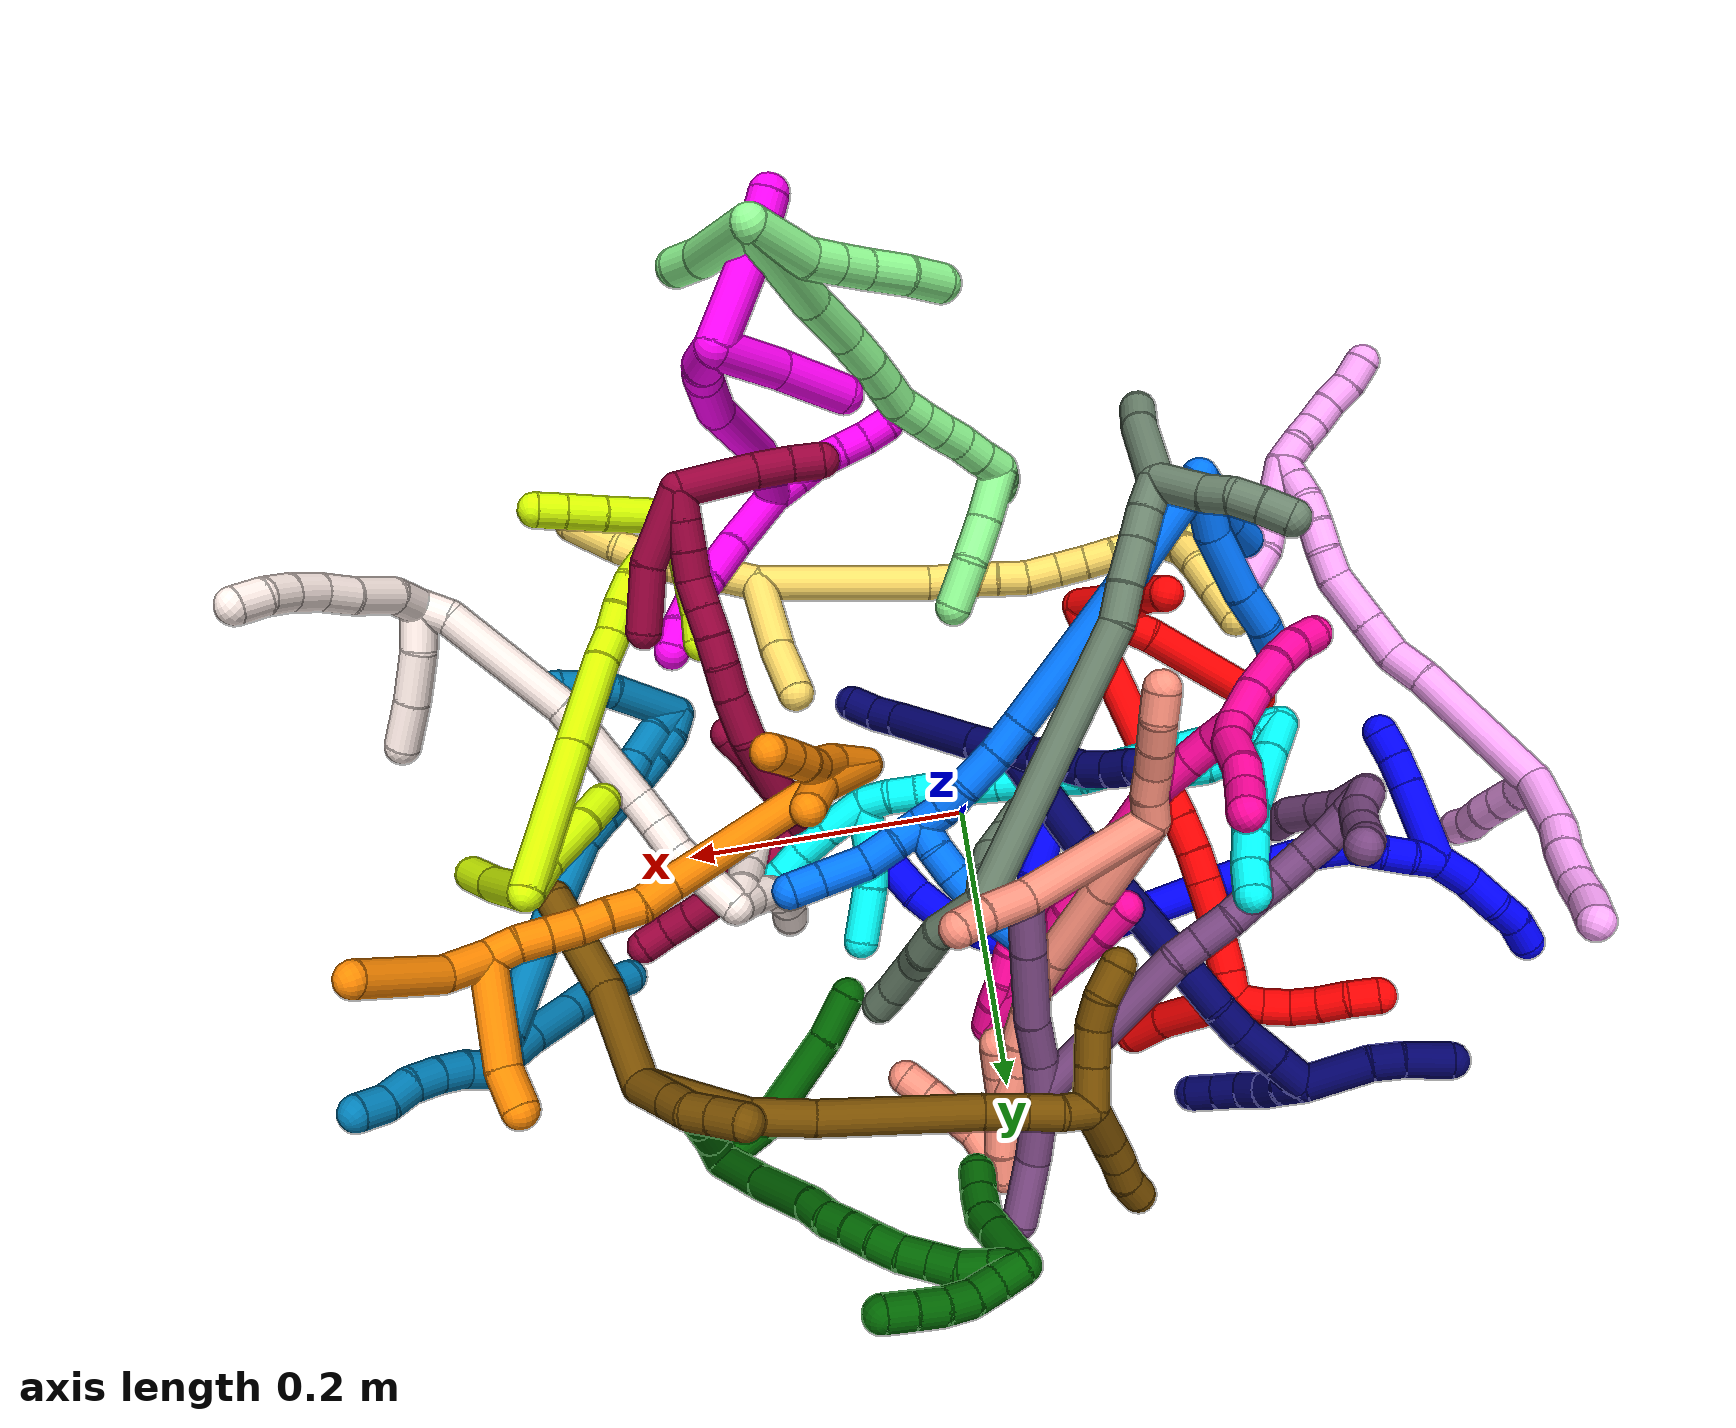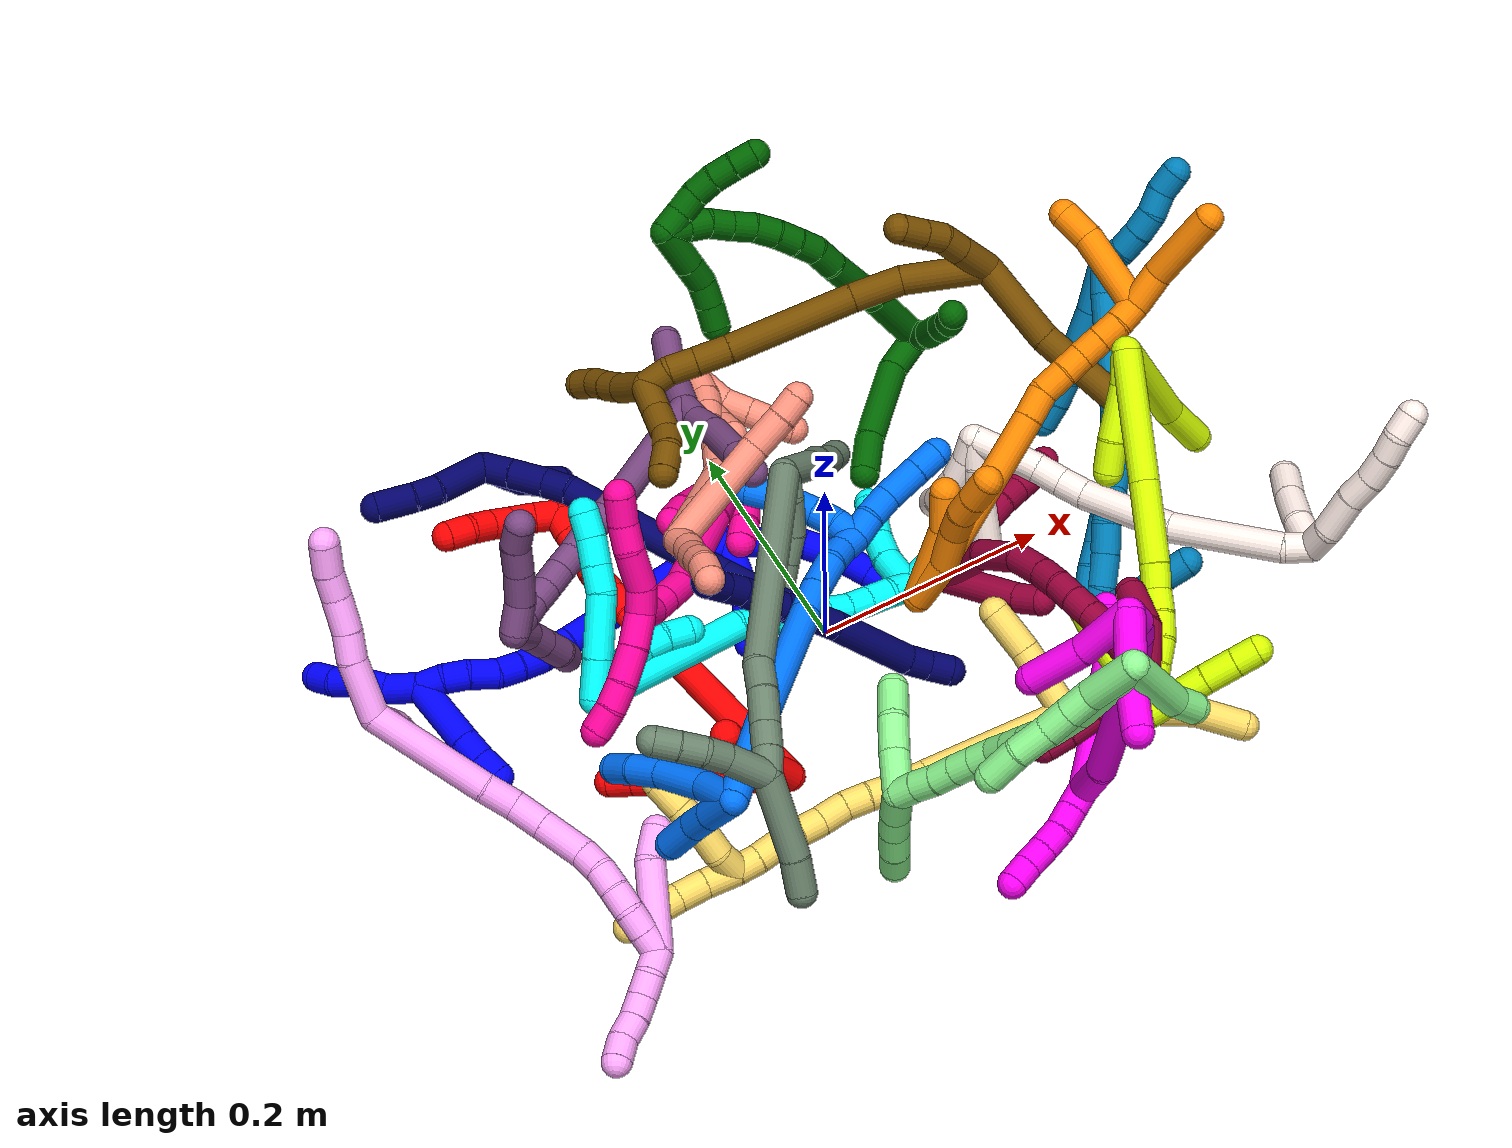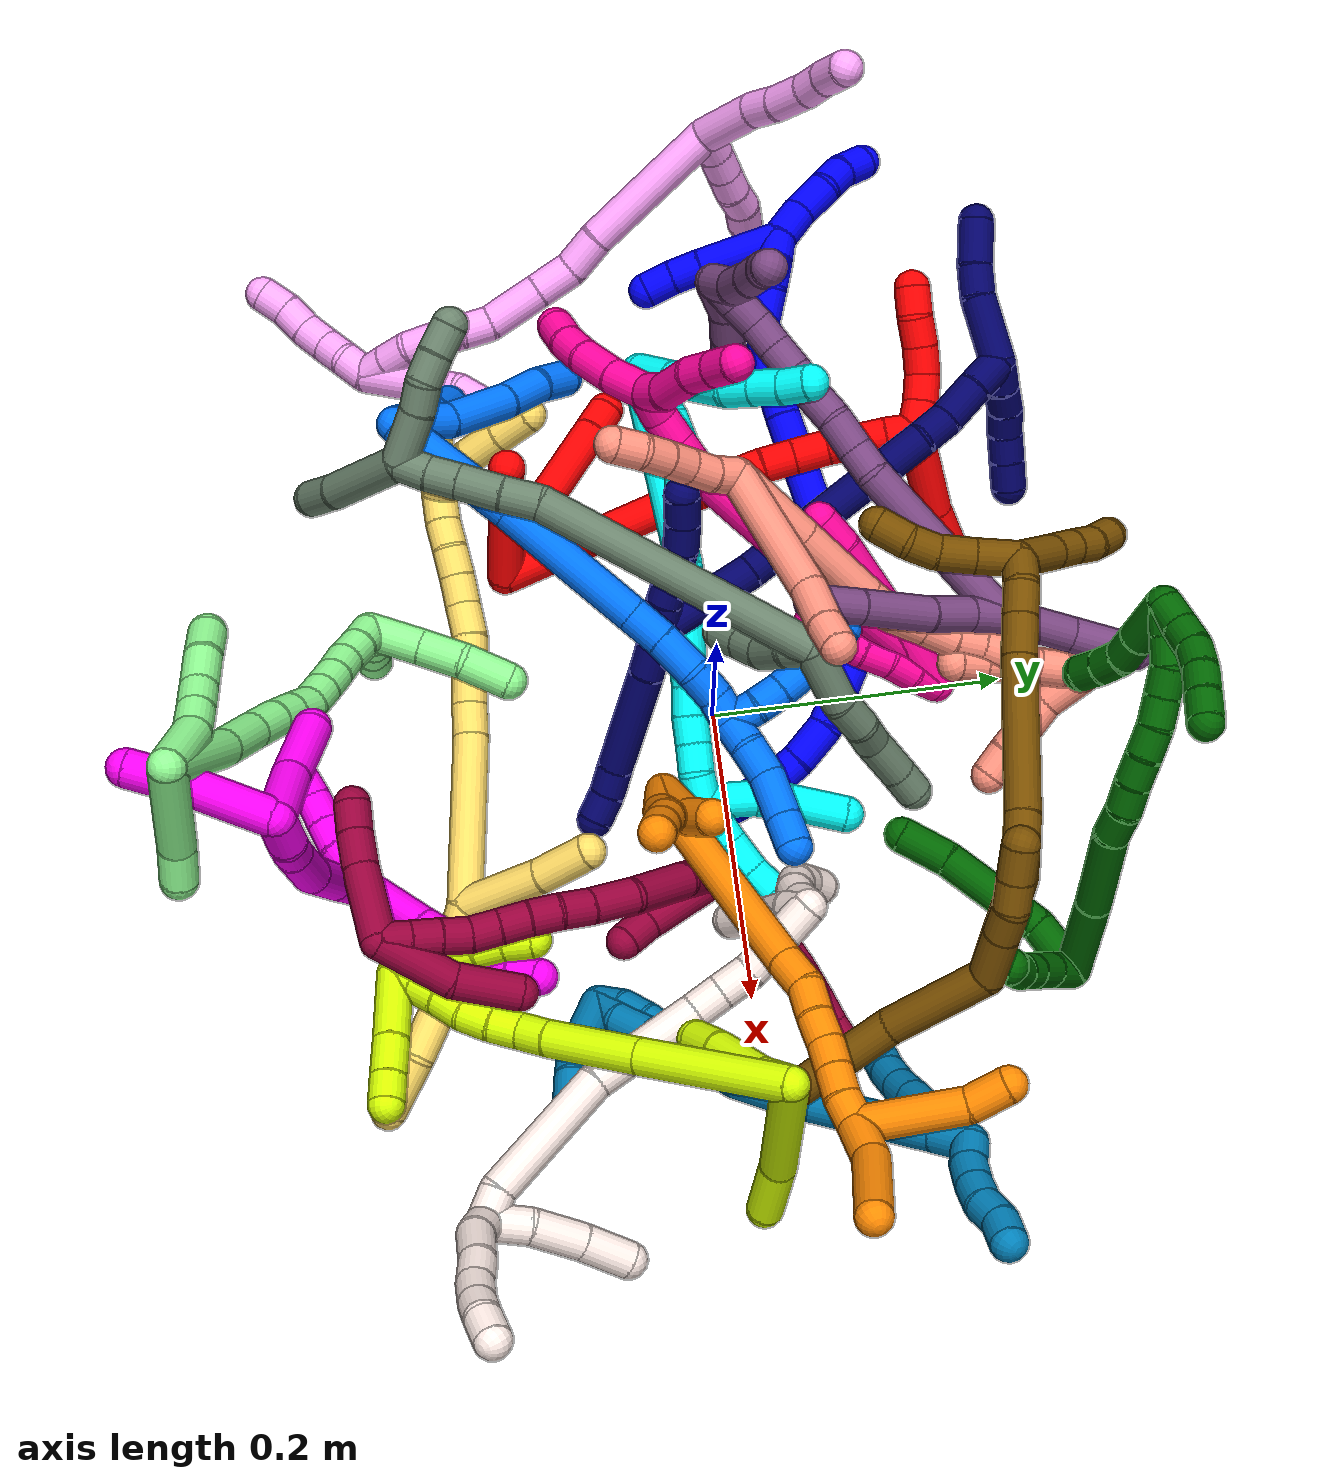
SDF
<sdf version="1.7">
 <world name="default">
  <plugin name="TubeGeneratorPlugin" filename="libtube_generator_plugin.so"/>
  <model name="photoneo_s_sensor">
   <static>1</static>
   <pose>0 0 2 1.57079 1.57079 3.14159</pose>
   <link name="link">
    <inertial><mass>0.1</mass></inertial>
    <sensor name="sensor" type="depth">
     <update_rate>30</update_rate>
     <camera>
      <horizontal_fov>1.22</horizontal_fov>
      <image><width>1920</width><height>1200</height><format>B8G8R8</format></image>
      <clip><near>0.1</near><far>4</far></clip>
      <depth_camera><output>points</output></depth_camera>
     </camera>
     <plugin name="camera_plugin" filename="libgazebo_ros_depth_camera.so">
      <baseline>0.2</baseline>
      <alwaysOn>1</alwaysOn>
      <updateRate>0.0</updateRate>
      <cameraName>camera_ir</cameraName>
      <imageTopicName>/camera/color/image_raw</imageTopicName>
      <cameraInfoTopicName>/camera/color/camera_info</cameraInfoTopicName>
      <depthImageTopicName>/camera/depth/image_raw</depthImageTopicName>
      <depthImageCameraInfoTopicName>/camera/depth/camera_info</depthImageCameraInfoTopicName>
      <pointCloudTopicName>/camera/depth/points</pointCloudTopicName>
      <frameName>fr_optical</frameName>
      <pointCloudCutoff>0.1</pointCloudCutoff>
      <pointCloudCutoffMax>2.0</pointCloudCutoffMax>
      <distortionK1>0</distortionK1>
      <distortionK2>0</distortionK2>
      <distortionK3>0</distortionK3>
      <distortionT1>0</distortionT1>
      <distortionT2>0</distortionT2>
      <CxPrime>0</CxPrime>
      <Cx>0</Cx>
      <Cy>0</Cy>
      <focalLength>0</focalLength>
      <hackBaseline>0</hackBaseline>
     </plugin>
    </sensor>
   </link>
  </model>
  <gravity>0 0 -9.8</gravity>
  <magnetic_field>6e-06 2.3e-05 -4.2e-05</magnetic_field>
  <atmosphere type="adiabatic"/>
  <physics name="default_physics" default="0" type="ode">
   <max_step_size>0.003</max_step_size>
   <real_time_factor>1</real_time_factor>
   <real_time_update_rate>1000</real_time_update_rate>
   <max_contacts>10000</max_contacts>
   <ode>
    <solver>
     <type>quick</type>
     <iters>100</iters>
     <sor>1.3</sor>
     <use_dynamic_moi_rescaling>0</use_dynamic_moi_rescaling>
    </solver>
    <constraints>
     <contact_max_correcting_vel>0</contact_max_correcting_vel>
     <contact_surface_layer>0.001</contact_surface_layer>
     <cfm>0</cfm>
     <erp>0.2</erp>
    </constraints>
   </ode>
  </physics>
  <scene><ambient>0.4 0.4 0.4 1</ambient><background>0.7 0.7 0.7 1</background><shadows>0</shadows></scene>
  <audio><device>default</device></audio>
  <spherical_coordinates>
   <surface_model>EARTH_WGS84</surface_model>
   <latitude_deg>0</latitude_deg>
   <longitude_deg>0</longitude_deg>
   <elevation>0</elevation>
   <heading_deg>0</heading_deg>
  </spherical_coordinates>
  <model name="bin">
   <static>1</static>
   <link name="bottom">
    <collision name="collision-bottom">
     <pose>0 0 -0.01 0 -0 0</pose>
     <geometry><box><size>0.8 0.6 0.02</size></box></geometry>
     <surface>
      <friction><ode><mu>100</mu><mu2>100</mu2></ode></friction>
      <contact><collide_bitmask>65535</collide_bitmask></contact>
     </surface>
    </collision>
   </link>
   <link name="west_wall">
    <collision name="collision-west_wall">
     <pose>-0.41 0 0.1 0 -0 0</pose>
     <geometry><box><size>0.02 0.6 0.2</size></box></geometry>
     <surface>
      <friction><ode><mu>100</mu><mu2>100</mu2></ode></friction>
      <contact><collide_bitmask>65535</collide_bitmask></contact>
     </surface>
    </collision>
   </link>
   <link name="east_wall">
    <collision name="collision-east_wall">
     <pose>0.41 0 0.1 0 -0 0</pose>
     <geometry><box><size>0.02 0.6 0.2</size></box></geometry>
     <surface>
      <friction><ode><mu>100</mu><mu2>100</mu2></ode></friction>
      <contact><collide_bitmask>65535</collide_bitmask></contact>
     </surface>
    </collision>
   </link>
   <link name="south_wall">
    <collision name="collision-south_wall">
     <pose>0 -0.31 0.1 0 -0 0</pose>
     <geometry><box><size>0.8 0.02 0.2</size></box></geometry>
     <surface>
      <friction><ode><mu>100</mu><mu2>100</mu2></ode></friction>
      <contact><collide_bitmask>65535</collide_bitmask></contact>
     </surface>
    </collision>
   </link>
   <link name="north_wall">
    <collision name="collision-north_wall">
     <pose>0 0.31 0.1 0 -0 0</pose>
     <geometry><box><size>0.8 0.02 0.2</size></box></geometry>
     <surface>
      <friction><ode><mu>100</mu><mu2>100</mu2></ode></friction>
      <contact><collide_bitmask>65535</collide_bitmask></contact>
     </surface>
    </collision>
   </link>
  </model>
  <model name="1">
   <static>0</static>
   <link name="1">
    <collision name="collision-cylinder-e_1_2_8">
     <pose>0.005806 -0.004931 -0.031844 2.98797 0.178256 1.71967</pose>
     <geometry><cylinder><radius>0.0125</radius><length>0.065485</length></cylinder></geometry>
     <surface>
      <friction><ode><mu>1.16</mu><mu2>1.16</mu2><slip1>0</slip1><slip2>0</slip2></ode></friction>
      <contact><ode><kp>1e+06</kp><kd>1</kd><max_vel>0</max_vel><min_depth>0.001</min_depth></ode></contact>
     </surface>
    </collision>
    <visual name="visual-cylinder-e_1_2_8">
     <pose>0.005806 -0.004931 -0.031844 2.98797 0.178256 1.71967</pose>
     <geometry><cylinder><radius>0.0125</radius><length>0.065485</length></cylinder></geometry>
     <material><ambient>0 0 1 1</ambient></material>
    </visual>
    <collision name="collision-cylinder-e_2_8_9">
     <pose>0.009676 -0.01296 -0.078152 2.93058 -0.130106 -1.10299</pose>
     <geometry><cylinder><radius>0.0125</radius><length>0.029836</length></cylinder></geometry>
     <surface>
      <friction><ode><mu>1.16</mu><mu2>1.16</mu2><slip1>0</slip1><slip2>0</slip2></ode></friction>
      <contact><ode><kp>1e+06</kp><kd>1</kd><max_vel>0</max_vel><min_depth>0.001</min_depth></ode></contact>
     </surface>
    </collision>
    <visual name="visual-cylinder-e_2_8_9">
     <pose>0.009676 -0.01296 -0.078152 2.93058 -0.130106 -1.10299</pose>
     <geometry><cylinder><radius>0.0125</radius><length>0.029836</length></cylinder></geometry>
     <material><ambient>0 0 1 1</ambient></material>
    </visual>
    <collision name="collision-cylinder-e_3_9_10">
     <pose>0.00328 -0.019462 -0.106445 2.90021 -0.303501 -1.80058</pose>
     <geometry><cylinder><radius>0.0125</radius><length>0.029847</length></cylinder></geometry>
     <surface>
      <friction><ode><mu>1.16</mu><mu2>1.16</mu2><slip1>0</slip1><slip2>0</slip2></ode></friction>
      <contact><ode><kp>1e+06</kp><kd>1</kd><max_vel>0</max_vel><min_depth>0.001</min_depth></ode></contact>
     </surface>
    </collision>
    <visual name="visual-cylinder-e_3_9_10">
     <pose>0.00328 -0.019462 -0.106445 2.90021 -0.303501 -1.80058</pose>
     <geometry><cylinder><radius>0.0125</radius><length>0.029847</length></cylinder></geometry>
     <material><ambient>0 0 1 1</ambient></material>
    </visual>
    <collision name="collision-cylinder-e_4_10_6">
     <pose>-0.006393 -0.027567 -0.130515 2.71127 -0.433308 -1.57793</pose>
     <geometry><cylinder><radius>0.0125</radius><length>0.024831</length></cylinder></geometry>
     <surface>
      <friction><ode><mu>1.16</mu><mu2>1.16</mu2><slip1>0</slip1><slip2>0</slip2></ode></friction>
      <contact><ode><kp>1e+06</kp><kd>1</kd><max_vel>0</max_vel><min_depth>0.001</min_depth></ode></contact>
     </surface>
    </collision>
    <visual name="visual-cylinder-e_4_10_6">
     <pose>-0.006393 -0.027567 -0.130515 2.71127 -0.433308 -1.57793</pose>
     <geometry><cylinder><radius>0.0125</radius><length>0.024831</length></cylinder></geometry>
     <material><ambient>0 0 1 1</ambient></material>
    </visual>
    <collision name="collision-cylinder-e_1_2_11">
     <pose>-0.022346 -0.010372 -0.012191 2.43663 -0.949209 -1.89887</pose>
     <geometry><cylinder><radius>0.0125</radius><length>0.054974</length></cylinder></geometry>
     <surface>
      <friction><ode><mu>1.16</mu><mu2>1.16</mu2><slip1>0</slip1><slip2>0</slip2></ode></friction>
      <contact><ode><kp>1e+06</kp><kd>1</kd><max_vel>0</max_vel><min_depth>0.001</min_depth></ode></contact>
     </surface>
    </collision>
    <visual name="visual-cylinder-e_1_2_11">
     <pose>-0.022346 -0.010372 -0.012191 2.43663 -0.949209 -1.89887</pose>
     <geometry><cylinder><radius>0.0125</radius><length>0.054974</length></cylinder></geometry>
     <material><ambient>0 0 1 1</ambient></material>
    </visual>
    <collision name="collision-cylinder-e_2_11_5">
     <pose>-0.064461 -0.03092 -0.027908 1.90439 -1.07199 -1.39085</pose>
     <geometry><cylinder><radius>0.0125</radius><length>0.045026</length></cylinder></geometry>
     <surface>
      <friction><ode><mu>1.16</mu><mu2>1.16</mu2><slip1>0</slip1><slip2>0</slip2></ode></friction>
      <contact><ode><kp>1e+06</kp><kd>1</kd><max_vel>0</max_vel><min_depth>0.001</min_depth></ode></contact>
     </surface>
    </collision>
    <visual name="visual-cylinder-e_2_11_5">
     <pose>-0.064461 -0.03092 -0.027908 1.90439 -1.07199 -1.39085</pose>
     <geometry><cylinder><radius>0.0125</radius><length>0.045026</length></cylinder></geometry>
     <material><ambient>0 0 1 1</ambient></material>
    </visual>
    <collision name="collision-cylinder-e_1_2_12">
     <pose>-0.058456 -0.018749 0.056808 0.318781 -0.773852 -0.130817</pose>
     <geometry><cylinder><radius>0.0125</radius><length>0.167282</length></cylinder></geometry>
     <surface>
      <friction><ode><mu>1.16</mu><mu2>1.16</mu2><slip1>0</slip1><slip2>0</slip2></ode></friction>
      <contact><ode><kp>1e+06</kp><kd>1</kd><max_vel>0</max_vel><min_depth>0.001</min_depth></ode></contact>
     </surface>
    </collision>
    <visual name="visual-cylinder-e_1_2_12">
     <pose>-0.058456 -0.018749 0.056808 0.318781 -0.773852 -0.130817</pose>
     <geometry><cylinder><radius>0.0125</radius><length>0.167282</length></cylinder></geometry>
     <material><ambient>0 0 1 1</ambient></material>
    </visual>
    <collision name="collision-cylinder-e_2_12_13">
     <pose>-0.126452 -0.039597 0.123332 0.2128 -0.764825 -0.085863</pose>
     <geometry><cylinder><radius>0.0125</radius><length>0.027554</length></cylinder></geometry>
     <surface>
      <friction><ode><mu>1.16</mu><mu2>1.16</mu2><slip1>0</slip1><slip2>0</slip2></ode></friction>
      <contact><ode><kp>1e+06</kp><kd>1</kd><max_vel>0</max_vel><min_depth>0.001</min_depth></ode></contact>
     </surface>
    </collision>
    <visual name="visual-cylinder-e_2_12_13">
     <pose>-0.126452 -0.039597 0.123332 0.2128 -0.764825 -0.085863</pose>
     <geometry><cylinder><radius>0.0125</radius><length>0.027554</length></cylinder></geometry>
     <material><ambient>0 0 1 1</ambient></material>
    </visual>
    <collision name="collision-cylinder-e_3_13_14">
     <pose>-0.141848 -0.045015 0.141379 0.37908 -0.578549 -0.11407</pose>
     <geometry><cylinder><radius>0.0125</radius><length>0.02142</length></cylinder></geometry>
     <surface>
      <friction><ode><mu>1.16</mu><mu2>1.16</mu2><slip1>0</slip1><slip2>0</slip2></ode></friction>
      <contact><ode><kp>1e+06</kp><kd>1</kd><max_vel>0</max_vel><min_depth>0.001</min_depth></ode></contact>
     </surface>
    </collision>
    <visual name="visual-cylinder-e_3_13_14">
     <pose>-0.141848 -0.045015 0.141379 0.37908 -0.578549 -0.11407</pose>
     <geometry><cylinder><radius>0.0125</radius><length>0.02142</length></cylinder></geometry>
     <material><ambient>0 0 1 1</ambient></material>
    </visual>
    <collision name="collision-cylinder-e_4_14_15">
     <pose>-0.152954 -0.050431 0.158136 0.244034 -0.543765 -0.068346</pose>
     <geometry><cylinder><radius>0.0125</radius><length>0.020294</length></cylinder></geometry>
     <surface>
      <friction><ode><mu>1.16</mu><mu2>1.16</mu2><slip1>0</slip1><slip2>0</slip2></ode></friction>
      <contact><ode><kp>1e+06</kp><kd>1</kd><max_vel>0</max_vel><min_depth>0.001</min_depth></ode></contact>
     </surface>
    </collision>
    <visual name="visual-cylinder-e_4_14_15">
     <pose>-0.152954 -0.050431 0.158136 0.244034 -0.543765 -0.068346</pose>
     <geometry><cylinder><radius>0.0125</radius><length>0.020294</length></cylinder></geometry>
     <material><ambient>0 0 1 1</ambient></material>
    </visual>
    <collision name="collision-cylinder-e_5_15_16">
     <pose>-0.161131 -0.053416 0.177738 0.079141 -0.255403 -0.010167</pose>
     <geometry><cylinder><radius>0.0125</radius><length>0.023174</length></cylinder></geometry>
     <surface>
      <friction><ode><mu>1.16</mu><mu2>1.16</mu2><slip1>0</slip1><slip2>0</slip2></ode></friction>
      <contact><ode><kp>1e+06</kp><kd>1</kd><max_vel>0</max_vel><min_depth>0.001</min_depth></ode></contact>
     </surface>
    </collision>
    <visual name="visual-cylinder-e_5_15_16">
     <pose>-0.161131 -0.053416 0.177738 0.079141 -0.255403 -0.010167</pose>
     <geometry><cylinder><radius>0.0125</radius><length>0.023174</length></cylinder></geometry>
     <material><ambient>0 0 1 1</ambient></material>
    </visual>
    <collision name="collision-cylinder-e_6_16_17">
     <pose>-0.167961 -0.053014 0.198146 -0.138606 -0.39654 0.02789</pose>
     <geometry><cylinder><radius>0.0125</radius><length>0.02021</length></cylinder></geometry>
     <surface>
      <friction><ode><mu>1.16</mu><mu2>1.16</mu2><slip1>0</slip1><slip2>0</slip2></ode></friction>
      <contact><ode><kp>1e+06</kp><kd>1</kd><max_vel>0</max_vel><min_depth>0.001</min_depth></ode></contact>
     </surface>
    </collision>
    <visual name="visual-cylinder-e_6_16_17">
     <pose>-0.167961 -0.053014 0.198146 -0.138606 -0.39654 0.02789</pose>
     <geometry><cylinder><radius>0.0125</radius><length>0.02021</length></cylinder></geometry>
     <material><ambient>0 0 1 1</ambient></material>
    </visual>
    <collision name="collision-cylinder-e_7_17_1">
     <pose>-0.176998 -0.048598 0.215409 -0.371474 -0.537193 0.103348</pose>
     <geometry><cylinder><radius>0.0125</radius><length>0.020065</length></cylinder></geometry>
     <surface>
      <friction><ode><mu>1.16</mu><mu2>1.16</mu2><slip1>0</slip1><slip2>0</slip2></ode></friction>
      <contact><ode><kp>1e+06</kp><kd>1</kd><max_vel>0</max_vel><min_depth>0.001</min_depth></ode></contact>
     </surface>
    </collision>
    <visual name="visual-cylinder-e_7_17_1">
     <pose>-0.176998 -0.048598 0.215409 -0.371474 -0.537193 0.103348</pose>
     <geometry><cylinder><radius>0.0125</radius><length>0.020065</length></cylinder></geometry>
     <material><ambient>0 0 1 1</ambient></material>
    </visual>
    <collision name="collision-cylinder-e_1_1_18">
     <pose>-0.1849 -0.037402 0.235244 -0.599477 -0.191225 0.059261</pose>
     <geometry><cylinder><radius>0.0125</radius><length>0.029125</length></cylinder></geometry>
     <surface>
      <friction><ode><mu>1.16</mu><mu2>1.16</mu2><slip1>0</slip1><slip2>0</slip2></ode></friction>
      <contact><ode><kp>1e+06</kp><kd>1</kd><max_vel>0</max_vel><min_depth>0.001</min_depth></ode></contact>
     </surface>
    </collision>
    <visual name="visual-cylinder-e_1_1_18">
     <pose>-0.1849 -0.037402 0.235244 -0.599477 -0.191225 0.059261</pose>
     <geometry><cylinder><radius>0.0125</radius><length>0.029125</length></cylinder></geometry>
     <material><ambient>0 0 1 1</ambient></material>
    </visual>
    <collision name="collision-cylinder-e_2_18_19">
     <pose>-0.18677 -0.023226 0.259615 -0.452559 0.064123 -0.014767</pose>
     <geometry><cylinder><radius>0.0125</radius><length>0.028005</length></cylinder></geometry>
     <surface>
      <friction><ode><mu>1.16</mu><mu2>1.16</mu2><slip1>0</slip1><slip2>0</slip2></ode></friction>
      <contact><ode><kp>1e+06</kp><kd>1</kd><max_vel>0</max_vel><min_depth>0.001</min_depth></ode></contact>
     </surface>
    </collision>
    <visual name="visual-cylinder-e_2_18_19">
     <pose>-0.18677 -0.023226 0.259615 -0.452559 0.064123 -0.014767</pose>
     <geometry><cylinder><radius>0.0125</radius><length>0.028005</length></cylinder></geometry>
     <material><ambient>0 0 1 1</ambient></material>
    </visual>
    <collision name="collision-cylinder-e_3_19_20">
     <pose>-0.187291 -0.010264 0.280284 -0.701953 -0.132897 0.04872</pose>
     <geometry><cylinder><radius>0.0125</radius><length>0.021408</length></cylinder></geometry>
     <surface>
      <friction><ode><mu>1.16</mu><mu2>1.16</mu2><slip1>0</slip1><slip2>0</slip2></ode></friction>
      <contact><ode><kp>1e+06</kp><kd>1</kd><max_vel>0</max_vel><min_depth>0.001</min_depth></ode></contact>
     </surface>
    </collision>
    <visual name="visual-cylinder-e_3_19_20">
     <pose>-0.187291 -0.010264 0.280284 -0.701953 -0.132897 0.04872</pose>
     <geometry><cylinder><radius>0.0125</radius><length>0.021408</length></cylinder></geometry>
     <material><ambient>0 0 1 1</ambient></material>
    </visual>
    <collision name="collision-cylinder-e_4_20_4">
     <pose>-0.187545 0.004566 0.295465 -0.845145 0.108723 -0.048927</pose>
     <geometry><cylinder><radius>0.0125</radius><length>0.021461</length></cylinder></geometry>
     <surface>
      <friction><ode><mu>1.16</mu><mu2>1.16</mu2><slip1>0</slip1><slip2>0</slip2></ode></friction>
      <contact><ode><kp>1e+06</kp><kd>1</kd><max_vel>0</max_vel><min_depth>0.001</min_depth></ode></contact>
     </surface>
    </collision>
    <visual name="visual-cylinder-e_4_20_4">
     <pose>-0.187545 0.004566 0.295465 -0.845145 0.108723 -0.048927</pose>
     <geometry><cylinder><radius>0.0125</radius><length>0.021461</length></cylinder></geometry>
     <material><ambient>0 0 1 1</ambient></material>
    </visual>
    <collision name="collision-cylinder-e_1_1_21">
     <pose>-0.200004 -0.054718 0.202664 2.72277 -0.666056 -2.03971</pose>
     <geometry><cylinder><radius>0.0125</radius><length>0.057848</length></cylinder></geometry>
     <surface>
      <friction><ode><mu>1.16</mu><mu2>1.16</mu2><slip1>0</slip1><slip2>0</slip2></ode></friction>
      <contact><ode><kp>1e+06</kp><kd>1</kd><max_vel>0</max_vel><min_depth>0.001</min_depth></ode></contact>
     </surface>
    </collision>
    <visual name="visual-cylinder-e_1_1_21">
     <pose>-0.200004 -0.054718 0.202664 2.72277 -0.666056 -2.03971</pose>
     <geometry><cylinder><radius>0.0125</radius><length>0.057848</length></cylinder></geometry>
     <material><ambient>0 0 1 1</ambient></material>
    </visual>
    <collision name="collision-cylinder-e_2_21_22">
     <pose>-0.224371 -0.067149 0.173848 2.76468 -0.644278 -2.10332</pose>
     <geometry><cylinder><radius>0.0125</radius><length>0.02163</length></cylinder></geometry>
     <surface>
      <friction><ode><mu>1.16</mu><mu2>1.16</mu2><slip1>0</slip1><slip2>0</slip2></ode></friction>
      <contact><ode><kp>1e+06</kp><kd>1</kd><max_vel>0</max_vel><min_depth>0.001</min_depth></ode></contact>
     </surface>
    </collision>
    <visual name="visual-cylinder-e_2_21_22">
     <pose>-0.224371 -0.067149 0.173848 2.76468 -0.644278 -2.10332</pose>
     <geometry><cylinder><radius>0.0125</radius><length>0.02163</length></cylinder></geometry>
     <material><ambient>0 0 1 1</ambient></material>
    </visual>
    <collision name="collision-cylinder-e_3_22_3">
     <pose>-0.236134 -0.073514 0.157597 2.77188 -0.539032 -1.95146</pose>
     <geometry><cylinder><radius>0.0125</radius><length>0.020522</length></cylinder></geometry>
     <surface>
      <friction><ode><mu>1.16</mu><mu2>1.16</mu2><slip1>0</slip1><slip2>0</slip2></ode></friction>
      <contact><ode><kp>1e+06</kp><kd>1</kd><max_vel>0</max_vel><min_depth>0.001</min_depth></ode></contact>
     </surface>
    </collision>
    <visual name="visual-cylinder-e_3_22_3">
     <pose>-0.236134 -0.073514 0.157597 2.77188 -0.539032 -1.95146</pose>
     <geometry><cylinder><radius>0.0125</radius><length>0.020522</length></cylinder></geometry>
     <material><ambient>0 0 1 1</ambient></material>
    </visual>
    <collision name="collision-sphere-3">
     <pose>-0.241401 -0.076696 0.149385 0 -0 0</pose>
     <geometry><sphere><radius>0.0125</radius></sphere></geometry>
     <surface>
      <friction><ode><mu>1.16</mu><mu2>1.16</mu2><slip1>0</slip1><slip2>0</slip2></ode></friction>
      <contact><ode><kp>1e+06</kp><kd>1</kd><max_vel>0</max_vel><min_depth>0.001</min_depth></ode></contact>
     </surface>
    </collision>
    <visual name="visual-sphere-3">
     <pose>-0.241401 -0.076696 0.149385 0 -0 0</pose>
     <geometry><sphere><radius>0.0125</radius></sphere></geometry>
     <material><ambient>0 0 1 1</ambient></material>
    </visual>
    <collision name="collision-sphere-22">
     <pose>-0.230867 -0.070332 0.165808 0 -0 0</pose>
     <geometry><sphere><radius>0.0125</radius></sphere></geometry>
     <surface>
      <friction><ode><mu>1.16</mu><mu2>1.16</mu2><slip1>0</slip1><slip2>0</slip2></ode></friction>
      <contact><ode><kp>1e+06</kp><kd>1</kd><max_vel>0</max_vel><min_depth>0.001</min_depth></ode></contact>
     </surface>
    </collision>
    <visual name="visual-sphere-22">
     <pose>-0.230867 -0.070332 0.165808 0 -0 0</pose>
     <geometry><sphere><radius>0.0125</radius></sphere></geometry>
     <material><ambient>0 0 1 1</ambient></material>
    </visual>
    <collision name="collision-sphere-21">
     <pose>-0.217876 -0.063967 0.181887 0 -0 0</pose>
     <geometry><sphere><radius>0.0125</radius></sphere></geometry>
     <surface>
      <friction><ode><mu>1.16</mu><mu2>1.16</mu2><slip1>0</slip1><slip2>0</slip2></ode></friction>
      <contact><ode><kp>1e+06</kp><kd>1</kd><max_vel>0</max_vel><min_depth>0.001</min_depth></ode></contact>
     </surface>
    </collision>
    <visual name="visual-sphere-21">
     <pose>-0.217876 -0.063967 0.181887 0 -0 0</pose>
     <geometry><sphere><radius>0.0125</radius></sphere></geometry>
     <material><ambient>0 0 1 1</ambient></material>
    </visual>
    <collision name="collision-sphere-4">
     <pose>-0.186381 0.012546 0.302544 0 -0 0</pose>
     <geometry><sphere><radius>0.0125</radius></sphere></geometry>
     <surface>
      <friction><ode><mu>1.16</mu><mu2>1.16</mu2><slip1>0</slip1><slip2>0</slip2></ode></friction>
      <contact><ode><kp>1e+06</kp><kd>1</kd><max_vel>0</max_vel><min_depth>0.001</min_depth></ode></contact>
     </surface>
    </collision>
    <visual name="visual-sphere-4">
     <pose>-0.186381 0.012546 0.302544 0 -0 0</pose>
     <geometry><sphere><radius>0.0125</radius></sphere></geometry>
     <material><ambient>0 0 1 1</ambient></material>
    </visual>
    <collision name="collision-sphere-20">
     <pose>-0.18871 -0.003414 0.288385 0 -0 0</pose>
     <geometry><sphere><radius>0.0125</radius></sphere></geometry>
     <surface>
      <friction><ode><mu>1.16</mu><mu2>1.16</mu2><slip1>0</slip1><slip2>0</slip2></ode></friction>
      <contact><ode><kp>1e+06</kp><kd>1</kd><max_vel>0</max_vel><min_depth>0.001</min_depth></ode></contact>
     </surface>
    </collision>
    <visual name="visual-sphere-20">
     <pose>-0.18871 -0.003414 0.288385 0 -0 0</pose>
     <geometry><sphere><radius>0.0125</radius></sphere></geometry>
     <material><ambient>0 0 1 1</ambient></material>
    </visual>
    <collision name="collision-sphere-11">
     <pose>-0.044691 -0.020744 -0.024382 0 -0 0</pose>
     <geometry><sphere><radius>0.0125</radius></sphere></geometry>
     <surface>
      <friction><ode><mu>1.16</mu><mu2>1.16</mu2><slip1>0</slip1><slip2>0</slip2></ode></friction>
      <contact><ode><kp>1e+06</kp><kd>1</kd><max_vel>0</max_vel><min_depth>0.001</min_depth></ode></contact>
     </surface>
    </collision>
    <visual name="visual-sphere-11">
     <pose>-0.044691 -0.020744 -0.024382 0 -0 0</pose>
     <geometry><sphere><radius>0.0125</radius></sphere></geometry>
     <material><ambient>0 0 1 1</ambient></material>
    </visual>
    <collision name="collision-sphere-6">
     <pose>-0.011606 -0.032268 -0.140756 0 -0 0</pose>
     <geometry><sphere><radius>0.0125</radius></sphere></geometry>
     <surface>
      <friction><ode><mu>1.16</mu><mu2>1.16</mu2><slip1>0</slip1><slip2>0</slip2></ode></friction>
      <contact><ode><kp>1e+06</kp><kd>1</kd><max_vel>0</max_vel><min_depth>0.001</min_depth></ode></contact>
     </surface>
    </collision>
    <visual name="visual-sphere-6">
     <pose>-0.011606 -0.032268 -0.140756 0 -0 0</pose>
     <geometry><sphere><radius>0.0125</radius></sphere></geometry>
     <material><ambient>0 0 1 1</ambient></material>
    </visual>
    <collision name="collision-sphere-10">
     <pose>-0.00118 -0.022867 -0.120274 0 -0 0</pose>
     <geometry><sphere><radius>0.0125</radius></sphere></geometry>
     <surface>
      <friction><ode><mu>1.16</mu><mu2>1.16</mu2><slip1>0</slip1><slip2>0</slip2></ode></friction>
      <contact><ode><kp>1e+06</kp><kd>1</kd><max_vel>0</max_vel><min_depth>0.001</min_depth></ode></contact>
     </surface>
    </collision>
    <visual name="visual-sphere-10">
     <pose>-0.00118 -0.022867 -0.120274 0 -0 0</pose>
     <geometry><sphere><radius>0.0125</radius></sphere></geometry>
     <material><ambient>0 0 1 1</ambient></material>
    </visual>
    <collision name="collision-sphere-9">
     <pose>0.00774 -0.016058 -0.092616 0 -0 0</pose>
     <geometry><sphere><radius>0.0125</radius></sphere></geometry>
     <surface>
      <friction><ode><mu>1.16</mu><mu2>1.16</mu2><slip1>0</slip1><slip2>0</slip2></ode></friction>
      <contact><ode><kp>1e+06</kp><kd>1</kd><max_vel>0</max_vel><min_depth>0.001</min_depth></ode></contact>
     </surface>
    </collision>
    <visual name="visual-sphere-9">
     <pose>0.00774 -0.016058 -0.092616 0 -0 0</pose>
     <geometry><sphere><radius>0.0125</radius></sphere></geometry>
     <material><ambient>0 0 1 1</ambient></material>
    </visual>
    <collision name="collision-sphere-2">
     <geometry><sphere><radius>0.0125</radius></sphere></geometry>
     <surface>
      <friction><ode><mu>1.16</mu><mu2>1.16</mu2><slip1>0</slip1><slip2>0</slip2></ode></friction>
      <contact><ode><kp>1e+06</kp><kd>1</kd><max_vel>0</max_vel><min_depth>0.001</min_depth></ode></contact>
     </surface>
    </collision>
    <visual name="visual-sphere-2">
     <geometry><sphere><radius>0.0125</radius></sphere></geometry>
     <material><ambient>0 0 1 1</ambient></material>
    </visual>
    <collision name="collision-sphere-19">
     <pose>-0.185873 -0.017115 0.272183 0 -0 0</pose>
     <geometry><sphere><radius>0.0125</radius></sphere></geometry>
     <surface>
      <friction><ode><mu>1.16</mu><mu2>1.16</mu2><slip1>0</slip1><slip2>0</slip2></ode></friction>
      <contact><ode><kp>1e+06</kp><kd>1</kd><max_vel>0</max_vel><min_depth>0.001</min_depth></ode></contact>
     </surface>
    </collision>
    <visual name="visual-sphere-19">
     <pose>-0.185873 -0.017115 0.272183 0 -0 0</pose>
     <geometry><sphere><radius>0.0125</radius></sphere></geometry>
     <material><ambient>0 0 1 1</ambient></material>
    </visual>
    <collision name="collision-sphere-8">
     <pose>0.011611 -0.009861 -0.063688 0 -0 0</pose>
     <geometry><sphere><radius>0.0125</radius></sphere></geometry>
     <surface>
      <friction><ode><mu>1.16</mu><mu2>1.16</mu2><slip1>0</slip1><slip2>0</slip2></ode></friction>
      <contact><ode><kp>1e+06</kp><kd>1</kd><max_vel>0</max_vel><min_depth>0.001</min_depth></ode></contact>
     </surface>
    </collision>
    <visual name="visual-sphere-8">
     <pose>0.011611 -0.009861 -0.063688 0 -0 0</pose>
     <geometry><sphere><radius>0.0125</radius></sphere></geometry>
     <material><ambient>0 0 1 1</ambient></material>
    </visual>
    <collision name="collision-sphere-5">
     <pose>-0.084231 -0.041096 -0.031435 0 -0 0</pose>
     <geometry><sphere><radius>0.0125</radius></sphere></geometry>
     <surface>
      <friction><ode><mu>1.16</mu><mu2>1.16</mu2><slip1>0</slip1><slip2>0</slip2></ode></friction>
      <contact><ode><kp>1e+06</kp><kd>1</kd><max_vel>0</max_vel><min_depth>0.001</min_depth></ode></contact>
     </surface>
    </collision>
    <visual name="visual-sphere-5">
     <pose>-0.084231 -0.041096 -0.031435 0 -0 0</pose>
     <geometry><sphere><radius>0.0125</radius></sphere></geometry>
     <material><ambient>0 0 1 1</ambient></material>
    </visual>
    <collision name="collision-sphere-12">
     <pose>-0.116913 -0.037498 0.113616 0 -0 0</pose>
     <geometry><sphere><radius>0.0125</radius></sphere></geometry>
     <surface>
      <friction><ode><mu>1.16</mu><mu2>1.16</mu2><slip1>0</slip1><slip2>0</slip2></ode></friction>
      <contact><ode><kp>1e+06</kp><kd>1</kd><max_vel>0</max_vel><min_depth>0.001</min_depth></ode></contact>
     </surface>
    </collision>
    <visual name="visual-sphere-12">
     <pose>-0.116913 -0.037498 0.113616 0 -0 0</pose>
     <geometry><sphere><radius>0.0125</radius></sphere></geometry>
     <material><ambient>0 0 1 1</ambient></material>
    </visual>
    <collision name="collision-sphere-13">
     <pose>-0.135992 -0.041696 0.133048 0 -0 0</pose>
     <geometry><sphere><radius>0.0125</radius></sphere></geometry>
     <surface>
      <friction><ode><mu>1.16</mu><mu2>1.16</mu2><slip1>0</slip1><slip2>0</slip2></ode></friction>
      <contact><ode><kp>1e+06</kp><kd>1</kd><max_vel>0</max_vel><min_depth>0.001</min_depth></ode></contact>
     </surface>
    </collision>
    <visual name="visual-sphere-13">
     <pose>-0.135992 -0.041696 0.133048 0 -0 0</pose>
     <geometry><sphere><radius>0.0125</radius></sphere></geometry>
     <material><ambient>0 0 1 1</ambient></material>
    </visual>
    <collision name="collision-sphere-14">
     <pose>-0.147704 -0.048333 0.149709 0 -0 0</pose>
     <geometry><sphere><radius>0.0125</radius></sphere></geometry>
     <surface>
      <friction><ode><mu>1.16</mu><mu2>1.16</mu2><slip1>0</slip1><slip2>0</slip2></ode></friction>
      <contact><ode><kp>1e+06</kp><kd>1</kd><max_vel>0</max_vel><min_depth>0.001</min_depth></ode></contact>
     </surface>
    </collision>
    <visual name="visual-sphere-14">
     <pose>-0.147704 -0.048333 0.149709 0 -0 0</pose>
     <geometry><sphere><radius>0.0125</radius></sphere></geometry>
     <material><ambient>0 0 1 1</ambient></material>
    </visual>
    <collision name="collision-sphere-15">
     <pose>-0.158204 -0.052529 0.166562 0 -0 0</pose>
     <geometry><sphere><radius>0.0125</radius></sphere></geometry>
     <surface>
      <friction><ode><mu>1.16</mu><mu2>1.16</mu2><slip1>0</slip1><slip2>0</slip2></ode></friction>
      <contact><ode><kp>1e+06</kp><kd>1</kd><max_vel>0</max_vel><min_depth>0.001</min_depth></ode></contact>
     </surface>
    </collision>
    <visual name="visual-sphere-15">
     <pose>-0.158204 -0.052529 0.166562 0 -0 0</pose>
     <geometry><sphere><radius>0.0125</radius></sphere></geometry>
     <material><ambient>0 0 1 1</ambient></material>
    </visual>
    <collision name="collision-sphere-16">
     <pose>-0.164059 -0.054302 0.188914 0 -0 0</pose>
     <geometry><sphere><radius>0.0125</radius></sphere></geometry>
     <surface>
      <friction><ode><mu>1.16</mu><mu2>1.16</mu2><slip1>0</slip1><slip2>0</slip2></ode></friction>
      <contact><ode><kp>1e+06</kp><kd>1</kd><max_vel>0</max_vel><min_depth>0.001</min_depth></ode></contact>
     </surface>
    </collision>
    <visual name="visual-sphere-16">
     <pose>-0.164059 -0.054302 0.188914 0 -0 0</pose>
     <geometry><sphere><radius>0.0125</radius></sphere></geometry>
     <material><ambient>0 0 1 1</ambient></material>
    </visual>
    <collision name="collision-sphere-17">
     <pose>-0.171864 -0.051727 0.207377 0 -0 0</pose>
     <geometry><sphere><radius>0.0125</radius></sphere></geometry>
     <surface>
      <friction><ode><mu>1.16</mu><mu2>1.16</mu2><slip1>0</slip1><slip2>0</slip2></ode></friction>
      <contact><ode><kp>1e+06</kp><kd>1</kd><max_vel>0</max_vel><min_depth>0.001</min_depth></ode></contact>
     </surface>
    </collision>
    <visual name="visual-sphere-17">
     <pose>-0.171864 -0.051727 0.207377 0 -0 0</pose>
     <geometry><sphere><radius>0.0125</radius></sphere></geometry>
     <material><ambient>0 0 1 1</ambient></material>
    </visual>
    <collision name="collision-sphere-1">
     <pose>-0.182132 -0.045469 0.22344 0 -0 0</pose>
     <geometry><sphere><radius>0.0125</radius></sphere></geometry>
     <surface>
      <friction><ode><mu>1.16</mu><mu2>1.16</mu2><slip1>0</slip1><slip2>0</slip2></ode></friction>
      <contact><ode><kp>1e+06</kp><kd>1</kd><max_vel>0</max_vel><min_depth>0.001</min_depth></ode></contact>
     </surface>
    </collision>
    <visual name="visual-sphere-1">
     <pose>-0.182132 -0.045469 0.22344 0 -0 0</pose>
     <geometry><sphere><radius>0.0125</radius></sphere></geometry>
     <material><ambient>0 0 1 1</ambient></material>
    </visual>
    <collision name="collision-sphere-18">
     <pose>-0.187668 -0.029336 0.247048 0 -0 0</pose>
     <geometry><sphere><radius>0.0125</radius></sphere></geometry>
     <surface>
      <friction><ode><mu>1.16</mu><mu2>1.16</mu2><slip1>0</slip1><slip2>0</slip2></ode></friction>
      <contact><ode><kp>1e+06</kp><kd>1</kd><max_vel>0</max_vel><min_depth>0.001</min_depth></ode></contact>
     </surface>
    </collision>
    <visual name="visual-sphere-18">
     <pose>-0.187668 -0.029336 0.247048 0 -0 0</pose>
     <geometry><sphere><radius>0.0125</radius></sphere></geometry>
     <material><ambient>0 0 1 1</ambient></material>
    </visual>
    <inertial>
     <pose>-0.098037 -0.028566 0.085339 0 -0 0</pose>
     <mass>0.75</mass>
     <inertia>
      <ixx>0.000212</ixx>
      <ixy>0</ixy>
      <ixz>0</ixz>
      <iyy>0.000384</iyy>
      <iyz>0</iyz>
      <izz>0.000427</izz>
     </inertia>
    </inertial>
   </link>
   <pose>-0.034397 0.107729 0.02222 -1.27376 -0.4279 0.823172</pose>
  </model>
  <model name="2">
   <static>0</static>
   <link name="2">
    <collision name="collision-cylinder-e_1_2_8">
     <pose>-0.002135 0.005293 0.026632 -0.196197 -0.078461 0.007726</pose>
     <geometry><cylinder><radius>0.0125</radius><length>0.054473</length></cylinder></geometry>
     <surface>
      <friction><ode><mu>1.16</mu><mu2>1.16</mu2><slip1>0</slip1><slip2>0</slip2></ode></friction>
      <contact><ode><kp>1e+06</kp><kd>1</kd><max_vel>0</max_vel><min_depth>0.001</min_depth></ode></contact>
     </surface>
    </collision>
    <visual name="visual-cylinder-e_1_2_8">
     <pose>-0.002135 0.005293 0.026632 -0.196197 -0.078461 0.007726</pose>
     <geometry><cylinder><radius>0.0125</radius><length>0.054473</length></cylinder></geometry>
     <material><ambient>1 0 0 1</ambient></material>
    </visual>
    <collision name="collision-cylinder-e_2_8_9">
     <pose>-0.013986 0.017986 0.088573 -0.206584 -0.263072 0.027427</pose>
     <geometry><cylinder><radius>0.0125</radius><length>0.074724</length></cylinder></geometry>
     <surface>
      <friction><ode><mu>1.16</mu><mu2>1.16</mu2><slip1>0</slip1><slip2>0</slip2></ode></friction>
      <contact><ode><kp>1e+06</kp><kd>1</kd><max_vel>0</max_vel><min_depth>0.001</min_depth></ode></contact>
     </surface>
    </collision>
    <visual name="visual-cylinder-e_2_8_9">
     <pose>-0.013986 0.017986 0.088573 -0.206584 -0.263072 0.027427</pose>
     <geometry><cylinder><radius>0.0125</radius><length>0.074724</length></cylinder></geometry>
     <material><ambient>1 0 0 1</ambient></material>
    </visual>
    <collision name="collision-cylinder-e_3_9_6">
     <pose>-0.026486 0.027321 0.133716 -0.194289 -0.271003 0.026571</pose>
     <geometry><cylinder><radius>0.0125</radius><length>0.020803</length></cylinder></geometry>
     <surface>
      <friction><ode><mu>1.16</mu><mu2>1.16</mu2><slip1>0</slip1><slip2>0</slip2></ode></friction>
      <contact><ode><kp>1e+06</kp><kd>1</kd><max_vel>0</max_vel><min_depth>0.001</min_depth></ode></contact>
     </surface>
    </collision>
    <visual name="visual-cylinder-e_3_9_6">
     <pose>-0.026486 0.027321 0.133716 -0.194289 -0.271003 0.026571</pose>
     <geometry><cylinder><radius>0.0125</radius><length>0.020803</length></cylinder></geometry>
     <material><ambient>1 0 0 1</ambient></material>
    </visual>
    <collision name="collision-cylinder-e_1_2_10">
     <pose>0.023693 0.011279 0.013996 -0.678317 0.921791 -0.346847</pose>
     <geometry><cylinder><radius>0.0125</radius><length>0.05948</length></cylinder></geometry>
     <surface>
      <friction><ode><mu>1.16</mu><mu2>1.16</mu2><slip1>0</slip1><slip2>0</slip2></ode></friction>
      <contact><ode><kp>1e+06</kp><kd>1</kd><max_vel>0</max_vel><min_depth>0.001</min_depth></ode></contact>
     </surface>
    </collision>
    <visual name="visual-cylinder-e_1_2_10">
     <pose>0.023693 0.011279 0.013996 -0.678317 0.921791 -0.346847</pose>
     <geometry><cylinder><radius>0.0125</radius><length>0.05948</length></cylinder></geometry>
     <material><ambient>1 0 0 1</ambient></material>
    </visual>
    <collision name="collision-cylinder-e_2_10_11">
     <pose>0.056396 0.026796 0.030052 -1.11834 1.08885 -0.724356</pose>
     <geometry><cylinder><radius>0.0125</radius><length>0.020334</length></cylinder></geometry>
     <surface>
      <friction><ode><mu>1.16</mu><mu2>1.16</mu2><slip1>0</slip1><slip2>0</slip2></ode></friction>
      <contact><ode><kp>1e+06</kp><kd>1</kd><max_vel>0</max_vel><min_depth>0.001</min_depth></ode></contact>
     </surface>
    </collision>
    <visual name="visual-cylinder-e_2_10_11">
     <pose>0.056396 0.026796 0.030052 -1.11834 1.08885 -0.724356</pose>
     <geometry><cylinder><radius>0.0125</radius><length>0.020334</length></cylinder></geometry>
     <material><ambient>1 0 0 1</ambient></material>
    </visual>
    <collision name="collision-cylinder-e_3_11_5">
     <pose>0.073539 0.036144 0.03521 -1.02565 0.937202 -0.555339</pose>
     <geometry><cylinder><radius>0.0125</radius><length>0.020186</length></cylinder></geometry>
     <surface>
      <friction><ode><mu>1.16</mu><mu2>1.16</mu2><slip1>0</slip1><slip2>0</slip2></ode></friction>
      <contact><ode><kp>1e+06</kp><kd>1</kd><max_vel>0</max_vel><min_depth>0.001</min_depth></ode></contact>
     </surface>
    </collision>
    <visual name="visual-cylinder-e_3_11_5">
     <pose>0.073539 0.036144 0.03521 -1.02565 0.937202 -0.555339</pose>
     <geometry><cylinder><radius>0.0125</radius><length>0.020186</length></cylinder></geometry>
     <material><ambient>1 0 0 1</ambient></material>
    </visual>
    <collision name="collision-cylinder-e_1_2_12">
     <pose>-0.014802 0.061255 0.037178 -1.02529 -0.203705 0.114925</pose>
     <geometry><cylinder><radius>0.0125</radius><length>0.146334</length></cylinder></geometry>
     <surface>
      <friction><ode><mu>1.16</mu><mu2>1.16</mu2><slip1>0</slip1><slip2>0</slip2></ode></friction>
      <contact><ode><kp>1e+06</kp><kd>1</kd><max_vel>0</max_vel><min_depth>0.001</min_depth></ode></contact>
     </surface>
    </collision>
    <visual name="visual-cylinder-e_1_2_12">
     <pose>-0.014802 0.061255 0.037178 -1.02529 -0.203705 0.114925</pose>
     <geometry><cylinder><radius>0.0125</radius><length>0.146334</length></cylinder></geometry>
     <material><ambient>1 0 0 1</ambient></material>
    </visual>
    <collision name="collision-cylinder-e_2_12_13">
     <pose>-0.032415 0.131002 0.080278 -0.961829 -0.265154 0.138943</pose>
     <geometry><cylinder><radius>0.0125</radius><length>0.021457</length></cylinder></geometry>
     <surface>
      <friction><ode><mu>1.16</mu><mu2>1.16</mu2><slip1>0</slip1><slip2>0</slip2></ode></friction>
      <contact><ode><kp>1e+06</kp><kd>1</kd><max_vel>0</max_vel><min_depth>0.001</min_depth></ode></contact>
     </surface>
    </collision>
    <visual name="visual-cylinder-e_2_12_13">
     <pose>-0.032415 0.131002 0.080278 -0.961829 -0.265154 0.138943</pose>
     <geometry><cylinder><radius>0.0125</radius><length>0.021457</length></cylinder></geometry>
     <material><ambient>1 0 0 1</ambient></material>
    </visual>
    <collision name="collision-cylinder-e_3_13_14">
     <pose>-0.038818 0.149493 0.092516 -1.00742 -0.294812 0.163303</pose>
     <geometry><cylinder><radius>0.0125</radius><length>0.024719</length></cylinder></geometry>
     <surface>
      <friction><ode><mu>1.16</mu><mu2>1.16</mu2><slip1>0</slip1><slip2>0</slip2></ode></friction>
      <contact><ode><kp>1e+06</kp><kd>1</kd><max_vel>0</max_vel><min_depth>0.001</min_depth></ode></contact>
     </surface>
    </collision>
    <visual name="visual-cylinder-e_3_13_14">
     <pose>-0.038818 0.149493 0.092516 -1.00742 -0.294812 0.163303</pose>
     <geometry><cylinder><radius>0.0125</radius><length>0.024719</length></cylinder></geometry>
     <material><ambient>1 0 0 1</ambient></material>
    </visual>
    <collision name="collision-cylinder-e_4_14_15">
     <pose>-0.046474 0.168313 0.103817 -1.05642 -0.381523 0.224419</pose>
     <geometry><cylinder><radius>0.0125</radius><length>0.021834</length></cylinder></geometry>
     <surface>
      <friction><ode><mu>1.16</mu><mu2>1.16</mu2><slip1>0</slip1><slip2>0</slip2></ode></friction>
      <contact><ode><kp>1e+06</kp><kd>1</kd><max_vel>0</max_vel><min_depth>0.001</min_depth></ode></contact>
     </surface>
    </collision>
    <visual name="visual-cylinder-e_4_14_15">
     <pose>-0.046474 0.168313 0.103817 -1.05642 -0.381523 0.224419</pose>
     <geometry><cylinder><radius>0.0125</radius><length>0.021834</length></cylinder></geometry>
     <material><ambient>1 0 0 1</ambient></material>
    </visual>
    <collision name="collision-cylinder-e_5_15_16">
     <pose>-0.055244 0.187471 0.114509 -1.06631 -0.379201 0.225551</pose>
     <geometry><cylinder><radius>0.0125</radius><length>0.025423</length></cylinder></geometry>
     <surface>
      <friction><ode><mu>1.16</mu><mu2>1.16</mu2><slip1>0</slip1><slip2>0</slip2></ode></friction>
      <contact><ode><kp>1e+06</kp><kd>1</kd><max_vel>0</max_vel><min_depth>0.001</min_depth></ode></contact>
     </surface>
    </collision>
    <visual name="visual-cylinder-e_5_15_16">
     <pose>-0.055244 0.187471 0.114509 -1.06631 -0.379201 0.225551</pose>
     <geometry><cylinder><radius>0.0125</radius><length>0.025423</length></cylinder></geometry>
     <material><ambient>1 0 0 1</ambient></material>
    </visual>
    <collision name="collision-cylinder-e_6_16_17">
     <pose>-0.06176 0.207432 0.122702 -1.31805 -0.180212 0.139734</pose>
     <geometry><cylinder><radius>0.0125</radius><length>0.020206</length></cylinder></geometry>
     <surface>
      <friction><ode><mu>1.16</mu><mu2>1.16</mu2><slip1>0</slip1><slip2>0</slip2></ode></friction>
      <contact><ode><kp>1e+06</kp><kd>1</kd><max_vel>0</max_vel><min_depth>0.001</min_depth></ode></contact>
     </surface>
    </collision>
    <visual name="visual-cylinder-e_6_16_17">
     <pose>-0.06176 0.207432 0.122702 -1.31805 -0.180212 0.139734</pose>
     <geometry><cylinder><radius>0.0125</radius><length>0.020206</length></cylinder></geometry>
     <material><ambient>1 0 0 1</ambient></material>
    </visual>
    <collision name="collision-cylinder-e_7_17_18">
     <pose>-0.067178 0.225567 0.129032 -1.14652 -0.368625 0.239557</pose>
     <geometry><cylinder><radius>0.0125</radius><length>0.020022</length></cylinder></geometry>
     <surface>
      <friction><ode><mu>1.16</mu><mu2>1.16</mu2><slip1>0</slip1><slip2>0</slip2></ode></friction>
      <contact><ode><kp>1e+06</kp><kd>1</kd><max_vel>0</max_vel><min_depth>0.001</min_depth></ode></contact>
     </surface>
    </collision>
    <visual name="visual-cylinder-e_7_17_18">
     <pose>-0.067178 0.225567 0.129032 -1.14652 -0.368625 0.239557</pose>
     <geometry><cylinder><radius>0.0125</radius><length>0.020022</length></cylinder></geometry>
     <material><ambient>1 0 0 1</ambient></material>
    </visual>
    <collision name="collision-cylinder-e_8_18_1">
     <pose>-0.074164 0.243033 0.135778 -1.25749 -0.344524 0.251707</pose>
     <geometry><cylinder><radius>0.0125</radius><length>0.020005</length></cylinder></geometry>
     <surface>
      <friction><ode><mu>1.16</mu><mu2>1.16</mu2><slip1>0</slip1><slip2>0</slip2></ode></friction>
      <contact><ode><kp>1e+06</kp><kd>1</kd><max_vel>0</max_vel><min_depth>0.001</min_depth></ode></contact>
     </surface>
    </collision>
    <visual name="visual-cylinder-e_8_18_1">
     <pose>-0.074164 0.243033 0.135778 -1.25749 -0.344524 0.251707</pose>
     <geometry><cylinder><radius>0.0125</radius><length>0.020005</length></cylinder></geometry>
     <material><ambient>1 0 0 1</ambient></material>
    </visual>
    <collision name="collision-cylinder-e_1_1_19">
     <pose>-0.075933 0.252998 0.148497 -0.1024 0.161633 -0.008301</pose>
     <geometry><cylinder><radius>0.0125</radius><length>0.02</length></cylinder></geometry>
     <surface>
      <friction><ode><mu>1.16</mu><mu2>1.16</mu2><slip1>0</slip1><slip2>0</slip2></ode></friction>
      <contact><ode><kp>1e+06</kp><kd>1</kd><max_vel>0</max_vel><min_depth>0.001</min_depth></ode></contact>
     </surface>
    </collision>
    <visual name="visual-cylinder-e_1_1_19">
     <pose>-0.075933 0.252998 0.148497 -0.1024 0.161633 -0.008301</pose>
     <geometry><cylinder><radius>0.0125</radius><length>0.02</length></cylinder></geometry>
     <material><ambient>1 0 0 1</ambient></material>
    </visual>
    <collision name="collision-cylinder-e_2_19_20">
     <pose>-0.071268 0.254377 0.16783 -0.038814 0.310528 -0.006076</pose>
     <geometry><cylinder><radius>0.0125</radius><length>0.02</length></cylinder></geometry>
     <surface>
      <friction><ode><mu>1.16</mu><mu2>1.16</mu2><slip1>0</slip1><slip2>0</slip2></ode></friction>
      <contact><ode><kp>1e+06</kp><kd>1</kd><max_vel>0</max_vel><min_depth>0.001</min_depth></ode></contact>
     </surface>
    </collision>
    <visual name="visual-cylinder-e_2_19_20">
     <pose>-0.071268 0.254377 0.16783 -0.038814 0.310528 -0.006076</pose>
     <geometry><cylinder><radius>0.0125</radius><length>0.02</length></cylinder></geometry>
     <material><ambient>1 0 0 1</ambient></material>
    </visual>
    <collision name="collision-cylinder-e_3_20_21">
     <pose>-0.06245 0.254947 0.185515 -0.024628 0.614103 -0.007809</pose>
     <geometry><cylinder><radius>0.0125</radius><length>0.02</length></cylinder></geometry>
     <surface>
      <friction><ode><mu>1.16</mu><mu2>1.16</mu2><slip1>0</slip1><slip2>0</slip2></ode></friction>
      <contact><ode><kp>1e+06</kp><kd>1</kd><max_vel>0</max_vel><min_depth>0.001</min_depth></ode></contact>
     </surface>
    </collision>
    <visual name="visual-cylinder-e_3_20_21">
     <pose>-0.06245 0.254947 0.185515 -0.024628 0.614103 -0.007809</pose>
     <geometry><cylinder><radius>0.0125</radius><length>0.02</length></cylinder></geometry>
     <material><ambient>1 0 0 1</ambient></material>
    </visual>
    <collision name="collision-cylinder-e_4_21_22">
     <pose>-0.050166 0.254797 0.201258 0.046464 0.710505 0.01724</pose>
     <geometry><cylinder><radius>0.0125</radius><length>0.02</length></cylinder></geometry>
     <surface>
      <friction><ode><mu>1.16</mu><mu2>1.16</mu2><slip1>0</slip1><slip2>0</slip2></ode></friction>
      <contact><ode><kp>1e+06</kp><kd>1</kd><max_vel>0</max_vel><min_depth>0.001</min_depth></ode></contact>
     </surface>
    </collision>
    <visual name="visual-cylinder-e_4_21_22">
     <pose>-0.050166 0.254797 0.201258 0.046464 0.710505 0.01724</pose>
     <geometry><cylinder><radius>0.0125</radius><length>0.02</length></cylinder></geometry>
     <material><ambient>1 0 0 1</ambient></material>
    </visual>
    <collision name="collision-cylinder-e_5_22_4">
     <pose>-0.039567 0.253476 0.21791 0.10631 0.419825 0.02267</pose>
     <geometry><cylinder><radius>0.0125</radius><length>0.02</length></cylinder></geometry>
     <surface>
      <friction><ode><mu>1.16</mu><mu2>1.16</mu2><slip1>0</slip1><slip2>0</slip2></ode></friction>
      <contact><ode><kp>1e+06</kp><kd>1</kd><max_vel>0</max_vel><min_depth>0.001</min_depth></ode></contact>
     </surface>
    </collision>
    <visual name="visual-cylinder-e_5_22_4">
     <pose>-0.039567 0.253476 0.21791 0.10631 0.419825 0.02267</pose>
     <geometry><cylinder><radius>0.0125</radius><length>0.02</length></cylinder></geometry>
     <material><ambient>1 0 0 1</ambient></material>
    </visual>
    <collision name="collision-cylinder-e_1_1_23">
     <pose>-0.106635 0.248328 0.123735 2.90135 -1.08432 -2.74606</pose>
     <geometry><cylinder><radius>0.0125</radius><length>0.065823</length></cylinder></geometry>
     <surface>
      <friction><ode><mu>1.16</mu><mu2>1.16</mu2><slip1>0</slip1><slip2>0</slip2></ode></friction>
      <contact><ode><kp>1e+06</kp><kd>1</kd><max_vel>0</max_vel><min_depth>0.001</min_depth></ode></contact>
     </surface>
    </collision>
    <visual name="visual-cylinder-e_1_1_23">
     <pose>-0.106635 0.248328 0.123735 2.90135 -1.08432 -2.74606</pose>
     <geometry><cylinder><radius>0.0125</radius><length>0.065823</length></cylinder></geometry>
     <material><ambient>1 0 0 1</ambient></material>
    </visual>
    <collision name="collision-cylinder-e_2_23_3">
     <pose>-0.151381 0.244761 0.101933 -3.12789 -1.15789 3.12063</pose>
     <geometry><cylinder><radius>0.0125</radius><length>0.034177</length></cylinder></geometry>
     <surface>
      <friction><ode><mu>1.16</mu><mu2>1.16</mu2><slip1>0</slip1><slip2>0</slip2></ode></friction>
      <contact><ode><kp>1e+06</kp><kd>1</kd><max_vel>0</max_vel><min_depth>0.001</min_depth></ode></contact>
     </surface>
    </collision>
    <visual name="visual-cylinder-e_2_23_3">
     <pose>-0.151381 0.244761 0.101933 -3.12789 -1.15789 3.12063</pose>
     <geometry><cylinder><radius>0.0125</radius><length>0.034177</length></cylinder></geometry>
     <material><ambient>1 0 0 1</ambient></material>
    </visual>
    <collision name="collision-sphere-3">
     <pose>-0.167033 0.244855 0.095077 0 -0 0</pose>
     <geometry><sphere><radius>0.0125</radius></sphere></geometry>
     <surface>
      <friction><ode><mu>1.16</mu><mu2>1.16</mu2><slip1>0</slip1><slip2>0</slip2></ode></friction>
      <contact><ode><kp>1e+06</kp><kd>1</kd><max_vel>0</max_vel><min_depth>0.001</min_depth></ode></contact>
     </surface>
    </collision>
    <visual name="visual-sphere-3">
     <pose>-0.167033 0.244855 0.095077 0 -0 0</pose>
     <geometry><sphere><radius>0.0125</radius></sphere></geometry>
     <material><ambient>1 0 0 1</ambient></material>
    </visual>
    <collision name="collision-sphere-23">
     <pose>-0.135728 0.244667 0.10879 0 -0 0</pose>
     <geometry><sphere><radius>0.0125</radius></sphere></geometry>
     <surface>
      <friction><ode><mu>1.16</mu><mu2>1.16</mu2><slip1>0</slip1><slip2>0</slip2></ode></friction>
      <contact><ode><kp>1e+06</kp><kd>1</kd><max_vel>0</max_vel><min_depth>0.001</min_depth></ode></contact>
     </surface>
    </collision>
    <visual name="visual-sphere-23">
     <pose>-0.135728 0.244667 0.10879 0 -0 0</pose>
     <geometry><sphere><radius>0.0125</radius></sphere></geometry>
     <material><ambient>1 0 0 1</ambient></material>
    </visual>
    <collision name="collision-sphere-4">
     <pose>-0.035491 0.252507 0.22699 0 -0 0</pose>
     <geometry><sphere><radius>0.0125</radius></sphere></geometry>
     <surface>
      <friction><ode><mu>1.16</mu><mu2>1.16</mu2><slip1>0</slip1><slip2>0</slip2></ode></friction>
      <contact><ode><kp>1e+06</kp><kd>1</kd><max_vel>0</max_vel><min_depth>0.001</min_depth></ode></contact>
     </surface>
    </collision>
    <visual name="visual-sphere-4">
     <pose>-0.035491 0.252507 0.22699 0 -0 0</pose>
     <geometry><sphere><radius>0.0125</radius></sphere></geometry>
     <material><ambient>1 0 0 1</ambient></material>
    </visual>
    <collision name="collision-sphere-22">
     <pose>-0.043643 0.254445 0.20883 0 -0 0</pose>
     <geometry><sphere><radius>0.0125</radius></sphere></geometry>
     <surface>
      <friction><ode><mu>1.16</mu><mu2>1.16</mu2><slip1>0</slip1><slip2>0</slip2></ode></friction>
      <contact><ode><kp>1e+06</kp><kd>1</kd><max_vel>0</max_vel><min_depth>0.001</min_depth></ode></contact>
     </surface>
    </collision>
    <visual name="visual-sphere-22">
     <pose>-0.043643 0.254445 0.20883 0 -0 0</pose>
     <geometry><sphere><radius>0.0125</radius></sphere></geometry>
     <material><ambient>1 0 0 1</ambient></material>
    </visual>
    <collision name="collision-sphere-21">
     <pose>-0.056688 0.255149 0.193685 0 -0 0</pose>
     <geometry><sphere><radius>0.0125</radius></sphere></geometry>
     <surface>
      <friction><ode><mu>1.16</mu><mu2>1.16</mu2><slip1>0</slip1><slip2>0</slip2></ode></friction>
      <contact><ode><kp>1e+06</kp><kd>1</kd><max_vel>0</max_vel><min_depth>0.001</min_depth></ode></contact>
     </surface>
    </collision>
    <visual name="visual-sphere-21">
     <pose>-0.056688 0.255149 0.193685 0 -0 0</pose>
     <geometry><sphere><radius>0.0125</radius></sphere></geometry>
     <material><ambient>1 0 0 1</ambient></material>
    </visual>
    <collision name="collision-sphere-20">
     <pose>-0.068212 0.254746 0.177345 0 -0 0</pose>
     <geometry><sphere><radius>0.0125</radius></sphere></geometry>
     <surface>
      <friction><ode><mu>1.16</mu><mu2>1.16</mu2><slip1>0</slip1><slip2>0</slip2></ode></friction>
      <contact><ode><kp>1e+06</kp><kd>1</kd><max_vel>0</max_vel><min_depth>0.001</min_depth></ode></contact>
     </surface>
    </collision>
    <visual name="visual-sphere-20">
     <pose>-0.068212 0.254746 0.177345 0 -0 0</pose>
     <geometry><sphere><radius>0.0125</radius></sphere></geometry>
     <material><ambient>1 0 0 1</ambient></material>
    </visual>
    <collision name="collision-sphere-11">
     <pose>0.065405 0.031034 0.032112 0 -0 0</pose>
     <geometry><sphere><radius>0.0125</radius></sphere></geometry>
     <surface>
      <friction><ode><mu>1.16</mu><mu2>1.16</mu2><slip1>0</slip1><slip2>0</slip2></ode></friction>
      <contact><ode><kp>1e+06</kp><kd>1</kd><max_vel>0</max_vel><min_depth>0.001</min_depth></ode></contact>
     </surface>
    </collision>
    <visual name="visual-sphere-11">
     <pose>0.065405 0.031034 0.032112 0 -0 0</pose>
     <geometry><sphere><radius>0.0125</radius></sphere></geometry>
     <material><ambient>1 0 0 1</ambient></material>
    </visual>
    <collision name="collision-sphere-10">
     <pose>0.047387 0.022558 0.027991 0 -0 0</pose>
     <geometry><sphere><radius>0.0125</radius></sphere></geometry>
     <surface>
      <friction><ode><mu>1.16</mu><mu2>1.16</mu2><slip1>0</slip1><slip2>0</slip2></ode></friction>
      <contact><ode><kp>1e+06</kp><kd>1</kd><max_vel>0</max_vel><min_depth>0.001</min_depth></ode></contact>
     </surface>
    </collision>
    <visual name="visual-sphere-10">
     <pose>0.047387 0.022558 0.027991 0 -0 0</pose>
     <geometry><sphere><radius>0.0125</radius></sphere></geometry>
     <material><ambient>1 0 0 1</ambient></material>
    </visual>
    <collision name="collision-sphere-6">
     <pose>-0.02927 0.029256 0.143549 0 -0 0</pose>
     <geometry><sphere><radius>0.0125</radius></sphere></geometry>
     <surface>
      <friction><ode><mu>1.16</mu><mu2>1.16</mu2><slip1>0</slip1><slip2>0</slip2></ode></friction>
      <contact><ode><kp>1e+06</kp><kd>1</kd><max_vel>0</max_vel><min_depth>0.001</min_depth></ode></contact>
     </surface>
    </collision>
    <visual name="visual-sphere-6">
     <pose>-0.02927 0.029256 0.143549 0 -0 0</pose>
     <geometry><sphere><radius>0.0125</radius></sphere></geometry>
     <material><ambient>1 0 0 1</ambient></material>
    </visual>
    <collision name="collision-sphere-9">
     <pose>-0.023702 0.025386 0.123883 0 -0 0</pose>
     <geometry><sphere><radius>0.0125</radius></sphere></geometry>
     <surface>
      <friction><ode><mu>1.16</mu><mu2>1.16</mu2><slip1>0</slip1><slip2>0</slip2></ode></friction>
      <contact><ode><kp>1e+06</kp><kd>1</kd><max_vel>0</max_vel><min_depth>0.001</min_depth></ode></contact>
     </surface>
    </collision>
    <visual name="visual-sphere-9">
     <pose>-0.023702 0.025386 0.123883 0 -0 0</pose>
     <geometry><sphere><radius>0.0125</radius></sphere></geometry>
     <material><ambient>1 0 0 1</ambient></material>
    </visual>
    <collision name="collision-sphere-2">
     <geometry><sphere><radius>0.0125</radius></sphere></geometry>
     <surface>
      <friction><ode><mu>1.16</mu><mu2>1.16</mu2><slip1>0</slip1><slip2>0</slip2></ode></friction>
      <contact><ode><kp>1e+06</kp><kd>1</kd><max_vel>0</max_vel><min_depth>0.001</min_depth></ode></contact>
     </surface>
    </collision>
    <visual name="visual-sphere-2">
     <geometry><sphere><radius>0.0125</radius></sphere></geometry>
     <material><ambient>1 0 0 1</ambient></material>
    </visual>
    <collision name="collision-sphere-19">
     <pose>-0.074323 0.254007 0.158315 0 -0 0</pose>
     <geometry><sphere><radius>0.0125</radius></sphere></geometry>
     <surface>
      <friction><ode><mu>1.16</mu><mu2>1.16</mu2><slip1>0</slip1><slip2>0</slip2></ode></friction>
      <contact><ode><kp>1e+06</kp><kd>1</kd><max_vel>0</max_vel><min_depth>0.001</min_depth></ode></contact>
     </surface>
    </collision>
    <visual name="visual-sphere-19">
     <pose>-0.074323 0.254007 0.158315 0 -0 0</pose>
     <geometry><sphere><radius>0.0125</radius></sphere></geometry>
     <material><ambient>1 0 0 1</ambient></material>
    </visual>
    <collision name="collision-sphere-8">
     <pose>-0.00427 0.010586 0.053263 0 -0 0</pose>
     <geometry><sphere><radius>0.0125</radius></sphere></geometry>
     <surface>
      <friction><ode><mu>1.16</mu><mu2>1.16</mu2><slip1>0</slip1><slip2>0</slip2></ode></friction>
      <contact><ode><kp>1e+06</kp><kd>1</kd><max_vel>0</max_vel><min_depth>0.001</min_depth></ode></contact>
     </surface>
    </collision>
    <visual name="visual-sphere-8">
     <pose>-0.00427 0.010586 0.053263 0 -0 0</pose>
     <geometry><sphere><radius>0.0125</radius></sphere></geometry>
     <material><ambient>1 0 0 1</ambient></material>
    </visual>
    <collision name="collision-sphere-5">
     <pose>0.081673 0.041253 0.038309 0 -0 0</pose>
     <geometry><sphere><radius>0.0125</radius></sphere></geometry>
     <surface>
      <friction><ode><mu>1.16</mu><mu2>1.16</mu2><slip1>0</slip1><slip2>0</slip2></ode></friction>
      <contact><ode><kp>1e+06</kp><kd>1</kd><max_vel>0</max_vel><min_depth>0.001</min_depth></ode></contact>
     </surface>
    </collision>
    <visual name="visual-sphere-5">
     <pose>0.081673 0.041253 0.038309 0 -0 0</pose>
     <geometry><sphere><radius>0.0125</radius></sphere></geometry>
     <material><ambient>1 0 0 1</ambient></material>
    </visual>
    <collision name="collision-sphere-12">
     <pose>-0.029603 0.12251 0.074356 0 -0 0</pose>
     <geometry><sphere><radius>0.0125</radius></sphere></geometry>
     <surface>
      <friction><ode><mu>1.16</mu><mu2>1.16</mu2><slip1>0</slip1><slip2>0</slip2></ode></friction>
      <contact><ode><kp>1e+06</kp><kd>1</kd><max_vel>0</max_vel><min_depth>0.001</min_depth></ode></contact>
     </surface>
    </collision>
    <visual name="visual-sphere-12">
     <pose>-0.029603 0.12251 0.074356 0 -0 0</pose>
     <geometry><sphere><radius>0.0125</radius></sphere></geometry>
     <material><ambient>1 0 0 1</ambient></material>
    </visual>
    <collision name="collision-sphere-13">
     <pose>-0.035226 0.139494 0.0862 0 -0 0</pose>
     <geometry><sphere><radius>0.0125</radius></sphere></geometry>
     <surface>
      <friction><ode><mu>1.16</mu><mu2>1.16</mu2><slip1>0</slip1><slip2>0</slip2></ode></friction>
      <contact><ode><kp>1e+06</kp><kd>1</kd><max_vel>0</max_vel><min_depth>0.001</min_depth></ode></contact>
     </surface>
    </collision>
    <visual name="visual-sphere-13">
     <pose>-0.035226 0.139494 0.0862 0 -0 0</pose>
     <geometry><sphere><radius>0.0125</radius></sphere></geometry>
     <material><ambient>1 0 0 1</ambient></material>
    </visual>
    <collision name="collision-sphere-14">
     <pose>-0.042409 0.159492 0.098832 0 -0 0</pose>
     <geometry><sphere><radius>0.0125</radius></sphere></geometry>
     <surface>
      <friction><ode><mu>1.16</mu><mu2>1.16</mu2><slip1>0</slip1><slip2>0</slip2></ode></friction>
      <contact><ode><kp>1e+06</kp><kd>1</kd><max_vel>0</max_vel><min_depth>0.001</min_depth></ode></contact>
     </surface>
    </collision>
    <visual name="visual-sphere-14">
     <pose>-0.042409 0.159492 0.098832 0 -0 0</pose>
     <geometry><sphere><radius>0.0125</radius></sphere></geometry>
     <material><ambient>1 0 0 1</ambient></material>
    </visual>
    <collision name="collision-sphere-15">
     <pose>-0.050538 0.177134 0.108802 0 -0 0</pose>
     <geometry><sphere><radius>0.0125</radius></sphere></geometry>
     <surface>
      <friction><ode><mu>1.16</mu><mu2>1.16</mu2><slip1>0</slip1><slip2>0</slip2></ode></friction>
      <contact><ode><kp>1e+06</kp><kd>1</kd><max_vel>0</max_vel><min_depth>0.001</min_depth></ode></contact>
     </surface>
    </collision>
    <visual name="visual-sphere-15">
     <pose>-0.050538 0.177134 0.108802 0 -0 0</pose>
     <geometry><sphere><radius>0.0125</radius></sphere></geometry>
     <material><ambient>1 0 0 1</ambient></material>
    </visual>
    <collision name="collision-sphere-16">
     <pose>-0.059949 0.197809 0.120217 0 -0 0</pose>
     <geometry><sphere><radius>0.0125</radius></sphere></geometry>
     <surface>
      <friction><ode><mu>1.16</mu><mu2>1.16</mu2><slip1>0</slip1><slip2>0</slip2></ode></friction>
      <contact><ode><kp>1e+06</kp><kd>1</kd><max_vel>0</max_vel><min_depth>0.001</min_depth></ode></contact>
     </surface>
    </collision>
    <visual name="visual-sphere-16">
     <pose>-0.059949 0.197809 0.120217 0 -0 0</pose>
     <geometry><sphere><radius>0.0125</radius></sphere></geometry>
     <material><ambient>1 0 0 1</ambient></material>
    </visual>
    <collision name="collision-sphere-17">
     <pose>-0.063571 0.217056 0.125188 0 -0 0</pose>
     <geometry><sphere><radius>0.0125</radius></sphere></geometry>
     <surface>
      <friction><ode><mu>1.16</mu><mu2>1.16</mu2><slip1>0</slip1><slip2>0</slip2></ode></friction>
      <contact><ode><kp>1e+06</kp><kd>1</kd><max_vel>0</max_vel><min_depth>0.001</min_depth></ode></contact>
     </surface>
    </collision>
    <visual name="visual-sphere-17">
     <pose>-0.063571 0.217056 0.125188 0 -0 0</pose>
     <geometry><sphere><radius>0.0125</radius></sphere></geometry>
     <material><ambient>1 0 0 1</ambient></material>
    </visual>
    <collision name="collision-sphere-18">
     <pose>-0.070786 0.234077 0.132876 0 -0 0</pose>
     <geometry><sphere><radius>0.0125</radius></sphere></geometry>
     <surface>
      <friction><ode><mu>1.16</mu><mu2>1.16</mu2><slip1>0</slip1><slip2>0</slip2></ode></friction>
      <contact><ode><kp>1e+06</kp><kd>1</kd><max_vel>0</max_vel><min_depth>0.001</min_depth></ode></contact>
     </surface>
    </collision>
    <visual name="visual-sphere-18">
     <pose>-0.070786 0.234077 0.132876 0 -0 0</pose>
     <geometry><sphere><radius>0.0125</radius></sphere></geometry>
     <material><ambient>1 0 0 1</ambient></material>
    </visual>
    <collision name="collision-sphere-1">
     <pose>-0.077542 0.251989 0.13868 0 -0 0</pose>
     <geometry><sphere><radius>0.0125</radius></sphere></geometry>
     <surface>
      <friction><ode><mu>1.16</mu><mu2>1.16</mu2><slip1>0</slip1><slip2>0</slip2></ode></friction>
      <contact><ode><kp>1e+06</kp><kd>1</kd><max_vel>0</max_vel><min_depth>0.001</min_depth></ode></contact>
     </surface>
    </collision>
    <visual name="visual-sphere-1">
     <pose>-0.077542 0.251989 0.13868 0 -0 0</pose>
     <geometry><sphere><radius>0.0125</radius></sphere></geometry>
     <material><ambient>1 0 0 1</ambient></material>
    </visual>
    <inertial>
     <pose>-0.034892 0.122332 0.087281 0 -0 0</pose>
     <mass>0.75</mass>
     <inertia>
      <ixx>0.000348</ixx>
      <ixy>0</ixy>
      <ixz>0</ixz>
      <iyy>0.000309</iyy>
      <iyz>0</iyz>
      <izz>-0.000147</izz>
     </inertia>
    </inertial>
   </link>
   <pose>-0.106383 -0.130423 0.043429 1.84973 -1.01663 -2.14444</pose>
  </model>
  <model name="3">
   <static>0</static>
   <link name="3">
    <collision name="collision-cylinder-e_1_2_8">
     <pose>0.009421 0.012812 0.003813 -1.28152 0.613941 -0.464255</pose>
     <geometry><cylinder><radius>0.0125</radius><length>0.032707</length></cylinder></geometry>
     <surface>
      <friction><ode><mu>1.16</mu><mu2>1.16</mu2><slip1>0</slip1><slip2>0</slip2></ode></friction>
      <contact><ode><kp>1e+06</kp><kd>1</kd><max_vel>0</max_vel><min_depth>0.001</min_depth></ode></contact>
     </surface>
    </collision>
    <visual name="visual-cylinder-e_1_2_8">
     <pose>0.009421 0.012812 0.003813 -1.28152 0.613941 -0.464255</pose>
     <geometry><cylinder><radius>0.0125</radius><length>0.032707</length></cylinder></geometry>
     <material><ambient>0.003922 1 0.996078 1</ambient></material>
    </visual>
    <collision name="collision-cylinder-e_2_8_9">
     <pose>0.033239 0.046336 0.01365 -1.28779 0.588513 -0.44734</pose>
     <geometry><cylinder><radius>0.0125</radius><length>0.051866</length></cylinder></geometry>
     <surface>
      <friction><ode><mu>1.16</mu><mu2>1.16</mu2><slip1>0</slip1><slip2>0</slip2></ode></friction>
      <contact><ode><kp>1e+06</kp><kd>1</kd><max_vel>0</max_vel><min_depth>0.001</min_depth></ode></contact>
     </surface>
    </collision>
    <visual name="visual-cylinder-e_2_8_9">
     <pose>0.033239 0.046336 0.01365 -1.28779 0.588513 -0.44734</pose>
     <geometry><cylinder><radius>0.0125</radius><length>0.051866</length></cylinder></geometry>
     <material><ambient>0.003922 1 0.996078 1</ambient></material>
    </visual>
    <collision name="collision-cylinder-e_3_9_10">
     <pose>0.050858 0.076965 0.023107 -1.23744 0.297965 -0.212921</pose>
     <geometry><cylinder><radius>0.0125</radius><length>0.021957</length></cylinder></geometry>
     <surface>
      <friction><ode><mu>1.16</mu><mu2>1.16</mu2><slip1>0</slip1><slip2>0</slip2></ode></friction>
      <contact><ode><kp>1e+06</kp><kd>1</kd><max_vel>0</max_vel><min_depth>0.001</min_depth></ode></contact>
     </surface>
    </collision>
    <visual name="visual-cylinder-e_3_9_10">
     <pose>0.050858 0.076965 0.023107 -1.23744 0.297965 -0.212921</pose>
     <geometry><cylinder><radius>0.0125</radius><length>0.021957</length></cylinder></geometry>
     <material><ambient>0.003922 1 0.996078 1</ambient></material>
    </visual>
    <collision name="collision-cylinder-e_4_10_11">
     <pose>0.05768 0.097155 0.029922 -1.25285 0.321253 -0.233432</pose>
     <geometry><cylinder><radius>0.0125</radius><length>0.022797</length></cylinder></geometry>
     <surface>
      <friction><ode><mu>1.16</mu><mu2>1.16</mu2><slip1>0</slip1><slip2>0</slip2></ode></friction>
      <contact><ode><kp>1e+06</kp><kd>1</kd><max_vel>0</max_vel><min_depth>0.001</min_depth></ode></contact>
     </surface>
    </collision>
    <visual name="visual-cylinder-e_4_10_11">
     <pose>0.05768 0.097155 0.029922 -1.25285 0.321253 -0.233432</pose>
     <geometry><cylinder><radius>0.0125</radius><length>0.022797</length></cylinder></geometry>
     <material><ambient>0.003922 1 0.996078 1</ambient></material>
    </visual>
    <collision name="collision-cylinder-e_5_11_6">
     <pose>0.063858 0.116573 0.037373 -1.15206 0.252167 -0.164287</pose>
     <geometry><cylinder><radius>0.0125</radius><length>0.020673</length></cylinder></geometry>
     <surface>
      <friction><ode><mu>1.16</mu><mu2>1.16</mu2><slip1>0</slip1><slip2>0</slip2></ode></friction>
      <contact><ode><kp>1e+06</kp><kd>1</kd><max_vel>0</max_vel><min_depth>0.001</min_depth></ode></contact>
     </surface>
    </collision>
    <visual name="visual-cylinder-e_5_11_6">
     <pose>0.063858 0.116573 0.037373 -1.15206 0.252167 -0.164287</pose>
     <geometry><cylinder><radius>0.0125</radius><length>0.020673</length></cylinder></geometry>
     <material><ambient>0.003922 1 0.996078 1</ambient></material>
    </visual>
    <collision name="collision-cylinder-e_1_2_12">
     <pose>0.007044 0.006094 -0.00364 -2.10925 0.781537 -1.25583</pose>
     <geometry><cylinder><radius>0.0125</radius><length>0.02</length></cylinder></geometry>
     <surface>
      <friction><ode><mu>1.16</mu><mu2>1.16</mu2><slip1>0</slip1><slip2>0</slip2></ode></friction>
      <contact><ode><kp>1e+06</kp><kd>1</kd><max_vel>0</max_vel><min_depth>0.001</min_depth></ode></contact>
     </surface>
    </collision>
    <visual name="visual-cylinder-e_1_2_12">
     <pose>0.007044 0.006094 -0.00364 -2.10925 0.781537 -1.25583</pose>
     <geometry><cylinder><radius>0.0125</radius><length>0.02</length></cylinder></geometry>
     <material><ambient>0.003922 1 0.996078 1</ambient></material>
    </visual>
    <collision name="collision-cylinder-e_2_12_13">
     <pose>0.019977 0.018491 -0.012338 -2.247 0.629753 -1.19293</pose>
     <geometry><cylinder><radius>0.0125</radius><length>0.02</length></cylinder></geometry>
     <surface>
      <friction><ode><mu>1.16</mu><mu2>1.16</mu2><slip1>0</slip1><slip2>0</slip2></ode></friction>
      <contact><ode><kp>1e+06</kp><kd>1</kd><max_vel>0</max_vel><min_depth>0.001</min_depth></ode></contact>
     </surface>
    </collision>
    <visual name="visual-cylinder-e_2_12_13">
     <pose>0.019977 0.018491 -0.012338 -2.247 0.629753 -1.19293</pose>
     <geometry><cylinder><radius>0.0125</radius><length>0.02</length></cylinder></geometry>
     <material><ambient>0.003922 1 0.996078 1</ambient></material>
    </visual>
    <collision name="collision-cylinder-e_3_13_14">
     <pose>0.031832 0.029383 -0.02398 -2.53302 0.63926 -1.62331</pose>
     <geometry><cylinder><radius>0.0125</radius><length>0.02</length></cylinder></geometry>
     <surface>
      <friction><ode><mu>1.16</mu><mu2>1.16</mu2><slip1>0</slip1><slip2>0</slip2></ode></friction>
      <contact><ode><kp>1e+06</kp><kd>1</kd><max_vel>0</max_vel><min_depth>0.001</min_depth></ode></contact>
     </surface>
    </collision>
    <visual name="visual-cylinder-e_3_13_14">
     <pose>0.031832 0.029383 -0.02398 -2.53302 0.63926 -1.62331</pose>
     <geometry><cylinder><radius>0.0125</radius><length>0.02</length></cylinder></geometry>
     <material><ambient>0.003922 1 0.996078 1</ambient></material>
    </visual>
    <collision name="collision-cylinder-e_4_14_15">
     <pose>0.045324 0.036313 -0.036719 -2.77791 0.852012 -2.37164</pose>
     <geometry><cylinder><radius>0.0125</radius><length>0.02</length></cylinder></geometry>
     <surface>
      <friction><ode><mu>1.16</mu><mu2>1.16</mu2><slip1>0</slip1><slip2>0</slip2></ode></friction>
      <contact><ode><kp>1e+06</kp><kd>1</kd><max_vel>0</max_vel><min_depth>0.001</min_depth></ode></contact>
     </surface>
    </collision>
    <visual name="visual-cylinder-e_4_14_15">
     <pose>0.045324 0.036313 -0.036719 -2.77791 0.852012 -2.37164</pose>
     <geometry><cylinder><radius>0.0125</radius><length>0.02</length></cylinder></geometry>
     <material><ambient>0.003922 1 0.996078 1</ambient></material>
    </visual>
    <collision name="collision-cylinder-e_5_15_5">
     <pose>0.059314 0.040041 -0.050376 -2.95894 0.702844 -2.65205</pose>
     <geometry><cylinder><radius>0.0125</radius><length>0.02</length></cylinder></geometry>
     <surface>
      <friction><ode><mu>1.16</mu><mu2>1.16</mu2><slip1>0</slip1><slip2>0</slip2></ode></friction>
      <contact><ode><kp>1e+06</kp><kd>1</kd><max_vel>0</max_vel><min_depth>0.001</min_depth></ode></contact>
     </surface>
    </collision>
    <visual name="visual-cylinder-e_5_15_5">
     <pose>0.059314 0.040041 -0.050376 -2.95894 0.702844 -2.65205</pose>
     <geometry><cylinder><radius>0.0125</radius><length>0.02</length></cylinder></geometry>
     <material><ambient>0.003922 1 0.996078 1</ambient></material>
    </visual>
    <collision name="collision-cylinder-e_1_2_16">
     <pose>0.042778 0.02288 -0.049459 -2.70831 0.665524 -2.00749</pose>
     <geometry><cylinder><radius>0.0125</radius><length>0.138559</length></cylinder></geometry>
     <surface>
      <friction><ode><mu>1.16</mu><mu2>1.16</mu2><slip1>0</slip1><slip2>0</slip2></ode></friction>
      <contact><ode><kp>1e+06</kp><kd>1</kd><max_vel>0</max_vel><min_depth>0.001</min_depth></ode></contact>
     </surface>
    </collision>
    <visual name="visual-cylinder-e_1_2_16">
     <pose>0.042778 0.02288 -0.049459 -2.70831 0.665524 -2.00749</pose>
     <geometry><cylinder><radius>0.0125</radius><length>0.138559</length></cylinder></geometry>
     <material><ambient>0.003922 1 0.996078 1</ambient></material>
    </visual>
    <collision name="collision-cylinder-e_2_16_17">
     <pose>0.091915 0.047252 -0.111276 -3.02141 0.472295 -2.65158</pose>
     <geometry><cylinder><radius>0.0125</radius><length>0.027955</length></cylinder></geometry>
     <surface>
      <friction><ode><mu>1.16</mu><mu2>1.16</mu2><slip1>0</slip1><slip2>0</slip2></ode></friction>
      <contact><ode><kp>1e+06</kp><kd>1</kd><max_vel>0</max_vel><min_depth>0.001</min_depth></ode></contact>
     </surface>
    </collision>
    <visual name="visual-cylinder-e_2_16_17">
     <pose>0.091915 0.047252 -0.111276 -3.02141 0.472295 -2.65158</pose>
     <geometry><cylinder><radius>0.0125</radius><length>0.027955</length></cylinder></geometry>
     <material><ambient>0.003922 1 0.996078 1</ambient></material>
    </visual>
    <collision name="collision-cylinder-e_3_17_18">
     <pose>0.105701 0.050759 -0.138268 -3.00473 0.465876 -2.57913</pose>
     <geometry><cylinder><radius>0.0125</radius><length>0.033069</length></cylinder></geometry>
     <surface>
      <friction><ode><mu>1.16</mu><mu2>1.16</mu2><slip1>0</slip1><slip2>0</slip2></ode></friction>
      <contact><ode><kp>1e+06</kp><kd>1</kd><max_vel>0</max_vel><min_depth>0.001</min_depth></ode></contact>
     </surface>
    </collision>
    <visual name="visual-cylinder-e_3_17_18">
     <pose>0.105701 0.050759 -0.138268 -3.00473 0.465876 -2.57913</pose>
     <geometry><cylinder><radius>0.0125</radius><length>0.033069</length></cylinder></geometry>
     <material><ambient>0.003922 1 0.996078 1</ambient></material>
    </visual>
    <collision name="collision-cylinder-e_4_18_19">
     <pose>0.117989 0.054097 -0.161717 -2.99265 0.499246 -2.5722</pose>
     <geometry><cylinder><radius>0.0125</radius><length>0.020305</length></cylinder></geometry>
     <surface>
      <friction><ode><mu>1.16</mu><mu2>1.16</mu2><slip1>0</slip1><slip2>0</slip2></ode></friction>
      <contact><ode><kp>1e+06</kp><kd>1</kd><max_vel>0</max_vel><min_depth>0.001</min_depth></ode></contact>
     </surface>
    </collision>
    <visual name="visual-cylinder-e_4_18_19">
     <pose>0.117989 0.054097 -0.161717 -2.99265 0.499246 -2.5722</pose>
     <geometry><cylinder><radius>0.0125</radius><length>0.020305</length></cylinder></geometry>
     <material><ambient>0.003922 1 0.996078 1</ambient></material>
    </visual>
    <collision name="collision-cylinder-e_5_19_20">
     <pose>0.128054 0.056375 -0.179049 -3.02994 0.545658 -2.74731</pose>
     <geometry><cylinder><radius>0.0125</radius><length>0.020053</length></cylinder></geometry>
     <surface>
      <friction><ode><mu>1.16</mu><mu2>1.16</mu2><slip1>0</slip1><slip2>0</slip2></ode></friction>
      <contact><ode><kp>1e+06</kp><kd>1</kd><max_vel>0</max_vel><min_depth>0.001</min_depth></ode></contact>
     </surface>
    </collision>
    <visual name="visual-cylinder-e_5_19_20">
     <pose>0.128054 0.056375 -0.179049 -3.02994 0.545658 -2.74731</pose>
     <geometry><cylinder><radius>0.0125</radius><length>0.020053</length></cylinder></geometry>
     <material><ambient>0.003922 1 0.996078 1</ambient></material>
    </visual>
    <collision name="collision-cylinder-e_6_20_21">
     <pose>0.139016 0.059666 -0.195407 -2.85204 0.613352 -2.27865</pose>
     <geometry><cylinder><radius>0.0125</radius><length>0.020011</length></cylinder></geometry>
     <surface>
      <friction><ode><mu>1.16</mu><mu2>1.16</mu2><slip1>0</slip1><slip2>0</slip2></ode></friction>
      <contact><ode><kp>1e+06</kp><kd>1</kd><max_vel>0</max_vel><min_depth>0.001</min_depth></ode></contact>
     </surface>
    </collision>
    <visual name="visual-cylinder-e_6_20_21">
     <pose>0.139016 0.059666 -0.195407 -2.85204 0.613352 -2.27865</pose>
     <geometry><cylinder><radius>0.0125</radius><length>0.020011</length></cylinder></geometry>
     <material><ambient>0.003922 1 0.996078 1</ambient></material>
    </visual>
    <collision name="collision-cylinder-e_7_21_22">
     <pose>0.151402 0.064185 -0.210424 -2.84627 0.723522 -2.39256</pose>
     <geometry><cylinder><radius>0.0125</radius><length>0.020017</length></cylinder></geometry>
     <surface>
      <friction><ode><mu>1.16</mu><mu2>1.16</mu2><slip1>0</slip1><slip2>0</slip2></ode></friction>
      <contact><ode><kp>1e+06</kp><kd>1</kd><max_vel>0</max_vel><min_depth>0.001</min_depth></ode></contact>
     </surface>
    </collision>
    <visual name="visual-cylinder-e_7_21_22">
     <pose>0.151402 0.064185 -0.210424 -2.84627 0.723522 -2.39256</pose>
     <geometry><cylinder><radius>0.0125</radius><length>0.020017</length></cylinder></geometry>
     <material><ambient>0.003922 1 0.996078 1</ambient></material>
    </visual>
    <collision name="collision-cylinder-e_8_22_1">
     <pose>0.162134 0.069152 -0.226301 -2.83196 0.422425 -1.8832</pose>
     <geometry><cylinder><radius>0.0125</radius><length>0.020031</length></cylinder></geometry>
     <surface>
      <friction><ode><mu>1.16</mu><mu2>1.16</mu2><slip1>0</slip1><slip2>0</slip2></ode></friction>
      <contact><ode><kp>1e+06</kp><kd>1</kd><max_vel>0</max_vel><min_depth>0.001</min_depth></ode></contact>
     </surface>
    </collision>
    <visual name="visual-cylinder-e_8_22_1">
     <pose>0.162134 0.069152 -0.226301 -2.83196 0.422425 -1.8832</pose>
     <geometry><cylinder><radius>0.0125</radius><length>0.020031</length></cylinder></geometry>
     <material><ambient>0.003922 1 0.996078 1</ambient></material>
    </visual>
    <collision name="collision-cylinder-e_1_1_23">
     <pose>0.159336 0.088796 -0.23625 -1.64465 -0.387696 0.416618</pose>
     <geometry><cylinder><radius>0.0125</radius><length>0.036524</length></cylinder></geometry>
     <surface>
      <friction><ode><mu>1.16</mu><mu2>1.16</mu2><slip1>0</slip1><slip2>0</slip2></ode></friction>
      <contact><ode><kp>1e+06</kp><kd>1</kd><max_vel>0</max_vel><min_depth>0.001</min_depth></ode></contact>
     </surface>
    </collision>
    <visual name="visual-cylinder-e_1_1_23">
     <pose>0.159336 0.088796 -0.23625 -1.64465 -0.387696 0.416618</pose>
     <geometry><cylinder><radius>0.0125</radius><length>0.036524</length></cylinder></geometry>
     <material><ambient>0.003922 1 0.996078 1</ambient></material>
    </visual>
    <collision name="collision-cylinder-e_2_23_24">
     <pose>0.150301 0.117166 -0.239088 -1.70817 -0.181306 0.207914</pose>
     <geometry><cylinder><radius>0.0125</radius><length>0.023624</length></cylinder></geometry>
     <surface>
      <friction><ode><mu>1.16</mu><mu2>1.16</mu2><slip1>0</slip1><slip2>0</slip2></ode></friction>
      <contact><ode><kp>1e+06</kp><kd>1</kd><max_vel>0</max_vel><min_depth>0.001</min_depth></ode></contact>
     </surface>
    </collision>
    <visual name="visual-cylinder-e_2_23_24">
     <pose>0.150301 0.117166 -0.239088 -1.70817 -0.181306 0.207914</pose>
     <geometry><cylinder><radius>0.0125</radius><length>0.023624</length></cylinder></geometry>
     <material><ambient>0.003922 1 0.996078 1</ambient></material>
    </visual>
    <collision name="collision-cylinder-e_3_24_4">
     <pose>0.146949 0.14822 -0.244356 -1.75676 -0.061391 0.074007</pose>
     <geometry><cylinder><radius>0.0125</radius><length>0.039851</length></cylinder></geometry>
     <surface>
      <friction><ode><mu>1.16</mu><mu2>1.16</mu2><slip1>0</slip1><slip2>0</slip2></ode></friction>
      <contact><ode><kp>1e+06</kp><kd>1</kd><max_vel>0</max_vel><min_depth>0.001</min_depth></ode></contact>
     </surface>
    </collision>
    <visual name="visual-cylinder-e_3_24_4">
     <pose>0.146949 0.14822 -0.244356 -1.75676 -0.061391 0.074007</pose>
     <geometry><cylinder><radius>0.0125</radius><length>0.039851</length></cylinder></geometry>
     <material><ambient>0.003922 1 0.996078 1</ambient></material>
    </visual>
    <collision name="collision-cylinder-e_1_1_25">
     <pose>0.172459 0.082182 -0.246199 -2.40049 0.388889 -0.938318</pose>
     <geometry><cylinder><radius>0.0125</radius><length>0.032806</length></cylinder></geometry>
     <surface>
      <friction><ode><mu>1.16</mu><mu2>1.16</mu2><slip1>0</slip1><slip2>0</slip2></ode></friction>
      <contact><ode><kp>1e+06</kp><kd>1</kd><max_vel>0</max_vel><min_depth>0.001</min_depth></ode></contact>
     </surface>
    </collision>
    <visual name="visual-cylinder-e_1_1_25">
     <pose>0.172459 0.082182 -0.246199 -2.40049 0.388889 -0.938318</pose>
     <geometry><cylinder><radius>0.0125</radius><length>0.032806</length></cylinder></geometry>
     <material><ambient>0.003922 1 0.996078 1</ambient></material>
    </visual>
    <collision name="collision-cylinder-e_2_25_26">
     <pose>0.182809 0.100613 -0.265519 -2.35239 0.343981 -0.790349</pose>
     <geometry><cylinder><radius>0.0125</radius><length>0.024495</length></cylinder></geometry>
     <surface>
      <friction><ode><mu>1.16</mu><mu2>1.16</mu2><slip1>0</slip1><slip2>0</slip2></ode></friction>
      <contact><ode><kp>1e+06</kp><kd>1</kd><max_vel>0</max_vel><min_depth>0.001</min_depth></ode></contact>
     </surface>
    </collision>
    <visual name="visual-cylinder-e_2_25_26">
     <pose>0.182809 0.100613 -0.265519 -2.35239 0.343981 -0.790349</pose>
     <geometry><cylinder><radius>0.0125</radius><length>0.024495</length></cylinder></geometry>
     <material><ambient>0.003922 1 0.996078 1</ambient></material>
    </visual>
    <collision name="collision-cylinder-e_3_26_27">
     <pose>0.190693 0.117544 -0.279243 -2.14052 0.346798 -0.6198</pose>
     <geometry><cylinder><radius>0.0125</radius><length>0.022089</length></cylinder></geometry>
     <surface>
      <friction><ode><mu>1.16</mu><mu2>1.16</mu2><slip1>0</slip1><slip2>0</slip2></ode></friction>
      <contact><ode><kp>1e+06</kp><kd>1</kd><max_vel>0</max_vel><min_depth>0.001</min_depth></ode></contact>
     </surface>
    </collision>
    <visual name="visual-cylinder-e_3_26_27">
     <pose>0.190693 0.117544 -0.279243 -2.14052 0.346798 -0.6198</pose>
     <geometry><cylinder><radius>0.0125</radius><length>0.022089</length></cylinder></geometry>
     <material><ambient>0.003922 1 0.996078 1</ambient></material>
    </visual>
    <collision name="collision-cylinder-e_4_27_3">
     <pose>0.200744 0.132975 -0.289521 -2.18103 0.657372 -1.15929</pose>
     <geometry><cylinder><radius>0.0125</radius><length>0.02061</length></cylinder></geometry>
     <surface>
      <friction><ode><mu>1.16</mu><mu2>1.16</mu2><slip1>0</slip1><slip2>0</slip2></ode></friction>
      <contact><ode><kp>1e+06</kp><kd>1</kd><max_vel>0</max_vel><min_depth>0.001</min_depth></ode></contact>
     </surface>
    </collision>
    <visual name="visual-cylinder-e_4_27_3">
     <pose>0.200744 0.132975 -0.289521 -2.18103 0.657372 -1.15929</pose>
     <geometry><cylinder><radius>0.0125</radius><length>0.02061</length></cylinder></geometry>
     <material><ambient>0.003922 1 0.996078 1</ambient></material>
    </visual>
    <collision name="collision-sphere-3">
     <pose>0.20704 0.13966 -0.294195 0 -0 0</pose>
     <geometry><sphere><radius>0.0125</radius></sphere></geometry>
     <surface>
      <friction><ode><mu>1.16</mu><mu2>1.16</mu2><slip1>0</slip1><slip2>0</slip2></ode></friction>
      <contact><ode><kp>1e+06</kp><kd>1</kd><max_vel>0</max_vel><min_depth>0.001</min_depth></ode></contact>
     </surface>
    </collision>
    <visual name="visual-sphere-3">
     <pose>0.20704 0.13966 -0.294195 0 -0 0</pose>
     <geometry><sphere><radius>0.0125</radius></sphere></geometry>
     <material><ambient>0.003922 1 0.996078 1</ambient></material>
    </visual>
    <collision name="collision-sphere-27">
     <pose>0.194447 0.12629 -0.284846 0 -0 0</pose>
     <geometry><sphere><radius>0.0125</radius></sphere></geometry>
     <surface>
      <friction><ode><mu>1.16</mu><mu2>1.16</mu2><slip1>0</slip1><slip2>0</slip2></ode></friction>
      <contact><ode><kp>1e+06</kp><kd>1</kd><max_vel>0</max_vel><min_depth>0.001</min_depth></ode></contact>
     </surface>
    </collision>
    <visual name="visual-sphere-27">
     <pose>0.194447 0.12629 -0.284846 0 -0 0</pose>
     <geometry><sphere><radius>0.0125</radius></sphere></geometry>
     <material><ambient>0.003922 1 0.996078 1</ambient></material>
    </visual>
    <collision name="collision-sphere-26">
     <pose>0.186939 0.108797 -0.273641 0 -0 0</pose>
     <geometry><sphere><radius>0.0125</radius></sphere></geometry>
     <surface>
      <friction><ode><mu>1.16</mu><mu2>1.16</mu2><slip1>0</slip1><slip2>0</slip2></ode></friction>
      <contact><ode><kp>1e+06</kp><kd>1</kd><max_vel>0</max_vel><min_depth>0.001</min_depth></ode></contact>
     </surface>
    </collision>
    <visual name="visual-sphere-26">
     <pose>0.186939 0.108797 -0.273641 0 -0 0</pose>
     <geometry><sphere><radius>0.0125</radius></sphere></geometry>
     <material><ambient>0.003922 1 0.996078 1</ambient></material>
    </visual>
    <collision name="collision-sphere-25">
     <pose>0.178678 0.092429 -0.257397 0 -0 0</pose>
     <geometry><sphere><radius>0.0125</radius></sphere></geometry>
     <surface>
      <friction><ode><mu>1.16</mu><mu2>1.16</mu2><slip1>0</slip1><slip2>0</slip2></ode></friction>
      <contact><ode><kp>1e+06</kp><kd>1</kd><max_vel>0</max_vel><min_depth>0.001</min_depth></ode></contact>
     </surface>
    </collision>
    <visual name="visual-sphere-25">
     <pose>0.178678 0.092429 -0.257397 0 -0 0</pose>
     <geometry><sphere><radius>0.0125</radius></sphere></geometry>
     <material><ambient>0.003922 1 0.996078 1</ambient></material>
    </visual>
    <collision name="collision-sphere-4">
     <pose>0.145727 0.167766 -0.248033 0 -0 0</pose>
     <geometry><sphere><radius>0.0125</radius></sphere></geometry>
     <surface>
      <friction><ode><mu>1.16</mu><mu2>1.16</mu2><slip1>0</slip1><slip2>0</slip2></ode></friction>
      <contact><ode><kp>1e+06</kp><kd>1</kd><max_vel>0</max_vel><min_depth>0.001</min_depth></ode></contact>
     </surface>
    </collision>
    <visual name="visual-sphere-4">
     <pose>0.145727 0.167766 -0.248033 0 -0 0</pose>
     <geometry><sphere><radius>0.0125</radius></sphere></geometry>
     <material><ambient>0.003922 1 0.996078 1</ambient></material>
    </visual>
    <collision name="collision-sphere-24">
     <pose>0.148172 0.128675 -0.240679 0 -0 0</pose>
     <geometry><sphere><radius>0.0125</radius></sphere></geometry>
     <surface>
      <friction><ode><mu>1.16</mu><mu2>1.16</mu2><slip1>0</slip1><slip2>0</slip2></ode></friction>
      <contact><ode><kp>1e+06</kp><kd>1</kd><max_vel>0</max_vel><min_depth>0.001</min_depth></ode></contact>
     </surface>
    </collision>
    <visual name="visual-sphere-24">
     <pose>0.148172 0.128675 -0.240679 0 -0 0</pose>
     <geometry><sphere><radius>0.0125</radius></sphere></geometry>
     <material><ambient>0.003922 1 0.996078 1</ambient></material>
    </visual>
    <collision name="collision-sphere-23">
     <pose>0.152431 0.105657 -0.237497 0 -0 0</pose>
     <geometry><sphere><radius>0.0125</radius></sphere></geometry>
     <surface>
      <friction><ode><mu>1.16</mu><mu2>1.16</mu2><slip1>0</slip1><slip2>0</slip2></ode></friction>
      <contact><ode><kp>1e+06</kp><kd>1</kd><max_vel>0</max_vel><min_depth>0.001</min_depth></ode></contact>
     </surface>
    </collision>
    <visual name="visual-sphere-23">
     <pose>0.152431 0.105657 -0.237497 0 -0 0</pose>
     <geometry><sphere><radius>0.0125</radius></sphere></geometry>
     <material><ambient>0.003922 1 0.996078 1</ambient></material>
    </visual>
    <collision name="collision-sphere-1">
     <pose>0.16624 0.071935 -0.235002 0 -0 0</pose>
     <geometry><sphere><radius>0.0125</radius></sphere></geometry>
     <surface>
      <friction><ode><mu>1.16</mu><mu2>1.16</mu2><slip1>0</slip1><slip2>0</slip2></ode></friction>
      <contact><ode><kp>1e+06</kp><kd>1</kd><max_vel>0</max_vel><min_depth>0.001</min_depth></ode></contact>
     </surface>
    </collision>
    <visual name="visual-sphere-1">
     <pose>0.16624 0.071935 -0.235002 0 -0 0</pose>
     <geometry><sphere><radius>0.0125</radius></sphere></geometry>
     <material><ambient>0.003922 1 0.996078 1</ambient></material>
    </visual>
    <collision name="collision-sphere-22">
     <pose>0.158028 0.066368 -0.217601 0 -0 0</pose>
     <geometry><sphere><radius>0.0125</radius></sphere></geometry>
     <surface>
      <friction><ode><mu>1.16</mu><mu2>1.16</mu2><slip1>0</slip1><slip2>0</slip2></ode></friction>
      <contact><ode><kp>1e+06</kp><kd>1</kd><max_vel>0</max_vel><min_depth>0.001</min_depth></ode></contact>
     </surface>
    </collision>
    <visual name="visual-sphere-22">
     <pose>0.158028 0.066368 -0.217601 0 -0 0</pose>
     <geometry><sphere><radius>0.0125</radius></sphere></geometry>
     <material><ambient>0.003922 1 0.996078 1</ambient></material>
    </visual>
    <collision name="collision-sphere-21">
     <pose>0.144776 0.062002 -0.203248 0 -0 0</pose>
     <geometry><sphere><radius>0.0125</radius></sphere></geometry>
     <surface>
      <friction><ode><mu>1.16</mu><mu2>1.16</mu2><slip1>0</slip1><slip2>0</slip2></ode></friction>
      <contact><ode><kp>1e+06</kp><kd>1</kd><max_vel>0</max_vel><min_depth>0.001</min_depth></ode></contact>
     </surface>
    </collision>
    <visual name="visual-sphere-21">
     <pose>0.144776 0.062002 -0.203248 0 -0 0</pose>
     <geometry><sphere><radius>0.0125</radius></sphere></geometry>
     <material><ambient>0.003922 1 0.996078 1</ambient></material>
    </visual>
    <collision name="collision-sphere-6">
     <pose>0.066437 0.125718 0.041443 0 -0 0</pose>
     <geometry><sphere><radius>0.0125</radius></sphere></geometry>
     <surface>
      <friction><ode><mu>1.16</mu><mu2>1.16</mu2><slip1>0</slip1><slip2>0</slip2></ode></friction>
      <contact><ode><kp>1e+06</kp><kd>1</kd><max_vel>0</max_vel><min_depth>0.001</min_depth></ode></contact>
     </surface>
    </collision>
    <visual name="visual-sphere-6">
     <pose>0.066437 0.125718 0.041443 0 -0 0</pose>
     <geometry><sphere><radius>0.0125</radius></sphere></geometry>
     <material><ambient>0.003922 1 0.996078 1</ambient></material>
    </visual>
    <collision name="collision-sphere-11">
     <pose>0.061279 0.107429 0.033303 0 -0 0</pose>
     <geometry><sphere><radius>0.0125</radius></sphere></geometry>
     <surface>
      <friction><ode><mu>1.16</mu><mu2>1.16</mu2><slip1>0</slip1><slip2>0</slip2></ode></friction>
      <contact><ode><kp>1e+06</kp><kd>1</kd><max_vel>0</max_vel><min_depth>0.001</min_depth></ode></contact>
     </surface>
    </collision>
    <visual name="visual-sphere-11">
     <pose>0.061279 0.107429 0.033303 0 -0 0</pose>
     <geometry><sphere><radius>0.0125</radius></sphere></geometry>
     <material><ambient>0.003922 1 0.996078 1</ambient></material>
    </visual>
    <collision name="collision-sphere-10">
     <pose>0.054081 0.086882 0.026541 0 -0 0</pose>
     <geometry><sphere><radius>0.0125</radius></sphere></geometry>
     <surface>
      <friction><ode><mu>1.16</mu><mu2>1.16</mu2><slip1>0</slip1><slip2>0</slip2></ode></friction>
      <contact><ode><kp>1e+06</kp><kd>1</kd><max_vel>0</max_vel><min_depth>0.001</min_depth></ode></contact>
     </surface>
    </collision>
    <visual name="visual-sphere-10">
     <pose>0.054081 0.086882 0.026541 0 -0 0</pose>
     <geometry><sphere><radius>0.0125</radius></sphere></geometry>
     <material><ambient>0.003922 1 0.996078 1</ambient></material>
    </visual>
    <collision name="collision-sphere-9">
     <pose>0.047635 0.067048 0.019673 0 -0 0</pose>
     <geometry><sphere><radius>0.0125</radius></sphere></geometry>
     <surface>
      <friction><ode><mu>1.16</mu><mu2>1.16</mu2><slip1>0</slip1><slip2>0</slip2></ode></friction>
      <contact><ode><kp>1e+06</kp><kd>1</kd><max_vel>0</max_vel><min_depth>0.001</min_depth></ode></contact>
     </surface>
    </collision>
    <visual name="visual-sphere-9">
     <pose>0.047635 0.067048 0.019673 0 -0 0</pose>
     <geometry><sphere><radius>0.0125</radius></sphere></geometry>
     <material><ambient>0.003922 1 0.996078 1</ambient></material>
    </visual>
    <collision name="collision-sphere-2">
     <geometry><sphere><radius>0.0125</radius></sphere></geometry>
     <surface>
      <friction><ode><mu>1.16</mu><mu2>1.16</mu2><slip1>0</slip1><slip2>0</slip2></ode></friction>
      <contact><ode><kp>1e+06</kp><kd>1</kd><max_vel>0</max_vel><min_depth>0.001</min_depth></ode></contact>
     </surface>
    </collision>
    <visual name="visual-sphere-2">
     <geometry><sphere><radius>0.0125</radius></sphere></geometry>
     <material><ambient>0.003922 1 0.996078 1</ambient></material>
    </visual>
    <collision name="collision-sphere-19">
     <pose>0.12285 0.05542 -0.170531 0 -0 0</pose>
     <geometry><sphere><radius>0.0125</radius></sphere></geometry>
     <surface>
      <friction><ode><mu>1.16</mu><mu2>1.16</mu2><slip1>0</slip1><slip2>0</slip2></ode></friction>
      <contact><ode><kp>1e+06</kp><kd>1</kd><max_vel>0</max_vel><min_depth>0.001</min_depth></ode></contact>
     </surface>
    </collision>
    <visual name="visual-sphere-19">
     <pose>0.12285 0.05542 -0.170531 0 -0 0</pose>
     <geometry><sphere><radius>0.0125</radius></sphere></geometry>
     <material><ambient>0.003922 1 0.996078 1</ambient></material>
    </visual>
    <collision name="collision-sphere-8">
     <pose>0.018842 0.025624 0.007626 0 -0 0</pose>
     <geometry><sphere><radius>0.0125</radius></sphere></geometry>
     <surface>
      <friction><ode><mu>1.16</mu><mu2>1.16</mu2><slip1>0</slip1><slip2>0</slip2></ode></friction>
      <contact><ode><kp>1e+06</kp><kd>1</kd><max_vel>0</max_vel><min_depth>0.001</min_depth></ode></contact>
     </surface>
    </collision>
    <visual name="visual-sphere-8">
     <pose>0.018842 0.025624 0.007626 0 -0 0</pose>
     <geometry><sphere><radius>0.0125</radius></sphere></geometry>
     <material><ambient>0.003922 1 0.996078 1</ambient></material>
    </visual>
    <collision name="collision-sphere-12">
     <pose>0.014087 0.012188 -0.00728 0 -0 0</pose>
     <geometry><sphere><radius>0.0125</radius></sphere></geometry>
     <surface>
      <friction><ode><mu>1.16</mu><mu2>1.16</mu2><slip1>0</slip1><slip2>0</slip2></ode></friction>
      <contact><ode><kp>1e+06</kp><kd>1</kd><max_vel>0</max_vel><min_depth>0.001</min_depth></ode></contact>
     </surface>
    </collision>
    <visual name="visual-sphere-12">
     <pose>0.014087 0.012188 -0.00728 0 -0 0</pose>
     <geometry><sphere><radius>0.0125</radius></sphere></geometry>
     <material><ambient>0.003922 1 0.996078 1</ambient></material>
    </visual>
    <collision name="collision-sphere-13">
     <pose>0.025866 0.024795 -0.017396 0 -0 0</pose>
     <geometry><sphere><radius>0.0125</radius></sphere></geometry>
     <surface>
      <friction><ode><mu>1.16</mu><mu2>1.16</mu2><slip1>0</slip1><slip2>0</slip2></ode></friction>
      <contact><ode><kp>1e+06</kp><kd>1</kd><max_vel>0</max_vel><min_depth>0.001</min_depth></ode></contact>
     </surface>
    </collision>
    <visual name="visual-sphere-13">
     <pose>0.025866 0.024795 -0.017396 0 -0 0</pose>
     <geometry><sphere><radius>0.0125</radius></sphere></geometry>
     <material><ambient>0.003922 1 0.996078 1</ambient></material>
    </visual>
    <collision name="collision-sphere-14">
     <pose>0.037798 0.033971 -0.030565 0 -0 0</pose>
     <geometry><sphere><radius>0.0125</radius></sphere></geometry>
     <surface>
      <friction><ode><mu>1.16</mu><mu2>1.16</mu2><slip1>0</slip1><slip2>0</slip2></ode></friction>
      <contact><ode><kp>1e+06</kp><kd>1</kd><max_vel>0</max_vel><min_depth>0.001</min_depth></ode></contact>
     </surface>
    </collision>
    <visual name="visual-sphere-14">
     <pose>0.037798 0.033971 -0.030565 0 -0 0</pose>
     <geometry><sphere><radius>0.0125</radius></sphere></geometry>
     <material><ambient>0.003922 1 0.996078 1</ambient></material>
    </visual>
    <collision name="collision-sphere-15">
     <pose>0.052851 0.038655 -0.042873 0 -0 0</pose>
     <geometry><sphere><radius>0.0125</radius></sphere></geometry>
     <surface>
      <friction><ode><mu>1.16</mu><mu2>1.16</mu2><slip1>0</slip1><slip2>0</slip2></ode></friction>
      <contact><ode><kp>1e+06</kp><kd>1</kd><max_vel>0</max_vel><min_depth>0.001</min_depth></ode></contact>
     </surface>
    </collision>
    <visual name="visual-sphere-15">
     <pose>0.052851 0.038655 -0.042873 0 -0 0</pose>
     <geometry><sphere><radius>0.0125</radius></sphere></geometry>
     <material><ambient>0.003922 1 0.996078 1</ambient></material>
    </visual>
    <collision name="collision-sphere-5">
     <pose>0.065778 0.041427 -0.057879 0 -0 0</pose>
     <geometry><sphere><radius>0.0125</radius></sphere></geometry>
     <surface>
      <friction><ode><mu>1.16</mu><mu2>1.16</mu2><slip1>0</slip1><slip2>0</slip2></ode></friction>
      <contact><ode><kp>1e+06</kp><kd>1</kd><max_vel>0</max_vel><min_depth>0.001</min_depth></ode></contact>
     </surface>
    </collision>
    <visual name="visual-sphere-5">
     <pose>0.065778 0.041427 -0.057879 0 -0 0</pose>
     <geometry><sphere><radius>0.0125</radius></sphere></geometry>
     <material><ambient>0.003922 1 0.996078 1</ambient></material>
    </visual>
    <collision name="collision-sphere-16">
     <pose>0.085556 0.045759 -0.098919 0 -0 0</pose>
     <geometry><sphere><radius>0.0125</radius></sphere></geometry>
     <surface>
      <friction><ode><mu>1.16</mu><mu2>1.16</mu2><slip1>0</slip1><slip2>0</slip2></ode></friction>
      <contact><ode><kp>1e+06</kp><kd>1</kd><max_vel>0</max_vel><min_depth>0.001</min_depth></ode></contact>
     </surface>
    </collision>
    <visual name="visual-sphere-16">
     <pose>0.085556 0.045759 -0.098919 0 -0 0</pose>
     <geometry><sphere><radius>0.0125</radius></sphere></geometry>
     <material><ambient>0.003922 1 0.996078 1</ambient></material>
    </visual>
    <collision name="collision-sphere-17">
     <pose>0.098274 0.048744 -0.123634 0 -0 0</pose>
     <geometry><sphere><radius>0.0125</radius></sphere></geometry>
     <surface>
      <friction><ode><mu>1.16</mu><mu2>1.16</mu2><slip1>0</slip1><slip2>0</slip2></ode></friction>
      <contact><ode><kp>1e+06</kp><kd>1</kd><max_vel>0</max_vel><min_depth>0.001</min_depth></ode></contact>
     </surface>
    </collision>
    <visual name="visual-sphere-17">
     <pose>0.098274 0.048744 -0.123634 0 -0 0</pose>
     <geometry><sphere><radius>0.0125</radius></sphere></geometry>
     <material><ambient>0.003922 1 0.996078 1</ambient></material>
    </visual>
    <collision name="collision-sphere-18">
     <pose>0.113129 0.052775 -0.152902 0 -0 0</pose>
     <geometry><sphere><radius>0.0125</radius></sphere></geometry>
     <surface>
      <friction><ode><mu>1.16</mu><mu2>1.16</mu2><slip1>0</slip1><slip2>0</slip2></ode></friction>
      <contact><ode><kp>1e+06</kp><kd>1</kd><max_vel>0</max_vel><min_depth>0.001</min_depth></ode></contact>
     </surface>
    </collision>
    <visual name="visual-sphere-18">
     <pose>0.113129 0.052775 -0.152902 0 -0 0</pose>
     <geometry><sphere><radius>0.0125</radius></sphere></geometry>
     <material><ambient>0.003922 1 0.996078 1</ambient></material>
    </visual>
    <collision name="collision-sphere-20">
     <pose>0.133257 0.05733 -0.187566 0 -0 0</pose>
     <geometry><sphere><radius>0.0125</radius></sphere></geometry>
     <surface>
      <friction><ode><mu>1.16</mu><mu2>1.16</mu2><slip1>0</slip1><slip2>0</slip2></ode></friction>
      <contact><ode><kp>1e+06</kp><kd>1</kd><max_vel>0</max_vel><min_depth>0.001</min_depth></ode></contact>
     </surface>
    </collision>
    <visual name="visual-sphere-20">
     <pose>0.133257 0.05733 -0.187566 0 -0 0</pose>
     <geometry><sphere><radius>0.0125</radius></sphere></geometry>
     <material><ambient>0.003922 1 0.996078 1</ambient></material>
    </visual>
    <inertial>
     <pose>0.091708 0.061895 -0.112724 0 -0 0</pose>
     <mass>0.75</mass>
     <inertia>
      <ixx>-0.000209</ixx>
      <ixy>0</ixy>
      <ixz>0</ixz>
      <iyy>1.1e-05</iyy>
      <iyz>0</iyz>
      <izz>-0.000309</izz>
     </inertia>
    </inertial>
   </link>
   <pose>-0.222506 -0.021899 0.099104 0.139841 -0.714506 -0.348451</pose>
  </model>
  <model name="4">
   <static>0</static>
   <link name="4">
    <collision name="collision-cylinder-e_1_2_8">
     <pose>-0.010649 0.015468 -0.015764 -2.36567 -0.44928 1.01963</pose>
     <geometry><cylinder><radius>0.0125</radius><length>0.049036</length></cylinder></geometry>
     <surface>
      <friction><ode><mu>1.16</mu><mu2>1.16</mu2><slip1>0</slip1><slip2>0</slip2></ode></friction>
      <contact><ode><kp>1e+06</kp><kd>1</kd><max_vel>0</max_vel><min_depth>0.001</min_depth></ode></contact>
     </surface>
    </collision>
    <visual name="visual-cylinder-e_1_2_8">
     <pose>-0.010649 0.015468 -0.015764 -2.36567 -0.44928 1.01963</pose>
     <geometry><cylinder><radius>0.0125</radius><length>0.049036</length></cylinder></geometry>
     <material><ambient>1 0.65098 0.996078 1</ambient></material>
    </visual>
    <collision name="collision-cylinder-e_2_8_9">
     <pose>-0.024321 0.038757 -0.040198 -2.40765 -0.253373 0.639943</pose>
     <geometry><cylinder><radius>0.0125</radius><length>0.024125</length></cylinder></geometry>
     <surface>
      <friction><ode><mu>1.16</mu><mu2>1.16</mu2><slip1>0</slip1><slip2>0</slip2></ode></friction>
      <contact><ode><kp>1e+06</kp><kd>1</kd><max_vel>0</max_vel><min_depth>0.001</min_depth></ode></contact>
     </surface>
    </collision>
    <visual name="visual-cylinder-e_2_8_9">
     <pose>-0.024321 0.038757 -0.040198 -2.40765 -0.253373 0.639943</pose>
     <geometry><cylinder><radius>0.0125</radius><length>0.024125</length></cylinder></geometry>
     <material><ambient>1 0.65098 0.996078 1</ambient></material>
    </visual>
    <collision name="collision-cylinder-e_3_9_10">
     <pose>-0.032834 0.056149 -0.058736 -2.37142 -0.37996 0.885971</pose>
     <geometry><cylinder><radius>0.0125</radius><length>0.029604</length></cylinder></geometry>
     <surface>
      <friction><ode><mu>1.16</mu><mu2>1.16</mu2><slip1>0</slip1><slip2>0</slip2></ode></friction>
      <contact><ode><kp>1e+06</kp><kd>1</kd><max_vel>0</max_vel><min_depth>0.001</min_depth></ode></contact>
     </surface>
    </collision>
    <visual name="visual-cylinder-e_3_9_10">
     <pose>-0.032834 0.056149 -0.058736 -2.37142 -0.37996 0.885971</pose>
     <geometry><cylinder><radius>0.0125</radius><length>0.029604</length></cylinder></geometry>
     <material><ambient>1 0.65098 0.996078 1</ambient></material>
    </visual>
    <collision name="collision-cylinder-e_4_10_11">
     <pose>-0.042207 0.073732 -0.074535 -2.2081 -0.371436 0.71381</pose>
     <geometry><cylinder><radius>0.0125</radius><length>0.021396</length></cylinder></geometry>
     <surface>
      <friction><ode><mu>1.16</mu><mu2>1.16</mu2><slip1>0</slip1><slip2>0</slip2></ode></friction>
      <contact><ode><kp>1e+06</kp><kd>1</kd><max_vel>0</max_vel><min_depth>0.001</min_depth></ode></contact>
     </surface>
    </collision>
    <visual name="visual-cylinder-e_4_10_11">
     <pose>-0.042207 0.073732 -0.074535 -2.2081 -0.371436 0.71381</pose>
     <geometry><cylinder><radius>0.0125</radius><length>0.021396</length></cylinder></geometry>
     <material><ambient>1 0.65098 0.996078 1</ambient></material>
    </visual>
    <collision name="collision-cylinder-e_5_11_6">
     <pose>-0.04862 0.092088 -0.087781 -2.18633 -0.197072 0.377432</pose>
     <geometry><cylinder><radius>0.0125</radius><length>0.025839</length></cylinder></geometry>
     <surface>
      <friction><ode><mu>1.16</mu><mu2>1.16</mu2><slip1>0</slip1><slip2>0</slip2></ode></friction>
      <contact><ode><kp>1e+06</kp><kd>1</kd><max_vel>0</max_vel><min_depth>0.001</min_depth></ode></contact>
     </surface>
    </collision>
    <visual name="visual-cylinder-e_5_11_6">
     <pose>-0.04862 0.092088 -0.087781 -2.18633 -0.197072 0.377432</pose>
     <geometry><cylinder><radius>0.0125</radius><length>0.025839</length></cylinder></geometry>
     <material><ambient>1 0.65098 0.996078 1</ambient></material>
    </visual>
    <collision name="collision-cylinder-e_1_2_12">
     <pose>0.00167 -0.00931 -0.003245 1.90615 0.167749 0.235567</pose>
     <geometry><cylinder><radius>0.0125</radius><length>0.02</length></cylinder></geometry>
     <surface>
      <friction><ode><mu>1.16</mu><mu2>1.16</mu2><slip1>0</slip1><slip2>0</slip2></ode></friction>
      <contact><ode><kp>1e+06</kp><kd>1</kd><max_vel>0</max_vel><min_depth>0.001</min_depth></ode></contact>
     </surface>
    </collision>
    <visual name="visual-cylinder-e_1_2_12">
     <pose>0.00167 -0.00931 -0.003245 1.90615 0.167749 0.235567</pose>
     <geometry><cylinder><radius>0.0125</radius><length>0.02</length></cylinder></geometry>
     <material><ambient>1 0.65098 0.996078 1</ambient></material>
    </visual>
    <collision name="collision-cylinder-e_2_12_13">
     <pose>0.006227 -0.027572 -0.009887 1.93358 0.292973 0.421296</pose>
     <geometry><cylinder><radius>0.0125</radius><length>0.02</length></cylinder></geometry>
     <surface>
      <friction><ode><mu>1.16</mu><mu2>1.16</mu2><slip1>0</slip1><slip2>0</slip2></ode></friction>
      <contact><ode><kp>1e+06</kp><kd>1</kd><max_vel>0</max_vel><min_depth>0.001</min_depth></ode></contact>
     </surface>
    </collision>
    <visual name="visual-cylinder-e_2_12_13">
     <pose>0.006227 -0.027572 -0.009887 1.93358 0.292973 0.421296</pose>
     <geometry><cylinder><radius>0.0125</radius><length>0.02</length></cylinder></geometry>
     <material><ambient>1 0.65098 0.996078 1</ambient></material>
    </visual>
    <collision name="collision-cylinder-e_3_13_14">
     <pose>0.01197 -0.045494 -0.016656 1.93021 0.28945 0.414853</pose>
     <geometry><cylinder><radius>0.0125</radius><length>0.02</length></cylinder></geometry>
     <surface>
      <friction><ode><mu>1.16</mu><mu2>1.16</mu2><slip1>0</slip1><slip2>0</slip2></ode></friction>
      <contact><ode><kp>1e+06</kp><kd>1</kd><max_vel>0</max_vel><min_depth>0.001</min_depth></ode></contact>
     </surface>
    </collision>
    <visual name="visual-cylinder-e_3_13_14">
     <pose>0.01197 -0.045494 -0.016656 1.93021 0.28945 0.414853</pose>
     <geometry><cylinder><radius>0.0125</radius><length>0.02</length></cylinder></geometry>
     <material><ambient>1 0.65098 0.996078 1</ambient></material>
    </visual>
    <collision name="collision-cylinder-e_4_14_15">
     <pose>0.016112 -0.063868 -0.023177 1.89413 0.129181 0.179295</pose>
     <geometry><cylinder><radius>0.0125</radius><length>0.02</length></cylinder></geometry>
     <surface>
      <friction><ode><mu>1.16</mu><mu2>1.16</mu2><slip1>0</slip1><slip2>0</slip2></ode></friction>
      <contact><ode><kp>1e+06</kp><kd>1</kd><max_vel>0</max_vel><min_depth>0.001</min_depth></ode></contact>
     </surface>
    </collision>
    <visual name="visual-cylinder-e_4_14_15">
     <pose>0.016112 -0.063868 -0.023177 1.89413 0.129181 0.179295</pose>
     <geometry><cylinder><radius>0.0125</radius><length>0.02</length></cylinder></geometry>
     <material><ambient>1 0.65098 0.996078 1</ambient></material>
    </visual>
    <collision name="collision-cylinder-e_5_15_5">
     <pose>0.020399 -0.082735 -0.027526 1.69668 0.304577 0.344792</pose>
     <geometry><cylinder><radius>0.0125</radius><length>0.02</length></cylinder></geometry>
     <surface>
      <friction><ode><mu>1.16</mu><mu2>1.16</mu2><slip1>0</slip1><slip2>0</slip2></ode></friction>
      <contact><ode><kp>1e+06</kp><kd>1</kd><max_vel>0</max_vel><min_depth>0.001</min_depth></ode></contact>
     </surface>
    </collision>
    <visual name="visual-cylinder-e_5_15_5">
     <pose>0.020399 -0.082735 -0.027526 1.69668 0.304577 0.344792</pose>
     <geometry><cylinder><radius>0.0125</radius><length>0.02</length></cylinder></geometry>
     <material><ambient>1 0.65098 0.996078 1</ambient></material>
    </visual>
    <collision name="collision-cylinder-e_1_2_16">
     <pose>0.046045 -0.00925 0.021363 0.408626 1.10269 0.253478</pose>
     <geometry><cylinder><radius>0.0125</radius><length>0.103191</length></cylinder></geometry>
     <surface>
      <friction><ode><mu>1.16</mu><mu2>1.16</mu2><slip1>0</slip1><slip2>0</slip2></ode></friction>
      <contact><ode><kp>1e+06</kp><kd>1</kd><max_vel>0</max_vel><min_depth>0.001</min_depth></ode></contact>
     </surface>
    </collision>
    <visual name="visual-cylinder-e_1_2_16">
     <pose>0.046045 -0.00925 0.021363 0.408626 1.10269 0.253478</pose>
     <geometry><cylinder><radius>0.0125</radius><length>0.103191</length></cylinder></geometry>
     <material><ambient>1 0.65098 0.996078 1</ambient></material>
    </visual>
    <collision name="collision-cylinder-e_2_16_17">
     <pose>0.10472 -0.022392 0.047245 0.710959 1.12966 0.462118</pose>
     <geometry><cylinder><radius>0.0125</radius><length>0.027934</length></cylinder></geometry>
     <surface>
      <friction><ode><mu>1.16</mu><mu2>1.16</mu2><slip1>0</slip1><slip2>0</slip2></ode></friction>
      <contact><ode><kp>1e+06</kp><kd>1</kd><max_vel>0</max_vel><min_depth>0.001</min_depth></ode></contact>
     </surface>
    </collision>
    <visual name="visual-cylinder-e_2_16_17">
     <pose>0.10472 -0.022392 0.047245 0.710959 1.12966 0.462118</pose>
     <geometry><cylinder><radius>0.0125</radius><length>0.027934</length></cylinder></geometry>
     <material><ambient>1 0.65098 0.996078 1</ambient></material>
    </visual>
    <collision name="collision-cylinder-e_3_17_18">
     <pose>0.129379 -0.026269 0.059038 -0.001988 1.02685 -0.001121</pose>
     <geometry><cylinder><radius>0.0125</radius><length>0.028115</length></cylinder></geometry>
     <surface>
      <friction><ode><mu>1.16</mu><mu2>1.16</mu2><slip1>0</slip1><slip2>0</slip2></ode></friction>
      <contact><ode><kp>1e+06</kp><kd>1</kd><max_vel>0</max_vel><min_depth>0.001</min_depth></ode></contact>
     </surface>
    </collision>
    <visual name="visual-cylinder-e_3_17_18">
     <pose>0.129379 -0.026269 0.059038 -0.001988 1.02685 -0.001121</pose>
     <geometry><cylinder><radius>0.0125</radius><length>0.028115</length></cylinder></geometry>
     <material><ambient>1 0.65098 0.996078 1</ambient></material>
    </visual>
    <collision name="collision-cylinder-e_4_18_19">
     <pose>0.158541 -0.02639 0.076746 0.012976 1.02382 0.007291</pose>
     <geometry><cylinder><radius>0.0125</radius><length>0.04012</length></cylinder></geometry>
     <surface>
      <friction><ode><mu>1.16</mu><mu2>1.16</mu2><slip1>0</slip1><slip2>0</slip2></ode></friction>
      <contact><ode><kp>1e+06</kp><kd>1</kd><max_vel>0</max_vel><min_depth>0.001</min_depth></ode></contact>
     </surface>
    </collision>
    <visual name="visual-cylinder-e_4_18_19">
     <pose>0.158541 -0.02639 0.076746 0.012976 1.02382 0.007291</pose>
     <geometry><cylinder><radius>0.0125</radius><length>0.04012</length></cylinder></geometry>
     <material><ambient>1 0.65098 0.996078 1</ambient></material>
    </visual>
    <collision name="collision-cylinder-e_5_19_20">
     <pose>0.182789 -0.024381 0.094257 -0.294082 0.765992 -0.119203</pose>
     <geometry><cylinder><radius>0.0125</radius><length>0.020525</length></cylinder></geometry>
     <surface>
      <friction><ode><mu>1.16</mu><mu2>1.16</mu2><slip1>0</slip1><slip2>0</slip2></ode></friction>
      <contact><ode><kp>1e+06</kp><kd>1</kd><max_vel>0</max_vel><min_depth>0.001</min_depth></ode></contact>
     </surface>
    </collision>
    <visual name="visual-cylinder-e_5_19_20">
     <pose>0.182789 -0.024381 0.094257 -0.294082 0.765992 -0.119203</pose>
     <geometry><cylinder><radius>0.0125</radius><length>0.020525</length></cylinder></geometry>
     <material><ambient>1 0.65098 0.996078 1</ambient></material>
    </visual>
    <collision name="collision-cylinder-e_6_20_21">
     <pose>0.196238 -0.022386 0.109127 0.019074 0.682567 0.006775</pose>
     <geometry><cylinder><radius>0.0125</radius><length>0.020085</length></cylinder></geometry>
     <surface>
      <friction><ode><mu>1.16</mu><mu2>1.16</mu2><slip1>0</slip1><slip2>0</slip2></ode></friction>
      <contact><ode><kp>1e+06</kp><kd>1</kd><max_vel>0</max_vel><min_depth>0.001</min_depth></ode></contact>
     </surface>
    </collision>
    <visual name="visual-cylinder-e_6_20_21">
     <pose>0.196238 -0.022386 0.109127 0.019074 0.682567 0.006775</pose>
     <geometry><cylinder><radius>0.0125</radius><length>0.020085</length></cylinder></geometry>
     <material><ambient>1 0.65098 0.996078 1</ambient></material>
    </visual>
    <collision name="collision-cylinder-e_7_21_22">
     <pose>0.208951 -0.024069 0.124476 0.20033 0.691037 0.072321</pose>
     <geometry><cylinder><radius>0.0125</radius><length>0.020016</length></cylinder></geometry>
     <surface>
      <friction><ode><mu>1.16</mu><mu2>1.16</mu2><slip1>0</slip1><slip2>0</slip2></ode></friction>
      <contact><ode><kp>1e+06</kp><kd>1</kd><max_vel>0</max_vel><min_depth>0.001</min_depth></ode></contact>
     </surface>
    </collision>
    <visual name="visual-cylinder-e_7_21_22">
     <pose>0.208951 -0.024069 0.124476 0.20033 0.691037 0.072321</pose>
     <geometry><cylinder><radius>0.0125</radius><length>0.020016</length></cylinder></geometry>
     <material><ambient>1 0.65098 0.996078 1</ambient></material>
    </visual>
    <collision name="collision-cylinder-e_8_22_23">
     <pose>0.221763 -0.029875 0.138391 0.5916 0.698668 0.221113</pose>
     <geometry><cylinder><radius>0.0125</radius><length>0.020004</length></cylinder></geometry>
     <surface>
      <friction><ode><mu>1.16</mu><mu2>1.16</mu2><slip1>0</slip1><slip2>0</slip2></ode></friction>
      <contact><ode><kp>1e+06</kp><kd>1</kd><max_vel>0</max_vel><min_depth>0.001</min_depth></ode></contact>
     </surface>
    </collision>
    <visual name="visual-cylinder-e_8_22_23">
     <pose>0.221763 -0.029875 0.138391 0.5916 0.698668 0.221113</pose>
     <geometry><cylinder><radius>0.0125</radius><length>0.020004</length></cylinder></geometry>
     <material><ambient>1 0.65098 0.996078 1</ambient></material>
    </visual>
    <collision name="collision-cylinder-e_9_23_1">
     <pose>0.234856 -0.038461 0.150841 0.616151 0.728324 0.241397</pose>
     <geometry><cylinder><radius>0.0125</radius><length>0.020009</length></cylinder></geometry>
     <surface>
      <friction><ode><mu>1.16</mu><mu2>1.16</mu2><slip1>0</slip1><slip2>0</slip2></ode></friction>
      <contact><ode><kp>1e+06</kp><kd>1</kd><max_vel>0</max_vel><min_depth>0.001</min_depth></ode></contact>
     </surface>
    </collision>
    <visual name="visual-cylinder-e_9_23_1">
     <pose>0.234856 -0.038461 0.150841 0.616151 0.728324 0.241397</pose>
     <geometry><cylinder><radius>0.0125</radius><length>0.020009</length></cylinder></geometry>
     <material><ambient>1 0.65098 0.996078 1</ambient></material>
    </visual>
    <collision name="collision-cylinder-e_1_1_24">
     <pose>0.239389 -0.042528 0.166703 -0.025311 -0.214176 0.002721</pose>
     <geometry><cylinder><radius>0.0125</radius><length>0.02</length></cylinder></geometry>
     <surface>
      <friction><ode><mu>1.16</mu><mu2>1.16</mu2><slip1>0</slip1><slip2>0</slip2></ode></friction>
      <contact><ode><kp>1e+06</kp><kd>1</kd><max_vel>0</max_vel><min_depth>0.001</min_depth></ode></contact>
     </surface>
    </collision>
    <visual name="visual-cylinder-e_1_1_24">
     <pose>0.239389 -0.042528 0.166703 -0.025311 -0.214176 0.002721</pose>
     <geometry><cylinder><radius>0.0125</radius><length>0.02</length></cylinder></geometry>
     <material><ambient>1 0.65098 0.996078 1</ambient></material>
    </visual>
    <collision name="collision-cylinder-e_2_24_25">
     <pose>0.235024 -0.045247 0.185755 0.30921 -0.22592 -0.035356</pose>
     <geometry><cylinder><radius>0.0125</radius><length>0.02</length></cylinder></geometry>
     <surface>
      <friction><ode><mu>1.16</mu><mu2>1.16</mu2><slip1>0</slip1><slip2>0</slip2></ode></friction>
      <contact><ode><kp>1e+06</kp><kd>1</kd><max_vel>0</max_vel><min_depth>0.001</min_depth></ode></contact>
     </surface>
    </collision>
    <visual name="visual-cylinder-e_2_24_25">
     <pose>0.235024 -0.045247 0.185755 0.30921 -0.22592 -0.035356</pose>
     <geometry><cylinder><radius>0.0125</radius><length>0.02</length></cylinder></geometry>
     <material><ambient>1 0.65098 0.996078 1</ambient></material>
    </visual>
    <collision name="collision-cylinder-e_3_25_26">
     <pose>0.230539 -0.047813 0.204775 -0.040967 -0.226419 0.004658</pose>
     <geometry><cylinder><radius>0.0125</radius><length>0.02</length></cylinder></geometry>
     <surface>
      <friction><ode><mu>1.16</mu><mu2>1.16</mu2><slip1>0</slip1><slip2>0</slip2></ode></friction>
      <contact><ode><kp>1e+06</kp><kd>1</kd><max_vel>0</max_vel><min_depth>0.001</min_depth></ode></contact>
     </surface>
    </collision>
    <visual name="visual-cylinder-e_3_25_26">
     <pose>0.230539 -0.047813 0.204775 -0.040967 -0.226419 0.004658</pose>
     <geometry><cylinder><radius>0.0125</radius><length>0.02</length></cylinder></geometry>
     <material><ambient>1 0.65098 0.996078 1</ambient></material>
    </visual>
    <collision name="collision-cylinder-e_4_26_27">
     <pose>0.224669 -0.046643 0.2238 -0.082843 -0.370906 0.015551</pose>
     <geometry><cylinder><radius>0.0125</radius><length>0.02</length></cylinder></geometry>
     <surface>
      <friction><ode><mu>1.16</mu><mu2>1.16</mu2><slip1>0</slip1><slip2>0</slip2></ode></friction>
      <contact><ode><kp>1e+06</kp><kd>1</kd><max_vel>0</max_vel><min_depth>0.001</min_depth></ode></contact>
     </surface>
    </collision>
    <visual name="visual-cylinder-e_4_26_27">
     <pose>0.224669 -0.046643 0.2238 -0.082843 -0.370906 0.015551</pose>
     <geometry><cylinder><radius>0.0125</radius><length>0.02</length></cylinder></geometry>
     <material><ambient>1 0.65098 0.996078 1</ambient></material>
    </visual>
    <collision name="collision-cylinder-e_5_27_4">
     <pose>0.219641 -0.044252 0.242856 -0.16429 -0.140825 0.011613</pose>
     <geometry><cylinder><radius>0.0125</radius><length>0.02</length></cylinder></geometry>
     <surface>
      <friction><ode><mu>1.16</mu><mu2>1.16</mu2><slip1>0</slip1><slip2>0</slip2></ode></friction>
      <contact><ode><kp>1e+06</kp><kd>1</kd><max_vel>0</max_vel><min_depth>0.001</min_depth></ode></contact>
     </surface>
    </collision>
    <visual name="visual-cylinder-e_5_27_4">
     <pose>0.219641 -0.044252 0.242856 -0.16429 -0.140825 0.011613</pose>
     <geometry><cylinder><radius>0.0125</radius><length>0.02</length></cylinder></geometry>
     <material><ambient>1 0.65098 0.996078 1</ambient></material>
    </visual>
    <collision name="collision-cylinder-e_1_1_28">
     <pose>0.2348 -0.035174 0.121989 -2.9274 -0.185605 1.42706</pose>
     <geometry><cylinder><radius>0.0125</radius><length>0.072776</length></cylinder></geometry>
     <surface>
      <friction><ode><mu>1.16</mu><mu2>1.16</mu2><slip1>0</slip1><slip2>0</slip2></ode></friction>
      <contact><ode><kp>1e+06</kp><kd>1</kd><max_vel>0</max_vel><min_depth>0.001</min_depth></ode></contact>
     </surface>
    </collision>
    <visual name="visual-cylinder-e_1_1_28">
     <pose>0.2348 -0.035174 0.121989 -2.9274 -0.185605 1.42706</pose>
     <geometry><cylinder><radius>0.0125</radius><length>0.072776</length></cylinder></geometry>
     <material><ambient>1 0.65098 0.996078 1</ambient></material>
    </visual>
    <collision name="collision-cylinder-e_2_28_3">
     <pose>0.229466 -0.027323 0.073504 -3.12325 0.101652 -2.78493</pose>
     <geometry><cylinder><radius>0.0125</radius><length>0.027224</length></cylinder></geometry>
     <surface>
      <friction><ode><mu>1.16</mu><mu2>1.16</mu2><slip1>0</slip1><slip2>0</slip2></ode></friction>
      <contact><ode><kp>1e+06</kp><kd>1</kd><max_vel>0</max_vel><min_depth>0.001</min_depth></ode></contact>
     </surface>
    </collision>
    <visual name="visual-cylinder-e_2_28_3">
     <pose>0.229466 -0.027323 0.073504 -3.12325 0.101652 -2.78493</pose>
     <geometry><cylinder><radius>0.0125</radius><length>0.027224</length></cylinder></geometry>
     <material><ambient>1 0.65098 0.996078 1</ambient></material>
    </visual>
    <collision name="collision-sphere-3">
     <pose>0.230847 -0.027075 0.059964 0 -0 0</pose>
     <geometry><sphere><radius>0.0125</radius></sphere></geometry>
     <surface>
      <friction><ode><mu>1.16</mu><mu2>1.16</mu2><slip1>0</slip1><slip2>0</slip2></ode></friction>
      <contact><ode><kp>1e+06</kp><kd>1</kd><max_vel>0</max_vel><min_depth>0.001</min_depth></ode></contact>
     </surface>
    </collision>
    <visual name="visual-sphere-3">
     <pose>0.230847 -0.027075 0.059964 0 -0 0</pose>
     <geometry><sphere><radius>0.0125</radius></sphere></geometry>
     <material><ambient>1 0.65098 0.996078 1</ambient></material>
    </visual>
    <collision name="collision-sphere-28">
     <pose>0.228085 -0.027572 0.087043 0 -0 0</pose>
     <geometry><sphere><radius>0.0125</radius></sphere></geometry>
     <surface>
      <friction><ode><mu>1.16</mu><mu2>1.16</mu2><slip1>0</slip1><slip2>0</slip2></ode></friction>
      <contact><ode><kp>1e+06</kp><kd>1</kd><max_vel>0</max_vel><min_depth>0.001</min_depth></ode></contact>
     </surface>
    </collision>
    <visual name="visual-sphere-28">
     <pose>0.228085 -0.027572 0.087043 0 -0 0</pose>
     <geometry><sphere><radius>0.0125</radius></sphere></geometry>
     <material><ambient>1 0.65098 0.996078 1</ambient></material>
    </visual>
    <collision name="collision-sphere-4">
     <pose>0.218238 -0.042633 0.252623 0 -0 0</pose>
     <geometry><sphere><radius>0.0125</radius></sphere></geometry>
     <surface>
      <friction><ode><mu>1.16</mu><mu2>1.16</mu2><slip1>0</slip1><slip2>0</slip2></ode></friction>
      <contact><ode><kp>1e+06</kp><kd>1</kd><max_vel>0</max_vel><min_depth>0.001</min_depth></ode></contact>
     </surface>
    </collision>
    <visual name="visual-sphere-4">
     <pose>0.218238 -0.042633 0.252623 0 -0 0</pose>
     <geometry><sphere><radius>0.0125</radius></sphere></geometry>
     <material><ambient>1 0.65098 0.996078 1</ambient></material>
    </visual>
    <collision name="collision-sphere-27">
     <pose>0.221045 -0.045872 0.233088 0 -0 0</pose>
     <geometry><sphere><radius>0.0125</radius></sphere></geometry>
     <surface>
      <friction><ode><mu>1.16</mu><mu2>1.16</mu2><slip1>0</slip1><slip2>0</slip2></ode></friction>
      <contact><ode><kp>1e+06</kp><kd>1</kd><max_vel>0</max_vel><min_depth>0.001</min_depth></ode></contact>
     </surface>
    </collision>
    <visual name="visual-sphere-27">
     <pose>0.221045 -0.045872 0.233088 0 -0 0</pose>
     <geometry><sphere><radius>0.0125</radius></sphere></geometry>
     <material><ambient>1 0.65098 0.996078 1</ambient></material>
    </visual>
    <collision name="collision-sphere-26">
     <pose>0.228294 -0.047414 0.214512 0 -0 0</pose>
     <geometry><sphere><radius>0.0125</radius></sphere></geometry>
     <surface>
      <friction><ode><mu>1.16</mu><mu2>1.16</mu2><slip1>0</slip1><slip2>0</slip2></ode></friction>
      <contact><ode><kp>1e+06</kp><kd>1</kd><max_vel>0</max_vel><min_depth>0.001</min_depth></ode></contact>
     </surface>
    </collision>
    <visual name="visual-sphere-26">
     <pose>0.228294 -0.047414 0.214512 0 -0 0</pose>
     <geometry><sphere><radius>0.0125</radius></sphere></geometry>
     <material><ambient>1 0.65098 0.996078 1</ambient></material>
    </visual>
    <collision name="collision-sphere-25">
     <pose>0.232784 -0.048212 0.195039 0 -0 0</pose>
     <geometry><sphere><radius>0.0125</radius></sphere></geometry>
     <surface>
      <friction><ode><mu>1.16</mu><mu2>1.16</mu2><slip1>0</slip1><slip2>0</slip2></ode></friction>
      <contact><ode><kp>1e+06</kp><kd>1</kd><max_vel>0</max_vel><min_depth>0.001</min_depth></ode></contact>
     </surface>
    </collision>
    <visual name="visual-sphere-25">
     <pose>0.232784 -0.048212 0.195039 0 -0 0</pose>
     <geometry><sphere><radius>0.0125</radius></sphere></geometry>
     <material><ambient>1 0.65098 0.996078 1</ambient></material>
    </visual>
    <collision name="collision-sphere-24">
     <pose>0.237264 -0.042281 0.176471 0 -0 0</pose>
     <geometry><sphere><radius>0.0125</radius></sphere></geometry>
     <surface>
      <friction><ode><mu>1.16</mu><mu2>1.16</mu2><slip1>0</slip1><slip2>0</slip2></ode></friction>
      <contact><ode><kp>1e+06</kp><kd>1</kd><max_vel>0</max_vel><min_depth>0.001</min_depth></ode></contact>
     </surface>
    </collision>
    <visual name="visual-sphere-24">
     <pose>0.237264 -0.042281 0.176471 0 -0 0</pose>
     <geometry><sphere><radius>0.0125</radius></sphere></geometry>
     <material><ambient>1 0.65098 0.996078 1</ambient></material>
    </visual>
    <collision name="collision-sphere-1">
     <pose>0.241515 -0.042775 0.156935 0 -0 0</pose>
     <geometry><sphere><radius>0.0125</radius></sphere></geometry>
     <surface>
      <friction><ode><mu>1.16</mu><mu2>1.16</mu2><slip1>0</slip1><slip2>0</slip2></ode></friction>
      <contact><ode><kp>1e+06</kp><kd>1</kd><max_vel>0</max_vel><min_depth>0.001</min_depth></ode></contact>
     </surface>
    </collision>
    <visual name="visual-sphere-1">
     <pose>0.241515 -0.042775 0.156935 0 -0 0</pose>
     <geometry><sphere><radius>0.0125</radius></sphere></geometry>
     <material><ambient>1 0.65098 0.996078 1</ambient></material>
    </visual>
    <collision name="collision-sphere-23">
     <pose>0.228197 -0.034146 0.144748 0 -0 0</pose>
     <geometry><sphere><radius>0.0125</radius></sphere></geometry>
     <surface>
      <friction><ode><mu>1.16</mu><mu2>1.16</mu2><slip1>0</slip1><slip2>0</slip2></ode></friction>
      <contact><ode><kp>1e+06</kp><kd>1</kd><max_vel>0</max_vel><min_depth>0.001</min_depth></ode></contact>
     </surface>
    </collision>
    <visual name="visual-sphere-23">
     <pose>0.228197 -0.034146 0.144748 0 -0 0</pose>
     <geometry><sphere><radius>0.0125</radius></sphere></geometry>
     <material><ambient>1 0.65098 0.996078 1</ambient></material>
    </visual>
    <collision name="collision-sphere-22">
     <pose>0.21533 -0.025604 0.132034 0 -0 0</pose>
     <geometry><sphere><radius>0.0125</radius></sphere></geometry>
     <surface>
      <friction><ode><mu>1.16</mu><mu2>1.16</mu2><slip1>0</slip1><slip2>0</slip2></ode></friction>
      <contact><ode><kp>1e+06</kp><kd>1</kd><max_vel>0</max_vel><min_depth>0.001</min_depth></ode></contact>
     </surface>
    </collision>
    <visual name="visual-sphere-22">
     <pose>0.21533 -0.025604 0.132034 0 -0 0</pose>
     <geometry><sphere><radius>0.0125</radius></sphere></geometry>
     <material><ambient>1 0.65098 0.996078 1</ambient></material>
    </visual>
    <collision name="collision-sphere-21">
     <pose>0.202573 -0.022535 0.116918 0 -0 0</pose>
     <geometry><sphere><radius>0.0125</radius></sphere></geometry>
     <surface>
      <friction><ode><mu>1.16</mu><mu2>1.16</mu2><slip1>0</slip1><slip2>0</slip2></ode></friction>
      <contact><ode><kp>1e+06</kp><kd>1</kd><max_vel>0</max_vel><min_depth>0.001</min_depth></ode></contact>
     </surface>
    </collision>
    <visual name="visual-sphere-21">
     <pose>0.202573 -0.022535 0.116918 0 -0 0</pose>
     <geometry><sphere><radius>0.0125</radius></sphere></geometry>
     <material><ambient>1 0.65098 0.996078 1</ambient></material>
    </visual>
    <collision name="collision-sphere-6">
     <pose>-0.051149 0.102432 -0.095097 0 -0 0</pose>
     <geometry><sphere><radius>0.0125</radius></sphere></geometry>
     <surface>
      <friction><ode><mu>1.16</mu><mu2>1.16</mu2><slip1>0</slip1><slip2>0</slip2></ode></friction>
      <contact><ode><kp>1e+06</kp><kd>1</kd><max_vel>0</max_vel><min_depth>0.001</min_depth></ode></contact>
     </surface>
    </collision>
    <visual name="visual-sphere-6">
     <pose>-0.051149 0.102432 -0.095097 0 -0 0</pose>
     <geometry><sphere><radius>0.0125</radius></sphere></geometry>
     <material><ambient>1 0.65098 0.996078 1</ambient></material>
    </visual>
    <collision name="collision-sphere-11">
     <pose>-0.04609 0.081744 -0.080466 0 -0 0</pose>
     <geometry><sphere><radius>0.0125</radius></sphere></geometry>
     <surface>
      <friction><ode><mu>1.16</mu><mu2>1.16</mu2><slip1>0</slip1><slip2>0</slip2></ode></friction>
      <contact><ode><kp>1e+06</kp><kd>1</kd><max_vel>0</max_vel><min_depth>0.001</min_depth></ode></contact>
     </surface>
    </collision>
    <visual name="visual-sphere-11">
     <pose>-0.04609 0.081744 -0.080466 0 -0 0</pose>
     <geometry><sphere><radius>0.0125</radius></sphere></geometry>
     <material><ambient>1 0.65098 0.996078 1</ambient></material>
    </visual>
    <collision name="collision-sphere-10">
     <pose>-0.038324 0.06572 -0.068603 0 -0 0</pose>
     <geometry><sphere><radius>0.0125</radius></sphere></geometry>
     <surface>
      <friction><ode><mu>1.16</mu><mu2>1.16</mu2><slip1>0</slip1><slip2>0</slip2></ode></friction>
      <contact><ode><kp>1e+06</kp><kd>1</kd><max_vel>0</max_vel><min_depth>0.001</min_depth></ode></contact>
     </surface>
    </collision>
    <visual name="visual-sphere-10">
     <pose>-0.038324 0.06572 -0.068603 0 -0 0</pose>
     <geometry><sphere><radius>0.0125</radius></sphere></geometry>
     <material><ambient>1 0.65098 0.996078 1</ambient></material>
    </visual>
    <collision name="collision-sphere-9">
     <pose>-0.027345 0.046578 -0.048869 0 -0 0</pose>
     <geometry><sphere><radius>0.0125</radius></sphere></geometry>
     <surface>
      <friction><ode><mu>1.16</mu><mu2>1.16</mu2><slip1>0</slip1><slip2>0</slip2></ode></friction>
      <contact><ode><kp>1e+06</kp><kd>1</kd><max_vel>0</max_vel><min_depth>0.001</min_depth></ode></contact>
     </surface>
    </collision>
    <visual name="visual-sphere-9">
     <pose>-0.027345 0.046578 -0.048869 0 -0 0</pose>
     <geometry><sphere><radius>0.0125</radius></sphere></geometry>
     <material><ambient>1 0.65098 0.996078 1</ambient></material>
    </visual>
    <collision name="collision-sphere-2">
     <geometry><sphere><radius>0.0125</radius></sphere></geometry>
     <surface>
      <friction><ode><mu>1.16</mu><mu2>1.16</mu2><slip1>0</slip1><slip2>0</slip2></ode></friction>
      <contact><ode><kp>1e+06</kp><kd>1</kd><max_vel>0</max_vel><min_depth>0.001</min_depth></ode></contact>
     </surface>
    </collision>
    <visual name="visual-sphere-2">
     <geometry><sphere><radius>0.0125</radius></sphere></geometry>
     <material><ambient>1 0.65098 0.996078 1</ambient></material>
    </visual>
    <collision name="collision-sphere-19">
     <pose>0.175674 -0.026525 0.087178 0 -0 0</pose>
     <geometry><sphere><radius>0.0125</radius></sphere></geometry>
     <surface>
      <friction><ode><mu>1.16</mu><mu2>1.16</mu2><slip1>0</slip1><slip2>0</slip2></ode></friction>
      <contact><ode><kp>1e+06</kp><kd>1</kd><max_vel>0</max_vel><min_depth>0.001</min_depth></ode></contact>
     </surface>
    </collision>
    <visual name="visual-sphere-19">
     <pose>0.175674 -0.026525 0.087178 0 -0 0</pose>
     <geometry><sphere><radius>0.0125</radius></sphere></geometry>
     <material><ambient>1 0.65098 0.996078 1</ambient></material>
    </visual>
    <collision name="collision-sphere-8">
     <pose>-0.021297 0.030935 -0.031527 0 -0 0</pose>
     <geometry><sphere><radius>0.0125</radius></sphere></geometry>
     <surface>
      <friction><ode><mu>1.16</mu><mu2>1.16</mu2><slip1>0</slip1><slip2>0</slip2></ode></friction>
      <contact><ode><kp>1e+06</kp><kd>1</kd><max_vel>0</max_vel><min_depth>0.001</min_depth></ode></contact>
     </surface>
    </collision>
    <visual name="visual-sphere-8">
     <pose>-0.021297 0.030935 -0.031527 0 -0 0</pose>
     <geometry><sphere><radius>0.0125</radius></sphere></geometry>
     <material><ambient>1 0.65098 0.996078 1</ambient></material>
    </visual>
    <collision name="collision-sphere-12">
     <pose>0.003339 -0.018621 -0.00649 0 -0 0</pose>
     <geometry><sphere><radius>0.0125</radius></sphere></geometry>
     <surface>
      <friction><ode><mu>1.16</mu><mu2>1.16</mu2><slip1>0</slip1><slip2>0</slip2></ode></friction>
      <contact><ode><kp>1e+06</kp><kd>1</kd><max_vel>0</max_vel><min_depth>0.001</min_depth></ode></contact>
     </surface>
    </collision>
    <visual name="visual-sphere-12">
     <pose>0.003339 -0.018621 -0.00649 0 -0 0</pose>
     <geometry><sphere><radius>0.0125</radius></sphere></geometry>
     <material><ambient>1 0.65098 0.996078 1</ambient></material>
    </visual>
    <collision name="collision-sphere-13">
     <pose>0.009115 -0.036522 -0.013285 0 -0 0</pose>
     <geometry><sphere><radius>0.0125</radius></sphere></geometry>
     <surface>
      <friction><ode><mu>1.16</mu><mu2>1.16</mu2><slip1>0</slip1><slip2>0</slip2></ode></friction>
      <contact><ode><kp>1e+06</kp><kd>1</kd><max_vel>0</max_vel><min_depth>0.001</min_depth></ode></contact>
     </surface>
    </collision>
    <visual name="visual-sphere-13">
     <pose>0.009115 -0.036522 -0.013285 0 -0 0</pose>
     <geometry><sphere><radius>0.0125</radius></sphere></geometry>
     <material><ambient>1 0.65098 0.996078 1</ambient></material>
    </visual>
    <collision name="collision-sphere-14">
     <pose>0.014824 -0.054466 -0.020027 0 -0 0</pose>
     <geometry><sphere><radius>0.0125</radius></sphere></geometry>
     <surface>
      <friction><ode><mu>1.16</mu><mu2>1.16</mu2><slip1>0</slip1><slip2>0</slip2></ode></friction>
      <contact><ode><kp>1e+06</kp><kd>1</kd><max_vel>0</max_vel><min_depth>0.001</min_depth></ode></contact>
     </surface>
    </collision>
    <visual name="visual-sphere-14">
     <pose>0.014824 -0.054466 -0.020027 0 -0 0</pose>
     <geometry><sphere><radius>0.0125</radius></sphere></geometry>
     <material><ambient>1 0.65098 0.996078 1</ambient></material>
    </visual>
    <collision name="collision-sphere-15">
     <pose>0.0174 -0.073271 -0.026328 0 -0 0</pose>
     <geometry><sphere><radius>0.0125</radius></sphere></geometry>
     <surface>
      <friction><ode><mu>1.16</mu><mu2>1.16</mu2><slip1>0</slip1><slip2>0</slip2></ode></friction>
      <contact><ode><kp>1e+06</kp><kd>1</kd><max_vel>0</max_vel><min_depth>0.001</min_depth></ode></contact>
     </surface>
    </collision>
    <visual name="visual-sphere-15">
     <pose>0.0174 -0.073271 -0.026328 0 -0 0</pose>
     <geometry><sphere><radius>0.0125</radius></sphere></geometry>
     <material><ambient>1 0.65098 0.996078 1</ambient></material>
    </visual>
    <collision name="collision-sphere-5">
     <pose>0.023398 -0.0922 -0.028724 0 -0 0</pose>
     <geometry><sphere><radius>0.0125</radius></sphere></geometry>
     <surface>
      <friction><ode><mu>1.16</mu><mu2>1.16</mu2><slip1>0</slip1><slip2>0</slip2></ode></friction>
      <contact><ode><kp>1e+06</kp><kd>1</kd><max_vel>0</max_vel><min_depth>0.001</min_depth></ode></contact>
     </surface>
    </collision>
    <visual name="visual-sphere-5">
     <pose>0.023398 -0.0922 -0.028724 0 -0 0</pose>
     <geometry><sphere><radius>0.0125</radius></sphere></geometry>
     <material><ambient>1 0.65098 0.996078 1</ambient></material>
    </visual>
    <collision name="collision-sphere-16">
     <pose>0.09209 -0.0185 0.042726 0 -0 0</pose>
     <geometry><sphere><radius>0.0125</radius></sphere></geometry>
     <surface>
      <friction><ode><mu>1.16</mu><mu2>1.16</mu2><slip1>0</slip1><slip2>0</slip2></ode></friction>
      <contact><ode><kp>1e+06</kp><kd>1</kd><max_vel>0</max_vel><min_depth>0.001</min_depth></ode></contact>
     </surface>
    </collision>
    <visual name="visual-sphere-16">
     <pose>0.09209 -0.0185 0.042726 0 -0 0</pose>
     <geometry><sphere><radius>0.0125</radius></sphere></geometry>
     <material><ambient>1 0.65098 0.996078 1</ambient></material>
    </visual>
    <collision name="collision-sphere-17">
     <pose>0.11735 -0.026283 0.051763 0 -0 0</pose>
     <geometry><sphere><radius>0.0125</radius></sphere></geometry>
     <surface>
      <friction><ode><mu>1.16</mu><mu2>1.16</mu2><slip1>0</slip1><slip2>0</slip2></ode></friction>
      <contact><ode><kp>1e+06</kp><kd>1</kd><max_vel>0</max_vel><min_depth>0.001</min_depth></ode></contact>
     </surface>
    </collision>
    <visual name="visual-sphere-17">
     <pose>0.11735 -0.026283 0.051763 0 -0 0</pose>
     <geometry><sphere><radius>0.0125</radius></sphere></geometry>
     <material><ambient>1 0.65098 0.996078 1</ambient></material>
    </visual>
    <collision name="collision-sphere-18">
     <pose>0.141408 -0.026254 0.066313 0 -0 0</pose>
     <geometry><sphere><radius>0.0125</radius></sphere></geometry>
     <surface>
      <friction><ode><mu>1.16</mu><mu2>1.16</mu2><slip1>0</slip1><slip2>0</slip2></ode></friction>
      <contact><ode><kp>1e+06</kp><kd>1</kd><max_vel>0</max_vel><min_depth>0.001</min_depth></ode></contact>
     </surface>
    </collision>
    <visual name="visual-sphere-18">
     <pose>0.141408 -0.026254 0.066313 0 -0 0</pose>
     <geometry><sphere><radius>0.0125</radius></sphere></geometry>
     <material><ambient>1 0.65098 0.996078 1</ambient></material>
    </visual>
    <collision name="collision-sphere-20">
     <pose>0.189903 -0.022237 0.101336 0 -0 0</pose>
     <geometry><sphere><radius>0.0125</radius></sphere></geometry>
     <surface>
      <friction><ode><mu>1.16</mu><mu2>1.16</mu2><slip1>0</slip1><slip2>0</slip2></ode></friction>
      <contact><ode><kp>1e+06</kp><kd>1</kd><max_vel>0</max_vel><min_depth>0.001</min_depth></ode></contact>
     </surface>
    </collision>
    <visual name="visual-sphere-20">
     <pose>0.189903 -0.022237 0.101336 0 -0 0</pose>
     <geometry><sphere><radius>0.0125</radius></sphere></geometry>
     <material><ambient>1 0.65098 0.996078 1</ambient></material>
    </visual>
    <inertial>
     <pose>0.109191 -0.015035 0.057427 0 -0 0</pose>
     <mass>0.75</mass>
     <inertia><ixx>0.000158</ixx><ixy>0</ixy><ixz>0</ixz><iyy>0.000173</iyy><iyz>0</iyz><izz>-8e-05</izz></inertia>
    </inertial>
   </link>
   <pose>-0.383417 0.044386 0.108409 1.68567 0.101233 -0.579295</pose>
  </model>
  <model name="5">
   <static>0</static>
   <link name="5">
    <collision name="collision-cylinder-e_1_2_8">
     <pose>0.00466 -0.000231 -0.018948 3.12941 0.241116 3.04114</pose>
     <geometry><cylinder><radius>0.0125</radius><length>0.039028</length></cylinder></geometry>
     <surface>
      <friction><ode><mu>1.16</mu><mu2>1.16</mu2><slip1>0</slip1><slip2>0</slip2></ode></friction>
      <contact><ode><kp>1e+06</kp><kd>1</kd><max_vel>0</max_vel><min_depth>0.001</min_depth></ode></contact>
     </surface>
    </collision>
    <visual name="visual-cylinder-e_1_2_8">
     <pose>0.00466 -0.000231 -0.018948 3.12941 0.241116 3.04114</pose>
     <geometry><cylinder><radius>0.0125</radius><length>0.039028</length></cylinder></geometry>
     <material><ambient>1 0.858824 0.4 1</ambient></material>
    </visual>
    <collision name="collision-cylinder-e_2_8_9">
     <pose>0.014742 0.004141 -0.053784 -2.85963 0.316781 -1.6887</pose>
     <geometry><cylinder><radius>0.0125</radius><length>0.034814</length></cylinder></geometry>
     <surface>
      <friction><ode><mu>1.16</mu><mu2>1.16</mu2><slip1>0</slip1><slip2>0</slip2></ode></friction>
      <contact><ode><kp>1e+06</kp><kd>1</kd><max_vel>0</max_vel><min_depth>0.001</min_depth></ode></contact>
     </surface>
    </collision>
    <visual name="visual-cylinder-e_2_8_9">
     <pose>0.014742 0.004141 -0.053784 -2.85963 0.316781 -1.6887</pose>
     <geometry><cylinder><radius>0.0125</radius><length>0.034814</length></cylinder></geometry>
     <material><ambient>1 0.858824 0.4 1</ambient></material>
    </visual>
    <collision name="collision-cylinder-e_3_9_10">
     <pose>0.027975 0.011139 -0.084644 -2.98294 0.47569 -2.5079</pose>
     <geometry><cylinder><radius>0.0125</radius><length>0.034113</length></cylinder></geometry>
     <surface>
      <friction><ode><mu>1.16</mu><mu2>1.16</mu2><slip1>0</slip1><slip2>0</slip2></ode></friction>
      <contact><ode><kp>1e+06</kp><kd>1</kd><max_vel>0</max_vel><min_depth>0.001</min_depth></ode></contact>
     </surface>
    </collision>
    <visual name="visual-cylinder-e_3_9_10">
     <pose>0.027975 0.011139 -0.084644 -2.98294 0.47569 -2.5079</pose>
     <geometry><cylinder><radius>0.0125</radius><length>0.034113</length></cylinder></geometry>
     <material><ambient>1 0.858824 0.4 1</ambient></material>
    </visual>
    <collision name="collision-cylinder-e_4_10_6">
     <pose>0.043771 0.009986 -0.118737 2.95809 0.389588 2.26885</pose>
     <geometry><cylinder><radius>0.0125</radius><length>0.042045</length></cylinder></geometry>
     <surface>
      <friction><ode><mu>1.16</mu><mu2>1.16</mu2><slip1>0</slip1><slip2>0</slip2></ode></friction>
      <contact><ode><kp>1e+06</kp><kd>1</kd><max_vel>0</max_vel><min_depth>0.001</min_depth></ode></contact>
     </surface>
    </collision>
    <visual name="visual-cylinder-e_4_10_6">
     <pose>0.043771 0.009986 -0.118737 2.95809 0.389588 2.26885</pose>
     <geometry><cylinder><radius>0.0125</radius><length>0.042045</length></cylinder></geometry>
     <material><ambient>1 0.858824 0.4 1</ambient></material>
    </visual>
    <collision name="collision-cylinder-e_1_2_11">
     <pose>-0.019012 0.020008 0.013349 -0.982443 -0.668887 0.367597</pose>
     <geometry><cylinder><radius>0.0125</radius><length>0.061317</length></cylinder></geometry>
     <surface>
      <friction><ode><mu>1.16</mu><mu2>1.16</mu2><slip1>0</slip1><slip2>0</slip2></ode></friction>
      <contact><ode><kp>1e+06</kp><kd>1</kd><max_vel>0</max_vel><min_depth>0.001</min_depth></ode></contact>
     </surface>
    </collision>
    <visual name="visual-cylinder-e_1_2_11">
     <pose>-0.019012 0.020008 0.013349 -0.982443 -0.668887 0.367597</pose>
     <geometry><cylinder><radius>0.0125</radius><length>0.061317</length></cylinder></geometry>
     <material><ambient>1 0.858824 0.4 1</ambient></material>
    </visual>
    <collision name="collision-cylinder-e_2_11_5">
     <pose>-0.049828 0.051637 0.036682 -0.861024 -0.656449 0.310269</pose>
     <geometry><cylinder><radius>0.0125</radius><length>0.038683</length></cylinder></geometry>
     <surface>
      <friction><ode><mu>1.16</mu><mu2>1.16</mu2><slip1>0</slip1><slip2>0</slip2></ode></friction>
      <contact><ode><kp>1e+06</kp><kd>1</kd><max_vel>0</max_vel><min_depth>0.001</min_depth></ode></contact>
     </surface>
    </collision>
    <visual name="visual-cylinder-e_2_11_5">
     <pose>-0.049828 0.051637 0.036682 -0.861024 -0.656449 0.310269</pose>
     <geometry><cylinder><radius>0.0125</radius><length>0.038683</length></cylinder></geometry>
     <material><ambient>1 0.858824 0.4 1</ambient></material>
    </visual>
    <collision name="collision-cylinder-e_1_2_12">
     <pose>-0.011461 -0.030155 0.052346 0.522629 -0.187493 -0.050278</pose>
     <geometry><cylinder><radius>0.0125</radius><length>0.122977</length></cylinder></geometry>
     <surface>
      <friction><ode><mu>1.16</mu><mu2>1.16</mu2><slip1>0</slip1><slip2>0</slip2></ode></friction>
      <contact><ode><kp>1e+06</kp><kd>1</kd><max_vel>0</max_vel><min_depth>0.001</min_depth></ode></contact>
     </surface>
    </collision>
    <visual name="visual-cylinder-e_1_2_12">
     <pose>-0.011461 -0.030155 0.052346 0.522629 -0.187493 -0.050278</pose>
     <geometry><cylinder><radius>0.0125</radius><length>0.122977</length></cylinder></geometry>
     <material><ambient>1 0.858824 0.4 1</ambient></material>
    </visual>
    <collision name="collision-cylinder-e_2_12_13">
     <pose>-0.023923 -0.065562 0.115267 0.461069 -0.084555 -0.019857</pose>
     <geometry><cylinder><radius>0.0125</radius><length>0.023699</length></cylinder></geometry>
     <surface>
      <friction><ode><mu>1.16</mu><mu2>1.16</mu2><slip1>0</slip1><slip2>0</slip2></ode></friction>
      <contact><ode><kp>1e+06</kp><kd>1</kd><max_vel>0</max_vel><min_depth>0.001</min_depth></ode></contact>
     </surface>
    </collision>
    <visual name="visual-cylinder-e_2_12_13">
     <pose>-0.023923 -0.065562 0.115267 0.461069 -0.084555 -0.019857</pose>
     <geometry><cylinder><radius>0.0125</radius><length>0.023699</length></cylinder></geometry>
     <material><ambient>1 0.858824 0.4 1</ambient></material>
    </visual>
    <collision name="collision-cylinder-e_3_13_14">
     <pose>-0.026217 -0.075088 0.138721 0.320325 -0.095015 -0.015361</pose>
     <geometry><cylinder><radius>0.0125</radius><length>0.027261</length></cylinder></geometry>
     <surface>
      <friction><ode><mu>1.16</mu><mu2>1.16</mu2><slip1>0</slip1><slip2>0</slip2></ode></friction>
      <contact><ode><kp>1e+06</kp><kd>1</kd><max_vel>0</max_vel><min_depth>0.001</min_depth></ode></contact>
     </surface>
    </collision>
    <visual name="visual-cylinder-e_3_13_14">
     <pose>-0.026217 -0.075088 0.138721 0.320325 -0.095015 -0.015361</pose>
     <geometry><cylinder><radius>0.0125</radius><length>0.027261</length></cylinder></geometry>
     <material><ambient>1 0.858824 0.4 1</ambient></material>
    </visual>
    <collision name="collision-cylinder-e_4_14_15">
     <pose>-0.028881 -0.083756 0.161057 0.435104 -0.130732 -0.028938</pose>
     <geometry><cylinder><radius>0.0125</radius><length>0.021037</length></cylinder></geometry>
     <surface>
      <friction><ode><mu>1.16</mu><mu2>1.16</mu2><slip1>0</slip1><slip2>0</slip2></ode></friction>
      <contact><ode><kp>1e+06</kp><kd>1</kd><max_vel>0</max_vel><min_depth>0.001</min_depth></ode></contact>
     </surface>
    </collision>
    <visual name="visual-cylinder-e_4_14_15">
     <pose>-0.028881 -0.083756 0.161057 0.435104 -0.130732 -0.028938</pose>
     <geometry><cylinder><radius>0.0125</radius><length>0.021037</length></cylinder></geometry>
     <material><ambient>1 0.858824 0.4 1</ambient></material>
    </visual>
    <collision name="collision-cylinder-e_5_15_16">
     <pose>-0.029393 -0.093868 0.180881 0.503859 0.072507 0.018671</pose>
     <geometry><cylinder><radius>0.0125</radius><length>0.02374</length></cylinder></geometry>
     <surface>
      <friction><ode><mu>1.16</mu><mu2>1.16</mu2><slip1>0</slip1><slip2>0</slip2></ode></friction>
      <contact><ode><kp>1e+06</kp><kd>1</kd><max_vel>0</max_vel><min_depth>0.001</min_depth></ode></contact>
     </surface>
    </collision>
    <visual name="visual-cylinder-e_5_15_16">
     <pose>-0.029393 -0.093868 0.180881 0.503859 0.072507 0.018671</pose>
     <geometry><cylinder><radius>0.0125</radius><length>0.02374</length></cylinder></geometry>
     <material><ambient>1 0.858824 0.4 1</ambient></material>
    </visual>
    <collision name="collision-cylinder-e_6_16_17">
     <pose>-0.027265 -0.103299 0.201038 0.362668 0.120471 0.022114</pose>
     <geometry><cylinder><radius>0.0125</radius><length>0.021094</length></cylinder></geometry>
     <surface>
      <friction><ode><mu>1.16</mu><mu2>1.16</mu2><slip1>0</slip1><slip2>0</slip2></ode></friction>
      <contact><ode><kp>1e+06</kp><kd>1</kd><max_vel>0</max_vel><min_depth>0.001</min_depth></ode></contact>
     </surface>
    </collision>
    <visual name="visual-cylinder-e_6_16_17">
     <pose>-0.027265 -0.103299 0.201038 0.362668 0.120471 0.022114</pose>
     <geometry><cylinder><radius>0.0125</radius><length>0.021094</length></cylinder></geometry>
     <material><ambient>1 0.858824 0.4 1</ambient></material>
    </visual>
    <collision name="collision-cylinder-e_7_17_18">
     <pose>-0.024469 -0.110783 0.220005 0.389724 0.152905 0.030235</pose>
     <geometry><cylinder><radius>0.0125</radius><length>0.020077</length></cylinder></geometry>
     <surface>
      <friction><ode><mu>1.16</mu><mu2>1.16</mu2><slip1>0</slip1><slip2>0</slip2></ode></friction>
      <contact><ode><kp>1e+06</kp><kd>1</kd><max_vel>0</max_vel><min_depth>0.001</min_depth></ode></contact>
     </surface>
    </collision>
    <visual name="visual-cylinder-e_7_17_18">
     <pose>-0.024469 -0.110783 0.220005 0.389724 0.152905 0.030235</pose>
     <geometry><cylinder><radius>0.0125</radius><length>0.020077</length></cylinder></geometry>
     <material><ambient>1 0.858824 0.4 1</ambient></material>
    </visual>
    <collision name="collision-cylinder-e_8_18_19">
     <pose>-0.022001 -0.119791 0.237698 0.551493 0.093579 0.026497</pose>
     <geometry><cylinder><radius>0.0125</radius><length>0.020084</length></cylinder></geometry>
     <surface>
      <friction><ode><mu>1.16</mu><mu2>1.16</mu2><slip1>0</slip1><slip2>0</slip2></ode></friction>
      <contact><ode><kp>1e+06</kp><kd>1</kd><max_vel>0</max_vel><min_depth>0.001</min_depth></ode></contact>
     </surface>
    </collision>
    <visual name="visual-cylinder-e_8_18_19">
     <pose>-0.022001 -0.119791 0.237698 0.551493 0.093579 0.026497</pose>
     <geometry><cylinder><radius>0.0125</radius><length>0.020084</length></cylinder></geometry>
     <material><ambient>1 0.858824 0.4 1</ambient></material>
    </visual>
    <collision name="collision-cylinder-e_9_19_1">
     <pose>-0.020983 -0.129516 0.255168 0.464573 0.007979 0.001887</pose>
     <geometry><cylinder><radius>0.0125</radius><length>0.020031</length></cylinder></geometry>
     <surface>
      <friction><ode><mu>1.16</mu><mu2>1.16</mu2><slip1>0</slip1><slip2>0</slip2></ode></friction>
      <contact><ode><kp>1e+06</kp><kd>1</kd><max_vel>0</max_vel><min_depth>0.001</min_depth></ode></contact>
     </surface>
    </collision>
    <visual name="visual-cylinder-e_9_19_1">
     <pose>-0.020983 -0.129516 0.255168 0.464573 0.007979 0.001887</pose>
     <geometry><cylinder><radius>0.0125</radius><length>0.020031</length></cylinder></geometry>
     <material><ambient>1 0.858824 0.4 1</ambient></material>
    </visual>
    <collision name="collision-cylinder-e_1_1_20">
     <pose>-0.02152 -0.125755 0.273343 -0.729762 -0.04984 0.019042</pose>
     <geometry><cylinder><radius>0.0125</radius><length>0.024775</length></cylinder></geometry>
     <surface>
      <friction><ode><mu>1.16</mu><mu2>1.16</mu2><slip1>0</slip1><slip2>0</slip2></ode></friction>
      <contact><ode><kp>1e+06</kp><kd>1</kd><max_vel>0</max_vel><min_depth>0.001</min_depth></ode></contact>
     </surface>
    </collision>
    <visual name="visual-cylinder-e_1_1_20">
     <pose>-0.02152 -0.125755 0.273343 -0.729762 -0.04984 0.019042</pose>
     <geometry><cylinder><radius>0.0125</radius><length>0.024775</length></cylinder></geometry>
     <material><ambient>1 0.858824 0.4 1</ambient></material>
    </visual>
    <collision name="collision-cylinder-e_2_20_21">
     <pose>-0.025837 -0.109418 0.289076 -0.892969 -0.342237 0.16508</pose>
     <geometry><cylinder><radius>0.0125</radius><length>0.022048</length></cylinder></geometry>
     <surface>
      <friction><ode><mu>1.16</mu><mu2>1.16</mu2><slip1>0</slip1><slip2>0</slip2></ode></friction>
      <contact><ode><kp>1e+06</kp><kd>1</kd><max_vel>0</max_vel><min_depth>0.001</min_depth></ode></contact>
     </surface>
    </collision>
    <visual name="visual-cylinder-e_2_20_21">
     <pose>-0.025837 -0.109418 0.289076 -0.892969 -0.342237 0.16508</pose>
     <geometry><cylinder><radius>0.0125</radius><length>0.022048</length></cylinder></geometry>
     <material><ambient>1 0.858824 0.4 1</ambient></material>
    </visual>
    <collision name="collision-cylinder-e_3_21_22">
     <pose>-0.037171 -0.093665 0.30331 -0.781709 -0.611867 0.258839</pose>
     <geometry><cylinder><radius>0.0125</radius><length>0.026581</length></cylinder></geometry>
     <surface>
      <friction><ode><mu>1.16</mu><mu2>1.16</mu2><slip1>0</slip1><slip2>0</slip2></ode></friction>
      <contact><ode><kp>1e+06</kp><kd>1</kd><max_vel>0</max_vel><min_depth>0.001</min_depth></ode></contact>
     </surface>
    </collision>
    <visual name="visual-cylinder-e_3_21_22">
     <pose>-0.037171 -0.093665 0.30331 -0.781709 -0.611867 0.258839</pose>
     <geometry><cylinder><radius>0.0125</radius><length>0.026581</length></cylinder></geometry>
     <material><ambient>1 0.858824 0.4 1</ambient></material>
    </visual>
    <collision name="collision-cylinder-e_4_22_4">
     <pose>-0.052656 -0.078595 0.3188 -0.761421 -0.631537 0.260039</pose>
     <geometry><cylinder><radius>0.0125</radius><length>0.026596</length></cylinder></geometry>
     <surface>
      <friction><ode><mu>1.16</mu><mu2>1.16</mu2><slip1>0</slip1><slip2>0</slip2></ode></friction>
      <contact><ode><kp>1e+06</kp><kd>1</kd><max_vel>0</max_vel><min_depth>0.001</min_depth></ode></contact>
     </surface>
    </collision>
    <visual name="visual-cylinder-e_4_22_4">
     <pose>-0.052656 -0.078595 0.3188 -0.761421 -0.631537 0.260039</pose>
     <geometry><cylinder><radius>0.0125</radius><length>0.026596</length></cylinder></geometry>
     <material><ambient>1 0.858824 0.4 1</ambient></material>
    </visual>
    <collision name="collision-cylinder-e_1_1_23">
     <pose>-0.021853 -0.139456 0.276592 0.41214 -0.069672 -0.01457</pose>
     <geometry><cylinder><radius>0.0125</radius><length>0.027287</length></cylinder></geometry>
     <surface>
      <friction><ode><mu>1.16</mu><mu2>1.16</mu2><slip1>0</slip1><slip2>0</slip2></ode></friction>
      <contact><ode><kp>1e+06</kp><kd>1</kd><max_vel>0</max_vel><min_depth>0.001</min_depth></ode></contact>
     </surface>
    </collision>
    <visual name="visual-cylinder-e_1_1_23">
     <pose>-0.021853 -0.139456 0.276592 0.41214 -0.069672 -0.01457</pose>
     <geometry><cylinder><radius>0.0125</radius><length>0.027287</length></cylinder></geometry>
     <material><ambient>1 0.858824 0.4 1</ambient></material>
    </visual>
    <collision name="collision-cylinder-e_2_23_24">
     <pose>-0.022776 -0.150346 0.300208 0.453963 0.002188 0.000505</pose>
     <geometry><cylinder><radius>0.0125</radius><length>0.024802</length></cylinder></geometry>
     <surface>
      <friction><ode><mu>1.16</mu><mu2>1.16</mu2><slip1>0</slip1><slip2>0</slip2></ode></friction>
      <contact><ode><kp>1e+06</kp><kd>1</kd><max_vel>0</max_vel><min_depth>0.001</min_depth></ode></contact>
     </surface>
    </collision>
    <visual name="visual-cylinder-e_2_23_24">
     <pose>-0.022776 -0.150346 0.300208 0.453963 0.002188 0.000505</pose>
     <geometry><cylinder><radius>0.0125</radius><length>0.024802</length></cylinder></geometry>
     <material><ambient>1 0.858824 0.4 1</ambient></material>
    </visual>
    <collision name="collision-cylinder-e_3_24_25">
     <pose>-0.021327 -0.161152 0.323655 0.411438 0.105507 0.022036</pose>
     <geometry><cylinder><radius>0.0125</radius><length>0.026994</length></cylinder></geometry>
     <surface>
      <friction><ode><mu>1.16</mu><mu2>1.16</mu2><slip1>0</slip1><slip2>0</slip2></ode></friction>
      <contact><ode><kp>1e+06</kp><kd>1</kd><max_vel>0</max_vel><min_depth>0.001</min_depth></ode></contact>
     </surface>
    </collision>
    <visual name="visual-cylinder-e_3_24_25">
     <pose>-0.021327 -0.161152 0.323655 0.411438 0.105507 0.022036</pose>
     <geometry><cylinder><radius>0.0125</radius><length>0.026994</length></cylinder></geometry>
     <material><ambient>1 0.858824 0.4 1</ambient></material>
    </visual>
    <collision name="collision-cylinder-e_4_25_3">
     <pose>-0.017571 -0.170527 0.345331 0.404018 0.225127 0.046294</pose>
     <geometry><cylinder><radius>0.0125</radius><length>0.020916</length></cylinder></geometry>
     <surface>
      <friction><ode><mu>1.16</mu><mu2>1.16</mu2><slip1>0</slip1><slip2>0</slip2></ode></friction>
      <contact><ode><kp>1e+06</kp><kd>1</kd><max_vel>0</max_vel><min_depth>0.001</min_depth></ode></contact>
     </surface>
    </collision>
    <visual name="visual-cylinder-e_4_25_3">
     <pose>-0.017571 -0.170527 0.345331 0.404018 0.225127 0.046294</pose>
     <geometry><cylinder><radius>0.0125</radius><length>0.020916</length></cylinder></geometry>
     <material><ambient>1 0.858824 0.4 1</ambient></material>
    </visual>
    <collision name="collision-sphere-3">
     <pose>-0.015237 -0.174535 0.354704 0 -0 0</pose>
     <geometry><sphere><radius>0.0125</radius></sphere></geometry>
     <surface>
      <friction><ode><mu>1.16</mu><mu2>1.16</mu2><slip1>0</slip1><slip2>0</slip2></ode></friction>
      <contact><ode><kp>1e+06</kp><kd>1</kd><max_vel>0</max_vel><min_depth>0.001</min_depth></ode></contact>
     </surface>
    </collision>
    <visual name="visual-sphere-3">
     <pose>-0.015237 -0.174535 0.354704 0 -0 0</pose>
     <geometry><sphere><radius>0.0125</radius></sphere></geometry>
     <material><ambient>1 0.858824 0.4 1</ambient></material>
    </visual>
    <collision name="collision-sphere-25">
     <pose>-0.019906 -0.16652 0.335957 0 -0 0</pose>
     <geometry><sphere><radius>0.0125</radius></sphere></geometry>
     <surface>
      <friction><ode><mu>1.16</mu><mu2>1.16</mu2><slip1>0</slip1><slip2>0</slip2></ode></friction>
      <contact><ode><kp>1e+06</kp><kd>1</kd><max_vel>0</max_vel><min_depth>0.001</min_depth></ode></contact>
     </surface>
    </collision>
    <visual name="visual-sphere-25">
     <pose>-0.019906 -0.16652 0.335957 0 -0 0</pose>
     <geometry><sphere><radius>0.0125</radius></sphere></geometry>
     <material><ambient>1 0.858824 0.4 1</ambient></material>
    </visual>
    <collision name="collision-sphere-24">
     <pose>-0.022749 -0.155784 0.311353 0 -0 0</pose>
     <geometry><sphere><radius>0.0125</radius></sphere></geometry>
     <surface>
      <friction><ode><mu>1.16</mu><mu2>1.16</mu2><slip1>0</slip1><slip2>0</slip2></ode></friction>
      <contact><ode><kp>1e+06</kp><kd>1</kd><max_vel>0</max_vel><min_depth>0.001</min_depth></ode></contact>
     </surface>
    </collision>
    <visual name="visual-sphere-24">
     <pose>-0.022749 -0.155784 0.311353 0 -0 0</pose>
     <geometry><sphere><radius>0.0125</radius></sphere></geometry>
     <material><ambient>1 0.858824 0.4 1</ambient></material>
    </visual>
    <collision name="collision-sphere-23">
     <pose>-0.022803 -0.144908 0.289063 0 -0 0</pose>
     <geometry><sphere><radius>0.0125</radius></sphere></geometry>
     <surface>
      <friction><ode><mu>1.16</mu><mu2>1.16</mu2><slip1>0</slip1><slip2>0</slip2></ode></friction>
      <contact><ode><kp>1e+06</kp><kd>1</kd><max_vel>0</max_vel><min_depth>0.001</min_depth></ode></contact>
     </surface>
    </collision>
    <visual name="visual-sphere-23">
     <pose>-0.022803 -0.144908 0.289063 0 -0 0</pose>
     <geometry><sphere><radius>0.0125</radius></sphere></geometry>
     <material><ambient>1 0.858824 0.4 1</ambient></material>
    </visual>
    <collision name="collision-sphere-4">
     <pose>-0.060507 -0.071189 0.326569 0 -0 0</pose>
     <geometry><sphere><radius>0.0125</radius></sphere></geometry>
     <surface>
      <friction><ode><mu>1.16</mu><mu2>1.16</mu2><slip1>0</slip1><slip2>0</slip2></ode></friction>
      <contact><ode><kp>1e+06</kp><kd>1</kd><max_vel>0</max_vel><min_depth>0.001</min_depth></ode></contact>
     </surface>
    </collision>
    <visual name="visual-sphere-4">
     <pose>-0.060507 -0.071189 0.326569 0 -0 0</pose>
     <geometry><sphere><radius>0.0125</radius></sphere></geometry>
     <material><ambient>1 0.858824 0.4 1</ambient></material>
    </visual>
    <collision name="collision-sphere-22">
     <pose>-0.044805 -0.086 0.311031 0 -0 0</pose>
     <geometry><sphere><radius>0.0125</radius></sphere></geometry>
     <surface>
      <friction><ode><mu>1.16</mu><mu2>1.16</mu2><slip1>0</slip1><slip2>0</slip2></ode></friction>
      <contact><ode><kp>1e+06</kp><kd>1</kd><max_vel>0</max_vel><min_depth>0.001</min_depth></ode></contact>
     </surface>
    </collision>
    <visual name="visual-sphere-22">
     <pose>-0.044805 -0.086 0.311031 0 -0 0</pose>
     <geometry><sphere><radius>0.0125</radius></sphere></geometry>
     <material><ambient>1 0.858824 0.4 1</ambient></material>
    </visual>
    <collision name="collision-sphere-21">
     <pose>-0.029537 -0.101329 0.295588 0 -0 0</pose>
     <geometry><sphere><radius>0.0125</radius></sphere></geometry>
     <surface>
      <friction><ode><mu>1.16</mu><mu2>1.16</mu2><slip1>0</slip1><slip2>0</slip2></ode></friction>
      <contact><ode><kp>1e+06</kp><kd>1</kd><max_vel>0</max_vel><min_depth>0.001</min_depth></ode></contact>
     </surface>
    </collision>
    <visual name="visual-sphere-21">
     <pose>-0.029537 -0.101329 0.295588 0 -0 0</pose>
     <geometry><sphere><radius>0.0125</radius></sphere></geometry>
     <material><ambient>1 0.858824 0.4 1</ambient></material>
    </visual>
    <collision name="collision-sphere-20">
     <pose>-0.022138 -0.117507 0.282564 0 -0 0</pose>
     <geometry><sphere><radius>0.0125</radius></sphere></geometry>
     <surface>
      <friction><ode><mu>1.16</mu><mu2>1.16</mu2><slip1>0</slip1><slip2>0</slip2></ode></friction>
      <contact><ode><kp>1e+06</kp><kd>1</kd><max_vel>0</max_vel><min_depth>0.001</min_depth></ode></contact>
     </surface>
    </collision>
    <visual name="visual-sphere-20">
     <pose>-0.022138 -0.117507 0.282564 0 -0 0</pose>
     <geometry><sphere><radius>0.0125</radius></sphere></geometry>
     <material><ambient>1 0.858824 0.4 1</ambient></material>
    </visual>
    <collision name="collision-sphere-11">
     <pose>-0.038023 0.040015 0.026697 0 -0 0</pose>
     <geometry><sphere><radius>0.0125</radius></sphere></geometry>
     <surface>
      <friction><ode><mu>1.16</mu><mu2>1.16</mu2><slip1>0</slip1><slip2>0</slip2></ode></friction>
      <contact><ode><kp>1e+06</kp><kd>1</kd><max_vel>0</max_vel><min_depth>0.001</min_depth></ode></contact>
     </surface>
    </collision>
    <visual name="visual-sphere-11">
     <pose>-0.038023 0.040015 0.026697 0 -0 0</pose>
     <geometry><sphere><radius>0.0125</radius></sphere></geometry>
     <material><ambient>1 0.858824 0.4 1</ambient></material>
    </visual>
    <collision name="collision-sphere-6">
     <pose>0.051755 0.006437 -0.137858 0 -0 0</pose>
     <geometry><sphere><radius>0.0125</radius></sphere></geometry>
     <surface>
      <friction><ode><mu>1.16</mu><mu2>1.16</mu2><slip1>0</slip1><slip2>0</slip2></ode></friction>
      <contact><ode><kp>1e+06</kp><kd>1</kd><max_vel>0</max_vel><min_depth>0.001</min_depth></ode></contact>
     </surface>
    </collision>
    <visual name="visual-sphere-6">
     <pose>0.051755 0.006437 -0.137858 0 -0 0</pose>
     <geometry><sphere><radius>0.0125</radius></sphere></geometry>
     <material><ambient>1 0.858824 0.4 1</ambient></material>
    </visual>
    <collision name="collision-sphere-10">
     <pose>0.035786 0.013534 -0.099616 0 -0 0</pose>
     <geometry><sphere><radius>0.0125</radius></sphere></geometry>
     <surface>
      <friction><ode><mu>1.16</mu><mu2>1.16</mu2><slip1>0</slip1><slip2>0</slip2></ode></friction>
      <contact><ode><kp>1e+06</kp><kd>1</kd><max_vel>0</max_vel><min_depth>0.001</min_depth></ode></contact>
     </surface>
    </collision>
    <visual name="visual-sphere-10">
     <pose>0.035786 0.013534 -0.099616 0 -0 0</pose>
     <geometry><sphere><radius>0.0125</radius></sphere></geometry>
     <material><ambient>1 0.858824 0.4 1</ambient></material>
    </visual>
    <collision name="collision-sphere-9">
     <pose>0.020164 0.008743 -0.069671 0 -0 0</pose>
     <geometry><sphere><radius>0.0125</radius></sphere></geometry>
     <surface>
      <friction><ode><mu>1.16</mu><mu2>1.16</mu2><slip1>0</slip1><slip2>0</slip2></ode></friction>
      <contact><ode><kp>1e+06</kp><kd>1</kd><max_vel>0</max_vel><min_depth>0.001</min_depth></ode></contact>
     </surface>
    </collision>
    <visual name="visual-sphere-9">
     <pose>0.020164 0.008743 -0.069671 0 -0 0</pose>
     <geometry><sphere><radius>0.0125</radius></sphere></geometry>
     <material><ambient>1 0.858824 0.4 1</ambient></material>
    </visual>
    <collision name="collision-sphere-2">
     <geometry><sphere><radius>0.0125</radius></sphere></geometry>
     <surface>
      <friction><ode><mu>1.16</mu><mu2>1.16</mu2><slip1>0</slip1><slip2>0</slip2></ode></friction>
      <contact><ode><kp>1e+06</kp><kd>1</kd><max_vel>0</max_vel><min_depth>0.001</min_depth></ode></contact>
     </surface>
    </collision>
    <visual name="visual-sphere-2">
     <geometry><sphere><radius>0.0125</radius></sphere></geometry>
     <material><ambient>1 0.858824 0.4 1</ambient></material>
    </visual>
    <collision name="collision-sphere-19">
     <pose>-0.021063 -0.125029 0.246214 0 -0 0</pose>
     <geometry><sphere><radius>0.0125</radius></sphere></geometry>
     <surface>
      <friction><ode><mu>1.16</mu><mu2>1.16</mu2><slip1>0</slip1><slip2>0</slip2></ode></friction>
      <contact><ode><kp>1e+06</kp><kd>1</kd><max_vel>0</max_vel><min_depth>0.001</min_depth></ode></contact>
     </surface>
    </collision>
    <visual name="visual-sphere-19">
     <pose>-0.021063 -0.125029 0.246214 0 -0 0</pose>
     <geometry><sphere><radius>0.0125</radius></sphere></geometry>
     <material><ambient>1 0.858824 0.4 1</ambient></material>
    </visual>
    <collision name="collision-sphere-8">
     <pose>0.009319 -0.000462 -0.037896 0 -0 0</pose>
     <geometry><sphere><radius>0.0125</radius></sphere></geometry>
     <surface>
      <friction><ode><mu>1.16</mu><mu2>1.16</mu2><slip1>0</slip1><slip2>0</slip2></ode></friction>
      <contact><ode><kp>1e+06</kp><kd>1</kd><max_vel>0</max_vel><min_depth>0.001</min_depth></ode></contact>
     </surface>
    </collision>
    <visual name="visual-sphere-8">
     <pose>0.009319 -0.000462 -0.037896 0 -0 0</pose>
     <geometry><sphere><radius>0.0125</radius></sphere></geometry>
     <material><ambient>1 0.858824 0.4 1</ambient></material>
    </visual>
    <collision name="collision-sphere-5">
     <pose>-0.061632 0.063259 0.046666 0 -0 0</pose>
     <geometry><sphere><radius>0.0125</radius></sphere></geometry>
     <surface>
      <friction><ode><mu>1.16</mu><mu2>1.16</mu2><slip1>0</slip1><slip2>0</slip2></ode></friction>
      <contact><ode><kp>1e+06</kp><kd>1</kd><max_vel>0</max_vel><min_depth>0.001</min_depth></ode></contact>
     </surface>
    </collision>
    <visual name="visual-sphere-5">
     <pose>-0.061632 0.063259 0.046666 0 -0 0</pose>
     <geometry><sphere><radius>0.0125</radius></sphere></geometry>
     <material><ambient>1 0.858824 0.4 1</ambient></material>
    </visual>
    <collision name="collision-sphere-12">
     <pose>-0.022922 -0.060309 0.104693 0 -0 0</pose>
     <geometry><sphere><radius>0.0125</radius></sphere></geometry>
     <surface>
      <friction><ode><mu>1.16</mu><mu2>1.16</mu2><slip1>0</slip1><slip2>0</slip2></ode></friction>
      <contact><ode><kp>1e+06</kp><kd>1</kd><max_vel>0</max_vel><min_depth>0.001</min_depth></ode></contact>
     </surface>
    </collision>
    <visual name="visual-sphere-12">
     <pose>-0.022922 -0.060309 0.104693 0 -0 0</pose>
     <geometry><sphere><radius>0.0125</radius></sphere></geometry>
     <material><ambient>1 0.858824 0.4 1</ambient></material>
    </visual>
    <collision name="collision-sphere-13">
     <pose>-0.024924 -0.070816 0.125842 0 -0 0</pose>
     <geometry><sphere><radius>0.0125</radius></sphere></geometry>
     <surface>
      <friction><ode><mu>1.16</mu><mu2>1.16</mu2><slip1>0</slip1><slip2>0</slip2></ode></friction>
      <contact><ode><kp>1e+06</kp><kd>1</kd><max_vel>0</max_vel><min_depth>0.001</min_depth></ode></contact>
     </surface>
    </collision>
    <visual name="visual-sphere-13">
     <pose>-0.024924 -0.070816 0.125842 0 -0 0</pose>
     <geometry><sphere><radius>0.0125</radius></sphere></geometry>
     <material><ambient>1 0.858824 0.4 1</ambient></material>
    </visual>
    <collision name="collision-sphere-14">
     <pose>-0.02751 -0.079361 0.1516 0 -0 0</pose>
     <geometry><sphere><radius>0.0125</radius></sphere></geometry>
     <surface>
      <friction><ode><mu>1.16</mu><mu2>1.16</mu2><slip1>0</slip1><slip2>0</slip2></ode></friction>
      <contact><ode><kp>1e+06</kp><kd>1</kd><max_vel>0</max_vel><min_depth>0.001</min_depth></ode></contact>
     </surface>
    </collision>
    <visual name="visual-sphere-14">
     <pose>-0.02751 -0.079361 0.1516 0 -0 0</pose>
     <geometry><sphere><radius>0.0125</radius></sphere></geometry>
     <material><ambient>1 0.858824 0.4 1</ambient></material>
    </visual>
    <collision name="collision-sphere-15">
     <pose>-0.030253 -0.088152 0.170514 0 -0 0</pose>
     <geometry><sphere><radius>0.0125</radius></sphere></geometry>
     <surface>
      <friction><ode><mu>1.16</mu><mu2>1.16</mu2><slip1>0</slip1><slip2>0</slip2></ode></friction>
      <contact><ode><kp>1e+06</kp><kd>1</kd><max_vel>0</max_vel><min_depth>0.001</min_depth></ode></contact>
     </surface>
    </collision>
    <visual name="visual-sphere-15">
     <pose>-0.030253 -0.088152 0.170514 0 -0 0</pose>
     <geometry><sphere><radius>0.0125</radius></sphere></geometry>
     <material><ambient>1 0.858824 0.4 1</ambient></material>
    </visual>
    <collision name="collision-sphere-16">
     <pose>-0.028533 -0.099584 0.191249 0 -0 0</pose>
     <geometry><sphere><radius>0.0125</radius></sphere></geometry>
     <surface>
      <friction><ode><mu>1.16</mu><mu2>1.16</mu2><slip1>0</slip1><slip2>0</slip2></ode></friction>
      <contact><ode><kp>1e+06</kp><kd>1</kd><max_vel>0</max_vel><min_depth>0.001</min_depth></ode></contact>
     </surface>
    </collision>
    <visual name="visual-sphere-16">
     <pose>-0.028533 -0.099584 0.191249 0 -0 0</pose>
     <geometry><sphere><radius>0.0125</radius></sphere></geometry>
     <material><ambient>1 0.858824 0.4 1</ambient></material>
    </visual>
    <collision name="collision-sphere-17">
     <pose>-0.025998 -0.107013 0.210828 0 -0 0</pose>
     <geometry><sphere><radius>0.0125</radius></sphere></geometry>
     <surface>
      <friction><ode><mu>1.16</mu><mu2>1.16</mu2><slip1>0</slip1><slip2>0</slip2></ode></friction>
      <contact><ode><kp>1e+06</kp><kd>1</kd><max_vel>0</max_vel><min_depth>0.001</min_depth></ode></contact>
     </surface>
    </collision>
    <visual name="visual-sphere-17">
     <pose>-0.025998 -0.107013 0.210828 0 -0 0</pose>
     <geometry><sphere><radius>0.0125</radius></sphere></geometry>
     <material><ambient>1 0.858824 0.4 1</ambient></material>
    </visual>
    <collision name="collision-sphere-18">
     <pose>-0.02294 -0.114552 0.229182 0 -0 0</pose>
     <geometry><sphere><radius>0.0125</radius></sphere></geometry>
     <surface>
      <friction><ode><mu>1.16</mu><mu2>1.16</mu2><slip1>0</slip1><slip2>0</slip2></ode></friction>
      <contact><ode><kp>1e+06</kp><kd>1</kd><max_vel>0</max_vel><min_depth>0.001</min_depth></ode></contact>
     </surface>
    </collision>
    <visual name="visual-sphere-18">
     <pose>-0.02294 -0.114552 0.229182 0 -0 0</pose>
     <geometry><sphere><radius>0.0125</radius></sphere></geometry>
     <material><ambient>1 0.858824 0.4 1</ambient></material>
    </visual>
    <collision name="collision-sphere-1">
     <pose>-0.020903 -0.134004 0.264121 0 -0 0</pose>
     <geometry><sphere><radius>0.0125</radius></sphere></geometry>
     <surface>
      <friction><ode><mu>1.16</mu><mu2>1.16</mu2><slip1>0</slip1><slip2>0</slip2></ode></friction>
      <contact><ode><kp>1e+06</kp><kd>1</kd><max_vel>0</max_vel><min_depth>0.001</min_depth></ode></contact>
     </surface>
    </collision>
    <visual name="visual-sphere-1">
     <pose>-0.020903 -0.134004 0.264121 0 -0 0</pose>
     <geometry><sphere><radius>0.0125</radius></sphere></geometry>
     <material><ambient>1 0.858824 0.4 1</ambient></material>
    </visual>
    <inertial>
     <pose>-0.014832 -0.056137 0.122082 0 -0 0</pose>
     <mass>0.75</mass>
     <inertia>
      <ixx>0.000189</ixx>
      <ixy>0</ixy>
      <ixz>0</ixz>
      <iyy>0.000201</iyy>
      <iyz>0</iyz>
      <izz>0.000131</izz>
     </inertia>
    </inertial>
   </link>
   <pose>0.117364 -0.185179 0.037514 1.16102 -0.400983 -1.58111</pose>
  </model>
  <model name="6">
   <static>0</static>
   <link name="6">
    <collision name="collision-cylinder-e_1_2_8">
     <pose>-0.017038 0.008734 0.000549 -1.50805 -1.09632 1.04128</pose>
     <geometry><cylinder><radius>0.0125</radius><length>0.038307</length></cylinder></geometry>
     <surface>
      <friction><ode><mu>1.16</mu><mu2>1.16</mu2><slip1>0</slip1><slip2>0</slip2></ode></friction>
      <contact><ode><kp>1e+06</kp><kd>1</kd><max_vel>0</max_vel><min_depth>0.001</min_depth></ode></contact>
     </surface>
    </collision>
    <visual name="visual-cylinder-e_1_2_8">
     <pose>-0.017038 0.008734 0.000549 -1.50805 -1.09632 1.04128</pose>
     <geometry><cylinder><radius>0.0125</radius><length>0.038307</length></cylinder></geometry>
     <material><ambient>0 0.392157 0.003922 1</ambient></material>
    </visual>
    <collision name="collision-cylinder-e_2_8_9">
     <pose>-0.071619 0.023298 -5.1e-05 -1.7652 -1.41381 1.6088</pose>
     <geometry><cylinder><radius>0.0125</radius><length>0.076023</length></cylinder></geometry>
     <surface>
      <friction><ode><mu>1.16</mu><mu2>1.16</mu2><slip1>0</slip1><slip2>0</slip2></ode></friction>
      <contact><ode><kp>1e+06</kp><kd>1</kd><max_vel>0</max_vel><min_depth>0.001</min_depth></ode></contact>
     </surface>
    </collision>
    <visual name="visual-cylinder-e_2_8_9">
     <pose>-0.071619 0.023298 -5.1e-05 -1.7652 -1.41381 1.6088</pose>
     <geometry><cylinder><radius>0.0125</radius><length>0.076023</length></cylinder></geometry>
     <material><ambient>0 0.392157 0.003922 1</ambient></material>
    </visual>
    <collision name="collision-cylinder-e_3_9_6">
     <pose>-0.126775 0.030219 -0.003795 -2.74408 -1.41225 2.67774</pose>
     <geometry><cylinder><radius>0.0125</radius><length>0.03567</length></cylinder></geometry>
     <surface>
      <friction><ode><mu>1.16</mu><mu2>1.16</mu2><slip1>0</slip1><slip2>0</slip2></ode></friction>
      <contact><ode><kp>1e+06</kp><kd>1</kd><max_vel>0</max_vel><min_depth>0.001</min_depth></ode></contact>
     </surface>
    </collision>
    <visual name="visual-cylinder-e_3_9_6">
     <pose>-0.126775 0.030219 -0.003795 -2.74408 -1.41225 2.67774</pose>
     <geometry><cylinder><radius>0.0125</radius><length>0.03567</length></cylinder></geometry>
     <material><ambient>0 0.392157 0.003922 1</ambient></material>
    </visual>
    <collision name="collision-cylinder-e_1_2_10">
     <pose>-0.008355 -0.011238 0.006451 1.04972 -0.572709 -0.337741</pose>
     <geometry><cylinder><radius>0.0125</radius><length>0.030836</length></cylinder></geometry>
     <surface>
      <friction><ode><mu>1.16</mu><mu2>1.16</mu2><slip1>0</slip1><slip2>0</slip2></ode></friction>
      <contact><ode><kp>1e+06</kp><kd>1</kd><max_vel>0</max_vel><min_depth>0.001</min_depth></ode></contact>
     </surface>
    </collision>
    <visual name="visual-cylinder-e_1_2_10">
     <pose>-0.008355 -0.011238 0.006451 1.04972 -0.572709 -0.337741</pose>
     <geometry><cylinder><radius>0.0125</radius><length>0.030836</length></cylinder></geometry>
     <material><ambient>0 0.392157 0.003922 1</ambient></material>
    </visual>
    <collision name="collision-cylinder-e_2_10_11">
     <pose>-0.023134 -0.033172 0.019674 1.00627 -0.469569 -0.261791</pose>
     <geometry><cylinder><radius>0.0125</radius><length>0.028392</length></cylinder></geometry>
     <surface>
      <friction><ode><mu>1.16</mu><mu2>1.16</mu2><slip1>0</slip1><slip2>0</slip2></ode></friction>
      <contact><ode><kp>1e+06</kp><kd>1</kd><max_vel>0</max_vel><min_depth>0.001</min_depth></ode></contact>
     </surface>
    </collision>
    <visual name="visual-cylinder-e_2_10_11">
     <pose>-0.023134 -0.033172 0.019674 1.00627 -0.469569 -0.261791</pose>
     <geometry><cylinder><radius>0.0125</radius><length>0.028392</length></cylinder></geometry>
     <material><ambient>0 0.392157 0.003922 1</ambient></material>
    </visual>
    <collision name="collision-cylinder-e_3_11_12">
     <pose>-0.033997 -0.051358 0.031411 0.985607 -0.458817 -0.249495</pose>
     <geometry><cylinder><radius>0.0125</radius><length>0.020046</length></cylinder></geometry>
     <surface>
      <friction><ode><mu>1.16</mu><mu2>1.16</mu2><slip1>0</slip1><slip2>0</slip2></ode></friction>
      <contact><ode><kp>1e+06</kp><kd>1</kd><max_vel>0</max_vel><min_depth>0.001</min_depth></ode></contact>
     </surface>
    </collision>
    <visual name="visual-cylinder-e_3_11_12">
     <pose>-0.033997 -0.051358 0.031411 0.985607 -0.458817 -0.249495</pose>
     <geometry><cylinder><radius>0.0125</radius><length>0.020046</length></cylinder></geometry>
     <material><ambient>0 0.392157 0.003922 1</ambient></material>
    </visual>
    <collision name="collision-cylinder-e_4_12_5">
     <pose>-0.042866 -0.065166 0.043293 0.740024 -0.441752 -0.173749</pose>
     <geometry><cylinder><radius>0.0125</radius><length>0.020726</length></cylinder></geometry>
     <surface>
      <friction><ode><mu>1.16</mu><mu2>1.16</mu2><slip1>0</slip1><slip2>0</slip2></ode></friction>
      <contact><ode><kp>1e+06</kp><kd>1</kd><max_vel>0</max_vel><min_depth>0.001</min_depth></ode></contact>
     </surface>
    </collision>
    <visual name="visual-cylinder-e_4_12_5">
     <pose>-0.042866 -0.065166 0.043293 0.740024 -0.441752 -0.173749</pose>
     <geometry><cylinder><radius>0.0125</radius><length>0.020726</length></cylinder></geometry>
     <material><ambient>0 0.392157 0.003922 1</ambient></material>
    </visual>
    <collision name="collision-cylinder-e_1_2_13">
     <pose>-0.008836 -0.000314 0.033872 0.00928 -0.255176 -0.001191</pose>
     <geometry><cylinder><radius>0.0125</radius><length>0.070015</length></cylinder></geometry>
     <surface>
      <friction><ode><mu>1.16</mu><mu2>1.16</mu2><slip1>0</slip1><slip2>0</slip2></ode></friction>
      <contact><ode><kp>1e+06</kp><kd>1</kd><max_vel>0</max_vel><min_depth>0.001</min_depth></ode></contact>
     </surface>
    </collision>
    <visual name="visual-cylinder-e_1_2_13">
     <pose>-0.008836 -0.000314 0.033872 0.00928 -0.255176 -0.001191</pose>
     <geometry><cylinder><radius>0.0125</radius><length>0.070015</length></cylinder></geometry>
     <material><ambient>0 0.392157 0.003922 1</ambient></material>
    </visual>
    <collision name="collision-cylinder-e_2_13_14">
     <pose>-0.027176 -2.7e-05 0.099352 -0.019048 -0.292013 0.002801</pose>
     <geometry><cylinder><radius>0.0125</radius><length>0.066022</length></cylinder></geometry>
     <surface>
      <friction><ode><mu>1.16</mu><mu2>1.16</mu2><slip1>0</slip1><slip2>0</slip2></ode></friction>
      <contact><ode><kp>1e+06</kp><kd>1</kd><max_vel>0</max_vel><min_depth>0.001</min_depth></ode></contact>
     </surface>
    </collision>
    <visual name="visual-cylinder-e_2_13_14">
     <pose>-0.027176 -2.7e-05 0.099352 -0.019048 -0.292013 0.002801</pose>
     <geometry><cylinder><radius>0.0125</radius><length>0.066022</length></cylinder></geometry>
     <material><ambient>0 0.392157 0.003922 1</ambient></material>
    </visual>
    <collision name="collision-cylinder-e_3_14_15">
     <pose>-0.038146 0.001817 0.142346 -0.108597 -0.127376 0.006932</pose>
     <geometry><cylinder><radius>0.0125</radius><length>0.023094</length></cylinder></geometry>
     <surface>
      <friction><ode><mu>1.16</mu><mu2>1.16</mu2><slip1>0</slip1><slip2>0</slip2></ode></friction>
      <contact><ode><kp>1e+06</kp><kd>1</kd><max_vel>0</max_vel><min_depth>0.001</min_depth></ode></contact>
     </surface>
    </collision>
    <visual name="visual-cylinder-e_3_14_15">
     <pose>-0.038146 0.001817 0.142346 -0.108597 -0.127376 0.006932</pose>
     <geometry><cylinder><radius>0.0125</radius><length>0.023094</length></cylinder></geometry>
     <material><ambient>0 0.392157 0.003922 1</ambient></material>
    </visual>
    <collision name="collision-cylinder-e_4_15_16">
     <pose>-0.042177 0.006499 0.16292 -0.358274 -0.255593 0.046527</pose>
     <geometry><cylinder><radius>0.0125</radius><length>0.020282</length></cylinder></geometry>
     <surface>
      <friction><ode><mu>1.16</mu><mu2>1.16</mu2><slip1>0</slip1><slip2>0</slip2></ode></friction>
      <contact><ode><kp>1e+06</kp><kd>1</kd><max_vel>0</max_vel><min_depth>0.001</min_depth></ode></contact>
     </surface>
    </collision>
    <visual name="visual-cylinder-e_4_15_16">
     <pose>-0.042177 0.006499 0.16292 -0.358274 -0.255593 0.046527</pose>
     <geometry><cylinder><radius>0.0125</radius><length>0.020282</length></cylinder></geometry>
     <material><ambient>0 0.392157 0.003922 1</ambient></material>
    </visual>
    <collision name="collision-cylinder-e_5_16_17">
     <pose>-0.046635 0.014199 0.18097 -0.448111 -0.190324 0.043496</pose>
     <geometry><cylinder><radius>0.0125</radius><length>0.020025</length></cylinder></geometry>
     <surface>
      <friction><ode><mu>1.16</mu><mu2>1.16</mu2><slip1>0</slip1><slip2>0</slip2></ode></friction>
      <contact><ode><kp>1e+06</kp><kd>1</kd><max_vel>0</max_vel><min_depth>0.001</min_depth></ode></contact>
     </surface>
    </collision>
    <visual name="visual-cylinder-e_5_16_17">
     <pose>-0.046635 0.014199 0.18097 -0.448111 -0.190324 0.043496</pose>
     <geometry><cylinder><radius>0.0125</radius><length>0.020025</length></cylinder></geometry>
     <material><ambient>0 0.392157 0.003922 1</ambient></material>
    </visual>
    <collision name="collision-cylinder-e_6_17_18">
     <pose>-0.050461 0.024195 0.198062 -0.608622 -0.190259 0.059917</pose>
     <geometry><cylinder><radius>0.0125</radius><length>0.020435</length></cylinder></geometry>
     <surface>
      <friction><ode><mu>1.16</mu><mu2>1.16</mu2><slip1>0</slip1><slip2>0</slip2></ode></friction>
      <contact><ode><kp>1e+06</kp><kd>1</kd><max_vel>0</max_vel><min_depth>0.001</min_depth></ode></contact>
     </surface>
    </collision>
    <visual name="visual-cylinder-e_6_17_18">
     <pose>-0.050461 0.024195 0.198062 -0.608622 -0.190259 0.059917</pose>
     <geometry><cylinder><radius>0.0125</radius><length>0.020435</length></cylinder></geometry>
     <material><ambient>0 0.392157 0.003922 1</ambient></material>
    </visual>
    <collision name="collision-cylinder-e_7_18_19">
     <pose>-0.055587 0.036439 0.213208 -0.75507 -0.324498 0.129641</pose>
     <geometry><cylinder><radius>0.0125</radius><length>0.020037</length></cylinder></geometry>
     <surface>
      <friction><ode><mu>1.16</mu><mu2>1.16</mu2><slip1>0</slip1><slip2>0</slip2></ode></friction>
      <contact><ode><kp>1e+06</kp><kd>1</kd><max_vel>0</max_vel><min_depth>0.001</min_depth></ode></contact>
     </surface>
    </collision>
    <visual name="visual-cylinder-e_7_18_19">
     <pose>-0.055587 0.036439 0.213208 -0.75507 -0.324498 0.129641</pose>
     <geometry><cylinder><radius>0.0125</radius><length>0.020037</length></cylinder></geometry>
     <material><ambient>0 0.392157 0.003922 1</ambient></material>
    </visual>
    <collision name="collision-cylinder-e_8_19_20">
     <pose>-0.06213 0.048628 0.227662 -0.645837 -0.340918 0.115073</pose>
     <geometry><cylinder><radius>0.0125</radius><length>0.020032</length></cylinder></geometry>
     <surface>
      <friction><ode><mu>1.16</mu><mu2>1.16</mu2><slip1>0</slip1><slip2>0</slip2></ode></friction>
      <contact><ode><kp>1e+06</kp><kd>1</kd><max_vel>0</max_vel><min_depth>0.001</min_depth></ode></contact>
     </surface>
    </collision>
    <visual name="visual-cylinder-e_8_19_20">
     <pose>-0.06213 0.048628 0.227662 -0.645837 -0.340918 0.115073</pose>
     <geometry><cylinder><radius>0.0125</radius><length>0.020032</length></cylinder></geometry>
     <material><ambient>0 0.392157 0.003922 1</ambient></material>
    </visual>
    <collision name="collision-cylinder-e_9_20_21">
     <pose>-0.070865 0.060761 0.240654 -0.868977 -0.567504 0.269028</pose>
     <geometry><cylinder><radius>0.0125</radius><length>0.020039</length></cylinder></geometry>
     <surface>
      <friction><ode><mu>1.16</mu><mu2>1.16</mu2><slip1>0</slip1><slip2>0</slip2></ode></friction>
      <contact><ode><kp>1e+06</kp><kd>1</kd><max_vel>0</max_vel><min_depth>0.001</min_depth></ode></contact>
     </surface>
    </collision>
    <visual name="visual-cylinder-e_9_20_21">
     <pose>-0.070865 0.060761 0.240654 -0.868977 -0.567504 0.269028</pose>
     <geometry><cylinder><radius>0.0125</radius><length>0.020039</length></cylinder></geometry>
     <material><ambient>0 0.392157 0.003922 1</ambient></material>
    </visual>
    <collision name="collision-cylinder-e_10_21_1">
     <pose>-0.082497 0.072551 0.251827 -0.751024 -0.673784 0.27441</pose>
     <geometry><cylinder><radius>0.0125</radius><length>0.020021</length></cylinder></geometry>
     <surface>
      <friction><ode><mu>1.16</mu><mu2>1.16</mu2><slip1>0</slip1><slip2>0</slip2></ode></friction>
      <contact><ode><kp>1e+06</kp><kd>1</kd><max_vel>0</max_vel><min_depth>0.001</min_depth></ode></contact>
     </surface>
    </collision>
    <visual name="visual-cylinder-e_10_21_1">
     <pose>-0.082497 0.072551 0.251827 -0.751024 -0.673784 0.27441</pose>
     <geometry><cylinder><radius>0.0125</radius><length>0.020021</length></cylinder></geometry>
     <material><ambient>0 0.392157 0.003922 1</ambient></material>
    </visual>
    <collision name="collision-cylinder-e_1_1_22">
     <pose>-0.081064 0.07155 0.258472 1.42578 0.875441 0.768959</pose>
     <geometry><cylinder><radius>0.0125</radius><length>0.02</length></cylinder></geometry>
     <surface>
      <friction><ode><mu>1.16</mu><mu2>1.16</mu2><slip1>0</slip1><slip2>0</slip2></ode></friction>
      <contact><ode><kp>1e+06</kp><kd>1</kd><max_vel>0</max_vel><min_depth>0.001</min_depth></ode></contact>
     </surface>
    </collision>
    <visual name="visual-cylinder-e_1_1_22">
     <pose>-0.081064 0.07155 0.258472 1.42578 0.875441 0.768959</pose>
     <geometry><cylinder><radius>0.0125</radius><length>0.02</length></cylinder></geometry>
     <material><ambient>0 0.392157 0.003922 1</ambient></material>
    </visual>
    <collision name="collision-cylinder-e_2_22_23">
     <pose>-0.066933 0.057888 0.261572 1.28218 0.701425 0.533017</pose>
     <geometry><cylinder><radius>0.0125</radius><length>0.02</length></cylinder></geometry>
     <surface>
      <friction><ode><mu>1.16</mu><mu2>1.16</mu2><slip1>0</slip1><slip2>0</slip2></ode></friction>
      <contact><ode><kp>1e+06</kp><kd>1</kd><max_vel>0</max_vel><min_depth>0.001</min_depth></ode></contact>
     </surface>
    </collision>
    <visual name="visual-cylinder-e_2_22_23">
     <pose>-0.066933 0.057888 0.261572 1.28218 0.701425 0.533017</pose>
     <geometry><cylinder><radius>0.0125</radius><length>0.02</length></cylinder></geometry>
     <material><ambient>0 0.392157 0.003922 1</ambient></material>
    </visual>
    <collision name="collision-cylinder-e_3_23_24">
     <pose>-0.055804 0.0418 0.264897 1.44018 0.486611 0.428805</pose>
     <geometry><cylinder><radius>0.0125</radius><length>0.02</length></cylinder></geometry>
     <surface>
      <friction><ode><mu>1.16</mu><mu2>1.16</mu2><slip1>0</slip1><slip2>0</slip2></ode></friction>
      <contact><ode><kp>1e+06</kp><kd>1</kd><max_vel>0</max_vel><min_depth>0.001</min_depth></ode></contact>
     </surface>
    </collision>
    <visual name="visual-cylinder-e_3_23_24">
     <pose>-0.055804 0.0418 0.264897 1.44018 0.486611 0.428805</pose>
     <geometry><cylinder><radius>0.0125</radius><length>0.02</length></cylinder></geometry>
     <material><ambient>0 0.392157 0.003922 1</ambient></material>
    </visual>
    <collision name="collision-cylinder-e_4_24_25">
     <pose>-0.047064 0.023903 0.265795 1.59858 0.418476 0.429914</pose>
     <geometry><cylinder><radius>0.0125</radius><length>0.02</length></cylinder></geometry>
     <surface>
      <friction><ode><mu>1.16</mu><mu2>1.16</mu2><slip1>0</slip1><slip2>0</slip2></ode></friction>
      <contact><ode><kp>1e+06</kp><kd>1</kd><max_vel>0</max_vel><min_depth>0.001</min_depth></ode></contact>
     </surface>
    </collision>
    <visual name="visual-cylinder-e_4_24_25">
     <pose>-0.047064 0.023903 0.265795 1.59858 0.418476 0.429914</pose>
     <geometry><cylinder><radius>0.0125</radius><length>0.02</length></cylinder></geometry>
     <material><ambient>0 0.392157 0.003922 1</ambient></material>
    </visual>
    <collision name="collision-cylinder-e_5_25_4">
     <pose>-0.038684 0.005789 0.264687 1.66557 0.446265 0.489024</pose>
     <geometry><cylinder><radius>0.0125</radius><length>0.02</length></cylinder></geometry>
     <surface>
      <friction><ode><mu>1.16</mu><mu2>1.16</mu2><slip1>0</slip1><slip2>0</slip2></ode></friction>
      <contact><ode><kp>1e+06</kp><kd>1</kd><max_vel>0</max_vel><min_depth>0.001</min_depth></ode></contact>
     </surface>
    </collision>
    <visual name="visual-cylinder-e_5_25_4">
     <pose>-0.038684 0.005789 0.264687 1.66557 0.446265 0.489024</pose>
     <geometry><cylinder><radius>0.0125</radius><length>0.02</length></cylinder></geometry>
     <material><ambient>0 0.392157 0.003922 1</ambient></material>
    </visual>
    <collision name="collision-cylinder-e_1_1_26">
     <pose>-0.089123 0.078166 0.238371 -3.12716 -0.019819 1.88261</pose>
     <geometry><cylinder><radius>0.0125</radius><length>0.038361</length></cylinder></geometry>
     <surface>
      <friction><ode><mu>1.16</mu><mu2>1.16</mu2><slip1>0</slip1><slip2>0</slip2></ode></friction>
      <contact><ode><kp>1e+06</kp><kd>1</kd><max_vel>0</max_vel><min_depth>0.001</min_depth></ode></contact>
     </surface>
    </collision>
    <visual name="visual-cylinder-e_1_1_26">
     <pose>-0.089123 0.078166 0.238371 -3.12716 -0.019819 1.88261</pose>
     <geometry><cylinder><radius>0.0125</radius><length>0.038361</length></cylinder></geometry>
     <material><ambient>0 0.392157 0.003922 1</ambient></material>
    </visual>
    <collision name="collision-cylinder-e_2_26_27">
     <pose>-0.089666 0.078627 0.208674 -3.12409 -0.015494 1.44925</pose>
     <geometry><cylinder><radius>0.0125</radius><length>0.02105</length></cylinder></geometry>
     <surface>
      <friction><ode><mu>1.16</mu><mu2>1.16</mu2><slip1>0</slip1><slip2>0</slip2></ode></friction>
      <contact><ode><kp>1e+06</kp><kd>1</kd><max_vel>0</max_vel><min_depth>0.001</min_depth></ode></contact>
     </surface>
    </collision>
    <visual name="visual-cylinder-e_2_26_27">
     <pose>-0.089666 0.078627 0.208674 -3.12409 -0.015494 1.44925</pose>
     <geometry><cylinder><radius>0.0125</radius><length>0.02105</length></cylinder></geometry>
     <material><ambient>0 0.392157 0.003922 1</ambient></material>
    </visual>
    <collision name="collision-cylinder-e_3_27_28">
     <pose>-0.093194 0.080152 0.188528 -3.00317 -0.333355 2.35991</pose>
     <geometry><cylinder><radius>0.0125</radius><length>0.020567</length></cylinder></geometry>
     <surface>
      <friction><ode><mu>1.16</mu><mu2>1.16</mu2><slip1>0</slip1><slip2>0</slip2></ode></friction>
      <contact><ode><kp>1e+06</kp><kd>1</kd><max_vel>0</max_vel><min_depth>0.001</min_depth></ode></contact>
     </surface>
    </collision>
    <visual name="visual-cylinder-e_3_27_28">
     <pose>-0.093194 0.080152 0.188528 -3.00317 -0.333355 2.35991</pose>
     <geometry><cylinder><radius>0.0125</radius><length>0.020567</length></cylinder></geometry>
     <material><ambient>0 0.392157 0.003922 1</ambient></material>
    </visual>
    <collision name="collision-cylinder-e_4_28_3">
     <pose>-0.100617 0.083035 0.169883 -2.9723 -0.417396 2.37949</pose>
     <geometry><cylinder><radius>0.0125</radius><length>0.020022</length></cylinder></geometry>
     <surface>
      <friction><ode><mu>1.16</mu><mu2>1.16</mu2><slip1>0</slip1><slip2>0</slip2></ode></friction>
      <contact><ode><kp>1e+06</kp><kd>1</kd><max_vel>0</max_vel><min_depth>0.001</min_depth></ode></contact>
     </surface>
    </collision>
    <visual name="visual-cylinder-e_4_28_3">
     <pose>-0.100617 0.083035 0.169883 -2.9723 -0.417396 2.37949</pose>
     <geometry><cylinder><radius>0.0125</radius><length>0.020022</length></cylinder></geometry>
     <material><ambient>0 0.392157 0.003922 1</ambient></material>
    </visual>
    <collision name="collision-sphere-3">
     <pose>-0.104675 0.084577 0.160862 0 -0 0</pose>
     <geometry><sphere><radius>0.0125</radius></sphere></geometry>
     <surface>
      <friction><ode><mu>1.16</mu><mu2>1.16</mu2><slip1>0</slip1><slip2>0</slip2></ode></friction>
      <contact><ode><kp>1e+06</kp><kd>1</kd><max_vel>0</max_vel><min_depth>0.001</min_depth></ode></contact>
     </surface>
    </collision>
    <visual name="visual-sphere-3">
     <pose>-0.104675 0.084577 0.160862 0 -0 0</pose>
     <geometry><sphere><radius>0.0125</radius></sphere></geometry>
     <material><ambient>0 0.392157 0.003922 1</ambient></material>
    </visual>
    <collision name="collision-sphere-28">
     <pose>-0.096559 0.081493 0.178903 0 -0 0</pose>
     <geometry><sphere><radius>0.0125</radius></sphere></geometry>
     <surface>
      <friction><ode><mu>1.16</mu><mu2>1.16</mu2><slip1>0</slip1><slip2>0</slip2></ode></friction>
      <contact><ode><kp>1e+06</kp><kd>1</kd><max_vel>0</max_vel><min_depth>0.001</min_depth></ode></contact>
     </surface>
    </collision>
    <visual name="visual-sphere-28">
     <pose>-0.096559 0.081493 0.178903 0 -0 0</pose>
     <geometry><sphere><radius>0.0125</radius></sphere></geometry>
     <material><ambient>0 0.392157 0.003922 1</ambient></material>
    </visual>
    <collision name="collision-sphere-27">
     <pose>-0.089829 0.078811 0.198152 0 -0 0</pose>
     <geometry><sphere><radius>0.0125</radius></sphere></geometry>
     <surface>
      <friction><ode><mu>1.16</mu><mu2>1.16</mu2><slip1>0</slip1><slip2>0</slip2></ode></friction>
      <contact><ode><kp>1e+06</kp><kd>1</kd><max_vel>0</max_vel><min_depth>0.001</min_depth></ode></contact>
     </surface>
    </collision>
    <visual name="visual-sphere-27">
     <pose>-0.089829 0.078811 0.198152 0 -0 0</pose>
     <geometry><sphere><radius>0.0125</radius></sphere></geometry>
     <material><ambient>0 0.392157 0.003922 1</ambient></material>
    </visual>
    <collision name="collision-sphere-26">
     <pose>-0.089503 0.078443 0.219196 0 -0 0</pose>
     <geometry><sphere><radius>0.0125</radius></sphere></geometry>
     <surface>
      <friction><ode><mu>1.16</mu><mu2>1.16</mu2><slip1>0</slip1><slip2>0</slip2></ode></friction>
      <contact><ode><kp>1e+06</kp><kd>1</kd><max_vel>0</max_vel><min_depth>0.001</min_depth></ode></contact>
     </surface>
    </collision>
    <visual name="visual-sphere-26">
     <pose>-0.089503 0.078443 0.219196 0 -0 0</pose>
     <geometry><sphere><radius>0.0125</radius></sphere></geometry>
     <material><ambient>0 0.392157 0.003922 1</ambient></material>
    </visual>
    <collision name="collision-sphere-4">
     <pose>-0.034368 -0.003191 0.263834 0 -0 0</pose>
     <geometry><sphere><radius>0.0125</radius></sphere></geometry>
     <surface>
      <friction><ode><mu>1.16</mu><mu2>1.16</mu2><slip1>0</slip1><slip2>0</slip2></ode></friction>
      <contact><ode><kp>1e+06</kp><kd>1</kd><max_vel>0</max_vel><min_depth>0.001</min_depth></ode></contact>
     </surface>
    </collision>
    <visual name="visual-sphere-4">
     <pose>-0.034368 -0.003191 0.263834 0 -0 0</pose>
     <geometry><sphere><radius>0.0125</radius></sphere></geometry>
     <material><ambient>0 0.392157 0.003922 1</ambient></material>
    </visual>
    <collision name="collision-sphere-25">
     <pose>-0.043 0.014769 0.265541 0 -0 0</pose>
     <geometry><sphere><radius>0.0125</radius></sphere></geometry>
     <surface>
      <friction><ode><mu>1.16</mu><mu2>1.16</mu2><slip1>0</slip1><slip2>0</slip2></ode></friction>
      <contact><ode><kp>1e+06</kp><kd>1</kd><max_vel>0</max_vel><min_depth>0.001</min_depth></ode></contact>
     </surface>
    </collision>
    <visual name="visual-sphere-25">
     <pose>-0.043 0.014769 0.265541 0 -0 0</pose>
     <geometry><sphere><radius>0.0125</radius></sphere></geometry>
     <material><ambient>0 0.392157 0.003922 1</ambient></material>
    </visual>
    <collision name="collision-sphere-24">
     <pose>-0.051127 0.033036 0.266049 0 -0 0</pose>
     <geometry><sphere><radius>0.0125</radius></sphere></geometry>
     <surface>
      <friction><ode><mu>1.16</mu><mu2>1.16</mu2><slip1>0</slip1><slip2>0</slip2></ode></friction>
      <contact><ode><kp>1e+06</kp><kd>1</kd><max_vel>0</max_vel><min_depth>0.001</min_depth></ode></contact>
     </surface>
    </collision>
    <visual name="visual-sphere-24">
     <pose>-0.051127 0.033036 0.266049 0 -0 0</pose>
     <geometry><sphere><radius>0.0125</radius></sphere></geometry>
     <material><ambient>0 0.392157 0.003922 1</ambient></material>
    </visual>
    <collision name="collision-sphere-23">
     <pose>-0.06048 0.050564 0.263746 0 -0 0</pose>
     <geometry><sphere><radius>0.0125</radius></sphere></geometry>
     <surface>
      <friction><ode><mu>1.16</mu><mu2>1.16</mu2><slip1>0</slip1><slip2>0</slip2></ode></friction>
      <contact><ode><kp>1e+06</kp><kd>1</kd><max_vel>0</max_vel><min_depth>0.001</min_depth></ode></contact>
     </surface>
    </collision>
    <visual name="visual-sphere-23">
     <pose>-0.06048 0.050564 0.263746 0 -0 0</pose>
     <geometry><sphere><radius>0.0125</radius></sphere></geometry>
     <material><ambient>0 0.392157 0.003922 1</ambient></material>
    </visual>
    <collision name="collision-sphere-22">
     <pose>-0.073386 0.065211 0.259398 0 -0 0</pose>
     <geometry><sphere><radius>0.0125</radius></sphere></geometry>
     <surface>
      <friction><ode><mu>1.16</mu><mu2>1.16</mu2><slip1>0</slip1><slip2>0</slip2></ode></friction>
      <contact><ode><kp>1e+06</kp><kd>1</kd><max_vel>0</max_vel><min_depth>0.001</min_depth></ode></contact>
     </surface>
    </collision>
    <visual name="visual-sphere-22">
     <pose>-0.073386 0.065211 0.259398 0 -0 0</pose>
     <geometry><sphere><radius>0.0125</radius></sphere></geometry>
     <material><ambient>0 0.392157 0.003922 1</ambient></material>
    </visual>
    <collision name="collision-sphere-1">
     <pose>-0.088743 0.077889 0.257546 0 -0 0</pose>
     <geometry><sphere><radius>0.0125</radius></sphere></geometry>
     <surface>
      <friction><ode><mu>1.16</mu><mu2>1.16</mu2><slip1>0</slip1><slip2>0</slip2></ode></friction>
      <contact><ode><kp>1e+06</kp><kd>1</kd><max_vel>0</max_vel><min_depth>0.001</min_depth></ode></contact>
     </surface>
    </collision>
    <visual name="visual-sphere-1">
     <pose>-0.088743 0.077889 0.257546 0 -0 0</pose>
     <geometry><sphere><radius>0.0125</radius></sphere></geometry>
     <material><ambient>0 0.392157 0.003922 1</ambient></material>
    </visual>
    <collision name="collision-sphere-21">
     <pose>-0.076251 0.067213 0.246109 0 -0 0</pose>
     <geometry><sphere><radius>0.0125</radius></sphere></geometry>
     <surface>
      <friction><ode><mu>1.16</mu><mu2>1.16</mu2><slip1>0</slip1><slip2>0</slip2></ode></friction>
      <contact><ode><kp>1e+06</kp><kd>1</kd><max_vel>0</max_vel><min_depth>0.001</min_depth></ode></contact>
     </surface>
    </collision>
    <visual name="visual-sphere-21">
     <pose>-0.076251 0.067213 0.246109 0 -0 0</pose>
     <geometry><sphere><radius>0.0125</radius></sphere></geometry>
     <material><ambient>0 0.392157 0.003922 1</ambient></material>
    </visual>
    <collision name="collision-sphere-11">
     <pose>-0.029558 -0.043867 0.026447 0 -0 0</pose>
     <geometry><sphere><radius>0.0125</radius></sphere></geometry>
     <surface>
      <friction><ode><mu>1.16</mu><mu2>1.16</mu2><slip1>0</slip1><slip2>0</slip2></ode></friction>
      <contact><ode><kp>1e+06</kp><kd>1</kd><max_vel>0</max_vel><min_depth>0.001</min_depth></ode></contact>
     </surface>
    </collision>
    <visual name="visual-sphere-11">
     <pose>-0.029558 -0.043867 0.026447 0 -0 0</pose>
     <geometry><sphere><radius>0.0125</radius></sphere></geometry>
     <material><ambient>0 0.392157 0.003922 1</ambient></material>
    </visual>
    <collision name="collision-sphere-10">
     <pose>-0.016711 -0.022477 0.012901 0 -0 0</pose>
     <geometry><sphere><radius>0.0125</radius></sphere></geometry>
     <surface>
      <friction><ode><mu>1.16</mu><mu2>1.16</mu2><slip1>0</slip1><slip2>0</slip2></ode></friction>
      <contact><ode><kp>1e+06</kp><kd>1</kd><max_vel>0</max_vel><min_depth>0.001</min_depth></ode></contact>
     </surface>
    </collision>
    <visual name="visual-sphere-10">
     <pose>-0.016711 -0.022477 0.012901 0 -0 0</pose>
     <geometry><sphere><radius>0.0125</radius></sphere></geometry>
     <material><ambient>0 0.392157 0.003922 1</ambient></material>
    </visual>
    <collision name="collision-sphere-6">
     <pose>-0.144386 0.031309 -0.006391 0 -0 0</pose>
     <geometry><sphere><radius>0.0125</radius></sphere></geometry>
     <surface>
      <friction><ode><mu>1.16</mu><mu2>1.16</mu2><slip1>0</slip1><slip2>0</slip2></ode></friction>
      <contact><ode><kp>1e+06</kp><kd>1</kd><max_vel>0</max_vel><min_depth>0.001</min_depth></ode></contact>
     </surface>
    </collision>
    <visual name="visual-sphere-6">
     <pose>-0.144386 0.031309 -0.006391 0 -0 0</pose>
     <geometry><sphere><radius>0.0125</radius></sphere></geometry>
     <material><ambient>0 0.392157 0.003922 1</ambient></material>
    </visual>
    <collision name="collision-sphere-9">
     <pose>-0.109163 0.029128 -0.001199 0 -0 0</pose>
     <geometry><sphere><radius>0.0125</radius></sphere></geometry>
     <surface>
      <friction><ode><mu>1.16</mu><mu2>1.16</mu2><slip1>0</slip1><slip2>0</slip2></ode></friction>
      <contact><ode><kp>1e+06</kp><kd>1</kd><max_vel>0</max_vel><min_depth>0.001</min_depth></ode></contact>
     </surface>
    </collision>
    <visual name="visual-sphere-9">
     <pose>-0.109163 0.029128 -0.001199 0 -0 0</pose>
     <geometry><sphere><radius>0.0125</radius></sphere></geometry>
     <material><ambient>0 0.392157 0.003922 1</ambient></material>
    </visual>
    <collision name="collision-sphere-2">
     <geometry><sphere><radius>0.0125</radius></sphere></geometry>
     <surface>
      <friction><ode><mu>1.16</mu><mu2>1.16</mu2><slip1>0</slip1><slip2>0</slip2></ode></friction>
      <contact><ode><kp>1e+06</kp><kd>1</kd><max_vel>0</max_vel><min_depth>0.001</min_depth></ode></contact>
     </surface>
    </collision>
    <visual name="visual-sphere-2">
     <geometry><sphere><radius>0.0125</radius></sphere></geometry>
     <material><ambient>0 0.392157 0.003922 1</ambient></material>
    </visual>
    <collision name="collision-sphere-19">
     <pose>-0.058782 0.042946 0.220123 0 -0 0</pose>
     <geometry><sphere><radius>0.0125</radius></sphere></geometry>
     <surface>
      <friction><ode><mu>1.16</mu><mu2>1.16</mu2><slip1>0</slip1><slip2>0</slip2></ode></friction>
      <contact><ode><kp>1e+06</kp><kd>1</kd><max_vel>0</max_vel><min_depth>0.001</min_depth></ode></contact>
     </surface>
    </collision>
    <visual name="visual-sphere-19">
     <pose>-0.058782 0.042946 0.220123 0 -0 0</pose>
     <geometry><sphere><radius>0.0125</radius></sphere></geometry>
     <material><ambient>0 0.392157 0.003922 1</ambient></material>
    </visual>
    <collision name="collision-sphere-8">
     <pose>-0.034075 0.017467 0.001097 0 -0 0</pose>
     <geometry><sphere><radius>0.0125</radius></sphere></geometry>
     <surface>
      <friction><ode><mu>1.16</mu><mu2>1.16</mu2><slip1>0</slip1><slip2>0</slip2></ode></friction>
      <contact><ode><kp>1e+06</kp><kd>1</kd><max_vel>0</max_vel><min_depth>0.001</min_depth></ode></contact>
     </surface>
    </collision>
    <visual name="visual-sphere-8">
     <pose>-0.034075 0.017467 0.001097 0 -0 0</pose>
     <geometry><sphere><radius>0.0125</radius></sphere></geometry>
     <material><ambient>0 0.392157 0.003922 1</ambient></material>
    </visual>
    <collision name="collision-sphere-12">
     <pose>-0.038436 -0.058849 0.036375 0 -0 0</pose>
     <geometry><sphere><radius>0.0125</radius></sphere></geometry>
     <surface>
      <friction><ode><mu>1.16</mu><mu2>1.16</mu2><slip1>0</slip1><slip2>0</slip2></ode></friction>
      <contact><ode><kp>1e+06</kp><kd>1</kd><max_vel>0</max_vel><min_depth>0.001</min_depth></ode></contact>
     </surface>
    </collision>
    <visual name="visual-sphere-12">
     <pose>-0.038436 -0.058849 0.036375 0 -0 0</pose>
     <geometry><sphere><radius>0.0125</radius></sphere></geometry>
     <material><ambient>0 0.392157 0.003922 1</ambient></material>
    </visual>
    <collision name="collision-sphere-5">
     <pose>-0.047297 -0.071483 0.050211 0 -0 0</pose>
     <geometry><sphere><radius>0.0125</radius></sphere></geometry>
     <surface>
      <friction><ode><mu>1.16</mu><mu2>1.16</mu2><slip1>0</slip1><slip2>0</slip2></ode></friction>
      <contact><ode><kp>1e+06</kp><kd>1</kd><max_vel>0</max_vel><min_depth>0.001</min_depth></ode></contact>
     </surface>
    </collision>
    <visual name="visual-sphere-5">
     <pose>-0.047297 -0.071483 0.050211 0 -0 0</pose>
     <geometry><sphere><radius>0.0125</radius></sphere></geometry>
     <material><ambient>0 0.392157 0.003922 1</ambient></material>
    </visual>
    <collision name="collision-sphere-13">
     <pose>-0.017673 -0.000629 0.067745 0 -0 0</pose>
     <geometry><sphere><radius>0.0125</radius></sphere></geometry>
     <surface>
      <friction><ode><mu>1.16</mu><mu2>1.16</mu2><slip1>0</slip1><slip2>0</slip2></ode></friction>
      <contact><ode><kp>1e+06</kp><kd>1</kd><max_vel>0</max_vel><min_depth>0.001</min_depth></ode></contact>
     </surface>
    </collision>
    <visual name="visual-sphere-13">
     <pose>-0.017673 -0.000629 0.067745 0 -0 0</pose>
     <geometry><sphere><radius>0.0125</radius></sphere></geometry>
     <material><ambient>0 0.392157 0.003922 1</ambient></material>
    </visual>
    <collision name="collision-sphere-14">
     <pose>-0.036679 0.000576 0.13096 0 -0 0</pose>
     <geometry><sphere><radius>0.0125</radius></sphere></geometry>
     <surface>
      <friction><ode><mu>1.16</mu><mu2>1.16</mu2><slip1>0</slip1><slip2>0</slip2></ode></friction>
      <contact><ode><kp>1e+06</kp><kd>1</kd><max_vel>0</max_vel><min_depth>0.001</min_depth></ode></contact>
     </surface>
    </collision>
    <visual name="visual-sphere-14">
     <pose>-0.036679 0.000576 0.13096 0 -0 0</pose>
     <geometry><sphere><radius>0.0125</radius></sphere></geometry>
     <material><ambient>0 0.392157 0.003922 1</ambient></material>
    </visual>
    <collision name="collision-sphere-15">
     <pose>-0.039613 0.003058 0.153732 0 -0 0</pose>
     <geometry><sphere><radius>0.0125</radius></sphere></geometry>
     <surface>
      <friction><ode><mu>1.16</mu><mu2>1.16</mu2><slip1>0</slip1><slip2>0</slip2></ode></friction>
      <contact><ode><kp>1e+06</kp><kd>1</kd><max_vel>0</max_vel><min_depth>0.001</min_depth></ode></contact>
     </surface>
    </collision>
    <visual name="visual-sphere-15">
     <pose>-0.039613 0.003058 0.153732 0 -0 0</pose>
     <geometry><sphere><radius>0.0125</radius></sphere></geometry>
     <material><ambient>0 0.392157 0.003922 1</ambient></material>
    </visual>
    <collision name="collision-sphere-16">
     <pose>-0.04474 0.009939 0.172109 0 -0 0</pose>
     <geometry><sphere><radius>0.0125</radius></sphere></geometry>
     <surface>
      <friction><ode><mu>1.16</mu><mu2>1.16</mu2><slip1>0</slip1><slip2>0</slip2></ode></friction>
      <contact><ode><kp>1e+06</kp><kd>1</kd><max_vel>0</max_vel><min_depth>0.001</min_depth></ode></contact>
     </surface>
    </collision>
    <visual name="visual-sphere-16">
     <pose>-0.04474 0.009939 0.172109 0 -0 0</pose>
     <geometry><sphere><radius>0.0125</radius></sphere></geometry>
     <material><ambient>0 0.392157 0.003922 1</ambient></material>
    </visual>
    <collision name="collision-sphere-17">
     <pose>-0.048529 0.018459 0.189831 0 -0 0</pose>
     <geometry><sphere><radius>0.0125</radius></sphere></geometry>
     <surface>
      <friction><ode><mu>1.16</mu><mu2>1.16</mu2><slip1>0</slip1><slip2>0</slip2></ode></friction>
      <contact><ode><kp>1e+06</kp><kd>1</kd><max_vel>0</max_vel><min_depth>0.001</min_depth></ode></contact>
     </surface>
    </collision>
    <visual name="visual-sphere-17">
     <pose>-0.048529 0.018459 0.189831 0 -0 0</pose>
     <geometry><sphere><radius>0.0125</radius></sphere></geometry>
     <material><ambient>0 0.392157 0.003922 1</ambient></material>
    </visual>
    <collision name="collision-sphere-18">
     <pose>-0.052393 0.029931 0.206294 0 -0 0</pose>
     <geometry><sphere><radius>0.0125</radius></sphere></geometry>
     <surface>
      <friction><ode><mu>1.16</mu><mu2>1.16</mu2><slip1>0</slip1><slip2>0</slip2></ode></friction>
      <contact><ode><kp>1e+06</kp><kd>1</kd><max_vel>0</max_vel><min_depth>0.001</min_depth></ode></contact>
     </surface>
    </collision>
    <visual name="visual-sphere-18">
     <pose>-0.052393 0.029931 0.206294 0 -0 0</pose>
     <geometry><sphere><radius>0.0125</radius></sphere></geometry>
     <material><ambient>0 0.392157 0.003922 1</ambient></material>
    </visual>
    <collision name="collision-sphere-20">
     <pose>-0.065479 0.054309 0.2352 0 -0 0</pose>
     <geometry><sphere><radius>0.0125</radius></sphere></geometry>
     <surface>
      <friction><ode><mu>1.16</mu><mu2>1.16</mu2><slip1>0</slip1><slip2>0</slip2></ode></friction>
      <contact><ode><kp>1e+06</kp><kd>1</kd><max_vel>0</max_vel><min_depth>0.001</min_depth></ode></contact>
     </surface>
    </collision>
    <visual name="visual-sphere-20">
     <pose>-0.065479 0.054309 0.2352 0 -0 0</pose>
     <geometry><sphere><radius>0.0125</radius></sphere></geometry>
     <material><ambient>0 0.392157 0.003922 1</ambient></material>
    </visual>
    <inertial>
     <pose>-0.052902 0.022402 0.121575 0 -0 0</pose>
     <mass>0.75</mass>
     <inertia><ixx>7.8e-05</ixx><ixy>0</ixy><ixz>0</ixz><iyy>0.000147</iyy><iyz>0</iyz><izz>8.5e-05</izz></inertia>
    </inertial>
   </link>
   <pose>0.211027 0.217201 0.016055 -0.544779 0.124289 0.910073</pose>
  </model>
  <model name="7">
   <static>0</static>
   <link name="7">
    <collision name="collision-cylinder-e_1_2_8">
     <pose>0.000675 9.1e-05 -0.016753 -3.13616 0.040299 -2.8737</pose>
     <geometry><cylinder><radius>0.0125</radius><length>0.033533</length></cylinder></geometry>
     <surface>
      <friction><ode><mu>1.16</mu><mu2>1.16</mu2><slip1>0</slip1><slip2>0</slip2></ode></friction>
      <contact><ode><kp>1e+06</kp><kd>1</kd><max_vel>0</max_vel><min_depth>0.001</min_depth></ode></contact>
     </surface>
    </collision>
    <visual name="visual-cylinder-e_1_2_8">
     <pose>0.000675 9.1e-05 -0.016753 -3.13616 0.040299 -2.8737</pose>
     <geometry><cylinder><radius>0.0125</radius><length>0.033533</length></cylinder></geometry>
     <material><ambient>0.003922 0 0.403922 1</ambient></material>
    </visual>
    <collision name="collision-cylinder-e_2_8_9">
     <pose>0.000749 -0.00023 -0.071575 3.13077 -0.015812 -1.94121</pose>
     <geometry><cylinder><radius>0.0125</radius><length>0.076154</length></cylinder></geometry>
     <surface>
      <friction><ode><mu>1.16</mu><mu2>1.16</mu2><slip1>0</slip1><slip2>0</slip2></ode></friction>
      <contact><ode><kp>1e+06</kp><kd>1</kd><max_vel>0</max_vel><min_depth>0.001</min_depth></ode></contact>
     </surface>
    </collision>
    <visual name="visual-cylinder-e_2_8_9">
     <pose>0.000749 -0.00023 -0.071575 3.13077 -0.015812 -1.94121</pose>
     <geometry><cylinder><radius>0.0125</radius><length>0.076154</length></cylinder></geometry>
     <material><ambient>0.003922 0 0.403922 1</ambient></material>
    </visual>
    <collision name="collision-cylinder-e_3_9_10">
     <pose>0.001812 -0.001248 -0.119601 3.08086 0.165381 2.43898</pose>
     <geometry><cylinder><radius>0.0125</radius><length>0.020226</length></cylinder></geometry>
     <surface>
      <friction><ode><mu>1.16</mu><mu2>1.16</mu2><slip1>0</slip1><slip2>0</slip2></ode></friction>
      <contact><ode><kp>1e+06</kp><kd>1</kd><max_vel>0</max_vel><min_depth>0.001</min_depth></ode></contact>
     </surface>
    </collision>
    <visual name="visual-cylinder-e_3_9_10">
     <pose>0.001812 -0.001248 -0.119601 3.08086 0.165381 2.43898</pose>
     <geometry><cylinder><radius>0.0125</radius><length>0.020226</length></cylinder></geometry>
     <material><ambient>0.003922 0 0.403922 1</ambient></material>
    </visual>
    <collision name="collision-cylinder-e_4_10_6">
     <pose>0.006464 -0.004485 -0.138779 2.86354 0.302042 1.65463</pose>
     <geometry><cylinder><radius>0.0125</radius><length>0.020088</length></cylinder></geometry>
     <surface>
      <friction><ode><mu>1.16</mu><mu2>1.16</mu2><slip1>0</slip1><slip2>0</slip2></ode></friction>
      <contact><ode><kp>1e+06</kp><kd>1</kd><max_vel>0</max_vel><min_depth>0.001</min_depth></ode></contact>
     </surface>
    </collision>
    <visual name="visual-cylinder-e_4_10_6">
     <pose>0.006464 -0.004485 -0.138779 2.86354 0.302042 1.65463</pose>
     <geometry><cylinder><radius>0.0125</radius><length>0.020088</length></cylinder></geometry>
     <material><ambient>0.003922 0 0.403922 1</ambient></material>
    </visual>
    <collision name="collision-cylinder-e_1_2_11">
     <pose>-0.000868 -0.000861 0.009925 0.086524 -0.086861 -0.003762</pose>
     <geometry><cylinder><radius>0.0125</radius><length>0.02</length></cylinder></geometry>
     <surface>
      <friction><ode><mu>1.16</mu><mu2>1.16</mu2><slip1>0</slip1><slip2>0</slip2></ode></friction>
      <contact><ode><kp>1e+06</kp><kd>1</kd><max_vel>0</max_vel><min_depth>0.001</min_depth></ode></contact>
     </surface>
    </collision>
    <visual name="visual-cylinder-e_1_2_11">
     <pose>-0.000868 -0.000861 0.009925 0.086524 -0.086861 -0.003762</pose>
     <geometry><cylinder><radius>0.0125</radius><length>0.02</length></cylinder></geometry>
     <material><ambient>0.003922 0 0.403922 1</ambient></material>
    </visual>
    <collision name="collision-cylinder-e_2_11_12">
     <pose>-0.002655 -0.0012 0.029794 -0.052426 -0.092094 0.002416</pose>
     <geometry><cylinder><radius>0.0125</radius><length>0.02</length></cylinder></geometry>
     <surface>
      <friction><ode><mu>1.16</mu><mu2>1.16</mu2><slip1>0</slip1><slip2>0</slip2></ode></friction>
      <contact><ode><kp>1e+06</kp><kd>1</kd><max_vel>0</max_vel><min_depth>0.001</min_depth></ode></contact>
     </surface>
    </collision>
    <visual name="visual-cylinder-e_2_11_12">
     <pose>-0.002655 -0.0012 0.029794 -0.052426 -0.092094 0.002416</pose>
     <geometry><cylinder><radius>0.0125</radius><length>0.02</length></cylinder></geometry>
     <material><ambient>0.003922 0 0.403922 1</ambient></material>
    </visual>
    <collision name="collision-cylinder-e_3_12_13">
     <pose>-0.004145 -0.000467 0.049719 -0.021122 -0.057075 0.000603</pose>
     <geometry><cylinder><radius>0.0125</radius><length>0.02</length></cylinder></geometry>
     <surface>
      <friction><ode><mu>1.16</mu><mu2>1.16</mu2><slip1>0</slip1><slip2>0</slip2></ode></friction>
      <contact><ode><kp>1e+06</kp><kd>1</kd><max_vel>0</max_vel><min_depth>0.001</min_depth></ode></contact>
     </surface>
    </collision>
    <visual name="visual-cylinder-e_3_12_13">
     <pose>-0.004145 -0.000467 0.049719 -0.021122 -0.057075 0.000603</pose>
     <geometry><cylinder><radius>0.0125</radius><length>0.02</length></cylinder></geometry>
     <material><ambient>0.003922 0 0.403922 1</ambient></material>
    </visual>
    <collision name="collision-cylinder-e_4_13_14">
     <pose>-0.005415 -0.002218 0.069482 0.19791 -0.070039 -0.006956</pose>
     <geometry><cylinder><radius>0.0125</radius><length>0.02</length></cylinder></geometry>
     <surface>
      <friction><ode><mu>1.16</mu><mu2>1.16</mu2><slip1>0</slip1><slip2>0</slip2></ode></friction>
      <contact><ode><kp>1e+06</kp><kd>1</kd><max_vel>0</max_vel><min_depth>0.001</min_depth></ode></contact>
     </surface>
    </collision>
    <visual name="visual-cylinder-e_4_13_14">
     <pose>-0.005415 -0.002218 0.069482 0.19791 -0.070039 -0.006956</pose>
     <geometry><cylinder><radius>0.0125</radius><length>0.02</length></cylinder></geometry>
     <material><ambient>0.003922 0 0.403922 1</ambient></material>
    </visual>
    <collision name="collision-cylinder-e_5_14_5">
     <pose>-0.006278 -0.007261 0.088775 0.313264 -0.016286 -0.002572</pose>
     <geometry><cylinder><radius>0.0125</radius><length>0.02</length></cylinder></geometry>
     <surface>
      <friction><ode><mu>1.16</mu><mu2>1.16</mu2><slip1>0</slip1><slip2>0</slip2></ode></friction>
      <contact><ode><kp>1e+06</kp><kd>1</kd><max_vel>0</max_vel><min_depth>0.001</min_depth></ode></contact>
     </surface>
    </collision>
    <visual name="visual-cylinder-e_5_14_5">
     <pose>-0.006278 -0.007261 0.088775 0.313264 -0.016286 -0.002572</pose>
     <geometry><cylinder><radius>0.0125</radius><length>0.02</length></cylinder></geometry>
     <material><ambient>0.003922 0 0.403922 1</ambient></material>
    </visual>
    <collision name="collision-cylinder-e_1_2_15">
     <pose>-0.009971 0.029283 0.021053 -0.947461 -0.269742 0.138909</pose>
     <geometry><cylinder><radius>0.0125</radius><length>0.074838</length></cylinder></geometry>
     <surface>
      <friction><ode><mu>1.16</mu><mu2>1.16</mu2><slip1>0</slip1><slip2>0</slip2></ode></friction>
      <contact><ode><kp>1e+06</kp><kd>1</kd><max_vel>0</max_vel><min_depth>0.001</min_depth></ode></contact>
     </surface>
    </collision>
    <visual name="visual-cylinder-e_1_2_15">
     <pose>-0.009971 0.029283 0.021053 -0.947461 -0.269742 0.138909</pose>
     <geometry><cylinder><radius>0.0125</radius><length>0.074838</length></cylinder></geometry>
     <material><ambient>0.003922 0 0.403922 1</ambient></material>
    </visual>
    <collision name="collision-cylinder-e_2_15_16">
     <pose>-0.03314 0.109228 0.094025 -0.773147 -0.179957 0.073418</pose>
     <geometry><cylinder><radius>0.0125</radius><length>0.147464</length></cylinder></geometry>
     <surface>
      <friction><ode><mu>1.16</mu><mu2>1.16</mu2><slip1>0</slip1><slip2>0</slip2></ode></friction>
      <contact><ode><kp>1e+06</kp><kd>1</kd><max_vel>0</max_vel><min_depth>0.001</min_depth></ode></contact>
     </surface>
    </collision>
    <visual name="visual-cylinder-e_2_15_16">
     <pose>-0.03314 0.109228 0.094025 -0.773147 -0.179957 0.073418</pose>
     <geometry><cylinder><radius>0.0125</radius><length>0.147464</length></cylinder></geometry>
     <material><ambient>0.003922 0 0.403922 1</ambient></material>
    </visual>
    <collision name="collision-cylinder-e_3_16_17">
     <pose>-0.050549 0.167932 0.152426 -0.892442 -0.387248 0.187064</pose>
     <geometry><cylinder><radius>0.0125</radius><length>0.022309</length></cylinder></geometry>
     <surface>
      <friction><ode><mu>1.16</mu><mu2>1.16</mu2><slip1>0</slip1><slip2>0</slip2></ode></friction>
      <contact><ode><kp>1e+06</kp><kd>1</kd><max_vel>0</max_vel><min_depth>0.001</min_depth></ode></contact>
     </surface>
    </collision>
    <visual name="visual-cylinder-e_3_16_17">
     <pose>-0.050549 0.167932 0.152426 -0.892442 -0.387248 0.187064</pose>
     <geometry><cylinder><radius>0.0125</radius><length>0.022309</length></cylinder></geometry>
     <material><ambient>0.003922 0 0.403922 1</ambient></material>
    </visual>
    <collision name="collision-cylinder-e_4_17_18">
     <pose>-0.060767 0.18508 0.169511 -0.709521 -0.405794 0.152123</pose>
     <geometry><cylinder><radius>0.0125</radius><length>0.030425</length></cylinder></geometry>
     <surface>
      <friction><ode><mu>1.16</mu><mu2>1.16</mu2><slip1>0</slip1><slip2>0</slip2></ode></friction>
      <contact><ode><kp>1e+06</kp><kd>1</kd><max_vel>0</max_vel><min_depth>0.001</min_depth></ode></contact>
     </surface>
    </collision>
    <visual name="visual-cylinder-e_4_17_18">
     <pose>-0.060767 0.18508 0.169511 -0.709521 -0.405794 0.152123</pose>
     <geometry><cylinder><radius>0.0125</radius><length>0.030425</length></cylinder></geometry>
     <material><ambient>0.003922 0 0.403922 1</ambient></material>
    </visual>
    <collision name="collision-cylinder-e_5_18_1">
     <pose>-0.072068 0.201924 0.188354 -0.75408 -0.438146 0.175874</pose>
     <geometry><cylinder><radius>0.0125</radius><length>0.024965</length></cylinder></geometry>
     <surface>
      <friction><ode><mu>1.16</mu><mu2>1.16</mu2><slip1>0</slip1><slip2>0</slip2></ode></friction>
      <contact><ode><kp>1e+06</kp><kd>1</kd><max_vel>0</max_vel><min_depth>0.001</min_depth></ode></contact>
     </surface>
    </collision>
    <visual name="visual-cylinder-e_5_18_1">
     <pose>-0.072068 0.201924 0.188354 -0.75408 -0.438146 0.175874</pose>
     <geometry><cylinder><radius>0.0125</radius><length>0.024965</length></cylinder></geometry>
     <material><ambient>0.003922 0 0.403922 1</ambient></material>
    </visual>
    <collision name="collision-cylinder-e_1_1_19">
     <pose>-0.077961 0.214169 0.187686 -2.67313 -0.059793 0.249362</pose>
     <geometry><cylinder><radius>0.0125</radius><length>0.02</length></cylinder></geometry>
     <surface>
      <friction><ode><mu>1.16</mu><mu2>1.16</mu2><slip1>0</slip1><slip2>0</slip2></ode></friction>
      <contact><ode><kp>1e+06</kp><kd>1</kd><max_vel>0</max_vel><min_depth>0.001</min_depth></ode></contact>
     </surface>
    </collision>
    <visual name="visual-cylinder-e_1_1_19">
     <pose>-0.077961 0.214169 0.187686 -2.67313 -0.059793 0.249362</pose>
     <geometry><cylinder><radius>0.0125</radius><length>0.02</length></cylinder></geometry>
     <material><ambient>0.003922 0 0.403922 1</ambient></material>
    </visual>
    <collision name="collision-cylinder-e_2_19_20">
     <pose>-0.080405 0.223624 0.170287 -2.61408 -0.185666 0.663995</pose>
     <geometry><cylinder><radius>0.0125</radius><length>0.02</length></cylinder></geometry>
     <surface>
      <friction><ode><mu>1.16</mu><mu2>1.16</mu2><slip1>0</slip1><slip2>0</slip2></ode></friction>
      <contact><ode><kp>1e+06</kp><kd>1</kd><max_vel>0</max_vel><min_depth>0.001</min_depth></ode></contact>
     </surface>
    </collision>
    <visual name="visual-cylinder-e_2_19_20">
     <pose>-0.080405 0.223624 0.170287 -2.61408 -0.185666 0.663995</pose>
     <geometry><cylinder><radius>0.0125</radius><length>0.02</length></cylinder></geometry>
     <material><ambient>0.003922 0 0.403922 1</ambient></material>
    </visual>
    <collision name="collision-cylinder-e_3_20_21">
     <pose>-0.082942 0.231965 0.152414 -2.79446 -0.069212 0.389894</pose>
     <geometry><cylinder><radius>0.0125</radius><length>0.02</length></cylinder></geometry>
     <surface>
      <friction><ode><mu>1.16</mu><mu2>1.16</mu2><slip1>0</slip1><slip2>0</slip2></ode></friction>
      <contact><ode><kp>1e+06</kp><kd>1</kd><max_vel>0</max_vel><min_depth>0.001</min_depth></ode></contact>
     </surface>
    </collision>
    <visual name="visual-cylinder-e_3_20_21">
     <pose>-0.082942 0.231965 0.152414 -2.79446 -0.069212 0.389894</pose>
     <geometry><cylinder><radius>0.0125</radius><length>0.02</length></cylinder></geometry>
     <material><ambient>0.003922 0 0.403922 1</ambient></material>
    </visual>
    <collision name="collision-cylinder-e_4_21_22">
     <pose>-0.081572 0.238565 0.133788 -2.8078 0.207705 -1.10811</pose>
     <geometry><cylinder><radius>0.0125</radius><length>0.02</length></cylinder></geometry>
     <surface>
      <friction><ode><mu>1.16</mu><mu2>1.16</mu2><slip1>0</slip1><slip2>0</slip2></ode></friction>
      <contact><ode><kp>1e+06</kp><kd>1</kd><max_vel>0</max_vel><min_depth>0.001</min_depth></ode></contact>
     </surface>
    </collision>
    <visual name="visual-cylinder-e_4_21_22">
     <pose>-0.081572 0.238565 0.133788 -2.8078 0.207705 -1.10811</pose>
     <geometry><cylinder><radius>0.0125</radius><length>0.02</length></cylinder></geometry>
     <material><ambient>0.003922 0 0.403922 1</ambient></material>
    </visual>
    <collision name="collision-cylinder-e_5_22_4">
     <pose>-0.077445 0.244926 0.115282 -2.8132 0.207989 -1.12426</pose>
     <geometry><cylinder><radius>0.0125</radius><length>0.02</length></cylinder></geometry>
     <surface>
      <friction><ode><mu>1.16</mu><mu2>1.16</mu2><slip1>0</slip1><slip2>0</slip2></ode></friction>
      <contact><ode><kp>1e+06</kp><kd>1</kd><max_vel>0</max_vel><min_depth>0.001</min_depth></ode></contact>
     </surface>
    </collision>
    <visual name="visual-cylinder-e_5_22_4">
     <pose>-0.077445 0.244926 0.115282 -2.8132 0.207989 -1.12426</pose>
     <geometry><cylinder><radius>0.0125</radius><length>0.02</length></cylinder></geometry>
     <material><ambient>0.003922 0 0.403922 1</ambient></material>
    </visual>
    <collision name="collision-cylinder-e_1_1_23">
     <pose>-0.091308 0.201212 0.213225 0.470097 -0.641859 -0.158878</pose>
     <geometry><cylinder><radius>0.0125</radius><length>0.046583</length></cylinder></geometry>
     <surface>
      <friction><ode><mu>1.16</mu><mu2>1.16</mu2><slip1>0</slip1><slip2>0</slip2></ode></friction>
      <contact><ode><kp>1e+06</kp><kd>1</kd><max_vel>0</max_vel><min_depth>0.001</min_depth></ode></contact>
     </surface>
    </collision>
    <visual name="visual-cylinder-e_1_1_23">
     <pose>-0.091308 0.201212 0.213225 0.470097 -0.641859 -0.158878</pose>
     <geometry><cylinder><radius>0.0125</radius><length>0.046583</length></cylinder></geometry>
     <material><ambient>0.003922 0 0.403922 1</ambient></material>
    </visual>
    <collision name="collision-cylinder-e_2_23_24">
     <pose>-0.112035 0.191176 0.237932 0.193857 -0.689415 -0.069793</pose>
     <geometry><cylinder><radius>0.0125</radius><length>0.021327</length></cylinder></geometry>
     <surface>
      <friction><ode><mu>1.16</mu><mu2>1.16</mu2><slip1>0</slip1><slip2>0</slip2></ode></friction>
      <contact><ode><kp>1e+06</kp><kd>1</kd><max_vel>0</max_vel><min_depth>0.001</min_depth></ode></contact>
     </surface>
    </collision>
    <visual name="visual-cylinder-e_2_23_24">
     <pose>-0.112035 0.191176 0.237932 0.193857 -0.689415 -0.069793</pose>
     <geometry><cylinder><radius>0.0125</radius><length>0.021327</length></cylinder></geometry>
     <material><ambient>0.003922 0 0.403922 1</ambient></material>
    </visual>
    <collision name="collision-cylinder-e_3_24_3">
     <pose>-0.129527 0.189574 0.257954 0.00138 -0.730756 -0.000528</pose>
     <geometry><cylinder><radius>0.0125</radius><length>0.03209</length></cylinder></geometry>
     <surface>
      <friction><ode><mu>1.16</mu><mu2>1.16</mu2><slip1>0</slip1><slip2>0</slip2></ode></friction>
      <contact><ode><kp>1e+06</kp><kd>1</kd><max_vel>0</max_vel><min_depth>0.001</min_depth></ode></contact>
     </surface>
    </collision>
    <visual name="visual-cylinder-e_3_24_3">
     <pose>-0.129527 0.189574 0.257954 0.00138 -0.730756 -0.000528</pose>
     <geometry><cylinder><radius>0.0125</radius><length>0.03209</length></cylinder></geometry>
     <material><ambient>0.003922 0 0.403922 1</ambient></material>
    </visual>
    <collision name="collision-sphere-3">
     <pose>-0.140236 0.189558 0.269902 0 -0 0</pose>
     <geometry><sphere><radius>0.0125</radius></sphere></geometry>
     <surface>
      <friction><ode><mu>1.16</mu><mu2>1.16</mu2><slip1>0</slip1><slip2>0</slip2></ode></friction>
      <contact><ode><kp>1e+06</kp><kd>1</kd><max_vel>0</max_vel><min_depth>0.001</min_depth></ode></contact>
     </surface>
    </collision>
    <visual name="visual-sphere-3">
     <pose>-0.140236 0.189558 0.269902 0 -0 0</pose>
     <geometry><sphere><radius>0.0125</radius></sphere></geometry>
     <material><ambient>0.003922 0 0.403922 1</ambient></material>
    </visual>
    <collision name="collision-sphere-24">
     <pose>-0.118818 0.189591 0.246006 0 -0 0</pose>
     <geometry><sphere><radius>0.0125</radius></sphere></geometry>
     <surface>
      <friction><ode><mu>1.16</mu><mu2>1.16</mu2><slip1>0</slip1><slip2>0</slip2></ode></friction>
      <contact><ode><kp>1e+06</kp><kd>1</kd><max_vel>0</max_vel><min_depth>0.001</min_depth></ode></contact>
     </surface>
    </collision>
    <visual name="visual-sphere-24">
     <pose>-0.118818 0.189591 0.246006 0 -0 0</pose>
     <geometry><sphere><radius>0.0125</radius></sphere></geometry>
     <material><ambient>0.003922 0 0.403922 1</ambient></material>
    </visual>
    <collision name="collision-sphere-23">
     <pose>-0.105252 0.192761 0.229858 0 -0 0</pose>
     <geometry><sphere><radius>0.0125</radius></sphere></geometry>
     <surface>
      <friction><ode><mu>1.16</mu><mu2>1.16</mu2><slip1>0</slip1><slip2>0</slip2></ode></friction>
      <contact><ode><kp>1e+06</kp><kd>1</kd><max_vel>0</max_vel><min_depth>0.001</min_depth></ode></contact>
     </surface>
    </collision>
    <visual name="visual-sphere-23">
     <pose>-0.105252 0.192761 0.229858 0 -0 0</pose>
     <geometry><sphere><radius>0.0125</radius></sphere></geometry>
     <material><ambient>0.003922 0 0.403922 1</ambient></material>
    </visual>
    <collision name="collision-sphere-4">
     <pose>-0.07538 0.248082 0.10602 0 -0 0</pose>
     <geometry><sphere><radius>0.0125</radius></sphere></geometry>
     <surface>
      <friction><ode><mu>1.16</mu><mu2>1.16</mu2><slip1>0</slip1><slip2>0</slip2></ode></friction>
      <contact><ode><kp>1e+06</kp><kd>1</kd><max_vel>0</max_vel><min_depth>0.001</min_depth></ode></contact>
     </surface>
    </collision>
    <visual name="visual-sphere-4">
     <pose>-0.07538 0.248082 0.10602 0 -0 0</pose>
     <geometry><sphere><radius>0.0125</radius></sphere></geometry>
     <material><ambient>0.003922 0 0.403922 1</ambient></material>
    </visual>
    <collision name="collision-sphere-22">
     <pose>-0.07951 0.241771 0.124543 0 -0 0</pose>
     <geometry><sphere><radius>0.0125</radius></sphere></geometry>
     <surface>
      <friction><ode><mu>1.16</mu><mu2>1.16</mu2><slip1>0</slip1><slip2>0</slip2></ode></friction>
      <contact><ode><kp>1e+06</kp><kd>1</kd><max_vel>0</max_vel><min_depth>0.001</min_depth></ode></contact>
     </surface>
    </collision>
    <visual name="visual-sphere-22">
     <pose>-0.07951 0.241771 0.124543 0 -0 0</pose>
     <geometry><sphere><radius>0.0125</radius></sphere></geometry>
     <material><ambient>0.003922 0 0.403922 1</ambient></material>
    </visual>
    <collision name="collision-sphere-21">
     <pose>-0.083634 0.235359 0.143033 0 -0 0</pose>
     <geometry><sphere><radius>0.0125</radius></sphere></geometry>
     <surface>
      <friction><ode><mu>1.16</mu><mu2>1.16</mu2><slip1>0</slip1><slip2>0</slip2></ode></friction>
      <contact><ode><kp>1e+06</kp><kd>1</kd><max_vel>0</max_vel><min_depth>0.001</min_depth></ode></contact>
     </surface>
    </collision>
    <visual name="visual-sphere-21">
     <pose>-0.083634 0.235359 0.143033 0 -0 0</pose>
     <geometry><sphere><radius>0.0125</radius></sphere></geometry>
     <material><ambient>0.003922 0 0.403922 1</ambient></material>
    </visual>
    <collision name="collision-sphere-20">
     <pose>-0.082251 0.228571 0.161795 0 -0 0</pose>
     <geometry><sphere><radius>0.0125</radius></sphere></geometry>
     <surface>
      <friction><ode><mu>1.16</mu><mu2>1.16</mu2><slip1>0</slip1><slip2>0</slip2></ode></friction>
      <contact><ode><kp>1e+06</kp><kd>1</kd><max_vel>0</max_vel><min_depth>0.001</min_depth></ode></contact>
     </surface>
    </collision>
    <visual name="visual-sphere-20">
     <pose>-0.082251 0.228571 0.161795 0 -0 0</pose>
     <geometry><sphere><radius>0.0125</radius></sphere></geometry>
     <material><ambient>0.003922 0 0.403922 1</ambient></material>
    </visual>
    <collision name="collision-sphere-11">
     <pose>-0.001735 -0.001722 0.01985 0 -0 0</pose>
     <geometry><sphere><radius>0.0125</radius></sphere></geometry>
     <surface>
      <friction><ode><mu>1.16</mu><mu2>1.16</mu2><slip1>0</slip1><slip2>0</slip2></ode></friction>
      <contact><ode><kp>1e+06</kp><kd>1</kd><max_vel>0</max_vel><min_depth>0.001</min_depth></ode></contact>
     </surface>
    </collision>
    <visual name="visual-sphere-11">
     <pose>-0.001735 -0.001722 0.01985 0 -0 0</pose>
     <geometry><sphere><radius>0.0125</radius></sphere></geometry>
     <material><ambient>0.003922 0 0.403922 1</ambient></material>
    </visual>
    <collision name="collision-sphere-6">
     <pose>0.009452 -0.007117 -0.148 0 -0 0</pose>
     <geometry><sphere><radius>0.0125</radius></sphere></geometry>
     <surface>
      <friction><ode><mu>1.16</mu><mu2>1.16</mu2><slip1>0</slip1><slip2>0</slip2></ode></friction>
      <contact><ode><kp>1e+06</kp><kd>1</kd><max_vel>0</max_vel><min_depth>0.001</min_depth></ode></contact>
     </surface>
    </collision>
    <visual name="visual-sphere-6">
     <pose>0.009452 -0.007117 -0.148 0 -0 0</pose>
     <geometry><sphere><radius>0.0125</radius></sphere></geometry>
     <material><ambient>0.003922 0 0.403922 1</ambient></material>
    </visual>
    <collision name="collision-sphere-10">
     <pose>0.003477 -0.001853 -0.129558 0 -0 0</pose>
     <geometry><sphere><radius>0.0125</radius></sphere></geometry>
     <surface>
      <friction><ode><mu>1.16</mu><mu2>1.16</mu2><slip1>0</slip1><slip2>0</slip2></ode></friction>
      <contact><ode><kp>1e+06</kp><kd>1</kd><max_vel>0</max_vel><min_depth>0.001</min_depth></ode></contact>
     </surface>
    </collision>
    <visual name="visual-sphere-10">
     <pose>0.003477 -0.001853 -0.129558 0 -0 0</pose>
     <geometry><sphere><radius>0.0125</radius></sphere></geometry>
     <material><ambient>0.003922 0 0.403922 1</ambient></material>
    </visual>
    <collision name="collision-sphere-9">
     <pose>0.000147 -0.000642 -0.109645 0 -0 0</pose>
     <geometry><sphere><radius>0.0125</radius></sphere></geometry>
     <surface>
      <friction><ode><mu>1.16</mu><mu2>1.16</mu2><slip1>0</slip1><slip2>0</slip2></ode></friction>
      <contact><ode><kp>1e+06</kp><kd>1</kd><max_vel>0</max_vel><min_depth>0.001</min_depth></ode></contact>
     </surface>
    </collision>
    <visual name="visual-sphere-9">
     <pose>0.000147 -0.000642 -0.109645 0 -0 0</pose>
     <geometry><sphere><radius>0.0125</radius></sphere></geometry>
     <material><ambient>0.003922 0 0.403922 1</ambient></material>
    </visual>
    <collision name="collision-sphere-2">
     <geometry><sphere><radius>0.0125</radius></sphere></geometry>
     <surface>
      <friction><ode><mu>1.16</mu><mu2>1.16</mu2><slip1>0</slip1><slip2>0</slip2></ode></friction>
      <contact><ode><kp>1e+06</kp><kd>1</kd><max_vel>0</max_vel><min_depth>0.001</min_depth></ode></contact>
     </surface>
    </collision>
    <visual name="visual-sphere-2">
     <geometry><sphere><radius>0.0125</radius></sphere></geometry>
     <material><ambient>0.003922 0 0.403922 1</ambient></material>
    </visual>
    <collision name="collision-sphere-19">
     <pose>-0.078559 0.218676 0.178779 0 -0 0</pose>
     <geometry><sphere><radius>0.0125</radius></sphere></geometry>
     <surface>
      <friction><ode><mu>1.16</mu><mu2>1.16</mu2><slip1>0</slip1><slip2>0</slip2></ode></friction>
      <contact><ode><kp>1e+06</kp><kd>1</kd><max_vel>0</max_vel><min_depth>0.001</min_depth></ode></contact>
     </surface>
    </collision>
    <visual name="visual-sphere-19">
     <pose>-0.078559 0.218676 0.178779 0 -0 0</pose>
     <geometry><sphere><radius>0.0125</radius></sphere></geometry>
     <material><ambient>0.003922 0 0.403922 1</ambient></material>
    </visual>
    <collision name="collision-sphere-8">
     <pose>0.001351 0.000182 -0.033505 0 -0 0</pose>
     <geometry><sphere><radius>0.0125</radius></sphere></geometry>
     <surface>
      <friction><ode><mu>1.16</mu><mu2>1.16</mu2><slip1>0</slip1><slip2>0</slip2></ode></friction>
      <contact><ode><kp>1e+06</kp><kd>1</kd><max_vel>0</max_vel><min_depth>0.001</min_depth></ode></contact>
     </surface>
    </collision>
    <visual name="visual-sphere-8">
     <pose>0.001351 0.000182 -0.033505 0 -0 0</pose>
     <geometry><sphere><radius>0.0125</radius></sphere></geometry>
     <material><ambient>0.003922 0 0.403922 1</ambient></material>
    </visual>
    <collision name="collision-sphere-12">
     <pose>-0.003574 -0.000678 0.039738 0 -0 0</pose>
     <geometry><sphere><radius>0.0125</radius></sphere></geometry>
     <surface>
      <friction><ode><mu>1.16</mu><mu2>1.16</mu2><slip1>0</slip1><slip2>0</slip2></ode></friction>
      <contact><ode><kp>1e+06</kp><kd>1</kd><max_vel>0</max_vel><min_depth>0.001</min_depth></ode></contact>
     </surface>
    </collision>
    <visual name="visual-sphere-12">
     <pose>-0.003574 -0.000678 0.039738 0 -0 0</pose>
     <geometry><sphere><radius>0.0125</radius></sphere></geometry>
     <material><ambient>0.003922 0 0.403922 1</ambient></material>
    </visual>
    <collision name="collision-sphere-13">
     <pose>-0.004715 -0.000256 0.059701 0 -0 0</pose>
     <geometry><sphere><radius>0.0125</radius></sphere></geometry>
     <surface>
      <friction><ode><mu>1.16</mu><mu2>1.16</mu2><slip1>0</slip1><slip2>0</slip2></ode></friction>
      <contact><ode><kp>1e+06</kp><kd>1</kd><max_vel>0</max_vel><min_depth>0.001</min_depth></ode></contact>
     </surface>
    </collision>
    <visual name="visual-sphere-13">
     <pose>-0.004715 -0.000256 0.059701 0 -0 0</pose>
     <geometry><sphere><radius>0.0125</radius></sphere></geometry>
     <material><ambient>0.003922 0 0.403922 1</ambient></material>
    </visual>
    <collision name="collision-sphere-14">
     <pose>-0.006115 -0.004179 0.079262 0 -0 0</pose>
     <geometry><sphere><radius>0.0125</radius></sphere></geometry>
     <surface>
      <friction><ode><mu>1.16</mu><mu2>1.16</mu2><slip1>0</slip1><slip2>0</slip2></ode></friction>
      <contact><ode><kp>1e+06</kp><kd>1</kd><max_vel>0</max_vel><min_depth>0.001</min_depth></ode></contact>
     </surface>
    </collision>
    <visual name="visual-sphere-14">
     <pose>-0.006115 -0.004179 0.079262 0 -0 0</pose>
     <geometry><sphere><radius>0.0125</radius></sphere></geometry>
     <material><ambient>0.003922 0 0.403922 1</ambient></material>
    </visual>
    <collision name="collision-sphere-5">
     <pose>-0.006441 -0.010342 0.098287 0 -0 0</pose>
     <geometry><sphere><radius>0.0125</radius></sphere></geometry>
     <surface>
      <friction><ode><mu>1.16</mu><mu2>1.16</mu2><slip1>0</slip1><slip2>0</slip2></ode></friction>
      <contact><ode><kp>1e+06</kp><kd>1</kd><max_vel>0</max_vel><min_depth>0.001</min_depth></ode></contact>
     </surface>
    </collision>
    <visual name="visual-sphere-5">
     <pose>-0.006441 -0.010342 0.098287 0 -0 0</pose>
     <geometry><sphere><radius>0.0125</radius></sphere></geometry>
     <material><ambient>0.003922 0 0.403922 1</ambient></material>
    </visual>
    <collision name="collision-sphere-15">
     <pose>-0.019943 0.058566 0.042107 0 -0 0</pose>
     <geometry><sphere><radius>0.0125</radius></sphere></geometry>
     <surface>
      <friction><ode><mu>1.16</mu><mu2>1.16</mu2><slip1>0</slip1><slip2>0</slip2></ode></friction>
      <contact><ode><kp>1e+06</kp><kd>1</kd><max_vel>0</max_vel><min_depth>0.001</min_depth></ode></contact>
     </surface>
    </collision>
    <visual name="visual-sphere-15">
     <pose>-0.019943 0.058566 0.042107 0 -0 0</pose>
     <geometry><sphere><radius>0.0125</radius></sphere></geometry>
     <material><ambient>0.003922 0 0.403922 1</ambient></material>
    </visual>
    <collision name="collision-sphere-16">
     <pose>-0.046337 0.159891 0.145944 0 -0 0</pose>
     <geometry><sphere><radius>0.0125</radius></sphere></geometry>
     <surface>
      <friction><ode><mu>1.16</mu><mu2>1.16</mu2><slip1>0</slip1><slip2>0</slip2></ode></friction>
      <contact><ode><kp>1e+06</kp><kd>1</kd><max_vel>0</max_vel><min_depth>0.001</min_depth></ode></contact>
     </surface>
    </collision>
    <visual name="visual-sphere-16">
     <pose>-0.046337 0.159891 0.145944 0 -0 0</pose>
     <geometry><sphere><radius>0.0125</radius></sphere></geometry>
     <material><ambient>0.003922 0 0.403922 1</ambient></material>
    </visual>
    <collision name="collision-sphere-17">
     <pose>-0.054762 0.175974 0.158907 0 -0 0</pose>
     <geometry><sphere><radius>0.0125</radius></sphere></geometry>
     <surface>
      <friction><ode><mu>1.16</mu><mu2>1.16</mu2><slip1>0</slip1><slip2>0</slip2></ode></friction>
      <contact><ode><kp>1e+06</kp><kd>1</kd><max_vel>0</max_vel><min_depth>0.001</min_depth></ode></contact>
     </surface>
    </collision>
    <visual name="visual-sphere-17">
     <pose>-0.054762 0.175974 0.158907 0 -0 0</pose>
     <geometry><sphere><radius>0.0125</radius></sphere></geometry>
     <material><ambient>0.003922 0 0.403922 1</ambient></material>
    </visual>
    <collision name="collision-sphere-18">
     <pose>-0.066772 0.194185 0.180115 0 -0 0</pose>
     <geometry><sphere><radius>0.0125</radius></sphere></geometry>
     <surface>
      <friction><ode><mu>1.16</mu><mu2>1.16</mu2><slip1>0</slip1><slip2>0</slip2></ode></friction>
      <contact><ode><kp>1e+06</kp><kd>1</kd><max_vel>0</max_vel><min_depth>0.001</min_depth></ode></contact>
     </surface>
    </collision>
    <visual name="visual-sphere-18">
     <pose>-0.066772 0.194185 0.180115 0 -0 0</pose>
     <geometry><sphere><radius>0.0125</radius></sphere></geometry>
     <material><ambient>0.003922 0 0.403922 1</ambient></material>
    </visual>
    <collision name="collision-sphere-1">
     <pose>-0.077364 0.209662 0.196593 0 -0 0</pose>
     <geometry><sphere><radius>0.0125</radius></sphere></geometry>
     <surface>
      <friction><ode><mu>1.16</mu><mu2>1.16</mu2><slip1>0</slip1><slip2>0</slip2></ode></friction>
      <contact><ode><kp>1e+06</kp><kd>1</kd><max_vel>0</max_vel><min_depth>0.001</min_depth></ode></contact>
     </surface>
    </collision>
    <visual name="visual-sphere-1">
     <pose>-0.077364 0.209662 0.196593 0 -0 0</pose>
     <geometry><sphere><radius>0.0125</radius></sphere></geometry>
     <material><ambient>0.003922 0 0.403922 1</ambient></material>
    </visual>
    <inertial>
     <pose>-0.039141 0.099928 0.081213 0 -0 0</pose>
     <mass>0.75</mass>
     <inertia>
      <ixx>0.000293</ixx>
      <ixy>0</ixy>
      <ixz>0</ixz>
      <iyy>0.000268</iyy>
      <iyz>0</iyz>
      <izz>-0.000137</izz>
     </inertia>
    </inertial>
   </link>
   <pose>-0.039811 -0.032399 0.101496 -0.500812 -0.740069 0.190579</pose>
  </model>
  <model name="8">
   <static>0</static>
   <link name="8">
    <collision name="collision-cylinder-e_1_2_8">
     <pose>0.003492 0.011146 -0.00699 -2.13092 0.259415 -0.463082</pose>
     <geometry><cylinder><radius>0.0125</radius><length>0.027224</length></cylinder></geometry>
     <surface>
      <friction><ode><mu>1.16</mu><mu2>1.16</mu2><slip1>0</slip1><slip2>0</slip2></ode></friction>
      <contact><ode><kp>1e+06</kp><kd>1</kd><max_vel>0</max_vel><min_depth>0.001</min_depth></ode></contact>
     </surface>
    </collision>
    <visual name="visual-cylinder-e_1_2_8">
     <pose>0.003492 0.011146 -0.00699 -2.13092 0.259415 -0.463082</pose>
     <geometry><cylinder><radius>0.0125</radius><length>0.027224</length></cylinder></geometry>
     <material><ambient>0.584314 0 0.227451 1</ambient></material>
    </visual>
    <collision name="collision-cylinder-e_2_8_9">
     <pose>0.014422 0.037791 -0.020208 -1.9529 0.418991 -0.609554</pose>
     <geometry><cylinder><radius>0.0125</radius><length>0.03657</length></cylinder></geometry>
     <surface>
      <friction><ode><mu>1.16</mu><mu2>1.16</mu2><slip1>0</slip1><slip2>0</slip2></ode></friction>
      <contact><ode><kp>1e+06</kp><kd>1</kd><max_vel>0</max_vel><min_depth>0.001</min_depth></ode></contact>
     </surface>
    </collision>
    <visual name="visual-cylinder-e_2_8_9">
     <pose>0.014422 0.037791 -0.020208 -1.9529 0.418991 -0.609554</pose>
     <geometry><cylinder><radius>0.0125</radius><length>0.03657</length></cylinder></geometry>
     <material><ambient>0.584314 0 0.227451 1</ambient></material>
    </visual>
    <collision name="collision-cylinder-e_3_9_10">
     <pose>0.024931 0.064509 -0.028159 -1.72314 0.264123 -0.307135</pose>
     <geometry><cylinder><radius>0.0125</radius><length>0.023517</length></cylinder></geometry>
     <surface>
      <friction><ode><mu>1.16</mu><mu2>1.16</mu2><slip1>0</slip1><slip2>0</slip2></ode></friction>
      <contact><ode><kp>1e+06</kp><kd>1</kd><max_vel>0</max_vel><min_depth>0.001</min_depth></ode></contact>
     </surface>
    </collision>
    <visual name="visual-cylinder-e_3_9_10">
     <pose>0.024931 0.064509 -0.028159 -1.72314 0.264123 -0.307135</pose>
     <geometry><cylinder><radius>0.0125</radius><length>0.023517</length></cylinder></geometry>
     <material><ambient>0.584314 0 0.227451 1</ambient></material>
    </visual>
    <collision name="collision-cylinder-e_4_10_11">
     <pose>0.029495 0.086312 -0.030925 -1.66912 0.139552 -0.15394</pose>
     <geometry><cylinder><radius>0.0125</radius><length>0.021478</length></cylinder></geometry>
     <surface>
      <friction><ode><mu>1.16</mu><mu2>1.16</mu2><slip1>0</slip1><slip2>0</slip2></ode></friction>
      <contact><ode><kp>1e+06</kp><kd>1</kd><max_vel>0</max_vel><min_depth>0.001</min_depth></ode></contact>
     </surface>
    </collision>
    <visual name="visual-cylinder-e_4_10_11">
     <pose>0.029495 0.086312 -0.030925 -1.66912 0.139552 -0.15394</pose>
     <geometry><cylinder><radius>0.0125</radius><length>0.021478</length></cylinder></geometry>
     <material><ambient>0.584314 0 0.227451 1</ambient></material>
    </visual>
    <collision name="collision-cylinder-e_5_11_12">
     <pose>0.032515 0.107004 -0.033672 -1.73767 0.147769 -0.174615</pose>
     <geometry><cylinder><radius>0.0125</radius><length>0.020728</length></cylinder></geometry>
     <surface>
      <friction><ode><mu>1.16</mu><mu2>1.16</mu2><slip1>0</slip1><slip2>0</slip2></ode></friction>
      <contact><ode><kp>1e+06</kp><kd>1</kd><max_vel>0</max_vel><min_depth>0.001</min_depth></ode></contact>
     </surface>
    </collision>
    <visual name="visual-cylinder-e_5_11_12">
     <pose>0.032515 0.107004 -0.033672 -1.73767 0.147769 -0.174615</pose>
     <geometry><cylinder><radius>0.0125</radius><length>0.020728</length></cylinder></geometry>
     <material><ambient>0.584314 0 0.227451 1</ambient></material>
    </visual>
    <collision name="collision-cylinder-e_6_12_6">
     <pose>0.03702 0.126496 -0.038197 -1.86294 0.295216 -0.394764</pose>
     <geometry><cylinder><radius>0.0125</radius><length>0.020482</length></cylinder></geometry>
     <surface>
      <friction><ode><mu>1.16</mu><mu2>1.16</mu2><slip1>0</slip1><slip2>0</slip2></ode></friction>
      <contact><ode><kp>1e+06</kp><kd>1</kd><max_vel>0</max_vel><min_depth>0.001</min_depth></ode></contact>
     </surface>
    </collision>
    <visual name="visual-cylinder-e_6_12_6">
     <pose>0.03702 0.126496 -0.038197 -1.86294 0.295216 -0.394764</pose>
     <geometry><cylinder><radius>0.0125</radius><length>0.020482</length></cylinder></geometry>
     <material><ambient>0.584314 0 0.227451 1</ambient></material>
    </visual>
    <collision name="collision-cylinder-e_1_2_13">
     <pose>-0.021147 5.1e-05 -0.03292 -3.14004 -0.570998 3.13631</pose>
     <geometry><cylinder><radius>0.0125</radius><length>0.078253</length></cylinder></geometry>
     <surface>
      <friction><ode><mu>1.16</mu><mu2>1.16</mu2><slip1>0</slip1><slip2>0</slip2></ode></friction>
      <contact><ode><kp>1e+06</kp><kd>1</kd><max_vel>0</max_vel><min_depth>0.001</min_depth></ode></contact>
     </surface>
    </collision>
    <visual name="visual-cylinder-e_1_2_13">
     <pose>-0.021147 5.1e-05 -0.03292 -3.14004 -0.570998 3.13631</pose>
     <geometry><cylinder><radius>0.0125</radius><length>0.078253</length></cylinder></geometry>
     <material><ambient>0.584314 0 0.227451 1</ambient></material>
    </visual>
    <collision name="collision-cylinder-e_2_13_5">
     <pose>-0.047023 0.000804 -0.075605 -3.06982 -0.449958 2.83038</pose>
     <geometry><cylinder><radius>0.0125</radius><length>0.021747</length></cylinder></geometry>
     <surface>
      <friction><ode><mu>1.16</mu><mu2>1.16</mu2><slip1>0</slip1><slip2>0</slip2></ode></friction>
      <contact><ode><kp>1e+06</kp><kd>1</kd><max_vel>0</max_vel><min_depth>0.001</min_depth></ode></contact>
     </surface>
    </collision>
    <visual name="visual-cylinder-e_2_13_5">
     <pose>-0.047023 0.000804 -0.075605 -3.06982 -0.449958 2.83038</pose>
     <geometry><cylinder><radius>0.0125</radius><length>0.021747</length></cylinder></geometry>
     <material><ambient>0.584314 0 0.227451 1</ambient></material>
    </visual>
    <collision name="collision-cylinder-e_1_2_14">
     <pose>0.002454 -0.011681 -0.037225 2.83753 0.062807 0.404465</pose>
     <geometry><cylinder><radius>0.0125</radius><length>0.078184</length></cylinder></geometry>
     <surface>
      <friction><ode><mu>1.16</mu><mu2>1.16</mu2><slip1>0</slip1><slip2>0</slip2></ode></friction>
      <contact><ode><kp>1e+06</kp><kd>1</kd><max_vel>0</max_vel><min_depth>0.001</min_depth></ode></contact>
     </surface>
    </collision>
    <visual name="visual-cylinder-e_1_2_14">
     <pose>0.002454 -0.011681 -0.037225 2.83753 0.062807 0.404465</pose>
     <geometry><cylinder><radius>0.0125</radius><length>0.078184</length></cylinder></geometry>
     <material><ambient>0.584314 0 0.227451 1</ambient></material>
    </visual>
    <collision name="collision-cylinder-e_2_14_15">
     <pose>-0.001381 -0.029944 -0.096458 2.85098 -0.267195 -1.48578</pose>
     <geometry><cylinder><radius>0.0125</radius><length>0.04763</length></cylinder></geometry>
     <surface>
      <friction><ode><mu>1.16</mu><mu2>1.16</mu2><slip1>0</slip1><slip2>0</slip2></ode></friction>
      <contact><ode><kp>1e+06</kp><kd>1</kd><max_vel>0</max_vel><min_depth>0.001</min_depth></ode></contact>
     </surface>
    </collision>
    <visual name="visual-cylinder-e_2_14_15">
     <pose>-0.001381 -0.029944 -0.096458 2.85098 -0.267195 -1.48578</pose>
     <geometry><cylinder><radius>0.0125</radius><length>0.04763</length></cylinder></geometry>
     <material><ambient>0.584314 0 0.227451 1</ambient></material>
    </visual>
    <collision name="collision-cylinder-e_3_15_16">
     <pose>-0.016677 -0.041087 -0.130704 2.78487 -0.603758 -2.09204</pose>
     <geometry><cylinder><radius>0.0125</radius><length>0.031735</length></cylinder></geometry>
     <surface>
      <friction><ode><mu>1.16</mu><mu2>1.16</mu2><slip1>0</slip1><slip2>0</slip2></ode></friction>
      <contact><ode><kp>1e+06</kp><kd>1</kd><max_vel>0</max_vel><min_depth>0.001</min_depth></ode></contact>
     </surface>
    </collision>
    <visual name="visual-cylinder-e_3_15_16">
     <pose>-0.016677 -0.041087 -0.130704 2.78487 -0.603758 -2.09204</pose>
     <geometry><cylinder><radius>0.0125</radius><length>0.031735</length></cylinder></geometry>
     <material><ambient>0.584314 0 0.227451 1</ambient></material>
    </visual>
    <collision name="collision-cylinder-e_4_16_17">
     <pose>-0.032165 -0.049496 -0.150777 2.685 -0.638633 -1.91648</pose>
     <geometry><cylinder><radius>0.0125</radius><length>0.021738</length></cylinder></geometry>
     <surface>
      <friction><ode><mu>1.16</mu><mu2>1.16</mu2><slip1>0</slip1><slip2>0</slip2></ode></friction>
      <contact><ode><kp>1e+06</kp><kd>1</kd><max_vel>0</max_vel><min_depth>0.001</min_depth></ode></contact>
     </surface>
    </collision>
    <visual name="visual-cylinder-e_4_16_17">
     <pose>-0.032165 -0.049496 -0.150777 2.685 -0.638633 -1.91648</pose>
     <geometry><cylinder><radius>0.0125</radius><length>0.021738</length></cylinder></geometry>
     <material><ambient>0.584314 0 0.227451 1</ambient></material>
    </visual>
    <collision name="collision-cylinder-e_5_17_18">
     <pose>-0.046022 -0.056161 -0.165007 2.72664 -0.812392 -2.2313</pose>
     <geometry><cylinder><radius>0.0125</radius><length>0.020328</length></cylinder></geometry>
     <surface>
      <friction><ode><mu>1.16</mu><mu2>1.16</mu2><slip1>0</slip1><slip2>0</slip2></ode></friction>
      <contact><ode><kp>1e+06</kp><kd>1</kd><max_vel>0</max_vel><min_depth>0.001</min_depth></ode></contact>
     </surface>
    </collision>
    <visual name="visual-cylinder-e_5_17_18">
     <pose>-0.046022 -0.056161 -0.165007 2.72664 -0.812392 -2.2313</pose>
     <geometry><cylinder><radius>0.0125</radius><length>0.020328</length></cylinder></geometry>
     <material><ambient>0.584314 0 0.227451 1</ambient></material>
    </visual>
    <collision name="collision-cylinder-e_6_18_19">
     <pose>-0.061176 -0.061112 -0.17743 2.80146 -0.882744 -2.44434</pose>
     <geometry><cylinder><radius>0.0125</radius><length>0.020133</length></cylinder></geometry>
     <surface>
      <friction><ode><mu>1.16</mu><mu2>1.16</mu2><slip1>0</slip1><slip2>0</slip2></ode></friction>
      <contact><ode><kp>1e+06</kp><kd>1</kd><max_vel>0</max_vel><min_depth>0.001</min_depth></ode></contact>
     </surface>
    </collision>
    <visual name="visual-cylinder-e_6_18_19">
     <pose>-0.061176 -0.061112 -0.17743 2.80146 -0.882744 -2.44434</pose>
     <geometry><cylinder><radius>0.0125</radius><length>0.020133</length></cylinder></geometry>
     <material><ambient>0.584314 0 0.227451 1</ambient></material>
    </visual>
    <collision name="collision-cylinder-e_7_19_20">
     <pose>-0.07676 -0.065388 -0.189341 2.79225 -0.894761 -2.43674</pose>
     <geometry><cylinder><radius>0.0125</radius><length>0.020018</length></cylinder></geometry>
     <surface>
      <friction><ode><mu>1.16</mu><mu2>1.16</mu2><slip1>0</slip1><slip2>0</slip2></ode></friction>
      <contact><ode><kp>1e+06</kp><kd>1</kd><max_vel>0</max_vel><min_depth>0.001</min_depth></ode></contact>
     </surface>
    </collision>
    <visual name="visual-cylinder-e_7_19_20">
     <pose>-0.07676 -0.065388 -0.189341 2.79225 -0.894761 -2.43674</pose>
     <geometry><cylinder><radius>0.0125</radius><length>0.020018</length></cylinder></geometry>
     <material><ambient>0.584314 0 0.227451 1</ambient></material>
    </visual>
    <collision name="collision-cylinder-e_8_20_21">
     <pose>-0.090916 -0.072012 -0.201521 2.52318 -0.687824 -1.68487</pose>
     <geometry><cylinder><radius>0.0125</radius><length>0.020002</length></cylinder></geometry>
     <surface>
      <friction><ode><mu>1.16</mu><mu2>1.16</mu2><slip1>0</slip1><slip2>0</slip2></ode></friction>
      <contact><ode><kp>1e+06</kp><kd>1</kd><max_vel>0</max_vel><min_depth>0.001</min_depth></ode></contact>
     </surface>
    </collision>
    <visual name="visual-cylinder-e_8_20_21">
     <pose>-0.090916 -0.072012 -0.201521 2.52318 -0.687824 -1.68487</pose>
     <geometry><cylinder><radius>0.0125</radius><length>0.020002</length></cylinder></geometry>
     <material><ambient>0.584314 0 0.227451 1</ambient></material>
    </visual>
    <collision name="collision-cylinder-e_9_21_22">
     <pose>-0.103934 -0.080674 -0.214038 2.54964 -0.727031 -1.79021</pose>
     <geometry><cylinder><radius>0.0125</radius><length>0.020065</length></cylinder></geometry>
     <surface>
      <friction><ode><mu>1.16</mu><mu2>1.16</mu2><slip1>0</slip1><slip2>0</slip2></ode></friction>
      <contact><ode><kp>1e+06</kp><kd>1</kd><max_vel>0</max_vel><min_depth>0.001</min_depth></ode></contact>
     </surface>
    </collision>
    <visual name="visual-cylinder-e_9_21_22">
     <pose>-0.103934 -0.080674 -0.214038 2.54964 -0.727031 -1.79021</pose>
     <geometry><cylinder><radius>0.0125</radius><length>0.020065</length></cylinder></geometry>
     <material><ambient>0.584314 0 0.227451 1</ambient></material>
    </visual>
    <collision name="collision-cylinder-e_10_22_1">
     <pose>-0.117405 -0.089113 -0.226365 2.53288 -0.740466 -1.78081</pose>
     <geometry><cylinder><radius>0.0125</radius><length>0.020167</length></cylinder></geometry>
     <surface>
      <friction><ode><mu>1.16</mu><mu2>1.16</mu2><slip1>0</slip1><slip2>0</slip2></ode></friction>
      <contact><ode><kp>1e+06</kp><kd>1</kd><max_vel>0</max_vel><min_depth>0.001</min_depth></ode></contact>
     </surface>
    </collision>
    <visual name="visual-cylinder-e_10_22_1">
     <pose>-0.117405 -0.089113 -0.226365 2.53288 -0.740466 -1.78081</pose>
     <geometry><cylinder><radius>0.0125</radius><length>0.020167</length></cylinder></geometry>
     <material><ambient>0.584314 0 0.227451 1</ambient></material>
    </visual>
    <collision name="collision-cylinder-e_1_1_23">
     <pose>-0.129487 -0.113798 -0.216018 0.892777 -0.198612 -0.095299</pose>
     <geometry><cylinder><radius>0.0125</radius><length>0.053513</length></cylinder></geometry>
     <surface>
      <friction><ode><mu>1.16</mu><mu2>1.16</mu2><slip1>0</slip1><slip2>0</slip2></ode></friction>
      <contact><ode><kp>1e+06</kp><kd>1</kd><max_vel>0</max_vel><min_depth>0.001</min_depth></ode></contact>
     </surface>
    </collision>
    <visual name="visual-cylinder-e_1_1_23">
     <pose>-0.129487 -0.113798 -0.216018 0.892777 -0.198612 -0.095299</pose>
     <geometry><cylinder><radius>0.0125</radius><length>0.053513</length></cylinder></geometry>
     <material><ambient>0.584314 0 0.227451 1</ambient></material>
    </visual>
    <collision name="collision-cylinder-e_2_23_24">
     <pose>-0.136082 -0.144154 -0.191759 0.904478 -0.103784 -0.050455</pose>
     <geometry><cylinder><radius>0.0125</radius><length>0.025392</length></cylinder></geometry>
     <surface>
      <friction><ode><mu>1.16</mu><mu2>1.16</mu2><slip1>0</slip1><slip2>0</slip2></ode></friction>
      <contact><ode><kp>1e+06</kp><kd>1</kd><max_vel>0</max_vel><min_depth>0.001</min_depth></ode></contact>
     </surface>
    </collision>
    <visual name="visual-cylinder-e_2_23_24">
     <pose>-0.136082 -0.144154 -0.191759 0.904478 -0.103784 -0.050455</pose>
     <geometry><cylinder><radius>0.0125</radius><length>0.025392</length></cylinder></geometry>
     <material><ambient>0.584314 0 0.227451 1</ambient></material>
    </visual>
    <collision name="collision-cylinder-e_3_24_4">
     <pose>-0.137795 -0.162246 -0.17729 0.886282 -0.037724 -0.017906</pose>
     <geometry><cylinder><radius>0.0125</radius><length>0.021094</length></cylinder></geometry>
     <surface>
      <friction><ode><mu>1.16</mu><mu2>1.16</mu2><slip1>0</slip1><slip2>0</slip2></ode></friction>
      <contact><ode><kp>1e+06</kp><kd>1</kd><max_vel>0</max_vel><min_depth>0.001</min_depth></ode></contact>
     </surface>
    </collision>
    <visual name="visual-cylinder-e_3_24_4">
     <pose>-0.137795 -0.162246 -0.17729 0.886282 -0.037724 -0.017906</pose>
     <geometry><cylinder><radius>0.0125</radius><length>0.021094</length></cylinder></geometry>
     <material><ambient>0.584314 0 0.227451 1</ambient></material>
    </visual>
    <collision name="collision-cylinder-e_1_1_25">
     <pose>-0.111189 -0.070948 -0.224446 -1.22708 0.500299 -0.35604</pose>
     <geometry><cylinder><radius>0.0125</radius><length>0.054282</length></cylinder></geometry>
     <surface>
      <friction><ode><mu>1.16</mu><mu2>1.16</mu2><slip1>0</slip1><slip2>0</slip2></ode></friction>
      <contact><ode><kp>1e+06</kp><kd>1</kd><max_vel>0</max_vel><min_depth>0.001</min_depth></ode></contact>
     </surface>
    </collision>
    <visual name="visual-cylinder-e_1_1_25">
     <pose>-0.111189 -0.070948 -0.224446 -1.22708 0.500299 -0.35604</pose>
     <geometry><cylinder><radius>0.0125</radius><length>0.054282</length></cylinder></geometry>
     <material><ambient>0.584314 0 0.227451 1</ambient></material>
    </visual>
    <collision name="collision-cylinder-e_2_25_3">
     <pose>-0.084585 -0.034114 -0.205006 -0.900912 0.636369 -0.315929</pose>
     <geometry><cylinder><radius>0.0125</radius><length>0.045718</length></cylinder></geometry>
     <surface>
      <friction><ode><mu>1.16</mu><mu2>1.16</mu2><slip1>0</slip1><slip2>0</slip2></ode></friction>
      <contact><ode><kp>1e+06</kp><kd>1</kd><max_vel>0</max_vel><min_depth>0.001</min_depth></ode></contact>
     </surface>
    </collision>
    <visual name="visual-cylinder-e_2_25_3">
     <pose>-0.084585 -0.034114 -0.205006 -0.900912 0.636369 -0.315929</pose>
     <geometry><cylinder><radius>0.0125</radius><length>0.045718</length></cylinder></geometry>
     <material><ambient>0.584314 0 0.227451 1</ambient></material>
    </visual>
    <collision name="collision-sphere-3">
     <pose>-0.071 -0.019703 -0.193591 0 -0 0</pose>
     <geometry><sphere><radius>0.0125</radius></sphere></geometry>
     <surface>
      <friction><ode><mu>1.16</mu><mu2>1.16</mu2><slip1>0</slip1><slip2>0</slip2></ode></friction>
      <contact><ode><kp>1e+06</kp><kd>1</kd><max_vel>0</max_vel><min_depth>0.001</min_depth></ode></contact>
     </surface>
    </collision>
    <visual name="visual-sphere-3">
     <pose>-0.071 -0.019703 -0.193591 0 -0 0</pose>
     <geometry><sphere><radius>0.0125</radius></sphere></geometry>
     <material><ambient>0.584314 0 0.227451 1</ambient></material>
    </visual>
    <collision name="collision-sphere-25">
     <pose>-0.098169 -0.048526 -0.216421 0 -0 0</pose>
     <geometry><sphere><radius>0.0125</radius></sphere></geometry>
     <surface>
      <friction><ode><mu>1.16</mu><mu2>1.16</mu2><slip1>0</slip1><slip2>0</slip2></ode></friction>
      <contact><ode><kp>1e+06</kp><kd>1</kd><max_vel>0</max_vel><min_depth>0.001</min_depth></ode></contact>
     </surface>
    </collision>
    <visual name="visual-sphere-25">
     <pose>-0.098169 -0.048526 -0.216421 0 -0 0</pose>
     <geometry><sphere><radius>0.0125</radius></sphere></geometry>
     <material><ambient>0.584314 0 0.227451 1</ambient></material>
    </visual>
    <collision name="collision-sphere-4">
     <pose>-0.138193 -0.170411 -0.170626 0 -0 0</pose>
     <geometry><sphere><radius>0.0125</radius></sphere></geometry>
     <surface>
      <friction><ode><mu>1.16</mu><mu2>1.16</mu2><slip1>0</slip1><slip2>0</slip2></ode></friction>
      <contact><ode><kp>1e+06</kp><kd>1</kd><max_vel>0</max_vel><min_depth>0.001</min_depth></ode></contact>
     </surface>
    </collision>
    <visual name="visual-sphere-4">
     <pose>-0.138193 -0.170411 -0.170626 0 -0 0</pose>
     <geometry><sphere><radius>0.0125</radius></sphere></geometry>
     <material><ambient>0.584314 0 0.227451 1</ambient></material>
    </visual>
    <collision name="collision-sphere-24">
     <pose>-0.137397 -0.154081 -0.183954 0 -0 0</pose>
     <geometry><sphere><radius>0.0125</radius></sphere></geometry>
     <surface>
      <friction><ode><mu>1.16</mu><mu2>1.16</mu2><slip1>0</slip1><slip2>0</slip2></ode></friction>
      <contact><ode><kp>1e+06</kp><kd>1</kd><max_vel>0</max_vel><min_depth>0.001</min_depth></ode></contact>
     </surface>
    </collision>
    <visual name="visual-sphere-24">
     <pose>-0.137397 -0.154081 -0.183954 0 -0 0</pose>
     <geometry><sphere><radius>0.0125</radius></sphere></geometry>
     <material><ambient>0.584314 0 0.227451 1</ambient></material>
    </visual>
    <collision name="collision-sphere-23">
     <pose>-0.134766 -0.134227 -0.199564 0 -0 0</pose>
     <geometry><sphere><radius>0.0125</radius></sphere></geometry>
     <surface>
      <friction><ode><mu>1.16</mu><mu2>1.16</mu2><slip1>0</slip1><slip2>0</slip2></ode></friction>
      <contact><ode><kp>1e+06</kp><kd>1</kd><max_vel>0</max_vel><min_depth>0.001</min_depth></ode></contact>
     </surface>
    </collision>
    <visual name="visual-sphere-23">
     <pose>-0.134766 -0.134227 -0.199564 0 -0 0</pose>
     <geometry><sphere><radius>0.0125</radius></sphere></geometry>
     <material><ambient>0.584314 0 0.227451 1</ambient></material>
    </visual>
    <collision name="collision-sphere-1">
     <pose>-0.124208 -0.093369 -0.232471 0 -0 0</pose>
     <geometry><sphere><radius>0.0125</radius></sphere></geometry>
     <surface>
      <friction><ode><mu>1.16</mu><mu2>1.16</mu2><slip1>0</slip1><slip2>0</slip2></ode></friction>
      <contact><ode><kp>1e+06</kp><kd>1</kd><max_vel>0</max_vel><min_depth>0.001</min_depth></ode></contact>
     </surface>
    </collision>
    <visual name="visual-sphere-1">
     <pose>-0.124208 -0.093369 -0.232471 0 -0 0</pose>
     <geometry><sphere><radius>0.0125</radius></sphere></geometry>
     <material><ambient>0.584314 0 0.227451 1</ambient></material>
    </visual>
    <collision name="collision-sphere-22">
     <pose>-0.110602 -0.084857 -0.220258 0 -0 0</pose>
     <geometry><sphere><radius>0.0125</radius></sphere></geometry>
     <surface>
      <friction><ode><mu>1.16</mu><mu2>1.16</mu2><slip1>0</slip1><slip2>0</slip2></ode></friction>
      <contact><ode><kp>1e+06</kp><kd>1</kd><max_vel>0</max_vel><min_depth>0.001</min_depth></ode></contact>
     </surface>
    </collision>
    <visual name="visual-sphere-22">
     <pose>-0.110602 -0.084857 -0.220258 0 -0 0</pose>
     <geometry><sphere><radius>0.0125</radius></sphere></geometry>
     <material><ambient>0.584314 0 0.227451 1</ambient></material>
    </visual>
    <collision name="collision-sphere-21">
     <pose>-0.097266 -0.076492 -0.207817 0 -0 0</pose>
     <geometry><sphere><radius>0.0125</radius></sphere></geometry>
     <surface>
      <friction><ode><mu>1.16</mu><mu2>1.16</mu2><slip1>0</slip1><slip2>0</slip2></ode></friction>
      <contact><ode><kp>1e+06</kp><kd>1</kd><max_vel>0</max_vel><min_depth>0.001</min_depth></ode></contact>
     </surface>
    </collision>
    <visual name="visual-sphere-21">
     <pose>-0.097266 -0.076492 -0.207817 0 -0 0</pose>
     <geometry><sphere><radius>0.0125</radius></sphere></geometry>
     <material><ambient>0.584314 0 0.227451 1</ambient></material>
    </visual>
    <collision name="collision-sphere-12">
     <pose>0.03404 0.117113 -0.035375 0 -0 0</pose>
     <geometry><sphere><radius>0.0125</radius></sphere></geometry>
     <surface>
      <friction><ode><mu>1.16</mu><mu2>1.16</mu2><slip1>0</slip1><slip2>0</slip2></ode></friction>
      <contact><ode><kp>1e+06</kp><kd>1</kd><max_vel>0</max_vel><min_depth>0.001</min_depth></ode></contact>
     </surface>
    </collision>
    <visual name="visual-sphere-12">
     <pose>0.03404 0.117113 -0.035375 0 -0 0</pose>
     <geometry><sphere><radius>0.0125</radius></sphere></geometry>
     <material><ambient>0.584314 0 0.227451 1</ambient></material>
    </visual>
    <collision name="collision-sphere-11">
     <pose>0.030989 0.096895 -0.031969 0 -0 0</pose>
     <geometry><sphere><radius>0.0125</radius></sphere></geometry>
     <surface>
      <friction><ode><mu>1.16</mu><mu2>1.16</mu2><slip1>0</slip1><slip2>0</slip2></ode></friction>
      <contact><ode><kp>1e+06</kp><kd>1</kd><max_vel>0</max_vel><min_depth>0.001</min_depth></ode></contact>
     </surface>
    </collision>
    <visual name="visual-sphere-11">
     <pose>0.030989 0.096895 -0.031969 0 -0 0</pose>
     <geometry><sphere><radius>0.0125</radius></sphere></geometry>
     <material><ambient>0.584314 0 0.227451 1</ambient></material>
    </visual>
    <collision name="collision-sphere-10">
     <pose>0.028001 0.075729 -0.029881 0 -0 0</pose>
     <geometry><sphere><radius>0.0125</radius></sphere></geometry>
     <surface>
      <friction><ode><mu>1.16</mu><mu2>1.16</mu2><slip1>0</slip1><slip2>0</slip2></ode></friction>
      <contact><ode><kp>1e+06</kp><kd>1</kd><max_vel>0</max_vel><min_depth>0.001</min_depth></ode></contact>
     </surface>
    </collision>
    <visual name="visual-sphere-10">
     <pose>0.028001 0.075729 -0.029881 0 -0 0</pose>
     <geometry><sphere><radius>0.0125</radius></sphere></geometry>
     <material><ambient>0.584314 0 0.227451 1</ambient></material>
    </visual>
    <collision name="collision-sphere-9">
     <pose>0.021862 0.05329 -0.026436 0 -0 0</pose>
     <geometry><sphere><radius>0.0125</radius></sphere></geometry>
     <surface>
      <friction><ode><mu>1.16</mu><mu2>1.16</mu2><slip1>0</slip1><slip2>0</slip2></ode></friction>
      <contact><ode><kp>1e+06</kp><kd>1</kd><max_vel>0</max_vel><min_depth>0.001</min_depth></ode></contact>
     </surface>
    </collision>
    <visual name="visual-sphere-9">
     <pose>0.021862 0.05329 -0.026436 0 -0 0</pose>
     <geometry><sphere><radius>0.0125</radius></sphere></geometry>
     <material><ambient>0.584314 0 0.227451 1</ambient></material>
    </visual>
    <collision name="collision-sphere-2">
     <geometry><sphere><radius>0.0125</radius></sphere></geometry>
     <surface>
      <friction><ode><mu>1.16</mu><mu2>1.16</mu2><slip1>0</slip1><slip2>0</slip2></ode></friction>
      <contact><ode><kp>1e+06</kp><kd>1</kd><max_vel>0</max_vel><min_depth>0.001</min_depth></ode></contact>
     </surface>
    </collision>
    <visual name="visual-sphere-2">
     <geometry><sphere><radius>0.0125</radius></sphere></geometry>
     <material><ambient>0.584314 0 0.227451 1</ambient></material>
    </visual>
    <collision name="collision-sphere-19">
     <pose>-0.068952 -0.063245 -0.183456 0 -0 0</pose>
     <geometry><sphere><radius>0.0125</radius></sphere></geometry>
     <surface>
      <friction><ode><mu>1.16</mu><mu2>1.16</mu2><slip1>0</slip1><slip2>0</slip2></ode></friction>
      <contact><ode><kp>1e+06</kp><kd>1</kd><max_vel>0</max_vel><min_depth>0.001</min_depth></ode></contact>
     </surface>
    </collision>
    <visual name="visual-sphere-19">
     <pose>-0.068952 -0.063245 -0.183456 0 -0 0</pose>
     <geometry><sphere><radius>0.0125</radius></sphere></geometry>
     <material><ambient>0.584314 0 0.227451 1</ambient></material>
    </visual>
    <collision name="collision-sphere-8">
     <pose>0.006983 0.022292 -0.01398 0 -0 0</pose>
     <geometry><sphere><radius>0.0125</radius></sphere></geometry>
     <surface>
      <friction><ode><mu>1.16</mu><mu2>1.16</mu2><slip1>0</slip1><slip2>0</slip2></ode></friction>
      <contact><ode><kp>1e+06</kp><kd>1</kd><max_vel>0</max_vel><min_depth>0.001</min_depth></ode></contact>
     </surface>
    </collision>
    <visual name="visual-sphere-8">
     <pose>0.006983 0.022292 -0.01398 0 -0 0</pose>
     <geometry><sphere><radius>0.0125</radius></sphere></geometry>
     <material><ambient>0.584314 0 0.227451 1</ambient></material>
    </visual>
    <collision name="collision-sphere-6">
     <pose>0.04 0.135879 -0.041019 0 -0 0</pose>
     <geometry><sphere><radius>0.0125</radius></sphere></geometry>
     <surface>
      <friction><ode><mu>1.16</mu><mu2>1.16</mu2><slip1>0</slip1><slip2>0</slip2></ode></friction>
      <contact><ode><kp>1e+06</kp><kd>1</kd><max_vel>0</max_vel><min_depth>0.001</min_depth></ode></contact>
     </surface>
    </collision>
    <visual name="visual-sphere-6">
     <pose>0.04 0.135879 -0.041019 0 -0 0</pose>
     <geometry><sphere><radius>0.0125</radius></sphere></geometry>
     <material><ambient>0.584314 0 0.227451 1</ambient></material>
    </visual>
    <collision name="collision-sphere-13">
     <pose>-0.042294 0.000102 -0.065839 0 -0 0</pose>
     <geometry><sphere><radius>0.0125</radius></sphere></geometry>
     <surface>
      <friction><ode><mu>1.16</mu><mu2>1.16</mu2><slip1>0</slip1><slip2>0</slip2></ode></friction>
      <contact><ode><kp>1e+06</kp><kd>1</kd><max_vel>0</max_vel><min_depth>0.001</min_depth></ode></contact>
     </surface>
    </collision>
    <visual name="visual-sphere-13">
     <pose>-0.042294 0.000102 -0.065839 0 -0 0</pose>
     <geometry><sphere><radius>0.0125</radius></sphere></geometry>
     <material><ambient>0.584314 0 0.227451 1</ambient></material>
    </visual>
    <collision name="collision-sphere-5">
     <pose>-0.051752 0.001506 -0.085371 0 -0 0</pose>
     <geometry><sphere><radius>0.0125</radius></sphere></geometry>
     <surface>
      <friction><ode><mu>1.16</mu><mu2>1.16</mu2><slip1>0</slip1><slip2>0</slip2></ode></friction>
      <contact><ode><kp>1e+06</kp><kd>1</kd><max_vel>0</max_vel><min_depth>0.001</min_depth></ode></contact>
     </surface>
    </collision>
    <visual name="visual-sphere-5">
     <pose>-0.051752 0.001506 -0.085371 0 -0 0</pose>
     <geometry><sphere><radius>0.0125</radius></sphere></geometry>
     <material><ambient>0.584314 0 0.227451 1</ambient></material>
    </visual>
    <collision name="collision-sphere-14">
     <pose>0.004907 -0.023362 -0.074451 0 -0 0</pose>
     <geometry><sphere><radius>0.0125</radius></sphere></geometry>
     <surface>
      <friction><ode><mu>1.16</mu><mu2>1.16</mu2><slip1>0</slip1><slip2>0</slip2></ode></friction>
      <contact><ode><kp>1e+06</kp><kd>1</kd><max_vel>0</max_vel><min_depth>0.001</min_depth></ode></contact>
     </surface>
    </collision>
    <visual name="visual-sphere-14">
     <pose>0.004907 -0.023362 -0.074451 0 -0 0</pose>
     <geometry><sphere><radius>0.0125</radius></sphere></geometry>
     <material><ambient>0.584314 0 0.227451 1</ambient></material>
    </visual>
    <collision name="collision-sphere-15">
     <pose>-0.007668 -0.036526 -0.118464 0 -0 0</pose>
     <geometry><sphere><radius>0.0125</radius></sphere></geometry>
     <surface>
      <friction><ode><mu>1.16</mu><mu2>1.16</mu2><slip1>0</slip1><slip2>0</slip2></ode></friction>
      <contact><ode><kp>1e+06</kp><kd>1</kd><max_vel>0</max_vel><min_depth>0.001</min_depth></ode></contact>
     </surface>
    </collision>
    <visual name="visual-sphere-15">
     <pose>-0.007668 -0.036526 -0.118464 0 -0 0</pose>
     <geometry><sphere><radius>0.0125</radius></sphere></geometry>
     <material><ambient>0.584314 0 0.227451 1</ambient></material>
    </visual>
    <collision name="collision-sphere-16">
     <pose>-0.025686 -0.045648 -0.142944 0 -0 0</pose>
     <geometry><sphere><radius>0.0125</radius></sphere></geometry>
     <surface>
      <friction><ode><mu>1.16</mu><mu2>1.16</mu2><slip1>0</slip1><slip2>0</slip2></ode></friction>
      <contact><ode><kp>1e+06</kp><kd>1</kd><max_vel>0</max_vel><min_depth>0.001</min_depth></ode></contact>
     </surface>
    </collision>
    <visual name="visual-sphere-16">
     <pose>-0.025686 -0.045648 -0.142944 0 -0 0</pose>
     <geometry><sphere><radius>0.0125</radius></sphere></geometry>
     <material><ambient>0.584314 0 0.227451 1</ambient></material>
    </visual>
    <collision name="collision-sphere-17">
     <pose>-0.038643 -0.053343 -0.15861 0 -0 0</pose>
     <geometry><sphere><radius>0.0125</radius></sphere></geometry>
     <surface>
      <friction><ode><mu>1.16</mu><mu2>1.16</mu2><slip1>0</slip1><slip2>0</slip2></ode></friction>
      <contact><ode><kp>1e+06</kp><kd>1</kd><max_vel>0</max_vel><min_depth>0.001</min_depth></ode></contact>
     </surface>
    </collision>
    <visual name="visual-sphere-17">
     <pose>-0.038643 -0.053343 -0.15861 0 -0 0</pose>
     <geometry><sphere><radius>0.0125</radius></sphere></geometry>
     <material><ambient>0.584314 0 0.227451 1</ambient></material>
    </visual>
    <collision name="collision-sphere-18">
     <pose>-0.0534 -0.05898 -0.171404 0 -0 0</pose>
     <geometry><sphere><radius>0.0125</radius></sphere></geometry>
     <surface>
      <friction><ode><mu>1.16</mu><mu2>1.16</mu2><slip1>0</slip1><slip2>0</slip2></ode></friction>
      <contact><ode><kp>1e+06</kp><kd>1</kd><max_vel>0</max_vel><min_depth>0.001</min_depth></ode></contact>
     </surface>
    </collision>
    <visual name="visual-sphere-18">
     <pose>-0.0534 -0.05898 -0.171404 0 -0 0</pose>
     <geometry><sphere><radius>0.0125</radius></sphere></geometry>
     <material><ambient>0.584314 0 0.227451 1</ambient></material>
    </visual>
    <collision name="collision-sphere-20">
     <pose>-0.084567 -0.067532 -0.195225 0 -0 0</pose>
     <geometry><sphere><radius>0.0125</radius></sphere></geometry>
     <surface>
      <friction><ode><mu>1.16</mu><mu2>1.16</mu2><slip1>0</slip1><slip2>0</slip2></ode></friction>
      <contact><ode><kp>1e+06</kp><kd>1</kd><max_vel>0</max_vel><min_depth>0.001</min_depth></ode></contact>
     </surface>
    </collision>
    <visual name="visual-sphere-20">
     <pose>-0.084567 -0.067532 -0.195225 0 -0 0</pose>
     <geometry><sphere><radius>0.0125</radius></sphere></geometry>
     <material><ambient>0.584314 0 0.227451 1</ambient></material>
    </visual>
    <inertial>
     <pose>-0.0449 -0.029271 -0.117625 0 -0 0</pose>
     <mass>0.75</mass>
     <inertia><ixx>2.5e-05</ixx><ixy>0</ixy><ixz>0</ixz><iyy>2.7e-05</iyy><iyz>0</iyz><izz>2e-06</izz></inertia>
    </inertial>
   </link>
   <pose>0.108246 -0.00035 0.005276 -2.64718 -0.59055 1.64049</pose>
  </model>
  <model name="9">
   <static>0</static>
   <link name="9">
    <collision name="collision-cylinder-e_1_2_8">
     <pose>0.004621 0.003601 -0.020201 -2.96518 0.221525 -1.79804</pose>
     <geometry><cylinder><radius>0.0125</radius><length>0.042067</length></cylinder></geometry>
     <surface>
      <friction><ode><mu>1.16</mu><mu2>1.16</mu2><slip1>0</slip1><slip2>0</slip2></ode></friction>
      <contact><ode><kp>1e+06</kp><kd>1</kd><max_vel>0</max_vel><min_depth>0.001</min_depth></ode></contact>
     </surface>
    </collision>
    <visual name="visual-cylinder-e_1_2_8">
     <pose>0.004621 0.003601 -0.020201 -2.96518 0.221525 -1.79804</pose>
     <geometry><cylinder><radius>0.0125</radius><length>0.042067</length></cylinder></geometry>
     <material><ambient>0 0.490196 0.709804 1</ambient></material>
    </visual>
    <collision name="collision-cylinder-e_2_8_9">
     <pose>0.012714 0.012414 -0.061097 -2.8949 0.161223 -1.15505</pose>
     <geometry><cylinder><radius>0.0125</radius><length>0.043243</length></cylinder></geometry>
     <surface>
      <friction><ode><mu>1.16</mu><mu2>1.16</mu2><slip1>0</slip1><slip2>0</slip2></ode></friction>
      <contact><ode><kp>1e+06</kp><kd>1</kd><max_vel>0</max_vel><min_depth>0.001</min_depth></ode></contact>
     </surface>
    </collision>
    <visual name="visual-cylinder-e_2_8_9">
     <pose>0.012714 0.012414 -0.061097 -2.8949 0.161223 -1.15505</pose>
     <geometry><cylinder><radius>0.0125</radius><length>0.043243</length></cylinder></geometry>
     <material><ambient>0 0.490196 0.709804 1</ambient></material>
    </visual>
    <collision name="collision-cylinder-e_3_9_10">
     <pose>0.018074 0.020065 -0.092342 -2.9143 0.172736 -1.29792</pose>
     <geometry><cylinder><radius>0.0125</radius><length>0.021983</length></cylinder></geometry>
     <surface>
      <friction><ode><mu>1.16</mu><mu2>1.16</mu2><slip1>0</slip1><slip2>0</slip2></ode></friction>
      <contact><ode><kp>1e+06</kp><kd>1</kd><max_vel>0</max_vel><min_depth>0.001</min_depth></ode></contact>
     </surface>
    </collision>
    <visual name="visual-cylinder-e_3_9_10">
     <pose>0.018074 0.020065 -0.092342 -2.9143 0.172736 -1.29792</pose>
     <geometry><cylinder><radius>0.0125</radius><length>0.021983</length></cylinder></geometry>
     <material><ambient>0 0.490196 0.709804 1</ambient></material>
    </visual>
    <collision name="collision-cylinder-e_4_10_11">
     <pose>0.020679 0.025127 -0.113028 -2.88845 0.068282 -0.524445</pose>
     <geometry><cylinder><radius>0.0125</radius><length>0.020989</length></cylinder></geometry>
     <surface>
      <friction><ode><mu>1.16</mu><mu2>1.16</mu2><slip1>0</slip1><slip2>0</slip2></ode></friction>
      <contact><ode><kp>1e+06</kp><kd>1</kd><max_vel>0</max_vel><min_depth>0.001</min_depth></ode></contact>
     </surface>
    </collision>
    <visual name="visual-cylinder-e_4_10_11">
     <pose>0.020679 0.025127 -0.113028 -2.88845 0.068282 -0.524445</pose>
     <geometry><cylinder><radius>0.0125</radius><length>0.020989</length></cylinder></geometry>
     <material><ambient>0 0.490196 0.709804 1</ambient></material>
    </visual>
    <collision name="collision-cylinder-e_5_11_6">
     <pose>0.021361 0.031259 -0.13344 -2.81245 -0.00315 0.018969</pose>
     <geometry><cylinder><radius>0.0125</radius><length>0.021718</length></cylinder></geometry>
     <surface>
      <friction><ode><mu>1.16</mu><mu2>1.16</mu2><slip1>0</slip1><slip2>0</slip2></ode></friction>
      <contact><ode><kp>1e+06</kp><kd>1</kd><max_vel>0</max_vel><min_depth>0.001</min_depth></ode></contact>
     </surface>
    </collision>
    <visual name="visual-cylinder-e_5_11_6">
     <pose>0.021361 0.031259 -0.13344 -2.81245 -0.00315 0.018969</pose>
     <geometry><cylinder><radius>0.0125</radius><length>0.021718</length></cylinder></geometry>
     <material><ambient>0 0.490196 0.709804 1</ambient></material>
    </visual>
    <collision name="collision-cylinder-e_1_2_12">
     <pose>0.002489 -0.005866 0.007707 0.650536 0.251551 0.085233</pose>
     <geometry><cylinder><radius>0.0125</radius><length>0.02</length></cylinder></geometry>
     <surface>
      <friction><ode><mu>1.16</mu><mu2>1.16</mu2><slip1>0</slip1><slip2>0</slip2></ode></friction>
      <contact><ode><kp>1e+06</kp><kd>1</kd><max_vel>0</max_vel><min_depth>0.001</min_depth></ode></contact>
     </surface>
    </collision>
    <visual name="visual-cylinder-e_1_2_12">
     <pose>0.002489 -0.005866 0.007707 0.650536 0.251551 0.085233</pose>
     <geometry><cylinder><radius>0.0125</radius><length>0.02</length></cylinder></geometry>
     <material><ambient>0 0.490196 0.709804 1</ambient></material>
    </visual>
    <collision name="collision-cylinder-e_2_12_13">
     <pose>0.006305 -0.015936 0.02439 0.438164 0.133091 0.029675</pose>
     <geometry><cylinder><radius>0.0125</radius><length>0.02</length></cylinder></geometry>
     <surface>
      <friction><ode><mu>1.16</mu><mu2>1.16</mu2><slip1>0</slip1><slip2>0</slip2></ode></friction>
      <contact><ode><kp>1e+06</kp><kd>1</kd><max_vel>0</max_vel><min_depth>0.001</min_depth></ode></contact>
     </surface>
    </collision>
    <visual name="visual-cylinder-e_2_12_13">
     <pose>0.006305 -0.015936 0.02439 0.438164 0.133091 0.029675</pose>
     <geometry><cylinder><radius>0.0125</radius><length>0.02</length></cylinder></geometry>
     <material><ambient>0 0.490196 0.709804 1</ambient></material>
    </visual>
    <collision name="collision-cylinder-e_3_13_14">
     <pose>0.008471 -0.023511 0.042743 0.344949 0.083948 0.014632</pose>
     <geometry><cylinder><radius>0.0125</radius><length>0.02</length></cylinder></geometry>
     <surface>
      <friction><ode><mu>1.16</mu><mu2>1.16</mu2><slip1>0</slip1><slip2>0</slip2></ode></friction>
      <contact><ode><kp>1e+06</kp><kd>1</kd><max_vel>0</max_vel><min_depth>0.001</min_depth></ode></contact>
     </surface>
    </collision>
    <visual name="visual-cylinder-e_3_13_14">
     <pose>0.008471 -0.023511 0.042743 0.344949 0.083948 0.014632</pose>
     <geometry><cylinder><radius>0.0125</radius><length>0.02</length></cylinder></geometry>
     <material><ambient>0 0.490196 0.709804 1</ambient></material>
    </visual>
    <collision name="collision-cylinder-e_4_14_15">
     <pose>0.009319 -0.027646 0.062091 0.076638 0.001029 3.9e-05</pose>
     <geometry><cylinder><radius>0.0125</radius><length>0.02</length></cylinder></geometry>
     <surface>
      <friction><ode><mu>1.16</mu><mu2>1.16</mu2><slip1>0</slip1><slip2>0</slip2></ode></friction>
      <contact><ode><kp>1e+06</kp><kd>1</kd><max_vel>0</max_vel><min_depth>0.001</min_depth></ode></contact>
     </surface>
    </collision>
    <visual name="visual-cylinder-e_4_14_15">
     <pose>0.009319 -0.027646 0.062091 0.076638 0.001029 3.9e-05</pose>
     <geometry><cylinder><radius>0.0125</radius><length>0.02</length></cylinder></geometry>
     <material><ambient>0 0.490196 0.709804 1</ambient></material>
    </visual>
    <collision name="collision-cylinder-e_5_15_5">
     <pose>0.010635 -0.031784 0.081385 0.346984 0.130928 0.022977</pose>
     <geometry><cylinder><radius>0.0125</radius><length>0.02</length></cylinder></geometry>
     <surface>
      <friction><ode><mu>1.16</mu><mu2>1.16</mu2><slip1>0</slip1><slip2>0</slip2></ode></friction>
      <contact><ode><kp>1e+06</kp><kd>1</kd><max_vel>0</max_vel><min_depth>0.001</min_depth></ode></contact>
     </surface>
    </collision>
    <visual name="visual-cylinder-e_5_15_5">
     <pose>0.010635 -0.031784 0.081385 0.346984 0.130928 0.022977</pose>
     <geometry><cylinder><radius>0.0125</radius><length>0.02</length></cylinder></geometry>
     <material><ambient>0 0.490196 0.709804 1</ambient></material>
    </visual>
    <collision name="collision-cylinder-e_1_2_16">
     <pose>0.002739 -0.004492 -0.011982 2.7829 0.210865 1.05674</pose>
     <geometry><cylinder><radius>0.0125</radius><length>0.026172</length></cylinder></geometry>
     <surface>
      <friction><ode><mu>1.16</mu><mu2>1.16</mu2><slip1>0</slip1><slip2>0</slip2></ode></friction>
      <contact><ode><kp>1e+06</kp><kd>1</kd><max_vel>0</max_vel><min_depth>0.001</min_depth></ode></contact>
     </surface>
    </collision>
    <visual name="visual-cylinder-e_1_2_16">
     <pose>0.002739 -0.004492 -0.011982 2.7829 0.210865 1.05674</pose>
     <geometry><cylinder><radius>0.0125</radius><length>0.026172</length></cylinder></geometry>
     <material><ambient>0 0.490196 0.709804 1</ambient></material>
    </visual>
    <collision name="collision-cylinder-e_2_16_17">
     <pose>0.014209 -0.030509 -0.067683 2.68408 0.177295 0.729334</pose>
     <geometry><cylinder><radius>0.0125</radius><length>0.099015</length></cylinder></geometry>
     <surface>
      <friction><ode><mu>1.16</mu><mu2>1.16</mu2><slip1>0</slip1><slip2>0</slip2></ode></friction>
      <contact><ode><kp>1e+06</kp><kd>1</kd><max_vel>0</max_vel><min_depth>0.001</min_depth></ode></contact>
     </surface>
    </collision>
    <visual name="visual-cylinder-e_2_16_17">
     <pose>0.014209 -0.030509 -0.067683 2.68408 0.177295 0.729334</pose>
     <geometry><cylinder><radius>0.0125</radius><length>0.099015</length></cylinder></geometry>
     <material><ambient>0 0.490196 0.709804 1</ambient></material>
    </visual>
    <collision name="collision-cylinder-e_3_17_18">
     <pose>0.024977 -0.062929 -0.132326 2.66153 0.086083 0.348368</pose>
     <geometry><cylinder><radius>0.0125</radius><length>0.047355</length></cylinder></geometry>
     <surface>
      <friction><ode><mu>1.16</mu><mu2>1.16</mu2><slip1>0</slip1><slip2>0</slip2></ode></friction>
      <contact><ode><kp>1e+06</kp><kd>1</kd><max_vel>0</max_vel><min_depth>0.001</min_depth></ode></contact>
     </surface>
    </collision>
    <visual name="visual-cylinder-e_3_17_18">
     <pose>0.024977 -0.062929 -0.132326 2.66153 0.086083 0.348368</pose>
     <geometry><cylinder><radius>0.0125</radius><length>0.047355</length></cylinder></geometry>
     <material><ambient>0 0.490196 0.709804 1</ambient></material>
    </visual>
    <collision name="collision-cylinder-e_4_18_19">
     <pose>0.026683 -0.076478 -0.164471 2.90934 -0.028553 -0.243578</pose>
     <geometry><cylinder><radius>0.0125</radius><length>0.023071</length></cylinder></geometry>
     <surface>
      <friction><ode><mu>1.16</mu><mu2>1.16</mu2><slip1>0</slip1><slip2>0</slip2></ode></friction>
      <contact><ode><kp>1e+06</kp><kd>1</kd><max_vel>0</max_vel><min_depth>0.001</min_depth></ode></contact>
     </surface>
    </collision>
    <visual name="visual-cylinder-e_4_18_19">
     <pose>0.026683 -0.076478 -0.164471 2.90934 -0.028553 -0.243578</pose>
     <geometry><cylinder><radius>0.0125</radius><length>0.023071</length></cylinder></geometry>
     <material><ambient>0 0.490196 0.709804 1</ambient></material>
    </visual>
    <collision name="collision-cylinder-e_5_19_20">
     <pose>0.02638 -0.080359 -0.185982 3.02293 0.002556 0.043018</pose>
     <geometry><cylinder><radius>0.0125</radius><length>0.020726</length></cylinder></geometry>
     <surface>
      <friction><ode><mu>1.16</mu><mu2>1.16</mu2><slip1>0</slip1><slip2>0</slip2></ode></friction>
      <contact><ode><kp>1e+06</kp><kd>1</kd><max_vel>0</max_vel><min_depth>0.001</min_depth></ode></contact>
     </surface>
    </collision>
    <visual name="visual-cylinder-e_5_19_20">
     <pose>0.02638 -0.080359 -0.185982 3.02293 0.002556 0.043018</pose>
     <geometry><cylinder><radius>0.0125</radius><length>0.020726</length></cylinder></geometry>
     <material><ambient>0 0.490196 0.709804 1</ambient></material>
    </visual>
    <collision name="collision-cylinder-e_6_20_21">
     <pose>0.026834 -0.083345 -0.206906 2.97761 0.039596 0.472893</pose>
     <geometry><cylinder><radius>0.0125</radius><length>0.021574</length></cylinder></geometry>
     <surface>
      <friction><ode><mu>1.16</mu><mu2>1.16</mu2><slip1>0</slip1><slip2>0</slip2></ode></friction>
      <contact><ode><kp>1e+06</kp><kd>1</kd><max_vel>0</max_vel><min_depth>0.001</min_depth></ode></contact>
     </surface>
    </collision>
    <visual name="visual-cylinder-e_6_20_21">
     <pose>0.026834 -0.083345 -0.206906 2.97761 0.039596 0.472893</pose>
     <geometry><cylinder><radius>0.0125</radius><length>0.021574</length></cylinder></geometry>
     <material><ambient>0 0.490196 0.709804 1</ambient></material>
    </visual>
    <collision name="collision-cylinder-e_7_21_22">
     <pose>0.025763 -0.08839 -0.227141 2.81184 -0.146538 -0.830937</pose>
     <geometry><cylinder><radius>0.0125</radius><length>0.020514</length></cylinder></geometry>
     <surface>
      <friction><ode><mu>1.16</mu><mu2>1.16</mu2><slip1>0</slip1><slip2>0</slip2></ode></friction>
      <contact><ode><kp>1e+06</kp><kd>1</kd><max_vel>0</max_vel><min_depth>0.001</min_depth></ode></contact>
     </surface>
    </collision>
    <visual name="visual-cylinder-e_7_21_22">
     <pose>0.025763 -0.08839 -0.227141 2.81184 -0.146538 -0.830937</pose>
     <geometry><cylinder><radius>0.0125</radius><length>0.020514</length></cylinder></geometry>
     <material><ambient>0 0.490196 0.709804 1</ambient></material>
    </visual>
    <collision name="collision-cylinder-e_8_22_23">
     <pose>0.024425 -0.094626 -0.247003 2.86164 0.014978 0.106203</pose>
     <geometry><cylinder><radius>0.0125</radius><length>0.021357</length></cylinder></geometry>
     <surface>
      <friction><ode><mu>1.16</mu><mu2>1.16</mu2><slip1>0</slip1><slip2>0</slip2></ode></friction>
      <contact><ode><kp>1e+06</kp><kd>1</kd><max_vel>0</max_vel><min_depth>0.001</min_depth></ode></contact>
     </surface>
    </collision>
    <visual name="visual-cylinder-e_8_22_23">
     <pose>0.024425 -0.094626 -0.247003 2.86164 0.014978 0.106203</pose>
     <geometry><cylinder><radius>0.0125</radius><length>0.021357</length></cylinder></geometry>
     <material><ambient>0 0.490196 0.709804 1</ambient></material>
    </visual>
    <collision name="collision-cylinder-e_9_23_1">
     <pose>0.027319 -0.101448 -0.266192 2.73243 0.273837 1.17237</pose>
     <geometry><cylinder><radius>0.0125</radius><length>0.020216</length></cylinder></geometry>
     <surface>
      <friction><ode><mu>1.16</mu><mu2>1.16</mu2><slip1>0</slip1><slip2>0</slip2></ode></friction>
      <contact><ode><kp>1e+06</kp><kd>1</kd><max_vel>0</max_vel><min_depth>0.001</min_depth></ode></contact>
     </surface>
    </collision>
    <visual name="visual-cylinder-e_9_23_1">
     <pose>0.027319 -0.101448 -0.266192 2.73243 0.273837 1.17237</pose>
     <geometry><cylinder><radius>0.0125</radius><length>0.020216</length></cylinder></geometry>
     <material><ambient>0 0.490196 0.709804 1</ambient></material>
    </visual>
    <collision name="collision-cylinder-e_1_1_24">
     <pose>0.029017 -0.105698 -0.26175 0.028319 -0.077263 -0.001095</pose>
     <geometry><cylinder><radius>0.0125</radius><length>0.026831</length></cylinder></geometry>
     <surface>
      <friction><ode><mu>1.16</mu><mu2>1.16</mu2><slip1>0</slip1><slip2>0</slip2></ode></friction>
      <contact><ode><kp>1e+06</kp><kd>1</kd><max_vel>0</max_vel><min_depth>0.001</min_depth></ode></contact>
     </surface>
    </collision>
    <visual name="visual-cylinder-e_1_1_24">
     <pose>0.029017 -0.105698 -0.26175 0.028319 -0.077263 -0.001095</pose>
     <geometry><cylinder><radius>0.0125</radius><length>0.026831</length></cylinder></geometry>
     <material><ambient>0 0.490196 0.709804 1</ambient></material>
    </visual>
    <collision name="collision-cylinder-e_2_24_25">
     <pose>0.027166 -0.10238 -0.23514 -0.27229 -0.059222 0.008115</pose>
     <geometry><cylinder><radius>0.0125</radius><length>0.027541</length></cylinder></geometry>
     <surface>
      <friction><ode><mu>1.16</mu><mu2>1.16</mu2><slip1>0</slip1><slip2>0</slip2></ode></friction>
      <contact><ode><kp>1e+06</kp><kd>1</kd><max_vel>0</max_vel><min_depth>0.001</min_depth></ode></contact>
     </surface>
    </collision>
    <visual name="visual-cylinder-e_2_24_25">
     <pose>0.027166 -0.10238 -0.23514 -0.27229 -0.059222 0.008115</pose>
     <geometry><cylinder><radius>0.0125</radius><length>0.027541</length></cylinder></geometry>
     <material><ambient>0 0.490196 0.709804 1</ambient></material>
    </visual>
    <collision name="collision-cylinder-e_3_25_26">
     <pose>0.02443 -0.09511 -0.21003 -0.29242 -0.153725 0.022681</pose>
     <geometry><cylinder><radius>0.0125</radius><length>0.025089</length></cylinder></geometry>
     <surface>
      <friction><ode><mu>1.16</mu><mu2>1.16</mu2><slip1>0</slip1><slip2>0</slip2></ode></friction>
      <contact><ode><kp>1e+06</kp><kd>1</kd><max_vel>0</max_vel><min_depth>0.001</min_depth></ode></contact>
     </surface>
    </collision>
    <visual name="visual-cylinder-e_3_25_26">
     <pose>0.02443 -0.09511 -0.21003 -0.29242 -0.153725 0.022681</pose>
     <geometry><cylinder><radius>0.0125</radius><length>0.025089</length></cylinder></geometry>
     <material><ambient>0 0.490196 0.709804 1</ambient></material>
    </visual>
    <collision name="collision-cylinder-e_4_26_4">
     <pose>0.023433 -0.089289 -0.188181 -0.22148 0.090033 -0.010018</pose>
     <geometry><cylinder><radius>0.0125</radius><length>0.020538</length></cylinder></geometry>
     <surface>
      <friction><ode><mu>1.16</mu><mu2>1.16</mu2><slip1>0</slip1><slip2>0</slip2></ode></friction>
      <contact><ode><kp>1e+06</kp><kd>1</kd><max_vel>0</max_vel><min_depth>0.001</min_depth></ode></contact>
     </surface>
    </collision>
    <visual name="visual-cylinder-e_4_26_4">
     <pose>0.023433 -0.089289 -0.188181 -0.22148 0.090033 -0.010018</pose>
     <geometry><cylinder><radius>0.0125</radius><length>0.020538</length></cylinder></geometry>
     <material><ambient>0 0.490196 0.709804 1</ambient></material>
    </visual>
    <collision name="collision-cylinder-e_1_1_27">
     <pose>0.035419 -0.125949 -0.255117 0.800803 0.184632 0.078331</pose>
     <geometry><cylinder><radius>0.0125</radius><length>0.058465</length></cylinder></geometry>
     <surface>
      <friction><ode><mu>1.16</mu><mu2>1.16</mu2><slip1>0</slip1><slip2>0</slip2></ode></friction>
      <contact><ode><kp>1e+06</kp><kd>1</kd><max_vel>0</max_vel><min_depth>0.001</min_depth></ode></contact>
     </surface>
    </collision>
    <visual name="visual-cylinder-e_1_1_27">
     <pose>0.035419 -0.125949 -0.255117 0.800803 0.184632 0.078331</pose>
     <geometry><cylinder><radius>0.0125</radius><length>0.058465</length></cylinder></geometry>
     <material><ambient>0 0.490196 0.709804 1</ambient></material>
    </visual>
    <collision name="collision-cylinder-e_2_27_28">
     <pose>0.043602 -0.152117 -0.226684 0.581258 0.272327 0.081914</pose>
     <geometry><cylinder><radius>0.0125</radius><length>0.020942</length></cylinder></geometry>
     <surface>
      <friction><ode><mu>1.16</mu><mu2>1.16</mu2><slip1>0</slip1><slip2>0</slip2></ode></friction>
      <contact><ode><kp>1e+06</kp><kd>1</kd><max_vel>0</max_vel><min_depth>0.001</min_depth></ode></contact>
     </surface>
    </collision>
    <visual name="visual-cylinder-e_2_27_28">
     <pose>0.043602 -0.152117 -0.226684 0.581258 0.272327 0.081914</pose>
     <geometry><cylinder><radius>0.0125</radius><length>0.020942</length></cylinder></geometry>
     <material><ambient>0 0.490196 0.709804 1</ambient></material>
    </visual>
    <collision name="collision-cylinder-e_3_28_3">
     <pose>0.050762 -0.162336 -0.210179 0.52536 0.435515 0.118854</pose>
     <geometry><cylinder><radius>0.0125</radius><length>0.020593</length></cylinder></geometry>
     <surface>
      <friction><ode><mu>1.16</mu><mu2>1.16</mu2><slip1>0</slip1><slip2>0</slip2></ode></friction>
      <contact><ode><kp>1e+06</kp><kd>1</kd><max_vel>0</max_vel><min_depth>0.001</min_depth></ode></contact>
     </surface>
    </collision>
    <visual name="visual-cylinder-e_3_28_3">
     <pose>0.050762 -0.162336 -0.210179 0.52536 0.435515 0.118854</pose>
     <geometry><cylinder><radius>0.0125</radius><length>0.020593</length></cylinder></geometry>
     <material><ambient>0 0.490196 0.709804 1</ambient></material>
    </visual>
    <collision name="collision-sphere-3">
     <pose>0.055106 -0.167018 -0.202102 0 -0 0</pose>
     <geometry><sphere><radius>0.0125</radius></sphere></geometry>
     <surface>
      <friction><ode><mu>1.16</mu><mu2>1.16</mu2><slip1>0</slip1><slip2>0</slip2></ode></friction>
      <contact><ode><kp>1e+06</kp><kd>1</kd><max_vel>0</max_vel><min_depth>0.001</min_depth></ode></contact>
     </surface>
    </collision>
    <visual name="visual-sphere-3">
     <pose>0.055106 -0.167018 -0.202102 0 -0 0</pose>
     <geometry><sphere><radius>0.0125</radius></sphere></geometry>
     <material><ambient>0 0.490196 0.709804 1</ambient></material>
    </visual>
    <collision name="collision-sphere-28">
     <pose>0.046418 -0.157654 -0.218255 0 -0 0</pose>
     <geometry><sphere><radius>0.0125</radius></sphere></geometry>
     <surface>
      <friction><ode><mu>1.16</mu><mu2>1.16</mu2><slip1>0</slip1><slip2>0</slip2></ode></friction>
      <contact><ode><kp>1e+06</kp><kd>1</kd><max_vel>0</max_vel><min_depth>0.001</min_depth></ode></contact>
     </surface>
    </collision>
    <visual name="visual-sphere-28">
     <pose>0.046418 -0.157654 -0.218255 0 -0 0</pose>
     <geometry><sphere><radius>0.0125</radius></sphere></geometry>
     <material><ambient>0 0.490196 0.709804 1</ambient></material>
    </visual>
    <collision name="collision-sphere-27">
     <pose>0.040786 -0.146579 -0.235113 0 -0 0</pose>
     <geometry><sphere><radius>0.0125</radius></sphere></geometry>
     <surface>
      <friction><ode><mu>1.16</mu><mu2>1.16</mu2><slip1>0</slip1><slip2>0</slip2></ode></friction>
      <contact><ode><kp>1e+06</kp><kd>1</kd><max_vel>0</max_vel><min_depth>0.001</min_depth></ode></contact>
     </surface>
    </collision>
    <visual name="visual-sphere-27">
     <pose>0.040786 -0.146579 -0.235113 0 -0 0</pose>
     <geometry><sphere><radius>0.0125</radius></sphere></geometry>
     <material><ambient>0 0.490196 0.709804 1</ambient></material>
    </visual>
    <collision name="collision-sphere-4">
     <pose>0.024356 -0.087043 -0.178204 0 -0 0</pose>
     <geometry><sphere><radius>0.0125</radius></sphere></geometry>
     <surface>
      <friction><ode><mu>1.16</mu><mu2>1.16</mu2><slip1>0</slip1><slip2>0</slip2></ode></friction>
      <contact><ode><kp>1e+06</kp><kd>1</kd><max_vel>0</max_vel><min_depth>0.001</min_depth></ode></contact>
     </surface>
    </collision>
    <visual name="visual-sphere-4">
     <pose>0.024356 -0.087043 -0.178204 0 -0 0</pose>
     <geometry><sphere><radius>0.0125</radius></sphere></geometry>
     <material><ambient>0 0.490196 0.709804 1</ambient></material>
    </visual>
    <collision name="collision-sphere-26">
     <pose>0.022509 -0.091536 -0.198159 0 -0 0</pose>
     <geometry><sphere><radius>0.0125</radius></sphere></geometry>
     <surface>
      <friction><ode><mu>1.16</mu><mu2>1.16</mu2><slip1>0</slip1><slip2>0</slip2></ode></friction>
      <contact><ode><kp>1e+06</kp><kd>1</kd><max_vel>0</max_vel><min_depth>0.001</min_depth></ode></contact>
     </surface>
    </collision>
    <visual name="visual-sphere-26">
     <pose>0.022509 -0.091536 -0.198159 0 -0 0</pose>
     <geometry><sphere><radius>0.0125</radius></sphere></geometry>
     <material><ambient>0 0.490196 0.709804 1</ambient></material>
    </visual>
    <collision name="collision-sphere-25">
     <pose>0.026351 -0.098683 -0.2219 0 -0 0</pose>
     <geometry><sphere><radius>0.0125</radius></sphere></geometry>
     <surface>
      <friction><ode><mu>1.16</mu><mu2>1.16</mu2><slip1>0</slip1><slip2>0</slip2></ode></friction>
      <contact><ode><kp>1e+06</kp><kd>1</kd><max_vel>0</max_vel><min_depth>0.001</min_depth></ode></contact>
     </surface>
    </collision>
    <visual name="visual-sphere-25">
     <pose>0.026351 -0.098683 -0.2219 0 -0 0</pose>
     <geometry><sphere><radius>0.0125</radius></sphere></geometry>
     <material><ambient>0 0.490196 0.709804 1</ambient></material>
    </visual>
    <collision name="collision-sphere-24">
     <pose>0.027981 -0.106077 -0.24838 0 -0 0</pose>
     <geometry><sphere><radius>0.0125</radius></sphere></geometry>
     <surface>
      <friction><ode><mu>1.16</mu><mu2>1.16</mu2><slip1>0</slip1><slip2>0</slip2></ode></friction>
      <contact><ode><kp>1e+06</kp><kd>1</kd><max_vel>0</max_vel><min_depth>0.001</min_depth></ode></contact>
     </surface>
    </collision>
    <visual name="visual-sphere-24">
     <pose>0.027981 -0.106077 -0.24838 0 -0 0</pose>
     <geometry><sphere><radius>0.0125</radius></sphere></geometry>
     <material><ambient>0 0.490196 0.709804 1</ambient></material>
    </visual>
    <collision name="collision-sphere-1">
     <pose>0.030052 -0.10532 -0.27512 0 -0 0</pose>
     <geometry><sphere><radius>0.0125</radius></sphere></geometry>
     <surface>
      <friction><ode><mu>1.16</mu><mu2>1.16</mu2><slip1>0</slip1><slip2>0</slip2></ode></friction>
      <contact><ode><kp>1e+06</kp><kd>1</kd><max_vel>0</max_vel><min_depth>0.001</min_depth></ode></contact>
     </surface>
    </collision>
    <visual name="visual-sphere-1">
     <pose>0.030052 -0.10532 -0.27512 0 -0 0</pose>
     <geometry><sphere><radius>0.0125</radius></sphere></geometry>
     <material><ambient>0 0.490196 0.709804 1</ambient></material>
    </visual>
    <collision name="collision-sphere-23">
     <pose>0.024585 -0.097577 -0.257264 0 -0 0</pose>
     <geometry><sphere><radius>0.0125</radius></sphere></geometry>
     <surface>
      <friction><ode><mu>1.16</mu><mu2>1.16</mu2><slip1>0</slip1><slip2>0</slip2></ode></friction>
      <contact><ode><kp>1e+06</kp><kd>1</kd><max_vel>0</max_vel><min_depth>0.001</min_depth></ode></contact>
     </surface>
    </collision>
    <visual name="visual-sphere-23">
     <pose>0.024585 -0.097577 -0.257264 0 -0 0</pose>
     <geometry><sphere><radius>0.0125</radius></sphere></geometry>
     <material><ambient>0 0.490196 0.709804 1</ambient></material>
    </visual>
    <collision name="collision-sphere-22">
     <pose>0.024265 -0.091676 -0.236741 0 -0 0</pose>
     <geometry><sphere><radius>0.0125</radius></sphere></geometry>
     <surface>
      <friction><ode><mu>1.16</mu><mu2>1.16</mu2><slip1>0</slip1><slip2>0</slip2></ode></friction>
      <contact><ode><kp>1e+06</kp><kd>1</kd><max_vel>0</max_vel><min_depth>0.001</min_depth></ode></contact>
     </surface>
    </collision>
    <visual name="visual-sphere-22">
     <pose>0.024265 -0.091676 -0.236741 0 -0 0</pose>
     <geometry><sphere><radius>0.0125</radius></sphere></geometry>
     <material><ambient>0 0.490196 0.709804 1</ambient></material>
    </visual>
    <collision name="collision-sphere-21">
     <pose>0.027261 -0.085105 -0.21754 0 -0 0</pose>
     <geometry><sphere><radius>0.0125</radius></sphere></geometry>
     <surface>
      <friction><ode><mu>1.16</mu><mu2>1.16</mu2><slip1>0</slip1><slip2>0</slip2></ode></friction>
      <contact><ode><kp>1e+06</kp><kd>1</kd><max_vel>0</max_vel><min_depth>0.001</min_depth></ode></contact>
     </surface>
    </collision>
    <visual name="visual-sphere-21">
     <pose>0.027261 -0.085105 -0.21754 0 -0 0</pose>
     <geometry><sphere><radius>0.0125</radius></sphere></geometry>
     <material><ambient>0 0.490196 0.709804 1</ambient></material>
    </visual>
    <collision name="collision-sphere-6">
     <pose>0.021327 0.034769 -0.143716 0 -0 0</pose>
     <geometry><sphere><radius>0.0125</radius></sphere></geometry>
     <surface>
      <friction><ode><mu>1.16</mu><mu2>1.16</mu2><slip1>0</slip1><slip2>0</slip2></ode></friction>
      <contact><ode><kp>1e+06</kp><kd>1</kd><max_vel>0</max_vel><min_depth>0.001</min_depth></ode></contact>
     </surface>
    </collision>
    <visual name="visual-sphere-6">
     <pose>0.021327 0.034769 -0.143716 0 -0 0</pose>
     <geometry><sphere><radius>0.0125</radius></sphere></geometry>
     <material><ambient>0 0.490196 0.709804 1</ambient></material>
    </visual>
    <collision name="collision-sphere-11">
     <pose>0.021395 0.027749 -0.123164 0 -0 0</pose>
     <geometry><sphere><radius>0.0125</radius></sphere></geometry>
     <surface>
      <friction><ode><mu>1.16</mu><mu2>1.16</mu2><slip1>0</slip1><slip2>0</slip2></ode></friction>
      <contact><ode><kp>1e+06</kp><kd>1</kd><max_vel>0</max_vel><min_depth>0.001</min_depth></ode></contact>
     </surface>
    </collision>
    <visual name="visual-sphere-11">
     <pose>0.021395 0.027749 -0.123164 0 -0 0</pose>
     <geometry><sphere><radius>0.0125</radius></sphere></geometry>
     <material><ambient>0 0.490196 0.709804 1</ambient></material>
    </visual>
    <collision name="collision-sphere-10">
     <pose>0.019963 0.022505 -0.102891 0 -0 0</pose>
     <geometry><sphere><radius>0.0125</radius></sphere></geometry>
     <surface>
      <friction><ode><mu>1.16</mu><mu2>1.16</mu2><slip1>0</slip1><slip2>0</slip2></ode></friction>
      <contact><ode><kp>1e+06</kp><kd>1</kd><max_vel>0</max_vel><min_depth>0.001</min_depth></ode></contact>
     </surface>
    </collision>
    <visual name="visual-sphere-10">
     <pose>0.019963 0.022505 -0.102891 0 -0 0</pose>
     <geometry><sphere><radius>0.0125</radius></sphere></geometry>
     <material><ambient>0 0.490196 0.709804 1</ambient></material>
    </visual>
    <collision name="collision-sphere-9">
     <pose>0.016184 0.017625 -0.081792 0 -0 0</pose>
     <geometry><sphere><radius>0.0125</radius></sphere></geometry>
     <surface>
      <friction><ode><mu>1.16</mu><mu2>1.16</mu2><slip1>0</slip1><slip2>0</slip2></ode></friction>
      <contact><ode><kp>1e+06</kp><kd>1</kd><max_vel>0</max_vel><min_depth>0.001</min_depth></ode></contact>
     </surface>
    </collision>
    <visual name="visual-sphere-9">
     <pose>0.016184 0.017625 -0.081792 0 -0 0</pose>
     <geometry><sphere><radius>0.0125</radius></sphere></geometry>
     <material><ambient>0 0.490196 0.709804 1</ambient></material>
    </visual>
    <collision name="collision-sphere-2">
     <geometry><sphere><radius>0.0125</radius></sphere></geometry>
     <surface>
      <friction><ode><mu>1.16</mu><mu2>1.16</mu2><slip1>0</slip1><slip2>0</slip2></ode></friction>
      <contact><ode><kp>1e+06</kp><kd>1</kd><max_vel>0</max_vel><min_depth>0.001</min_depth></ode></contact>
     </surface>
    </collision>
    <visual name="visual-sphere-2">
     <geometry><sphere><radius>0.0125</radius></sphere></geometry>
     <material><ambient>0 0.490196 0.709804 1</ambient></material>
    </visual>
    <collision name="collision-sphere-19">
     <pose>0.026354 -0.079132 -0.175692 0 -0 0</pose>
     <geometry><sphere><radius>0.0125</radius></sphere></geometry>
     <surface>
      <friction><ode><mu>1.16</mu><mu2>1.16</mu2><slip1>0</slip1><slip2>0</slip2></ode></friction>
      <contact><ode><kp>1e+06</kp><kd>1</kd><max_vel>0</max_vel><min_depth>0.001</min_depth></ode></contact>
     </surface>
    </collision>
    <visual name="visual-sphere-19">
     <pose>0.026354 -0.079132 -0.175692 0 -0 0</pose>
     <geometry><sphere><radius>0.0125</radius></sphere></geometry>
     <material><ambient>0 0.490196 0.709804 1</ambient></material>
    </visual>
    <collision name="collision-sphere-8">
     <pose>0.009243 0.007202 -0.040402 0 -0 0</pose>
     <geometry><sphere><radius>0.0125</radius></sphere></geometry>
     <surface>
      <friction><ode><mu>1.16</mu><mu2>1.16</mu2><slip1>0</slip1><slip2>0</slip2></ode></friction>
      <contact><ode><kp>1e+06</kp><kd>1</kd><max_vel>0</max_vel><min_depth>0.001</min_depth></ode></contact>
     </surface>
    </collision>
    <visual name="visual-sphere-8">
     <pose>0.009243 0.007202 -0.040402 0 -0 0</pose>
     <geometry><sphere><radius>0.0125</radius></sphere></geometry>
     <material><ambient>0 0.490196 0.709804 1</ambient></material>
    </visual>
    <collision name="collision-sphere-12">
     <pose>0.004978 -0.011731 0.015414 0 -0 0</pose>
     <geometry><sphere><radius>0.0125</radius></sphere></geometry>
     <surface>
      <friction><ode><mu>1.16</mu><mu2>1.16</mu2><slip1>0</slip1><slip2>0</slip2></ode></friction>
      <contact><ode><kp>1e+06</kp><kd>1</kd><max_vel>0</max_vel><min_depth>0.001</min_depth></ode></contact>
     </surface>
    </collision>
    <visual name="visual-sphere-12">
     <pose>0.004978 -0.011731 0.015414 0 -0 0</pose>
     <geometry><sphere><radius>0.0125</radius></sphere></geometry>
     <material><ambient>0 0.490196 0.709804 1</ambient></material>
    </visual>
    <collision name="collision-sphere-13">
     <pose>0.007632 -0.020142 0.033365 0 -0 0</pose>
     <geometry><sphere><radius>0.0125</radius></sphere></geometry>
     <surface>
      <friction><ode><mu>1.16</mu><mu2>1.16</mu2><slip1>0</slip1><slip2>0</slip2></ode></friction>
      <contact><ode><kp>1e+06</kp><kd>1</kd><max_vel>0</max_vel><min_depth>0.001</min_depth></ode></contact>
     </surface>
    </collision>
    <visual name="visual-sphere-13">
     <pose>0.007632 -0.020142 0.033365 0 -0 0</pose>
     <geometry><sphere><radius>0.0125</radius></sphere></geometry>
     <material><ambient>0 0.490196 0.709804 1</ambient></material>
    </visual>
    <collision name="collision-sphere-14">
     <pose>0.009309 -0.026881 0.05212 0 -0 0</pose>
     <geometry><sphere><radius>0.0125</radius></sphere></geometry>
     <surface>
      <friction><ode><mu>1.16</mu><mu2>1.16</mu2><slip1>0</slip1><slip2>0</slip2></ode></friction>
      <contact><ode><kp>1e+06</kp><kd>1</kd><max_vel>0</max_vel><min_depth>0.001</min_depth></ode></contact>
     </surface>
    </collision>
    <visual name="visual-sphere-14">
     <pose>0.009309 -0.026881 0.05212 0 -0 0</pose>
     <geometry><sphere><radius>0.0125</radius></sphere></geometry>
     <material><ambient>0 0.490196 0.709804 1</ambient></material>
    </visual>
    <collision name="collision-sphere-15">
     <pose>0.00933 -0.028412 0.072062 0 -0 0</pose>
     <geometry><sphere><radius>0.0125</radius></sphere></geometry>
     <surface>
      <friction><ode><mu>1.16</mu><mu2>1.16</mu2><slip1>0</slip1><slip2>0</slip2></ode></friction>
      <contact><ode><kp>1e+06</kp><kd>1</kd><max_vel>0</max_vel><min_depth>0.001</min_depth></ode></contact>
     </surface>
    </collision>
    <visual name="visual-sphere-15">
     <pose>0.00933 -0.028412 0.072062 0 -0 0</pose>
     <geometry><sphere><radius>0.0125</radius></sphere></geometry>
     <material><ambient>0 0.490196 0.709804 1</ambient></material>
    </visual>
    <collision name="collision-sphere-5">
     <pose>0.011941 -0.035155 0.090709 0 -0 0</pose>
     <geometry><sphere><radius>0.0125</radius></sphere></geometry>
     <surface>
      <friction><ode><mu>1.16</mu><mu2>1.16</mu2><slip1>0</slip1><slip2>0</slip2></ode></friction>
      <contact><ode><kp>1e+06</kp><kd>1</kd><max_vel>0</max_vel><min_depth>0.001</min_depth></ode></contact>
     </surface>
    </collision>
    <visual name="visual-sphere-5">
     <pose>0.011941 -0.035155 0.090709 0 -0 0</pose>
     <geometry><sphere><radius>0.0125</radius></sphere></geometry>
     <material><ambient>0 0.490196 0.709804 1</ambient></material>
    </visual>
    <collision name="collision-sphere-16">
     <pose>0.005478 -0.008984 -0.023963 0 -0 0</pose>
     <geometry><sphere><radius>0.0125</radius></sphere></geometry>
     <surface>
      <friction><ode><mu>1.16</mu><mu2>1.16</mu2><slip1>0</slip1><slip2>0</slip2></ode></friction>
      <contact><ode><kp>1e+06</kp><kd>1</kd><max_vel>0</max_vel><min_depth>0.001</min_depth></ode></contact>
     </surface>
    </collision>
    <visual name="visual-sphere-16">
     <pose>0.005478 -0.008984 -0.023963 0 -0 0</pose>
     <geometry><sphere><radius>0.0125</radius></sphere></geometry>
     <material><ambient>0 0.490196 0.709804 1</ambient></material>
    </visual>
    <collision name="collision-sphere-17">
     <pose>0.022941 -0.052035 -0.111402 0 -0 0</pose>
     <geometry><sphere><radius>0.0125</radius></sphere></geometry>
     <surface>
      <friction><ode><mu>1.16</mu><mu2>1.16</mu2><slip1>0</slip1><slip2>0</slip2></ode></friction>
      <contact><ode><kp>1e+06</kp><kd>1</kd><max_vel>0</max_vel><min_depth>0.001</min_depth></ode></contact>
     </surface>
    </collision>
    <visual name="visual-sphere-17">
     <pose>0.022941 -0.052035 -0.111402 0 -0 0</pose>
     <geometry><sphere><radius>0.0125</radius></sphere></geometry>
     <material><ambient>0 0.490196 0.709804 1</ambient></material>
    </visual>
    <collision name="collision-sphere-18">
     <pose>0.027012 -0.073824 -0.153249 0 -0 0</pose>
     <geometry><sphere><radius>0.0125</radius></sphere></geometry>
     <surface>
      <friction><ode><mu>1.16</mu><mu2>1.16</mu2><slip1>0</slip1><slip2>0</slip2></ode></friction>
      <contact><ode><kp>1e+06</kp><kd>1</kd><max_vel>0</max_vel><min_depth>0.001</min_depth></ode></contact>
     </surface>
    </collision>
    <visual name="visual-sphere-18">
     <pose>0.027012 -0.073824 -0.153249 0 -0 0</pose>
     <geometry><sphere><radius>0.0125</radius></sphere></geometry>
     <material><ambient>0 0.490196 0.709804 1</ambient></material>
    </visual>
    <collision name="collision-sphere-20">
     <pose>0.026407 -0.081586 -0.196272 0 -0 0</pose>
     <geometry><sphere><radius>0.0125</radius></sphere></geometry>
     <surface>
      <friction><ode><mu>1.16</mu><mu2>1.16</mu2><slip1>0</slip1><slip2>0</slip2></ode></friction>
      <contact><ode><kp>1e+06</kp><kd>1</kd><max_vel>0</max_vel><min_depth>0.001</min_depth></ode></contact>
     </surface>
    </collision>
    <visual name="visual-sphere-20">
     <pose>0.026407 -0.081586 -0.196272 0 -0 0</pose>
     <geometry><sphere><radius>0.0125</radius></sphere></geometry>
     <material><ambient>0 0.490196 0.709804 1</ambient></material>
    </visual>
    <inertial>
     <pose>0.020586 -0.054345 -0.125014 0 -0 0</pose>
     <mass>0.75</mass>
     <inertia><ixx>0.000178</ixx><ixy>0</ixy><ixz>0</ixz><iyy>-7e-06</iyy><iyz>0</iyz><izz>1.9e-05</izz></inertia>
    </inertial>
   </link>
   <pose>0.332011 0.118194 0.151535 -0.681741 0.633323 -0.320772</pose>
  </model>
  <model name="10">
   <static>0</static>
   <link name="10">
    <collision name="collision-cylinder-e_1_2_8">
     <pose>0.009582 0.024566 -0.001098 -1.61547 0.371574 -0.388143</pose>
     <geometry><cylinder><radius>0.0125</radius><length>0.052782</length></cylinder></geometry>
     <surface>
      <friction><ode><mu>1.16</mu><mu2>1.16</mu2><slip1>0</slip1><slip2>0</slip2></ode></friction>
      <contact><ode><kp>1e+06</kp><kd>1</kd><max_vel>0</max_vel><min_depth>0.001</min_depth></ode></contact>
     </surface>
    </collision>
    <visual name="visual-cylinder-e_1_2_8">
     <pose>0.009582 0.024566 -0.001098 -1.61547 0.371574 -0.388143</pose>
     <geometry><cylinder><radius>0.0125</radius><length>0.052782</length></cylinder></geometry>
     <material><ambient>1 0 0.964706 1</ambient></material>
    </visual>
    <collision name="collision-cylinder-e_2_8_9">
     <pose>0.024539 0.064834 -0.003431 -1.64926 0.32886 -0.355192</pose>
     <geometry><cylinder><radius>0.0125</radius><length>0.033286</length></cylinder></geometry>
     <surface>
      <friction><ode><mu>1.16</mu><mu2>1.16</mu2><slip1>0</slip1><slip2>0</slip2></ode></friction>
      <contact><ode><kp>1e+06</kp><kd>1</kd><max_vel>0</max_vel><min_depth>0.001</min_depth></ode></contact>
     </surface>
    </collision>
    <visual name="visual-cylinder-e_2_8_9">
     <pose>0.024539 0.064834 -0.003431 -1.64926 0.32886 -0.355192</pose>
     <geometry><cylinder><radius>0.0125</radius><length>0.033286</length></cylinder></geometry>
     <material><ambient>1 0 0.964706 1</ambient></material>
    </visual>
    <collision name="collision-cylinder-e_3_9_10">
     <pose>0.033376 0.089992 -0.006116 -1.72296 0.347233 -0.403103</pose>
     <geometry><cylinder><radius>0.0125</radius><length>0.020345</length></cylinder></geometry>
     <surface>
      <friction><ode><mu>1.16</mu><mu2>1.16</mu2><slip1>0</slip1><slip2>0</slip2></ode></friction>
      <contact><ode><kp>1e+06</kp><kd>1</kd><max_vel>0</max_vel><min_depth>0.001</min_depth></ode></contact>
     </surface>
    </collision>
    <visual name="visual-cylinder-e_3_9_10">
     <pose>0.033376 0.089992 -0.006116 -1.72296 0.347233 -0.403103</pose>
     <geometry><cylinder><radius>0.0125</radius><length>0.020345</length></cylinder></geometry>
     <material><ambient>1 0 0.964706 1</ambient></material>
    </visual>
    <collision name="collision-cylinder-e_4_10_11">
     <pose>0.038791 0.110756 -0.008217 -1.62837 0.170749 -0.18082</pose>
     <geometry><cylinder><radius>0.0125</radius><length>0.022991</length></cylinder></geometry>
     <surface>
      <friction><ode><mu>1.16</mu><mu2>1.16</mu2><slip1>0</slip1><slip2>0</slip2></ode></friction>
      <contact><ode><kp>1e+06</kp><kd>1</kd><max_vel>0</max_vel><min_depth>0.001</min_depth></ode></contact>
     </surface>
    </collision>
    <visual name="visual-cylinder-e_4_10_11">
     <pose>0.038791 0.110756 -0.008217 -1.62837 0.170749 -0.18082</pose>
     <geometry><cylinder><radius>0.0125</radius><length>0.022991</length></cylinder></geometry>
     <material><ambient>1 0 0.964706 1</ambient></material>
    </visual>
    <collision name="collision-cylinder-e_5_11_6">
     <pose>0.041247 0.132287 -0.010013 -1.68225 0.048812 -0.054577</pose>
     <geometry><cylinder><radius>0.0125</radius><length>0.020595</length></cylinder></geometry>
     <surface>
      <friction><ode><mu>1.16</mu><mu2>1.16</mu2><slip1>0</slip1><slip2>0</slip2></ode></friction>
      <contact><ode><kp>1e+06</kp><kd>1</kd><max_vel>0</max_vel><min_depth>0.001</min_depth></ode></contact>
     </surface>
    </collision>
    <visual name="visual-cylinder-e_5_11_6">
     <pose>0.041247 0.132287 -0.010013 -1.68225 0.048812 -0.054577</pose>
     <geometry><cylinder><radius>0.0125</radius><length>0.020595</length></cylinder></geometry>
     <material><ambient>1 0 0.964706 1</ambient></material>
    </visual>
    <collision name="collision-cylinder-e_1_2_12">
     <pose>-0.006146 -0.007482 0.002501 1.24816 -0.661833 -0.485031</pose>
     <geometry><cylinder><radius>0.0125</radius><length>0.02</length></cylinder></geometry>
     <surface>
      <friction><ode><mu>1.16</mu><mu2>1.16</mu2><slip1>0</slip1><slip2>0</slip2></ode></friction>
      <contact><ode><kp>1e+06</kp><kd>1</kd><max_vel>0</max_vel><min_depth>0.001</min_depth></ode></contact>
     </surface>
    </collision>
    <visual name="visual-cylinder-e_1_2_12">
     <pose>-0.006146 -0.007482 0.002501 1.24816 -0.661833 -0.485031</pose>
     <geometry><cylinder><radius>0.0125</radius><length>0.02</length></cylinder></geometry>
     <material><ambient>1 0 0.964706 1</ambient></material>
    </visual>
    <collision name="collision-cylinder-e_2_12_13">
     <pose>-0.018298 -0.022422 0.007881 1.20251 -0.64435 -0.450208</pose>
     <geometry><cylinder><radius>0.0125</radius><length>0.02</length></cylinder></geometry>
     <surface>
      <friction><ode><mu>1.16</mu><mu2>1.16</mu2><slip1>0</slip1><slip2>0</slip2></ode></friction>
      <contact><ode><kp>1e+06</kp><kd>1</kd><max_vel>0</max_vel><min_depth>0.001</min_depth></ode></contact>
     </surface>
    </collision>
    <visual name="visual-cylinder-e_2_12_13">
     <pose>-0.018298 -0.022422 0.007881 1.20251 -0.64435 -0.450208</pose>
     <geometry><cylinder><radius>0.0125</radius><length>0.02</length></cylinder></geometry>
     <material><ambient>1 0 0.964706 1</ambient></material>
    </visual>
    <collision name="collision-cylinder-e_3_13_14">
     <pose>-0.03174 -0.036183 0.012993 1.23011 -0.838348 -0.609943</pose>
     <geometry><cylinder><radius>0.0125</radius><length>0.02</length></cylinder></geometry>
     <surface>
      <friction><ode><mu>1.16</mu><mu2>1.16</mu2><slip1>0</slip1><slip2>0</slip2></ode></friction>
      <contact><ode><kp>1e+06</kp><kd>1</kd><max_vel>0</max_vel><min_depth>0.001</min_depth></ode></contact>
     </surface>
    </collision>
    <visual name="visual-cylinder-e_3_13_14">
     <pose>-0.03174 -0.036183 0.012993 1.23011 -0.838348 -0.609943</pose>
     <geometry><cylinder><radius>0.0125</radius><length>0.02</length></cylinder></geometry>
     <material><ambient>1 0 0.964706 1</ambient></material>
    </visual>
    <collision name="collision-cylinder-e_4_14_15">
     <pose>-0.046756 -0.048465 0.017834 1.15979 -0.860281 -0.58386</pose>
     <geometry><cylinder><radius>0.0125</radius><length>0.02</length></cylinder></geometry>
     <surface>
      <friction><ode><mu>1.16</mu><mu2>1.16</mu2><slip1>0</slip1><slip2>0</slip2></ode></friction>
      <contact><ode><kp>1e+06</kp><kd>1</kd><max_vel>0</max_vel><min_depth>0.001</min_depth></ode></contact>
     </surface>
    </collision>
    <visual name="visual-cylinder-e_4_14_15">
     <pose>-0.046756 -0.048465 0.017834 1.15979 -0.860281 -0.58386</pose>
     <geometry><cylinder><radius>0.0125</radius><length>0.02</length></cylinder></geometry>
     <material><ambient>1 0 0.964706 1</ambient></material>
    </visual>
    <collision name="collision-cylinder-e_5_15_5">
     <pose>-0.061235 -0.060645 0.024176 1.02853 -0.761278 -0.444676</pose>
     <geometry><cylinder><radius>0.0125</radius><length>0.02</length></cylinder></geometry>
     <surface>
      <friction><ode><mu>1.16</mu><mu2>1.16</mu2><slip1>0</slip1><slip2>0</slip2></ode></friction>
      <contact><ode><kp>1e+06</kp><kd>1</kd><max_vel>0</max_vel><min_depth>0.001</min_depth></ode></contact>
     </surface>
    </collision>
    <visual name="visual-cylinder-e_5_15_5">
     <pose>-0.061235 -0.060645 0.024176 1.02853 -0.761278 -0.444676</pose>
     <geometry><cylinder><radius>0.0125</radius><length>0.02</length></cylinder></geometry>
     <material><ambient>1 0 0.964706 1</ambient></material>
    </visual>
    <collision name="collision-cylinder-e_1_2_16">
     <pose>0.007438 0.005286 0.029092 -0.179725 0.246445 -0.022318</pose>
     <geometry><cylinder><radius>0.0125</radius><length>0.06098</length></cylinder></geometry>
     <surface>
      <friction><ode><mu>1.16</mu><mu2>1.16</mu2><slip1>0</slip1><slip2>0</slip2></ode></friction>
      <contact><ode><kp>1e+06</kp><kd>1</kd><max_vel>0</max_vel><min_depth>0.001</min_depth></ode></contact>
     </surface>
    </collision>
    <visual name="visual-cylinder-e_1_2_16">
     <pose>0.007438 0.005286 0.029092 -0.179725 0.246445 -0.022318</pose>
     <geometry><cylinder><radius>0.0125</radius><length>0.06098</length></cylinder></geometry>
     <material><ambient>1 0 0.964706 1</ambient></material>
    </visual>
    <collision name="collision-cylinder-e_2_16_17">
     <pose>0.029757 0.038955 0.11061 -0.496237 0.244608 -0.062259</pose>
     <geometry><cylinder><radius>0.0125</radius><length>0.122889</length></cylinder></geometry>
     <surface>
      <friction><ode><mu>1.16</mu><mu2>1.16</mu2><slip1>0</slip1><slip2>0</slip2></ode></friction>
      <contact><ode><kp>1e+06</kp><kd>1</kd><max_vel>0</max_vel><min_depth>0.001</min_depth></ode></contact>
     </surface>
    </collision>
    <visual name="visual-cylinder-e_2_16_17">
     <pose>0.029757 0.038955 0.11061 -0.496237 0.244608 -0.062259</pose>
     <geometry><cylinder><radius>0.0125</radius><length>0.122889</length></cylinder></geometry>
     <material><ambient>1 0 0.964706 1</ambient></material>
    </visual>
    <collision name="collision-cylinder-e_3_17_18">
     <pose>0.048428 0.081451 0.194399 -0.422781 0.109763 -0.023577</pose>
     <geometry><cylinder><radius>0.0125</radius><length>0.069201</length></cylinder></geometry>
     <surface>
      <friction><ode><mu>1.16</mu><mu2>1.16</mu2><slip1>0</slip1><slip2>0</slip2></ode></friction>
      <contact><ode><kp>1e+06</kp><kd>1</kd><max_vel>0</max_vel><min_depth>0.001</min_depth></ode></contact>
     </surface>
    </collision>
    <visual name="visual-cylinder-e_3_17_18">
     <pose>0.048428 0.081451 0.194399 -0.422781 0.109763 -0.023577</pose>
     <geometry><cylinder><radius>0.0125</radius><length>0.069201</length></cylinder></geometry>
     <material><ambient>1 0 0.964706 1</ambient></material>
    </visual>
    <collision name="collision-cylinder-e_4_18_19">
     <pose>0.052405 0.099791 0.235659 -0.403895 0.01741 -0.003565</pose>
     <geometry><cylinder><radius>0.0125</radius><length>0.021527</length></cylinder></geometry>
     <surface>
      <friction><ode><mu>1.16</mu><mu2>1.16</mu2><slip1>0</slip1><slip2>0</slip2></ode></friction>
      <contact><ode><kp>1e+06</kp><kd>1</kd><max_vel>0</max_vel><min_depth>0.001</min_depth></ode></contact>
     </surface>
    </collision>
    <visual name="visual-cylinder-e_4_18_19">
     <pose>0.052405 0.099791 0.235659 -0.403895 0.01741 -0.003565</pose>
     <geometry><cylinder><radius>0.0125</radius><length>0.021527</length></cylinder></geometry>
     <material><ambient>1 0 0.964706 1</ambient></material>
    </visual>
    <collision name="collision-cylinder-e_5_19_1">
     <pose>0.049573 0.106659 0.257606 -0.215469 -0.240032 0.026084</pose>
     <geometry><cylinder><radius>0.0125</radius><length>0.025403</length></cylinder></geometry>
     <surface>
      <friction><ode><mu>1.16</mu><mu2>1.16</mu2><slip1>0</slip1><slip2>0</slip2></ode></friction>
      <contact><ode><kp>1e+06</kp><kd>1</kd><max_vel>0</max_vel><min_depth>0.001</min_depth></ode></contact>
     </surface>
    </collision>
    <visual name="visual-cylinder-e_5_19_1">
     <pose>0.049573 0.106659 0.257606 -0.215469 -0.240032 0.026084</pose>
     <geometry><cylinder><radius>0.0125</radius><length>0.025403</length></cylinder></geometry>
     <material><ambient>1 0 0.964706 1</ambient></material>
    </visual>
    <collision name="collision-cylinder-e_1_1_20">
     <pose>0.042422 0.079328 0.281276 1.20097 -0.12783 -0.087607</pose>
     <geometry><cylinder><radius>0.0125</radius><length>0.064811</length></cylinder></geometry>
     <surface>
      <friction><ode><mu>1.16</mu><mu2>1.16</mu2><slip1>0</slip1><slip2>0</slip2></ode></friction>
      <contact><ode><kp>1e+06</kp><kd>1</kd><max_vel>0</max_vel><min_depth>0.001</min_depth></ode></contact>
     </surface>
    </collision>
    <visual name="visual-cylinder-e_1_1_20">
     <pose>0.042422 0.079328 0.281276 1.20097 -0.12783 -0.087607</pose>
     <geometry><cylinder><radius>0.0125</radius><length>0.064811</length></cylinder></geometry>
     <material><ambient>1 0 0.964706 1</ambient></material>
    </visual>
    <collision name="collision-cylinder-e_2_20_4">
     <pose>0.037789 0.033289 0.300038 1.15251 -0.028573 -0.018568</pose>
     <geometry><cylinder><radius>0.0125</radius><length>0.035189</length></cylinder></geometry>
     <surface>
      <friction><ode><mu>1.16</mu><mu2>1.16</mu2><slip1>0</slip1><slip2>0</slip2></ode></friction>
      <contact><ode><kp>1e+06</kp><kd>1</kd><max_vel>0</max_vel><min_depth>0.001</min_depth></ode></contact>
     </surface>
    </collision>
    <visual name="visual-cylinder-e_2_20_4">
     <pose>0.037789 0.033289 0.300038 1.15251 -0.028573 -0.018568</pose>
     <geometry><cylinder><radius>0.0125</radius><length>0.035189</length></cylinder></geometry>
     <material><ambient>1 0 0.964706 1</ambient></material>
    </visual>
    <collision name="collision-cylinder-e_1_1_21">
     <pose>0.027951 0.099348 0.256054 2.5102 -0.83469 -1.8718</pose>
     <geometry><cylinder><radius>0.0125</radius><length>0.050204</length></cylinder></geometry>
     <surface>
      <friction><ode><mu>1.16</mu><mu2>1.16</mu2><slip1>0</slip1><slip2>0</slip2></ode></friction>
      <contact><ode><kp>1e+06</kp><kd>1</kd><max_vel>0</max_vel><min_depth>0.001</min_depth></ode></contact>
     </surface>
    </collision>
    <visual name="visual-cylinder-e_1_1_21">
     <pose>0.027951 0.099348 0.256054 2.5102 -0.83469 -1.8718</pose>
     <geometry><cylinder><radius>0.0125</radius><length>0.050204</length></cylinder></geometry>
     <material><ambient>1 0 0.964706 1</ambient></material>
    </visual>
    <collision name="collision-cylinder-e_2_21_3">
     <pose>-0.0115 0.082737 0.23058 2.63007 -0.992368 -2.24164</pose>
     <geometry><cylinder><radius>0.0125</radius><length>0.049796</length></cylinder></geometry>
     <surface>
      <friction><ode><mu>1.16</mu><mu2>1.16</mu2><slip1>0</slip1><slip2>0</slip2></ode></friction>
      <contact><ode><kp>1e+06</kp><kd>1</kd><max_vel>0</max_vel><min_depth>0.001</min_depth></ode></contact>
     </surface>
    </collision>
    <visual name="visual-cylinder-e_2_21_3">
     <pose>-0.0115 0.082737 0.23058 2.63007 -0.992368 -2.24164</pose>
     <geometry><cylinder><radius>0.0125</radius><length>0.049796</length></cylinder></geometry>
     <material><ambient>1 0 0.964706 1</ambient></material>
    </visual>
    <collision name="collision-sphere-3">
     <pose>-0.032347 0.076074 0.218711 0 -0 0</pose>
     <geometry><sphere><radius>0.0125</radius></sphere></geometry>
     <surface>
      <friction><ode><mu>1.16</mu><mu2>1.16</mu2><slip1>0</slip1><slip2>0</slip2></ode></friction>
      <contact><ode><kp>1e+06</kp><kd>1</kd><max_vel>0</max_vel><min_depth>0.001</min_depth></ode></contact>
     </surface>
    </collision>
    <visual name="visual-sphere-3">
     <pose>-0.032347 0.076074 0.218711 0 -0 0</pose>
     <geometry><sphere><radius>0.0125</radius></sphere></geometry>
     <material><ambient>1 0 0.964706 1</ambient></material>
    </visual>
    <collision name="collision-sphere-21">
     <pose>0.009348 0.0894 0.24245 0 -0 0</pose>
     <geometry><sphere><radius>0.0125</radius></sphere></geometry>
     <surface>
      <friction><ode><mu>1.16</mu><mu2>1.16</mu2><slip1>0</slip1><slip2>0</slip2></ode></friction>
      <contact><ode><kp>1e+06</kp><kd>1</kd><max_vel>0</max_vel><min_depth>0.001</min_depth></ode></contact>
     </surface>
    </collision>
    <visual name="visual-sphere-21">
     <pose>0.009348 0.0894 0.24245 0 -0 0</pose>
     <geometry><sphere><radius>0.0125</radius></sphere></geometry>
     <material><ambient>1 0 0.964706 1</ambient></material>
    </visual>
    <collision name="collision-sphere-4">
     <pose>0.037286 0.017218 0.307181 0 -0 0</pose>
     <geometry><sphere><radius>0.0125</radius></sphere></geometry>
     <surface>
      <friction><ode><mu>1.16</mu><mu2>1.16</mu2><slip1>0</slip1><slip2>0</slip2></ode></friction>
      <contact><ode><kp>1e+06</kp><kd>1</kd><max_vel>0</max_vel><min_depth>0.001</min_depth></ode></contact>
     </surface>
    </collision>
    <visual name="visual-sphere-4">
     <pose>0.037286 0.017218 0.307181 0 -0 0</pose>
     <geometry><sphere><radius>0.0125</radius></sphere></geometry>
     <material><ambient>1 0 0.964706 1</ambient></material>
    </visual>
    <collision name="collision-sphere-20">
     <pose>0.038291 0.04936 0.292894 0 -0 0</pose>
     <geometry><sphere><radius>0.0125</radius></sphere></geometry>
     <surface>
      <friction><ode><mu>1.16</mu><mu2>1.16</mu2><slip1>0</slip1><slip2>0</slip2></ode></friction>
      <contact><ode><kp>1e+06</kp><kd>1</kd><max_vel>0</max_vel><min_depth>0.001</min_depth></ode></contact>
     </surface>
    </collision>
    <visual name="visual-sphere-20">
     <pose>0.038291 0.04936 0.292894 0 -0 0</pose>
     <geometry><sphere><radius>0.0125</radius></sphere></geometry>
     <material><ambient>1 0 0.964706 1</ambient></material>
    </visual>
    <collision name="collision-sphere-6">
     <pose>0.04175 0.142509 -0.011157 0 -0 0</pose>
     <geometry><sphere><radius>0.0125</radius></sphere></geometry>
     <surface>
      <friction><ode><mu>1.16</mu><mu2>1.16</mu2><slip1>0</slip1><slip2>0</slip2></ode></friction>
      <contact><ode><kp>1e+06</kp><kd>1</kd><max_vel>0</max_vel><min_depth>0.001</min_depth></ode></contact>
     </surface>
    </collision>
    <visual name="visual-sphere-6">
     <pose>0.04175 0.142509 -0.011157 0 -0 0</pose>
     <geometry><sphere><radius>0.0125</radius></sphere></geometry>
     <material><ambient>1 0 0.964706 1</ambient></material>
    </visual>
    <collision name="collision-sphere-11">
     <pose>0.040745 0.122066 -0.008869 0 -0 0</pose>
     <geometry><sphere><radius>0.0125</radius></sphere></geometry>
     <surface>
      <friction><ode><mu>1.16</mu><mu2>1.16</mu2><slip1>0</slip1><slip2>0</slip2></ode></friction>
      <contact><ode><kp>1e+06</kp><kd>1</kd><max_vel>0</max_vel><min_depth>0.001</min_depth></ode></contact>
     </surface>
    </collision>
    <visual name="visual-sphere-11">
     <pose>0.040745 0.122066 -0.008869 0 -0 0</pose>
     <geometry><sphere><radius>0.0125</radius></sphere></geometry>
     <material><ambient>1 0 0.964706 1</ambient></material>
    </visual>
    <collision name="collision-sphere-10">
     <pose>0.036838 0.099447 -0.007566 0 -0 0</pose>
     <geometry><sphere><radius>0.0125</radius></sphere></geometry>
     <surface>
      <friction><ode><mu>1.16</mu><mu2>1.16</mu2><slip1>0</slip1><slip2>0</slip2></ode></friction>
      <contact><ode><kp>1e+06</kp><kd>1</kd><max_vel>0</max_vel><min_depth>0.001</min_depth></ode></contact>
     </surface>
    </collision>
    <visual name="visual-sphere-10">
     <pose>0.036838 0.099447 -0.007566 0 -0 0</pose>
     <geometry><sphere><radius>0.0125</radius></sphere></geometry>
     <material><ambient>1 0 0.964706 1</ambient></material>
    </visual>
    <collision name="collision-sphere-9">
     <pose>0.029915 0.080537 -0.004666 0 -0 0</pose>
     <geometry><sphere><radius>0.0125</radius></sphere></geometry>
     <surface>
      <friction><ode><mu>1.16</mu><mu2>1.16</mu2><slip1>0</slip1><slip2>0</slip2></ode></friction>
      <contact><ode><kp>1e+06</kp><kd>1</kd><max_vel>0</max_vel><min_depth>0.001</min_depth></ode></contact>
     </surface>
    </collision>
    <visual name="visual-sphere-9">
     <pose>0.029915 0.080537 -0.004666 0 -0 0</pose>
     <geometry><sphere><radius>0.0125</radius></sphere></geometry>
     <material><ambient>1 0 0.964706 1</ambient></material>
    </visual>
    <collision name="collision-sphere-2">
     <geometry><sphere><radius>0.0125</radius></sphere></geometry>
     <surface>
      <friction><ode><mu>1.16</mu><mu2>1.16</mu2><slip1>0</slip1><slip2>0</slip2></ode></friction>
      <contact><ode><kp>1e+06</kp><kd>1</kd><max_vel>0</max_vel><min_depth>0.001</min_depth></ode></contact>
     </surface>
    </collision>
    <visual name="visual-sphere-2">
     <geometry><sphere><radius>0.0125</radius></sphere></geometry>
     <material><ambient>1 0 0.964706 1</ambient></material>
    </visual>
    <collision name="collision-sphere-19">
     <pose>0.052593 0.104021 0.245555 0 -0 0</pose>
     <geometry><sphere><radius>0.0125</radius></sphere></geometry>
     <surface>
      <friction><ode><mu>1.16</mu><mu2>1.16</mu2><slip1>0</slip1><slip2>0</slip2></ode></friction>
      <contact><ode><kp>1e+06</kp><kd>1</kd><max_vel>0</max_vel><min_depth>0.001</min_depth></ode></contact>
     </surface>
    </collision>
    <visual name="visual-sphere-19">
     <pose>0.052593 0.104021 0.245555 0 -0 0</pose>
     <geometry><sphere><radius>0.0125</radius></sphere></geometry>
     <material><ambient>1 0 0.964706 1</ambient></material>
    </visual>
    <collision name="collision-sphere-8">
     <pose>0.019164 0.049131 -0.002197 0 -0 0</pose>
     <geometry><sphere><radius>0.0125</radius></sphere></geometry>
     <surface>
      <friction><ode><mu>1.16</mu><mu2>1.16</mu2><slip1>0</slip1><slip2>0</slip2></ode></friction>
      <contact><ode><kp>1e+06</kp><kd>1</kd><max_vel>0</max_vel><min_depth>0.001</min_depth></ode></contact>
     </surface>
    </collision>
    <visual name="visual-sphere-8">
     <pose>0.019164 0.049131 -0.002197 0 -0 0</pose>
     <geometry><sphere><radius>0.0125</radius></sphere></geometry>
     <material><ambient>1 0 0.964706 1</ambient></material>
    </visual>
    <collision name="collision-sphere-12">
     <pose>-0.012291 -0.014963 0.005003 0 -0 0</pose>
     <geometry><sphere><radius>0.0125</radius></sphere></geometry>
     <surface>
      <friction><ode><mu>1.16</mu><mu2>1.16</mu2><slip1>0</slip1><slip2>0</slip2></ode></friction>
      <contact><ode><kp>1e+06</kp><kd>1</kd><max_vel>0</max_vel><min_depth>0.001</min_depth></ode></contact>
     </surface>
    </collision>
    <visual name="visual-sphere-12">
     <pose>-0.012291 -0.014963 0.005003 0 -0 0</pose>
     <geometry><sphere><radius>0.0125</radius></sphere></geometry>
     <material><ambient>1 0 0.964706 1</ambient></material>
    </visual>
    <collision name="collision-sphere-13">
     <pose>-0.024305 -0.029881 0.010759 0 -0 0</pose>
     <geometry><sphere><radius>0.0125</radius></sphere></geometry>
     <surface>
      <friction><ode><mu>1.16</mu><mu2>1.16</mu2><slip1>0</slip1><slip2>0</slip2></ode></friction>
      <contact><ode><kp>1e+06</kp><kd>1</kd><max_vel>0</max_vel><min_depth>0.001</min_depth></ode></contact>
     </surface>
    </collision>
    <visual name="visual-sphere-13">
     <pose>-0.024305 -0.029881 0.010759 0 -0 0</pose>
     <geometry><sphere><radius>0.0125</radius></sphere></geometry>
     <material><ambient>1 0 0.964706 1</ambient></material>
    </visual>
    <collision name="collision-sphere-14">
     <pose>-0.039176 -0.042486 0.015228 0 -0 0</pose>
     <geometry><sphere><radius>0.0125</radius></sphere></geometry>
     <surface>
      <friction><ode><mu>1.16</mu><mu2>1.16</mu2><slip1>0</slip1><slip2>0</slip2></ode></friction>
      <contact><ode><kp>1e+06</kp><kd>1</kd><max_vel>0</max_vel><min_depth>0.001</min_depth></ode></contact>
     </surface>
    </collision>
    <visual name="visual-sphere-14">
     <pose>-0.039176 -0.042486 0.015228 0 -0 0</pose>
     <geometry><sphere><radius>0.0125</radius></sphere></geometry>
     <material><ambient>1 0 0.964706 1</ambient></material>
    </visual>
    <collision name="collision-sphere-15">
     <pose>-0.054336 -0.054444 0.020439 0 -0 0</pose>
     <geometry><sphere><radius>0.0125</radius></sphere></geometry>
     <surface>
      <friction><ode><mu>1.16</mu><mu2>1.16</mu2><slip1>0</slip1><slip2>0</slip2></ode></friction>
      <contact><ode><kp>1e+06</kp><kd>1</kd><max_vel>0</max_vel><min_depth>0.001</min_depth></ode></contact>
     </surface>
    </collision>
    <visual name="visual-sphere-15">
     <pose>-0.054336 -0.054444 0.020439 0 -0 0</pose>
     <geometry><sphere><radius>0.0125</radius></sphere></geometry>
     <material><ambient>1 0 0.964706 1</ambient></material>
    </visual>
    <collision name="collision-sphere-5">
     <pose>-0.068133 -0.066846 0.027912 0 -0 0</pose>
     <geometry><sphere><radius>0.0125</radius></sphere></geometry>
     <surface>
      <friction><ode><mu>1.16</mu><mu2>1.16</mu2><slip1>0</slip1><slip2>0</slip2></ode></friction>
      <contact><ode><kp>1e+06</kp><kd>1</kd><max_vel>0</max_vel><min_depth>0.001</min_depth></ode></contact>
     </surface>
    </collision>
    <visual name="visual-sphere-5">
     <pose>-0.068133 -0.066846 0.027912 0 -0 0</pose>
     <geometry><sphere><radius>0.0125</radius></sphere></geometry>
     <material><ambient>1 0 0.964706 1</ambient></material>
    </visual>
    <collision name="collision-sphere-16">
     <pose>0.014877 0.010571 0.058185 0 -0 0</pose>
     <geometry><sphere><radius>0.0125</radius></sphere></geometry>
     <surface>
      <friction><ode><mu>1.16</mu><mu2>1.16</mu2><slip1>0</slip1><slip2>0</slip2></ode></friction>
      <contact><ode><kp>1e+06</kp><kd>1</kd><max_vel>0</max_vel><min_depth>0.001</min_depth></ode></contact>
     </surface>
    </collision>
    <visual name="visual-sphere-16">
     <pose>0.014877 0.010571 0.058185 0 -0 0</pose>
     <geometry><sphere><radius>0.0125</radius></sphere></geometry>
     <material><ambient>1 0 0.964706 1</ambient></material>
    </visual>
    <collision name="collision-sphere-17">
     <pose>0.044637 0.06734 0.163034 0 -0 0</pose>
     <geometry><sphere><radius>0.0125</radius></sphere></geometry>
     <surface>
      <friction><ode><mu>1.16</mu><mu2>1.16</mu2><slip1>0</slip1><slip2>0</slip2></ode></friction>
      <contact><ode><kp>1e+06</kp><kd>1</kd><max_vel>0</max_vel><min_depth>0.001</min_depth></ode></contact>
     </surface>
    </collision>
    <visual name="visual-sphere-17">
     <pose>0.044637 0.06734 0.163034 0 -0 0</pose>
     <geometry><sphere><radius>0.0125</radius></sphere></geometry>
     <material><ambient>1 0 0.964706 1</ambient></material>
    </visual>
    <collision name="collision-sphere-18">
     <pose>0.052218 0.095562 0.225763 0 -0 0</pose>
     <geometry><sphere><radius>0.0125</radius></sphere></geometry>
     <surface>
      <friction><ode><mu>1.16</mu><mu2>1.16</mu2><slip1>0</slip1><slip2>0</slip2></ode></friction>
      <contact><ode><kp>1e+06</kp><kd>1</kd><max_vel>0</max_vel><min_depth>0.001</min_depth></ode></contact>
     </surface>
    </collision>
    <visual name="visual-sphere-18">
     <pose>0.052218 0.095562 0.225763 0 -0 0</pose>
     <geometry><sphere><radius>0.0125</radius></sphere></geometry>
     <material><ambient>1 0 0.964706 1</ambient></material>
    </visual>
    <collision name="collision-sphere-1">
     <pose>0.046554 0.109296 0.269658 0 -0 0</pose>
     <geometry><sphere><radius>0.0125</radius></sphere></geometry>
     <surface>
      <friction><ode><mu>1.16</mu><mu2>1.16</mu2><slip1>0</slip1><slip2>0</slip2></ode></friction>
      <contact><ode><kp>1e+06</kp><kd>1</kd><max_vel>0</max_vel><min_depth>0.001</min_depth></ode></contact>
     </surface>
    </collision>
    <visual name="visual-sphere-1">
     <pose>0.046554 0.109296 0.269658 0 -0 0</pose>
     <geometry><sphere><radius>0.0125</radius></sphere></geometry>
     <material><ambient>1 0 0.964706 1</ambient></material>
    </visual>
    <inertial>
     <pose>0.020291 0.050769 0.125569 0 -0 0</pose>
     <mass>0.75</mass>
     <inertia>
      <ixx>0.000216</ixx>
      <ixy>0</ixy>
      <ixz>0</ixz>
      <iyy>0.000198</iyy>
      <iyz>0</iyz>
      <izz>-7.7e-05</izz>
     </inertia>
    </inertial>
   </link>
   <pose>0.09671 -0.247764 0.0256 0.486937 -0.095777 -0.393362</pose>
  </model>
  <model name="11">
   <static>0</static>
   <link name="11">
    <collision name="collision-cylinder-e_1_2_8">
     <pose>-0.00081 0.00686 0.011312 -0.545119 -0.061169 0.017103</pose>
     <geometry><cylinder><radius>0.0125</radius><length>0.026508</length></cylinder></geometry>
     <surface>
      <friction><ode><mu>1.16</mu><mu2>1.16</mu2><slip1>0</slip1><slip2>0</slip2></ode></friction>
      <contact><ode><kp>1e+06</kp><kd>1</kd><max_vel>0</max_vel><min_depth>0.001</min_depth></ode></contact>
     </surface>
    </collision>
    <visual name="visual-cylinder-e_1_2_8">
     <pose>-0.00081 0.00686 0.011312 -0.545119 -0.061169 0.017103</pose>
     <geometry><cylinder><radius>0.0125</radius><length>0.026508</length></cylinder></geometry>
     <material><ambient>1 0.933333 0.909804 1</ambient></material>
    </visual>
    <collision name="collision-cylinder-e_2_8_9">
     <pose>0.00216 0.025138 0.035551 -0.72352 0.215764 -0.08192</pose>
     <geometry><cylinder><radius>0.0125</radius><length>0.035316</length></cylinder></geometry>
     <surface>
      <friction><ode><mu>1.16</mu><mu2>1.16</mu2><slip1>0</slip1><slip2>0</slip2></ode></friction>
      <contact><ode><kp>1e+06</kp><kd>1</kd><max_vel>0</max_vel><min_depth>0.001</min_depth></ode></contact>
     </surface>
    </collision>
    <visual name="visual-cylinder-e_2_8_9">
     <pose>0.00216 0.025138 0.035551 -0.72352 0.215764 -0.08192</pose>
     <geometry><cylinder><radius>0.0125</radius><length>0.035316</length></cylinder></geometry>
     <material><ambient>1 0.933333 0.909804 1</ambient></material>
    </visual>
    <collision name="collision-cylinder-e_3_9_10">
     <pose>0.009137 0.042898 0.058335 -0.571664 0.266216 -0.07866</pose>
     <geometry><cylinder><radius>0.0125</radius><length>0.024296</length></cylinder></geometry>
     <surface>
      <friction><ode><mu>1.16</mu><mu2>1.16</mu2><slip1>0</slip1><slip2>0</slip2></ode></friction>
      <contact><ode><kp>1e+06</kp><kd>1</kd><max_vel>0</max_vel><min_depth>0.001</min_depth></ode></contact>
     </surface>
    </collision>
    <visual name="visual-cylinder-e_3_9_10">
     <pose>0.009137 0.042898 0.058335 -0.571664 0.266216 -0.07866</pose>
     <geometry><cylinder><radius>0.0125</radius><length>0.024296</length></cylinder></geometry>
     <material><ambient>1 0.933333 0.909804 1</ambient></material>
    </visual>
    <collision name="collision-cylinder-e_4_10_11">
     <pose>0.014964 0.056933 0.076681 -0.736299 0.225753 -0.087397</pose>
     <geometry><cylinder><radius>0.0125</radius><length>0.02351</length></cylinder></geometry>
     <surface>
      <friction><ode><mu>1.16</mu><mu2>1.16</mu2><slip1>0</slip1><slip2>0</slip2></ode></friction>
      <contact><ode><kp>1e+06</kp><kd>1</kd><max_vel>0</max_vel><min_depth>0.001</min_depth></ode></contact>
     </surface>
    </collision>
    <visual name="visual-cylinder-e_4_10_11">
     <pose>0.014964 0.056933 0.076681 -0.736299 0.225753 -0.087397</pose>
     <geometry><cylinder><radius>0.0125</radius><length>0.02351</length></cylinder></geometry>
     <material><ambient>1 0.933333 0.909804 1</ambient></material>
    </visual>
    <collision name="collision-cylinder-e_5_11_12">
     <pose>0.019856 0.072058 0.091679 -0.85151 0.225004 -0.102381</pose>
     <geometry><cylinder><radius>0.0125</radius><length>0.020268</length></cylinder></geometry>
     <surface>
      <friction><ode><mu>1.16</mu><mu2>1.16</mu2><slip1>0</slip1><slip2>0</slip2></ode></friction>
      <contact><ode><kp>1e+06</kp><kd>1</kd><max_vel>0</max_vel><min_depth>0.001</min_depth></ode></contact>
     </surface>
    </collision>
    <visual name="visual-cylinder-e_5_11_12">
     <pose>0.019856 0.072058 0.091679 -0.85151 0.225004 -0.102381</pose>
     <geometry><cylinder><radius>0.0125</radius><length>0.020268</length></cylinder></geometry>
     <material><ambient>1 0.933333 0.909804 1</ambient></material>
    </visual>
    <collision name="collision-cylinder-e_6_12_6">
     <pose>0.027461 0.086023 0.103644 -0.874973 0.560613 -0.267687</pose>
     <geometry><cylinder><radius>0.0125</radius><length>0.020101</length></cylinder></geometry>
     <surface>
      <friction><ode><mu>1.16</mu><mu2>1.16</mu2><slip1>0</slip1><slip2>0</slip2></ode></friction>
      <contact><ode><kp>1e+06</kp><kd>1</kd><max_vel>0</max_vel><min_depth>0.001</min_depth></ode></contact>
     </surface>
    </collision>
    <visual name="visual-cylinder-e_6_12_6">
     <pose>0.027461 0.086023 0.103644 -0.874973 0.560613 -0.267687</pose>
     <geometry><cylinder><radius>0.0125</radius><length>0.020101</length></cylinder></geometry>
     <material><ambient>1 0.933333 0.909804 1</ambient></material>
    </visual>
    <collision name="collision-cylinder-e_1_2_13">
     <pose>0.007809 0.007717 -0.009701 -2.46964 0.562173 -1.38175</pose>
     <geometry><cylinder><radius>0.0125</radius><length>0.029302</length></cylinder></geometry>
     <surface>
      <friction><ode><mu>1.16</mu><mu2>1.16</mu2><slip1>0</slip1><slip2>0</slip2></ode></friction>
      <contact><ode><kp>1e+06</kp><kd>1</kd><max_vel>0</max_vel><min_depth>0.001</min_depth></ode></contact>
     </surface>
    </collision>
    <visual name="visual-cylinder-e_1_2_13">
     <pose>0.007809 0.007717 -0.009701 -2.46964 0.562173 -1.38175</pose>
     <geometry><cylinder><radius>0.0125</radius><length>0.029302</length></cylinder></geometry>
     <material><ambient>1 0.933333 0.909804 1</ambient></material>
    </visual>
    <collision name="collision-cylinder-e_2_13_14">
     <pose>0.028218 0.02176 -0.030873 -2.63752 0.765972 -2.00412</pose>
     <geometry><cylinder><radius>0.0125</radius><length>0.03635</length></cylinder></geometry>
     <surface>
      <friction><ode><mu>1.16</mu><mu2>1.16</mu2><slip1>0</slip1><slip2>0</slip2></ode></friction>
      <contact><ode><kp>1e+06</kp><kd>1</kd><max_vel>0</max_vel><min_depth>0.001</min_depth></ode></contact>
     </surface>
    </collision>
    <visual name="visual-cylinder-e_2_13_14">
     <pose>0.028218 0.02176 -0.030873 -2.63752 0.765972 -2.00412</pose>
     <geometry><cylinder><radius>0.0125</radius><length>0.03635</length></cylinder></geometry>
     <material><ambient>1 0.933333 0.909804 1</ambient></material>
    </visual>
    <collision name="collision-cylinder-e_3_14_5">
     <pose>0.053685 0.033439 -0.052379 -2.65174 0.84688 -2.12891</pose>
     <geometry><cylinder><radius>0.0125</radius><length>0.034348</length></cylinder></geometry>
     <surface>
      <friction><ode><mu>1.16</mu><mu2>1.16</mu2><slip1>0</slip1><slip2>0</slip2></ode></friction>
      <contact><ode><kp>1e+06</kp><kd>1</kd><max_vel>0</max_vel><min_depth>0.001</min_depth></ode></contact>
     </surface>
    </collision>
    <visual name="visual-cylinder-e_3_14_5">
     <pose>0.053685 0.033439 -0.052379 -2.65174 0.84688 -2.12891</pose>
     <geometry><cylinder><radius>0.0125</radius><length>0.034348</length></cylinder></geometry>
     <material><ambient>1 0.933333 0.909804 1</ambient></material>
    </visual>
    <collision name="collision-cylinder-e_1_2_15">
     <pose>-0.006621 0.002605 -0.008216 -2.8346 -0.654989 2.28691</pose>
     <geometry><cylinder><radius>0.0125</radius><length>0.021737</length></cylinder></geometry>
     <surface>
      <friction><ode><mu>1.16</mu><mu2>1.16</mu2><slip1>0</slip1><slip2>0</slip2></ode></friction>
      <contact><ode><kp>1e+06</kp><kd>1</kd><max_vel>0</max_vel><min_depth>0.001</min_depth></ode></contact>
     </surface>
    </collision>
    <visual name="visual-cylinder-e_1_2_15">
     <pose>-0.006621 0.002605 -0.008216 -2.8346 -0.654989 2.28691</pose>
     <geometry><cylinder><radius>0.0125</radius><length>0.021737</length></cylinder></geometry>
     <material><ambient>1 0.933333 0.909804 1</ambient></material>
    </visual>
    <collision name="collision-cylinder-e_2_15_16">
     <pose>-0.028444 0.022606 -0.057982 -2.74508 -0.325504 1.37047</pose>
     <geometry><cylinder><radius>0.0125</radius><length>0.095081</length></cylinder></geometry>
     <surface>
      <friction><ode><mu>1.16</mu><mu2>1.16</mu2><slip1>0</slip1><slip2>0</slip2></ode></friction>
      <contact><ode><kp>1e+06</kp><kd>1</kd><max_vel>0</max_vel><min_depth>0.001</min_depth></ode></contact>
     </surface>
    </collision>
    <visual name="visual-cylinder-e_2_15_16">
     <pose>-0.028444 0.022606 -0.057982 -2.74508 -0.325504 1.37047</pose>
     <geometry><cylinder><radius>0.0125</radius><length>0.095081</length></cylinder></geometry>
     <material><ambient>1 0.933333 0.909804 1</ambient></material>
    </visual>
    <collision name="collision-cylinder-e_3_16_17">
     <pose>-0.048397 0.058384 -0.135104 -2.66465 -0.118066 0.47698</pose>
     <geometry><cylinder><radius>0.0125</radius><length>0.080643</length></cylinder></geometry>
     <surface>
      <friction><ode><mu>1.16</mu><mu2>1.16</mu2><slip1>0</slip1><slip2>0</slip2></ode></friction>
      <contact><ode><kp>1e+06</kp><kd>1</kd><max_vel>0</max_vel><min_depth>0.001</min_depth></ode></contact>
     </surface>
    </collision>
    <visual name="visual-cylinder-e_3_16_17">
     <pose>-0.048397 0.058384 -0.135104 -2.66465 -0.118066 0.47698</pose>
     <geometry><cylinder><radius>0.0125</radius><length>0.080643</length></cylinder></geometry>
     <material><ambient>1 0.933333 0.909804 1</ambient></material>
    </visual>
    <collision name="collision-cylinder-e_4_17_18">
     <pose>-0.055196 0.083624 -0.179226 -2.46552 -0.184918 0.515794</pose>
     <geometry><cylinder><radius>0.0125</radius><length>0.022301</length></cylinder></geometry>
     <surface>
      <friction><ode><mu>1.16</mu><mu2>1.16</mu2><slip1>0</slip1><slip2>0</slip2></ode></friction>
      <contact><ode><kp>1e+06</kp><kd>1</kd><max_vel>0</max_vel><min_depth>0.001</min_depth></ode></contact>
     </surface>
    </collision>
    <visual name="visual-cylinder-e_4_17_18">
     <pose>-0.055196 0.083624 -0.179226 -2.46552 -0.184918 0.515794</pose>
     <geometry><cylinder><radius>0.0125</radius><length>0.022301</length></cylinder></geometry>
     <material><ambient>1 0.933333 0.909804 1</ambient></material>
    </visual>
    <collision name="collision-cylinder-e_5_18_19">
     <pose>-0.059385 0.09814 -0.196466 -2.41929 -0.182529 0.475425</pose>
     <geometry><cylinder><radius>0.0125</radius><length>0.023557</length></cylinder></geometry>
     <surface>
      <friction><ode><mu>1.16</mu><mu2>1.16</mu2><slip1>0</slip1><slip2>0</slip2></ode></friction>
      <contact><ode><kp>1e+06</kp><kd>1</kd><max_vel>0</max_vel><min_depth>0.001</min_depth></ode></contact>
     </surface>
    </collision>
    <visual name="visual-cylinder-e_5_18_19">
     <pose>-0.059385 0.09814 -0.196466 -2.41929 -0.182529 0.475425</pose>
     <geometry><cylinder><radius>0.0125</radius><length>0.023557</length></cylinder></geometry>
     <material><ambient>1 0.933333 0.909804 1</ambient></material>
    </visual>
    <collision name="collision-cylinder-e_6_19_20">
     <pose>-0.065511 0.112378 -0.211584 -2.34446 -0.409098 0.915473</pose>
     <geometry><cylinder><radius>0.0125</radius><length>0.020053</length></cylinder></geometry>
     <surface>
      <friction><ode><mu>1.16</mu><mu2>1.16</mu2><slip1>0</slip1><slip2>0</slip2></ode></friction>
      <contact><ode><kp>1e+06</kp><kd>1</kd><max_vel>0</max_vel><min_depth>0.001</min_depth></ode></contact>
     </surface>
    </collision>
    <visual name="visual-cylinder-e_6_19_20">
     <pose>-0.065511 0.112378 -0.211584 -2.34446 -0.409098 0.915473</pose>
     <geometry><cylinder><radius>0.0125</radius><length>0.020053</length></cylinder></geometry>
     <material><ambient>1 0.933333 0.909804 1</ambient></material>
    </visual>
    <collision name="collision-cylinder-e_7_20_1">
     <pose>-0.076934 0.130694 -0.229945 -2.36453 -0.41801 0.956142</pose>
     <geometry><cylinder><radius>0.0125</radius><length>0.036628</length></cylinder></geometry>
     <surface>
      <friction><ode><mu>1.16</mu><mu2>1.16</mu2><slip1>0</slip1><slip2>0</slip2></ode></friction>
      <contact><ode><kp>1e+06</kp><kd>1</kd><max_vel>0</max_vel><min_depth>0.001</min_depth></ode></contact>
     </surface>
    </collision>
    <visual name="visual-cylinder-e_7_20_1">
     <pose>-0.076934 0.130694 -0.229945 -2.36453 -0.41801 0.956142</pose>
     <geometry><cylinder><radius>0.0125</radius><length>0.036628</length></cylinder></geometry>
     <material><ambient>1 0.933333 0.909804 1</ambient></material>
    </visual>
    <collision name="collision-cylinder-e_1_1_21">
     <pose>-0.085426 0.134508 -0.247889 2.21991 -0.106014 -0.212916</pose>
     <geometry><cylinder><radius>0.0125</radius><length>0.02</length></cylinder></geometry>
     <surface>
      <friction><ode><mu>1.16</mu><mu2>1.16</mu2><slip1>0</slip1><slip2>0</slip2></ode></friction>
      <contact><ode><kp>1e+06</kp><kd>1</kd><max_vel>0</max_vel><min_depth>0.001</min_depth></ode></contact>
     </surface>
    </collision>
    <visual name="visual-cylinder-e_1_1_21">
     <pose>-0.085426 0.134508 -0.247889 2.21991 -0.106014 -0.212916</pose>
     <geometry><cylinder><radius>0.0125</radius><length>0.02</length></cylinder></geometry>
     <material><ambient>1 0.933333 0.909804 1</ambient></material>
    </visual>
    <collision name="collision-cylinder-e_2_21_22">
     <pose>-0.088477 0.11947 -0.260636 2.32879 -0.20064 -0.459528</pose>
     <geometry><cylinder><radius>0.0125</radius><length>0.02</length></cylinder></geometry>
     <surface>
      <friction><ode><mu>1.16</mu><mu2>1.16</mu2><slip1>0</slip1><slip2>0</slip2></ode></friction>
      <contact><ode><kp>1e+06</kp><kd>1</kd><max_vel>0</max_vel><min_depth>0.001</min_depth></ode></contact>
     </surface>
    </collision>
    <visual name="visual-cylinder-e_2_21_22">
     <pose>-0.088477 0.11947 -0.260636 2.32879 -0.20064 -0.459528</pose>
     <geometry><cylinder><radius>0.0125</radius><length>0.02</length></cylinder></geometry>
     <material><ambient>1 0.933333 0.909804 1</ambient></material>
    </visual>
    <collision name="collision-cylinder-e_3_22_23">
     <pose>-0.090671 0.106688 -0.275611 2.53914 -0.020094 -0.064657</pose>
     <geometry><cylinder><radius>0.0125</radius><length>0.02</length></cylinder></geometry>
     <surface>
      <friction><ode><mu>1.16</mu><mu2>1.16</mu2><slip1>0</slip1><slip2>0</slip2></ode></friction>
      <contact><ode><kp>1e+06</kp><kd>1</kd><max_vel>0</max_vel><min_depth>0.001</min_depth></ode></contact>
     </surface>
    </collision>
    <visual name="visual-cylinder-e_3_22_23">
     <pose>-0.090671 0.106688 -0.275611 2.53914 -0.020094 -0.064657</pose>
     <geometry><cylinder><radius>0.0125</radius><length>0.02</length></cylinder></geometry>
     <material><ambient>1 0.933333 0.909804 1</ambient></material>
    </visual>
    <collision name="collision-cylinder-e_4_23_24">
     <pose>-0.0879 0.096485 -0.29225 2.64636 0.3018 1.08302</pose>
     <geometry><cylinder><radius>0.0125</radius><length>0.02</length></cylinder></geometry>
     <surface>
      <friction><ode><mu>1.16</mu><mu2>1.16</mu2><slip1>0</slip1><slip2>0</slip2></ode></friction>
      <contact><ode><kp>1e+06</kp><kd>1</kd><max_vel>0</max_vel><min_depth>0.001</min_depth></ode></contact>
     </surface>
    </collision>
    <visual name="visual-cylinder-e_4_23_24">
     <pose>-0.0879 0.096485 -0.29225 2.64636 0.3018 1.08302</pose>
     <geometry><cylinder><radius>0.0125</radius><length>0.02</length></cylinder></geometry>
     <material><ambient>1 0.933333 0.909804 1</ambient></material>
    </visual>
    <collision name="collision-cylinder-e_5_24_4">
     <pose>-0.079692 0.089643 -0.308853 2.86766 0.550989 2.23426</pose>
     <geometry><cylinder><radius>0.0125</radius><length>0.02</length></cylinder></geometry>
     <surface>
      <friction><ode><mu>1.16</mu><mu2>1.16</mu2><slip1>0</slip1><slip2>0</slip2></ode></friction>
      <contact><ode><kp>1e+06</kp><kd>1</kd><max_vel>0</max_vel><min_depth>0.001</min_depth></ode></contact>
     </surface>
    </collision>
    <visual name="visual-cylinder-e_5_24_4">
     <pose>-0.079692 0.089643 -0.308853 2.86766 0.550989 2.23426</pose>
     <geometry><cylinder><radius>0.0125</radius><length>0.02</length></cylinder></geometry>
     <material><ambient>1 0.933333 0.909804 1</ambient></material>
    </visual>
    <collision name="collision-cylinder-e_1_1_25">
     <pose>-0.08463 0.131632 -0.244693 1.82586 -0.023448 -0.030345</pose>
     <geometry><cylinder><radius>0.0125</radius><length>0.022324</length></cylinder></geometry>
     <surface>
      <friction><ode><mu>1.16</mu><mu2>1.16</mu2><slip1>0</slip1><slip2>0</slip2></ode></friction>
      <contact><ode><kp>1e+06</kp><kd>1</kd><max_vel>0</max_vel><min_depth>0.001</min_depth></ode></contact>
     </surface>
    </collision>
    <visual name="visual-cylinder-e_1_1_25">
     <pose>-0.08463 0.131632 -0.244693 1.82586 -0.023448 -0.030345</pose>
     <geometry><cylinder><radius>0.0125</radius><length>0.022324</length></cylinder></geometry>
     <material><ambient>1 0.933333 0.909804 1</ambient></material>
    </visual>
    <collision name="collision-cylinder-e_2_25_26">
     <pose>-0.082963 0.107055 -0.252482 1.91716 0.130861 0.18608</pose>
     <geometry><cylinder><radius>0.0125</radius><length>0.029549</length></cylinder></geometry>
     <surface>
      <friction><ode><mu>1.16</mu><mu2>1.16</mu2><slip1>0</slip1><slip2>0</slip2></ode></friction>
      <contact><ode><kp>1e+06</kp><kd>1</kd><max_vel>0</max_vel><min_depth>0.001</min_depth></ode></contact>
     </surface>
    </collision>
    <visual name="visual-cylinder-e_2_25_26">
     <pose>-0.082963 0.107055 -0.252482 1.91716 0.130861 0.18608</pose>
     <geometry><cylinder><radius>0.0125</radius><length>0.029549</length></cylinder></geometry>
     <material><ambient>1 0.933333 0.909804 1</ambient></material>
    </visual>
    <collision name="collision-cylinder-e_3_26_3">
     <pose>-0.08076 0.069732 -0.262413 1.77835 0.011459 0.014124</pose>
     <geometry><cylinder><radius>0.0125</radius><length>0.048126</length></cylinder></geometry>
     <surface>
      <friction><ode><mu>1.16</mu><mu2>1.16</mu2><slip1>0</slip1><slip2>0</slip2></ode></friction>
      <contact><ode><kp>1e+06</kp><kd>1</kd><max_vel>0</max_vel><min_depth>0.001</min_depth></ode></contact>
     </surface>
    </collision>
    <visual name="visual-cylinder-e_3_26_3">
     <pose>-0.08076 0.069732 -0.262413 1.77835 0.011459 0.014124</pose>
     <geometry><cylinder><radius>0.0125</radius><length>0.048126</length></cylinder></geometry>
     <material><ambient>1 0.933333 0.909804 1</ambient></material>
    </visual>
    <collision name="collision-sphere-3">
     <pose>-0.080484 0.046186 -0.267371 0 -0 0</pose>
     <geometry><sphere><radius>0.0125</radius></sphere></geometry>
     <surface>
      <friction><ode><mu>1.16</mu><mu2>1.16</mu2><slip1>0</slip1><slip2>0</slip2></ode></friction>
      <contact><ode><kp>1e+06</kp><kd>1</kd><max_vel>0</max_vel><min_depth>0.001</min_depth></ode></contact>
     </surface>
    </collision>
    <visual name="visual-sphere-3">
     <pose>-0.080484 0.046186 -0.267371 0 -0 0</pose>
     <geometry><sphere><radius>0.0125</radius></sphere></geometry>
     <material><ambient>1 0.933333 0.909804 1</ambient></material>
    </visual>
    <collision name="collision-sphere-26">
     <pose>-0.081036 0.093277 -0.257455 0 -0 0</pose>
     <geometry><sphere><radius>0.0125</radius></sphere></geometry>
     <surface>
      <friction><ode><mu>1.16</mu><mu2>1.16</mu2><slip1>0</slip1><slip2>0</slip2></ode></friction>
      <contact><ode><kp>1e+06</kp><kd>1</kd><max_vel>0</max_vel><min_depth>0.001</min_depth></ode></contact>
     </surface>
    </collision>
    <visual name="visual-sphere-26">
     <pose>-0.081036 0.093277 -0.257455 0 -0 0</pose>
     <geometry><sphere><radius>0.0125</radius></sphere></geometry>
     <material><ambient>1 0.933333 0.909804 1</ambient></material>
    </visual>
    <collision name="collision-sphere-25">
     <pose>-0.084891 0.120834 -0.247509 0 -0 0</pose>
     <geometry><sphere><radius>0.0125</radius></sphere></geometry>
     <surface>
      <friction><ode><mu>1.16</mu><mu2>1.16</mu2><slip1>0</slip1><slip2>0</slip2></ode></friction>
      <contact><ode><kp>1e+06</kp><kd>1</kd><max_vel>0</max_vel><min_depth>0.001</min_depth></ode></contact>
     </surface>
    </collision>
    <visual name="visual-sphere-25">
     <pose>-0.084891 0.120834 -0.247509 0 -0 0</pose>
     <geometry><sphere><radius>0.0125</radius></sphere></geometry>
     <material><ambient>1 0.933333 0.909804 1</ambient></material>
    </visual>
    <collision name="collision-sphere-4">
     <pose>-0.074457 0.087338 -0.317056 0 -0 0</pose>
     <geometry><sphere><radius>0.0125</radius></sphere></geometry>
     <surface>
      <friction><ode><mu>1.16</mu><mu2>1.16</mu2><slip1>0</slip1><slip2>0</slip2></ode></friction>
      <contact><ode><kp>1e+06</kp><kd>1</kd><max_vel>0</max_vel><min_depth>0.001</min_depth></ode></contact>
     </surface>
    </collision>
    <visual name="visual-sphere-4">
     <pose>-0.074457 0.087338 -0.317056 0 -0 0</pose>
     <geometry><sphere><radius>0.0125</radius></sphere></geometry>
     <material><ambient>1 0.933333 0.909804 1</ambient></material>
    </visual>
    <collision name="collision-sphere-24">
     <pose>-0.084927 0.091948 -0.300651 0 -0 0</pose>
     <geometry><sphere><radius>0.0125</radius></sphere></geometry>
     <surface>
      <friction><ode><mu>1.16</mu><mu2>1.16</mu2><slip1>0</slip1><slip2>0</slip2></ode></friction>
      <contact><ode><kp>1e+06</kp><kd>1</kd><max_vel>0</max_vel><min_depth>0.001</min_depth></ode></contact>
     </surface>
    </collision>
    <visual name="visual-sphere-24">
     <pose>-0.084927 0.091948 -0.300651 0 -0 0</pose>
     <geometry><sphere><radius>0.0125</radius></sphere></geometry>
     <material><ambient>1 0.933333 0.909804 1</ambient></material>
    </visual>
    <collision name="collision-sphere-23">
     <pose>-0.090872 0.101023 -0.283849 0 -0 0</pose>
     <geometry><sphere><radius>0.0125</radius></sphere></geometry>
     <surface>
      <friction><ode><mu>1.16</mu><mu2>1.16</mu2><slip1>0</slip1><slip2>0</slip2></ode></friction>
      <contact><ode><kp>1e+06</kp><kd>1</kd><max_vel>0</max_vel><min_depth>0.001</min_depth></ode></contact>
     </surface>
    </collision>
    <visual name="visual-sphere-23">
     <pose>-0.090872 0.101023 -0.283849 0 -0 0</pose>
     <geometry><sphere><radius>0.0125</radius></sphere></geometry>
     <material><ambient>1 0.933333 0.909804 1</ambient></material>
    </visual>
    <collision name="collision-sphere-22">
     <pose>-0.09047 0.112354 -0.267373 0 -0 0</pose>
     <geometry><sphere><radius>0.0125</radius></sphere></geometry>
     <surface>
      <friction><ode><mu>1.16</mu><mu2>1.16</mu2><slip1>0</slip1><slip2>0</slip2></ode></friction>
      <contact><ode><kp>1e+06</kp><kd>1</kd><max_vel>0</max_vel><min_depth>0.001</min_depth></ode></contact>
     </surface>
    </collision>
    <visual name="visual-sphere-22">
     <pose>-0.09047 0.112354 -0.267373 0 -0 0</pose>
     <geometry><sphere><radius>0.0125</radius></sphere></geometry>
     <material><ambient>1 0.933333 0.909804 1</ambient></material>
    </visual>
    <collision name="collision-sphere-21">
     <pose>-0.086484 0.126587 -0.2539 0 -0 0</pose>
     <geometry><sphere><radius>0.0125</radius></sphere></geometry>
     <surface>
      <friction><ode><mu>1.16</mu><mu2>1.16</mu2><slip1>0</slip1><slip2>0</slip2></ode></friction>
      <contact><ode><kp>1e+06</kp><kd>1</kd><max_vel>0</max_vel><min_depth>0.001</min_depth></ode></contact>
     </surface>
    </collision>
    <visual name="visual-sphere-21">
     <pose>-0.086484 0.126587 -0.2539 0 -0 0</pose>
     <geometry><sphere><radius>0.0125</radius></sphere></geometry>
     <material><ambient>1 0.933333 0.909804 1</ambient></material>
    </visual>
    <collision name="collision-sphere-1">
     <pose>-0.084368 0.14243 -0.241878 0 -0 0</pose>
     <geometry><sphere><radius>0.0125</radius></sphere></geometry>
     <surface>
      <friction><ode><mu>1.16</mu><mu2>1.16</mu2><slip1>0</slip1><slip2>0</slip2></ode></friction>
      <contact><ode><kp>1e+06</kp><kd>1</kd><max_vel>0</max_vel><min_depth>0.001</min_depth></ode></contact>
     </surface>
    </collision>
    <visual name="visual-sphere-1">
     <pose>-0.084368 0.14243 -0.241878 0 -0 0</pose>
     <geometry><sphere><radius>0.0125</radius></sphere></geometry>
     <material><ambient>1 0.933333 0.909804 1</ambient></material>
    </visual>
    <collision name="collision-sphere-12">
     <pose>0.022117 0.07949 0.098187 0 -0 0</pose>
     <geometry><sphere><radius>0.0125</radius></sphere></geometry>
     <surface>
      <friction><ode><mu>1.16</mu><mu2>1.16</mu2><slip1>0</slip1><slip2>0</slip2></ode></friction>
      <contact><ode><kp>1e+06</kp><kd>1</kd><max_vel>0</max_vel><min_depth>0.001</min_depth></ode></contact>
     </surface>
    </collision>
    <visual name="visual-sphere-12">
     <pose>0.022117 0.07949 0.098187 0 -0 0</pose>
     <geometry><sphere><radius>0.0125</radius></sphere></geometry>
     <material><ambient>1 0.933333 0.909804 1</ambient></material>
    </visual>
    <collision name="collision-sphere-11">
     <pose>0.017595 0.064627 0.08517 0 -0 0</pose>
     <geometry><sphere><radius>0.0125</radius></sphere></geometry>
     <surface>
      <friction><ode><mu>1.16</mu><mu2>1.16</mu2><slip1>0</slip1><slip2>0</slip2></ode></friction>
      <contact><ode><kp>1e+06</kp><kd>1</kd><max_vel>0</max_vel><min_depth>0.001</min_depth></ode></contact>
     </surface>
    </collision>
    <visual name="visual-sphere-11">
     <pose>0.017595 0.064627 0.08517 0 -0 0</pose>
     <geometry><sphere><radius>0.0125</radius></sphere></geometry>
     <material><ambient>1 0.933333 0.909804 1</ambient></material>
    </visual>
    <collision name="collision-sphere-10">
     <pose>0.012332 0.049239 0.068192 0 -0 0</pose>
     <geometry><sphere><radius>0.0125</radius></sphere></geometry>
     <surface>
      <friction><ode><mu>1.16</mu><mu2>1.16</mu2><slip1>0</slip1><slip2>0</slip2></ode></friction>
      <contact><ode><kp>1e+06</kp><kd>1</kd><max_vel>0</max_vel><min_depth>0.001</min_depth></ode></contact>
     </surface>
    </collision>
    <visual name="visual-sphere-10">
     <pose>0.012332 0.049239 0.068192 0 -0 0</pose>
     <geometry><sphere><radius>0.0125</radius></sphere></geometry>
     <material><ambient>1 0.933333 0.909804 1</ambient></material>
    </visual>
    <collision name="collision-sphere-9">
     <pose>0.005941 0.036557 0.048479 0 -0 0</pose>
     <geometry><sphere><radius>0.0125</radius></sphere></geometry>
     <surface>
      <friction><ode><mu>1.16</mu><mu2>1.16</mu2><slip1>0</slip1><slip2>0</slip2></ode></friction>
      <contact><ode><kp>1e+06</kp><kd>1</kd><max_vel>0</max_vel><min_depth>0.001</min_depth></ode></contact>
     </surface>
    </collision>
    <visual name="visual-sphere-9">
     <pose>0.005941 0.036557 0.048479 0 -0 0</pose>
     <geometry><sphere><radius>0.0125</radius></sphere></geometry>
     <material><ambient>1 0.933333 0.909804 1</ambient></material>
    </visual>
    <collision name="collision-sphere-2">
     <geometry><sphere><radius>0.0125</radius></sphere></geometry>
     <surface>
      <friction><ode><mu>1.16</mu><mu2>1.16</mu2><slip1>0</slip1><slip2>0</slip2></ode></friction>
      <contact><ode><kp>1e+06</kp><kd>1</kd><max_vel>0</max_vel><min_depth>0.001</min_depth></ode></contact>
     </surface>
    </collision>
    <visual name="visual-sphere-2">
     <geometry><sphere><radius>0.0125</radius></sphere></geometry>
     <material><ambient>1 0.933333 0.909804 1</ambient></material>
    </visual>
    <collision name="collision-sphere-19">
     <pose>-0.061523 0.105797 -0.205156 0 -0 0</pose>
     <geometry><sphere><radius>0.0125</radius></sphere></geometry>
     <surface>
      <friction><ode><mu>1.16</mu><mu2>1.16</mu2><slip1>0</slip1><slip2>0</slip2></ode></friction>
      <contact><ode><kp>1e+06</kp><kd>1</kd><max_vel>0</max_vel><min_depth>0.001</min_depth></ode></contact>
     </surface>
    </collision>
    <visual name="visual-sphere-19">
     <pose>-0.061523 0.105797 -0.205156 0 -0 0</pose>
     <geometry><sphere><radius>0.0125</radius></sphere></geometry>
     <material><ambient>1 0.933333 0.909804 1</ambient></material>
    </visual>
    <collision name="collision-sphere-8">
     <pose>-0.00162 0.013719 0.022624 0 -0 0</pose>
     <geometry><sphere><radius>0.0125</radius></sphere></geometry>
     <surface>
      <friction><ode><mu>1.16</mu><mu2>1.16</mu2><slip1>0</slip1><slip2>0</slip2></ode></friction>
      <contact><ode><kp>1e+06</kp><kd>1</kd><max_vel>0</max_vel><min_depth>0.001</min_depth></ode></contact>
     </surface>
    </collision>
    <visual name="visual-sphere-8">
     <pose>-0.00162 0.013719 0.022624 0 -0 0</pose>
     <geometry><sphere><radius>0.0125</radius></sphere></geometry>
     <material><ambient>1 0.933333 0.909804 1</ambient></material>
    </visual>
    <collision name="collision-sphere-6">
     <pose>0.032805 0.092557 0.1091 0 -0 0</pose>
     <geometry><sphere><radius>0.0125</radius></sphere></geometry>
     <surface>
      <friction><ode><mu>1.16</mu><mu2>1.16</mu2><slip1>0</slip1><slip2>0</slip2></ode></friction>
      <contact><ode><kp>1e+06</kp><kd>1</kd><max_vel>0</max_vel><min_depth>0.001</min_depth></ode></contact>
     </surface>
    </collision>
    <visual name="visual-sphere-6">
     <pose>0.032805 0.092557 0.1091 0 -0 0</pose>
     <geometry><sphere><radius>0.0125</radius></sphere></geometry>
     <material><ambient>1 0.933333 0.909804 1</ambient></material>
    </visual>
    <collision name="collision-sphere-13">
     <pose>0.015619 0.015434 -0.019403 0 -0 0</pose>
     <geometry><sphere><radius>0.0125</radius></sphere></geometry>
     <surface>
      <friction><ode><mu>1.16</mu><mu2>1.16</mu2><slip1>0</slip1><slip2>0</slip2></ode></friction>
      <contact><ode><kp>1e+06</kp><kd>1</kd><max_vel>0</max_vel><min_depth>0.001</min_depth></ode></contact>
     </surface>
    </collision>
    <visual name="visual-sphere-13">
     <pose>0.015619 0.015434 -0.019403 0 -0 0</pose>
     <geometry><sphere><radius>0.0125</radius></sphere></geometry>
     <material><ambient>1 0.933333 0.909804 1</ambient></material>
    </visual>
    <collision name="collision-sphere-14">
     <pose>0.040818 0.028087 -0.042342 0 -0 0</pose>
     <geometry><sphere><radius>0.0125</radius></sphere></geometry>
     <surface>
      <friction><ode><mu>1.16</mu><mu2>1.16</mu2><slip1>0</slip1><slip2>0</slip2></ode></friction>
      <contact><ode><kp>1e+06</kp><kd>1</kd><max_vel>0</max_vel><min_depth>0.001</min_depth></ode></contact>
     </surface>
    </collision>
    <visual name="visual-sphere-14">
     <pose>0.040818 0.028087 -0.042342 0 -0 0</pose>
     <geometry><sphere><radius>0.0125</radius></sphere></geometry>
     <material><ambient>1 0.933333 0.909804 1</ambient></material>
    </visual>
    <collision name="collision-sphere-5">
     <pose>0.066552 0.038791 -0.062416 0 -0 0</pose>
     <geometry><sphere><radius>0.0125</radius></sphere></geometry>
     <surface>
      <friction><ode><mu>1.16</mu><mu2>1.16</mu2><slip1>0</slip1><slip2>0</slip2></ode></friction>
      <contact><ode><kp>1e+06</kp><kd>1</kd><max_vel>0</max_vel><min_depth>0.001</min_depth></ode></contact>
     </surface>
    </collision>
    <visual name="visual-sphere-5">
     <pose>0.066552 0.038791 -0.062416 0 -0 0</pose>
     <geometry><sphere><radius>0.0125</radius></sphere></geometry>
     <material><ambient>1 0.933333 0.909804 1</ambient></material>
    </visual>
    <collision name="collision-sphere-15">
     <pose>-0.013241 0.00521 -0.016433 0 -0 0</pose>
     <geometry><sphere><radius>0.0125</radius></sphere></geometry>
     <surface>
      <friction><ode><mu>1.16</mu><mu2>1.16</mu2><slip1>0</slip1><slip2>0</slip2></ode></friction>
      <contact><ode><kp>1e+06</kp><kd>1</kd><max_vel>0</max_vel><min_depth>0.001</min_depth></ode></contact>
     </surface>
    </collision>
    <visual name="visual-sphere-15">
     <pose>-0.013241 0.00521 -0.016433 0 -0 0</pose>
     <geometry><sphere><radius>0.0125</radius></sphere></geometry>
     <material><ambient>1 0.933333 0.909804 1</ambient></material>
    </visual>
    <collision name="collision-sphere-16">
     <pose>-0.043647 0.040002 -0.099532 0 -0 0</pose>
     <geometry><sphere><radius>0.0125</radius></sphere></geometry>
     <surface>
      <friction><ode><mu>1.16</mu><mu2>1.16</mu2><slip1>0</slip1><slip2>0</slip2></ode></friction>
      <contact><ode><kp>1e+06</kp><kd>1</kd><max_vel>0</max_vel><min_depth>0.001</min_depth></ode></contact>
     </surface>
    </collision>
    <visual name="visual-sphere-16">
     <pose>-0.043647 0.040002 -0.099532 0 -0 0</pose>
     <geometry><sphere><radius>0.0125</radius></sphere></geometry>
     <material><ambient>1 0.933333 0.909804 1</ambient></material>
    </visual>
    <collision name="collision-sphere-17">
     <pose>-0.053146 0.076765 -0.170676 0 -0 0</pose>
     <geometry><sphere><radius>0.0125</radius></sphere></geometry>
     <surface>
      <friction><ode><mu>1.16</mu><mu2>1.16</mu2><slip1>0</slip1><slip2>0</slip2></ode></friction>
      <contact><ode><kp>1e+06</kp><kd>1</kd><max_vel>0</max_vel><min_depth>0.001</min_depth></ode></contact>
     </surface>
    </collision>
    <visual name="visual-sphere-17">
     <pose>-0.053146 0.076765 -0.170676 0 -0 0</pose>
     <geometry><sphere><radius>0.0125</radius></sphere></geometry>
     <material><ambient>1 0.933333 0.909804 1</ambient></material>
    </visual>
    <collision name="collision-sphere-18">
     <pose>-0.057247 0.090482 -0.187775 0 -0 0</pose>
     <geometry><sphere><radius>0.0125</radius></sphere></geometry>
     <surface>
      <friction><ode><mu>1.16</mu><mu2>1.16</mu2><slip1>0</slip1><slip2>0</slip2></ode></friction>
      <contact><ode><kp>1e+06</kp><kd>1</kd><max_vel>0</max_vel><min_depth>0.001</min_depth></ode></contact>
     </surface>
    </collision>
    <visual name="visual-sphere-18">
     <pose>-0.057247 0.090482 -0.187775 0 -0 0</pose>
     <geometry><sphere><radius>0.0125</radius></sphere></geometry>
     <material><ambient>1 0.933333 0.909804 1</ambient></material>
    </visual>
    <collision name="collision-sphere-20">
     <pose>-0.069499 0.118958 -0.218012 0 -0 0</pose>
     <geometry><sphere><radius>0.0125</radius></sphere></geometry>
     <surface>
      <friction><ode><mu>1.16</mu><mu2>1.16</mu2><slip1>0</slip1><slip2>0</slip2></ode></friction>
      <contact><ode><kp>1e+06</kp><kd>1</kd><max_vel>0</max_vel><min_depth>0.001</min_depth></ode></contact>
     </surface>
    </collision>
    <visual name="visual-sphere-20">
     <pose>-0.069499 0.118958 -0.218012 0 -0 0</pose>
     <geometry><sphere><radius>0.0125</radius></sphere></geometry>
     <material><ambient>1 0.933333 0.909804 1</ambient></material>
    </visual>
    <inertial>
     <pose>-0.034269 0.063108 -0.114164 0 -0 0</pose>
     <mass>0.75</mass>
     <inertia>
      <ixx>0.000187</ixx>
      <ixy>0</ixy>
      <ixz>0</ixz>
      <iyy>7.1e-05</iyy>
      <iyz>0</iyz>
      <izz>-5.3e-05</izz>
     </inertia>
    </inertial>
   </link>
   <pose>0.338724 -0.193614 0.125718 0.882168 0.351167 0.320847</pose>
  </model>
  <model name="12">
   <static>0</static>
   <link name="12">
    <collision name="collision-cylinder-e_1_2_8">
     <pose>-0.012981 -0.022196 0.026417 0.698798 -0.359846 -0.132349</pose>
     <geometry><cylinder><radius>0.0125</radius><length>0.07373</length></cylinder></geometry>
     <surface>
      <friction><ode><mu>1.16</mu><mu2>1.16</mu2><slip1>0</slip1><slip2>0</slip2></ode></friction>
      <contact><ode><kp>1e+06</kp><kd>1</kd><max_vel>0</max_vel><min_depth>0.001</min_depth></ode></contact>
     </surface>
    </collision>
    <visual name="visual-cylinder-e_1_2_8">
     <pose>-0.012981 -0.022196 0.026417 0.698798 -0.359846 -0.132349</pose>
     <geometry><cylinder><radius>0.0125</radius><length>0.07373</length></cylinder></geometry>
     <material><ambient>0.466667 0.301961 0 1</ambient></material>
    </visual>
    <collision name="collision-cylinder-e_2_8_6">
     <pose>-0.034904 -0.072415 0.077104 0.857013 -0.236668 -0.108514</pose>
     <geometry><cylinder><radius>0.0125</radius><length>0.07627</length></cylinder></geometry>
     <surface>
      <friction><ode><mu>1.16</mu><mu2>1.16</mu2><slip1>0</slip1><slip2>0</slip2></ode></friction>
      <contact><ode><kp>1e+06</kp><kd>1</kd><max_vel>0</max_vel><min_depth>0.001</min_depth></ode></contact>
     </surface>
    </collision>
    <visual name="visual-cylinder-e_2_8_6">
     <pose>-0.034904 -0.072415 0.077104 0.857013 -0.236668 -0.108514</pose>
     <geometry><cylinder><radius>0.0125</radius><length>0.07627</length></cylinder></geometry>
     <material><ambient>0.466667 0.301961 0 1</ambient></material>
    </visual>
    <collision name="collision-cylinder-e_1_2_9">
     <pose>0.012876 0.011903 -0.002401 -1.76984 0.814703 -0.970364</pose>
     <geometry><cylinder><radius>0.0125</radius><length>0.035396</length></cylinder></geometry>
     <surface>
      <friction><ode><mu>1.16</mu><mu2>1.16</mu2><slip1>0</slip1><slip2>0</slip2></ode></friction>
      <contact><ode><kp>1e+06</kp><kd>1</kd><max_vel>0</max_vel><min_depth>0.001</min_depth></ode></contact>
     </surface>
    </collision>
    <visual name="visual-cylinder-e_1_2_9">
     <pose>0.012876 0.011903 -0.002401 -1.76984 0.814703 -0.970364</pose>
     <geometry><cylinder><radius>0.0125</radius><length>0.035396</length></cylinder></geometry>
     <material><ambient>0.466667 0.301961 0 1</ambient></material>
    </visual>
    <collision name="collision-cylinder-e_2_9_10">
     <pose>0.033409 0.030874 -0.006346 -1.78588 0.813746 -0.982855</pose>
     <geometry><cylinder><radius>0.0125</radius><length>0.021069</length></cylinder></geometry>
     <surface>
      <friction><ode><mu>1.16</mu><mu2>1.16</mu2><slip1>0</slip1><slip2>0</slip2></ode></friction>
      <contact><ode><kp>1e+06</kp><kd>1</kd><max_vel>0</max_vel><min_depth>0.001</min_depth></ode></contact>
     </surface>
    </collision>
    <visual name="visual-cylinder-e_2_9_10">
     <pose>0.033409 0.030874 -0.006346 -1.78588 0.813746 -0.982855</pose>
     <geometry><cylinder><radius>0.0125</radius><length>0.021069</length></cylinder></geometry>
     <material><ambient>0.466667 0.301961 0 1</ambient></material>
    </visual>
    <collision name="collision-cylinder-e_3_10_11">
     <pose>0.046666 0.046279 -0.007108 -1.47722 0.589429 -0.539333</pose>
     <geometry><cylinder><radius>0.0125</radius><length>0.020147</length></cylinder></geometry>
     <surface>
      <friction><ode><mu>1.16</mu><mu2>1.16</mu2><slip1>0</slip1><slip2>0</slip2></ode></friction>
      <contact><ode><kp>1e+06</kp><kd>1</kd><max_vel>0</max_vel><min_depth>0.001</min_depth></ode></contact>
     </surface>
    </collision>
    <visual name="visual-cylinder-e_3_10_11">
     <pose>0.046666 0.046279 -0.007108 -1.47722 0.589429 -0.539333</pose>
     <geometry><cylinder><radius>0.0125</radius><length>0.020147</length></cylinder></geometry>
     <material><ambient>0.466667 0.301961 0 1</ambient></material>
    </visual>
    <collision name="collision-cylinder-e_4_11_5">
     <pose>0.058925 0.0642 -0.005589 -1.49412 0.605887 -0.563539</pose>
     <geometry><cylinder><radius>0.0125</radius><length>0.023388</length></cylinder></geometry>
     <surface>
      <friction><ode><mu>1.16</mu><mu2>1.16</mu2><slip1>0</slip1><slip2>0</slip2></ode></friction>
      <contact><ode><kp>1e+06</kp><kd>1</kd><max_vel>0</max_vel><min_depth>0.001</min_depth></ode></contact>
     </surface>
    </collision>
    <visual name="visual-cylinder-e_4_11_5">
     <pose>0.058925 0.0642 -0.005589 -1.49412 0.605887 -0.563539</pose>
     <geometry><cylinder><radius>0.0125</radius><length>0.023388</length></cylinder></geometry>
     <material><ambient>0.466667 0.301961 0 1</ambient></material>
    </visual>
    <collision name="collision-cylinder-e_1_2_12">
     <pose>-0.006114 0.03509 0.000976 -1.54297 -0.172434 0.167724</pose>
     <geometry><cylinder><radius>0.0125</radius><length>0.071264</length></cylinder></geometry>
     <surface>
      <friction><ode><mu>1.16</mu><mu2>1.16</mu2><slip1>0</slip1><slip2>0</slip2></ode></friction>
      <contact><ode><kp>1e+06</kp><kd>1</kd><max_vel>0</max_vel><min_depth>0.001</min_depth></ode></contact>
     </surface>
    </collision>
    <visual name="visual-cylinder-e_1_2_12">
     <pose>-0.006114 0.03509 0.000976 -1.54297 -0.172434 0.167724</pose>
     <geometry><cylinder><radius>0.0125</radius><length>0.071264</length></cylinder></geometry>
     <material><ambient>0.466667 0.301961 0 1</ambient></material>
    </visual>
    <collision name="collision-cylinder-e_2_12_13">
     <pose>-0.014897 0.090789 0.007883 -1.29063 -0.123848 0.09329</pose>
     <geometry><cylinder><radius>0.0125</radius><length>0.043221</length></cylinder></geometry>
     <surface>
      <friction><ode><mu>1.16</mu><mu2>1.16</mu2><slip1>0</slip1><slip2>0</slip2></ode></friction>
      <contact><ode><kp>1e+06</kp><kd>1</kd><max_vel>0</max_vel><min_depth>0.001</min_depth></ode></contact>
     </surface>
    </collision>
    <visual name="visual-cylinder-e_2_12_13">
     <pose>-0.014897 0.090789 0.007883 -1.29063 -0.123848 0.09329</pose>
     <geometry><cylinder><radius>0.0125</radius><length>0.043221</length></cylinder></geometry>
     <material><ambient>0.466667 0.301961 0 1</ambient></material>
    </visual>
    <collision name="collision-cylinder-e_3_13_14">
     <pose>-0.023286 0.162844 0.032305 -1.22573 -0.104242 0.073336</pose>
     <geometry><cylinder><radius>0.0125</radius><length>0.109935</length></cylinder></geometry>
     <surface>
      <friction><ode><mu>1.16</mu><mu2>1.16</mu2><slip1>0</slip1><slip2>0</slip2></ode></friction>
      <contact><ode><kp>1e+06</kp><kd>1</kd><max_vel>0</max_vel><min_depth>0.001</min_depth></ode></contact>
     </surface>
    </collision>
    <visual name="visual-cylinder-e_3_13_14">
     <pose>-0.023286 0.162844 0.032305 -1.22573 -0.104242 0.073336</pose>
     <geometry><cylinder><radius>0.0125</radius><length>0.109935</length></cylinder></geometry>
     <material><ambient>0.466667 0.301961 0 1</ambient></material>
    </visual>
    <collision name="collision-cylinder-e_4_14_15">
     <pose>-0.030368 0.228166 0.055174 -1.26521 -0.093336 0.068448</pose>
     <geometry><cylinder><radius>0.0125</radius><length>0.029225</length></cylinder></geometry>
     <surface>
      <friction><ode><mu>1.16</mu><mu2>1.16</mu2><slip1>0</slip1><slip2>0</slip2></ode></friction>
      <contact><ode><kp>1e+06</kp><kd>1</kd><max_vel>0</max_vel><min_depth>0.001</min_depth></ode></contact>
     </surface>
    </collision>
    <visual name="visual-cylinder-e_4_14_15">
     <pose>-0.030368 0.228166 0.055174 -1.26521 -0.093336 0.068448</pose>
     <geometry><cylinder><radius>0.0125</radius><length>0.029225</length></cylinder></geometry>
     <material><ambient>0.466667 0.301961 0 1</ambient></material>
    </visual>
    <collision name="collision-cylinder-e_5_15_16">
     <pose>-0.032786 0.253182 0.062771 -1.28942 -0.090836 0.068319</pose>
     <geometry><cylinder><radius>0.0125</radius><length>0.023292</length></cylinder></geometry>
     <surface>
      <friction><ode><mu>1.16</mu><mu2>1.16</mu2><slip1>0</slip1><slip2>0</slip2></ode></friction>
      <contact><ode><kp>1e+06</kp><kd>1</kd><max_vel>0</max_vel><min_depth>0.001</min_depth></ode></contact>
     </surface>
    </collision>
    <visual name="visual-cylinder-e_5_15_16">
     <pose>-0.032786 0.253182 0.062771 -1.28942 -0.090836 0.068319</pose>
     <geometry><cylinder><radius>0.0125</radius><length>0.023292</length></cylinder></geometry>
     <material><ambient>0.466667 0.301961 0 1</ambient></material>
    </visual>
    <collision name="collision-cylinder-e_6_16_1">
     <pose>-0.038054 0.274054 0.070528 -1.13458 -0.373828 0.239842</pose>
     <geometry><cylinder><radius>0.0125</radius><length>0.023063</length></cylinder></geometry>
     <surface>
      <friction><ode><mu>1.16</mu><mu2>1.16</mu2><slip1>0</slip1><slip2>0</slip2></ode></friction>
      <contact><ode><kp>1e+06</kp><kd>1</kd><max_vel>0</max_vel><min_depth>0.001</min_depth></ode></contact>
     </surface>
    </collision>
    <visual name="visual-cylinder-e_6_16_1">
     <pose>-0.038054 0.274054 0.070528 -1.13458 -0.373828 0.239842</pose>
     <geometry><cylinder><radius>0.0125</radius><length>0.023063</length></cylinder></geometry>
     <material><ambient>0.466667 0.301961 0 1</ambient></material>
    </visual>
    <collision name="collision-cylinder-e_1_1_17">
     <pose>-0.038667 0.279526 0.088924 0.298051 0.243234 0.036696</pose>
     <geometry><cylinder><radius>0.0125</radius><length>0.02988</length></cylinder></geometry>
     <surface>
      <friction><ode><mu>1.16</mu><mu2>1.16</mu2><slip1>0</slip1><slip2>0</slip2></ode></friction>
      <contact><ode><kp>1e+06</kp><kd>1</kd><max_vel>0</max_vel><min_depth>0.001</min_depth></ode></contact>
     </surface>
    </collision>
    <visual name="visual-cylinder-e_1_1_17">
     <pose>-0.038667 0.279526 0.088924 0.298051 0.243234 0.036696</pose>
     <geometry><cylinder><radius>0.0125</radius><length>0.02988</length></cylinder></geometry>
     <material><ambient>0.466667 0.301961 0 1</ambient></material>
    </visual>
    <collision name="collision-cylinder-e_2_17_18">
     <pose>-0.031032 0.271789 0.114561 0.287277 0.317631 0.046322</pose>
     <geometry><cylinder><radius>0.0125</radius><length>0.025851</length></cylinder></geometry>
     <surface>
      <friction><ode><mu>1.16</mu><mu2>1.16</mu2><slip1>0</slip1><slip2>0</slip2></ode></friction>
      <contact><ode><kp>1e+06</kp><kd>1</kd><max_vel>0</max_vel><min_depth>0.001</min_depth></ode></contact>
     </surface>
    </collision>
    <visual name="visual-cylinder-e_2_17_18">
     <pose>-0.031032 0.271789 0.114561 0.287277 0.317631 0.046322</pose>
     <geometry><cylinder><radius>0.0125</radius><length>0.025851</length></cylinder></geometry>
     <material><ambient>0.466667 0.301961 0 1</ambient></material>
    </visual>
    <collision name="collision-cylinder-e_3_18_19">
     <pose>-0.02233 0.267882 0.13556 0.046361 0.46779 0.011048</pose>
     <geometry><cylinder><radius>0.0125</radius><length>0.02069</length></cylinder></geometry>
     <surface>
      <friction><ode><mu>1.16</mu><mu2>1.16</mu2><slip1>0</slip1><slip2>0</slip2></ode></friction>
      <contact><ode><kp>1e+06</kp><kd>1</kd><max_vel>0</max_vel><min_depth>0.001</min_depth></ode></contact>
     </surface>
    </collision>
    <visual name="visual-cylinder-e_3_18_19">
     <pose>-0.02233 0.267882 0.13556 0.046361 0.46779 0.011048</pose>
     <geometry><cylinder><radius>0.0125</radius><length>0.02069</length></cylinder></geometry>
     <material><ambient>0.466667 0.301961 0 1</ambient></material>
    </visual>
    <collision name="collision-cylinder-e_4_19_4">
     <pose>-0.015329 0.269552 0.156148 -0.182606 0.199484 -0.018325</pose>
     <geometry><cylinder><radius>0.0125</radius><length>0.023579</length></cylinder></geometry>
     <surface>
      <friction><ode><mu>1.16</mu><mu2>1.16</mu2><slip1>0</slip1><slip2>0</slip2></ode></friction>
      <contact><ode><kp>1e+06</kp><kd>1</kd><max_vel>0</max_vel><min_depth>0.001</min_depth></ode></contact>
     </surface>
    </collision>
    <visual name="visual-cylinder-e_4_19_4">
     <pose>-0.015329 0.269552 0.156148 -0.182606 0.199484 -0.018325</pose>
     <geometry><cylinder><radius>0.0125</radius><length>0.023579</length></cylinder></geometry>
     <material><ambient>0.466667 0.301961 0 1</ambient></material>
    </visual>
    <collision name="collision-cylinder-e_1_1_20">
     <pose>-0.057293 0.293736 0.068088 -2.18213 -0.890774 1.48486</pose>
     <geometry><cylinder><radius>0.0125</radius><length>0.038655</length></cylinder></geometry>
     <surface>
      <friction><ode><mu>1.16</mu><mu2>1.16</mu2><slip1>0</slip1><slip2>0</slip2></ode></friction>
      <contact><ode><kp>1e+06</kp><kd>1</kd><max_vel>0</max_vel><min_depth>0.001</min_depth></ode></contact>
     </surface>
    </collision>
    <visual name="visual-cylinder-e_1_1_20">
     <pose>-0.057293 0.293736 0.068088 -2.18213 -0.890774 1.48486</pose>
     <geometry><cylinder><radius>0.0125</radius><length>0.038655</length></cylinder></geometry>
     <material><ambient>0.466667 0.301961 0 1</ambient></material>
    </visual>
    <collision name="collision-cylinder-e_2_20_21">
     <pose>-0.079625 0.309542 0.056462 -2.24211 -0.773725 1.40191</pose>
     <geometry><cylinder><radius>0.0125</radius><length>0.020902</length></cylinder></geometry>
     <surface>
      <friction><ode><mu>1.16</mu><mu2>1.16</mu2><slip1>0</slip1><slip2>0</slip2></ode></friction>
      <contact><ode><kp>1e+06</kp><kd>1</kd><max_vel>0</max_vel><min_depth>0.001</min_depth></ode></contact>
     </surface>
    </collision>
    <visual name="visual-cylinder-e_2_20_21">
     <pose>-0.079625 0.309542 0.056462 -2.24211 -0.773725 1.40191</pose>
     <geometry><cylinder><radius>0.0125</radius><length>0.020902</length></cylinder></geometry>
     <material><ambient>0.466667 0.301961 0 1</ambient></material>
    </visual>
    <collision name="collision-cylinder-e_3_21_22">
     <pose>-0.093769 0.320654 0.046735 -2.33868 -0.752324 1.49873</pose>
     <geometry><cylinder><radius>0.0125</radius><length>0.020022</length></cylinder></geometry>
     <surface>
      <friction><ode><mu>1.16</mu><mu2>1.16</mu2><slip1>0</slip1><slip2>0</slip2></ode></friction>
      <contact><ode><kp>1e+06</kp><kd>1</kd><max_vel>0</max_vel><min_depth>0.001</min_depth></ode></contact>
     </surface>
    </collision>
    <visual name="visual-cylinder-e_3_21_22">
     <pose>-0.093769 0.320654 0.046735 -2.33868 -0.752324 1.49873</pose>
     <geometry><cylinder><radius>0.0125</radius><length>0.020022</length></cylinder></geometry>
     <material><ambient>0.466667 0.301961 0 1</ambient></material>
    </visual>
    <collision name="collision-cylinder-e_4_22_3">
     <pose>-0.107714 0.332573 0.038592 -2.00224 -0.769505 1.12753</pose>
     <geometry><cylinder><radius>0.0125</radius><length>0.020421</length></cylinder></geometry>
     <surface>
      <friction><ode><mu>1.16</mu><mu2>1.16</mu2><slip1>0</slip1><slip2>0</slip2></ode></friction>
      <contact><ode><kp>1e+06</kp><kd>1</kd><max_vel>0</max_vel><min_depth>0.001</min_depth></ode></contact>
     </surface>
    </collision>
    <visual name="visual-cylinder-e_4_22_3">
     <pose>-0.107714 0.332573 0.038592 -2.00224 -0.769505 1.12753</pose>
     <geometry><cylinder><radius>0.0125</radius><length>0.020421</length></cylinder></geometry>
     <material><ambient>0.466667 0.301961 0 1</ambient></material>
    </visual>
    <collision name="collision-sphere-3">
     <pose>-0.114818 0.339235 0.035525 0 -0 0</pose>
     <geometry><sphere><radius>0.0125</radius></sphere></geometry>
     <surface>
      <friction><ode><mu>1.16</mu><mu2>1.16</mu2><slip1>0</slip1><slip2>0</slip2></ode></friction>
      <contact><ode><kp>1e+06</kp><kd>1</kd><max_vel>0</max_vel><min_depth>0.001</min_depth></ode></contact>
     </surface>
    </collision>
    <visual name="visual-sphere-3">
     <pose>-0.114818 0.339235 0.035525 0 -0 0</pose>
     <geometry><sphere><radius>0.0125</radius></sphere></geometry>
     <material><ambient>0.466667 0.301961 0 1</ambient></material>
    </visual>
    <collision name="collision-sphere-22">
     <pose>-0.100609 0.325912 0.041658 0 -0 0</pose>
     <geometry><sphere><radius>0.0125</radius></sphere></geometry>
     <surface>
      <friction><ode><mu>1.16</mu><mu2>1.16</mu2><slip1>0</slip1><slip2>0</slip2></ode></friction>
      <contact><ode><kp>1e+06</kp><kd>1</kd><max_vel>0</max_vel><min_depth>0.001</min_depth></ode></contact>
     </surface>
    </collision>
    <visual name="visual-sphere-22">
     <pose>-0.100609 0.325912 0.041658 0 -0 0</pose>
     <geometry><sphere><radius>0.0125</radius></sphere></geometry>
     <material><ambient>0.466667 0.301961 0 1</ambient></material>
    </visual>
    <collision name="collision-sphere-21">
     <pose>-0.086928 0.315396 0.051812 0 -0 0</pose>
     <geometry><sphere><radius>0.0125</radius></sphere></geometry>
     <surface>
      <friction><ode><mu>1.16</mu><mu2>1.16</mu2><slip1>0</slip1><slip2>0</slip2></ode></friction>
      <contact><ode><kp>1e+06</kp><kd>1</kd><max_vel>0</max_vel><min_depth>0.001</min_depth></ode></contact>
     </surface>
    </collision>
    <visual name="visual-sphere-21">
     <pose>-0.086928 0.315396 0.051812 0 -0 0</pose>
     <geometry><sphere><radius>0.0125</radius></sphere></geometry>
     <material><ambient>0.466667 0.301961 0 1</ambient></material>
    </visual>
    <collision name="collision-sphere-20">
     <pose>-0.072321 0.303688 0.061112 0 -0 0</pose>
     <geometry><sphere><radius>0.0125</radius></sphere></geometry>
     <surface>
      <friction><ode><mu>1.16</mu><mu2>1.16</mu2><slip1>0</slip1><slip2>0</slip2></ode></friction>
      <contact><ode><kp>1e+06</kp><kd>1</kd><max_vel>0</max_vel><min_depth>0.001</min_depth></ode></contact>
     </surface>
    </collision>
    <visual name="visual-sphere-20">
     <pose>-0.072321 0.303688 0.061112 0 -0 0</pose>
     <geometry><sphere><radius>0.0125</radius></sphere></geometry>
     <material><ambient>0.466667 0.301961 0 1</ambient></material>
    </visual>
    <collision name="collision-sphere-4">
     <pose>-0.012993 0.271651 0.167511 0 -0 0</pose>
     <geometry><sphere><radius>0.0125</radius></sphere></geometry>
     <surface>
      <friction><ode><mu>1.16</mu><mu2>1.16</mu2><slip1>0</slip1><slip2>0</slip2></ode></friction>
      <contact><ode><kp>1e+06</kp><kd>1</kd><max_vel>0</max_vel><min_depth>0.001</min_depth></ode></contact>
     </surface>
    </collision>
    <visual name="visual-sphere-4">
     <pose>-0.012993 0.271651 0.167511 0 -0 0</pose>
     <geometry><sphere><radius>0.0125</radius></sphere></geometry>
     <material><ambient>0.466667 0.301961 0 1</ambient></material>
    </visual>
    <collision name="collision-sphere-11">
     <pose>0.052265 0.054616 -0.006325 0 -0 0</pose>
     <geometry><sphere><radius>0.0125</radius></sphere></geometry>
     <surface>
      <friction><ode><mu>1.16</mu><mu2>1.16</mu2><slip1>0</slip1><slip2>0</slip2></ode></friction>
      <contact><ode><kp>1e+06</kp><kd>1</kd><max_vel>0</max_vel><min_depth>0.001</min_depth></ode></contact>
     </surface>
    </collision>
    <visual name="visual-sphere-11">
     <pose>0.052265 0.054616 -0.006325 0 -0 0</pose>
     <geometry><sphere><radius>0.0125</radius></sphere></geometry>
     <material><ambient>0.466667 0.301961 0 1</ambient></material>
    </visual>
    <collision name="collision-sphere-10">
     <pose>0.041066 0.037942 -0.00789 0 -0 0</pose>
     <geometry><sphere><radius>0.0125</radius></sphere></geometry>
     <surface>
      <friction><ode><mu>1.16</mu><mu2>1.16</mu2><slip1>0</slip1><slip2>0</slip2></ode></friction>
      <contact><ode><kp>1e+06</kp><kd>1</kd><max_vel>0</max_vel><min_depth>0.001</min_depth></ode></contact>
     </surface>
    </collision>
    <visual name="visual-sphere-10">
     <pose>0.041066 0.037942 -0.00789 0 -0 0</pose>
     <geometry><sphere><radius>0.0125</radius></sphere></geometry>
     <material><ambient>0.466667 0.301961 0 1</ambient></material>
    </visual>
    <collision name="collision-sphere-6">
     <pose>-0.043845 -0.100437 0.101375 0 -0 0</pose>
     <geometry><sphere><radius>0.0125</radius></sphere></geometry>
     <surface>
      <friction><ode><mu>1.16</mu><mu2>1.16</mu2><slip1>0</slip1><slip2>0</slip2></ode></friction>
      <contact><ode><kp>1e+06</kp><kd>1</kd><max_vel>0</max_vel><min_depth>0.001</min_depth></ode></contact>
     </surface>
    </collision>
    <visual name="visual-sphere-6">
     <pose>-0.043845 -0.100437 0.101375 0 -0 0</pose>
     <geometry><sphere><radius>0.0125</radius></sphere></geometry>
     <material><ambient>0.466667 0.301961 0 1</ambient></material>
    </visual>
    <collision name="collision-sphere-9">
     <pose>0.025752 0.023805 -0.004802 0 -0 0</pose>
     <geometry><sphere><radius>0.0125</radius></sphere></geometry>
     <surface>
      <friction><ode><mu>1.16</mu><mu2>1.16</mu2><slip1>0</slip1><slip2>0</slip2></ode></friction>
      <contact><ode><kp>1e+06</kp><kd>1</kd><max_vel>0</max_vel><min_depth>0.001</min_depth></ode></contact>
     </surface>
    </collision>
    <visual name="visual-sphere-9">
     <pose>0.025752 0.023805 -0.004802 0 -0 0</pose>
     <geometry><sphere><radius>0.0125</radius></sphere></geometry>
     <material><ambient>0.466667 0.301961 0 1</ambient></material>
    </visual>
    <collision name="collision-sphere-2">
     <geometry><sphere><radius>0.0125</radius></sphere></geometry>
     <surface>
      <friction><ode><mu>1.16</mu><mu2>1.16</mu2><slip1>0</slip1><slip2>0</slip2></ode></friction>
      <contact><ode><kp>1e+06</kp><kd>1</kd><max_vel>0</max_vel><min_depth>0.001</min_depth></ode></contact>
     </surface>
    </collision>
    <visual name="visual-sphere-2">
     <geometry><sphere><radius>0.0125</radius></sphere></geometry>
     <material><ambient>0.466667 0.301961 0 1</ambient></material>
    </visual>
    <collision name="collision-sphere-19">
     <pose>-0.017665 0.267454 0.144784 0 -0 0</pose>
     <geometry><sphere><radius>0.0125</radius></sphere></geometry>
     <surface>
      <friction><ode><mu>1.16</mu><mu2>1.16</mu2><slip1>0</slip1><slip2>0</slip2></ode></friction>
      <contact><ode><kp>1e+06</kp><kd>1</kd><max_vel>0</max_vel><min_depth>0.001</min_depth></ode></contact>
     </surface>
    </collision>
    <visual name="visual-sphere-19">
     <pose>-0.017665 0.267454 0.144784 0 -0 0</pose>
     <geometry><sphere><radius>0.0125</radius></sphere></geometry>
     <material><ambient>0.466667 0.301961 0 1</ambient></material>
    </visual>
    <collision name="collision-sphere-8">
     <pose>-0.025962 -0.044392 0.052833 0 -0 0</pose>
     <geometry><sphere><radius>0.0125</radius></sphere></geometry>
     <surface>
      <friction><ode><mu>1.16</mu><mu2>1.16</mu2><slip1>0</slip1><slip2>0</slip2></ode></friction>
      <contact><ode><kp>1e+06</kp><kd>1</kd><max_vel>0</max_vel><min_depth>0.001</min_depth></ode></contact>
     </surface>
    </collision>
    <visual name="visual-sphere-8">
     <pose>-0.025962 -0.044392 0.052833 0 -0 0</pose>
     <geometry><sphere><radius>0.0125</radius></sphere></geometry>
     <material><ambient>0.466667 0.301961 0 1</ambient></material>
    </visual>
    <collision name="collision-sphere-5">
     <pose>0.065584 0.073784 -0.004853 0 -0 0</pose>
     <geometry><sphere><radius>0.0125</radius></sphere></geometry>
     <surface>
      <friction><ode><mu>1.16</mu><mu2>1.16</mu2><slip1>0</slip1><slip2>0</slip2></ode></friction>
      <contact><ode><kp>1e+06</kp><kd>1</kd><max_vel>0</max_vel><min_depth>0.001</min_depth></ode></contact>
     </surface>
    </collision>
    <visual name="visual-sphere-5">
     <pose>0.065584 0.073784 -0.004853 0 -0 0</pose>
     <geometry><sphere><radius>0.0125</radius></sphere></geometry>
     <material><ambient>0.466667 0.301961 0 1</ambient></material>
    </visual>
    <collision name="collision-sphere-12">
     <pose>-0.012228 0.07018 0.001953 0 -0 0</pose>
     <geometry><sphere><radius>0.0125</radius></sphere></geometry>
     <surface>
      <friction><ode><mu>1.16</mu><mu2>1.16</mu2><slip1>0</slip1><slip2>0</slip2></ode></friction>
      <contact><ode><kp>1e+06</kp><kd>1</kd><max_vel>0</max_vel><min_depth>0.001</min_depth></ode></contact>
     </surface>
    </collision>
    <visual name="visual-sphere-12">
     <pose>-0.012228 0.07018 0.001953 0 -0 0</pose>
     <geometry><sphere><radius>0.0125</radius></sphere></geometry>
     <material><ambient>0.466667 0.301961 0 1</ambient></material>
    </visual>
    <collision name="collision-sphere-13">
     <pose>-0.017567 0.111398 0.013813 0 -0 0</pose>
     <geometry><sphere><radius>0.0125</radius></sphere></geometry>
     <surface>
      <friction><ode><mu>1.16</mu><mu2>1.16</mu2><slip1>0</slip1><slip2>0</slip2></ode></friction>
      <contact><ode><kp>1e+06</kp><kd>1</kd><max_vel>0</max_vel><min_depth>0.001</min_depth></ode></contact>
     </surface>
    </collision>
    <visual name="visual-sphere-13">
     <pose>-0.017567 0.111398 0.013813 0 -0 0</pose>
     <geometry><sphere><radius>0.0125</radius></sphere></geometry>
     <material><ambient>0.466667 0.301961 0 1</ambient></material>
    </visual>
    <collision name="collision-sphere-14">
     <pose>-0.029006 0.214291 0.050797 0 -0 0</pose>
     <geometry><sphere><radius>0.0125</radius></sphere></geometry>
     <surface>
      <friction><ode><mu>1.16</mu><mu2>1.16</mu2><slip1>0</slip1><slip2>0</slip2></ode></friction>
      <contact><ode><kp>1e+06</kp><kd>1</kd><max_vel>0</max_vel><min_depth>0.001</min_depth></ode></contact>
     </surface>
    </collision>
    <visual name="visual-sphere-14">
     <pose>-0.029006 0.214291 0.050797 0 -0 0</pose>
     <geometry><sphere><radius>0.0125</radius></sphere></geometry>
     <material><ambient>0.466667 0.301961 0 1</ambient></material>
    </visual>
    <collision name="collision-sphere-15">
     <pose>-0.03173 0.242041 0.059551 0 -0 0</pose>
     <geometry><sphere><radius>0.0125</radius></sphere></geometry>
     <surface>
      <friction><ode><mu>1.16</mu><mu2>1.16</mu2><slip1>0</slip1><slip2>0</slip2></ode></friction>
      <contact><ode><kp>1e+06</kp><kd>1</kd><max_vel>0</max_vel><min_depth>0.001</min_depth></ode></contact>
     </surface>
    </collision>
    <visual name="visual-sphere-15">
     <pose>-0.03173 0.242041 0.059551 0 -0 0</pose>
     <geometry><sphere><radius>0.0125</radius></sphere></geometry>
     <material><ambient>0.466667 0.301961 0 1</ambient></material>
    </visual>
    <collision name="collision-sphere-16">
     <pose>-0.033842 0.264324 0.065992 0 -0 0</pose>
     <geometry><sphere><radius>0.0125</radius></sphere></geometry>
     <surface>
      <friction><ode><mu>1.16</mu><mu2>1.16</mu2><slip1>0</slip1><slip2>0</slip2></ode></friction>
      <contact><ode><kp>1e+06</kp><kd>1</kd><max_vel>0</max_vel><min_depth>0.001</min_depth></ode></contact>
     </surface>
    </collision>
    <visual name="visual-sphere-16">
     <pose>-0.033842 0.264324 0.065992 0 -0 0</pose>
     <geometry><sphere><radius>0.0125</radius></sphere></geometry>
     <material><ambient>0.466667 0.301961 0 1</ambient></material>
    </visual>
    <collision name="collision-sphere-1">
     <pose>-0.042265 0.283784 0.075063 0 -0 0</pose>
     <geometry><sphere><radius>0.0125</radius></sphere></geometry>
     <surface>
      <friction><ode><mu>1.16</mu><mu2>1.16</mu2><slip1>0</slip1><slip2>0</slip2></ode></friction>
      <contact><ode><kp>1e+06</kp><kd>1</kd><max_vel>0</max_vel><min_depth>0.001</min_depth></ode></contact>
     </surface>
    </collision>
    <visual name="visual-sphere-1">
     <pose>-0.042265 0.283784 0.075063 0 -0 0</pose>
     <geometry><sphere><radius>0.0125</radius></sphere></geometry>
     <material><ambient>0.466667 0.301961 0 1</ambient></material>
    </visual>
    <collision name="collision-sphere-18">
     <pose>-0.026995 0.26831 0.126336 0 -0 0</pose>
     <geometry><sphere><radius>0.0125</radius></sphere></geometry>
     <surface>
      <friction><ode><mu>1.16</mu><mu2>1.16</mu2><slip1>0</slip1><slip2>0</slip2></ode></friction>
      <contact><ode><kp>1e+06</kp><kd>1</kd><max_vel>0</max_vel><min_depth>0.001</min_depth></ode></contact>
     </surface>
    </collision>
    <visual name="visual-sphere-18">
     <pose>-0.026995 0.26831 0.126336 0 -0 0</pose>
     <geometry><sphere><radius>0.0125</radius></sphere></geometry>
     <material><ambient>0.466667 0.301961 0 1</ambient></material>
    </visual>
    <collision name="collision-sphere-17">
     <pose>-0.035068 0.275268 0.102785 0 -0 0</pose>
     <geometry><sphere><radius>0.0125</radius></sphere></geometry>
     <surface>
      <friction><ode><mu>1.16</mu><mu2>1.16</mu2><slip1>0</slip1><slip2>0</slip2></ode></friction>
      <contact><ode><kp>1e+06</kp><kd>1</kd><max_vel>0</max_vel><min_depth>0.001</min_depth></ode></contact>
     </surface>
    </collision>
    <visual name="visual-sphere-17">
     <pose>-0.035068 0.275268 0.102785 0 -0 0</pose>
     <geometry><sphere><radius>0.0125</radius></sphere></geometry>
     <material><ambient>0.466667 0.301961 0 1</ambient></material>
    </visual>
    <inertial>
     <pose>-0.022729 0.130495 0.044853 0 -0 0</pose>
     <mass>0.75</mass>
     <inertia>
      <ixx>0.000252</ixx>
      <ixy>0</ixy>
      <ixz>0</ixz>
      <iyy>0.000153</iyy>
      <iyz>0</iyz>
      <izz>-5.7e-05</izz>
     </inertia>
    </inertial>
   </link>
   <pose>0.232919 0.141298 0.182354 3.1394 -1.38512 -2.0378</pose>
  </model>
  <model name="13">
   <static>0</static>
   <link name="13">
    <collision name="collision-cylinder-e_1_2_8">
     <pose>-0.012382 0.000265 -0.020167 -3.12847 -0.550575 3.09514</pose>
     <geometry><cylinder><radius>0.0125</radius><length>0.047333</length></cylinder></geometry>
     <surface>
      <friction><ode><mu>1.16</mu><mu2>1.16</mu2><slip1>0</slip1><slip2>0</slip2></ode></friction>
      <contact><ode><kp>1e+06</kp><kd>1</kd><max_vel>0</max_vel><min_depth>0.001</min_depth></ode></contact>
     </surface>
    </collision>
    <visual name="visual-cylinder-e_1_2_8">
     <pose>-0.012382 0.000265 -0.020167 -3.12847 -0.550575 3.09514</pose>
     <geometry><cylinder><radius>0.0125</radius><length>0.047333</length></cylinder></geometry>
     <material><ambient>0.564706 0.984314 0.572549 1</ambient></material>
    </visual>
    <collision name="collision-cylinder-e_2_8_9">
     <pose>-0.032703 0.001757 -0.047706 -2.97651 -0.815654 2.76322</pose>
     <geometry><cylinder><radius>0.0125</radius><length>0.021805</length></cylinder></geometry>
     <surface>
      <friction><ode><mu>1.16</mu><mu2>1.16</mu2><slip1>0</slip1><slip2>0</slip2></ode></friction>
      <contact><ode><kp>1e+06</kp><kd>1</kd><max_vel>0</max_vel><min_depth>0.001</min_depth></ode></contact>
     </surface>
    </collision>
    <visual name="visual-cylinder-e_2_8_9">
     <pose>-0.032703 0.001757 -0.047706 -2.97651 -0.815654 2.76322</pose>
     <geometry><cylinder><radius>0.0125</radius><length>0.021805</length></cylinder></geometry>
     <material><ambient>0.564706 0.984314 0.572549 1</ambient></material>
    </visual>
    <collision name="collision-cylinder-e_3_9_10">
     <pose>-0.048716 0.004151 -0.062374 -2.98316 -0.829661 2.78492</pose>
     <geometry><cylinder><radius>0.0125</radius><length>0.021892</length></cylinder></geometry>
     <surface>
      <friction><ode><mu>1.16</mu><mu2>1.16</mu2><slip1>0</slip1><slip2>0</slip2></ode></friction>
      <contact><ode><kp>1e+06</kp><kd>1</kd><max_vel>0</max_vel><min_depth>0.001</min_depth></ode></contact>
     </surface>
    </collision>
    <visual name="visual-cylinder-e_3_9_10">
     <pose>-0.048716 0.004151 -0.062374 -2.98316 -0.829661 2.78492</pose>
     <geometry><cylinder><radius>0.0125</radius><length>0.021892</length></cylinder></geometry>
     <material><ambient>0.564706 0.984314 0.572549 1</ambient></material>
    </visual>
    <collision name="collision-cylinder-e_4_10_11">
     <pose>-0.067627 0.008144 -0.078901 -2.84441 -0.843111 2.49723</pose>
     <geometry><cylinder><radius>0.0125</radius><length>0.029024</length></cylinder></geometry>
     <surface>
      <friction><ode><mu>1.16</mu><mu2>1.16</mu2><slip1>0</slip1><slip2>0</slip2></ode></friction>
      <contact><ode><kp>1e+06</kp><kd>1</kd><max_vel>0</max_vel><min_depth>0.001</min_depth></ode></contact>
     </surface>
    </collision>
    <visual name="visual-cylinder-e_4_10_11">
     <pose>-0.067627 0.008144 -0.078901 -2.84441 -0.843111 2.49723</pose>
     <geometry><cylinder><radius>0.0125</radius><length>0.029024</length></cylinder></geometry>
     <material><ambient>0.564706 0.984314 0.572549 1</ambient></material>
    </visual>
    <collision name="collision-cylinder-e_5_11_6">
     <pose>-0.089127 0.011486 -0.098629 -3.09248 -0.7926 3.02433</pose>
     <geometry><cylinder><radius>0.0125</radius><length>0.029946</length></cylinder></geometry>
     <surface>
      <friction><ode><mu>1.16</mu><mu2>1.16</mu2><slip1>0</slip1><slip2>0</slip2></ode></friction>
      <contact><ode><kp>1e+06</kp><kd>1</kd><max_vel>0</max_vel><min_depth>0.001</min_depth></ode></contact>
     </surface>
    </collision>
    <visual name="visual-cylinder-e_5_11_6">
     <pose>-0.089127 0.011486 -0.098629 -3.09248 -0.7926 3.02433</pose>
     <geometry><cylinder><radius>0.0125</radius><length>0.029946</length></cylinder></geometry>
     <material><ambient>0.564706 0.984314 0.572549 1</ambient></material>
    </visual>
    <collision name="collision-cylinder-e_1_2_12">
     <pose>0.002033 -0.032184 -0.017875 2.07777 0.055178 0.093719</pose>
     <geometry><cylinder><radius>0.0125</radius><length>0.073742</length></cylinder></geometry>
     <surface>
      <friction><ode><mu>1.16</mu><mu2>1.16</mu2><slip1>0</slip1><slip2>0</slip2></ode></friction>
      <contact><ode><kp>1e+06</kp><kd>1</kd><max_vel>0</max_vel><min_depth>0.001</min_depth></ode></contact>
     </surface>
    </collision>
    <visual name="visual-cylinder-e_1_2_12">
     <pose>0.002033 -0.032184 -0.017875 2.07777 0.055178 0.093719</pose>
     <geometry><cylinder><radius>0.0125</radius><length>0.073742</length></cylinder></geometry>
     <material><ambient>0.564706 0.984314 0.572549 1</ambient></material>
    </visual>
    <collision name="collision-cylinder-e_2_12_5">
     <pose>0.007046 -0.076379 -0.040136 1.92093 0.228938 0.325852</pose>
     <geometry><cylinder><radius>0.0125</radius><length>0.026258</length></cylinder></geometry>
     <surface>
      <friction><ode><mu>1.16</mu><mu2>1.16</mu2><slip1>0</slip1><slip2>0</slip2></ode></friction>
      <contact><ode><kp>1e+06</kp><kd>1</kd><max_vel>0</max_vel><min_depth>0.001</min_depth></ode></contact>
     </surface>
    </collision>
    <visual name="visual-cylinder-e_2_12_5">
     <pose>0.007046 -0.076379 -0.040136 1.92093 0.228938 0.325852</pose>
     <geometry><cylinder><radius>0.0125</radius><length>0.026258</length></cylinder></geometry>
     <material><ambient>0.564706 0.984314 0.572549 1</ambient></material>
    </visual>
    <collision name="collision-cylinder-e_1_2_13">
     <pose>-0.014163 -0.010078 -0.039748 2.89329 -0.332569 -1.86286</pose>
     <geometry><cylinder><radius>0.0125</radius><length>0.086765</length></cylinder></geometry>
     <surface>
      <friction><ode><mu>1.16</mu><mu2>1.16</mu2><slip1>0</slip1><slip2>0</slip2></ode></friction>
      <contact><ode><kp>1e+06</kp><kd>1</kd><max_vel>0</max_vel><min_depth>0.001</min_depth></ode></contact>
     </surface>
    </collision>
    <visual name="visual-cylinder-e_1_2_13">
     <pose>-0.014163 -0.010078 -0.039748 2.89329 -0.332569 -1.86286</pose>
     <geometry><cylinder><radius>0.0125</radius><length>0.086765</length></cylinder></geometry>
     <material><ambient>0.564706 0.984314 0.572549 1</ambient></material>
    </visual>
    <collision name="collision-cylinder-e_2_13_14">
     <pose>-0.035937 -0.022443 -0.099179 3.0259 -0.366687 -2.53618</pose>
     <geometry><cylinder><radius>0.0125</radius><length>0.042454</length></cylinder></geometry>
     <surface>
      <friction><ode><mu>1.16</mu><mu2>1.16</mu2><slip1>0</slip1><slip2>0</slip2></ode></friction>
      <contact><ode><kp>1e+06</kp><kd>1</kd><max_vel>0</max_vel><min_depth>0.001</min_depth></ode></contact>
     </surface>
    </collision>
    <visual name="visual-cylinder-e_2_13_14">
     <pose>-0.035937 -0.022443 -0.099179 3.0259 -0.366687 -2.53618</pose>
     <geometry><cylinder><radius>0.0125</radius><length>0.042454</length></cylinder></geometry>
     <material><ambient>0.564706 0.984314 0.572549 1</ambient></material>
    </visual>
    <collision name="collision-cylinder-e_3_14_15">
     <pose>-0.047472 -0.024733 -0.13204 3.14136 -0.289482 -3.13998</pose>
     <geometry><cylinder><radius>0.0125</radius><length>0.027501</length></cylinder></geometry>
     <surface>
      <friction><ode><mu>1.16</mu><mu2>1.16</mu2><slip1>0</slip1><slip2>0</slip2></ode></friction>
      <contact><ode><kp>1e+06</kp><kd>1</kd><max_vel>0</max_vel><min_depth>0.001</min_depth></ode></contact>
     </surface>
    </collision>
    <visual name="visual-cylinder-e_3_14_15">
     <pose>-0.047472 -0.024733 -0.13204 3.14136 -0.289482 -3.13998</pose>
     <geometry><cylinder><radius>0.0125</radius><length>0.027501</length></cylinder></geometry>
     <material><ambient>0.564706 0.984314 0.572549 1</ambient></material>
    </visual>
    <collision name="collision-cylinder-e_4_15_16">
     <pose>-0.05407 -0.025218 -0.155539 3.09493 -0.253166 -2.77892</pose>
     <geometry><cylinder><radius>0.0125</radius><length>0.021344</length></cylinder></geometry>
     <surface>
      <friction><ode><mu>1.16</mu><mu2>1.16</mu2><slip1>0</slip1><slip2>0</slip2></ode></friction>
      <contact><ode><kp>1e+06</kp><kd>1</kd><max_vel>0</max_vel><min_depth>0.001</min_depth></ode></contact>
     </surface>
    </collision>
    <visual name="visual-cylinder-e_4_15_16">
     <pose>-0.05407 -0.025218 -0.155539 3.09493 -0.253166 -2.77892</pose>
     <geometry><cylinder><radius>0.0125</radius><length>0.021344</length></cylinder></geometry>
     <material><ambient>0.564706 0.984314 0.572549 1</ambient></material>
    </visual>
    <collision name="collision-cylinder-e_5_16_17">
     <pose>-0.059106 -0.026158 -0.176201 3.09734 -0.224374 -2.75364</pose>
     <geometry><cylinder><radius>0.0125</radius><length>0.021234</length></cylinder></geometry>
     <surface>
      <friction><ode><mu>1.16</mu><mu2>1.16</mu2><slip1>0</slip1><slip2>0</slip2></ode></friction>
      <contact><ode><kp>1e+06</kp><kd>1</kd><max_vel>0</max_vel><min_depth>0.001</min_depth></ode></contact>
     </surface>
    </collision>
    <visual name="visual-cylinder-e_5_16_17">
     <pose>-0.059106 -0.026158 -0.176201 3.09734 -0.224374 -2.75364</pose>
     <geometry><cylinder><radius>0.0125</radius><length>0.021234</length></cylinder></geometry>
     <material><ambient>0.564706 0.984314 0.572549 1</ambient></material>
    </visual>
    <collision name="collision-cylinder-e_6_17_18">
     <pose>-0.06601 -0.025306 -0.195423 -2.99522 -0.46836 2.54525</pose>
     <geometry><cylinder><radius>0.0125</radius><length>0.020122</length></cylinder></geometry>
     <surface>
      <friction><ode><mu>1.16</mu><mu2>1.16</mu2><slip1>0</slip1><slip2>0</slip2></ode></friction>
      <contact><ode><kp>1e+06</kp><kd>1</kd><max_vel>0</max_vel><min_depth>0.001</min_depth></ode></contact>
     </surface>
    </collision>
    <visual name="visual-cylinder-e_6_17_18">
     <pose>-0.06601 -0.025306 -0.195423 -2.99522 -0.46836 2.54525</pose>
     <geometry><cylinder><radius>0.0125</radius><length>0.020122</length></cylinder></geometry>
     <material><ambient>0.564706 0.984314 0.572549 1</ambient></material>
    </visual>
    <collision name="collision-cylinder-e_7_18_19">
     <pose>-0.075242 -0.022573 -0.213299 -2.98459 -0.475634 2.51401</pose>
     <geometry><cylinder><radius>0.0125</radius><length>0.020488</length></cylinder></geometry>
     <surface>
      <friction><ode><mu>1.16</mu><mu2>1.16</mu2><slip1>0</slip1><slip2>0</slip2></ode></friction>
      <contact><ode><kp>1e+06</kp><kd>1</kd><max_vel>0</max_vel><min_depth>0.001</min_depth></ode></contact>
     </surface>
    </collision>
    <visual name="visual-cylinder-e_7_18_19">
     <pose>-0.075242 -0.022573 -0.213299 -2.98459 -0.475634 2.51401</pose>
     <geometry><cylinder><radius>0.0125</radius><length>0.020488</length></cylinder></geometry>
     <material><ambient>0.564706 0.984314 0.572549 1</ambient></material>
    </visual>
    <collision name="collision-cylinder-e_8_19_20">
     <pose>-0.084921 -0.019819 -0.230891 -2.98808 -0.520656 2.57945</pose>
     <geometry><cylinder><radius>0.0125</radius><length>0.020058</length></cylinder></geometry>
     <surface>
      <friction><ode><mu>1.16</mu><mu2>1.16</mu2><slip1>0</slip1><slip2>0</slip2></ode></friction>
      <contact><ode><kp>1e+06</kp><kd>1</kd><max_vel>0</max_vel><min_depth>0.001</min_depth></ode></contact>
     </surface>
    </collision>
    <visual name="visual-cylinder-e_8_19_20">
     <pose>-0.084921 -0.019819 -0.230891 -2.98808 -0.520656 2.57945</pose>
     <geometry><cylinder><radius>0.0125</radius><length>0.020058</length></cylinder></geometry>
     <material><ambient>0.564706 0.984314 0.572549 1</ambient></material>
    </visual>
    <collision name="collision-cylinder-e_9_20_21">
     <pose>-0.093894 -0.016599 -0.248469 -2.93416 -0.409593 2.21247</pose>
     <geometry><cylinder><radius>0.0125</radius><length>0.020008</length></cylinder></geometry>
     <surface>
      <friction><ode><mu>1.16</mu><mu2>1.16</mu2><slip1>0</slip1><slip2>0</slip2></ode></friction>
      <contact><ode><kp>1e+06</kp><kd>1</kd><max_vel>0</max_vel><min_depth>0.001</min_depth></ode></contact>
     </surface>
    </collision>
    <visual name="visual-cylinder-e_9_20_21">
     <pose>-0.093894 -0.016599 -0.248469 -2.93416 -0.409593 2.21247</pose>
     <geometry><cylinder><radius>0.0125</radius><length>0.020008</length></cylinder></geometry>
     <material><ambient>0.564706 0.984314 0.572549 1</ambient></material>
    </visual>
    <collision name="collision-cylinder-e_10_21_1">
     <pose>-0.102493 -0.013238 -0.266213 -2.97534 -0.478951 2.48389</pose>
     <geometry><cylinder><radius>0.0125</radius><length>0.020028</length></cylinder></geometry>
     <surface>
      <friction><ode><mu>1.16</mu><mu2>1.16</mu2><slip1>0</slip1><slip2>0</slip2></ode></friction>
      <contact><ode><kp>1e+06</kp><kd>1</kd><max_vel>0</max_vel><min_depth>0.001</min_depth></ode></contact>
     </surface>
    </collision>
    <visual name="visual-cylinder-e_10_21_1">
     <pose>-0.102493 -0.013238 -0.266213 -2.97534 -0.478951 2.48389</pose>
     <geometry><cylinder><radius>0.0125</radius><length>0.020028</length></cylinder></geometry>
     <material><ambient>0.564706 0.984314 0.572549 1</ambient></material>
    </visual>
    <collision name="collision-cylinder-e_1_1_22">
     <pose>-0.091742 -0.008192 -0.28433 -2.77643 0.993266 -2.48486</pose>
     <geometry><cylinder><radius>0.0125</radius><length>0.036682</length></cylinder></geometry>
     <surface>
      <friction><ode><mu>1.16</mu><mu2>1.16</mu2><slip1>0</slip1><slip2>0</slip2></ode></friction>
      <contact><ode><kp>1e+06</kp><kd>1</kd><max_vel>0</max_vel><min_depth>0.001</min_depth></ode></contact>
     </surface>
    </collision>
    <visual name="visual-cylinder-e_1_1_22">
     <pose>-0.091742 -0.008192 -0.28433 -2.77643 0.993266 -2.48486</pose>
     <geometry><cylinder><radius>0.0125</radius><length>0.036682</length></cylinder></geometry>
     <material><ambient>0.564706 0.984314 0.572549 1</ambient></material>
    </visual>
    <collision name="collision-cylinder-e_2_22_23">
     <pose>-0.062764 -0.000983 -0.299615 -2.59207 1.09835 -2.27828</pose>
     <geometry><cylinder><radius>0.0125</radius><length>0.030571</length></cylinder></geometry>
     <surface>
      <friction><ode><mu>1.16</mu><mu2>1.16</mu2><slip1>0</slip1><slip2>0</slip2></ode></friction>
      <contact><ode><kp>1e+06</kp><kd>1</kd><max_vel>0</max_vel><min_depth>0.001</min_depth></ode></contact>
     </surface>
    </collision>
    <visual name="visual-cylinder-e_2_22_23">
     <pose>-0.062764 -0.000983 -0.299615 -2.59207 1.09835 -2.27828</pose>
     <geometry><cylinder><radius>0.0125</radius><length>0.030571</length></cylinder></geometry>
     <material><ambient>0.564706 0.984314 0.572549 1</ambient></material>
    </visual>
    <collision name="collision-cylinder-e_3_23_4">
     <pose>-0.035913 0.003165 -0.315167 -3.08808 0.941752 -3.03656</pose>
     <geometry><cylinder><radius>0.0125</radius><length>0.032747</length></cylinder></geometry>
     <surface>
      <friction><ode><mu>1.16</mu><mu2>1.16</mu2><slip1>0</slip1><slip2>0</slip2></ode></friction>
      <contact><ode><kp>1e+06</kp><kd>1</kd><max_vel>0</max_vel><min_depth>0.001</min_depth></ode></contact>
     </surface>
    </collision>
    <visual name="visual-cylinder-e_3_23_4">
     <pose>-0.035913 0.003165 -0.315167 -3.08808 0.941752 -3.03656</pose>
     <geometry><cylinder><radius>0.0125</radius><length>0.032747</length></cylinder></geometry>
     <material><ambient>0.564706 0.984314 0.572549 1</ambient></material>
    </visual>
    <collision name="collision-cylinder-e_1_1_24">
     <pose>-0.112083 -0.019625 -0.285049 2.47909 -0.371409 -0.999922</pose>
     <geometry><cylinder><radius>0.0125</radius><length>0.027418</length></cylinder></geometry>
     <surface>
      <friction><ode><mu>1.16</mu><mu2>1.16</mu2><slip1>0</slip1><slip2>0</slip2></ode></friction>
      <contact><ode><kp>1e+06</kp><kd>1</kd><max_vel>0</max_vel><min_depth>0.001</min_depth></ode></contact>
     </surface>
    </collision>
    <visual name="visual-cylinder-e_1_1_24">
     <pose>-0.112083 -0.019625 -0.285049 2.47909 -0.371409 -0.999922</pose>
     <geometry><cylinder><radius>0.0125</radius><length>0.027418</length></cylinder></geometry>
     <material><ambient>0.564706 0.984314 0.572549 1</ambient></material>
    </visual>
    <collision name="collision-cylinder-e_2_24_25">
     <pose>-0.12133 -0.034371 -0.303138 2.43171 -0.38408 -0.966259</pose>
     <geometry><cylinder><radius>0.0125</radius><length>0.022801</length></cylinder></geometry>
     <surface>
      <friction><ode><mu>1.16</mu><mu2>1.16</mu2><slip1>0</slip1><slip2>0</slip2></ode></friction>
      <contact><ode><kp>1e+06</kp><kd>1</kd><max_vel>0</max_vel><min_depth>0.001</min_depth></ode></contact>
     </surface>
    </collision>
    <visual name="visual-cylinder-e_2_24_25">
     <pose>-0.12133 -0.034371 -0.303138 2.43171 -0.38408 -0.966259</pose>
     <geometry><cylinder><radius>0.0125</radius><length>0.022801</length></cylinder></geometry>
     <material><ambient>0.564706 0.984314 0.572549 1</ambient></material>
    </visual>
    <collision name="collision-cylinder-e_3_25_26">
     <pose>-0.130408 -0.049709 -0.319731 2.3637 -0.379818 -0.877159</pose>
     <geometry><cylinder><radius>0.0125</radius><length>0.025925</length></cylinder></geometry>
     <surface>
      <friction><ode><mu>1.16</mu><mu2>1.16</mu2><slip1>0</slip1><slip2>0</slip2></ode></friction>
      <contact><ode><kp>1e+06</kp><kd>1</kd><max_vel>0</max_vel><min_depth>0.001</min_depth></ode></contact>
     </surface>
    </collision>
    <visual name="visual-cylinder-e_3_25_26">
     <pose>-0.130408 -0.049709 -0.319731 2.3637 -0.379818 -0.877159</pose>
     <geometry><cylinder><radius>0.0125</radius><length>0.025925</length></cylinder></geometry>
     <material><ambient>0.564706 0.984314 0.572549 1</ambient></material>
    </visual>
    <collision name="collision-cylinder-e_4_26_3">
     <pose>-0.138836 -0.06581 -0.33671 2.40287 -0.308529 -0.763903</pose>
     <geometry><cylinder><radius>0.0125</radius><length>0.023855</length></cylinder></geometry>
     <surface>
      <friction><ode><mu>1.16</mu><mu2>1.16</mu2><slip1>0</slip1><slip2>0</slip2></ode></friction>
      <contact><ode><kp>1e+06</kp><kd>1</kd><max_vel>0</max_vel><min_depth>0.001</min_depth></ode></contact>
     </surface>
    </collision>
    <visual name="visual-cylinder-e_4_26_3">
     <pose>-0.138836 -0.06581 -0.33671 2.40287 -0.308529 -0.763903</pose>
     <geometry><cylinder><radius>0.0125</radius><length>0.023855</length></cylinder></geometry>
     <material><ambient>0.564706 0.984314 0.572549 1</ambient></material>
    </visual>
    <collision name="collision-sphere-3">
     <pose>-0.142458 -0.073462 -0.345112 0 -0 0</pose>
     <geometry><sphere><radius>0.0125</radius></sphere></geometry>
     <surface>
      <friction><ode><mu>1.16</mu><mu2>1.16</mu2><slip1>0</slip1><slip2>0</slip2></ode></friction>
      <contact><ode><kp>1e+06</kp><kd>1</kd><max_vel>0</max_vel><min_depth>0.001</min_depth></ode></contact>
     </surface>
    </collision>
    <visual name="visual-sphere-3">
     <pose>-0.142458 -0.073462 -0.345112 0 -0 0</pose>
     <geometry><sphere><radius>0.0125</radius></sphere></geometry>
     <material><ambient>0.564706 0.984314 0.572549 1</ambient></material>
    </visual>
    <collision name="collision-sphere-26">
     <pose>-0.135214 -0.058157 -0.328307 0 -0 0</pose>
     <geometry><sphere><radius>0.0125</radius></sphere></geometry>
     <surface>
      <friction><ode><mu>1.16</mu><mu2>1.16</mu2><slip1>0</slip1><slip2>0</slip2></ode></friction>
      <contact><ode><kp>1e+06</kp><kd>1</kd><max_vel>0</max_vel><min_depth>0.001</min_depth></ode></contact>
     </surface>
    </collision>
    <visual name="visual-sphere-26">
     <pose>-0.135214 -0.058157 -0.328307 0 -0 0</pose>
     <geometry><sphere><radius>0.0125</radius></sphere></geometry>
     <material><ambient>0.564706 0.984314 0.572549 1</ambient></material>
    </visual>
    <collision name="collision-sphere-25">
     <pose>-0.125602 -0.04126 -0.311154 0 -0 0</pose>
     <geometry><sphere><radius>0.0125</radius></sphere></geometry>
     <surface>
      <friction><ode><mu>1.16</mu><mu2>1.16</mu2><slip1>0</slip1><slip2>0</slip2></ode></friction>
      <contact><ode><kp>1e+06</kp><kd>1</kd><max_vel>0</max_vel><min_depth>0.001</min_depth></ode></contact>
     </surface>
    </collision>
    <visual name="visual-sphere-25">
     <pose>-0.125602 -0.04126 -0.311154 0 -0 0</pose>
     <geometry><sphere><radius>0.0125</radius></sphere></geometry>
     <material><ambient>0.564706 0.984314 0.572549 1</ambient></material>
    </visual>
    <collision name="collision-sphere-24">
     <pose>-0.117059 -0.027482 -0.295121 0 -0 0</pose>
     <geometry><sphere><radius>0.0125</radius></sphere></geometry>
     <surface>
      <friction><ode><mu>1.16</mu><mu2>1.16</mu2><slip1>0</slip1><slip2>0</slip2></ode></friction>
      <contact><ode><kp>1e+06</kp><kd>1</kd><max_vel>0</max_vel><min_depth>0.001</min_depth></ode></contact>
     </surface>
    </collision>
    <visual name="visual-sphere-24">
     <pose>-0.117059 -0.027482 -0.295121 0 -0 0</pose>
     <geometry><sphere><radius>0.0125</radius></sphere></geometry>
     <material><ambient>0.564706 0.984314 0.572549 1</ambient></material>
    </visual>
    <collision name="collision-sphere-4">
     <pose>-0.022674 0.00368 -0.324787 0 -0 0</pose>
     <geometry><sphere><radius>0.0125</radius></sphere></geometry>
     <surface>
      <friction><ode><mu>1.16</mu><mu2>1.16</mu2><slip1>0</slip1><slip2>0</slip2></ode></friction>
      <contact><ode><kp>1e+06</kp><kd>1</kd><max_vel>0</max_vel><min_depth>0.001</min_depth></ode></contact>
     </surface>
    </collision>
    <visual name="visual-sphere-4">
     <pose>-0.022674 0.00368 -0.324787 0 -0 0</pose>
     <geometry><sphere><radius>0.0125</radius></sphere></geometry>
     <material><ambient>0.564706 0.984314 0.572549 1</ambient></material>
    </visual>
    <collision name="collision-sphere-23">
     <pose>-0.049153 0.00265 -0.305547 0 -0 0</pose>
     <geometry><sphere><radius>0.0125</radius></sphere></geometry>
     <surface>
      <friction><ode><mu>1.16</mu><mu2>1.16</mu2><slip1>0</slip1><slip2>0</slip2></ode></friction>
      <contact><ode><kp>1e+06</kp><kd>1</kd><max_vel>0</max_vel><min_depth>0.001</min_depth></ode></contact>
     </surface>
    </collision>
    <visual name="visual-sphere-23">
     <pose>-0.049153 0.00265 -0.305547 0 -0 0</pose>
     <geometry><sphere><radius>0.0125</radius></sphere></geometry>
     <material><ambient>0.564706 0.984314 0.572549 1</ambient></material>
    </visual>
    <collision name="collision-sphere-22">
     <pose>-0.076375 -0.004616 -0.293684 0 -0 0</pose>
     <geometry><sphere><radius>0.0125</radius></sphere></geometry>
     <surface>
      <friction><ode><mu>1.16</mu><mu2>1.16</mu2><slip1>0</slip1><slip2>0</slip2></ode></friction>
      <contact><ode><kp>1e+06</kp><kd>1</kd><max_vel>0</max_vel><min_depth>0.001</min_depth></ode></contact>
     </surface>
    </collision>
    <visual name="visual-sphere-22">
     <pose>-0.076375 -0.004616 -0.293684 0 -0 0</pose>
     <geometry><sphere><radius>0.0125</radius></sphere></geometry>
     <material><ambient>0.564706 0.984314 0.572549 1</ambient></material>
    </visual>
    <collision name="collision-sphere-1">
     <pose>-0.107108 -0.011768 -0.274977 0 -0 0</pose>
     <geometry><sphere><radius>0.0125</radius></sphere></geometry>
     <surface>
      <friction><ode><mu>1.16</mu><mu2>1.16</mu2><slip1>0</slip1><slip2>0</slip2></ode></friction>
      <contact><ode><kp>1e+06</kp><kd>1</kd><max_vel>0</max_vel><min_depth>0.001</min_depth></ode></contact>
     </surface>
    </collision>
    <visual name="visual-sphere-1">
     <pose>-0.107108 -0.011768 -0.274977 0 -0 0</pose>
     <geometry><sphere><radius>0.0125</radius></sphere></geometry>
     <material><ambient>0.564706 0.984314 0.572549 1</ambient></material>
    </visual>
    <collision name="collision-sphere-21">
     <pose>-0.097878 -0.014709 -0.257448 0 -0 0</pose>
     <geometry><sphere><radius>0.0125</radius></sphere></geometry>
     <surface>
      <friction><ode><mu>1.16</mu><mu2>1.16</mu2><slip1>0</slip1><slip2>0</slip2></ode></friction>
      <contact><ode><kp>1e+06</kp><kd>1</kd><max_vel>0</max_vel><min_depth>0.001</min_depth></ode></contact>
     </surface>
    </collision>
    <visual name="visual-sphere-21">
     <pose>-0.097878 -0.014709 -0.257448 0 -0 0</pose>
     <geometry><sphere><radius>0.0125</radius></sphere></geometry>
     <material><ambient>0.564706 0.984314 0.572549 1</ambient></material>
    </visual>
    <collision name="collision-sphere-6">
     <pose>-0.099791 0.012002 -0.109127 0 -0 0</pose>
     <geometry><sphere><radius>0.0125</radius></sphere></geometry>
     <surface>
      <friction><ode><mu>1.16</mu><mu2>1.16</mu2><slip1>0</slip1><slip2>0</slip2></ode></friction>
      <contact><ode><kp>1e+06</kp><kd>1</kd><max_vel>0</max_vel><min_depth>0.001</min_depth></ode></contact>
     </surface>
    </collision>
    <visual name="visual-sphere-6">
     <pose>-0.099791 0.012002 -0.109127 0 -0 0</pose>
     <geometry><sphere><radius>0.0125</radius></sphere></geometry>
     <material><ambient>0.564706 0.984314 0.572549 1</ambient></material>
    </visual>
    <collision name="collision-sphere-11">
     <pose>-0.078464 0.01097 -0.08813 0 -0 0</pose>
     <geometry><sphere><radius>0.0125</radius></sphere></geometry>
     <surface>
      <friction><ode><mu>1.16</mu><mu2>1.16</mu2><slip1>0</slip1><slip2>0</slip2></ode></friction>
      <contact><ode><kp>1e+06</kp><kd>1</kd><max_vel>0</max_vel><min_depth>0.001</min_depth></ode></contact>
     </surface>
    </collision>
    <visual name="visual-sphere-11">
     <pose>-0.078464 0.01097 -0.08813 0 -0 0</pose>
     <geometry><sphere><radius>0.0125</radius></sphere></geometry>
     <material><ambient>0.564706 0.984314 0.572549 1</ambient></material>
    </visual>
    <collision name="collision-sphere-10">
     <pose>-0.056791 0.005317 -0.069672 0 -0 0</pose>
     <geometry><sphere><radius>0.0125</radius></sphere></geometry>
     <surface>
      <friction><ode><mu>1.16</mu><mu2>1.16</mu2><slip1>0</slip1><slip2>0</slip2></ode></friction>
      <contact><ode><kp>1e+06</kp><kd>1</kd><max_vel>0</max_vel><min_depth>0.001</min_depth></ode></contact>
     </surface>
    </collision>
    <visual name="visual-sphere-10">
     <pose>-0.056791 0.005317 -0.069672 0 -0 0</pose>
     <geometry><sphere><radius>0.0125</radius></sphere></geometry>
     <material><ambient>0.564706 0.984314 0.572549 1</ambient></material>
    </visual>
    <collision name="collision-sphere-9">
     <pose>-0.040642 0.002985 -0.055077 0 -0 0</pose>
     <geometry><sphere><radius>0.0125</radius></sphere></geometry>
     <surface>
      <friction><ode><mu>1.16</mu><mu2>1.16</mu2><slip1>0</slip1><slip2>0</slip2></ode></friction>
      <contact><ode><kp>1e+06</kp><kd>1</kd><max_vel>0</max_vel><min_depth>0.001</min_depth></ode></contact>
     </surface>
    </collision>
    <visual name="visual-sphere-9">
     <pose>-0.040642 0.002985 -0.055077 0 -0 0</pose>
     <geometry><sphere><radius>0.0125</radius></sphere></geometry>
     <material><ambient>0.564706 0.984314 0.572549 1</ambient></material>
    </visual>
    <collision name="collision-sphere-2">
     <geometry><sphere><radius>0.0125</radius></sphere></geometry>
     <surface>
      <friction><ode><mu>1.16</mu><mu2>1.16</mu2><slip1>0</slip1><slip2>0</slip2></ode></friction>
      <contact><ode><kp>1e+06</kp><kd>1</kd><max_vel>0</max_vel><min_depth>0.001</min_depth></ode></contact>
     </surface>
    </collision>
    <visual name="visual-sphere-2">
     <geometry><sphere><radius>0.0125</radius></sphere></geometry>
     <material><ambient>0.564706 0.984314 0.572549 1</ambient></material>
    </visual>
    <collision name="collision-sphere-19">
     <pose>-0.079933 -0.021149 -0.222294 0 -0 0</pose>
     <geometry><sphere><radius>0.0125</radius></sphere></geometry>
     <surface>
      <friction><ode><mu>1.16</mu><mu2>1.16</mu2><slip1>0</slip1><slip2>0</slip2></ode></friction>
      <contact><ode><kp>1e+06</kp><kd>1</kd><max_vel>0</max_vel><min_depth>0.001</min_depth></ode></contact>
     </surface>
    </collision>
    <visual name="visual-sphere-19">
     <pose>-0.079933 -0.021149 -0.222294 0 -0 0</pose>
     <geometry><sphere><radius>0.0125</radius></sphere></geometry>
     <material><ambient>0.564706 0.984314 0.572549 1</ambient></material>
    </visual>
    <collision name="collision-sphere-8">
     <pose>-0.024764 0.000529 -0.040335 0 -0 0</pose>
     <geometry><sphere><radius>0.0125</radius></sphere></geometry>
     <surface>
      <friction><ode><mu>1.16</mu><mu2>1.16</mu2><slip1>0</slip1><slip2>0</slip2></ode></friction>
      <contact><ode><kp>1e+06</kp><kd>1</kd><max_vel>0</max_vel><min_depth>0.001</min_depth></ode></contact>
     </surface>
    </collision>
    <visual name="visual-sphere-8">
     <pose>-0.024764 0.000529 -0.040335 0 -0 0</pose>
     <geometry><sphere><radius>0.0125</radius></sphere></geometry>
     <material><ambient>0.564706 0.984314 0.572549 1</ambient></material>
    </visual>
    <collision name="collision-sphere-12">
     <pose>0.004067 -0.064368 -0.03575 0 -0 0</pose>
     <geometry><sphere><radius>0.0125</radius></sphere></geometry>
     <surface>
      <friction><ode><mu>1.16</mu><mu2>1.16</mu2><slip1>0</slip1><slip2>0</slip2></ode></friction>
      <contact><ode><kp>1e+06</kp><kd>1</kd><max_vel>0</max_vel><min_depth>0.001</min_depth></ode></contact>
     </surface>
    </collision>
    <visual name="visual-sphere-12">
     <pose>0.004067 -0.064368 -0.03575 0 -0 0</pose>
     <geometry><sphere><radius>0.0125</radius></sphere></geometry>
     <material><ambient>0.564706 0.984314 0.572549 1</ambient></material>
    </visual>
    <collision name="collision-sphere-5">
     <pose>0.010026 -0.08839 -0.044522 0 -0 0</pose>
     <geometry><sphere><radius>0.0125</radius></sphere></geometry>
     <surface>
      <friction><ode><mu>1.16</mu><mu2>1.16</mu2><slip1>0</slip1><slip2>0</slip2></ode></friction>
      <contact><ode><kp>1e+06</kp><kd>1</kd><max_vel>0</max_vel><min_depth>0.001</min_depth></ode></contact>
     </surface>
    </collision>
    <visual name="visual-sphere-5">
     <pose>0.010026 -0.08839 -0.044522 0 -0 0</pose>
     <geometry><sphere><radius>0.0125</radius></sphere></geometry>
     <material><ambient>0.564706 0.984314 0.572549 1</ambient></material>
    </visual>
    <collision name="collision-sphere-13">
     <pose>-0.028326 -0.020155 -0.079496 0 -0 0</pose>
     <geometry><sphere><radius>0.0125</radius></sphere></geometry>
     <surface>
      <friction><ode><mu>1.16</mu><mu2>1.16</mu2><slip1>0</slip1><slip2>0</slip2></ode></friction>
      <contact><ode><kp>1e+06</kp><kd>1</kd><max_vel>0</max_vel><min_depth>0.001</min_depth></ode></contact>
     </surface>
    </collision>
    <visual name="visual-sphere-13">
     <pose>-0.028326 -0.020155 -0.079496 0 -0 0</pose>
     <geometry><sphere><radius>0.0125</radius></sphere></geometry>
     <material><ambient>0.564706 0.984314 0.572549 1</ambient></material>
    </visual>
    <collision name="collision-sphere-14">
     <pose>-0.043547 -0.02473 -0.118862 0 -0 0</pose>
     <geometry><sphere><radius>0.0125</radius></sphere></geometry>
     <surface>
      <friction><ode><mu>1.16</mu><mu2>1.16</mu2><slip1>0</slip1><slip2>0</slip2></ode></friction>
      <contact><ode><kp>1e+06</kp><kd>1</kd><max_vel>0</max_vel><min_depth>0.001</min_depth></ode></contact>
     </surface>
    </collision>
    <visual name="visual-sphere-14">
     <pose>-0.043547 -0.02473 -0.118862 0 -0 0</pose>
     <geometry><sphere><radius>0.0125</radius></sphere></geometry>
     <material><ambient>0.564706 0.984314 0.572549 1</ambient></material>
    </visual>
    <collision name="collision-sphere-15">
     <pose>-0.051397 -0.024736 -0.145219 0 -0 0</pose>
     <geometry><sphere><radius>0.0125</radius></sphere></geometry>
     <surface>
      <friction><ode><mu>1.16</mu><mu2>1.16</mu2><slip1>0</slip1><slip2>0</slip2></ode></friction>
      <contact><ode><kp>1e+06</kp><kd>1</kd><max_vel>0</max_vel><min_depth>0.001</min_depth></ode></contact>
     </surface>
    </collision>
    <visual name="visual-sphere-15">
     <pose>-0.051397 -0.024736 -0.145219 0 -0 0</pose>
     <geometry><sphere><radius>0.0125</radius></sphere></geometry>
     <material><ambient>0.564706 0.984314 0.572549 1</ambient></material>
    </visual>
    <collision name="collision-sphere-16">
     <pose>-0.056743 -0.0257 -0.16586 0 -0 0</pose>
     <geometry><sphere><radius>0.0125</radius></sphere></geometry>
     <surface>
      <friction><ode><mu>1.16</mu><mu2>1.16</mu2><slip1>0</slip1><slip2>0</slip2></ode></friction>
      <contact><ode><kp>1e+06</kp><kd>1</kd><max_vel>0</max_vel><min_depth>0.001</min_depth></ode></contact>
     </surface>
    </collision>
    <visual name="visual-sphere-16">
     <pose>-0.056743 -0.0257 -0.16586 0 -0 0</pose>
     <geometry><sphere><radius>0.0125</radius></sphere></geometry>
     <material><ambient>0.564706 0.984314 0.572549 1</ambient></material>
    </visual>
    <collision name="collision-sphere-17">
     <pose>-0.061468 -0.026616 -0.186541 0 -0 0</pose>
     <geometry><sphere><radius>0.0125</radius></sphere></geometry>
     <surface>
      <friction><ode><mu>1.16</mu><mu2>1.16</mu2><slip1>0</slip1><slip2>0</slip2></ode></friction>
      <contact><ode><kp>1e+06</kp><kd>1</kd><max_vel>0</max_vel><min_depth>0.001</min_depth></ode></contact>
     </surface>
    </collision>
    <visual name="visual-sphere-17">
     <pose>-0.061468 -0.026616 -0.186541 0 -0 0</pose>
     <geometry><sphere><radius>0.0125</radius></sphere></geometry>
     <material><ambient>0.564706 0.984314 0.572549 1</ambient></material>
    </visual>
    <collision name="collision-sphere-18">
     <pose>-0.070551 -0.023997 -0.204304 0 -0 0</pose>
     <geometry><sphere><radius>0.0125</radius></sphere></geometry>
     <surface>
      <friction><ode><mu>1.16</mu><mu2>1.16</mu2><slip1>0</slip1><slip2>0</slip2></ode></friction>
      <contact><ode><kp>1e+06</kp><kd>1</kd><max_vel>0</max_vel><min_depth>0.001</min_depth></ode></contact>
     </surface>
    </collision>
    <visual name="visual-sphere-18">
     <pose>-0.070551 -0.023997 -0.204304 0 -0 0</pose>
     <geometry><sphere><radius>0.0125</radius></sphere></geometry>
     <material><ambient>0.564706 0.984314 0.572549 1</ambient></material>
    </visual>
    <collision name="collision-sphere-20">
     <pose>-0.08991 -0.018489 -0.239489 0 -0 0</pose>
     <geometry><sphere><radius>0.0125</radius></sphere></geometry>
     <surface>
      <friction><ode><mu>1.16</mu><mu2>1.16</mu2><slip1>0</slip1><slip2>0</slip2></ode></friction>
      <contact><ode><kp>1e+06</kp><kd>1</kd><max_vel>0</max_vel><min_depth>0.001</min_depth></ode></contact>
     </surface>
    </collision>
    <visual name="visual-sphere-20">
     <pose>-0.08991 -0.018489 -0.239489 0 -0 0</pose>
     <geometry><sphere><radius>0.0125</radius></sphere></geometry>
     <material><ambient>0.564706 0.984314 0.572549 1</ambient></material>
    </visual>
    <inertial>
     <pose>-0.054171 -0.018175 -0.151364 0 -0 0</pose>
     <mass>0.75</mass>
     <inertia>
      <ixx>-7.9e-05</ixx>
      <ixy>0</ixy>
      <ixz>0</ixz>
      <iyy>-1.6e-05</iyy>
      <iyz>0</iyz>
      <izz>3.6e-05</izz>
     </inertia>
    </inertial>
   </link>
   <pose>0.069337 -0.340897 0.348725 0.714869 -0.30356 0.625689</pose>
  </model>
  <model name="14">
   <static>0</static>
   <link name="14">
    <collision name="collision-cylinder-e_1_2_8">
     <pose>-0.011126 -0.008446 -0.016253 2.66234 -0.545861 -1.70639</pose>
     <geometry><cylinder><radius>0.0125</radius><length>0.042863</length></cylinder></geometry>
     <surface>
      <friction><ode><mu>1.16</mu><mu2>1.16</mu2><slip1>0</slip1><slip2>0</slip2></ode></friction>
      <contact><ode><kp>1e+06</kp><kd>1</kd><max_vel>0</max_vel><min_depth>0.001</min_depth></ode></contact>
     </surface>
    </collision>
    <visual name="visual-cylinder-e_1_2_8">
     <pose>-0.011126 -0.008446 -0.016253 2.66234 -0.545861 -1.70639</pose>
     <geometry><cylinder><radius>0.0125</radius><length>0.042863</length></cylinder></geometry>
     <material><ambient>0 0.462745 1 1</ambient></material>
    </visual>
    <collision name="collision-cylinder-e_2_8_9">
     <pose>-0.039224 -0.02555 -0.047873 2.62851 -0.766173 -1.98753</pose>
     <geometry><cylinder><radius>0.0125</radius><length>0.048954</length></cylinder></geometry>
     <surface>
      <friction><ode><mu>1.16</mu><mu2>1.16</mu2><slip1>0</slip1><slip2>0</slip2></ode></friction>
      <contact><ode><kp>1e+06</kp><kd>1</kd><max_vel>0</max_vel><min_depth>0.001</min_depth></ode></contact>
     </surface>
    </collision>
    <visual name="visual-cylinder-e_2_8_9">
     <pose>-0.039224 -0.02555 -0.047873 2.62851 -0.766173 -1.98753</pose>
     <geometry><cylinder><radius>0.0125</radius><length>0.048954</length></cylinder></geometry>
     <material><ambient>0 0.462745 1 1</ambient></material>
    </visual>
    <collision name="collision-cylinder-e_3_9_10">
     <pose>-0.067607 -0.040494 -0.071392 2.48479 -0.836755 -1.83383</pose>
     <geometry><cylinder><radius>0.0125</radius><length>0.030736</length></cylinder></geometry>
     <surface>
      <friction><ode><mu>1.16</mu><mu2>1.16</mu2><slip1>0</slip1><slip2>0</slip2></ode></friction>
      <contact><ode><kp>1e+06</kp><kd>1</kd><max_vel>0</max_vel><min_depth>0.001</min_depth></ode></contact>
     </surface>
    </collision>
    <visual name="visual-cylinder-e_3_9_10">
     <pose>-0.067607 -0.040494 -0.071392 2.48479 -0.836755 -1.83383</pose>
     <geometry><cylinder><radius>0.0125</radius><length>0.030736</length></cylinder></geometry>
     <material><ambient>0 0.462745 1 1</ambient></material>
    </visual>
    <collision name="collision-cylinder-e_4_10_6">
     <pose>-0.087176 -0.054229 -0.087685 2.40042 -0.636679 -1.40687</pose>
     <geometry><cylinder><radius>0.0125</radius><length>0.027447</length></cylinder></geometry>
     <surface>
      <friction><ode><mu>1.16</mu><mu2>1.16</mu2><slip1>0</slip1><slip2>0</slip2></ode></friction>
      <contact><ode><kp>1e+06</kp><kd>1</kd><max_vel>0</max_vel><min_depth>0.001</min_depth></ode></contact>
     </surface>
    </collision>
    <visual name="visual-cylinder-e_4_10_6">
     <pose>-0.087176 -0.054229 -0.087685 2.40042 -0.636679 -1.40687</pose>
     <geometry><cylinder><radius>0.0125</radius><length>0.027447</length></cylinder></geometry>
     <material><ambient>0 0.462745 1 1</ambient></material>
    </visual>
    <collision name="collision-cylinder-e_1_2_11">
     <pose>-0.008462 -0.014847 -0.007198 2.02223 -0.473855 -0.735736</pose>
     <geometry><cylinder><radius>0.0125</radius><length>0.037086</length></cylinder></geometry>
     <surface>
      <friction><ode><mu>1.16</mu><mu2>1.16</mu2><slip1>0</slip1><slip2>0</slip2></ode></friction>
      <contact><ode><kp>1e+06</kp><kd>1</kd><max_vel>0</max_vel><min_depth>0.001</min_depth></ode></contact>
     </surface>
    </collision>
    <visual name="visual-cylinder-e_1_2_11">
     <pose>-0.008462 -0.014847 -0.007198 2.02223 -0.473855 -0.735736</pose>
     <geometry><cylinder><radius>0.0125</radius><length>0.037086</length></cylinder></geometry>
     <material><ambient>0 0.462745 1 1</ambient></material>
    </visual>
    <collision name="collision-cylinder-e_2_11_12">
     <pose>-0.022848 -0.040576 -0.019612 2.01778 -0.456402 -0.706779</pose>
     <geometry><cylinder><radius>0.0125</radius><length>0.026887</length></cylinder></geometry>
     <surface>
      <friction><ode><mu>1.16</mu><mu2>1.16</mu2><slip1>0</slip1><slip2>0</slip2></ode></friction>
      <contact><ode><kp>1e+06</kp><kd>1</kd><max_vel>0</max_vel><min_depth>0.001</min_depth></ode></contact>
     </surface>
    </collision>
    <visual name="visual-cylinder-e_2_11_12">
     <pose>-0.022848 -0.040576 -0.019612 2.01778 -0.456402 -0.706779</pose>
     <geometry><cylinder><radius>0.0125</radius><length>0.026887</length></cylinder></geometry>
     <material><ambient>0 0.462745 1 1</ambient></material>
    </visual>
    <collision name="collision-cylinder-e_3_12_5">
     <pose>-0.037614 -0.066501 -0.029304 1.85997 -0.513026 -0.676357</pose>
     <geometry><cylinder><radius>0.0125</radius><length>0.036027</length></cylinder></geometry>
     <surface>
      <friction><ode><mu>1.16</mu><mu2>1.16</mu2><slip1>0</slip1><slip2>0</slip2></ode></friction>
      <contact><ode><kp>1e+06</kp><kd>1</kd><max_vel>0</max_vel><min_depth>0.001</min_depth></ode></contact>
     </surface>
    </collision>
    <visual name="visual-cylinder-e_3_12_5">
     <pose>-0.037614 -0.066501 -0.029304 1.85997 -0.513026 -0.676357</pose>
     <geometry><cylinder><radius>0.0125</radius><length>0.036027</length></cylinder></geometry>
     <material><ambient>0 0.462745 1 1</ambient></material>
    </visual>
    <collision name="collision-cylinder-e_1_2_13">
     <pose>0.00997 0.007494 -0.045595 -2.97869 0.212518 -1.83509</pose>
     <geometry><cylinder><radius>0.0125</radius><length>0.094541</length></cylinder></geometry>
     <surface>
      <friction><ode><mu>1.16</mu><mu2>1.16</mu2><slip1>0</slip1><slip2>0</slip2></ode></friction>
      <contact><ode><kp>1e+06</kp><kd>1</kd><max_vel>0</max_vel><min_depth>0.001</min_depth></ode></contact>
     </surface>
    </collision>
    <visual name="visual-cylinder-e_1_2_13">
     <pose>0.00997 0.007494 -0.045595 -2.97869 0.212518 -1.83509</pose>
     <geometry><cylinder><radius>0.0125</radius><length>0.094541</length></cylinder></geometry>
     <material><ambient>0 0.462745 1 1</ambient></material>
    </visual>
    <collision name="collision-cylinder-e_2_13_14">
     <pose>0.033084 0.0227 -0.142536 -2.99252 0.247921 -2.06173</pose>
     <geometry><cylinder><radius>0.0125</radius><length>0.107118</length></cylinder></geometry>
     <surface>
      <friction><ode><mu>1.16</mu><mu2>1.16</mu2><slip1>0</slip1><slip2>0</slip2></ode></friction>
      <contact><ode><kp>1e+06</kp><kd>1</kd><max_vel>0</max_vel><min_depth>0.001</min_depth></ode></contact>
     </surface>
    </collision>
    <visual name="visual-cylinder-e_2_13_14">
     <pose>0.033084 0.0227 -0.142536 -2.99252 0.247921 -2.06173</pose>
     <geometry><cylinder><radius>0.0125</radius><length>0.107118</length></cylinder></geometry>
     <material><ambient>0 0.462745 1 1</ambient></material>
    </visual>
    <collision name="collision-cylinder-e_3_14_15">
     <pose>0.049653 0.033054 -0.206214 -2.93051 0.265292 -1.79951</pose>
     <geometry><cylinder><radius>0.0125</radius><length>0.026139</length></cylinder></geometry>
     <surface>
      <friction><ode><mu>1.16</mu><mu2>1.16</mu2><slip1>0</slip1><slip2>0</slip2></ode></friction>
      <contact><ode><kp>1e+06</kp><kd>1</kd><max_vel>0</max_vel><min_depth>0.001</min_depth></ode></contact>
     </surface>
    </collision>
    <visual name="visual-cylinder-e_3_14_15">
     <pose>0.049653 0.033054 -0.206214 -2.93051 0.265292 -1.79951</pose>
     <geometry><cylinder><radius>0.0125</radius><length>0.026139</length></cylinder></geometry>
     <material><ambient>0 0.462745 1 1</ambient></material>
    </visual>
    <collision name="collision-cylinder-e_4_15_16">
     <pose>0.058382 0.038506 -0.232121 -2.9375 0.365322 -2.12923</pose>
     <geometry><cylinder><radius>0.0125</radius><length>0.029685</length></cylinder></geometry>
     <surface>
      <friction><ode><mu>1.16</mu><mu2>1.16</mu2><slip1>0</slip1><slip2>0</slip2></ode></friction>
      <contact><ode><kp>1e+06</kp><kd>1</kd><max_vel>0</max_vel><min_depth>0.001</min_depth></ode></contact>
     </surface>
    </collision>
    <visual name="visual-cylinder-e_4_15_16">
     <pose>0.058382 0.038506 -0.232121 -2.9375 0.365322 -2.12923</pose>
     <geometry><cylinder><radius>0.0125</radius><length>0.029685</length></cylinder></geometry>
     <material><ambient>0 0.462745 1 1</ambient></material>
    </visual>
    <collision name="collision-cylinder-e_5_16_17">
     <pose>0.067413 0.0399 -0.256105 3.00639 0.341065 2.3924</pose>
     <geometry><cylinder><radius>0.0125</radius><length>0.022293</length></cylinder></geometry>
     <surface>
      <friction><ode><mu>1.16</mu><mu2>1.16</mu2><slip1>0</slip1><slip2>0</slip2></ode></friction>
      <contact><ode><kp>1e+06</kp><kd>1</kd><max_vel>0</max_vel><min_depth>0.001</min_depth></ode></contact>
     </surface>
    </collision>
    <visual name="visual-cylinder-e_5_16_17">
     <pose>0.067413 0.0399 -0.256105 3.00639 0.341065 2.3924</pose>
     <geometry><cylinder><radius>0.0125</radius><length>0.022293</length></cylinder></geometry>
     <material><ambient>0 0.462745 1 1</ambient></material>
    </visual>
    <collision name="collision-cylinder-e_6_17_1">
     <pose>0.076692 0.038526 -0.274966 -3.13669 0.581069 -3.1252</pose>
     <geometry><cylinder><radius>0.0125</radius><length>0.020224</length></cylinder></geometry>
     <surface>
      <friction><ode><mu>1.16</mu><mu2>1.16</mu2><slip1>0</slip1><slip2>0</slip2></ode></friction>
      <contact><ode><kp>1e+06</kp><kd>1</kd><max_vel>0</max_vel><min_depth>0.001</min_depth></ode></contact>
     </surface>
    </collision>
    <visual name="visual-cylinder-e_6_17_1">
     <pose>0.076692 0.038526 -0.274966 -3.13669 0.581069 -3.1252</pose>
     <geometry><cylinder><radius>0.0125</radius><length>0.020224</length></cylinder></geometry>
     <material><ambient>0 0.462745 1 1</ambient></material>
    </visual>
    <collision name="collision-cylinder-e_1_1_18">
     <pose>0.087524 0.0436 -0.291078 -2.56023 0.522728 -1.45912</pose>
     <geometry><cylinder><radius>0.0125</radius><length>0.021154</length></cylinder></geometry>
     <surface>
      <friction><ode><mu>1.16</mu><mu2>1.16</mu2><slip1>0</slip1><slip2>0</slip2></ode></friction>
      <contact><ode><kp>1e+06</kp><kd>1</kd><max_vel>0</max_vel><min_depth>0.001</min_depth></ode></contact>
     </surface>
    </collision>
    <visual name="visual-cylinder-e_1_1_18">
     <pose>0.087524 0.0436 -0.291078 -2.56023 0.522728 -1.45912</pose>
     <geometry><cylinder><radius>0.0125</radius><length>0.021154</length></cylinder></geometry>
     <material><ambient>0 0.462745 1 1</ambient></material>
    </visual>
    <collision name="collision-cylinder-e_2_18_19">
     <pose>0.099328 0.051899 -0.308311 -2.81278 0.572768 -2.11549</pose>
     <geometry><cylinder><radius>0.0125</radius><length>0.024074</length></cylinder></geometry>
     <surface>
      <friction><ode><mu>1.16</mu><mu2>1.16</mu2><slip1>0</slip1><slip2>0</slip2></ode></friction>
      <contact><ode><kp>1e+06</kp><kd>1</kd><max_vel>0</max_vel><min_depth>0.001</min_depth></ode></contact>
     </surface>
    </collision>
    <visual name="visual-cylinder-e_2_18_19">
     <pose>0.099328 0.051899 -0.308311 -2.81278 0.572768 -2.11549</pose>
     <geometry><cylinder><radius>0.0125</radius><length>0.024074</length></cylinder></geometry>
     <material><ambient>0 0.462745 1 1</ambient></material>
    </visual>
    <collision name="collision-cylinder-e_3_19_20">
     <pose>0.117215 0.062802 -0.327404 -2.46551 0.749776 -1.68333</pose>
     <geometry><cylinder><radius>0.0125</radius><length>0.033351</length></cylinder></geometry>
     <surface>
      <friction><ode><mu>1.16</mu><mu2>1.16</mu2><slip1>0</slip1><slip2>0</slip2></ode></friction>
      <contact><ode><kp>1e+06</kp><kd>1</kd><max_vel>0</max_vel><min_depth>0.001</min_depth></ode></contact>
     </surface>
    </collision>
    <visual name="visual-cylinder-e_3_19_20">
     <pose>0.117215 0.062802 -0.327404 -2.46551 0.749776 -1.68333</pose>
     <geometry><cylinder><radius>0.0125</radius><length>0.033351</length></cylinder></geometry>
     <material><ambient>0 0.462745 1 1</ambient></material>
    </visual>
    <collision name="collision-cylinder-e_4_20_4">
     <pose>0.135924 0.075327 -0.342995 -2.46374 0.755711 -1.68915</pose>
     <geometry><cylinder><radius>0.0125</radius><length>0.021421</length></cylinder></geometry>
     <surface>
      <friction><ode><mu>1.16</mu><mu2>1.16</mu2><slip1>0</slip1><slip2>0</slip2></ode></friction>
      <contact><ode><kp>1e+06</kp><kd>1</kd><max_vel>0</max_vel><min_depth>0.001</min_depth></ode></contact>
     </surface>
    </collision>
    <visual name="visual-cylinder-e_4_20_4">
     <pose>0.135924 0.075327 -0.342995 -2.46374 0.755711 -1.68915</pose>
     <geometry><cylinder><radius>0.0125</radius><length>0.021421</length></cylinder></geometry>
     <material><ambient>0 0.462745 1 1</ambient></material>
    </visual>
    <collision name="collision-cylinder-e_1_1_21">
     <pose>0.074141 0.041336 -0.288585 -2.64956 -0.944406 2.22772</pose>
     <geometry><cylinder><radius>0.0125</radius><length>0.02</length></cylinder></geometry>
     <surface>
      <friction><ode><mu>1.16</mu><mu2>1.16</mu2><slip1>0</slip1><slip2>0</slip2></ode></friction>
      <contact><ode><kp>1e+06</kp><kd>1</kd><max_vel>0</max_vel><min_depth>0.001</min_depth></ode></contact>
     </surface>
    </collision>
    <visual name="visual-cylinder-e_1_1_21">
     <pose>0.074141 0.041336 -0.288585 -2.64956 -0.944406 2.22772</pose>
     <geometry><cylinder><radius>0.0125</radius><length>0.02</length></cylinder></geometry>
     <material><ambient>0 0.462745 1 1</ambient></material>
    </visual>
    <collision name="collision-cylinder-e_2_21_22">
     <pose>0.057388 0.044843 -0.298711 -2.99396 -1.04562 2.88635</pose>
     <geometry><cylinder><radius>0.0125</radius><length>0.02</length></cylinder></geometry>
     <surface>
      <friction><ode><mu>1.16</mu><mu2>1.16</mu2><slip1>0</slip1><slip2>0</slip2></ode></friction>
      <contact><ode><kp>1e+06</kp><kd>1</kd><max_vel>0</max_vel><min_depth>0.001</min_depth></ode></contact>
     </surface>
    </collision>
    <visual name="visual-cylinder-e_2_21_22">
     <pose>0.057388 0.044843 -0.298711 -2.99396 -1.04562 2.88635</pose>
     <geometry><cylinder><radius>0.0125</radius><length>0.02</length></cylinder></geometry>
     <material><ambient>0 0.462745 1 1</ambient></material>
    </visual>
    <collision name="collision-cylinder-e_3_22_23">
     <pose>0.03969 0.046263 -0.307879 -2.98094 -1.13032 2.88906</pose>
     <geometry><cylinder><radius>0.0125</radius><length>0.02</length></cylinder></geometry>
     <surface>
      <friction><ode><mu>1.16</mu><mu2>1.16</mu2><slip1>0</slip1><slip2>0</slip2></ode></friction>
      <contact><ode><kp>1e+06</kp><kd>1</kd><max_vel>0</max_vel><min_depth>0.001</min_depth></ode></contact>
     </surface>
    </collision>
    <visual name="visual-cylinder-e_3_22_23">
     <pose>0.03969 0.046263 -0.307879 -2.98094 -1.13032 2.88906</pose>
     <geometry><cylinder><radius>0.0125</radius><length>0.02</length></cylinder></geometry>
     <material><ambient>0 0.462745 1 1</ambient></material>
    </visual>
    <collision name="collision-cylinder-e_4_23_24">
     <pose>0.021273 0.047006 -0.315578 -3.12411 -1.21427 3.11643</pose>
     <geometry><cylinder><radius>0.0125</radius><length>0.02</length></cylinder></geometry>
     <surface>
      <friction><ode><mu>1.16</mu><mu2>1.16</mu2><slip1>0</slip1><slip2>0</slip2></ode></friction>
      <contact><ode><kp>1e+06</kp><kd>1</kd><max_vel>0</max_vel><min_depth>0.001</min_depth></ode></contact>
     </surface>
    </collision>
    <visual name="visual-cylinder-e_4_23_24">
     <pose>0.021273 0.047006 -0.315578 -3.12411 -1.21427 3.11643</pose>
     <geometry><cylinder><radius>0.0125</radius><length>0.02</length></cylinder></geometry>
     <material><ambient>0 0.462745 1 1</ambient></material>
    </visual>
    <collision name="collision-cylinder-e_5_24_3">
     <pose>0.002229 0.047137 -0.321603 -3.11382 -1.31433 3.1056</pose>
     <geometry><cylinder><radius>0.0125</radius><length>0.02</length></cylinder></geometry>
     <surface>
      <friction><ode><mu>1.16</mu><mu2>1.16</mu2><slip1>0</slip1><slip2>0</slip2></ode></friction>
      <contact><ode><kp>1e+06</kp><kd>1</kd><max_vel>0</max_vel><min_depth>0.001</min_depth></ode></contact>
     </surface>
    </collision>
    <visual name="visual-cylinder-e_5_24_3">
     <pose>0.002229 0.047137 -0.321603 -3.11382 -1.31433 3.1056</pose>
     <geometry><cylinder><radius>0.0125</radius><length>0.02</length></cylinder></geometry>
     <material><ambient>0 0.462745 1 1</ambient></material>
    </visual>
    <collision name="collision-sphere-3">
     <pose>-0.007444 0.047208 -0.324139 0 -0 0</pose>
     <geometry><sphere><radius>0.0125</radius></sphere></geometry>
     <surface>
      <friction><ode><mu>1.16</mu><mu2>1.16</mu2><slip1>0</slip1><slip2>0</slip2></ode></friction>
      <contact><ode><kp>1e+06</kp><kd>1</kd><max_vel>0</max_vel><min_depth>0.001</min_depth></ode></contact>
     </surface>
    </collision>
    <visual name="visual-sphere-3">
     <pose>-0.007444 0.047208 -0.324139 0 -0 0</pose>
     <geometry><sphere><radius>0.0125</radius></sphere></geometry>
     <material><ambient>0 0.462745 1 1</ambient></material>
    </visual>
    <collision name="collision-sphere-24">
     <pose>0.011902 0.047067 -0.319067 0 -0 0</pose>
     <geometry><sphere><radius>0.0125</radius></sphere></geometry>
     <surface>
      <friction><ode><mu>1.16</mu><mu2>1.16</mu2><slip1>0</slip1><slip2>0</slip2></ode></friction>
      <contact><ode><kp>1e+06</kp><kd>1</kd><max_vel>0</max_vel><min_depth>0.001</min_depth></ode></contact>
     </surface>
    </collision>
    <visual name="visual-sphere-24">
     <pose>0.011902 0.047067 -0.319067 0 -0 0</pose>
     <geometry><sphere><radius>0.0125</radius></sphere></geometry>
     <material><ambient>0 0.462745 1 1</ambient></material>
    </visual>
    <collision name="collision-sphere-23">
     <pose>0.030644 0.046945 -0.312088 0 -0 0</pose>
     <geometry><sphere><radius>0.0125</radius></sphere></geometry>
     <surface>
      <friction><ode><mu>1.16</mu><mu2>1.16</mu2><slip1>0</slip1><slip2>0</slip2></ode></friction>
      <contact><ode><kp>1e+06</kp><kd>1</kd><max_vel>0</max_vel><min_depth>0.001</min_depth></ode></contact>
     </surface>
    </collision>
    <visual name="visual-sphere-23">
     <pose>0.030644 0.046945 -0.312088 0 -0 0</pose>
     <geometry><sphere><radius>0.0125</radius></sphere></geometry>
     <material><ambient>0 0.462745 1 1</ambient></material>
    </visual>
    <collision name="collision-sphere-22">
     <pose>0.048735 0.045581 -0.30367 0 -0 0</pose>
     <geometry><sphere><radius>0.0125</radius></sphere></geometry>
     <surface>
      <friction><ode><mu>1.16</mu><mu2>1.16</mu2><slip1>0</slip1><slip2>0</slip2></ode></friction>
      <contact><ode><kp>1e+06</kp><kd>1</kd><max_vel>0</max_vel><min_depth>0.001</min_depth></ode></contact>
     </surface>
    </collision>
    <visual name="visual-sphere-22">
     <pose>0.048735 0.045581 -0.30367 0 -0 0</pose>
     <geometry><sphere><radius>0.0125</radius></sphere></geometry>
     <material><ambient>0 0.462745 1 1</ambient></material>
    </visual>
    <collision name="collision-sphere-21">
     <pose>0.06604 0.044106 -0.293752 0 -0 0</pose>
     <geometry><sphere><radius>0.0125</radius></sphere></geometry>
     <surface>
      <friction><ode><mu>1.16</mu><mu2>1.16</mu2><slip1>0</slip1><slip2>0</slip2></ode></friction>
      <contact><ode><kp>1e+06</kp><kd>1</kd><max_vel>0</max_vel><min_depth>0.001</min_depth></ode></contact>
     </surface>
    </collision>
    <visual name="visual-sphere-21">
     <pose>0.06604 0.044106 -0.293752 0 -0 0</pose>
     <geometry><sphere><radius>0.0125</radius></sphere></geometry>
     <material><ambient>0 0.462745 1 1</ambient></material>
    </visual>
    <collision name="collision-sphere-4">
     <pose>0.14327 0.080215 -0.349067 0 -0 0</pose>
     <geometry><sphere><radius>0.0125</radius></sphere></geometry>
     <surface>
      <friction><ode><mu>1.16</mu><mu2>1.16</mu2><slip1>0</slip1><slip2>0</slip2></ode></friction>
      <contact><ode><kp>1e+06</kp><kd>1</kd><max_vel>0</max_vel><min_depth>0.001</min_depth></ode></contact>
     </surface>
    </collision>
    <visual name="visual-sphere-4">
     <pose>0.14327 0.080215 -0.349067 0 -0 0</pose>
     <geometry><sphere><radius>0.0125</radius></sphere></geometry>
     <material><ambient>0 0.462745 1 1</ambient></material>
    </visual>
    <collision name="collision-sphere-20">
     <pose>0.128579 0.070439 -0.336924 0 -0 0</pose>
     <geometry><sphere><radius>0.0125</radius></sphere></geometry>
     <surface>
      <friction><ode><mu>1.16</mu><mu2>1.16</mu2><slip1>0</slip1><slip2>0</slip2></ode></friction>
      <contact><ode><kp>1e+06</kp><kd>1</kd><max_vel>0</max_vel><min_depth>0.001</min_depth></ode></contact>
     </surface>
    </collision>
    <visual name="visual-sphere-20">
     <pose>0.128579 0.070439 -0.336924 0 -0 0</pose>
     <geometry><sphere><radius>0.0125</radius></sphere></geometry>
     <material><ambient>0 0.462745 1 1</ambient></material>
    </visual>
    <collision name="collision-sphere-11">
     <pose>-0.016923 -0.029694 -0.014396 0 -0 0</pose>
     <geometry><sphere><radius>0.0125</radius></sphere></geometry>
     <surface>
      <friction><ode><mu>1.16</mu><mu2>1.16</mu2><slip1>0</slip1><slip2>0</slip2></ode></friction>
      <contact><ode><kp>1e+06</kp><kd>1</kd><max_vel>0</max_vel><min_depth>0.001</min_depth></ode></contact>
     </surface>
    </collision>
    <visual name="visual-sphere-11">
     <pose>-0.016923 -0.029694 -0.014396 0 -0 0</pose>
     <geometry><sphere><radius>0.0125</radius></sphere></geometry>
     <material><ambient>0 0.462745 1 1</ambient></material>
    </visual>
    <collision name="collision-sphere-6">
     <pose>-0.095335 -0.06168 -0.095825 0 -0 0</pose>
     <geometry><sphere><radius>0.0125</radius></sphere></geometry>
     <surface>
      <friction><ode><mu>1.16</mu><mu2>1.16</mu2><slip1>0</slip1><slip2>0</slip2></ode></friction>
      <contact><ode><kp>1e+06</kp><kd>1</kd><max_vel>0</max_vel><min_depth>0.001</min_depth></ode></contact>
     </surface>
    </collision>
    <visual name="visual-sphere-6">
     <pose>-0.095335 -0.06168 -0.095825 0 -0 0</pose>
     <geometry><sphere><radius>0.0125</radius></sphere></geometry>
     <material><ambient>0 0.462745 1 1</ambient></material>
    </visual>
    <collision name="collision-sphere-10">
     <pose>-0.079017 -0.046779 -0.079545 0 -0 0</pose>
     <geometry><sphere><radius>0.0125</radius></sphere></geometry>
     <surface>
      <friction><ode><mu>1.16</mu><mu2>1.16</mu2><slip1>0</slip1><slip2>0</slip2></ode></friction>
      <contact><ode><kp>1e+06</kp><kd>1</kd><max_vel>0</max_vel><min_depth>0.001</min_depth></ode></contact>
     </surface>
    </collision>
    <visual name="visual-sphere-10">
     <pose>-0.079017 -0.046779 -0.079545 0 -0 0</pose>
     <geometry><sphere><radius>0.0125</radius></sphere></geometry>
     <material><ambient>0 0.462745 1 1</ambient></material>
    </visual>
    <collision name="collision-sphere-9">
     <pose>-0.056196 -0.034208 -0.063239 0 -0 0</pose>
     <geometry><sphere><radius>0.0125</radius></sphere></geometry>
     <surface>
      <friction><ode><mu>1.16</mu><mu2>1.16</mu2><slip1>0</slip1><slip2>0</slip2></ode></friction>
      <contact><ode><kp>1e+06</kp><kd>1</kd><max_vel>0</max_vel><min_depth>0.001</min_depth></ode></contact>
     </surface>
    </collision>
    <visual name="visual-sphere-9">
     <pose>-0.056196 -0.034208 -0.063239 0 -0 0</pose>
     <geometry><sphere><radius>0.0125</radius></sphere></geometry>
     <material><ambient>0 0.462745 1 1</ambient></material>
    </visual>
    <collision name="collision-sphere-2">
     <geometry><sphere><radius>0.0125</radius></sphere></geometry>
     <surface>
      <friction><ode><mu>1.16</mu><mu2>1.16</mu2><slip1>0</slip1><slip2>0</slip2></ode></friction>
      <contact><ode><kp>1e+06</kp><kd>1</kd><max_vel>0</max_vel><min_depth>0.001</min_depth></ode></contact>
     </surface>
    </collision>
    <visual name="visual-sphere-2">
     <geometry><sphere><radius>0.0125</radius></sphere></geometry>
     <material><ambient>0 0.462745 1 1</ambient></material>
    </visual>
    <collision name="collision-sphere-19">
     <pose>0.105851 0.055166 -0.317885 0 -0 0</pose>
     <geometry><sphere><radius>0.0125</radius></sphere></geometry>
     <surface>
      <friction><ode><mu>1.16</mu><mu2>1.16</mu2><slip1>0</slip1><slip2>0</slip2></ode></friction>
      <contact><ode><kp>1e+06</kp><kd>1</kd><max_vel>0</max_vel><min_depth>0.001</min_depth></ode></contact>
     </surface>
    </collision>
    <visual name="visual-sphere-19">
     <pose>0.105851 0.055166 -0.317885 0 -0 0</pose>
     <geometry><sphere><radius>0.0125</radius></sphere></geometry>
     <material><ambient>0 0.462745 1 1</ambient></material>
    </visual>
    <collision name="collision-sphere-8">
     <pose>-0.022252 -0.016892 -0.032507 0 -0 0</pose>
     <geometry><sphere><radius>0.0125</radius></sphere></geometry>
     <surface>
      <friction><ode><mu>1.16</mu><mu2>1.16</mu2><slip1>0</slip1><slip2>0</slip2></ode></friction>
      <contact><ode><kp>1e+06</kp><kd>1</kd><max_vel>0</max_vel><min_depth>0.001</min_depth></ode></contact>
     </surface>
    </collision>
    <visual name="visual-sphere-8">
     <pose>-0.022252 -0.016892 -0.032507 0 -0 0</pose>
     <geometry><sphere><radius>0.0125</radius></sphere></geometry>
     <material><ambient>0 0.462745 1 1</ambient></material>
    </visual>
    <collision name="collision-sphere-12">
     <pose>-0.028773 -0.051458 -0.024829 0 -0 0</pose>
     <geometry><sphere><radius>0.0125</radius></sphere></geometry>
     <surface>
      <friction><ode><mu>1.16</mu><mu2>1.16</mu2><slip1>0</slip1><slip2>0</slip2></ode></friction>
      <contact><ode><kp>1e+06</kp><kd>1</kd><max_vel>0</max_vel><min_depth>0.001</min_depth></ode></contact>
     </surface>
    </collision>
    <visual name="visual-sphere-12">
     <pose>-0.028773 -0.051458 -0.024829 0 -0 0</pose>
     <geometry><sphere><radius>0.0125</radius></sphere></geometry>
     <material><ambient>0 0.462745 1 1</ambient></material>
    </visual>
    <collision name="collision-sphere-5">
     <pose>-0.046455 -0.081543 -0.03378 0 -0 0</pose>
     <geometry><sphere><radius>0.0125</radius></sphere></geometry>
     <surface>
      <friction><ode><mu>1.16</mu><mu2>1.16</mu2><slip1>0</slip1><slip2>0</slip2></ode></friction>
      <contact><ode><kp>1e+06</kp><kd>1</kd><max_vel>0</max_vel><min_depth>0.001</min_depth></ode></contact>
     </surface>
    </collision>
    <visual name="visual-sphere-5">
     <pose>-0.046455 -0.081543 -0.03378 0 -0 0</pose>
     <geometry><sphere><radius>0.0125</radius></sphere></geometry>
     <material><ambient>0 0.462745 1 1</ambient></material>
    </visual>
    <collision name="collision-sphere-13">
     <pose>0.019941 0.014988 -0.091191 0 -0 0</pose>
     <geometry><sphere><radius>0.0125</radius></sphere></geometry>
     <surface>
      <friction><ode><mu>1.16</mu><mu2>1.16</mu2><slip1>0</slip1><slip2>0</slip2></ode></friction>
      <contact><ode><kp>1e+06</kp><kd>1</kd><max_vel>0</max_vel><min_depth>0.001</min_depth></ode></contact>
     </surface>
    </collision>
    <visual name="visual-sphere-13">
     <pose>0.019941 0.014988 -0.091191 0 -0 0</pose>
     <geometry><sphere><radius>0.0125</radius></sphere></geometry>
     <material><ambient>0 0.462745 1 1</ambient></material>
    </visual>
    <collision name="collision-sphere-14">
     <pose>0.046226 0.030411 -0.193881 0 -0 0</pose>
     <geometry><sphere><radius>0.0125</radius></sphere></geometry>
     <surface>
      <friction><ode><mu>1.16</mu><mu2>1.16</mu2><slip1>0</slip1><slip2>0</slip2></ode></friction>
      <contact><ode><kp>1e+06</kp><kd>1</kd><max_vel>0</max_vel><min_depth>0.001</min_depth></ode></contact>
     </surface>
    </collision>
    <visual name="visual-sphere-14">
     <pose>0.046226 0.030411 -0.193881 0 -0 0</pose>
     <geometry><sphere><radius>0.0125</radius></sphere></geometry>
     <material><ambient>0 0.462745 1 1</ambient></material>
    </visual>
    <collision name="collision-sphere-15">
     <pose>0.05308 0.035697 -0.218546 0 -0 0</pose>
     <geometry><sphere><radius>0.0125</radius></sphere></geometry>
     <surface>
      <friction><ode><mu>1.16</mu><mu2>1.16</mu2><slip1>0</slip1><slip2>0</slip2></ode></friction>
      <contact><ode><kp>1e+06</kp><kd>1</kd><max_vel>0</max_vel><min_depth>0.001</min_depth></ode></contact>
     </surface>
    </collision>
    <visual name="visual-sphere-15">
     <pose>0.05308 0.035697 -0.218546 0 -0 0</pose>
     <geometry><sphere><radius>0.0125</radius></sphere></geometry>
     <material><ambient>0 0.462745 1 1</ambient></material>
    </visual>
    <collision name="collision-sphere-16">
     <pose>0.063685 0.041316 -0.245697 0 -0 0</pose>
     <geometry><sphere><radius>0.0125</radius></sphere></geometry>
     <surface>
      <friction><ode><mu>1.16</mu><mu2>1.16</mu2><slip1>0</slip1><slip2>0</slip2></ode></friction>
      <contact><ode><kp>1e+06</kp><kd>1</kd><max_vel>0</max_vel><min_depth>0.001</min_depth></ode></contact>
     </surface>
    </collision>
    <visual name="visual-sphere-16">
     <pose>0.063685 0.041316 -0.245697 0 -0 0</pose>
     <geometry><sphere><radius>0.0125</radius></sphere></geometry>
     <material><ambient>0 0.462745 1 1</ambient></material>
    </visual>
    <collision name="collision-sphere-17">
     <pose>0.071142 0.038484 -0.266514 0 -0 0</pose>
     <geometry><sphere><radius>0.0125</radius></sphere></geometry>
     <surface>
      <friction><ode><mu>1.16</mu><mu2>1.16</mu2><slip1>0</slip1><slip2>0</slip2></ode></friction>
      <contact><ode><kp>1e+06</kp><kd>1</kd><max_vel>0</max_vel><min_depth>0.001</min_depth></ode></contact>
     </surface>
    </collision>
    <visual name="visual-sphere-17">
     <pose>0.071142 0.038484 -0.266514 0 -0 0</pose>
     <geometry><sphere><radius>0.0125</radius></sphere></geometry>
     <material><ambient>0 0.462745 1 1</ambient></material>
    </visual>
    <collision name="collision-sphere-1">
     <pose>0.082243 0.038567 -0.283419 0 -0 0</pose>
     <geometry><sphere><radius>0.0125</radius></sphere></geometry>
     <surface>
      <friction><ode><mu>1.16</mu><mu2>1.16</mu2><slip1>0</slip1><slip2>0</slip2></ode></friction>
      <contact><ode><kp>1e+06</kp><kd>1</kd><max_vel>0</max_vel><min_depth>0.001</min_depth></ode></contact>
     </surface>
    </collision>
    <visual name="visual-sphere-1">
     <pose>0.082243 0.038567 -0.283419 0 -0 0</pose>
     <geometry><sphere><radius>0.0125</radius></sphere></geometry>
     <material><ambient>0 0.462745 1 1</ambient></material>
    </visual>
    <collision name="collision-sphere-18">
     <pose>0.092804 0.048633 -0.298737 0 -0 0</pose>
     <geometry><sphere><radius>0.0125</radius></sphere></geometry>
     <surface>
      <friction><ode><mu>1.16</mu><mu2>1.16</mu2><slip1>0</slip1><slip2>0</slip2></ode></friction>
      <contact><ode><kp>1e+06</kp><kd>1</kd><max_vel>0</max_vel><min_depth>0.001</min_depth></ode></contact>
     </surface>
    </collision>
    <visual name="visual-sphere-18">
     <pose>0.092804 0.048633 -0.298737 0 -0 0</pose>
     <geometry><sphere><radius>0.0125</radius></sphere></geometry>
     <material><ambient>0 0.462745 1 1</ambient></material>
    </visual>
    <inertial>
     <pose>0.021838 0.011792 -0.153486 0 -0 0</pose>
     <mass>0.75</mass>
     <inertia>
      <ixx>-0.000277</ixx>
      <ixy>0</ixy>
      <ixz>0</ixz>
      <iyy>-9.7e-05</iyy>
      <iyz>0</iyz>
      <izz>-7.3e-05</izz>
     </inertia>
    </inertial>
   </link>
   <pose>-0.18834 -0.189467 0.155111 1.28523 0.056958 -0.568115</pose>
  </model>
  <model name="15">
   <static>0</static>
   <link name="15">
    <collision name="collision-cylinder-e_1_2_8">
     <pose>0.030953 -0.019974 -0.035981 2.63483 0.644871 1.82289</pose>
     <geometry><cylinder><radius>0.0125</radius><length>0.102989</length></cylinder></geometry>
     <surface>
      <friction><ode><mu>1.16</mu><mu2>1.16</mu2><slip1>0</slip1><slip2>0</slip2></ode></friction>
      <contact><ode><kp>1e+06</kp><kd>1</kd><max_vel>0</max_vel><min_depth>0.001</min_depth></ode></contact>
     </surface>
    </collision>
    <visual name="visual-cylinder-e_1_2_8">
     <pose>0.030953 -0.019974 -0.035981 2.63483 0.644871 1.82289</pose>
     <geometry><cylinder><radius>0.0125</radius><length>0.102989</length></cylinder></geometry>
     <material><ambient>0.835294 1 0 1</ambient></material>
    </visual>
    <collision name="collision-cylinder-e_2_8_6">
     <pose>0.073221 -0.052347 -0.088417 2.49582 0.502186 1.3081</pose>
     <geometry><cylinder><radius>0.0125</radius><length>0.047011</length></cylinder></geometry>
     <surface>
      <friction><ode><mu>1.16</mu><mu2>1.16</mu2><slip1>0</slip1><slip2>0</slip2></ode></friction>
      <contact><ode><kp>1e+06</kp><kd>1</kd><max_vel>0</max_vel><min_depth>0.001</min_depth></ode></contact>
     </surface>
    </collision>
    <visual name="visual-cylinder-e_2_8_6">
     <pose>0.073221 -0.052347 -0.088417 2.49582 0.502186 1.3081</pose>
     <geometry><cylinder><radius>0.0125</radius><length>0.047011</length></cylinder></geometry>
     <material><ambient>0.835294 1 0 1</ambient></material>
    </visual>
    <collision name="collision-cylinder-e_1_2_9">
     <pose>-0.000881 0.002787 -0.013478 -2.93768 -0.063955 0.606048</pose>
     <geometry><cylinder><radius>0.0125</radius><length>0.027583</length></cylinder></geometry>
     <surface>
      <friction><ode><mu>1.16</mu><mu2>1.16</mu2><slip1>0</slip1><slip2>0</slip2></ode></friction>
      <contact><ode><kp>1e+06</kp><kd>1</kd><max_vel>0</max_vel><min_depth>0.001</min_depth></ode></contact>
     </surface>
    </collision>
    <visual name="visual-cylinder-e_1_2_9">
     <pose>-0.000881 0.002787 -0.013478 -2.93768 -0.063955 0.606048</pose>
     <geometry><cylinder><radius>0.0125</radius><length>0.027583</length></cylinder></geometry>
     <material><ambient>0.835294 1 0 1</ambient></material>
    </visual>
    <collision name="collision-cylinder-e_2_9_10">
     <pose>-0.003172 0.014206 -0.048073 -2.75358 -0.0617 0.311584</pose>
     <geometry><cylinder><radius>0.0125</radius><length>0.045713</length></cylinder></geometry>
     <surface>
      <friction><ode><mu>1.16</mu><mu2>1.16</mu2><slip1>0</slip1><slip2>0</slip2></ode></friction>
      <contact><ode><kp>1e+06</kp><kd>1</kd><max_vel>0</max_vel><min_depth>0.001</min_depth></ode></contact>
     </surface>
    </collision>
    <visual name="visual-cylinder-e_2_9_10">
     <pose>-0.003172 0.014206 -0.048073 -2.75358 -0.0617 0.311584</pose>
     <geometry><cylinder><radius>0.0125</radius><length>0.045713</length></cylinder></geometry>
     <material><ambient>0.835294 1 0 1</ambient></material>
    </visual>
    <collision name="collision-cylinder-e_3_10_5">
     <pose>-0.00401 0.026569 -0.081998 -2.85804 0.042823 -0.297847</pose>
     <geometry><cylinder><radius>0.0125</radius><length>0.026704</length></cylinder></geometry>
     <surface>
      <friction><ode><mu>1.16</mu><mu2>1.16</mu2><slip1>0</slip1><slip2>0</slip2></ode></friction>
      <contact><ode><kp>1e+06</kp><kd>1</kd><max_vel>0</max_vel><min_depth>0.001</min_depth></ode></contact>
     </surface>
    </collision>
    <visual name="visual-cylinder-e_3_10_5">
     <pose>-0.00401 0.026569 -0.081998 -2.85804 0.042823 -0.297847</pose>
     <geometry><cylinder><radius>0.0125</radius><length>0.026704</length></cylinder></geometry>
     <material><ambient>0.835294 1 0 1</ambient></material>
    </visual>
    <collision name="collision-cylinder-e_1_2_11">
     <pose>-0.022058 0.00507 -0.04918 -3.03887 -0.419644 2.66786</pose>
     <geometry><cylinder><radius>0.0125</radius><length>0.108275</length></cylinder></geometry>
     <surface>
      <friction><ode><mu>1.16</mu><mu2>1.16</mu2><slip1>0</slip1><slip2>0</slip2></ode></friction>
      <contact><ode><kp>1e+06</kp><kd>1</kd><max_vel>0</max_vel><min_depth>0.001</min_depth></ode></contact>
     </surface>
    </collision>
    <visual name="visual-cylinder-e_1_2_11">
     <pose>-0.022058 0.00507 -0.04918 -3.03887 -0.419644 2.66786</pose>
     <geometry><cylinder><radius>0.0125</radius><length>0.108275</length></cylinder></geometry>
     <material><ambient>0.835294 1 0 1</ambient></material>
    </visual>
    <collision name="collision-cylinder-e_2_11_12">
     <pose>-0.058064 0.013567 -0.128877 -3.02974 -0.42637 2.63543</pose>
     <geometry><cylinder><radius>0.0125</radius><length>0.067458</length></cylinder></geometry>
     <surface>
      <friction><ode><mu>1.16</mu><mu2>1.16</mu2><slip1>0</slip1><slip2>0</slip2></ode></friction>
      <contact><ode><kp>1e+06</kp><kd>1</kd><max_vel>0</max_vel><min_depth>0.001</min_depth></ode></contact>
     </surface>
    </collision>
    <visual name="visual-cylinder-e_2_11_12">
     <pose>-0.058064 0.013567 -0.128877 -3.02974 -0.42637 2.63543</pose>
     <geometry><cylinder><radius>0.0125</radius><length>0.067458</length></cylinder></geometry>
     <material><ambient>0.835294 1 0 1</ambient></material>
    </visual>
    <collision name="collision-cylinder-e_3_12_13">
     <pose>-0.075866 0.018748 -0.169551 -2.97075 -0.357652 2.25676</pose>
     <geometry><cylinder><radius>0.0125</radius><length>0.022006</length></cylinder></geometry>
     <surface>
      <friction><ode><mu>1.16</mu><mu2>1.16</mu2><slip1>0</slip1><slip2>0</slip2></ode></friction>
      <contact><ode><kp>1e+06</kp><kd>1</kd><max_vel>0</max_vel><min_depth>0.001</min_depth></ode></contact>
     </surface>
    </collision>
    <visual name="visual-cylinder-e_3_12_13">
     <pose>-0.075866 0.018748 -0.169551 -2.97075 -0.357652 2.25676</pose>
     <geometry><cylinder><radius>0.0125</radius><length>0.022006</length></cylinder></geometry>
     <material><ambient>0.835294 1 0 1</ambient></material>
    </visual>
    <collision name="collision-cylinder-e_4_13_14">
     <pose>-0.086458 0.021841 -0.187655 -2.97442 -0.69653 2.688</pose>
     <geometry><cylinder><radius>0.0125</radius><length>0.021014</length></cylinder></geometry>
     <surface>
      <friction><ode><mu>1.16</mu><mu2>1.16</mu2><slip1>0</slip1><slip2>0</slip2></ode></friction>
      <contact><ode><kp>1e+06</kp><kd>1</kd><max_vel>0</max_vel><min_depth>0.001</min_depth></ode></contact>
     </surface>
    </collision>
    <visual name="visual-cylinder-e_4_13_14">
     <pose>-0.086458 0.021841 -0.187655 -2.97442 -0.69653 2.688</pose>
     <geometry><cylinder><radius>0.0125</radius><length>0.021014</length></cylinder></geometry>
     <material><ambient>0.835294 1 0 1</ambient></material>
    </visual>
    <collision name="collision-cylinder-e_5_14_15">
     <pose>-0.099091 0.025664 -0.203989 -2.85385 -0.592845 2.25577</pose>
     <geometry><cylinder><radius>0.0125</radius><length>0.021092</length></cylinder></geometry>
     <surface>
      <friction><ode><mu>1.16</mu><mu2>1.16</mu2><slip1>0</slip1><slip2>0</slip2></ode></friction>
      <contact><ode><kp>1e+06</kp><kd>1</kd><max_vel>0</max_vel><min_depth>0.001</min_depth></ode></contact>
     </surface>
    </collision>
    <visual name="visual-cylinder-e_5_14_15">
     <pose>-0.099091 0.025664 -0.203989 -2.85385 -0.592845 2.25577</pose>
     <geometry><cylinder><radius>0.0125</radius><length>0.021092</length></cylinder></geometry>
     <material><ambient>0.835294 1 0 1</ambient></material>
    </visual>
    <collision name="collision-cylinder-e_6_15_16">
     <pose>-0.109495 0.032232 -0.22034 -2.66761 -0.466818 1.55499</pose>
     <geometry><cylinder><radius>0.0125</radius><length>0.020047</length></cylinder></geometry>
     <surface>
      <friction><ode><mu>1.16</mu><mu2>1.16</mu2><slip1>0</slip1><slip2>0</slip2></ode></friction>
      <contact><ode><kp>1e+06</kp><kd>1</kd><max_vel>0</max_vel><min_depth>0.001</min_depth></ode></contact>
     </surface>
    </collision>
    <visual name="visual-cylinder-e_6_15_16">
     <pose>-0.109495 0.032232 -0.22034 -2.66761 -0.466818 1.55499</pose>
     <geometry><cylinder><radius>0.0125</radius><length>0.020047</length></cylinder></geometry>
     <material><ambient>0.835294 1 0 1</ambient></material>
    </visual>
    <collision name="collision-cylinder-e_7_16_17">
     <pose>-0.117496 0.039815 -0.237054 -2.76135 -0.354761 1.49991</pose>
     <geometry><cylinder><radius>0.0125</radius><length>0.020098</length></cylinder></geometry>
     <surface>
      <friction><ode><mu>1.16</mu><mu2>1.16</mu2><slip1>0</slip1><slip2>0</slip2></ode></friction>
      <contact><ode><kp>1e+06</kp><kd>1</kd><max_vel>0</max_vel><min_depth>0.001</min_depth></ode></contact>
     </surface>
    </collision>
    <visual name="visual-cylinder-e_7_16_17">
     <pose>-0.117496 0.039815 -0.237054 -2.76135 -0.354761 1.49991</pose>
     <geometry><cylinder><radius>0.0125</radius><length>0.020098</length></cylinder></geometry>
     <material><ambient>0.835294 1 0 1</ambient></material>
    </visual>
    <collision name="collision-cylinder-e_8_17_1">
     <pose>-0.124652 0.046775 -0.254446 -2.76048 -0.374994 1.55423</pose>
     <geometry><cylinder><radius>0.0125</radius><length>0.02001</length></cylinder></geometry>
     <surface>
      <friction><ode><mu>1.16</mu><mu2>1.16</mu2><slip1>0</slip1><slip2>0</slip2></ode></friction>
      <contact><ode><kp>1e+06</kp><kd>1</kd><max_vel>0</max_vel><min_depth>0.001</min_depth></ode></contact>
     </surface>
    </collision>
    <visual name="visual-cylinder-e_8_17_1">
     <pose>-0.124652 0.046775 -0.254446 -2.76048 -0.374994 1.55423</pose>
     <geometry><cylinder><radius>0.0125</radius><length>0.02001</length></cylinder></geometry>
     <material><ambient>0.835294 1 0 1</ambient></material>
    </visual>
    <collision name="collision-cylinder-e_1_1_18">
     <pose>-0.132841 0.026596 -0.252446 1.14783 -0.17279 -0.111872</pose>
     <geometry><cylinder><radius>0.0125</radius><length>0.052637</length></cylinder></geometry>
     <surface>
      <friction><ode><mu>1.16</mu><mu2>1.16</mu2><slip1>0</slip1><slip2>0</slip2></ode></friction>
      <contact><ode><kp>1e+06</kp><kd>1</kd><max_vel>0</max_vel><min_depth>0.001</min_depth></ode></contact>
     </surface>
    </collision>
    <visual name="visual-cylinder-e_1_1_18">
     <pose>-0.132841 0.026596 -0.252446 1.14783 -0.17279 -0.111872</pose>
     <geometry><cylinder><radius>0.0125</radius><length>0.052637</length></cylinder></geometry>
     <material><ambient>0.835294 1 0 1</ambient></material>
    </visual>
    <collision name="collision-cylinder-e_2_18_19">
     <pose>-0.139528 -0.009555 -0.236922 1.19867 -0.159619 -0.10917</pose>
     <geometry><cylinder><radius>0.0125</radius><length>0.027202</length></cylinder></geometry>
     <surface>
      <friction><ode><mu>1.16</mu><mu2>1.16</mu2><slip1>0</slip1><slip2>0</slip2></ode></friction>
      <contact><ode><kp>1e+06</kp><kd>1</kd><max_vel>0</max_vel><min_depth>0.001</min_depth></ode></contact>
     </surface>
    </collision>
    <visual name="visual-cylinder-e_2_18_19">
     <pose>-0.139528 -0.009555 -0.236922 1.19867 -0.159619 -0.10917</pose>
     <geometry><cylinder><radius>0.0125</radius><length>0.027202</length></cylinder></geometry>
     <material><ambient>0.835294 1 0 1</ambient></material>
    </visual>
    <collision name="collision-cylinder-e_3_19_4">
     <pose>-0.143153 -0.031369 -0.22845 1.20266 -0.145695 -0.100053</pose>
     <geometry><cylinder><radius>0.0125</radius><length>0.020162</length></cylinder></geometry>
     <surface>
      <friction><ode><mu>1.16</mu><mu2>1.16</mu2><slip1>0</slip1><slip2>0</slip2></ode></friction>
      <contact><ode><kp>1e+06</kp><kd>1</kd><max_vel>0</max_vel><min_depth>0.001</min_depth></ode></contact>
     </surface>
    </collision>
    <visual name="visual-cylinder-e_3_19_4">
     <pose>-0.143153 -0.031369 -0.22845 1.20266 -0.145695 -0.100053</pose>
     <geometry><cylinder><radius>0.0125</radius><length>0.020162</length></cylinder></geometry>
     <material><ambient>0.835294 1 0 1</ambient></material>
    </visual>
    <collision name="collision-cylinder-e_1_1_20">
     <pose>-0.125232 0.053733 -0.254241 -0.37629 0.313503 -0.060166</pose>
     <geometry><cylinder><radius>0.0125</radius><length>0.02</length></cylinder></geometry>
     <surface>
      <friction><ode><mu>1.16</mu><mu2>1.16</mu2><slip1>0</slip1><slip2>0</slip2></ode></friction>
      <contact><ode><kp>1e+06</kp><kd>1</kd><max_vel>0</max_vel><min_depth>0.001</min_depth></ode></contact>
     </surface>
    </collision>
    <visual name="visual-cylinder-e_1_1_20">
     <pose>-0.125232 0.053733 -0.254241 -0.37629 0.313503 -0.060166</pose>
     <geometry><cylinder><radius>0.0125</radius><length>0.02</length></cylinder></geometry>
     <material><ambient>0.835294 1 0 1</ambient></material>
    </visual>
    <collision name="collision-cylinder-e_2_20_21">
     <pose>-0.117346 0.060368 -0.237204 -0.366038 0.500907 -0.094631</pose>
     <geometry><cylinder><radius>0.0125</radius><length>0.02</length></cylinder></geometry>
     <surface>
      <friction><ode><mu>1.16</mu><mu2>1.16</mu2><slip1>0</slip1><slip2>0</slip2></ode></friction>
      <contact><ode><kp>1e+06</kp><kd>1</kd><max_vel>0</max_vel><min_depth>0.001</min_depth></ode></contact>
     </surface>
    </collision>
    <visual name="visual-cylinder-e_2_20_21">
     <pose>-0.117346 0.060368 -0.237204 -0.366038 0.500907 -0.094631</pose>
     <geometry><cylinder><radius>0.0125</radius><length>0.02</length></cylinder></geometry>
     <material><ambient>0.835294 1 0 1</ambient></material>
    </visual>
    <collision name="collision-cylinder-e_3_21_22">
     <pose>-0.108344 0.066898 -0.220595 -0.382843 0.4334 -0.085279</pose>
     <geometry><cylinder><radius>0.0125</radius><length>0.02</length></cylinder></geometry>
     <surface>
      <friction><ode><mu>1.16</mu><mu2>1.16</mu2><slip1>0</slip1><slip2>0</slip2></ode></friction>
      <contact><ode><kp>1e+06</kp><kd>1</kd><max_vel>0</max_vel><min_depth>0.001</min_depth></ode></contact>
     </surface>
    </collision>
    <visual name="visual-cylinder-e_3_21_22">
     <pose>-0.108344 0.066898 -0.220595 -0.382843 0.4334 -0.085279</pose>
     <geometry><cylinder><radius>0.0125</radius><length>0.02</length></cylinder></geometry>
     <material><ambient>0.835294 1 0 1</ambient></material>
    </visual>
    <collision name="collision-cylinder-e_4_22_23">
     <pose>-0.098633 0.073709 -0.204566 -0.422424 0.583757 -0.128665</pose>
     <geometry><cylinder><radius>0.0125</radius><length>0.02</length></cylinder></geometry>
     <surface>
      <friction><ode><mu>1.16</mu><mu2>1.16</mu2><slip1>0</slip1><slip2>0</slip2></ode></friction>
      <contact><ode><kp>1e+06</kp><kd>1</kd><max_vel>0</max_vel><min_depth>0.001</min_depth></ode></contact>
     </surface>
    </collision>
    <visual name="visual-cylinder-e_4_22_23">
     <pose>-0.098633 0.073709 -0.204566 -0.422424 0.583757 -0.128665</pose>
     <geometry><cylinder><radius>0.0125</radius><length>0.02</length></cylinder></geometry>
     <material><ambient>0.835294 1 0 1</ambient></material>
    </visual>
    <collision name="collision-cylinder-e_5_23_3">
     <pose>-0.086891 0.079265 -0.18943 -0.276508 0.672585 -0.097203</pose>
     <geometry><cylinder><radius>0.0125</radius><length>0.02</length></cylinder></geometry>
     <surface>
      <friction><ode><mu>1.16</mu><mu2>1.16</mu2><slip1>0</slip1><slip2>0</slip2></ode></friction>
      <contact><ode><kp>1e+06</kp><kd>1</kd><max_vel>0</max_vel><min_depth>0.001</min_depth></ode></contact>
     </surface>
    </collision>
    <visual name="visual-cylinder-e_5_23_3">
     <pose>-0.086891 0.079265 -0.18943 -0.276508 0.672585 -0.097203</pose>
     <geometry><cylinder><radius>0.0125</radius><length>0.02</length></cylinder></geometry>
     <material><ambient>0.835294 1 0 1</ambient></material>
    </visual>
    <collision name="collision-sphere-3">
     <pose>-0.080661 0.081401 -0.181905 0 -0 0</pose>
     <geometry><sphere><radius>0.0125</radius></sphere></geometry>
     <surface>
      <friction><ode><mu>1.16</mu><mu2>1.16</mu2><slip1>0</slip1><slip2>0</slip2></ode></friction>
      <contact><ode><kp>1e+06</kp><kd>1</kd><max_vel>0</max_vel><min_depth>0.001</min_depth></ode></contact>
     </surface>
    </collision>
    <visual name="visual-sphere-3">
     <pose>-0.080661 0.081401 -0.181905 0 -0 0</pose>
     <geometry><sphere><radius>0.0125</radius></sphere></geometry>
     <material><ambient>0.835294 1 0 1</ambient></material>
    </visual>
    <collision name="collision-sphere-23">
     <pose>-0.093121 0.07713 -0.196955 0 -0 0</pose>
     <geometry><sphere><radius>0.0125</radius></sphere></geometry>
     <surface>
      <friction><ode><mu>1.16</mu><mu2>1.16</mu2><slip1>0</slip1><slip2>0</slip2></ode></friction>
      <contact><ode><kp>1e+06</kp><kd>1</kd><max_vel>0</max_vel><min_depth>0.001</min_depth></ode></contact>
     </surface>
    </collision>
    <visual name="visual-sphere-23">
     <pose>-0.093121 0.07713 -0.196955 0 -0 0</pose>
     <geometry><sphere><radius>0.0125</radius></sphere></geometry>
     <material><ambient>0.835294 1 0 1</ambient></material>
    </visual>
    <collision name="collision-sphere-22">
     <pose>-0.104145 0.070288 -0.212176 0 -0 0</pose>
     <geometry><sphere><radius>0.0125</radius></sphere></geometry>
     <surface>
      <friction><ode><mu>1.16</mu><mu2>1.16</mu2><slip1>0</slip1><slip2>0</slip2></ode></friction>
      <contact><ode><kp>1e+06</kp><kd>1</kd><max_vel>0</max_vel><min_depth>0.001</min_depth></ode></contact>
     </surface>
    </collision>
    <visual name="visual-sphere-22">
     <pose>-0.104145 0.070288 -0.212176 0 -0 0</pose>
     <geometry><sphere><radius>0.0125</radius></sphere></geometry>
     <material><ambient>0.835294 1 0 1</ambient></material>
    </visual>
    <collision name="collision-sphere-21">
     <pose>-0.112544 0.063508 -0.229013 0 -0 0</pose>
     <geometry><sphere><radius>0.0125</radius></sphere></geometry>
     <surface>
      <friction><ode><mu>1.16</mu><mu2>1.16</mu2><slip1>0</slip1><slip2>0</slip2></ode></friction>
      <contact><ode><kp>1e+06</kp><kd>1</kd><max_vel>0</max_vel><min_depth>0.001</min_depth></ode></contact>
     </surface>
    </collision>
    <visual name="visual-sphere-21">
     <pose>-0.112544 0.063508 -0.229013 0 -0 0</pose>
     <geometry><sphere><radius>0.0125</radius></sphere></geometry>
     <material><ambient>0.835294 1 0 1</ambient></material>
    </visual>
    <collision name="collision-sphere-20">
     <pose>-0.122148 0.057229 -0.245394 0 -0 0</pose>
     <geometry><sphere><radius>0.0125</radius></sphere></geometry>
     <surface>
      <friction><ode><mu>1.16</mu><mu2>1.16</mu2><slip1>0</slip1><slip2>0</slip2></ode></friction>
      <contact><ode><kp>1e+06</kp><kd>1</kd><max_vel>0</max_vel><min_depth>0.001</min_depth></ode></contact>
     </surface>
    </collision>
    <visual name="visual-sphere-20">
     <pose>-0.122148 0.057229 -0.245394 0 -0 0</pose>
     <geometry><sphere><radius>0.0125</radius></sphere></geometry>
     <material><ambient>0.835294 1 0 1</ambient></material>
    </visual>
    <collision name="collision-sphere-4">
     <pose>-0.144616 -0.040675 -0.224861 0 -0 0</pose>
     <geometry><sphere><radius>0.0125</radius></sphere></geometry>
     <surface>
      <friction><ode><mu>1.16</mu><mu2>1.16</mu2><slip1>0</slip1><slip2>0</slip2></ode></friction>
      <contact><ode><kp>1e+06</kp><kd>1</kd><max_vel>0</max_vel><min_depth>0.001</min_depth></ode></contact>
     </surface>
    </collision>
    <visual name="visual-sphere-4">
     <pose>-0.144616 -0.040675 -0.224861 0 -0 0</pose>
     <geometry><sphere><radius>0.0125</radius></sphere></geometry>
     <material><ambient>0.835294 1 0 1</ambient></material>
    </visual>
    <collision name="collision-sphere-5">
     <pose>-0.003438 0.030301 -0.094805 0 -0 0</pose>
     <geometry><sphere><radius>0.0125</radius></sphere></geometry>
     <surface>
      <friction><ode><mu>1.16</mu><mu2>1.16</mu2><slip1>0</slip1><slip2>0</slip2></ode></friction>
      <contact><ode><kp>1e+06</kp><kd>1</kd><max_vel>0</max_vel><min_depth>0.001</min_depth></ode></contact>
     </surface>
    </collision>
    <visual name="visual-sphere-5">
     <pose>-0.003438 0.030301 -0.094805 0 -0 0</pose>
     <geometry><sphere><radius>0.0125</radius></sphere></geometry>
     <material><ambient>0.835294 1 0 1</ambient></material>
    </visual>
    <collision name="collision-sphere-10">
     <pose>-0.004582 0.022837 -0.069191 0 -0 0</pose>
     <geometry><sphere><radius>0.0125</radius></sphere></geometry>
     <surface>
      <friction><ode><mu>1.16</mu><mu2>1.16</mu2><slip1>0</slip1><slip2>0</slip2></ode></friction>
      <contact><ode><kp>1e+06</kp><kd>1</kd><max_vel>0</max_vel><min_depth>0.001</min_depth></ode></contact>
     </surface>
    </collision>
    <visual name="visual-sphere-10">
     <pose>-0.004582 0.022837 -0.069191 0 -0 0</pose>
     <geometry><sphere><radius>0.0125</radius></sphere></geometry>
     <material><ambient>0.835294 1 0 1</ambient></material>
    </visual>
    <collision name="collision-sphere-6">
     <pose>0.084535 -0.064746 -0.104871 0 -0 0</pose>
     <geometry><sphere><radius>0.0125</radius></sphere></geometry>
     <surface>
      <friction><ode><mu>1.16</mu><mu2>1.16</mu2><slip1>0</slip1><slip2>0</slip2></ode></friction>
      <contact><ode><kp>1e+06</kp><kd>1</kd><max_vel>0</max_vel><min_depth>0.001</min_depth></ode></contact>
     </surface>
    </collision>
    <visual name="visual-sphere-6">
     <pose>0.084535 -0.064746 -0.104871 0 -0 0</pose>
     <geometry><sphere><radius>0.0125</radius></sphere></geometry>
     <material><ambient>0.835294 1 0 1</ambient></material>
    </visual>
    <collision name="collision-sphere-9">
     <pose>-0.001763 0.005574 -0.026956 0 -0 0</pose>
     <geometry><sphere><radius>0.0125</radius></sphere></geometry>
     <surface>
      <friction><ode><mu>1.16</mu><mu2>1.16</mu2><slip1>0</slip1><slip2>0</slip2></ode></friction>
      <contact><ode><kp>1e+06</kp><kd>1</kd><max_vel>0</max_vel><min_depth>0.001</min_depth></ode></contact>
     </surface>
    </collision>
    <visual name="visual-sphere-9">
     <pose>-0.001763 0.005574 -0.026956 0 -0 0</pose>
     <geometry><sphere><radius>0.0125</radius></sphere></geometry>
     <material><ambient>0.835294 1 0 1</ambient></material>
    </visual>
    <collision name="collision-sphere-2">
     <geometry><sphere><radius>0.0125</radius></sphere></geometry>
     <surface>
      <friction><ode><mu>1.16</mu><mu2>1.16</mu2><slip1>0</slip1><slip2>0</slip2></ode></friction>
      <contact><ode><kp>1e+06</kp><kd>1</kd><max_vel>0</max_vel><min_depth>0.001</min_depth></ode></contact>
     </surface>
    </collision>
    <visual name="visual-sphere-2">
     <geometry><sphere><radius>0.0125</radius></sphere></geometry>
     <material><ambient>0.835294 1 0 1</ambient></material>
    </visual>
    <collision name="collision-sphere-19">
     <pose>-0.141689 -0.022063 -0.23204 0 -0 0</pose>
     <geometry><sphere><radius>0.0125</radius></sphere></geometry>
     <surface>
      <friction><ode><mu>1.16</mu><mu2>1.16</mu2><slip1>0</slip1><slip2>0</slip2></ode></friction>
      <contact><ode><kp>1e+06</kp><kd>1</kd><max_vel>0</max_vel><min_depth>0.001</min_depth></ode></contact>
     </surface>
    </collision>
    <visual name="visual-sphere-19">
     <pose>-0.141689 -0.022063 -0.23204 0 -0 0</pose>
     <geometry><sphere><radius>0.0125</radius></sphere></geometry>
     <material><ambient>0.835294 1 0 1</ambient></material>
    </visual>
    <collision name="collision-sphere-8">
     <pose>0.061906 -0.039947 -0.071963 0 -0 0</pose>
     <geometry><sphere><radius>0.0125</radius></sphere></geometry>
     <surface>
      <friction><ode><mu>1.16</mu><mu2>1.16</mu2><slip1>0</slip1><slip2>0</slip2></ode></friction>
      <contact><ode><kp>1e+06</kp><kd>1</kd><max_vel>0</max_vel><min_depth>0.001</min_depth></ode></contact>
     </surface>
    </collision>
    <visual name="visual-sphere-8">
     <pose>0.061906 -0.039947 -0.071963 0 -0 0</pose>
     <geometry><sphere><radius>0.0125</radius></sphere></geometry>
     <material><ambient>0.835294 1 0 1</ambient></material>
    </visual>
    <collision name="collision-sphere-11">
     <pose>-0.044115 0.01014 -0.098359 0 -0 0</pose>
     <geometry><sphere><radius>0.0125</radius></sphere></geometry>
     <surface>
      <friction><ode><mu>1.16</mu><mu2>1.16</mu2><slip1>0</slip1><slip2>0</slip2></ode></friction>
      <contact><ode><kp>1e+06</kp><kd>1</kd><max_vel>0</max_vel><min_depth>0.001</min_depth></ode></contact>
     </surface>
    </collision>
    <visual name="visual-sphere-11">
     <pose>-0.044115 0.01014 -0.098359 0 -0 0</pose>
     <geometry><sphere><radius>0.0125</radius></sphere></geometry>
     <material><ambient>0.835294 1 0 1</ambient></material>
    </visual>
    <collision name="collision-sphere-12">
     <pose>-0.072014 0.016995 -0.159395 0 -0 0</pose>
     <geometry><sphere><radius>0.0125</radius></sphere></geometry>
     <surface>
      <friction><ode><mu>1.16</mu><mu2>1.16</mu2><slip1>0</slip1><slip2>0</slip2></ode></friction>
      <contact><ode><kp>1e+06</kp><kd>1</kd><max_vel>0</max_vel><min_depth>0.001</min_depth></ode></contact>
     </surface>
    </collision>
    <visual name="visual-sphere-12">
     <pose>-0.072014 0.016995 -0.159395 0 -0 0</pose>
     <geometry><sphere><radius>0.0125</radius></sphere></geometry>
     <material><ambient>0.835294 1 0 1</ambient></material>
    </visual>
    <collision name="collision-sphere-13">
     <pose>-0.079717 0.0205 -0.179708 0 -0 0</pose>
     <geometry><sphere><radius>0.0125</radius></sphere></geometry>
     <surface>
      <friction><ode><mu>1.16</mu><mu2>1.16</mu2><slip1>0</slip1><slip2>0</slip2></ode></friction>
      <contact><ode><kp>1e+06</kp><kd>1</kd><max_vel>0</max_vel><min_depth>0.001</min_depth></ode></contact>
     </surface>
    </collision>
    <visual name="visual-sphere-13">
     <pose>-0.079717 0.0205 -0.179708 0 -0 0</pose>
     <geometry><sphere><radius>0.0125</radius></sphere></geometry>
     <material><ambient>0.835294 1 0 1</ambient></material>
    </visual>
    <collision name="collision-sphere-14">
     <pose>-0.093199 0.023182 -0.195602 0 -0 0</pose>
     <geometry><sphere><radius>0.0125</radius></sphere></geometry>
     <surface>
      <friction><ode><mu>1.16</mu><mu2>1.16</mu2><slip1>0</slip1><slip2>0</slip2></ode></friction>
      <contact><ode><kp>1e+06</kp><kd>1</kd><max_vel>0</max_vel><min_depth>0.001</min_depth></ode></contact>
     </surface>
    </collision>
    <visual name="visual-sphere-14">
     <pose>-0.093199 0.023182 -0.195602 0 -0 0</pose>
     <geometry><sphere><radius>0.0125</radius></sphere></geometry>
     <material><ambient>0.835294 1 0 1</ambient></material>
    </visual>
    <collision name="collision-sphere-15">
     <pose>-0.104984 0.028146 -0.212376 0 -0 0</pose>
     <geometry><sphere><radius>0.0125</radius></sphere></geometry>
     <surface>
      <friction><ode><mu>1.16</mu><mu2>1.16</mu2><slip1>0</slip1><slip2>0</slip2></ode></friction>
      <contact><ode><kp>1e+06</kp><kd>1</kd><max_vel>0</max_vel><min_depth>0.001</min_depth></ode></contact>
     </surface>
    </collision>
    <visual name="visual-sphere-15">
     <pose>-0.104984 0.028146 -0.212376 0 -0 0</pose>
     <geometry><sphere><radius>0.0125</radius></sphere></geometry>
     <material><ambient>0.835294 1 0 1</ambient></material>
    </visual>
    <collision name="collision-sphere-16">
     <pose>-0.114006 0.036318 -0.228304 0 -0 0</pose>
     <geometry><sphere><radius>0.0125</radius></sphere></geometry>
     <surface>
      <friction><ode><mu>1.16</mu><mu2>1.16</mu2><slip1>0</slip1><slip2>0</slip2></ode></friction>
      <contact><ode><kp>1e+06</kp><kd>1</kd><max_vel>0</max_vel><min_depth>0.001</min_depth></ode></contact>
     </surface>
    </collision>
    <visual name="visual-sphere-16">
     <pose>-0.114006 0.036318 -0.228304 0 -0 0</pose>
     <geometry><sphere><radius>0.0125</radius></sphere></geometry>
     <material><ambient>0.835294 1 0 1</ambient></material>
    </visual>
    <collision name="collision-sphere-17">
     <pose>-0.120987 0.043312 -0.245804 0 -0 0</pose>
     <geometry><sphere><radius>0.0125</radius></sphere></geometry>
     <surface>
      <friction><ode><mu>1.16</mu><mu2>1.16</mu2><slip1>0</slip1><slip2>0</slip2></ode></friction>
      <contact><ode><kp>1e+06</kp><kd>1</kd><max_vel>0</max_vel><min_depth>0.001</min_depth></ode></contact>
     </surface>
    </collision>
    <visual name="visual-sphere-17">
     <pose>-0.120987 0.043312 -0.245804 0 -0 0</pose>
     <geometry><sphere><radius>0.0125</radius></sphere></geometry>
     <material><ambient>0.835294 1 0 1</ambient></material>
    </visual>
    <collision name="collision-sphere-1">
     <pose>-0.128316 0.050238 -0.263088 0 -0 0</pose>
     <geometry><sphere><radius>0.0125</radius></sphere></geometry>
     <surface>
      <friction><ode><mu>1.16</mu><mu2>1.16</mu2><slip1>0</slip1><slip2>0</slip2></ode></friction>
      <contact><ode><kp>1e+06</kp><kd>1</kd><max_vel>0</max_vel><min_depth>0.001</min_depth></ode></contact>
     </surface>
    </collision>
    <visual name="visual-sphere-1">
     <pose>-0.128316 0.050238 -0.263088 0 -0 0</pose>
     <geometry><sphere><radius>0.0125</radius></sphere></geometry>
     <material><ambient>0.835294 1 0 1</ambient></material>
    </visual>
    <collision name="collision-sphere-18">
     <pose>-0.137366 0.002954 -0.241804 0 -0 0</pose>
     <geometry><sphere><radius>0.0125</radius></sphere></geometry>
     <surface>
      <friction><ode><mu>1.16</mu><mu2>1.16</mu2><slip1>0</slip1><slip2>0</slip2></ode></friction>
      <contact><ode><kp>1e+06</kp><kd>1</kd><max_vel>0</max_vel><min_depth>0.001</min_depth></ode></contact>
     </surface>
    </collision>
    <visual name="visual-sphere-18">
     <pose>-0.137366 0.002954 -0.241804 0 -0 0</pose>
     <geometry><sphere><radius>0.0125</radius></sphere></geometry>
     <material><ambient>0.835294 1 0 1</ambient></material>
    </visual>
    <inertial>
     <pose>-0.049309 0.012486 -0.132466 0 -0 0</pose>
     <mass>0.75</mass>
     <inertia><ixx>5.5e-05</ixx><ixy>0</ixy><ixz>0</ixz><iyy>0.000324</iyy><iyz>0</iyz><izz>8e-06</izz></inertia>
    </inertial>
   </link>
   <pose>0.285103 0.008863 0.187404 -0.007729 0.706013 1.28678</pose>
  </model>
  <model name="16">
   <static>0</static>
   <link name="16">
    <collision name="collision-cylinder-e_1_2_8">
     <pose>0.040269 0.012362 -0.024492 -2.67417 0.97273 -2.29546</pose>
     <geometry><cylinder><radius>0.0125</radius><length>0.097452</length></cylinder></geometry>
     <surface>
      <friction><ode><mu>1.16</mu><mu2>1.16</mu2><slip1>0</slip1><slip2>0</slip2></ode></friction>
      <contact><ode><kp>1e+06</kp><kd>1</kd><max_vel>0</max_vel><min_depth>0.001</min_depth></ode></contact>
     </surface>
    </collision>
    <visual name="visual-cylinder-e_1_2_8">
     <pose>0.040269 0.012362 -0.024492 -2.67417 0.97273 -2.29546</pose>
     <geometry><cylinder><radius>0.0125</radius><length>0.097452</length></cylinder></geometry>
     <material><ambient>1 0.576471 0.494118 1</ambient></material>
    </visual>
    <collision name="collision-cylinder-e_2_8_9">
     <pose>0.095536 0.027431 -0.053683 -2.61895 1.22386 -2.41343</pose>
     <geometry><cylinder><radius>0.0125</radius><length>0.031899</length></cylinder></geometry>
     <surface>
      <friction><ode><mu>1.16</mu><mu2>1.16</mu2><slip1>0</slip1><slip2>0</slip2></ode></friction>
      <contact><ode><kp>1e+06</kp><kd>1</kd><max_vel>0</max_vel><min_depth>0.001</min_depth></ode></contact>
     </surface>
    </collision>
    <visual name="visual-cylinder-e_2_8_9">
     <pose>0.095536 0.027431 -0.053683 -2.61895 1.22386 -2.41343</pose>
     <geometry><cylinder><radius>0.0125</radius><length>0.031899</length></cylinder></geometry>
     <material><ambient>1 0.576471 0.494118 1</ambient></material>
    </visual>
    <collision name="collision-cylinder-e_3_9_6">
     <pose>0.119949 0.03279 -0.061691 -2.46598 1.14754 -2.1459</pose>
     <geometry><cylinder><radius>0.0125</radius><length>0.020649</length></cylinder></geometry>
     <surface>
      <friction><ode><mu>1.16</mu><mu2>1.16</mu2><slip1>0</slip1><slip2>0</slip2></ode></friction>
      <contact><ode><kp>1e+06</kp><kd>1</kd><max_vel>0</max_vel><min_depth>0.001</min_depth></ode></contact>
     </surface>
    </collision>
    <visual name="visual-cylinder-e_3_9_6">
     <pose>0.119949 0.03279 -0.061691 -2.46598 1.14754 -2.1459</pose>
     <geometry><cylinder><radius>0.0125</radius><length>0.020649</length></cylinder></geometry>
     <material><ambient>1 0.576471 0.494118 1</ambient></material>
    </visual>
    <collision name="collision-cylinder-e_1_2_10">
     <pose>0.004128 -0.006058 0.006801 0.727687 0.425542 0.164166</pose>
     <geometry><cylinder><radius>0.0125</radius><length>0.02</length></cylinder></geometry>
     <surface>
      <friction><ode><mu>1.16</mu><mu2>1.16</mu2><slip1>0</slip1><slip2>0</slip2></ode></friction>
      <contact><ode><kp>1e+06</kp><kd>1</kd><max_vel>0</max_vel><min_depth>0.001</min_depth></ode></contact>
     </surface>
    </collision>
    <visual name="visual-cylinder-e_1_2_10">
     <pose>0.004128 -0.006058 0.006801 0.727687 0.425542 0.164166</pose>
     <geometry><cylinder><radius>0.0125</radius><length>0.02</length></cylinder></geometry>
     <material><ambient>1 0.576471 0.494118 1</ambient></material>
    </visual>
    <collision name="collision-cylinder-e_2_10_11">
     <pose>0.010929 -0.017238 0.021765 0.560309 0.270576 0.078289</pose>
     <geometry><cylinder><radius>0.0125</radius><length>0.02</length></cylinder></geometry>
     <surface>
      <friction><ode><mu>1.16</mu><mu2>1.16</mu2><slip1>0</slip1><slip2>0</slip2></ode></friction>
      <contact><ode><kp>1e+06</kp><kd>1</kd><max_vel>0</max_vel><min_depth>0.001</min_depth></ode></contact>
     </surface>
    </collision>
    <visual name="visual-cylinder-e_2_10_11">
     <pose>0.010929 -0.017238 0.021765 0.560309 0.270576 0.078289</pose>
     <geometry><cylinder><radius>0.0125</radius><length>0.02</length></cylinder></geometry>
     <material><ambient>1 0.576471 0.494118 1</ambient></material>
    </visual>
    <collision name="collision-cylinder-e_3_11_12">
     <pose>0.017542 -0.026579 0.038093 0.477015 0.405032 0.099764</pose>
     <geometry><cylinder><radius>0.0125</radius><length>0.02</length></cylinder></geometry>
     <surface>
      <friction><ode><mu>1.16</mu><mu2>1.16</mu2><slip1>0</slip1><slip2>0</slip2></ode></friction>
      <contact><ode><kp>1e+06</kp><kd>1</kd><max_vel>0</max_vel><min_depth>0.001</min_depth></ode></contact>
     </surface>
    </collision>
    <visual name="visual-cylinder-e_3_11_12">
     <pose>0.017542 -0.026579 0.038093 0.477015 0.405032 0.099764</pose>
     <geometry><cylinder><radius>0.0125</radius><length>0.02</length></cylinder></geometry>
     <material><ambient>1 0.576471 0.494118 1</ambient></material>
    </visual>
    <collision name="collision-cylinder-e_4_12_13">
     <pose>0.025087 -0.035504 0.054311 0.528812 0.368706 0.100886</pose>
     <geometry><cylinder><radius>0.0125</radius><length>0.02</length></cylinder></geometry>
     <surface>
      <friction><ode><mu>1.16</mu><mu2>1.16</mu2><slip1>0</slip1><slip2>0</slip2></ode></friction>
      <contact><ode><kp>1e+06</kp><kd>1</kd><max_vel>0</max_vel><min_depth>0.001</min_depth></ode></contact>
     </surface>
    </collision>
    <visual name="visual-cylinder-e_4_12_13">
     <pose>0.025087 -0.035504 0.054311 0.528812 0.368706 0.100886</pose>
     <geometry><cylinder><radius>0.0125</radius><length>0.02</length></cylinder></geometry>
     <material><ambient>1 0.576471 0.494118 1</ambient></material>
    </visual>
    <collision name="collision-cylinder-e_5_13_5">
     <pose>0.03008 -0.046944 0.069627 0.747689 0.139378 0.054752</pose>
     <geometry><cylinder><radius>0.0125</radius><length>0.02</length></cylinder></geometry>
     <surface>
      <friction><ode><mu>1.16</mu><mu2>1.16</mu2><slip1>0</slip1><slip2>0</slip2></ode></friction>
      <contact><ode><kp>1e+06</kp><kd>1</kd><max_vel>0</max_vel><min_depth>0.001</min_depth></ode></contact>
     </surface>
    </collision>
    <visual name="visual-cylinder-e_5_13_5">
     <pose>0.03008 -0.046944 0.069627 0.747689 0.139378 0.054752</pose>
     <geometry><cylinder><radius>0.0125</radius><length>0.02</length></cylinder></geometry>
     <material><ambient>1 0.576471 0.494118 1</ambient></material>
    </visual>
    <collision name="collision-cylinder-e_1_2_14">
     <pose>0.002317 0.009862 -0.029474 -2.81869 0.074413 -0.449381</pose>
     <geometry><cylinder><radius>0.0125</radius><length>0.062333</length></cylinder></geometry>
     <surface>
      <friction><ode><mu>1.16</mu><mu2>1.16</mu2><slip1>0</slip1><slip2>0</slip2></ode></friction>
      <contact><ode><kp>1e+06</kp><kd>1</kd><max_vel>0</max_vel><min_depth>0.001</min_depth></ode></contact>
     </surface>
    </collision>
    <visual name="visual-cylinder-e_1_2_14">
     <pose>0.002317 0.009862 -0.029474 -2.81869 0.074413 -0.449381</pose>
     <geometry><cylinder><radius>0.0125</radius><length>0.062333</length></cylinder></geometry>
     <material><ambient>1 0.576471 0.494118 1</ambient></material>
    </visual>
    <collision name="collision-cylinder-e_2_14_15">
     <pose>0.006881 0.029655 -0.088643 -2.81887 0.071642 -0.433397</pose>
     <geometry><cylinder><radius>0.0125</radius><length>0.062783</length></cylinder></geometry>
     <surface>
      <friction><ode><mu>1.16</mu><mu2>1.16</mu2><slip1>0</slip1><slip2>0</slip2></ode></friction>
      <contact><ode><kp>1e+06</kp><kd>1</kd><max_vel>0</max_vel><min_depth>0.001</min_depth></ode></contact>
     </surface>
    </collision>
    <visual name="visual-cylinder-e_2_14_15">
     <pose>0.006881 0.029655 -0.088643 -2.81887 0.071642 -0.433397</pose>
     <geometry><cylinder><radius>0.0125</radius><length>0.062783</length></cylinder></geometry>
     <material><ambient>1 0.576471 0.494118 1</ambient></material>
    </visual>
    <collision name="collision-cylinder-e_3_15_16">
     <pose>0.009611 0.043479 -0.129078 -2.79379 0.042227 -0.239255</pose>
     <geometry><cylinder><radius>0.0125</radius><length>0.02287</length></cylinder></geometry>
     <surface>
      <friction><ode><mu>1.16</mu><mu2>1.16</mu2><slip1>0</slip1><slip2>0</slip2></ode></friction>
      <contact><ode><kp>1e+06</kp><kd>1</kd><max_vel>0</max_vel><min_depth>0.001</min_depth></ode></contact>
     </surface>
    </collision>
    <visual name="visual-cylinder-e_3_15_16">
     <pose>0.009611 0.043479 -0.129078 -2.79379 0.042227 -0.239255</pose>
     <geometry><cylinder><radius>0.0125</radius><length>0.02287</length></cylinder></geometry>
     <material><ambient>1 0.576471 0.494118 1</ambient></material>
    </visual>
    <collision name="collision-cylinder-e_4_16_17">
     <pose>0.010275 0.055556 -0.149915 -2.4605 0.013965 -0.039405</pose>
     <geometry><cylinder><radius>0.0125</radius><length>0.025995</length></cylinder></geometry>
     <surface>
      <friction><ode><mu>1.16</mu><mu2>1.16</mu2><slip1>0</slip1><slip2>0</slip2></ode></friction>
      <contact><ode><kp>1e+06</kp><kd>1</kd><max_vel>0</max_vel><min_depth>0.001</min_depth></ode></contact>
     </surface>
    </collision>
    <visual name="visual-cylinder-e_4_16_17">
     <pose>0.010275 0.055556 -0.149915 -2.4605 0.013965 -0.039405</pose>
     <geometry><cylinder><radius>0.0125</radius><length>0.025995</length></cylinder></geometry>
     <material><ambient>1 0.576471 0.494118 1</ambient></material>
    </visual>
    <collision name="collision-cylinder-e_5_17_18">
     <pose>0.01053 0.070657 -0.16924 -2.49833 0.006354 -0.019068</pose>
     <geometry><cylinder><radius>0.0125</radius><length>0.023067</length></cylinder></geometry>
     <surface>
      <friction><ode><mu>1.16</mu><mu2>1.16</mu2><slip1>0</slip1><slip2>0</slip2></ode></friction>
      <contact><ode><kp>1e+06</kp><kd>1</kd><max_vel>0</max_vel><min_depth>0.001</min_depth></ode></contact>
     </surface>
    </collision>
    <visual name="visual-cylinder-e_5_17_18">
     <pose>0.01053 0.070657 -0.16924 -2.49833 0.006354 -0.019068</pose>
     <geometry><cylinder><radius>0.0125</radius><length>0.023067</length></cylinder></geometry>
     <material><ambient>1 0.576471 0.494118 1</ambient></material>
    </visual>
    <collision name="collision-cylinder-e_6_18_19">
     <pose>0.009117 0.084645 -0.1858 -2.37438 -0.144862 0.355754</pose>
     <geometry><cylinder><radius>0.0125</radius><length>0.020586</length></cylinder></geometry>
     <surface>
      <friction><ode><mu>1.16</mu><mu2>1.16</mu2><slip1>0</slip1><slip2>0</slip2></ode></friction>
      <contact><ode><kp>1e+06</kp><kd>1</kd><max_vel>0</max_vel><min_depth>0.001</min_depth></ode></contact>
     </surface>
    </collision>
    <visual name="visual-cylinder-e_6_18_19">
     <pose>0.009117 0.084645 -0.1858 -2.37438 -0.144862 0.355754</pose>
     <geometry><cylinder><radius>0.0125</radius><length>0.020586</length></cylinder></geometry>
     <material><ambient>1 0.576471 0.494118 1</ambient></material>
    </visual>
    <collision name="collision-cylinder-e_7_19_20">
     <pose>0.007785 0.098559 -0.201285 -2.4432 0.014422 -0.039602</pose>
     <geometry><cylinder><radius>0.0125</radius><length>0.021293</length></cylinder></geometry>
     <surface>
      <friction><ode><mu>1.16</mu><mu2>1.16</mu2><slip1>0</slip1><slip2>0</slip2></ode></friction>
      <contact><ode><kp>1e+06</kp><kd>1</kd><max_vel>0</max_vel><min_depth>0.001</min_depth></ode></contact>
     </surface>
    </collision>
    <visual name="visual-cylinder-e_7_19_20">
     <pose>0.007785 0.098559 -0.201285 -2.4432 0.014422 -0.039602</pose>
     <geometry><cylinder><radius>0.0125</radius><length>0.021293</length></cylinder></geometry>
     <material><ambient>1 0.576471 0.494118 1</ambient></material>
    </visual>
    <collision name="collision-cylinder-e_8_20_21">
     <pose>0.007949 0.112116 -0.217324 -2.43644 0.000969 -0.002632</pose>
     <geometry><cylinder><radius>0.0125</radius><length>0.020711</length></cylinder></geometry>
     <surface>
      <friction><ode><mu>1.16</mu><mu2>1.16</mu2><slip1>0</slip1><slip2>0</slip2></ode></friction>
      <contact><ode><kp>1e+06</kp><kd>1</kd><max_vel>0</max_vel><min_depth>0.001</min_depth></ode></contact>
     </surface>
    </collision>
    <visual name="visual-cylinder-e_8_20_21">
     <pose>0.007949 0.112116 -0.217324 -2.43644 0.000969 -0.002632</pose>
     <geometry><cylinder><radius>0.0125</radius><length>0.020711</length></cylinder></geometry>
     <material><ambient>1 0.576471 0.494118 1</ambient></material>
    </visual>
    <collision name="collision-cylinder-e_9_21_22">
     <pose>0.006722 0.126479 -0.23175 -2.27813 -0.122288 0.26421</pose>
     <geometry><cylinder><radius>0.0125</radius><length>0.020282</length></cylinder></geometry>
     <surface>
      <friction><ode><mu>1.16</mu><mu2>1.16</mu2><slip1>0</slip1><slip2>0</slip2></ode></friction>
      <contact><ode><kp>1e+06</kp><kd>1</kd><max_vel>0</max_vel><min_depth>0.001</min_depth></ode></contact>
     </surface>
    </collision>
    <visual name="visual-cylinder-e_9_21_22">
     <pose>0.006722 0.126479 -0.23175 -2.27813 -0.122288 0.26421</pose>
     <geometry><cylinder><radius>0.0125</radius><length>0.020282</length></cylinder></geometry>
     <material><ambient>1 0.576471 0.494118 1</ambient></material>
    </visual>
    <collision name="collision-cylinder-e_10_22_1">
     <pose>0.002783 0.141218 -0.244867 -2.31868 -0.272413 0.608654</pose>
     <geometry><cylinder><radius>0.0125</radius><length>0.02008</length></cylinder></geometry>
     <surface>
      <friction><ode><mu>1.16</mu><mu2>1.16</mu2><slip1>0</slip1><slip2>0</slip2></ode></friction>
      <contact><ode><kp>1e+06</kp><kd>1</kd><max_vel>0</max_vel><min_depth>0.001</min_depth></ode></contact>
     </surface>
    </collision>
    <visual name="visual-cylinder-e_10_22_1">
     <pose>0.002783 0.141218 -0.244867 -2.31868 -0.272413 0.608654</pose>
     <geometry><cylinder><radius>0.0125</radius><length>0.02008</length></cylinder></geometry>
     <material><ambient>1 0.576471 0.494118 1</ambient></material>
    </visual>
    <collision name="collision-cylinder-e_1_1_23">
     <pose>0.002556 0.130687 -0.25527 1.78467 0.136363 0.169019</pose>
     <geometry><cylinder><radius>0.0125</radius><length>0.036401</length></cylinder></geometry>
     <surface>
      <friction><ode><mu>1.16</mu><mu2>1.16</mu2><slip1>0</slip1><slip2>0</slip2></ode></friction>
      <contact><ode><kp>1e+06</kp><kd>1</kd><max_vel>0</max_vel><min_depth>0.001</min_depth></ode></contact>
     </surface>
    </collision>
    <visual name="visual-cylinder-e_1_1_23">
     <pose>0.002556 0.130687 -0.25527 1.78467 0.136363 0.169019</pose>
     <geometry><cylinder><radius>0.0125</radius><length>0.036401</length></cylinder></geometry>
     <material><ambient>1 0.576471 0.494118 1</ambient></material>
    </visual>
    <collision name="collision-cylinder-e_2_23_24">
     <pose>0.010029 0.10336 -0.262878 1.94223 0.447406 0.642505</pose>
     <geometry><cylinder><radius>0.0125</radius><length>0.023109</length></cylinder></geometry>
     <surface>
      <friction><ode><mu>1.16</mu><mu2>1.16</mu2><slip1>0</slip1><slip2>0</slip2></ode></friction>
      <contact><ode><kp>1e+06</kp><kd>1</kd><max_vel>0</max_vel><min_depth>0.001</min_depth></ode></contact>
     </surface>
    </collision>
    <visual name="visual-cylinder-e_2_23_24">
     <pose>0.010029 0.10336 -0.262878 1.94223 0.447406 0.642505</pose>
     <geometry><cylinder><radius>0.0125</radius><length>0.023109</length></cylinder></geometry>
     <material><ambient>1 0.576471 0.494118 1</ambient></material>
    </visual>
    <collision name="collision-cylinder-e_3_24_25">
     <pose>0.019398 0.084961 -0.269825 1.92012 0.441389 0.620299</pose>
     <geometry><cylinder><radius>0.0125</radius><length>0.020461</length></cylinder></geometry>
     <surface>
      <friction><ode><mu>1.16</mu><mu2>1.16</mu2><slip1>0</slip1><slip2>0</slip2></ode></friction>
      <contact><ode><kp>1e+06</kp><kd>1</kd><max_vel>0</max_vel><min_depth>0.001</min_depth></ode></contact>
     </surface>
    </collision>
    <visual name="visual-cylinder-e_3_24_25">
     <pose>0.019398 0.084961 -0.269825 1.92012 0.441389 0.620299</pose>
     <geometry><cylinder><radius>0.0125</radius><length>0.020461</length></cylinder></geometry>
     <material><ambient>1 0.576471 0.494118 1</ambient></material>
    </visual>
    <collision name="collision-cylinder-e_4_25_4">
     <pose>0.028126 0.067989 -0.276559 1.97762 0.450101 0.669621</pose>
     <geometry><cylinder><radius>0.0125</radius><length>0.020029</length></cylinder></geometry>
     <surface>
      <friction><ode><mu>1.16</mu><mu2>1.16</mu2><slip1>0</slip1><slip2>0</slip2></ode></friction>
      <contact><ode><kp>1e+06</kp><kd>1</kd><max_vel>0</max_vel><min_depth>0.001</min_depth></ode></contact>
     </surface>
    </collision>
    <visual name="visual-cylinder-e_4_25_4">
     <pose>0.028126 0.067989 -0.276559 1.97762 0.450101 0.669621</pose>
     <geometry><cylinder><radius>0.0125</radius><length>0.020029</length></cylinder></geometry>
     <material><ambient>1 0.576471 0.494118 1</ambient></material>
    </visual>
    <collision name="collision-cylinder-e_1_1_26">
     <pose>-0.000601 0.137167 -0.244445 1.00992 -0.051882 -0.028682</pose>
     <geometry><cylinder><radius>0.0125</radius><length>0.026348</length></cylinder></geometry>
     <surface>
      <friction><ode><mu>1.16</mu><mu2>1.16</mu2><slip1>0</slip1><slip2>0</slip2></ode></friction>
      <contact><ode><kp>1e+06</kp><kd>1</kd><max_vel>0</max_vel><min_depth>0.001</min_depth></ode></contact>
     </surface>
    </collision>
    <visual name="visual-cylinder-e_1_1_26">
     <pose>-0.000601 0.137167 -0.244445 1.00992 -0.051882 -0.028682</pose>
     <geometry><cylinder><radius>0.0125</radius><length>0.026348</length></cylinder></geometry>
     <material><ambient>1 0.576471 0.494118 1</ambient></material>
    </visual>
    <collision name="collision-cylinder-e_2_26_27">
     <pose>0.001085 0.116614 -0.229358 0.86092 0.188677 0.08684</pose>
     <geometry><cylinder><radius>0.0125</radius><length>0.025269</length></cylinder></geometry>
     <surface>
      <friction><ode><mu>1.16</mu><mu2>1.16</mu2><slip1>0</slip1><slip2>0</slip2></ode></friction>
      <contact><ode><kp>1e+06</kp><kd>1</kd><max_vel>0</max_vel><min_depth>0.001</min_depth></ode></contact>
     </surface>
    </collision>
    <visual name="visual-cylinder-e_2_26_27">
     <pose>0.001085 0.116614 -0.229358 0.86092 0.188677 0.08684</pose>
     <geometry><cylinder><radius>0.0125</radius><length>0.025269</length></cylinder></geometry>
     <material><ambient>1 0.576471 0.494118 1</ambient></material>
    </visual>
    <collision name="collision-cylinder-e_3_27_28">
     <pose>0.007664 0.097139 -0.212988 0.882108 0.312365 0.148396</pose>
     <geometry><cylinder><radius>0.0125</radius><length>0.02739</length></cylinder></geometry>
     <surface>
      <friction><ode><mu>1.16</mu><mu2>1.16</mu2><slip1>0</slip1><slip2>0</slip2></ode></friction>
      <contact><ode><kp>1e+06</kp><kd>1</kd><max_vel>0</max_vel><min_depth>0.001</min_depth></ode></contact>
     </surface>
    </collision>
    <visual name="visual-cylinder-e_3_27_28">
     <pose>0.007664 0.097139 -0.212988 0.882108 0.312365 0.148396</pose>
     <geometry><cylinder><radius>0.0125</radius><length>0.02739</length></cylinder></geometry>
     <material><ambient>1 0.576471 0.494118 1</ambient></material>
    </visual>
    <collision name="collision-cylinder-e_4_28_3">
     <pose>0.0155 0.080004 -0.197851 0.801077 0.352882 0.150704</pose>
     <geometry><cylinder><radius>0.0125</radius><length>0.020993</length></cylinder></geometry>
     <surface>
      <friction><ode><mu>1.16</mu><mu2>1.16</mu2><slip1>0</slip1><slip2>0</slip2></ode></friction>
      <contact><ode><kp>1e+06</kp><kd>1</kd><max_vel>0</max_vel><min_depth>0.001</min_depth></ode></contact>
     </surface>
    </collision>
    <visual name="visual-cylinder-e_4_28_3">
     <pose>0.0155 0.080004 -0.197851 0.801077 0.352882 0.150704</pose>
     <geometry><cylinder><radius>0.0125</radius><length>0.020993</length></cylinder></geometry>
     <material><ambient>1 0.576471 0.494118 1</ambient></material>
    </visual>
    <collision name="collision-sphere-3">
     <pose>0.019127 0.072931 -0.190996 0 -0 0</pose>
     <geometry><sphere><radius>0.0125</radius></sphere></geometry>
     <surface>
      <friction><ode><mu>1.16</mu><mu2>1.16</mu2><slip1>0</slip1><slip2>0</slip2></ode></friction>
      <contact><ode><kp>1e+06</kp><kd>1</kd><max_vel>0</max_vel><min_depth>0.001</min_depth></ode></contact>
     </surface>
    </collision>
    <visual name="visual-sphere-3">
     <pose>0.019127 0.072931 -0.190996 0 -0 0</pose>
     <geometry><sphere><radius>0.0125</radius></sphere></geometry>
     <material><ambient>1 0.576471 0.494118 1</ambient></material>
    </visual>
    <collision name="collision-sphere-28">
     <pose>0.011872 0.087077 -0.204705 0 -0 0</pose>
     <geometry><sphere><radius>0.0125</radius></sphere></geometry>
     <surface>
      <friction><ode><mu>1.16</mu><mu2>1.16</mu2><slip1>0</slip1><slip2>0</slip2></ode></friction>
      <contact><ode><kp>1e+06</kp><kd>1</kd><max_vel>0</max_vel><min_depth>0.001</min_depth></ode></contact>
     </surface>
    </collision>
    <visual name="visual-sphere-28">
     <pose>0.011872 0.087077 -0.204705 0 -0 0</pose>
     <geometry><sphere><radius>0.0125</radius></sphere></geometry>
     <material><ambient>1 0.576471 0.494118 1</ambient></material>
    </visual>
    <collision name="collision-sphere-27">
     <pose>0.003455 0.107201 -0.22127 0 -0 0</pose>
     <geometry><sphere><radius>0.0125</radius></sphere></geometry>
     <surface>
      <friction><ode><mu>1.16</mu><mu2>1.16</mu2><slip1>0</slip1><slip2>0</slip2></ode></friction>
      <contact><ode><kp>1e+06</kp><kd>1</kd><max_vel>0</max_vel><min_depth>0.001</min_depth></ode></contact>
     </surface>
    </collision>
    <visual name="visual-sphere-27">
     <pose>0.003455 0.107201 -0.22127 0 -0 0</pose>
     <geometry><sphere><radius>0.0125</radius></sphere></geometry>
     <material><ambient>1 0.576471 0.494118 1</ambient></material>
    </visual>
    <collision name="collision-sphere-26">
     <pose>-0.001284 0.126026 -0.237447 0 -0 0</pose>
     <geometry><sphere><radius>0.0125</radius></sphere></geometry>
     <surface>
      <friction><ode><mu>1.16</mu><mu2>1.16</mu2><slip1>0</slip1><slip2>0</slip2></ode></friction>
      <contact><ode><kp>1e+06</kp><kd>1</kd><max_vel>0</max_vel><min_depth>0.001</min_depth></ode></contact>
     </surface>
    </collision>
    <visual name="visual-sphere-26">
     <pose>-0.001284 0.126026 -0.237447 0 -0 0</pose>
     <geometry><sphere><radius>0.0125</radius></sphere></geometry>
     <material><ambient>1 0.576471 0.494118 1</ambient></material>
    </visual>
    <collision name="collision-sphere-4">
     <pose>0.032483 0.059708 -0.280127 0 -0 0</pose>
     <geometry><sphere><radius>0.0125</radius></sphere></geometry>
     <surface>
      <friction><ode><mu>1.16</mu><mu2>1.16</mu2><slip1>0</slip1><slip2>0</slip2></ode></friction>
      <contact><ode><kp>1e+06</kp><kd>1</kd><max_vel>0</max_vel><min_depth>0.001</min_depth></ode></contact>
     </surface>
    </collision>
    <visual name="visual-sphere-4">
     <pose>0.032483 0.059708 -0.280127 0 -0 0</pose>
     <geometry><sphere><radius>0.0125</radius></sphere></geometry>
     <material><ambient>1 0.576471 0.494118 1</ambient></material>
    </visual>
    <collision name="collision-sphere-25">
     <pose>0.023769 0.07627 -0.272991 0 -0 0</pose>
     <geometry><sphere><radius>0.0125</radius></sphere></geometry>
     <surface>
      <friction><ode><mu>1.16</mu><mu2>1.16</mu2><slip1>0</slip1><slip2>0</slip2></ode></friction>
      <contact><ode><kp>1e+06</kp><kd>1</kd><max_vel>0</max_vel><min_depth>0.001</min_depth></ode></contact>
     </surface>
    </collision>
    <visual name="visual-sphere-25">
     <pose>0.023769 0.07627 -0.272991 0 -0 0</pose>
     <geometry><sphere><radius>0.0125</radius></sphere></geometry>
     <material><ambient>1 0.576471 0.494118 1</ambient></material>
    </visual>
    <collision name="collision-sphere-24">
     <pose>0.015028 0.093653 -0.266659 0 -0 0</pose>
     <geometry><sphere><radius>0.0125</radius></sphere></geometry>
     <surface>
      <friction><ode><mu>1.16</mu><mu2>1.16</mu2><slip1>0</slip1><slip2>0</slip2></ode></friction>
      <contact><ode><kp>1e+06</kp><kd>1</kd><max_vel>0</max_vel><min_depth>0.001</min_depth></ode></contact>
     </surface>
    </collision>
    <visual name="visual-sphere-24">
     <pose>0.015028 0.093653 -0.266659 0 -0 0</pose>
     <geometry><sphere><radius>0.0125</radius></sphere></geometry>
     <material><ambient>1 0.576471 0.494118 1</ambient></material>
    </visual>
    <collision name="collision-sphere-23">
     <pose>0.00503 0.113066 -0.259098 0 -0 0</pose>
     <geometry><sphere><radius>0.0125</radius></sphere></geometry>
     <surface>
      <friction><ode><mu>1.16</mu><mu2>1.16</mu2><slip1>0</slip1><slip2>0</slip2></ode></friction>
      <contact><ode><kp>1e+06</kp><kd>1</kd><max_vel>0</max_vel><min_depth>0.001</min_depth></ode></contact>
     </surface>
    </collision>
    <visual name="visual-sphere-23">
     <pose>0.00503 0.113066 -0.259098 0 -0 0</pose>
     <geometry><sphere><radius>0.0125</radius></sphere></geometry>
     <material><ambient>1 0.576471 0.494118 1</ambient></material>
    </visual>
    <collision name="collision-sphere-1">
     <pose>8.2e-05 0.148308 -0.251443 0 -0 0</pose>
     <geometry><sphere><radius>0.0125</radius></sphere></geometry>
     <surface>
      <friction><ode><mu>1.16</mu><mu2>1.16</mu2><slip1>0</slip1><slip2>0</slip2></ode></friction>
      <contact><ode><kp>1e+06</kp><kd>1</kd><max_vel>0</max_vel><min_depth>0.001</min_depth></ode></contact>
     </surface>
    </collision>
    <visual name="visual-sphere-1">
     <pose>8.2e-05 0.148308 -0.251443 0 -0 0</pose>
     <geometry><sphere><radius>0.0125</radius></sphere></geometry>
     <material><ambient>1 0.576471 0.494118 1</ambient></material>
    </visual>
    <collision name="collision-sphere-22">
     <pose>0.005485 0.134129 -0.238291 0 -0 0</pose>
     <geometry><sphere><radius>0.0125</radius></sphere></geometry>
     <surface>
      <friction><ode><mu>1.16</mu><mu2>1.16</mu2><slip1>0</slip1><slip2>0</slip2></ode></friction>
      <contact><ode><kp>1e+06</kp><kd>1</kd><max_vel>0</max_vel><min_depth>0.001</min_depth></ode></contact>
     </surface>
    </collision>
    <visual name="visual-sphere-22">
     <pose>0.005485 0.134129 -0.238291 0 -0 0</pose>
     <geometry><sphere><radius>0.0125</radius></sphere></geometry>
     <material><ambient>1 0.576471 0.494118 1</ambient></material>
    </visual>
    <collision name="collision-sphere-21">
     <pose>0.007959 0.118828 -0.22521 0 -0 0</pose>
     <geometry><sphere><radius>0.0125</radius></sphere></geometry>
     <surface>
      <friction><ode><mu>1.16</mu><mu2>1.16</mu2><slip1>0</slip1><slip2>0</slip2></ode></friction>
      <contact><ode><kp>1e+06</kp><kd>1</kd><max_vel>0</max_vel><min_depth>0.001</min_depth></ode></contact>
     </surface>
    </collision>
    <visual name="visual-sphere-21">
     <pose>0.007959 0.118828 -0.22521 0 -0 0</pose>
     <geometry><sphere><radius>0.0125</radius></sphere></geometry>
     <material><ambient>1 0.576471 0.494118 1</ambient></material>
    </visual>
    <collision name="collision-sphere-11">
     <pose>0.013602 -0.022359 0.029928 0 -0 0</pose>
     <geometry><sphere><radius>0.0125</radius></sphere></geometry>
     <surface>
      <friction><ode><mu>1.16</mu><mu2>1.16</mu2><slip1>0</slip1><slip2>0</slip2></ode></friction>
      <contact><ode><kp>1e+06</kp><kd>1</kd><max_vel>0</max_vel><min_depth>0.001</min_depth></ode></contact>
     </surface>
    </collision>
    <visual name="visual-sphere-11">
     <pose>0.013602 -0.022359 0.029928 0 -0 0</pose>
     <geometry><sphere><radius>0.0125</radius></sphere></geometry>
     <material><ambient>1 0.576471 0.494118 1</ambient></material>
    </visual>
    <collision name="collision-sphere-10">
     <pose>0.008256 -0.012116 0.013602 0 -0 0</pose>
     <geometry><sphere><radius>0.0125</radius></sphere></geometry>
     <surface>
      <friction><ode><mu>1.16</mu><mu2>1.16</mu2><slip1>0</slip1><slip2>0</slip2></ode></friction>
      <contact><ode><kp>1e+06</kp><kd>1</kd><max_vel>0</max_vel><min_depth>0.001</min_depth></ode></contact>
     </surface>
    </collision>
    <visual name="visual-sphere-10">
     <pose>0.008256 -0.012116 0.013602 0 -0 0</pose>
     <geometry><sphere><radius>0.0125</radius></sphere></geometry>
     <material><ambient>1 0.576471 0.494118 1</ambient></material>
    </visual>
    <collision name="collision-sphere-6">
     <pose>0.129362 0.035442 -0.065 0 -0 0</pose>
     <geometry><sphere><radius>0.0125</radius></sphere></geometry>
     <surface>
      <friction><ode><mu>1.16</mu><mu2>1.16</mu2><slip1>0</slip1><slip2>0</slip2></ode></friction>
      <contact><ode><kp>1e+06</kp><kd>1</kd><max_vel>0</max_vel><min_depth>0.001</min_depth></ode></contact>
     </surface>
    </collision>
    <visual name="visual-sphere-6">
     <pose>0.129362 0.035442 -0.065 0 -0 0</pose>
     <geometry><sphere><radius>0.0125</radius></sphere></geometry>
     <material><ambient>1 0.576471 0.494118 1</ambient></material>
    </visual>
    <collision name="collision-sphere-9">
     <pose>0.110535 0.030138 -0.058382 0 -0 0</pose>
     <geometry><sphere><radius>0.0125</radius></sphere></geometry>
     <surface>
      <friction><ode><mu>1.16</mu><mu2>1.16</mu2><slip1>0</slip1><slip2>0</slip2></ode></friction>
      <contact><ode><kp>1e+06</kp><kd>1</kd><max_vel>0</max_vel><min_depth>0.001</min_depth></ode></contact>
     </surface>
    </collision>
    <visual name="visual-sphere-9">
     <pose>0.110535 0.030138 -0.058382 0 -0 0</pose>
     <geometry><sphere><radius>0.0125</radius></sphere></geometry>
     <material><ambient>1 0.576471 0.494118 1</ambient></material>
    </visual>
    <collision name="collision-sphere-2">
     <geometry><sphere><radius>0.0125</radius></sphere></geometry>
     <surface>
      <friction><ode><mu>1.16</mu><mu2>1.16</mu2><slip1>0</slip1><slip2>0</slip2></ode></friction>
      <contact><ode><kp>1e+06</kp><kd>1</kd><max_vel>0</max_vel><min_depth>0.001</min_depth></ode></contact>
     </surface>
    </collision>
    <visual name="visual-sphere-2">
     <geometry><sphere><radius>0.0125</radius></sphere></geometry>
     <material><ambient>1 0.576471 0.494118 1</ambient></material>
    </visual>
    <collision name="collision-sphere-19">
     <pose>0.007631 0.091714 -0.193132 0 -0 0</pose>
     <geometry><sphere><radius>0.0125</radius></sphere></geometry>
     <surface>
      <friction><ode><mu>1.16</mu><mu2>1.16</mu2><slip1>0</slip1><slip2>0</slip2></ode></friction>
      <contact><ode><kp>1e+06</kp><kd>1</kd><max_vel>0</max_vel><min_depth>0.001</min_depth></ode></contact>
     </surface>
    </collision>
    <visual name="visual-sphere-19">
     <pose>0.007631 0.091714 -0.193132 0 -0 0</pose>
     <geometry><sphere><radius>0.0125</radius></sphere></geometry>
     <material><ambient>1 0.576471 0.494118 1</ambient></material>
    </visual>
    <collision name="collision-sphere-8">
     <pose>0.080537 0.024724 -0.048984 0 -0 0</pose>
     <geometry><sphere><radius>0.0125</radius></sphere></geometry>
     <surface>
      <friction><ode><mu>1.16</mu><mu2>1.16</mu2><slip1>0</slip1><slip2>0</slip2></ode></friction>
      <contact><ode><kp>1e+06</kp><kd>1</kd><max_vel>0</max_vel><min_depth>0.001</min_depth></ode></contact>
     </surface>
    </collision>
    <visual name="visual-sphere-8">
     <pose>0.080537 0.024724 -0.048984 0 -0 0</pose>
     <geometry><sphere><radius>0.0125</radius></sphere></geometry>
     <material><ambient>1 0.576471 0.494118 1</ambient></material>
    </visual>
    <collision name="collision-sphere-12">
     <pose>0.021483 -0.030798 0.046258 0 -0 0</pose>
     <geometry><sphere><radius>0.0125</radius></sphere></geometry>
     <surface>
      <friction><ode><mu>1.16</mu><mu2>1.16</mu2><slip1>0</slip1><slip2>0</slip2></ode></friction>
      <contact><ode><kp>1e+06</kp><kd>1</kd><max_vel>0</max_vel><min_depth>0.001</min_depth></ode></contact>
     </surface>
    </collision>
    <visual name="visual-sphere-12">
     <pose>0.021483 -0.030798 0.046258 0 -0 0</pose>
     <geometry><sphere><radius>0.0125</radius></sphere></geometry>
     <material><ambient>1 0.576471 0.494118 1</ambient></material>
    </visual>
    <collision name="collision-sphere-13">
     <pose>0.028691 -0.04021 0.062365 0 -0 0</pose>
     <geometry><sphere><radius>0.0125</radius></sphere></geometry>
     <surface>
      <friction><ode><mu>1.16</mu><mu2>1.16</mu2><slip1>0</slip1><slip2>0</slip2></ode></friction>
      <contact><ode><kp>1e+06</kp><kd>1</kd><max_vel>0</max_vel><min_depth>0.001</min_depth></ode></contact>
     </surface>
    </collision>
    <visual name="visual-sphere-13">
     <pose>0.028691 -0.04021 0.062365 0 -0 0</pose>
     <geometry><sphere><radius>0.0125</radius></sphere></geometry>
     <material><ambient>1 0.576471 0.494118 1</ambient></material>
    </visual>
    <collision name="collision-sphere-5">
     <pose>0.03147 -0.053677 0.076888 0 -0 0</pose>
     <geometry><sphere><radius>0.0125</radius></sphere></geometry>
     <surface>
      <friction><ode><mu>1.16</mu><mu2>1.16</mu2><slip1>0</slip1><slip2>0</slip2></ode></friction>
      <contact><ode><kp>1e+06</kp><kd>1</kd><max_vel>0</max_vel><min_depth>0.001</min_depth></ode></contact>
     </surface>
    </collision>
    <visual name="visual-sphere-5">
     <pose>0.03147 -0.053677 0.076888 0 -0 0</pose>
     <geometry><sphere><radius>0.0125</radius></sphere></geometry>
     <material><ambient>1 0.576471 0.494118 1</ambient></material>
    </visual>
    <collision name="collision-sphere-14">
     <pose>0.004634 0.019725 -0.058948 0 -0 0</pose>
     <geometry><sphere><radius>0.0125</radius></sphere></geometry>
     <surface>
      <friction><ode><mu>1.16</mu><mu2>1.16</mu2><slip1>0</slip1><slip2>0</slip2></ode></friction>
      <contact><ode><kp>1e+06</kp><kd>1</kd><max_vel>0</max_vel><min_depth>0.001</min_depth></ode></contact>
     </surface>
    </collision>
    <visual name="visual-sphere-14">
     <pose>0.004634 0.019725 -0.058948 0 -0 0</pose>
     <geometry><sphere><radius>0.0125</radius></sphere></geometry>
     <material><ambient>1 0.576471 0.494118 1</ambient></material>
    </visual>
    <collision name="collision-sphere-15">
     <pose>0.009128 0.039585 -0.118337 0 -0 0</pose>
     <geometry><sphere><radius>0.0125</radius></sphere></geometry>
     <surface>
      <friction><ode><mu>1.16</mu><mu2>1.16</mu2><slip1>0</slip1><slip2>0</slip2></ode></friction>
      <contact><ode><kp>1e+06</kp><kd>1</kd><max_vel>0</max_vel><min_depth>0.001</min_depth></ode></contact>
     </surface>
    </collision>
    <visual name="visual-sphere-15">
     <pose>0.009128 0.039585 -0.118337 0 -0 0</pose>
     <geometry><sphere><radius>0.0125</radius></sphere></geometry>
     <material><ambient>1 0.576471 0.494118 1</ambient></material>
    </visual>
    <collision name="collision-sphere-16">
     <pose>0.010094 0.047373 -0.139818 0 -0 0</pose>
     <geometry><sphere><radius>0.0125</radius></sphere></geometry>
     <surface>
      <friction><ode><mu>1.16</mu><mu2>1.16</mu2><slip1>0</slip1><slip2>0</slip2></ode></friction>
      <contact><ode><kp>1e+06</kp><kd>1</kd><max_vel>0</max_vel><min_depth>0.001</min_depth></ode></contact>
     </surface>
    </collision>
    <visual name="visual-sphere-16">
     <pose>0.010094 0.047373 -0.139818 0 -0 0</pose>
     <geometry><sphere><radius>0.0125</radius></sphere></geometry>
     <material><ambient>1 0.576471 0.494118 1</ambient></material>
    </visual>
    <collision name="collision-sphere-17">
     <pose>0.010457 0.06374 -0.160012 0 -0 0</pose>
     <geometry><sphere><radius>0.0125</radius></sphere></geometry>
     <surface>
      <friction><ode><mu>1.16</mu><mu2>1.16</mu2><slip1>0</slip1><slip2>0</slip2></ode></friction>
      <contact><ode><kp>1e+06</kp><kd>1</kd><max_vel>0</max_vel><min_depth>0.001</min_depth></ode></contact>
     </surface>
    </collision>
    <visual name="visual-sphere-17">
     <pose>0.010457 0.06374 -0.160012 0 -0 0</pose>
     <geometry><sphere><radius>0.0125</radius></sphere></geometry>
     <material><ambient>1 0.576471 0.494118 1</ambient></material>
    </visual>
    <collision name="collision-sphere-18">
     <pose>0.010603 0.077575 -0.178468 0 -0 0</pose>
     <geometry><sphere><radius>0.0125</radius></sphere></geometry>
     <surface>
      <friction><ode><mu>1.16</mu><mu2>1.16</mu2><slip1>0</slip1><slip2>0</slip2></ode></friction>
      <contact><ode><kp>1e+06</kp><kd>1</kd><max_vel>0</max_vel><min_depth>0.001</min_depth></ode></contact>
     </surface>
    </collision>
    <visual name="visual-sphere-18">
     <pose>0.010603 0.077575 -0.178468 0 -0 0</pose>
     <geometry><sphere><radius>0.0125</radius></sphere></geometry>
     <material><ambient>1 0.576471 0.494118 1</ambient></material>
    </visual>
    <collision name="collision-sphere-20">
     <pose>0.007939 0.105404 -0.209438 0 -0 0</pose>
     <geometry><sphere><radius>0.0125</radius></sphere></geometry>
     <surface>
      <friction><ode><mu>1.16</mu><mu2>1.16</mu2><slip1>0</slip1><slip2>0</slip2></ode></friction>
      <contact><ode><kp>1e+06</kp><kd>1</kd><max_vel>0</max_vel><min_depth>0.001</min_depth></ode></contact>
     </surface>
    </collision>
    <visual name="visual-sphere-20">
     <pose>0.007939 0.105404 -0.209438 0 -0 0</pose>
     <geometry><sphere><radius>0.0125</radius></sphere></geometry>
     <material><ambient>1 0.576471 0.494118 1</ambient></material>
    </visual>
    <inertial>
     <pose>0.02007 0.052488 -0.120795 0 -0 0</pose>
     <mass>0.75</mass>
     <inertia>
      <ixx>1.5e-05</ixx>
      <ixy>0</ixy>
      <ixz>0</ixz>
      <iyy>-1.4e-05</iyy>
      <iyz>0</iyz>
      <izz>-0.000122</izz>
     </inertia>
    </inertial>
   </link>
   <pose>-0.116179 0.029677 0.179377 0.423928 -0.681734 -0.102605</pose>
  </model>
  <model name="17">
   <static>0</static>
   <link name="17">
    <collision name="collision-cylinder-e_1_2_8">
     <pose>-0.008554 0.001187 -0.02164 -3.08679 -0.375912 2.85535</pose>
     <geometry><cylinder><radius>0.0125</radius><length>0.046599</length></cylinder></geometry>
     <surface>
      <friction><ode><mu>1.16</mu><mu2>1.16</mu2><slip1>0</slip1><slip2>0</slip2></ode></friction>
      <contact><ode><kp>1e+06</kp><kd>1</kd><max_vel>0</max_vel><min_depth>0.001</min_depth></ode></contact>
     </surface>
    </collision>
    <visual name="visual-cylinder-e_1_2_8">
     <pose>-0.008554 0.001187 -0.02164 -3.08679 -0.375912 2.85535</pose>
     <geometry><cylinder><radius>0.0125</radius><length>0.046599</length></cylinder></geometry>
     <material><ambient>0.415686 0.509804 0.423529 1</ambient></material>
    </visual>
    <collision name="collision-cylinder-e_2_8_9">
     <pose>-0.023001 0.005935 -0.054169 -2.82557 -0.475154 1.97759</pose>
     <geometry><cylinder><radius>0.0125</radius><length>0.025767</length></cylinder></geometry>
     <surface>
      <friction><ode><mu>1.16</mu><mu2>1.16</mu2><slip1>0</slip1><slip2>0</slip2></ode></friction>
      <contact><ode><kp>1e+06</kp><kd>1</kd><max_vel>0</max_vel><min_depth>0.001</min_depth></ode></contact>
     </surface>
    </collision>
    <visual name="visual-cylinder-e_2_8_9">
     <pose>-0.023001 0.005935 -0.054169 -2.82557 -0.475154 1.97759</pose>
     <geometry><cylinder><radius>0.0125</radius><length>0.025767</length></cylinder></geometry>
     <material><ambient>0.415686 0.509804 0.423529 1</ambient></material>
    </visual>
    <collision name="collision-cylinder-e_3_9_10">
     <pose>-0.036669 0.011618 -0.072548 -2.86543 -0.78463 2.49354</pose>
     <geometry><cylinder><radius>0.0125</radius><length>0.022003</length></cylinder></geometry>
     <surface>
      <friction><ode><mu>1.16</mu><mu2>1.16</mu2><slip1>0</slip1><slip2>0</slip2></ode></friction>
      <contact><ode><kp>1e+06</kp><kd>1</kd><max_vel>0</max_vel><min_depth>0.001</min_depth></ode></contact>
     </surface>
    </collision>
    <visual name="visual-cylinder-e_3_9_10">
     <pose>-0.036669 0.011618 -0.072548 -2.86543 -0.78463 2.49354</pose>
     <geometry><cylinder><radius>0.0125</radius><length>0.022003</length></cylinder></geometry>
     <material><ambient>0.415686 0.509804 0.423529 1</ambient></material>
    </visual>
    <collision name="collision-cylinder-e_4_10_11">
     <pose>-0.052194 0.01821 -0.094663 -2.84504 -0.469169 2.02434</pose>
     <geometry><cylinder><radius>0.0125</radius><length>0.03429</length></cylinder></geometry>
     <surface>
      <friction><ode><mu>1.16</mu><mu2>1.16</mu2><slip1>0</slip1><slip2>0</slip2></ode></friction>
      <contact><ode><kp>1e+06</kp><kd>1</kd><max_vel>0</max_vel><min_depth>0.001</min_depth></ode></contact>
     </surface>
    </collision>
    <visual name="visual-cylinder-e_4_10_11">
     <pose>-0.052194 0.01821 -0.094663 -2.84504 -0.469169 2.02434</pose>
     <geometry><cylinder><radius>0.0125</radius><length>0.03429</length></cylinder></geometry>
     <material><ambient>0.415686 0.509804 0.423529 1</ambient></material>
    </visual>
    <collision name="collision-cylinder-e_5_11_6">
     <pose>-0.063901 0.025196 -0.118874 -2.88475 -0.379714 1.95827</pose>
     <geometry><cylinder><radius>0.0125</radius><length>0.021341</length></cylinder></geometry>
     <surface>
      <friction><ode><mu>1.16</mu><mu2>1.16</mu2><slip1>0</slip1><slip2>0</slip2></ode></friction>
      <contact><ode><kp>1e+06</kp><kd>1</kd><max_vel>0</max_vel><min_depth>0.001</min_depth></ode></contact>
     </surface>
    </collision>
    <visual name="visual-cylinder-e_5_11_6">
     <pose>-0.063901 0.025196 -0.118874 -2.88475 -0.379714 1.95827</pose>
     <geometry><cylinder><radius>0.0125</radius><length>0.021341</length></cylinder></geometry>
     <material><ambient>0.415686 0.509804 0.423529 1</ambient></material>
    </visual>
    <collision name="collision-cylinder-e_1_2_12">
     <pose>-0.008466 -0.005556 0.002483 1.15055 -0.947499 -0.641907</pose>
     <geometry><cylinder><radius>0.0125</radius><length>0.020853</length></cylinder></geometry>
     <surface>
      <friction><ode><mu>1.16</mu><mu2>1.16</mu2><slip1>0</slip1><slip2>0</slip2></ode></friction>
      <contact><ode><kp>1e+06</kp><kd>1</kd><max_vel>0</max_vel><min_depth>0.001</min_depth></ode></contact>
     </surface>
    </collision>
    <visual name="visual-cylinder-e_1_2_12">
     <pose>-0.008466 -0.005556 0.002483 1.15055 -0.947499 -0.641907</pose>
     <geometry><cylinder><radius>0.0125</radius><length>0.020853</length></cylinder></geometry>
     <material><ambient>0.415686 0.509804 0.423529 1</ambient></material>
    </visual>
    <collision name="collision-cylinder-e_2_12_13">
     <pose>-0.031204 -0.016121 0.006662 1.24423 -1.21603 -0.925828</pose>
     <geometry><cylinder><radius>0.0125</radius><length>0.030441</length></cylinder></geometry>
     <surface>
      <friction><ode><mu>1.16</mu><mu2>1.16</mu2><slip1>0</slip1><slip2>0</slip2></ode></friction>
      <contact><ode><kp>1e+06</kp><kd>1</kd><max_vel>0</max_vel><min_depth>0.001</min_depth></ode></contact>
     </surface>
    </collision>
    <visual name="visual-cylinder-e_2_12_13">
     <pose>-0.031204 -0.016121 0.006662 1.24423 -1.21603 -0.925828</pose>
     <geometry><cylinder><radius>0.0125</radius><length>0.030441</length></cylinder></geometry>
     <material><ambient>0.415686 0.509804 0.423529 1</ambient></material>
    </visual>
    <collision name="collision-cylinder-e_3_13_14">
     <pose>-0.056147 -0.023427 0.013058 0.454907 -1.11488 -0.286599</pose>
     <geometry><cylinder><radius>0.0125</radius><length>0.023767</length></cylinder></geometry>
     <surface>
      <friction><ode><mu>1.16</mu><mu2>1.16</mu2><slip1>0</slip1><slip2>0</slip2></ode></friction>
      <contact><ode><kp>1e+06</kp><kd>1</kd><max_vel>0</max_vel><min_depth>0.001</min_depth></ode></contact>
     </surface>
    </collision>
    <visual name="visual-cylinder-e_3_13_14">
     <pose>-0.056147 -0.023427 0.013058 0.454907 -1.11488 -0.286599</pose>
     <geometry><cylinder><radius>0.0125</radius><length>0.023767</length></cylinder></geometry>
     <material><ambient>0.415686 0.509804 0.423529 1</ambient></material>
    </visual>
    <collision name="collision-cylinder-e_4_14_5">
     <pose>-0.077564 -0.028749 0.023312 0.498454 -1.03901 -0.289092</pose>
     <geometry><cylinder><radius>0.0125</radius><length>0.02494</length></cylinder></geometry>
     <surface>
      <friction><ode><mu>1.16</mu><mu2>1.16</mu2><slip1>0</slip1><slip2>0</slip2></ode></friction>
      <contact><ode><kp>1e+06</kp><kd>1</kd><max_vel>0</max_vel><min_depth>0.001</min_depth></ode></contact>
     </surface>
    </collision>
    <visual name="visual-cylinder-e_4_14_5">
     <pose>-0.077564 -0.028749 0.023312 0.498454 -1.03901 -0.289092</pose>
     <geometry><cylinder><radius>0.0125</radius><length>0.02494</length></cylinder></geometry>
     <material><ambient>0.415686 0.509804 0.423529 1</ambient></material>
    </visual>
    <collision name="collision-cylinder-e_1_2_15">
     <pose>-0.018495 -0.052176 0.084193 0.554794 -0.184595 -0.052699</pose>
     <geometry><cylinder><radius>0.0125</radius><length>0.201524</length></cylinder></geometry>
     <surface>
      <friction><ode><mu>1.16</mu><mu2>1.16</mu2><slip1>0</slip1><slip2>0</slip2></ode></friction>
      <contact><ode><kp>1e+06</kp><kd>1</kd><max_vel>0</max_vel><min_depth>0.001</min_depth></ode></contact>
     </surface>
    </collision>
    <visual name="visual-cylinder-e_1_2_15">
     <pose>-0.018495 -0.052176 0.084193 0.554794 -0.184595 -0.052699</pose>
     <geometry><cylinder><radius>0.0125</radius><length>0.201524</length></cylinder></geometry>
     <material><ambient>0.415686 0.509804 0.423529 1</ambient></material>
    </visual>
    <collision name="collision-cylinder-e_2_15_16">
     <pose>-0.040258 -0.113407 0.176983 0.811345 -0.256066 -0.110472</pose>
     <geometry><cylinder><radius>0.0125</radius><length>0.025811</length></cylinder></geometry>
     <surface>
      <friction><ode><mu>1.16</mu><mu2>1.16</mu2><slip1>0</slip1><slip2>0</slip2></ode></friction>
      <contact><ode><kp>1e+06</kp><kd>1</kd><max_vel>0</max_vel><min_depth>0.001</min_depth></ode></contact>
     </surface>
    </collision>
    <visual name="visual-cylinder-e_2_15_16">
     <pose>-0.040258 -0.113407 0.176983 0.811345 -0.256066 -0.110472</pose>
     <geometry><cylinder><radius>0.0125</radius><length>0.025811</length></cylinder></geometry>
     <material><ambient>0.415686 0.509804 0.423529 1</ambient></material>
    </visual>
    <collision name="collision-cylinder-e_3_16_17">
     <pose>-0.048665 -0.132164 0.195797 0.759533 -0.349663 -0.140772</pose>
     <geometry><cylinder><radius>0.0125</radius><length>0.029998</length></cylinder></geometry>
     <surface>
      <friction><ode><mu>1.16</mu><mu2>1.16</mu2><slip1>0</slip1><slip2>0</slip2></ode></friction>
      <contact><ode><kp>1e+06</kp><kd>1</kd><max_vel>0</max_vel><min_depth>0.001</min_depth></ode></contact>
     </surface>
    </collision>
    <visual name="visual-cylinder-e_3_16_17">
     <pose>-0.048665 -0.132164 0.195797 0.759533 -0.349663 -0.140772</pose>
     <geometry><cylinder><radius>0.0125</radius><length>0.029998</length></cylinder></geometry>
     <material><ambient>0.415686 0.509804 0.423529 1</ambient></material>
    </visual>
    <collision name="collision-cylinder-e_4_17_18">
     <pose>-0.057608 -0.148835 0.213089 0.777891 -0.365922 -0.151369</pose>
     <geometry><cylinder><radius>0.0125</radius><length>0.021266</length></cylinder></geometry>
     <surface>
      <friction><ode><mu>1.16</mu><mu2>1.16</mu2><slip1>0</slip1><slip2>0</slip2></ode></friction>
      <contact><ode><kp>1e+06</kp><kd>1</kd><max_vel>0</max_vel><min_depth>0.001</min_depth></ode></contact>
     </surface>
    </collision>
    <visual name="visual-cylinder-e_4_17_18">
     <pose>-0.057608 -0.148835 0.213089 0.777891 -0.365922 -0.151369</pose>
     <geometry><cylinder><radius>0.0125</radius><length>0.021266</length></cylinder></geometry>
     <material><ambient>0.415686 0.509804 0.423529 1</ambient></material>
    </visual>
    <collision name="collision-cylinder-e_5_18_1">
     <pose>-0.065241 -0.162107 0.227915 0.68274 -0.365909 -0.131281</pose>
     <geometry><cylinder><radius>0.0125</radius><length>0.021402</length></cylinder></geometry>
     <surface>
      <friction><ode><mu>1.16</mu><mu2>1.16</mu2><slip1>0</slip1><slip2>0</slip2></ode></friction>
      <contact><ode><kp>1e+06</kp><kd>1</kd><max_vel>0</max_vel><min_depth>0.001</min_depth></ode></contact>
     </surface>
    </collision>
    <visual name="visual-cylinder-e_5_18_1">
     <pose>-0.065241 -0.162107 0.227915 0.68274 -0.365909 -0.131281</pose>
     <geometry><cylinder><radius>0.0125</radius><length>0.021402</length></cylinder></geometry>
     <material><ambient>0.415686 0.509804 0.423529 1</ambient></material>
    </visual>
    <collision name="collision-cylinder-e_1_1_19">
     <pose>-0.097897 -0.188096 0.236959 1.50526 -0.970676 -0.917571</pose>
     <geometry><cylinder><radius>0.0125</radius><length>0.069862</length></cylinder></geometry>
     <surface>
      <friction><ode><mu>1.16</mu><mu2>1.16</mu2><slip1>0</slip1><slip2>0</slip2></ode></friction>
      <contact><ode><kp>1e+06</kp><kd>1</kd><max_vel>0</max_vel><min_depth>0.001</min_depth></ode></contact>
     </surface>
    </collision>
    <visual name="visual-cylinder-e_1_1_19">
     <pose>-0.097897 -0.188096 0.236959 1.50526 -0.970676 -0.917571</pose>
     <geometry><cylinder><radius>0.0125</radius><length>0.069862</length></cylinder></geometry>
     <material><ambient>0.415686 0.509804 0.423529 1</ambient></material>
    </visual>
    <collision name="collision-cylinder-e_2_19_4">
     <pose>-0.14005 -0.214685 0.239605 1.37709 -1.08501 -0.921004</pose>
     <geometry><cylinder><radius>0.0125</radius><length>0.030138</length></cylinder></geometry>
     <surface>
      <friction><ode><mu>1.16</mu><mu2>1.16</mu2><slip1>0</slip1><slip2>0</slip2></ode></friction>
      <contact><ode><kp>1e+06</kp><kd>1</kd><max_vel>0</max_vel><min_depth>0.001</min_depth></ode></contact>
     </surface>
    </collision>
    <visual name="visual-cylinder-e_2_19_4">
     <pose>-0.14005 -0.214685 0.239605 1.37709 -1.08501 -0.921004</pose>
     <geometry><cylinder><radius>0.0125</radius><length>0.030138</length></cylinder></geometry>
     <material><ambient>0.415686 0.509804 0.423529 1</ambient></material>
    </visual>
    <collision name="collision-cylinder-e_1_1_20">
     <pose>-0.060569 -0.155634 0.247786 -0.81189 0.44974 -0.196003</pose>
     <geometry><cylinder><radius>0.0125</radius><length>0.03911</length></cylinder></geometry>
     <surface>
      <friction><ode><mu>1.16</mu><mu2>1.16</mu2><slip1>0</slip1><slip2>0</slip2></ode></friction>
      <contact><ode><kp>1e+06</kp><kd>1</kd><max_vel>0</max_vel><min_depth>0.001</min_depth></ode></contact>
     </surface>
    </collision>
    <visual name="visual-cylinder-e_1_1_20">
     <pose>-0.060569 -0.155634 0.247786 -0.81189 0.44974 -0.196003</pose>
     <geometry><cylinder><radius>0.0125</radius><length>0.03911</length></cylinder></geometry>
     <material><ambient>0.415686 0.509804 0.423529 1</ambient></material>
    </visual>
    <collision name="collision-cylinder-e_2_20_21">
     <pose>-0.048034 -0.13718 0.267098 -0.667975 0.414707 -0.145738</pose>
     <geometry><cylinder><radius>0.0125</radius><length>0.020024</length></cylinder></geometry>
     <surface>
      <friction><ode><mu>1.16</mu><mu2>1.16</mu2><slip1>0</slip1><slip2>0</slip2></ode></friction>
      <contact><ode><kp>1e+06</kp><kd>1</kd><max_vel>0</max_vel><min_depth>0.001</min_depth></ode></contact>
     </surface>
    </collision>
    <visual name="visual-cylinder-e_2_20_21">
     <pose>-0.048034 -0.13718 0.267098 -0.667975 0.414707 -0.145738</pose>
     <geometry><cylinder><radius>0.0125</radius><length>0.020024</length></cylinder></geometry>
     <material><ambient>0.415686 0.509804 0.423529 1</ambient></material>
    </visual>
    <collision name="collision-cylinder-e_3_21_22">
     <pose>-0.042411 -0.123711 0.280457 -0.901469 0.158492 -0.076827</pose>
     <geometry><cylinder><radius>0.0125</radius><length>0.020127</length></cylinder></geometry>
     <surface>
      <friction><ode><mu>1.16</mu><mu2>1.16</mu2><slip1>0</slip1><slip2>0</slip2></ode></friction>
      <contact><ode><kp>1e+06</kp><kd>1</kd><max_vel>0</max_vel><min_depth>0.001</min_depth></ode></contact>
     </surface>
    </collision>
    <visual name="visual-cylinder-e_3_21_22">
     <pose>-0.042411 -0.123711 0.280457 -0.901469 0.158492 -0.076827</pose>
     <geometry><cylinder><radius>0.0125</radius><length>0.020127</length></cylinder></geometry>
     <material><ambient>0.415686 0.509804 0.423529 1</ambient></material>
    </visual>
    <collision name="collision-cylinder-e_4_22_3">
     <pose>-0.039841 -0.107411 0.29247 -0.968623 0.094805 -0.049904</pose>
     <geometry><cylinder><radius>0.0125</radius><length>0.020739</length></cylinder></geometry>
     <surface>
      <friction><ode><mu>1.16</mu><mu2>1.16</mu2><slip1>0</slip1><slip2>0</slip2></ode></friction>
      <contact><ode><kp>1e+06</kp><kd>1</kd><max_vel>0</max_vel><min_depth>0.001</min_depth></ode></contact>
     </surface>
    </collision>
    <visual name="visual-cylinder-e_4_22_3">
     <pose>-0.039841 -0.107411 0.29247 -0.968623 0.094805 -0.049904</pose>
     <geometry><cylinder><radius>0.0125</radius><length>0.020739</length></cylinder></geometry>
     <material><ambient>0.415686 0.509804 0.423529 1</ambient></material>
    </visual>
    <collision name="collision-sphere-3">
     <pose>-0.03886 -0.098903 0.298318 0 -0 0</pose>
     <geometry><sphere><radius>0.0125</radius></sphere></geometry>
     <surface>
      <friction><ode><mu>1.16</mu><mu2>1.16</mu2><slip1>0</slip1><slip2>0</slip2></ode></friction>
      <contact><ode><kp>1e+06</kp><kd>1</kd><max_vel>0</max_vel><min_depth>0.001</min_depth></ode></contact>
     </surface>
    </collision>
    <visual name="visual-sphere-3">
     <pose>-0.03886 -0.098903 0.298318 0 -0 0</pose>
     <geometry><sphere><radius>0.0125</radius></sphere></geometry>
     <material><ambient>0.415686 0.509804 0.423529 1</ambient></material>
    </visual>
    <collision name="collision-sphere-22">
     <pose>-0.040823 -0.115918 0.286623 0 -0 0</pose>
     <geometry><sphere><radius>0.0125</radius></sphere></geometry>
     <surface>
      <friction><ode><mu>1.16</mu><mu2>1.16</mu2><slip1>0</slip1><slip2>0</slip2></ode></friction>
      <contact><ode><kp>1e+06</kp><kd>1</kd><max_vel>0</max_vel><min_depth>0.001</min_depth></ode></contact>
     </surface>
    </collision>
    <visual name="visual-sphere-22">
     <pose>-0.040823 -0.115918 0.286623 0 -0 0</pose>
     <geometry><sphere><radius>0.0125</radius></sphere></geometry>
     <material><ambient>0.415686 0.509804 0.423529 1</ambient></material>
    </visual>
    <collision name="collision-sphere-21">
     <pose>-0.044 -0.131504 0.274292 0 -0 0</pose>
     <geometry><sphere><radius>0.0125</radius></sphere></geometry>
     <surface>
      <friction><ode><mu>1.16</mu><mu2>1.16</mu2><slip1>0</slip1><slip2>0</slip2></ode></friction>
      <contact><ode><kp>1e+06</kp><kd>1</kd><max_vel>0</max_vel><min_depth>0.001</min_depth></ode></contact>
     </surface>
    </collision>
    <visual name="visual-sphere-21">
     <pose>-0.044 -0.131504 0.274292 0 -0 0</pose>
     <geometry><sphere><radius>0.0125</radius></sphere></geometry>
     <material><ambient>0.415686 0.509804 0.423529 1</ambient></material>
    </visual>
    <collision name="collision-sphere-20">
     <pose>-0.052068 -0.142856 0.259904 0 -0 0</pose>
     <geometry><sphere><radius>0.0125</radius></sphere></geometry>
     <surface>
      <friction><ode><mu>1.16</mu><mu2>1.16</mu2><slip1>0</slip1><slip2>0</slip2></ode></friction>
      <contact><ode><kp>1e+06</kp><kd>1</kd><max_vel>0</max_vel><min_depth>0.001</min_depth></ode></contact>
     </surface>
    </collision>
    <visual name="visual-sphere-20">
     <pose>-0.052068 -0.142856 0.259904 0 -0 0</pose>
     <geometry><sphere><radius>0.0125</radius></sphere></geometry>
     <material><ambient>0.415686 0.509804 0.423529 1</ambient></material>
    </visual>
    <collision name="collision-sphere-4">
     <pose>-0.153376 -0.221589 0.24096 0 -0 0</pose>
     <geometry><sphere><radius>0.0125</radius></sphere></geometry>
     <surface>
      <friction><ode><mu>1.16</mu><mu2>1.16</mu2><slip1>0</slip1><slip2>0</slip2></ode></friction>
      <contact><ode><kp>1e+06</kp><kd>1</kd><max_vel>0</max_vel><min_depth>0.001</min_depth></ode></contact>
     </surface>
    </collision>
    <visual name="visual-sphere-4">
     <pose>-0.153376 -0.221589 0.24096 0 -0 0</pose>
     <geometry><sphere><radius>0.0125</radius></sphere></geometry>
     <material><ambient>0.415686 0.509804 0.423529 1</ambient></material>
    </visual>
    <collision name="collision-sphere-6">
     <pose>-0.067856 0.027714 -0.128459 0 -0 0</pose>
     <geometry><sphere><radius>0.0125</radius></sphere></geometry>
     <surface>
      <friction><ode><mu>1.16</mu><mu2>1.16</mu2><slip1>0</slip1><slip2>0</slip2></ode></friction>
      <contact><ode><kp>1e+06</kp><kd>1</kd><max_vel>0</max_vel><min_depth>0.001</min_depth></ode></contact>
     </surface>
    </collision>
    <visual name="visual-sphere-6">
     <pose>-0.067856 0.027714 -0.128459 0 -0 0</pose>
     <geometry><sphere><radius>0.0125</radius></sphere></geometry>
     <material><ambient>0.415686 0.509804 0.423529 1</ambient></material>
    </visual>
    <collision name="collision-sphere-11">
     <pose>-0.059946 0.022679 -0.109288 0 -0 0</pose>
     <geometry><sphere><radius>0.0125</radius></sphere></geometry>
     <surface>
      <friction><ode><mu>1.16</mu><mu2>1.16</mu2><slip1>0</slip1><slip2>0</slip2></ode></friction>
      <contact><ode><kp>1e+06</kp><kd>1</kd><max_vel>0</max_vel><min_depth>0.001</min_depth></ode></contact>
     </surface>
    </collision>
    <visual name="visual-sphere-11">
     <pose>-0.059946 0.022679 -0.109288 0 -0 0</pose>
     <geometry><sphere><radius>0.0125</radius></sphere></geometry>
     <material><ambient>0.415686 0.509804 0.423529 1</ambient></material>
    </visual>
    <collision name="collision-sphere-10">
     <pose>-0.044442 0.013741 -0.080038 0 -0 0</pose>
     <geometry><sphere><radius>0.0125</radius></sphere></geometry>
     <surface>
      <friction><ode><mu>1.16</mu><mu2>1.16</mu2><slip1>0</slip1><slip2>0</slip2></ode></friction>
      <contact><ode><kp>1e+06</kp><kd>1</kd><max_vel>0</max_vel><min_depth>0.001</min_depth></ode></contact>
     </surface>
    </collision>
    <visual name="visual-sphere-10">
     <pose>-0.044442 0.013741 -0.080038 0 -0 0</pose>
     <geometry><sphere><radius>0.0125</radius></sphere></geometry>
     <material><ambient>0.415686 0.509804 0.423529 1</ambient></material>
    </visual>
    <collision name="collision-sphere-9">
     <pose>-0.028895 0.009496 -0.065058 0 -0 0</pose>
     <geometry><sphere><radius>0.0125</radius></sphere></geometry>
     <surface>
      <friction><ode><mu>1.16</mu><mu2>1.16</mu2><slip1>0</slip1><slip2>0</slip2></ode></friction>
      <contact><ode><kp>1e+06</kp><kd>1</kd><max_vel>0</max_vel><min_depth>0.001</min_depth></ode></contact>
     </surface>
    </collision>
    <visual name="visual-sphere-9">
     <pose>-0.028895 0.009496 -0.065058 0 -0 0</pose>
     <geometry><sphere><radius>0.0125</radius></sphere></geometry>
     <material><ambient>0.415686 0.509804 0.423529 1</ambient></material>
    </visual>
    <collision name="collision-sphere-2">
     <geometry><sphere><radius>0.0125</radius></sphere></geometry>
     <surface>
      <friction><ode><mu>1.16</mu><mu2>1.16</mu2><slip1>0</slip1><slip2>0</slip2></ode></friction>
      <contact><ode><kp>1e+06</kp><kd>1</kd><max_vel>0</max_vel><min_depth>0.001</min_depth></ode></contact>
     </surface>
    </collision>
    <visual name="visual-sphere-2">
     <geometry><sphere><radius>0.0125</radius></sphere></geometry>
     <material><ambient>0.415686 0.509804 0.423529 1</ambient></material>
    </visual>
    <collision name="collision-sphere-19">
     <pose>-0.126725 -0.207781 0.238251 0 -0 0</pose>
     <geometry><sphere><radius>0.0125</radius></sphere></geometry>
     <surface>
      <friction><ode><mu>1.16</mu><mu2>1.16</mu2><slip1>0</slip1><slip2>0</slip2></ode></friction>
      <contact><ode><kp>1e+06</kp><kd>1</kd><max_vel>0</max_vel><min_depth>0.001</min_depth></ode></contact>
     </surface>
    </collision>
    <visual name="visual-sphere-19">
     <pose>-0.126725 -0.207781 0.238251 0 -0 0</pose>
     <geometry><sphere><radius>0.0125</radius></sphere></geometry>
     <material><ambient>0.415686 0.509804 0.423529 1</ambient></material>
    </visual>
    <collision name="collision-sphere-8">
     <pose>-0.017107 0.002374 -0.04328 0 -0 0</pose>
     <geometry><sphere><radius>0.0125</radius></sphere></geometry>
     <surface>
      <friction><ode><mu>1.16</mu><mu2>1.16</mu2><slip1>0</slip1><slip2>0</slip2></ode></friction>
      <contact><ode><kp>1e+06</kp><kd>1</kd><max_vel>0</max_vel><min_depth>0.001</min_depth></ode></contact>
     </surface>
    </collision>
    <visual name="visual-sphere-8">
     <pose>-0.017107 0.002374 -0.04328 0 -0 0</pose>
     <geometry><sphere><radius>0.0125</radius></sphere></geometry>
     <material><ambient>0.415686 0.509804 0.423529 1</ambient></material>
    </visual>
    <collision name="collision-sphere-12">
     <pose>-0.016932 -0.011113 0.004966 0 -0 0</pose>
     <geometry><sphere><radius>0.0125</radius></sphere></geometry>
     <surface>
      <friction><ode><mu>1.16</mu><mu2>1.16</mu2><slip1>0</slip1><slip2>0</slip2></ode></friction>
      <contact><ode><kp>1e+06</kp><kd>1</kd><max_vel>0</max_vel><min_depth>0.001</min_depth></ode></contact>
     </surface>
    </collision>
    <visual name="visual-sphere-12">
     <pose>-0.016932 -0.011113 0.004966 0 -0 0</pose>
     <geometry><sphere><radius>0.0125</radius></sphere></geometry>
     <material><ambient>0.415686 0.509804 0.423529 1</ambient></material>
    </visual>
    <collision name="collision-sphere-13">
     <pose>-0.045477 -0.021128 0.008358 0 -0 0</pose>
     <geometry><sphere><radius>0.0125</radius></sphere></geometry>
     <surface>
      <friction><ode><mu>1.16</mu><mu2>1.16</mu2><slip1>0</slip1><slip2>0</slip2></ode></friction>
      <contact><ode><kp>1e+06</kp><kd>1</kd><max_vel>0</max_vel><min_depth>0.001</min_depth></ode></contact>
     </surface>
    </collision>
    <visual name="visual-sphere-13">
     <pose>-0.045477 -0.021128 0.008358 0 -0 0</pose>
     <geometry><sphere><radius>0.0125</radius></sphere></geometry>
     <material><ambient>0.415686 0.509804 0.423529 1</ambient></material>
    </visual>
    <collision name="collision-sphere-14">
     <pose>-0.066816 -0.025726 0.017758 0 -0 0</pose>
     <geometry><sphere><radius>0.0125</radius></sphere></geometry>
     <surface>
      <friction><ode><mu>1.16</mu><mu2>1.16</mu2><slip1>0</slip1><slip2>0</slip2></ode></friction>
      <contact><ode><kp>1e+06</kp><kd>1</kd><max_vel>0</max_vel><min_depth>0.001</min_depth></ode></contact>
     </surface>
    </collision>
    <visual name="visual-sphere-14">
     <pose>-0.066816 -0.025726 0.017758 0 -0 0</pose>
     <geometry><sphere><radius>0.0125</radius></sphere></geometry>
     <material><ambient>0.415686 0.509804 0.423529 1</ambient></material>
    </visual>
    <collision name="collision-sphere-5">
     <pose>-0.088312 -0.031772 0.028866 0 -0 0</pose>
     <geometry><sphere><radius>0.0125</radius></sphere></geometry>
     <surface>
      <friction><ode><mu>1.16</mu><mu2>1.16</mu2><slip1>0</slip1><slip2>0</slip2></ode></friction>
      <contact><ode><kp>1e+06</kp><kd>1</kd><max_vel>0</max_vel><min_depth>0.001</min_depth></ode></contact>
     </surface>
    </collision>
    <visual name="visual-sphere-5">
     <pose>-0.088312 -0.031772 0.028866 0 -0 0</pose>
     <geometry><sphere><radius>0.0125</radius></sphere></geometry>
     <material><ambient>0.415686 0.509804 0.423529 1</ambient></material>
    </visual>
    <collision name="collision-sphere-15">
     <pose>-0.036989 -0.104353 0.168387 0 -0 0</pose>
     <geometry><sphere><radius>0.0125</radius></sphere></geometry>
     <surface>
      <friction><ode><mu>1.16</mu><mu2>1.16</mu2><slip1>0</slip1><slip2>0</slip2></ode></friction>
      <contact><ode><kp>1e+06</kp><kd>1</kd><max_vel>0</max_vel><min_depth>0.001</min_depth></ode></contact>
     </surface>
    </collision>
    <visual name="visual-sphere-15">
     <pose>-0.036989 -0.104353 0.168387 0 -0 0</pose>
     <geometry><sphere><radius>0.0125</radius></sphere></geometry>
     <material><ambient>0.415686 0.509804 0.423529 1</ambient></material>
    </visual>
    <collision name="collision-sphere-16">
     <pose>-0.043527 -0.122461 0.185579 0 -0 0</pose>
     <geometry><sphere><radius>0.0125</radius></sphere></geometry>
     <surface>
      <friction><ode><mu>1.16</mu><mu2>1.16</mu2><slip1>0</slip1><slip2>0</slip2></ode></friction>
      <contact><ode><kp>1e+06</kp><kd>1</kd><max_vel>0</max_vel><min_depth>0.001</min_depth></ode></contact>
     </surface>
    </collision>
    <visual name="visual-sphere-16">
     <pose>-0.043527 -0.122461 0.185579 0 -0 0</pose>
     <geometry><sphere><radius>0.0125</radius></sphere></geometry>
     <material><ambient>0.415686 0.509804 0.423529 1</ambient></material>
    </visual>
    <collision name="collision-sphere-17">
     <pose>-0.053803 -0.141867 0.206016 0 -0 0</pose>
     <geometry><sphere><radius>0.0125</radius></sphere></geometry>
     <surface>
      <friction><ode><mu>1.16</mu><mu2>1.16</mu2><slip1>0</slip1><slip2>0</slip2></ode></friction>
      <contact><ode><kp>1e+06</kp><kd>1</kd><max_vel>0</max_vel><min_depth>0.001</min_depth></ode></contact>
     </surface>
    </collision>
    <visual name="visual-sphere-17">
     <pose>-0.053803 -0.141867 0.206016 0 -0 0</pose>
     <geometry><sphere><radius>0.0125</radius></sphere></geometry>
     <material><ambient>0.415686 0.509804 0.423529 1</ambient></material>
    </visual>
    <collision name="collision-sphere-18">
     <pose>-0.061413 -0.155803 0.220162 0 -0 0</pose>
     <geometry><sphere><radius>0.0125</radius></sphere></geometry>
     <surface>
      <friction><ode><mu>1.16</mu><mu2>1.16</mu2><slip1>0</slip1><slip2>0</slip2></ode></friction>
      <contact><ode><kp>1e+06</kp><kd>1</kd><max_vel>0</max_vel><min_depth>0.001</min_depth></ode></contact>
     </surface>
    </collision>
    <visual name="visual-sphere-18">
     <pose>-0.061413 -0.155803 0.220162 0 -0 0</pose>
     <geometry><sphere><radius>0.0125</radius></sphere></geometry>
     <material><ambient>0.415686 0.509804 0.423529 1</ambient></material>
    </visual>
    <collision name="collision-sphere-1">
     <pose>-0.06907 -0.168412 0.235667 0 -0 0</pose>
     <geometry><sphere><radius>0.0125</radius></sphere></geometry>
     <surface>
      <friction><ode><mu>1.16</mu><mu2>1.16</mu2><slip1>0</slip1><slip2>0</slip2></ode></friction>
      <contact><ode><kp>1e+06</kp><kd>1</kd><max_vel>0</max_vel><min_depth>0.001</min_depth></ode></contact>
     </surface>
    </collision>
    <visual name="visual-sphere-1">
     <pose>-0.06907 -0.168412 0.235667 0 -0 0</pose>
     <geometry><sphere><radius>0.0125</radius></sphere></geometry>
     <material><ambient>0.415686 0.509804 0.423529 1</ambient></material>
    </visual>
    <inertial>
     <pose>-0.045687 -0.07661 0.104941 0 -0 0</pose>
     <mass>0.75</mass>
     <inertia>
      <ixx>0.000631</ixx>
      <ixy>0</ixy>
      <ixz>0</ixz>
      <iyy>0.000595</iyy>
      <iyz>0</iyz>
      <izz>0.000562</izz>
     </inertia>
    </inertial>
   </link>
   <pose>-0.001757 0.063562 0.150519 -0.118695 -1.24426 0.529786</pose>
  </model>
  <model name="18">
   <static>0</static>
   <link name="18">
    <collision name="collision-cylinder-e_1_2_8">
     <pose>0.010411 -0.016113 0.059724 0.263521 0.166741 0.022148</pose>
     <geometry><cylinder><radius>0.0125</radius><length>0.125458</length></cylinder></geometry>
     <surface>
      <friction><ode><mu>1.16</mu><mu2>1.16</mu2><slip1>0</slip1><slip2>0</slip2></ode></friction>
      <contact><ode><kp>1e+06</kp><kd>1</kd><max_vel>0</max_vel><min_depth>0.001</min_depth></ode></contact>
     </surface>
    </collision>
    <visual name="visual-cylinder-e_1_2_8">
     <pose>0.010411 -0.016113 0.059724 0.263521 0.166741 0.022148</pose>
     <geometry><cylinder><radius>0.0125</radius><length>0.125458</length></cylinder></geometry>
     <material><ambient>1 0.007843 0.615686 1</ambient></material>
    </visual>
    <collision name="collision-cylinder-e_2_8_6">
     <pose>0.021199 -0.036473 0.130954 0.353585 0.030724 0.00549</pose>
     <geometry><cylinder><radius>0.0125</radius><length>0.024542</length></cylinder></geometry>
     <surface>
      <friction><ode><mu>1.16</mu><mu2>1.16</mu2><slip1>0</slip1><slip2>0</slip2></ode></friction>
      <contact><ode><kp>1e+06</kp><kd>1</kd><max_vel>0</max_vel><min_depth>0.001</min_depth></ode></contact>
     </surface>
    </collision>
    <visual name="visual-cylinder-e_2_8_6">
     <pose>0.021199 -0.036473 0.130954 0.353585 0.030724 0.00549</pose>
     <geometry><cylinder><radius>0.0125</radius><length>0.024542</length></cylinder></geometry>
     <material><ambient>1 0.007843 0.615686 1</ambient></material>
    </visual>
    <collision name="collision-cylinder-e_1_2_9">
     <pose>0.001923 -0.006712 0.007159 0.753142 0.193514 0.076726</pose>
     <geometry><cylinder><radius>0.0125</radius><length>0.02</length></cylinder></geometry>
     <surface>
      <friction><ode><mu>1.16</mu><mu2>1.16</mu2><slip1>0</slip1><slip2>0</slip2></ode></friction>
      <contact><ode><kp>1e+06</kp><kd>1</kd><max_vel>0</max_vel><min_depth>0.001</min_depth></ode></contact>
     </surface>
    </collision>
    <visual name="visual-cylinder-e_1_2_9">
     <pose>0.001923 -0.006712 0.007159 0.753142 0.193514 0.076726</pose>
     <geometry><cylinder><radius>0.0125</radius><length>0.02</length></cylinder></geometry>
     <material><ambient>1 0.007843 0.615686 1</ambient></material>
    </visual>
    <collision name="collision-cylinder-e_2_9_10">
     <pose>0.004455 -0.019759 0.022031 0.687701 0.060919 0.021819</pose>
     <geometry><cylinder><radius>0.0125</radius><length>0.02</length></cylinder></geometry>
     <surface>
      <friction><ode><mu>1.16</mu><mu2>1.16</mu2><slip1>0</slip1><slip2>0</slip2></ode></friction>
      <contact><ode><kp>1e+06</kp><kd>1</kd><max_vel>0</max_vel><min_depth>0.001</min_depth></ode></contact>
     </surface>
    </collision>
    <visual name="visual-cylinder-e_2_9_10">
     <pose>0.004455 -0.019759 0.022031 0.687701 0.060919 0.021819</pose>
     <geometry><cylinder><radius>0.0125</radius><length>0.02</length></cylinder></geometry>
     <material><ambient>1 0.007843 0.615686 1</ambient></material>
    </visual>
    <collision name="collision-cylinder-e_3_10_11">
     <pose>0.003885 -0.033346 0.036529 0.818539 -0.11816 -0.051302</pose>
     <geometry><cylinder><radius>0.0125</radius><length>0.02</length></cylinder></geometry>
     <surface>
      <friction><ode><mu>1.16</mu><mu2>1.16</mu2><slip1>0</slip1><slip2>0</slip2></ode></friction>
      <contact><ode><kp>1e+06</kp><kd>1</kd><max_vel>0</max_vel><min_depth>0.001</min_depth></ode></contact>
     </surface>
    </collision>
    <visual name="visual-cylinder-e_3_10_11">
     <pose>0.003885 -0.033346 0.036529 0.818539 -0.11816 -0.051302</pose>
     <geometry><cylinder><radius>0.0125</radius><length>0.02</length></cylinder></geometry>
     <material><ambient>1 0.007843 0.615686 1</ambient></material>
    </visual>
    <collision name="collision-cylinder-e_4_11_12">
     <pose>0.000738 -0.047117 0.050636 0.72761 -0.198083 -0.075632</pose>
     <geometry><cylinder><radius>0.0125</radius><length>0.02</length></cylinder></geometry>
     <surface>
      <friction><ode><mu>1.16</mu><mu2>1.16</mu2><slip1>0</slip1><slip2>0</slip2></ode></friction>
      <contact><ode><kp>1e+06</kp><kd>1</kd><max_vel>0</max_vel><min_depth>0.001</min_depth></ode></contact>
     </surface>
    </collision>
    <visual name="visual-cylinder-e_4_11_12">
     <pose>0.000738 -0.047117 0.050636 0.72761 -0.198083 -0.075632</pose>
     <geometry><cylinder><radius>0.0125</radius><length>0.02</length></cylinder></geometry>
     <material><ambient>1 0.007843 0.615686 1</ambient></material>
    </visual>
    <collision name="collision-cylinder-e_5_12_5">
     <pose>-0.004317 -0.05927 0.065622 0.63374 -0.31386 -0.103681</pose>
     <geometry><cylinder><radius>0.0125</radius><length>0.02</length></cylinder></geometry>
     <surface>
      <friction><ode><mu>1.16</mu><mu2>1.16</mu2><slip1>0</slip1><slip2>0</slip2></ode></friction>
      <contact><ode><kp>1e+06</kp><kd>1</kd><max_vel>0</max_vel><min_depth>0.001</min_depth></ode></contact>
     </surface>
    </collision>
    <visual name="visual-cylinder-e_5_12_5">
     <pose>-0.004317 -0.05927 0.065622 0.63374 -0.31386 -0.103681</pose>
     <geometry><cylinder><radius>0.0125</radius><length>0.02</length></cylinder></geometry>
     <material><ambient>1 0.007843 0.615686 1</ambient></material>
    </visual>
    <collision name="collision-cylinder-e_1_2_13">
     <pose>0.002021 -0.006026 0.016706 0.346188 0.1133 0.01983</pose>
     <geometry><cylinder><radius>0.0125</radius><length>0.035747</length></cylinder></geometry>
     <surface>
      <friction><ode><mu>1.16</mu><mu2>1.16</mu2><slip1>0</slip1><slip2>0</slip2></ode></friction>
      <contact><ode><kp>1e+06</kp><kd>1</kd><max_vel>0</max_vel><min_depth>0.001</min_depth></ode></contact>
     </surface>
    </collision>
    <visual name="visual-cylinder-e_1_2_13">
     <pose>0.002021 -0.006026 0.016706 0.346188 0.1133 0.01983</pose>
     <geometry><cylinder><radius>0.0125</radius><length>0.035747</length></cylinder></geometry>
     <material><ambient>1 0.007843 0.615686 1</ambient></material>
    </visual>
    <collision name="collision-cylinder-e_2_13_14">
     <pose>0.011636 -0.033124 0.068566 0.539979 0.183213 0.050835</pose>
     <geometry><cylinder><radius>0.0125</radius><length>0.083369</length></cylinder></geometry>
     <surface>
      <friction><ode><mu>1.16</mu><mu2>1.16</mu2><slip1>0</slip1><slip2>0</slip2></ode></friction>
      <contact><ode><kp>1e+06</kp><kd>1</kd><max_vel>0</max_vel><min_depth>0.001</min_depth></ode></contact>
     </surface>
    </collision>
    <visual name="visual-cylinder-e_2_13_14">
     <pose>0.011636 -0.033124 0.068566 0.539979 0.183213 0.050835</pose>
     <geometry><cylinder><radius>0.0125</radius><length>0.083369</length></cylinder></geometry>
     <material><ambient>1 0.007843 0.615686 1</ambient></material>
    </visual>
    <collision name="collision-cylinder-e_3_14_15">
     <pose>0.019029 -0.079683 0.153324 0.474641 -0.003606 -0.000872</pose>
     <geometry><cylinder><radius>0.0125</radius><length>0.111534</length></cylinder></geometry>
     <surface>
      <friction><ode><mu>1.16</mu><mu2>1.16</mu2><slip1>0</slip1><slip2>0</slip2></ode></friction>
      <contact><ode><kp>1e+06</kp><kd>1</kd><max_vel>0</max_vel><min_depth>0.001</min_depth></ode></contact>
     </surface>
    </collision>
    <visual name="visual-cylinder-e_3_14_15">
     <pose>0.019029 -0.079683 0.153324 0.474641 -0.003606 -0.000872</pose>
     <geometry><cylinder><radius>0.0125</radius><length>0.111534</length></cylinder></geometry>
     <material><ambient>1 0.007843 0.615686 1</ambient></material>
    </visual>
    <collision name="collision-cylinder-e_4_15_16">
     <pose>0.018699 -0.108469 0.216338 0.241223 -0.009333 -0.001131</pose>
     <geometry><cylinder><radius>0.0125</radius><length>0.027626</length></cylinder></geometry>
     <surface>
      <friction><ode><mu>1.16</mu><mu2>1.16</mu2><slip1>0</slip1><slip2>0</slip2></ode></friction>
      <contact><ode><kp>1e+06</kp><kd>1</kd><max_vel>0</max_vel><min_depth>0.001</min_depth></ode></contact>
     </surface>
    </collision>
    <visual name="visual-cylinder-e_4_15_16">
     <pose>0.018699 -0.108469 0.216338 0.241223 -0.009333 -0.001131</pose>
     <geometry><cylinder><radius>0.0125</radius><length>0.027626</length></cylinder></geometry>
     <material><ambient>1 0.007843 0.615686 1</ambient></material>
    </visual>
    <collision name="collision-cylinder-e_5_16_17">
     <pose>0.01848 -0.114179 0.239816 0.235121 -0.00872 -0.00103</pose>
     <geometry><cylinder><radius>0.0125</radius><length>0.0207</length></cylinder></geometry>
     <surface>
      <friction><ode><mu>1.16</mu><mu2>1.16</mu2><slip1>0</slip1><slip2>0</slip2></ode></friction>
      <contact><ode><kp>1e+06</kp><kd>1</kd><max_vel>0</max_vel><min_depth>0.001</min_depth></ode></contact>
     </surface>
    </collision>
    <visual name="visual-cylinder-e_5_16_17">
     <pose>0.01848 -0.114179 0.239816 0.235121 -0.00872 -0.00103</pose>
     <geometry><cylinder><radius>0.0125</radius><length>0.0207</length></cylinder></geometry>
     <material><ambient>1 0.007843 0.615686 1</ambient></material>
    </visual>
    <collision name="collision-cylinder-e_6_17_1">
     <pose>0.021775 -0.118611 0.259625 0.20446 0.327852 0.033935</pose>
     <geometry><cylinder><radius>0.0125</radius><length>0.021023</length></cylinder></geometry>
     <surface>
      <friction><ode><mu>1.16</mu><mu2>1.16</mu2><slip1>0</slip1><slip2>0</slip2></ode></friction>
      <contact><ode><kp>1e+06</kp><kd>1</kd><max_vel>0</max_vel><min_depth>0.001</min_depth></ode></contact>
     </surface>
    </collision>
    <visual name="visual-cylinder-e_6_17_1">
     <pose>0.021775 -0.118611 0.259625 0.20446 0.327852 0.033935</pose>
     <geometry><cylinder><radius>0.0125</radius><length>0.021023</length></cylinder></geometry>
     <material><ambient>1 0.007843 0.615686 1</ambient></material>
    </visual>
    <collision name="collision-cylinder-e_1_1_18">
     <pose>0.035371 -0.117098 0.268556 -1.79708 1.22957 -1.45127</pose>
     <geometry><cylinder><radius>0.0125</radius><length>0.021672</length></cylinder></geometry>
     <surface>
      <friction><ode><mu>1.16</mu><mu2>1.16</mu2><slip1>0</slip1><slip2>0</slip2></ode></friction>
      <contact><ode><kp>1e+06</kp><kd>1</kd><max_vel>0</max_vel><min_depth>0.001</min_depth></ode></contact>
     </surface>
    </collision>
    <visual name="visual-cylinder-e_1_1_18">
     <pose>0.035371 -0.117098 0.268556 -1.79708 1.22957 -1.45127</pose>
     <geometry><cylinder><radius>0.0125</radius><length>0.021672</length></cylinder></geometry>
     <material><ambient>1 0.007843 0.615686 1</ambient></material>
    </visual>
    <collision name="collision-cylinder-e_2_18_19">
     <pose>0.060039 -0.10662 0.271735 -1.04893 1.06484 -0.656978</pose>
     <geometry><cylinder><radius>0.0125</radius><length>0.033056</length></cylinder></geometry>
     <surface>
      <friction><ode><mu>1.16</mu><mu2>1.16</mu2><slip1>0</slip1><slip2>0</slip2></ode></friction>
      <contact><ode><kp>1e+06</kp><kd>1</kd><max_vel>0</max_vel><min_depth>0.001</min_depth></ode></contact>
     </surface>
    </collision>
    <visual name="visual-cylinder-e_2_18_19">
     <pose>0.060039 -0.10662 0.271735 -1.04893 1.06484 -0.656978</pose>
     <geometry><cylinder><radius>0.0125</radius><length>0.033056</length></cylinder></geometry>
     <material><ambient>1 0.007843 0.615686 1</ambient></material>
    </visual>
    <collision name="collision-cylinder-e_3_19_20">
     <pose>0.083745 -0.094045 0.276111 -1.50299 1.02283 -0.96595</pose>
     <geometry><cylinder><radius>0.0125</radius><length>0.021669</length></cylinder></geometry>
     <surface>
      <friction><ode><mu>1.16</mu><mu2>1.16</mu2><slip1>0</slip1><slip2>0</slip2></ode></friction>
      <contact><ode><kp>1e+06</kp><kd>1</kd><max_vel>0</max_vel><min_depth>0.001</min_depth></ode></contact>
     </surface>
    </collision>
    <visual name="visual-cylinder-e_3_19_20">
     <pose>0.083745 -0.094045 0.276111 -1.50299 1.02283 -0.96595</pose>
     <geometry><cylinder><radius>0.0125</radius><length>0.021669</length></cylinder></geometry>
     <material><ambient>1 0.007843 0.615686 1</ambient></material>
    </visual>
    <collision name="collision-cylinder-e_4_20_4">
     <pose>0.103873 -0.083906 0.27725 -1.40452 1.17308 -1.0245</pose>
     <geometry><cylinder><radius>0.0125</radius><length>0.023603</length></cylinder></geometry>
     <surface>
      <friction><ode><mu>1.16</mu><mu2>1.16</mu2><slip1>0</slip1><slip2>0</slip2></ode></friction>
      <contact><ode><kp>1e+06</kp><kd>1</kd><max_vel>0</max_vel><min_depth>0.001</min_depth></ode></contact>
     </surface>
    </collision>
    <visual name="visual-cylinder-e_4_20_4">
     <pose>0.103873 -0.083906 0.27725 -1.40452 1.17308 -1.0245</pose>
     <geometry><cylinder><radius>0.0125</radius><length>0.023603</length></cylinder></geometry>
     <material><ambient>1 0.007843 0.615686 1</ambient></material>
    </visual>
    <collision name="collision-cylinder-e_1_1_21">
     <pose>0.01456 -0.126624 0.276732 0.683164 -0.840402 -0.315068</pose>
     <geometry><cylinder><radius>0.0125</radius><length>0.028458</length></cylinder></geometry>
     <surface>
      <friction><ode><mu>1.16</mu><mu2>1.16</mu2><slip1>0</slip1><slip2>0</slip2></ode></friction>
      <contact><ode><kp>1e+06</kp><kd>1</kd><max_vel>0</max_vel><min_depth>0.001</min_depth></ode></contact>
     </surface>
    </collision>
    <visual name="visual-cylinder-e_1_1_21">
     <pose>0.01456 -0.126624 0.276732 0.683164 -0.840402 -0.315068</pose>
     <geometry><cylinder><radius>0.0125</radius><length>0.028458</length></cylinder></geometry>
     <material><ambient>1 0.007843 0.615686 1</ambient></material>
    </visual>
    <collision name="collision-cylinder-e_2_21_22">
     <pose>-0.007183 -0.137062 0.292232 0.500031 -0.876796 -0.238303</pose>
     <geometry><cylinder><radius>0.0125</radius><length>0.028994</length></cylinder></geometry>
     <surface>
      <friction><ode><mu>1.16</mu><mu2>1.16</mu2><slip1>0</slip1><slip2>0</slip2></ode></friction>
      <contact><ode><kp>1e+06</kp><kd>1</kd><max_vel>0</max_vel><min_depth>0.001</min_depth></ode></contact>
     </surface>
    </collision>
    <visual name="visual-cylinder-e_2_21_22">
     <pose>-0.007183 -0.137062 0.292232 0.500031 -0.876796 -0.238303</pose>
     <geometry><cylinder><radius>0.0125</radius><length>0.028994</length></cylinder></geometry>
     <material><ambient>1 0.007843 0.615686 1</ambient></material>
    </visual>
    <collision name="collision-cylinder-e_3_22_23">
     <pose>-0.027324 -0.143223 0.305905 0.300486 -0.998605 -0.164755</pose>
     <geometry><cylinder><radius>0.0125</radius><length>0.021405</length></cylinder></geometry>
     <surface>
      <friction><ode><mu>1.16</mu><mu2>1.16</mu2><slip1>0</slip1><slip2>0</slip2></ode></friction>
      <contact><ode><kp>1e+06</kp><kd>1</kd><max_vel>0</max_vel><min_depth>0.001</min_depth></ode></contact>
     </surface>
    </collision>
    <visual name="visual-cylinder-e_3_22_23">
     <pose>-0.027324 -0.143223 0.305905 0.300486 -0.998605 -0.164755</pose>
     <geometry><cylinder><radius>0.0125</radius><length>0.021405</length></cylinder></geometry>
     <material><ambient>1 0.007843 0.615686 1</ambient></material>
    </visual>
    <collision name="collision-cylinder-e_4_23_3">
     <pose>-0.045566 -0.144535 0.316553 -0.078794 -1.06429 0.04641</pose>
     <geometry><cylinder><radius>0.0125</radius><length>0.021143</length></cylinder></geometry>
     <surface>
      <friction><ode><mu>1.16</mu><mu2>1.16</mu2><slip1>0</slip1><slip2>0</slip2></ode></friction>
      <contact><ode><kp>1e+06</kp><kd>1</kd><max_vel>0</max_vel><min_depth>0.001</min_depth></ode></contact>
     </surface>
    </collision>
    <visual name="visual-cylinder-e_4_23_3">
     <pose>-0.045566 -0.144535 0.316553 -0.078794 -1.06429 0.04641</pose>
     <geometry><cylinder><radius>0.0125</radius><length>0.021143</length></cylinder></geometry>
     <material><ambient>1 0.007843 0.615686 1</ambient></material>
    </visual>
    <collision name="collision-sphere-3">
     <pose>-0.05481 -0.144131 0.321665 0 -0 0</pose>
     <geometry><sphere><radius>0.0125</radius></sphere></geometry>
     <surface>
      <friction><ode><mu>1.16</mu><mu2>1.16</mu2><slip1>0</slip1><slip2>0</slip2></ode></friction>
      <contact><ode><kp>1e+06</kp><kd>1</kd><max_vel>0</max_vel><min_depth>0.001</min_depth></ode></contact>
     </surface>
    </collision>
    <visual name="visual-sphere-3">
     <pose>-0.05481 -0.144131 0.321665 0 -0 0</pose>
     <geometry><sphere><radius>0.0125</radius></sphere></geometry>
     <material><ambient>1 0.007843 0.615686 1</ambient></material>
    </visual>
    <collision name="collision-sphere-23">
     <pose>-0.036322 -0.144939 0.31144 0 -0 0</pose>
     <geometry><sphere><radius>0.0125</radius></sphere></geometry>
     <surface>
      <friction><ode><mu>1.16</mu><mu2>1.16</mu2><slip1>0</slip1><slip2>0</slip2></ode></friction>
      <contact><ode><kp>1e+06</kp><kd>1</kd><max_vel>0</max_vel><min_depth>0.001</min_depth></ode></contact>
     </surface>
    </collision>
    <visual name="visual-sphere-23">
     <pose>-0.036322 -0.144939 0.31144 0 -0 0</pose>
     <geometry><sphere><radius>0.0125</radius></sphere></geometry>
     <material><ambient>1 0.007843 0.615686 1</ambient></material>
    </visual>
    <collision name="collision-sphere-22">
     <pose>-0.018327 -0.141508 0.300369 0 -0 0</pose>
     <geometry><sphere><radius>0.0125</radius></sphere></geometry>
     <surface>
      <friction><ode><mu>1.16</mu><mu2>1.16</mu2><slip1>0</slip1><slip2>0</slip2></ode></friction>
      <contact><ode><kp>1e+06</kp><kd>1</kd><max_vel>0</max_vel><min_depth>0.001</min_depth></ode></contact>
     </surface>
    </collision>
    <visual name="visual-sphere-22">
     <pose>-0.018327 -0.141508 0.300369 0 -0 0</pose>
     <geometry><sphere><radius>0.0125</radius></sphere></geometry>
     <material><ambient>1 0.007843 0.615686 1</ambient></material>
    </visual>
    <collision name="collision-sphere-21">
     <pose>0.003961 -0.132617 0.284094 0 -0 0</pose>
     <geometry><sphere><radius>0.0125</radius></sphere></geometry>
     <surface>
      <friction><ode><mu>1.16</mu><mu2>1.16</mu2><slip1>0</slip1><slip2>0</slip2></ode></friction>
      <contact><ode><kp>1e+06</kp><kd>1</kd><max_vel>0</max_vel><min_depth>0.001</min_depth></ode></contact>
     </surface>
    </collision>
    <visual name="visual-sphere-21">
     <pose>0.003961 -0.132617 0.284094 0 -0 0</pose>
     <geometry><sphere><radius>0.0125</radius></sphere></geometry>
     <material><ambient>1 0.007843 0.615686 1</ambient></material>
    </visual>
    <collision name="collision-sphere-4">
     <pose>0.114754 -0.079398 0.278006 0 -0 0</pose>
     <geometry><sphere><radius>0.0125</radius></sphere></geometry>
     <surface>
      <friction><ode><mu>1.16</mu><mu2>1.16</mu2><slip1>0</slip1><slip2>0</slip2></ode></friction>
      <contact><ode><kp>1e+06</kp><kd>1</kd><max_vel>0</max_vel><min_depth>0.001</min_depth></ode></contact>
     </surface>
    </collision>
    <visual name="visual-sphere-4">
     <pose>0.114754 -0.079398 0.278006 0 -0 0</pose>
     <geometry><sphere><radius>0.0125</radius></sphere></geometry>
     <material><ambient>1 0.007843 0.615686 1</ambient></material>
    </visual>
    <collision name="collision-sphere-20">
     <pose>0.092993 -0.088414 0.276493 0 -0 0</pose>
     <geometry><sphere><radius>0.0125</radius></sphere></geometry>
     <surface>
      <friction><ode><mu>1.16</mu><mu2>1.16</mu2><slip1>0</slip1><slip2>0</slip2></ode></friction>
      <contact><ode><kp>1e+06</kp><kd>1</kd><max_vel>0</max_vel><min_depth>0.001</min_depth></ode></contact>
     </surface>
    </collision>
    <visual name="visual-sphere-20">
     <pose>0.092993 -0.088414 0.276493 0 -0 0</pose>
     <geometry><sphere><radius>0.0125</radius></sphere></geometry>
     <material><ambient>1 0.007843 0.615686 1</ambient></material>
    </visual>
    <collision name="collision-sphere-11">
     <pose>0.002706 -0.040596 0.043314 0 -0 0</pose>
     <geometry><sphere><radius>0.0125</radius></sphere></geometry>
     <surface>
      <friction><ode><mu>1.16</mu><mu2>1.16</mu2><slip1>0</slip1><slip2>0</slip2></ode></friction>
      <contact><ode><kp>1e+06</kp><kd>1</kd><max_vel>0</max_vel><min_depth>0.001</min_depth></ode></contact>
     </surface>
    </collision>
    <visual name="visual-sphere-11">
     <pose>0.002706 -0.040596 0.043314 0 -0 0</pose>
     <geometry><sphere><radius>0.0125</radius></sphere></geometry>
     <material><ambient>1 0.007843 0.615686 1</ambient></material>
    </visual>
    <collision name="collision-sphere-10">
     <pose>0.005064 -0.026095 0.029744 0 -0 0</pose>
     <geometry><sphere><radius>0.0125</radius></sphere></geometry>
     <surface>
      <friction><ode><mu>1.16</mu><mu2>1.16</mu2><slip1>0</slip1><slip2>0</slip2></ode></friction>
      <contact><ode><kp>1e+06</kp><kd>1</kd><max_vel>0</max_vel><min_depth>0.001</min_depth></ode></contact>
     </surface>
    </collision>
    <visual name="visual-sphere-10">
     <pose>0.005064 -0.026095 0.029744 0 -0 0</pose>
     <geometry><sphere><radius>0.0125</radius></sphere></geometry>
     <material><ambient>1 0.007843 0.615686 1</ambient></material>
    </visual>
    <collision name="collision-sphere-6">
     <pose>0.021576 -0.04072 0.14246 0 -0 0</pose>
     <geometry><sphere><radius>0.0125</radius></sphere></geometry>
     <surface>
      <friction><ode><mu>1.16</mu><mu2>1.16</mu2><slip1>0</slip1><slip2>0</slip2></ode></friction>
      <contact><ode><kp>1e+06</kp><kd>1</kd><max_vel>0</max_vel><min_depth>0.001</min_depth></ode></contact>
     </surface>
    </collision>
    <visual name="visual-sphere-6">
     <pose>0.021576 -0.04072 0.14246 0 -0 0</pose>
     <geometry><sphere><radius>0.0125</radius></sphere></geometry>
     <material><ambient>1 0.007843 0.615686 1</ambient></material>
    </visual>
    <collision name="collision-sphere-9">
     <pose>0.003846 -0.013423 0.014319 0 -0 0</pose>
     <geometry><sphere><radius>0.0125</radius></sphere></geometry>
     <surface>
      <friction><ode><mu>1.16</mu><mu2>1.16</mu2><slip1>0</slip1><slip2>0</slip2></ode></friction>
      <contact><ode><kp>1e+06</kp><kd>1</kd><max_vel>0</max_vel><min_depth>0.001</min_depth></ode></contact>
     </surface>
    </collision>
    <visual name="visual-sphere-9">
     <pose>0.003846 -0.013423 0.014319 0 -0 0</pose>
     <geometry><sphere><radius>0.0125</radius></sphere></geometry>
     <material><ambient>1 0.007843 0.615686 1</ambient></material>
    </visual>
    <collision name="collision-sphere-2">
     <geometry><sphere><radius>0.0125</radius></sphere></geometry>
     <surface>
      <friction><ode><mu>1.16</mu><mu2>1.16</mu2><slip1>0</slip1><slip2>0</slip2></ode></friction>
      <contact><ode><kp>1e+06</kp><kd>1</kd><max_vel>0</max_vel><min_depth>0.001</min_depth></ode></contact>
     </surface>
    </collision>
    <visual name="visual-sphere-2">
     <geometry><sphere><radius>0.0125</radius></sphere></geometry>
     <material><ambient>1 0.007843 0.615686 1</ambient></material>
    </visual>
    <collision name="collision-sphere-19">
     <pose>0.074497 -0.099676 0.275728 0 -0 0</pose>
     <geometry><sphere><radius>0.0125</radius></sphere></geometry>
     <surface>
      <friction><ode><mu>1.16</mu><mu2>1.16</mu2><slip1>0</slip1><slip2>0</slip2></ode></friction>
      <contact><ode><kp>1e+06</kp><kd>1</kd><max_vel>0</max_vel><min_depth>0.001</min_depth></ode></contact>
     </surface>
    </collision>
    <visual name="visual-sphere-19">
     <pose>0.074497 -0.099676 0.275728 0 -0 0</pose>
     <geometry><sphere><radius>0.0125</radius></sphere></geometry>
     <material><ambient>1 0.007843 0.615686 1</ambient></material>
    </visual>
    <collision name="collision-sphere-8">
     <pose>0.020822 -0.032226 0.119447 0 -0 0</pose>
     <geometry><sphere><radius>0.0125</radius></sphere></geometry>
     <surface>
      <friction><ode><mu>1.16</mu><mu2>1.16</mu2><slip1>0</slip1><slip2>0</slip2></ode></friction>
      <contact><ode><kp>1e+06</kp><kd>1</kd><max_vel>0</max_vel><min_depth>0.001</min_depth></ode></contact>
     </surface>
    </collision>
    <visual name="visual-sphere-8">
     <pose>0.020822 -0.032226 0.119447 0 -0 0</pose>
     <geometry><sphere><radius>0.0125</radius></sphere></geometry>
     <material><ambient>1 0.007843 0.615686 1</ambient></material>
    </visual>
    <collision name="collision-sphere-12">
     <pose>-0.00123 -0.053638 0.057958 0 -0 0</pose>
     <geometry><sphere><radius>0.0125</radius></sphere></geometry>
     <surface>
      <friction><ode><mu>1.16</mu><mu2>1.16</mu2><slip1>0</slip1><slip2>0</slip2></ode></friction>
      <contact><ode><kp>1e+06</kp><kd>1</kd><max_vel>0</max_vel><min_depth>0.001</min_depth></ode></contact>
     </surface>
    </collision>
    <visual name="visual-sphere-12">
     <pose>-0.00123 -0.053638 0.057958 0 -0 0</pose>
     <geometry><sphere><radius>0.0125</radius></sphere></geometry>
     <material><ambient>1 0.007843 0.615686 1</ambient></material>
    </visual>
    <collision name="collision-sphere-5">
     <pose>-0.007404 -0.064903 0.073287 0 -0 0</pose>
     <geometry><sphere><radius>0.0125</radius></sphere></geometry>
     <surface>
      <friction><ode><mu>1.16</mu><mu2>1.16</mu2><slip1>0</slip1><slip2>0</slip2></ode></friction>
      <contact><ode><kp>1e+06</kp><kd>1</kd><max_vel>0</max_vel><min_depth>0.001</min_depth></ode></contact>
     </surface>
    </collision>
    <visual name="visual-sphere-5">
     <pose>-0.007404 -0.064903 0.073287 0 -0 0</pose>
     <geometry><sphere><radius>0.0125</radius></sphere></geometry>
     <material><ambient>1 0.007843 0.615686 1</ambient></material>
    </visual>
    <collision name="collision-sphere-13">
     <pose>0.004042 -0.012052 0.033411 0 -0 0</pose>
     <geometry><sphere><radius>0.0125</radius></sphere></geometry>
     <surface>
      <friction><ode><mu>1.16</mu><mu2>1.16</mu2><slip1>0</slip1><slip2>0</slip2></ode></friction>
      <contact><ode><kp>1e+06</kp><kd>1</kd><max_vel>0</max_vel><min_depth>0.001</min_depth></ode></contact>
     </surface>
    </collision>
    <visual name="visual-sphere-13">
     <pose>0.004042 -0.012052 0.033411 0 -0 0</pose>
     <geometry><sphere><radius>0.0125</radius></sphere></geometry>
     <material><ambient>1 0.007843 0.615686 1</ambient></material>
    </visual>
    <collision name="collision-sphere-14">
     <pose>0.019231 -0.054196 0.103722 0 -0 0</pose>
     <geometry><sphere><radius>0.0125</radius></sphere></geometry>
     <surface>
      <friction><ode><mu>1.16</mu><mu2>1.16</mu2><slip1>0</slip1><slip2>0</slip2></ode></friction>
      <contact><ode><kp>1e+06</kp><kd>1</kd><max_vel>0</max_vel><min_depth>0.001</min_depth></ode></contact>
     </surface>
    </collision>
    <visual name="visual-sphere-14">
     <pose>0.019231 -0.054196 0.103722 0 -0 0</pose>
     <geometry><sphere><radius>0.0125</radius></sphere></geometry>
     <material><ambient>1 0.007843 0.615686 1</ambient></material>
    </visual>
    <collision name="collision-sphere-15">
     <pose>0.018828 -0.105169 0.202926 0 -0 0</pose>
     <geometry><sphere><radius>0.0125</radius></sphere></geometry>
     <surface>
      <friction><ode><mu>1.16</mu><mu2>1.16</mu2><slip1>0</slip1><slip2>0</slip2></ode></friction>
      <contact><ode><kp>1e+06</kp><kd>1</kd><max_vel>0</max_vel><min_depth>0.001</min_depth></ode></contact>
     </surface>
    </collision>
    <visual name="visual-sphere-15">
     <pose>0.018828 -0.105169 0.202926 0 -0 0</pose>
     <geometry><sphere><radius>0.0125</radius></sphere></geometry>
     <material><ambient>1 0.007843 0.615686 1</ambient></material>
    </visual>
    <collision name="collision-sphere-16">
     <pose>0.018571 -0.111768 0.229751 0 -0 0</pose>
     <geometry><sphere><radius>0.0125</radius></sphere></geometry>
     <surface>
      <friction><ode><mu>1.16</mu><mu2>1.16</mu2><slip1>0</slip1><slip2>0</slip2></ode></friction>
      <contact><ode><kp>1e+06</kp><kd>1</kd><max_vel>0</max_vel><min_depth>0.001</min_depth></ode></contact>
     </surface>
    </collision>
    <visual name="visual-sphere-16">
     <pose>0.018571 -0.111768 0.229751 0 -0 0</pose>
     <geometry><sphere><radius>0.0125</radius></sphere></geometry>
     <material><ambient>1 0.007843 0.615686 1</ambient></material>
    </visual>
    <collision name="collision-sphere-17">
     <pose>0.01839 -0.11659 0.24988 0 -0 0</pose>
     <geometry><sphere><radius>0.0125</radius></sphere></geometry>
     <surface>
      <friction><ode><mu>1.16</mu><mu2>1.16</mu2><slip1>0</slip1><slip2>0</slip2></ode></friction>
      <contact><ode><kp>1e+06</kp><kd>1</kd><max_vel>0</max_vel><min_depth>0.001</min_depth></ode></contact>
     </surface>
    </collision>
    <visual name="visual-sphere-17">
     <pose>0.01839 -0.11659 0.24988 0 -0 0</pose>
     <geometry><sphere><radius>0.0125</radius></sphere></geometry>
     <material><ambient>1 0.007843 0.615686 1</ambient></material>
    </visual>
    <collision name="collision-sphere-1">
     <pose>0.02516 -0.120632 0.269369 0 -0 0</pose>
     <geometry><sphere><radius>0.0125</radius></sphere></geometry>
     <surface>
      <friction><ode><mu>1.16</mu><mu2>1.16</mu2><slip1>0</slip1><slip2>0</slip2></ode></friction>
      <contact><ode><kp>1e+06</kp><kd>1</kd><max_vel>0</max_vel><min_depth>0.001</min_depth></ode></contact>
     </surface>
    </collision>
    <visual name="visual-sphere-1">
     <pose>0.02516 -0.120632 0.269369 0 -0 0</pose>
     <geometry><sphere><radius>0.0125</radius></sphere></geometry>
     <material><ambient>1 0.007843 0.615686 1</ambient></material>
    </visual>
    <collision name="collision-sphere-18">
     <pose>0.045582 -0.113564 0.267742 0 -0 0</pose>
     <geometry><sphere><radius>0.0125</radius></sphere></geometry>
     <surface>
      <friction><ode><mu>1.16</mu><mu2>1.16</mu2><slip1>0</slip1><slip2>0</slip2></ode></friction>
      <contact><ode><kp>1e+06</kp><kd>1</kd><max_vel>0</max_vel><min_depth>0.001</min_depth></ode></contact>
     </surface>
    </collision>
    <visual name="visual-sphere-18">
     <pose>0.045582 -0.113564 0.267742 0 -0 0</pose>
     <geometry><sphere><radius>0.0125</radius></sphere></geometry>
     <material><ambient>1 0.007843 0.615686 1</ambient></material>
    </visual>
    <inertial>
     <pose>0.01621 -0.066318 0.148104 0 -0 0</pose>
     <mass>0.75</mass>
     <inertia>
      <ixx>0.000372</ixx>
      <ixy>0</ixy>
      <ixz>0</ixz>
      <iyy>0.000336</iyy>
      <iyz>0</iyz>
      <izz>0.000135</izz>
     </inertia>
    </inertial>
   </link>
   <pose>0.006551 0.152675 0.037974 -0.199118 -1.10554 0.502188</pose>
  </model>
  <model name="19">
   <static>0</static>
   <link name="19">
    <collision name="collision-cylinder-e_1_2_8">
     <pose>-0.009402 -0.003019 0.019986 0.149909 -0.435377 -0.033218</pose>
     <geometry><cylinder><radius>0.0125</radius><length>0.044584</length></cylinder></geometry>
     <surface>
      <friction><ode><mu>1.16</mu><mu2>1.16</mu2><slip1>0</slip1><slip2>0</slip2></ode></friction>
      <contact><ode><kp>1e+06</kp><kd>1</kd><max_vel>0</max_vel><min_depth>0.001</min_depth></ode></contact>
     </surface>
    </collision>
    <visual name="visual-cylinder-e_1_2_8">
     <pose>-0.009402 -0.003019 0.019986 0.149909 -0.435377 -0.033218</pose>
     <geometry><cylinder><radius>0.0125</radius><length>0.044584</length></cylinder></geometry>
     <material><ambient>0.996078 0.537255 0 1</ambient></material>
    </visual>
    <collision name="collision-cylinder-e_2_8_9">
     <pose>-0.028096 -0.004185 0.054693 -0.125173 -0.559524 0.036005</pose>
     <geometry><cylinder><radius>0.0125</radius><length>0.035015</length></cylinder></geometry>
     <surface>
      <friction><ode><mu>1.16</mu><mu2>1.16</mu2><slip1>0</slip1><slip2>0</slip2></ode></friction>
      <contact><ode><kp>1e+06</kp><kd>1</kd><max_vel>0</max_vel><min_depth>0.001</min_depth></ode></contact>
     </surface>
    </collision>
    <visual name="visual-cylinder-e_2_8_9">
     <pose>-0.028096 -0.004185 0.054693 -0.125173 -0.559524 0.036005</pose>
     <geometry><cylinder><radius>0.0125</radius><length>0.035015</length></cylinder></geometry>
     <material><ambient>0.996078 0.537255 0 1</ambient></material>
    </visual>
    <collision name="collision-cylinder-e_3_9_10">
     <pose>-0.045235 -0.002479 0.078364 0.016406 -0.719789 -0.006173</pose>
     <geometry><cylinder><radius>0.0125</radius><length>0.023806</length></cylinder></geometry>
     <surface>
      <friction><ode><mu>1.16</mu><mu2>1.16</mu2><slip1>0</slip1><slip2>0</slip2></ode></friction>
      <contact><ode><kp>1e+06</kp><kd>1</kd><max_vel>0</max_vel><min_depth>0.001</min_depth></ode></contact>
     </surface>
    </collision>
    <visual name="visual-cylinder-e_3_9_10">
     <pose>-0.045235 -0.002479 0.078364 0.016406 -0.719789 -0.006173</pose>
     <geometry><cylinder><radius>0.0125</radius><length>0.023806</length></cylinder></geometry>
     <material><ambient>0.996078 0.537255 0 1</ambient></material>
    </visual>
    <collision name="collision-cylinder-e_4_10_11">
     <pose>-0.059093 -0.004604 0.096286 0.216995 -0.579332 -0.064907</pose>
     <geometry><cylinder><radius>0.0125</radius><length>0.02196</length></cylinder></geometry>
     <surface>
      <friction><ode><mu>1.16</mu><mu2>1.16</mu2><slip1>0</slip1><slip2>0</slip2></ode></friction>
      <contact><ode><kp>1e+06</kp><kd>1</kd><max_vel>0</max_vel><min_depth>0.001</min_depth></ode></contact>
     </surface>
    </collision>
    <visual name="visual-cylinder-e_4_10_11">
     <pose>-0.059093 -0.004604 0.096286 0.216995 -0.579332 -0.064907</pose>
     <geometry><cylinder><radius>0.0125</radius><length>0.02196</length></cylinder></geometry>
     <material><ambient>0.996078 0.537255 0 1</ambient></material>
    </visual>
    <collision name="collision-cylinder-e_5_11_6">
     <pose>-0.071409 -0.008557 0.115654 0.187727 -0.537334 -0.051826</pose>
     <geometry><cylinder><radius>0.0125</radius><length>0.024636</length></cylinder></geometry>
     <surface>
      <friction><ode><mu>1.16</mu><mu2>1.16</mu2><slip1>0</slip1><slip2>0</slip2></ode></friction>
      <contact><ode><kp>1e+06</kp><kd>1</kd><max_vel>0</max_vel><min_depth>0.001</min_depth></ode></contact>
     </surface>
    </collision>
    <visual name="visual-cylinder-e_5_11_6">
     <pose>-0.071409 -0.008557 0.115654 0.187727 -0.537334 -0.051826</pose>
     <geometry><cylinder><radius>0.0125</radius><length>0.024636</length></cylinder></geometry>
     <material><ambient>0.996078 0.537255 0 1</ambient></material>
    </visual>
    <collision name="collision-cylinder-e_1_2_12">
     <pose>-0.011814 0.004551 0.031459 -0.143664 -0.355847 0.025877</pose>
     <geometry><cylinder><radius>0.0125</radius><length>0.067822</length></cylinder></geometry>
     <surface>
      <friction><ode><mu>1.16</mu><mu2>1.16</mu2><slip1>0</slip1><slip2>0</slip2></ode></friction>
      <contact><ode><kp>1e+06</kp><kd>1</kd><max_vel>0</max_vel><min_depth>0.001</min_depth></ode></contact>
     </surface>
    </collision>
    <visual name="visual-cylinder-e_1_2_12">
     <pose>-0.011814 0.004551 0.031459 -0.143664 -0.355847 0.025877</pose>
     <geometry><cylinder><radius>0.0125</radius><length>0.067822</length></cylinder></geometry>
     <material><ambient>0.996078 0.537255 0 1</ambient></material>
    </visual>
    <collision name="collision-cylinder-e_2_12_5">
     <pose>-0.029642 0.016109 0.076094 -0.488774 -0.383072 0.096637</pose>
     <geometry><cylinder><radius>0.0125</radius><length>0.032178</length></cylinder></geometry>
     <surface>
      <friction><ode><mu>1.16</mu><mu2>1.16</mu2><slip1>0</slip1><slip2>0</slip2></ode></friction>
      <contact><ode><kp>1e+06</kp><kd>1</kd><max_vel>0</max_vel><min_depth>0.001</min_depth></ode></contact>
     </surface>
    </collision>
    <visual name="visual-cylinder-e_2_12_5">
     <pose>-0.029642 0.016109 0.076094 -0.488774 -0.383072 0.096637</pose>
     <geometry><cylinder><radius>0.0125</radius><length>0.032178</length></cylinder></geometry>
     <material><ambient>0.996078 0.537255 0 1</ambient></material>
    </visual>
    <collision name="collision-cylinder-e_1_2_13">
     <pose>-3.1e-05 -0.00016 0.010935 0.014606 -0.002817 -2.1e-05</pose>
     <geometry><cylinder><radius>0.0125</radius><length>0.021873</length></cylinder></geometry>
     <surface>
      <friction><ode><mu>1.16</mu><mu2>1.16</mu2><slip1>0</slip1><slip2>0</slip2></ode></friction>
      <contact><ode><kp>1e+06</kp><kd>1</kd><max_vel>0</max_vel><min_depth>0.001</min_depth></ode></contact>
     </surface>
    </collision>
    <visual name="visual-cylinder-e_1_2_13">
     <pose>-3.1e-05 -0.00016 0.010935 0.014606 -0.002817 -2.1e-05</pose>
     <geometry><cylinder><radius>0.0125</radius><length>0.021873</length></cylinder></geometry>
     <material><ambient>0.996078 0.537255 0 1</ambient></material>
    </visual>
    <collision name="collision-cylinder-e_2_13_14">
     <pose>0.017784 0.010006 0.093825 -0.142522 0.240734 -0.017267</pose>
     <geometry><cylinder><radius>0.0125</radius><length>0.149699</length></cylinder></geometry>
     <surface>
      <friction><ode><mu>1.16</mu><mu2>1.16</mu2><slip1>0</slip1><slip2>0</slip2></ode></friction>
      <contact><ode><kp>1e+06</kp><kd>1</kd><max_vel>0</max_vel><min_depth>0.001</min_depth></ode></contact>
     </surface>
    </collision>
    <visual name="visual-cylinder-e_2_13_14">
     <pose>0.017784 0.010006 0.093825 -0.142522 0.240734 -0.017267</pose>
     <geometry><cylinder><radius>0.0125</radius><length>0.149699</length></cylinder></geometry>
     <material><ambient>0.996078 0.537255 0 1</ambient></material>
    </visual>
    <collision name="collision-cylinder-e_3_14_15">
     <pose>0.038605 0.022542 0.177541 -0.185812 0.243737 -0.022822</pose>
     <geometry><cylinder><radius>0.0125</radius><length>0.024665</length></cylinder></geometry>
     <surface>
      <friction><ode><mu>1.16</mu><mu2>1.16</mu2><slip1>0</slip1><slip2>0</slip2></ode></friction>
      <contact><ode><kp>1e+06</kp><kd>1</kd><max_vel>0</max_vel><min_depth>0.001</min_depth></ode></contact>
     </surface>
    </collision>
    <visual name="visual-cylinder-e_3_14_15">
     <pose>0.038605 0.022542 0.177541 -0.185812 0.243737 -0.022822</pose>
     <geometry><cylinder><radius>0.0125</radius><length>0.024665</length></cylinder></geometry>
     <material><ambient>0.996078 0.537255 0 1</ambient></material>
    </visual>
    <collision name="collision-cylinder-e_4_15_16">
     <pose>0.044503 0.022949 0.200306 0.162448 0.256303 0.020978</pose>
     <geometry><cylinder><radius>0.0125</radius><length>0.023053</length></cylinder></geometry>
     <surface>
      <friction><ode><mu>1.16</mu><mu2>1.16</mu2><slip1>0</slip1><slip2>0</slip2></ode></friction>
      <contact><ode><kp>1e+06</kp><kd>1</kd><max_vel>0</max_vel><min_depth>0.001</min_depth></ode></contact>
     </surface>
    </collision>
    <visual name="visual-cylinder-e_4_15_16">
     <pose>0.044503 0.022949 0.200306 0.162448 0.256303 0.020978</pose>
     <geometry><cylinder><radius>0.0125</radius><length>0.023053</length></cylinder></geometry>
     <material><ambient>0.996078 0.537255 0 1</ambient></material>
    </visual>
    <collision name="collision-cylinder-e_5_16_17">
     <pose>0.051221 0.020118 0.220547 0.110823 0.38774 0.02178</pose>
     <geometry><cylinder><radius>0.0125</radius><length>0.020079</length></cylinder></geometry>
     <surface>
      <friction><ode><mu>1.16</mu><mu2>1.16</mu2><slip1>0</slip1><slip2>0</slip2></ode></friction>
      <contact><ode><kp>1e+06</kp><kd>1</kd><max_vel>0</max_vel><min_depth>0.001</min_depth></ode></contact>
     </surface>
    </collision>
    <visual name="visual-cylinder-e_5_16_17">
     <pose>0.051221 0.020118 0.220547 0.110823 0.38774 0.02178</pose>
     <geometry><cylinder><radius>0.0125</radius><length>0.020079</length></cylinder></geometry>
     <material><ambient>0.996078 0.537255 0 1</ambient></material>
    </visual>
    <collision name="collision-cylinder-e_6_17_18">
     <pose>0.05767 0.017461 0.239371 0.168359 0.266353 0.022607</pose>
     <geometry><cylinder><radius>0.0125</radius><length>0.02016</length></cylinder></geometry>
     <surface>
      <friction><ode><mu>1.16</mu><mu2>1.16</mu2><slip1>0</slip1><slip2>0</slip2></ode></friction>
      <contact><ode><kp>1e+06</kp><kd>1</kd><max_vel>0</max_vel><min_depth>0.001</min_depth></ode></contact>
     </surface>
    </collision>
    <visual name="visual-cylinder-e_6_17_18">
     <pose>0.05767 0.017461 0.239371 0.168359 0.266353 0.022607</pose>
     <geometry><cylinder><radius>0.0125</radius><length>0.02016</length></cylinder></geometry>
     <material><ambient>0.996078 0.537255 0 1</ambient></material>
    </visual>
    <collision name="collision-cylinder-e_7_18_19">
     <pose>0.063324 0.014112 0.258547 0.177458 0.298778 0.026778</pose>
     <geometry><cylinder><radius>0.0125</radius><length>0.020388</length></cylinder></geometry>
     <surface>
      <friction><ode><mu>1.16</mu><mu2>1.16</mu2><slip1>0</slip1><slip2>0</slip2></ode></friction>
      <contact><ode><kp>1e+06</kp><kd>1</kd><max_vel>0</max_vel><min_depth>0.001</min_depth></ode></contact>
     </surface>
    </collision>
    <visual name="visual-cylinder-e_7_18_19">
     <pose>0.063324 0.014112 0.258547 0.177458 0.298778 0.026778</pose>
     <geometry><cylinder><radius>0.0125</radius><length>0.020388</length></cylinder></geometry>
     <material><ambient>0.996078 0.537255 0 1</ambient></material>
    </visual>
    <collision name="collision-cylinder-e_8_19_1">
     <pose>0.070225 0.012269 0.277389 0.013266 0.398872 0.002681</pose>
     <geometry><cylinder><radius>0.0125</radius><length>0.020083</length></cylinder></geometry>
     <surface>
      <friction><ode><mu>1.16</mu><mu2>1.16</mu2><slip1>0</slip1><slip2>0</slip2></ode></friction>
      <contact><ode><kp>1e+06</kp><kd>1</kd><max_vel>0</max_vel><min_depth>0.001</min_depth></ode></contact>
     </surface>
    </collision>
    <visual name="visual-cylinder-e_8_19_1">
     <pose>0.070225 0.012269 0.277389 0.013266 0.398872 0.002681</pose>
     <geometry><cylinder><radius>0.0125</radius><length>0.020083</length></cylinder></geometry>
     <material><ambient>0.996078 0.537255 0 1</ambient></material>
    </visual>
    <collision name="collision-cylinder-e_1_1_20">
     <pose>0.080622 0.046212 0.296165 -1.29819 0.181648 -0.137991</pose>
     <geometry><cylinder><radius>0.0125</radius><length>0.071928</length></cylinder></geometry>
     <surface>
      <friction><ode><mu>1.16</mu><mu2>1.16</mu2><slip1>0</slip1><slip2>0</slip2></ode></friction>
      <contact><ode><kp>1e+06</kp><kd>1</kd><max_vel>0</max_vel><min_depth>0.001</min_depth></ode></contact>
     </surface>
    </collision>
    <visual name="visual-cylinder-e_1_1_20">
     <pose>0.080622 0.046212 0.296165 -1.29819 0.181648 -0.137991</pose>
     <geometry><cylinder><radius>0.0125</radius><length>0.071928</length></cylinder></geometry>
     <material><ambient>0.996078 0.537255 0 1</ambient></material>
    </visual>
    <collision name="collision-cylinder-e_2_20_4">
     <pose>0.085579 0.094102 0.307573 -1.43534 -0.10991 0.095969</pose>
     <geometry><cylinder><radius>0.0125</radius><length>0.028072</length></cylinder></geometry>
     <surface>
      <friction><ode><mu>1.16</mu><mu2>1.16</mu2><slip1>0</slip1><slip2>0</slip2></ode></friction>
      <contact><ode><kp>1e+06</kp><kd>1</kd><max_vel>0</max_vel><min_depth>0.001</min_depth></ode></contact>
     </surface>
    </collision>
    <visual name="visual-cylinder-e_2_20_4">
     <pose>0.085579 0.094102 0.307573 -1.43534 -0.10991 0.095969</pose>
     <geometry><cylinder><radius>0.0125</radius><length>0.028072</length></cylinder></geometry>
     <material><ambient>0.996078 0.537255 0 1</ambient></material>
    </visual>
    <collision name="collision-cylinder-e_1_1_21">
     <pose>0.073673 0.011791 0.302901 0.021816 -0.027748 -0.000303</pose>
     <geometry><cylinder><radius>0.0125</radius><length>0.03254</length></cylinder></geometry>
     <surface>
      <friction><ode><mu>1.16</mu><mu2>1.16</mu2><slip1>0</slip1><slip2>0</slip2></ode></friction>
      <contact><ode><kp>1e+06</kp><kd>1</kd><max_vel>0</max_vel><min_depth>0.001</min_depth></ode></contact>
     </surface>
    </collision>
    <visual name="visual-cylinder-e_1_1_21">
     <pose>0.073673 0.011791 0.302901 0.021816 -0.027748 -0.000303</pose>
     <geometry><cylinder><radius>0.0125</radius><length>0.03254</length></cylinder></geometry>
     <material><ambient>0.996078 0.537255 0 1</ambient></material>
    </visual>
    <collision name="collision-cylinder-e_2_21_3">
     <pose>0.062783 0.004986 0.35058 0.202511 -0.314636 -0.032232</pose>
     <geometry><cylinder><radius>0.0125</radius><length>0.06746</length></cylinder></geometry>
     <surface>
      <friction><ode><mu>1.16</mu><mu2>1.16</mu2><slip1>0</slip1><slip2>0</slip2></ode></friction>
      <contact><ode><kp>1e+06</kp><kd>1</kd><max_vel>0</max_vel><min_depth>0.001</min_depth></ode></contact>
     </surface>
    </collision>
    <visual name="visual-cylinder-e_2_21_3">
     <pose>0.062783 0.004986 0.35058 0.202511 -0.314636 -0.032232</pose>
     <geometry><cylinder><radius>0.0125</radius><length>0.06746</length></cylinder></geometry>
     <material><ambient>0.996078 0.537255 0 1</ambient></material>
    </visual>
    <collision name="collision-sphere-3">
     <pose>0.052345 -0.001465 0.381998 0 -0 0</pose>
     <geometry><sphere><radius>0.0125</radius></sphere></geometry>
     <surface>
      <friction><ode><mu>1.16</mu><mu2>1.16</mu2><slip1>0</slip1><slip2>0</slip2></ode></friction>
      <contact><ode><kp>1e+06</kp><kd>1</kd><max_vel>0</max_vel><min_depth>0.001</min_depth></ode></contact>
     </surface>
    </collision>
    <visual name="visual-sphere-3">
     <pose>0.052345 -0.001465 0.381998 0 -0 0</pose>
     <geometry><sphere><radius>0.0125</radius></sphere></geometry>
     <material><ambient>0.996078 0.537255 0 1</ambient></material>
    </visual>
    <collision name="collision-sphere-21">
     <pose>0.073222 0.011437 0.319161 0 -0 0</pose>
     <geometry><sphere><radius>0.0125</radius></sphere></geometry>
     <surface>
      <friction><ode><mu>1.16</mu><mu2>1.16</mu2><slip1>0</slip1><slip2>0</slip2></ode></friction>
      <contact><ode><kp>1e+06</kp><kd>1</kd><max_vel>0</max_vel><min_depth>0.001</min_depth></ode></contact>
     </surface>
    </collision>
    <visual name="visual-sphere-21">
     <pose>0.073222 0.011437 0.319161 0 -0 0</pose>
     <geometry><sphere><radius>0.0125</radius></sphere></geometry>
     <material><ambient>0.996078 0.537255 0 1</ambient></material>
    </visual>
    <collision name="collision-sphere-4">
     <pose>0.084039 0.107925 0.309457 0 -0 0</pose>
     <geometry><sphere><radius>0.0125</radius></sphere></geometry>
     <surface>
      <friction><ode><mu>1.16</mu><mu2>1.16</mu2><slip1>0</slip1><slip2>0</slip2></ode></friction>
      <contact><ode><kp>1e+06</kp><kd>1</kd><max_vel>0</max_vel><min_depth>0.001</min_depth></ode></contact>
     </surface>
    </collision>
    <visual name="visual-sphere-4">
     <pose>0.084039 0.107925 0.309457 0 -0 0</pose>
     <geometry><sphere><radius>0.0125</radius></sphere></geometry>
     <material><ambient>0.996078 0.537255 0 1</ambient></material>
    </visual>
    <collision name="collision-sphere-20">
     <pose>0.087118 0.080278 0.305689 0 -0 0</pose>
     <geometry><sphere><radius>0.0125</radius></sphere></geometry>
     <surface>
      <friction><ode><mu>1.16</mu><mu2>1.16</mu2><slip1>0</slip1><slip2>0</slip2></ode></friction>
      <contact><ode><kp>1e+06</kp><kd>1</kd><max_vel>0</max_vel><min_depth>0.001</min_depth></ode></contact>
     </surface>
    </collision>
    <visual name="visual-sphere-20">
     <pose>0.087118 0.080278 0.305689 0 -0 0</pose>
     <geometry><sphere><radius>0.0125</radius></sphere></geometry>
     <material><ambient>0.996078 0.537255 0 1</ambient></material>
    </visual>
    <collision name="collision-sphere-6">
     <pose>-0.077714 -0.010532 0.12605 0 -0 0</pose>
     <geometry><sphere><radius>0.0125</radius></sphere></geometry>
     <surface>
      <friction><ode><mu>1.16</mu><mu2>1.16</mu2><slip1>0</slip1><slip2>0</slip2></ode></friction>
      <contact><ode><kp>1e+06</kp><kd>1</kd><max_vel>0</max_vel><min_depth>0.001</min_depth></ode></contact>
     </surface>
    </collision>
    <visual name="visual-sphere-6">
     <pose>-0.077714 -0.010532 0.12605 0 -0 0</pose>
     <geometry><sphere><radius>0.0125</radius></sphere></geometry>
     <material><ambient>0.996078 0.537255 0 1</ambient></material>
    </visual>
    <collision name="collision-sphere-11">
     <pose>-0.065104 -0.006583 0.105258 0 -0 0</pose>
     <geometry><sphere><radius>0.0125</radius></sphere></geometry>
     <surface>
      <friction><ode><mu>1.16</mu><mu2>1.16</mu2><slip1>0</slip1><slip2>0</slip2></ode></friction>
      <contact><ode><kp>1e+06</kp><kd>1</kd><max_vel>0</max_vel><min_depth>0.001</min_depth></ode></contact>
     </surface>
    </collision>
    <visual name="visual-sphere-11">
     <pose>-0.065104 -0.006583 0.105258 0 -0 0</pose>
     <geometry><sphere><radius>0.0125</radius></sphere></geometry>
     <material><ambient>0.996078 0.537255 0 1</ambient></material>
    </visual>
    <collision name="collision-sphere-10">
     <pose>-0.053082 -0.002626 0.087313 0 -0 0</pose>
     <geometry><sphere><radius>0.0125</radius></sphere></geometry>
     <surface>
      <friction><ode><mu>1.16</mu><mu2>1.16</mu2><slip1>0</slip1><slip2>0</slip2></ode></friction>
      <contact><ode><kp>1e+06</kp><kd>1</kd><max_vel>0</max_vel><min_depth>0.001</min_depth></ode></contact>
     </surface>
    </collision>
    <visual name="visual-sphere-10">
     <pose>-0.053082 -0.002626 0.087313 0 -0 0</pose>
     <geometry><sphere><radius>0.0125</radius></sphere></geometry>
     <material><ambient>0.996078 0.537255 0 1</ambient></material>
    </visual>
    <collision name="collision-sphere-9">
     <pose>-0.037389 -0.002332 0.069414 0 -0 0</pose>
     <geometry><sphere><radius>0.0125</radius></sphere></geometry>
     <surface>
      <friction><ode><mu>1.16</mu><mu2>1.16</mu2><slip1>0</slip1><slip2>0</slip2></ode></friction>
      <contact><ode><kp>1e+06</kp><kd>1</kd><max_vel>0</max_vel><min_depth>0.001</min_depth></ode></contact>
     </surface>
    </collision>
    <visual name="visual-sphere-9">
     <pose>-0.037389 -0.002332 0.069414 0 -0 0</pose>
     <geometry><sphere><radius>0.0125</radius></sphere></geometry>
     <material><ambient>0.996078 0.537255 0 1</ambient></material>
    </visual>
    <collision name="collision-sphere-2">
     <geometry><sphere><radius>0.0125</radius></sphere></geometry>
     <surface>
      <friction><ode><mu>1.16</mu><mu2>1.16</mu2><slip1>0</slip1><slip2>0</slip2></ode></friction>
      <contact><ode><kp>1e+06</kp><kd>1</kd><max_vel>0</max_vel><min_depth>0.001</min_depth></ode></contact>
     </surface>
    </collision>
    <visual name="visual-sphere-2">
     <geometry><sphere><radius>0.0125</radius></sphere></geometry>
     <material><ambient>0.996078 0.537255 0 1</ambient></material>
    </visual>
    <collision name="collision-sphere-19">
     <pose>0.066325 0.012392 0.268136 0 -0 0</pose>
     <geometry><sphere><radius>0.0125</radius></sphere></geometry>
     <surface>
      <friction><ode><mu>1.16</mu><mu2>1.16</mu2><slip1>0</slip1><slip2>0</slip2></ode></friction>
      <contact><ode><kp>1e+06</kp><kd>1</kd><max_vel>0</max_vel><min_depth>0.001</min_depth></ode></contact>
     </surface>
    </collision>
    <visual name="visual-sphere-19">
     <pose>0.066325 0.012392 0.268136 0 -0 0</pose>
     <geometry><sphere><radius>0.0125</radius></sphere></geometry>
     <material><ambient>0.996078 0.537255 0 1</ambient></material>
    </visual>
    <collision name="collision-sphere-8">
     <pose>-0.018803 -0.006037 0.039971 0 -0 0</pose>
     <geometry><sphere><radius>0.0125</radius></sphere></geometry>
     <surface>
      <friction><ode><mu>1.16</mu><mu2>1.16</mu2><slip1>0</slip1><slip2>0</slip2></ode></friction>
      <contact><ode><kp>1e+06</kp><kd>1</kd><max_vel>0</max_vel><min_depth>0.001</min_depth></ode></contact>
     </surface>
    </collision>
    <visual name="visual-sphere-8">
     <pose>-0.018803 -0.006037 0.039971 0 -0 0</pose>
     <geometry><sphere><radius>0.0125</radius></sphere></geometry>
     <material><ambient>0.996078 0.537255 0 1</ambient></material>
    </visual>
    <collision name="collision-sphere-12">
     <pose>-0.023628 0.009102 0.062918 0 -0 0</pose>
     <geometry><sphere><radius>0.0125</radius></sphere></geometry>
     <surface>
      <friction><ode><mu>1.16</mu><mu2>1.16</mu2><slip1>0</slip1><slip2>0</slip2></ode></friction>
      <contact><ode><kp>1e+06</kp><kd>1</kd><max_vel>0</max_vel><min_depth>0.001</min_depth></ode></contact>
     </surface>
    </collision>
    <visual name="visual-sphere-12">
     <pose>-0.023628 0.009102 0.062918 0 -0 0</pose>
     <geometry><sphere><radius>0.0125</radius></sphere></geometry>
     <material><ambient>0.996078 0.537255 0 1</ambient></material>
    </visual>
    <collision name="collision-sphere-5">
     <pose>-0.035655 0.023116 0.089269 0 -0 0</pose>
     <geometry><sphere><radius>0.0125</radius></sphere></geometry>
     <surface>
      <friction><ode><mu>1.16</mu><mu2>1.16</mu2><slip1>0</slip1><slip2>0</slip2></ode></friction>
      <contact><ode><kp>1e+06</kp><kd>1</kd><max_vel>0</max_vel><min_depth>0.001</min_depth></ode></contact>
     </surface>
    </collision>
    <visual name="visual-sphere-5">
     <pose>-0.035655 0.023116 0.089269 0 -0 0</pose>
     <geometry><sphere><radius>0.0125</radius></sphere></geometry>
     <material><ambient>0.996078 0.537255 0 1</ambient></material>
    </visual>
    <collision name="collision-sphere-13">
     <pose>-6.2e-05 -0.000319 0.021871 0 -0 0</pose>
     <geometry><sphere><radius>0.0125</radius></sphere></geometry>
     <surface>
      <friction><ode><mu>1.16</mu><mu2>1.16</mu2><slip1>0</slip1><slip2>0</slip2></ode></friction>
      <contact><ode><kp>1e+06</kp><kd>1</kd><max_vel>0</max_vel><min_depth>0.001</min_depth></ode></contact>
     </surface>
    </collision>
    <visual name="visual-sphere-13">
     <pose>-6.2e-05 -0.000319 0.021871 0 -0 0</pose>
     <geometry><sphere><radius>0.0125</radius></sphere></geometry>
     <material><ambient>0.996078 0.537255 0 1</ambient></material>
    </visual>
    <collision name="collision-sphere-14">
     <pose>0.035629 0.020331 0.165779 0 -0 0</pose>
     <geometry><sphere><radius>0.0125</radius></sphere></geometry>
     <surface>
      <friction><ode><mu>1.16</mu><mu2>1.16</mu2><slip1>0</slip1><slip2>0</slip2></ode></friction>
      <contact><ode><kp>1e+06</kp><kd>1</kd><max_vel>0</max_vel><min_depth>0.001</min_depth></ode></contact>
     </surface>
    </collision>
    <visual name="visual-sphere-14">
     <pose>0.035629 0.020331 0.165779 0 -0 0</pose>
     <geometry><sphere><radius>0.0125</radius></sphere></geometry>
     <material><ambient>0.996078 0.537255 0 1</ambient></material>
    </visual>
    <collision name="collision-sphere-15">
     <pose>0.041581 0.024753 0.189303 0 -0 0</pose>
     <geometry><sphere><radius>0.0125</radius></sphere></geometry>
     <surface>
      <friction><ode><mu>1.16</mu><mu2>1.16</mu2><slip1>0</slip1><slip2>0</slip2></ode></friction>
      <contact><ode><kp>1e+06</kp><kd>1</kd><max_vel>0</max_vel><min_depth>0.001</min_depth></ode></contact>
     </surface>
    </collision>
    <visual name="visual-sphere-15">
     <pose>0.041581 0.024753 0.189303 0 -0 0</pose>
     <geometry><sphere><radius>0.0125</radius></sphere></geometry>
     <material><ambient>0.996078 0.537255 0 1</ambient></material>
    </visual>
    <collision name="collision-sphere-16">
     <pose>0.047425 0.021146 0.21131 0 -0 0</pose>
     <geometry><sphere><radius>0.0125</radius></sphere></geometry>
     <surface>
      <friction><ode><mu>1.16</mu><mu2>1.16</mu2><slip1>0</slip1><slip2>0</slip2></ode></friction>
      <contact><ode><kp>1e+06</kp><kd>1</kd><max_vel>0</max_vel><min_depth>0.001</min_depth></ode></contact>
     </surface>
    </collision>
    <visual name="visual-sphere-16">
     <pose>0.047425 0.021146 0.21131 0 -0 0</pose>
     <geometry><sphere><radius>0.0125</radius></sphere></geometry>
     <material><ambient>0.996078 0.537255 0 1</ambient></material>
    </visual>
    <collision name="collision-sphere-17">
     <pose>0.055017 0.01909 0.229784 0 -0 0</pose>
     <geometry><sphere><radius>0.0125</radius></sphere></geometry>
     <surface>
      <friction><ode><mu>1.16</mu><mu2>1.16</mu2><slip1>0</slip1><slip2>0</slip2></ode></friction>
      <contact><ode><kp>1e+06</kp><kd>1</kd><max_vel>0</max_vel><min_depth>0.001</min_depth></ode></contact>
     </surface>
    </collision>
    <visual name="visual-sphere-17">
     <pose>0.055017 0.01909 0.229784 0 -0 0</pose>
     <geometry><sphere><radius>0.0125</radius></sphere></geometry>
     <material><ambient>0.996078 0.537255 0 1</ambient></material>
    </visual>
    <collision name="collision-sphere-18">
     <pose>0.060324 0.015831 0.248958 0 -0 0</pose>
     <geometry><sphere><radius>0.0125</radius></sphere></geometry>
     <surface>
      <friction><ode><mu>1.16</mu><mu2>1.16</mu2><slip1>0</slip1><slip2>0</slip2></ode></friction>
      <contact><ode><kp>1e+06</kp><kd>1</kd><max_vel>0</max_vel><min_depth>0.001</min_depth></ode></contact>
     </surface>
    </collision>
    <visual name="visual-sphere-18">
     <pose>0.060324 0.015831 0.248958 0 -0 0</pose>
     <geometry><sphere><radius>0.0125</radius></sphere></geometry>
     <material><ambient>0.996078 0.537255 0 1</ambient></material>
    </visual>
    <collision name="collision-sphere-1">
     <pose>0.074125 0.012146 0.286641 0 -0 0</pose>
     <geometry><sphere><radius>0.0125</radius></sphere></geometry>
     <surface>
      <friction><ode><mu>1.16</mu><mu2>1.16</mu2><slip1>0</slip1><slip2>0</slip2></ode></friction>
      <contact><ode><kp>1e+06</kp><kd>1</kd><max_vel>0</max_vel><min_depth>0.001</min_depth></ode></contact>
     </surface>
    </collision>
    <visual name="visual-sphere-1">
     <pose>0.074125 0.012146 0.286641 0 -0 0</pose>
     <geometry><sphere><radius>0.0125</radius></sphere></geometry>
     <material><ambient>0.996078 0.537255 0 1</ambient></material>
    </visual>
    <inertial>
     <pose>0.022766 0.014307 0.161384 0 -0 0</pose>
     <mass>0.75</mass>
     <inertia>
      <ixx>0.00039</ixx>
      <ixy>0</ixy>
      <ixz>0</ixz>
      <iyy>0.000387</iyy>
      <iyz>0</iyz>
      <izz>-7.1e-05</izz>
     </inertia>
    </inertial>
   </link>
   <pose>0.062043 -0.042787 0.061947 0.212732 0.872303 0.518101</pose>
  </model>
  <model name="20">
   <static>0</static>
   <link name="20">
    <collision name="collision-cylinder-e_1_2_8">
     <pose>0.00357 -0.000194 0.012734 0.015232 0.273331 0.002095</pose>
     <geometry><cylinder><radius>0.0125</radius><length>0.026453</length></cylinder></geometry>
     <surface>
      <friction><ode><mu>1.16</mu><mu2>1.16</mu2><slip1>0</slip1><slip2>0</slip2></ode></friction>
      <contact><ode><kp>1e+06</kp><kd>1</kd><max_vel>0</max_vel><min_depth>0.001</min_depth></ode></contact>
     </surface>
    </collision>
    <visual name="visual-cylinder-e_1_2_8">
     <pose>0.00357 -0.000194 0.012734 0.015232 0.273331 0.002095</pose>
     <geometry><cylinder><radius>0.0125</radius><length>0.026453</length></cylinder></geometry>
     <material><ambient>0.478431 0.278431 0.509804 1</ambient></material>
    </visual>
    <collision name="collision-cylinder-e_2_8_9">
     <pose>0.012529 0.001577 0.041138 -0.124728 0.328785 -0.020717</pose>
     <geometry><cylinder><radius>0.0125</radius><length>0.033372</length></cylinder></geometry>
     <surface>
      <friction><ode><mu>1.16</mu><mu2>1.16</mu2><slip1>0</slip1><slip2>0</slip2></ode></friction>
      <contact><ode><kp>1e+06</kp><kd>1</kd><max_vel>0</max_vel><min_depth>0.001</min_depth></ode></contact>
     </surface>
    </collision>
    <visual name="visual-cylinder-e_2_8_9">
     <pose>0.012529 0.001577 0.041138 -0.124728 0.328785 -0.020717</pose>
     <geometry><cylinder><radius>0.0125</radius><length>0.033372</length></cylinder></geometry>
     <material><ambient>0.478431 0.278431 0.509804 1</ambient></material>
    </visual>
    <collision name="collision-cylinder-e_3_9_10">
     <pose>0.024131 0.004996 0.083506 -0.054447 0.228363 -0.006246</pose>
     <geometry><cylinder><radius>0.0125</radius><length>0.054901</length></cylinder></geometry>
     <surface>
      <friction><ode><mu>1.16</mu><mu2>1.16</mu2><slip1>0</slip1><slip2>0</slip2></ode></friction>
      <contact><ode><kp>1e+06</kp><kd>1</kd><max_vel>0</max_vel><min_depth>0.001</min_depth></ode></contact>
     </surface>
    </collision>
    <visual name="visual-cylinder-e_3_9_10">
     <pose>0.024131 0.004996 0.083506 -0.054447 0.228363 -0.006246</pose>
     <geometry><cylinder><radius>0.0125</radius><length>0.054901</length></cylinder></geometry>
     <material><ambient>0.478431 0.278431 0.509804 1</ambient></material>
    </visual>
    <collision name="collision-cylinder-e_4_10_6">
     <pose>0.034464 0.006709 0.127351 -0.015021 0.235716 -0.001779</pose>
     <geometry><cylinder><radius>0.0125</radius><length>0.035273</length></cylinder></geometry>
     <surface>
      <friction><ode><mu>1.16</mu><mu2>1.16</mu2><slip1>0</slip1><slip2>0</slip2></ode></friction>
      <contact><ode><kp>1e+06</kp><kd>1</kd><max_vel>0</max_vel><min_depth>0.001</min_depth></ode></contact>
     </surface>
    </collision>
    <visual name="visual-cylinder-e_4_10_6">
     <pose>0.034464 0.006709 0.127351 -0.015021 0.235716 -0.001779</pose>
     <geometry><cylinder><radius>0.0125</radius><length>0.035273</length></cylinder></geometry>
     <material><ambient>0.478431 0.278431 0.509804 1</ambient></material>
    </visual>
    <collision name="collision-cylinder-e_1_2_11">
     <pose>-0.001766 0.001723 -0.026414 -3.07645 -0.06662 1.59326</pose>
     <geometry><cylinder><radius>0.0125</radius><length>0.053059</length></cylinder></geometry>
     <surface>
      <friction><ode><mu>1.16</mu><mu2>1.16</mu2><slip1>0</slip1><slip2>0</slip2></ode></friction>
      <contact><ode><kp>1e+06</kp><kd>1</kd><max_vel>0</max_vel><min_depth>0.001</min_depth></ode></contact>
     </surface>
    </collision>
    <visual name="visual-cylinder-e_1_2_11">
     <pose>-0.001766 0.001723 -0.026414 -3.07645 -0.06662 1.59326</pose>
     <geometry><cylinder><radius>0.0125</radius><length>0.053059</length></cylinder></geometry>
     <material><ambient>0.478431 0.278431 0.509804 1</ambient></material>
    </visual>
    <collision name="collision-cylinder-e_2_11_5">
     <pose>-0.003671 0.010796 -0.075119 -2.8231 -0.005927 0.036901</pose>
     <geometry><cylinder><radius>0.0125</radius><length>0.046941</length></cylinder></geometry>
     <surface>
      <friction><ode><mu>1.16</mu><mu2>1.16</mu2><slip1>0</slip1><slip2>0</slip2></ode></friction>
      <contact><ode><kp>1e+06</kp><kd>1</kd><max_vel>0</max_vel><min_depth>0.001</min_depth></ode></contact>
     </surface>
    </collision>
    <visual name="visual-cylinder-e_2_11_5">
     <pose>-0.003671 0.010796 -0.075119 -2.8231 -0.005927 0.036901</pose>
     <geometry><cylinder><radius>0.0125</radius><length>0.046941</length></cylinder></geometry>
     <material><ambient>0.478431 0.278431 0.509804 1</ambient></material>
    </visual>
    <collision name="collision-cylinder-e_1_2_12">
     <pose>-0.033132 -0.011038 0.054504 0.199816 -0.537317 -0.055182</pose>
     <geometry><cylinder><radius>0.0125</radius><length>0.129465</length></cylinder></geometry>
     <surface>
      <friction><ode><mu>1.16</mu><mu2>1.16</mu2><slip1>0</slip1><slip2>0</slip2></ode></friction>
      <contact><ode><kp>1e+06</kp><kd>1</kd><max_vel>0</max_vel><min_depth>0.001</min_depth></ode></contact>
     </surface>
    </collision>
    <visual name="visual-cylinder-e_1_2_12">
     <pose>-0.033132 -0.011038 0.054504 0.199816 -0.537317 -0.055182</pose>
     <geometry><cylinder><radius>0.0125</radius><length>0.129465</length></cylinder></geometry>
     <material><ambient>0.478431 0.278431 0.509804 1</ambient></material>
    </visual>
    <collision name="collision-cylinder-e_2_12_13">
     <pose>-0.07306 -0.026027 0.11568 0.534698 -0.71969 -0.205376</pose>
     <geometry><cylinder><radius>0.0125</radius><length>0.020621</length></cylinder></geometry>
     <surface>
      <friction><ode><mu>1.16</mu><mu2>1.16</mu2><slip1>0</slip1><slip2>0</slip2></ode></friction>
      <contact><ode><kp>1e+06</kp><kd>1</kd><max_vel>0</max_vel><min_depth>0.001</min_depth></ode></contact>
     </surface>
    </collision>
    <visual name="visual-cylinder-e_2_12_13">
     <pose>-0.07306 -0.026027 0.11568 0.534698 -0.71969 -0.205376</pose>
     <geometry><cylinder><radius>0.0125</radius><length>0.020621</length></cylinder></geometry>
     <material><ambient>0.478431 0.278431 0.509804 1</ambient></material>
    </visual>
    <collision name="collision-cylinder-e_3_13_14">
     <pose>-0.088115 -0.032933 0.131541 0.311107 -0.707644 -0.115719</pose>
     <geometry><cylinder><radius>0.0125</radius><length>0.025409</length></cylinder></geometry>
     <surface>
      <friction><ode><mu>1.16</mu><mu2>1.16</mu2><slip1>0</slip1><slip2>0</slip2></ode></friction>
      <contact><ode><kp>1e+06</kp><kd>1</kd><max_vel>0</max_vel><min_depth>0.001</min_depth></ode></contact>
     </surface>
    </collision>
    <visual name="visual-cylinder-e_3_13_14">
     <pose>-0.088115 -0.032933 0.131541 0.311107 -0.707644 -0.115719</pose>
     <geometry><cylinder><radius>0.0125</radius><length>0.025409</length></cylinder></geometry>
     <material><ambient>0.478431 0.278431 0.509804 1</ambient></material>
    </visual>
    <collision name="collision-cylinder-e_4_14_15">
     <pose>-0.103055 -0.040999 0.148143 0.603697 -0.638525 -0.205133</pose>
     <geometry><cylinder><radius>0.0125</radius><length>0.022423</length></cylinder></geometry>
     <surface>
      <friction><ode><mu>1.16</mu><mu2>1.16</mu2><slip1>0</slip1><slip2>0</slip2></ode></friction>
      <contact><ode><kp>1e+06</kp><kd>1</kd><max_vel>0</max_vel><min_depth>0.001</min_depth></ode></contact>
     </surface>
    </collision>
    <visual name="visual-cylinder-e_4_14_15">
     <pose>-0.103055 -0.040999 0.148143 0.603697 -0.638525 -0.205133</pose>
     <geometry><cylinder><radius>0.0125</radius><length>0.022423</length></cylinder></geometry>
     <material><ambient>0.478431 0.278431 0.509804 1</ambient></material>
    </visual>
    <collision name="collision-cylinder-e_5_15_16">
     <pose>-0.116304 -0.049497 0.1628 0.437259 -0.687415 -0.158709</pose>
     <geometry><cylinder><radius>0.0125</radius><length>0.020697</length></cylinder></geometry>
     <surface>
      <friction><ode><mu>1.16</mu><mu2>1.16</mu2><slip1>0</slip1><slip2>0</slip2></ode></friction>
      <contact><ode><kp>1e+06</kp><kd>1</kd><max_vel>0</max_vel><min_depth>0.001</min_depth></ode></contact>
     </surface>
    </collision>
    <visual name="visual-cylinder-e_5_15_16">
     <pose>-0.116304 -0.049497 0.1628 0.437259 -0.687415 -0.158709</pose>
     <geometry><cylinder><radius>0.0125</radius><length>0.020697</length></cylinder></geometry>
     <material><ambient>0.478431 0.278431 0.509804 1</ambient></material>
    </visual>
    <collision name="collision-cylinder-e_6_16_17">
     <pose>-0.129135 -0.056317 0.177717 0.420796 -0.640516 -0.141428</pose>
     <geometry><cylinder><radius>0.0125</radius><length>0.020964</length></cylinder></geometry>
     <surface>
      <friction><ode><mu>1.16</mu><mu2>1.16</mu2><slip1>0</slip1><slip2>0</slip2></ode></friction>
      <contact><ode><kp>1e+06</kp><kd>1</kd><max_vel>0</max_vel><min_depth>0.001</min_depth></ode></contact>
     </surface>
    </collision>
    <visual name="visual-cylinder-e_6_16_17">
     <pose>-0.129135 -0.056317 0.177717 0.420796 -0.640516 -0.141428</pose>
     <geometry><cylinder><radius>0.0125</radius><length>0.020964</length></cylinder></geometry>
     <material><ambient>0.478431 0.278431 0.509804 1</ambient></material>
    </visual>
    <collision name="collision-cylinder-e_7_17_18">
     <pose>-0.141536 -0.062383 0.193009 0.332708 -0.650604 -0.113143</pose>
     <geometry><cylinder><radius>0.0125</radius><length>0.020264</length></cylinder></geometry>
     <surface>
      <friction><ode><mu>1.16</mu><mu2>1.16</mu2><slip1>0</slip1><slip2>0</slip2></ode></friction>
      <contact><ode><kp>1e+06</kp><kd>1</kd><max_vel>0</max_vel><min_depth>0.001</min_depth></ode></contact>
     </surface>
    </collision>
    <visual name="visual-cylinder-e_7_17_18">
     <pose>-0.141536 -0.062383 0.193009 0.332708 -0.650604 -0.113143</pose>
     <geometry><cylinder><radius>0.0125</radius><length>0.020264</length></cylinder></geometry>
     <material><ambient>0.478431 0.278431 0.509804 1</ambient></material>
    </visual>
    <collision name="collision-cylinder-e_8_18_19">
     <pose>-0.152392 -0.066469 0.209414 0.16384 -0.487385 -0.040822</pose>
     <geometry><cylinder><radius>0.0125</radius><length>0.020157</length></cylinder></geometry>
     <surface>
      <friction><ode><mu>1.16</mu><mu2>1.16</mu2><slip1>0</slip1><slip2>0</slip2></ode></friction>
      <contact><ode><kp>1e+06</kp><kd>1</kd><max_vel>0</max_vel><min_depth>0.001</min_depth></ode></contact>
     </surface>
    </collision>
    <visual name="visual-cylinder-e_8_18_19">
     <pose>-0.152392 -0.066469 0.209414 0.16384 -0.487385 -0.040822</pose>
     <geometry><cylinder><radius>0.0125</radius><length>0.020157</length></cylinder></geometry>
     <material><ambient>0.478431 0.278431 0.509804 1</ambient></material>
    </visual>
    <collision name="collision-cylinder-e_9_19_1">
     <pose>-0.161044 -0.068747 0.227358 0.089991 -0.404121 -0.018447</pose>
     <geometry><cylinder><radius>0.0125</radius><length>0.020001</length></cylinder></geometry>
     <surface>
      <friction><ode><mu>1.16</mu><mu2>1.16</mu2><slip1>0</slip1><slip2>0</slip2></ode></friction>
      <contact><ode><kp>1e+06</kp><kd>1</kd><max_vel>0</max_vel><min_depth>0.001</min_depth></ode></contact>
     </surface>
    </collision>
    <visual name="visual-cylinder-e_9_19_1">
     <pose>-0.161044 -0.068747 0.227358 0.089991 -0.404121 -0.018447</pose>
     <geometry><cylinder><radius>0.0125</radius><length>0.020001</length></cylinder></geometry>
     <material><ambient>0.478431 0.278431 0.509804 1</ambient></material>
    </visual>
    <collision name="collision-cylinder-e_1_1_20">
     <pose>-0.161902 -0.05691 0.234738 -1.71021 0.235995 -0.271018</pose>
     <geometry><cylinder><radius>0.0125</radius><length>0.026305</length></cylinder></geometry>
     <surface>
      <friction><ode><mu>1.16</mu><mu2>1.16</mu2><slip1>0</slip1><slip2>0</slip2></ode></friction>
      <contact><ode><kp>1e+06</kp><kd>1</kd><max_vel>0</max_vel><min_depth>0.001</min_depth></ode></contact>
     </surface>
    </collision>
    <visual name="visual-cylinder-e_1_1_20">
     <pose>-0.161902 -0.05691 0.234738 -1.71021 0.235995 -0.271018</pose>
     <geometry><cylinder><radius>0.0125</radius><length>0.026305</length></cylinder></geometry>
     <material><ambient>0.478431 0.278431 0.509804 1</ambient></material>
    </visual>
    <collision name="collision-cylinder-e_2_20_21">
     <pose>-0.158713 -0.030179 0.234099 -1.49007 0.008024 -0.007401</pose>
     <geometry><cylinder><radius>0.0125</radius><length>0.028226</length></cylinder></geometry>
     <surface>
      <friction><ode><mu>1.16</mu><mu2>1.16</mu2><slip1>0</slip1><slip2>0</slip2></ode></friction>
      <contact><ode><kp>1e+06</kp><kd>1</kd><max_vel>0</max_vel><min_depth>0.001</min_depth></ode></contact>
     </surface>
    </collision>
    <visual name="visual-cylinder-e_2_20_21">
     <pose>-0.158713 -0.030179 0.234099 -1.49007 0.008024 -0.007401</pose>
     <geometry><cylinder><radius>0.0125</radius><length>0.028226</length></cylinder></geometry>
     <material><ambient>0.478431 0.278431 0.509804 1</ambient></material>
    </visual>
    <collision name="collision-cylinder-e_3_21_22">
     <pose>-0.159337 -0.004109 0.236876 -1.4351 -0.060788 0.053056</pose>
     <geometry><cylinder><radius>0.0125</radius><length>0.024276</length></cylinder></geometry>
     <surface>
      <friction><ode><mu>1.16</mu><mu2>1.16</mu2><slip1>0</slip1><slip2>0</slip2></ode></friction>
      <contact><ode><kp>1e+06</kp><kd>1</kd><max_vel>0</max_vel><min_depth>0.001</min_depth></ode></contact>
     </surface>
    </collision>
    <visual name="visual-cylinder-e_3_21_22">
     <pose>-0.159337 -0.004109 0.236876 -1.4351 -0.060788 0.053056</pose>
     <geometry><cylinder><radius>0.0125</radius><length>0.024276</length></cylinder></geometry>
     <material><ambient>0.478431 0.278431 0.509804 1</ambient></material>
    </visual>
    <collision name="collision-cylinder-e_4_22_4">
     <pose>-0.157929 0.017893 0.241296 -1.29951 0.203904 -0.155157</pose>
     <geometry><cylinder><radius>0.0125</radius><length>0.021193</length></cylinder></geometry>
     <surface>
      <friction><ode><mu>1.16</mu><mu2>1.16</mu2><slip1>0</slip1><slip2>0</slip2></ode></friction>
      <contact><ode><kp>1e+06</kp><kd>1</kd><max_vel>0</max_vel><min_depth>0.001</min_depth></ode></contact>
     </surface>
    </collision>
    <visual name="visual-cylinder-e_4_22_4">
     <pose>-0.157929 0.017893 0.241296 -1.29951 0.203904 -0.155157</pose>
     <geometry><cylinder><radius>0.0125</radius><length>0.021193</length></cylinder></geometry>
     <material><ambient>0.478431 0.278431 0.509804 1</ambient></material>
    </visual>
    <collision name="collision-cylinder-e_1_1_23">
     <pose>-0.159331 -0.076508 0.225853 2.56493 0.417734 1.24096</pose>
     <geometry><cylinder><radius>0.0125</radius><length>0.027831</length></cylinder></geometry>
     <surface>
      <friction><ode><mu>1.16</mu><mu2>1.16</mu2><slip1>0</slip1><slip2>0</slip2></ode></friction>
      <contact><ode><kp>1e+06</kp><kd>1</kd><max_vel>0</max_vel><min_depth>0.001</min_depth></ode></contact>
     </surface>
    </collision>
    <visual name="visual-cylinder-e_1_1_23">
     <pose>-0.159331 -0.076508 0.225853 2.56493 0.417734 1.24096</pose>
     <geometry><cylinder><radius>0.0125</radius><length>0.027831</length></cylinder></geometry>
     <material><ambient>0.478431 0.278431 0.509804 1</ambient></material>
    </visual>
    <collision name="collision-cylinder-e_2_23_24">
     <pose>-0.147841 -0.091003 0.208907 2.26432 0.536433 1.05992</pose>
     <geometry><cylinder><radius>0.0125</radius><length>0.022875</length></cylinder></geometry>
     <surface>
      <friction><ode><mu>1.16</mu><mu2>1.16</mu2><slip1>0</slip1><slip2>0</slip2></ode></friction>
      <contact><ode><kp>1e+06</kp><kd>1</kd><max_vel>0</max_vel><min_depth>0.001</min_depth></ode></contact>
     </surface>
    </collision>
    <visual name="visual-cylinder-e_2_23_24">
     <pose>-0.147841 -0.091003 0.208907 2.26432 0.536433 1.05992</pose>
     <geometry><cylinder><radius>0.0125</radius><length>0.022875</length></cylinder></geometry>
     <material><ambient>0.478431 0.278431 0.509804 1</ambient></material>
    </visual>
    <collision name="collision-cylinder-e_3_24_25">
     <pose>-0.134646 -0.107724 0.194815 2.27657 0.548134 1.09398</pose>
     <geometry><cylinder><radius>0.0125</radius><length>0.028206</length></cylinder></geometry>
     <surface>
      <friction><ode><mu>1.16</mu><mu2>1.16</mu2><slip1>0</slip1><slip2>0</slip2></ode></friction>
      <contact><ode><kp>1e+06</kp><kd>1</kd><max_vel>0</max_vel><min_depth>0.001</min_depth></ode></contact>
     </surface>
    </collision>
    <visual name="visual-cylinder-e_3_24_25">
     <pose>-0.134646 -0.107724 0.194815 2.27657 0.548134 1.09398</pose>
     <geometry><cylinder><radius>0.0125</radius><length>0.028206</length></cylinder></geometry>
     <material><ambient>0.478431 0.278431 0.509804 1</ambient></material>
    </visual>
    <collision name="collision-cylinder-e_4_25_3">
     <pose>-0.124224 -0.123498 0.179391 2.42663 0.295751 0.758933</pose>
     <geometry><cylinder><radius>0.0125</radius><length>0.021089</length></cylinder></geometry>
     <surface>
      <friction><ode><mu>1.16</mu><mu2>1.16</mu2><slip1>0</slip1><slip2>0</slip2></ode></friction>
      <contact><ode><kp>1e+06</kp><kd>1</kd><max_vel>0</max_vel><min_depth>0.001</min_depth></ode></contact>
     </surface>
    </collision>
    <visual name="visual-cylinder-e_4_25_3">
     <pose>-0.124224 -0.123498 0.179391 2.42663 0.295751 0.758933</pose>
     <geometry><cylinder><radius>0.0125</radius><length>0.021089</length></cylinder></geometry>
     <material><ambient>0.478431 0.278431 0.509804 1</ambient></material>
    </visual>
    <collision name="collision-sphere-3">
     <pose>-0.121151 -0.130111 0.171775 0 -0 0</pose>
     <geometry><sphere><radius>0.0125</radius></sphere></geometry>
     <surface>
      <friction><ode><mu>1.16</mu><mu2>1.16</mu2><slip1>0</slip1><slip2>0</slip2></ode></friction>
      <contact><ode><kp>1e+06</kp><kd>1</kd><max_vel>0</max_vel><min_depth>0.001</min_depth></ode></contact>
     </surface>
    </collision>
    <visual name="visual-sphere-3">
     <pose>-0.121151 -0.130111 0.171775 0 -0 0</pose>
     <geometry><sphere><radius>0.0125</radius></sphere></geometry>
     <material><ambient>0.478431 0.278431 0.509804 1</ambient></material>
    </visual>
    <collision name="collision-sphere-25">
     <pose>-0.127297 -0.116886 0.187008 0 -0 0</pose>
     <geometry><sphere><radius>0.0125</radius></sphere></geometry>
     <surface>
      <friction><ode><mu>1.16</mu><mu2>1.16</mu2><slip1>0</slip1><slip2>0</slip2></ode></friction>
      <contact><ode><kp>1e+06</kp><kd>1</kd><max_vel>0</max_vel><min_depth>0.001</min_depth></ode></contact>
     </surface>
    </collision>
    <visual name="visual-sphere-25">
     <pose>-0.127297 -0.116886 0.187008 0 -0 0</pose>
     <geometry><sphere><radius>0.0125</radius></sphere></geometry>
     <material><ambient>0.478431 0.278431 0.509804 1</ambient></material>
    </visual>
    <collision name="collision-sphere-24">
     <pose>-0.141996 -0.098563 0.202623 0 -0 0</pose>
     <geometry><sphere><radius>0.0125</radius></sphere></geometry>
     <surface>
      <friction><ode><mu>1.16</mu><mu2>1.16</mu2><slip1>0</slip1><slip2>0</slip2></ode></friction>
      <contact><ode><kp>1e+06</kp><kd>1</kd><max_vel>0</max_vel><min_depth>0.001</min_depth></ode></contact>
     </surface>
    </collision>
    <visual name="visual-sphere-24">
     <pose>-0.141996 -0.098563 0.202623 0 -0 0</pose>
     <geometry><sphere><radius>0.0125</radius></sphere></geometry>
     <material><ambient>0.478431 0.278431 0.509804 1</ambient></material>
    </visual>
    <collision name="collision-sphere-23">
     <pose>-0.153686 -0.083443 0.215191 0 -0 0</pose>
     <geometry><sphere><radius>0.0125</radius></sphere></geometry>
     <surface>
      <friction><ode><mu>1.16</mu><mu2>1.16</mu2><slip1>0</slip1><slip2>0</slip2></ode></friction>
      <contact><ode><kp>1e+06</kp><kd>1</kd><max_vel>0</max_vel><min_depth>0.001</min_depth></ode></contact>
     </surface>
    </collision>
    <visual name="visual-sphere-23">
     <pose>-0.153686 -0.083443 0.215191 0 -0 0</pose>
     <geometry><sphere><radius>0.0125</radius></sphere></geometry>
     <material><ambient>0.478431 0.278431 0.509804 1</ambient></material>
    </visual>
    <collision name="collision-sphere-4">
     <pose>-0.155783 0.02789 0.244077 0 -0 0</pose>
     <geometry><sphere><radius>0.0125</radius></sphere></geometry>
     <surface>
      <friction><ode><mu>1.16</mu><mu2>1.16</mu2><slip1>0</slip1><slip2>0</slip2></ode></friction>
      <contact><ode><kp>1e+06</kp><kd>1</kd><max_vel>0</max_vel><min_depth>0.001</min_depth></ode></contact>
     </surface>
    </collision>
    <visual name="visual-sphere-4">
     <pose>-0.155783 0.02789 0.244077 0 -0 0</pose>
     <geometry><sphere><radius>0.0125</radius></sphere></geometry>
     <material><ambient>0.478431 0.278431 0.509804 1</ambient></material>
    </visual>
    <collision name="collision-sphere-22">
     <pose>-0.160075 0.007895 0.238515 0 -0 0</pose>
     <geometry><sphere><radius>0.0125</radius></sphere></geometry>
     <surface>
      <friction><ode><mu>1.16</mu><mu2>1.16</mu2><slip1>0</slip1><slip2>0</slip2></ode></friction>
      <contact><ode><kp>1e+06</kp><kd>1</kd><max_vel>0</max_vel><min_depth>0.001</min_depth></ode></contact>
     </surface>
    </collision>
    <visual name="visual-sphere-22">
     <pose>-0.160075 0.007895 0.238515 0 -0 0</pose>
     <geometry><sphere><radius>0.0125</radius></sphere></geometry>
     <material><ambient>0.478431 0.278431 0.509804 1</ambient></material>
    </visual>
    <collision name="collision-sphere-21">
     <pose>-0.1586 -0.016113 0.235237 0 -0 0</pose>
     <geometry><sphere><radius>0.0125</radius></sphere></geometry>
     <surface>
      <friction><ode><mu>1.16</mu><mu2>1.16</mu2><slip1>0</slip1><slip2>0</slip2></ode></friction>
      <contact><ode><kp>1e+06</kp><kd>1</kd><max_vel>0</max_vel><min_depth>0.001</min_depth></ode></contact>
     </surface>
    </collision>
    <visual name="visual-sphere-21">
     <pose>-0.1586 -0.016113 0.235237 0 -0 0</pose>
     <geometry><sphere><radius>0.0125</radius></sphere></geometry>
     <material><ambient>0.478431 0.278431 0.509804 1</ambient></material>
    </visual>
    <collision name="collision-sphere-20">
     <pose>-0.158826 -0.044246 0.232961 0 -0 0</pose>
     <geometry><sphere><radius>0.0125</radius></sphere></geometry>
     <surface>
      <friction><ode><mu>1.16</mu><mu2>1.16</mu2><slip1>0</slip1><slip2>0</slip2></ode></friction>
      <contact><ode><kp>1e+06</kp><kd>1</kd><max_vel>0</max_vel><min_depth>0.001</min_depth></ode></contact>
     </surface>
    </collision>
    <visual name="visual-sphere-20">
     <pose>-0.158826 -0.044246 0.232961 0 -0 0</pose>
     <geometry><sphere><radius>0.0125</radius></sphere></geometry>
     <material><ambient>0.478431 0.278431 0.509804 1</ambient></material>
    </visual>
    <collision name="collision-sphere-11">
     <pose>-0.003532 0.003446 -0.052829 0 -0 0</pose>
     <geometry><sphere><radius>0.0125</radius></sphere></geometry>
     <surface>
      <friction><ode><mu>1.16</mu><mu2>1.16</mu2><slip1>0</slip1><slip2>0</slip2></ode></friction>
      <contact><ode><kp>1e+06</kp><kd>1</kd><max_vel>0</max_vel><min_depth>0.001</min_depth></ode></contact>
     </surface>
    </collision>
    <visual name="visual-sphere-11">
     <pose>-0.003532 0.003446 -0.052829 0 -0 0</pose>
     <geometry><sphere><radius>0.0125</radius></sphere></geometry>
     <material><ambient>0.478431 0.278431 0.509804 1</ambient></material>
    </visual>
    <collision name="collision-sphere-6">
     <pose>0.038583 0.006967 0.144498 0 -0 0</pose>
     <geometry><sphere><radius>0.0125</radius></sphere></geometry>
     <surface>
      <friction><ode><mu>1.16</mu><mu2>1.16</mu2><slip1>0</slip1><slip2>0</slip2></ode></friction>
      <contact><ode><kp>1e+06</kp><kd>1</kd><max_vel>0</max_vel><min_depth>0.001</min_depth></ode></contact>
     </surface>
    </collision>
    <visual name="visual-sphere-6">
     <pose>0.038583 0.006967 0.144498 0 -0 0</pose>
     <geometry><sphere><radius>0.0125</radius></sphere></geometry>
     <material><ambient>0.478431 0.278431 0.509804 1</ambient></material>
    </visual>
    <collision name="collision-sphere-10">
     <pose>0.030345 0.006452 0.110204 0 -0 0</pose>
     <geometry><sphere><radius>0.0125</radius></sphere></geometry>
     <surface>
      <friction><ode><mu>1.16</mu><mu2>1.16</mu2><slip1>0</slip1><slip2>0</slip2></ode></friction>
      <contact><ode><kp>1e+06</kp><kd>1</kd><max_vel>0</max_vel><min_depth>0.001</min_depth></ode></contact>
     </surface>
    </collision>
    <visual name="visual-sphere-10">
     <pose>0.030345 0.006452 0.110204 0 -0 0</pose>
     <geometry><sphere><radius>0.0125</radius></sphere></geometry>
     <material><ambient>0.478431 0.278431 0.509804 1</ambient></material>
    </visual>
    <collision name="collision-sphere-9">
     <pose>0.017916 0.003541 0.056808 0 -0 0</pose>
     <geometry><sphere><radius>0.0125</radius></sphere></geometry>
     <surface>
      <friction><ode><mu>1.16</mu><mu2>1.16</mu2><slip1>0</slip1><slip2>0</slip2></ode></friction>
      <contact><ode><kp>1e+06</kp><kd>1</kd><max_vel>0</max_vel><min_depth>0.001</min_depth></ode></contact>
     </surface>
    </collision>
    <visual name="visual-sphere-9">
     <pose>0.017916 0.003541 0.056808 0 -0 0</pose>
     <geometry><sphere><radius>0.0125</radius></sphere></geometry>
     <material><ambient>0.478431 0.278431 0.509804 1</ambient></material>
    </visual>
    <collision name="collision-sphere-2">
     <geometry><sphere><radius>0.0125</radius></sphere></geometry>
     <surface>
      <friction><ode><mu>1.16</mu><mu2>1.16</mu2><slip1>0</slip1><slip2>0</slip2></ode></friction>
      <contact><ode><kp>1e+06</kp><kd>1</kd><max_vel>0</max_vel><min_depth>0.001</min_depth></ode></contact>
     </surface>
    </collision>
    <visual name="visual-sphere-2">
     <geometry><sphere><radius>0.0125</radius></sphere></geometry>
     <material><ambient>0.478431 0.278431 0.509804 1</ambient></material>
    </visual>
    <collision name="collision-sphere-19">
     <pose>-0.157112 -0.067921 0.2182 0 -0 0</pose>
     <geometry><sphere><radius>0.0125</radius></sphere></geometry>
     <surface>
      <friction><ode><mu>1.16</mu><mu2>1.16</mu2><slip1>0</slip1><slip2>0</slip2></ode></friction>
      <contact><ode><kp>1e+06</kp><kd>1</kd><max_vel>0</max_vel><min_depth>0.001</min_depth></ode></contact>
     </surface>
    </collision>
    <visual name="visual-sphere-19">
     <pose>-0.157112 -0.067921 0.2182 0 -0 0</pose>
     <geometry><sphere><radius>0.0125</radius></sphere></geometry>
     <material><ambient>0.478431 0.278431 0.509804 1</ambient></material>
    </visual>
    <collision name="collision-sphere-8">
     <pose>0.007141 -0.000388 0.025468 0 -0 0</pose>
     <geometry><sphere><radius>0.0125</radius></sphere></geometry>
     <surface>
      <friction><ode><mu>1.16</mu><mu2>1.16</mu2><slip1>0</slip1><slip2>0</slip2></ode></friction>
      <contact><ode><kp>1e+06</kp><kd>1</kd><max_vel>0</max_vel><min_depth>0.001</min_depth></ode></contact>
     </surface>
    </collision>
    <visual name="visual-sphere-8">
     <pose>0.007141 -0.000388 0.025468 0 -0 0</pose>
     <geometry><sphere><radius>0.0125</radius></sphere></geometry>
     <material><ambient>0.478431 0.278431 0.509804 1</ambient></material>
    </visual>
    <collision name="collision-sphere-5">
     <pose>-0.00381 0.018145 -0.097408 0 -0 0</pose>
     <geometry><sphere><radius>0.0125</radius></sphere></geometry>
     <surface>
      <friction><ode><mu>1.16</mu><mu2>1.16</mu2><slip1>0</slip1><slip2>0</slip2></ode></friction>
      <contact><ode><kp>1e+06</kp><kd>1</kd><max_vel>0</max_vel><min_depth>0.001</min_depth></ode></contact>
     </surface>
    </collision>
    <visual name="visual-sphere-5">
     <pose>-0.00381 0.018145 -0.097408 0 -0 0</pose>
     <geometry><sphere><radius>0.0125</radius></sphere></geometry>
     <material><ambient>0.478431 0.278431 0.509804 1</ambient></material>
    </visual>
    <collision name="collision-sphere-12">
     <pose>-0.066264 -0.022076 0.109008 0 -0 0</pose>
     <geometry><sphere><radius>0.0125</radius></sphere></geometry>
     <surface>
      <friction><ode><mu>1.16</mu><mu2>1.16</mu2><slip1>0</slip1><slip2>0</slip2></ode></friction>
      <contact><ode><kp>1e+06</kp><kd>1</kd><max_vel>0</max_vel><min_depth>0.001</min_depth></ode></contact>
     </surface>
    </collision>
    <visual name="visual-sphere-12">
     <pose>-0.066264 -0.022076 0.109008 0 -0 0</pose>
     <geometry><sphere><radius>0.0125</radius></sphere></geometry>
     <material><ambient>0.478431 0.278431 0.509804 1</ambient></material>
    </visual>
    <collision name="collision-sphere-13">
     <pose>-0.079856 -0.029978 0.122351 0 -0 0</pose>
     <geometry><sphere><radius>0.0125</radius></sphere></geometry>
     <surface>
      <friction><ode><mu>1.16</mu><mu2>1.16</mu2><slip1>0</slip1><slip2>0</slip2></ode></friction>
      <contact><ode><kp>1e+06</kp><kd>1</kd><max_vel>0</max_vel><min_depth>0.001</min_depth></ode></contact>
     </surface>
    </collision>
    <visual name="visual-sphere-13">
     <pose>-0.079856 -0.029978 0.122351 0 -0 0</pose>
     <geometry><sphere><radius>0.0125</radius></sphere></geometry>
     <material><ambient>0.478431 0.278431 0.509804 1</ambient></material>
    </visual>
    <collision name="collision-sphere-14">
     <pose>-0.096373 -0.035889 0.140732 0 -0 0</pose>
     <geometry><sphere><radius>0.0125</radius></sphere></geometry>
     <surface>
      <friction><ode><mu>1.16</mu><mu2>1.16</mu2><slip1>0</slip1><slip2>0</slip2></ode></friction>
      <contact><ode><kp>1e+06</kp><kd>1</kd><max_vel>0</max_vel><min_depth>0.001</min_depth></ode></contact>
     </surface>
    </collision>
    <visual name="visual-sphere-14">
     <pose>-0.096373 -0.035889 0.140732 0 -0 0</pose>
     <geometry><sphere><radius>0.0125</radius></sphere></geometry>
     <material><ambient>0.478431 0.278431 0.509804 1</ambient></material>
    </visual>
    <collision name="collision-sphere-15">
     <pose>-0.109737 -0.04611 0.155554 0 -0 0</pose>
     <geometry><sphere><radius>0.0125</radius></sphere></geometry>
     <surface>
      <friction><ode><mu>1.16</mu><mu2>1.16</mu2><slip1>0</slip1><slip2>0</slip2></ode></friction>
      <contact><ode><kp>1e+06</kp><kd>1</kd><max_vel>0</max_vel><min_depth>0.001</min_depth></ode></contact>
     </surface>
    </collision>
    <visual name="visual-sphere-15">
     <pose>-0.109737 -0.04611 0.155554 0 -0 0</pose>
     <geometry><sphere><radius>0.0125</radius></sphere></geometry>
     <material><ambient>0.478431 0.278431 0.509804 1</ambient></material>
    </visual>
    <collision name="collision-sphere-16">
     <pose>-0.122871 -0.052884 0.170046 0 -0 0</pose>
     <geometry><sphere><radius>0.0125</radius></sphere></geometry>
     <surface>
      <friction><ode><mu>1.16</mu><mu2>1.16</mu2><slip1>0</slip1><slip2>0</slip2></ode></friction>
      <contact><ode><kp>1e+06</kp><kd>1</kd><max_vel>0</max_vel><min_depth>0.001</min_depth></ode></contact>
     </surface>
    </collision>
    <visual name="visual-sphere-16">
     <pose>-0.122871 -0.052884 0.170046 0 -0 0</pose>
     <geometry><sphere><radius>0.0125</radius></sphere></geometry>
     <material><ambient>0.478431 0.278431 0.509804 1</ambient></material>
    </visual>
    <collision name="collision-sphere-17">
     <pose>-0.135399 -0.05975 0.185389 0 -0 0</pose>
     <geometry><sphere><radius>0.0125</radius></sphere></geometry>
     <surface>
      <friction><ode><mu>1.16</mu><mu2>1.16</mu2><slip1>0</slip1><slip2>0</slip2></ode></friction>
      <contact><ode><kp>1e+06</kp><kd>1</kd><max_vel>0</max_vel><min_depth>0.001</min_depth></ode></contact>
     </surface>
    </collision>
    <visual name="visual-sphere-17">
     <pose>-0.135399 -0.05975 0.185389 0 -0 0</pose>
     <geometry><sphere><radius>0.0125</radius></sphere></geometry>
     <material><ambient>0.478431 0.278431 0.509804 1</ambient></material>
    </visual>
    <collision name="collision-sphere-18">
     <pose>-0.147672 -0.065016 0.200629 0 -0 0</pose>
     <geometry><sphere><radius>0.0125</radius></sphere></geometry>
     <surface>
      <friction><ode><mu>1.16</mu><mu2>1.16</mu2><slip1>0</slip1><slip2>0</slip2></ode></friction>
      <contact><ode><kp>1e+06</kp><kd>1</kd><max_vel>0</max_vel><min_depth>0.001</min_depth></ode></contact>
     </surface>
    </collision>
    <visual name="visual-sphere-18">
     <pose>-0.147672 -0.065016 0.200629 0 -0 0</pose>
     <geometry><sphere><radius>0.0125</radius></sphere></geometry>
     <material><ambient>0.478431 0.278431 0.509804 1</ambient></material>
    </visual>
    <collision name="collision-sphere-1">
     <pose>-0.164977 -0.069574 0.236515 0 -0 0</pose>
     <geometry><sphere><radius>0.0125</radius></sphere></geometry>
     <surface>
      <friction><ode><mu>1.16</mu><mu2>1.16</mu2><slip1>0</slip1><slip2>0</slip2></ode></friction>
      <contact><ode><kp>1e+06</kp><kd>1</kd><max_vel>0</max_vel><min_depth>0.001</min_depth></ode></contact>
     </surface>
    </collision>
    <visual name="visual-sphere-1">
     <pose>-0.164977 -0.069574 0.236515 0 -0 0</pose>
     <geometry><sphere><radius>0.0125</radius></sphere></geometry>
     <material><ambient>0.478431 0.278431 0.509804 1</ambient></material>
    </visual>
    <inertial>
     <pose>-0.069362 -0.027563 0.114305 0 -0 0</pose>
     <mass>0.75</mass>
     <inertia>
      <ixx>0.000225</ixx>
      <ixy>0</ixy>
      <ixz>0</ixz>
      <iyy>0.000224</iyy>
      <iyz>0</iyz>
      <izz>0.000136</izz>
     </inertia>
    </inertial>
   </link>
   <pose>-0.021628 0.198029 0.092804 1.07683 0.043977 -0.376908</pose>
  </model>
 </world>
</sdf>
